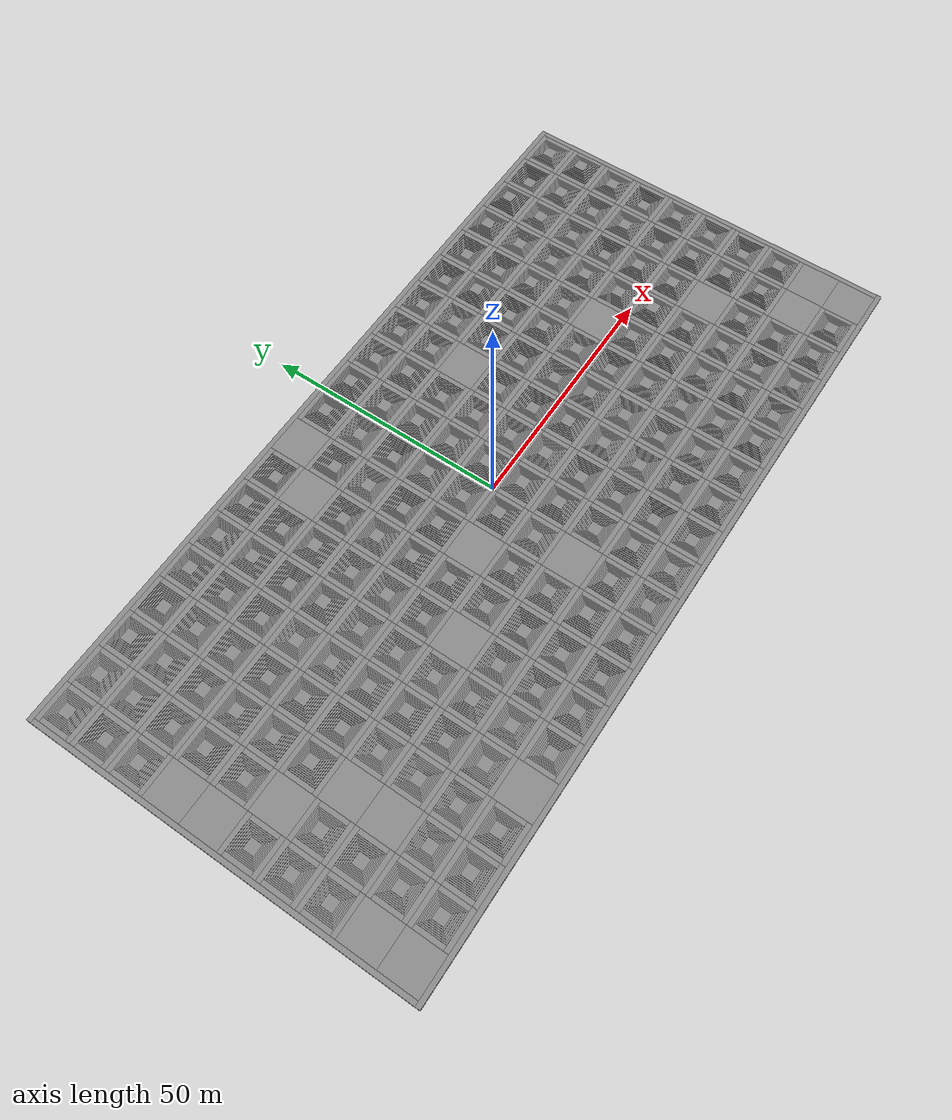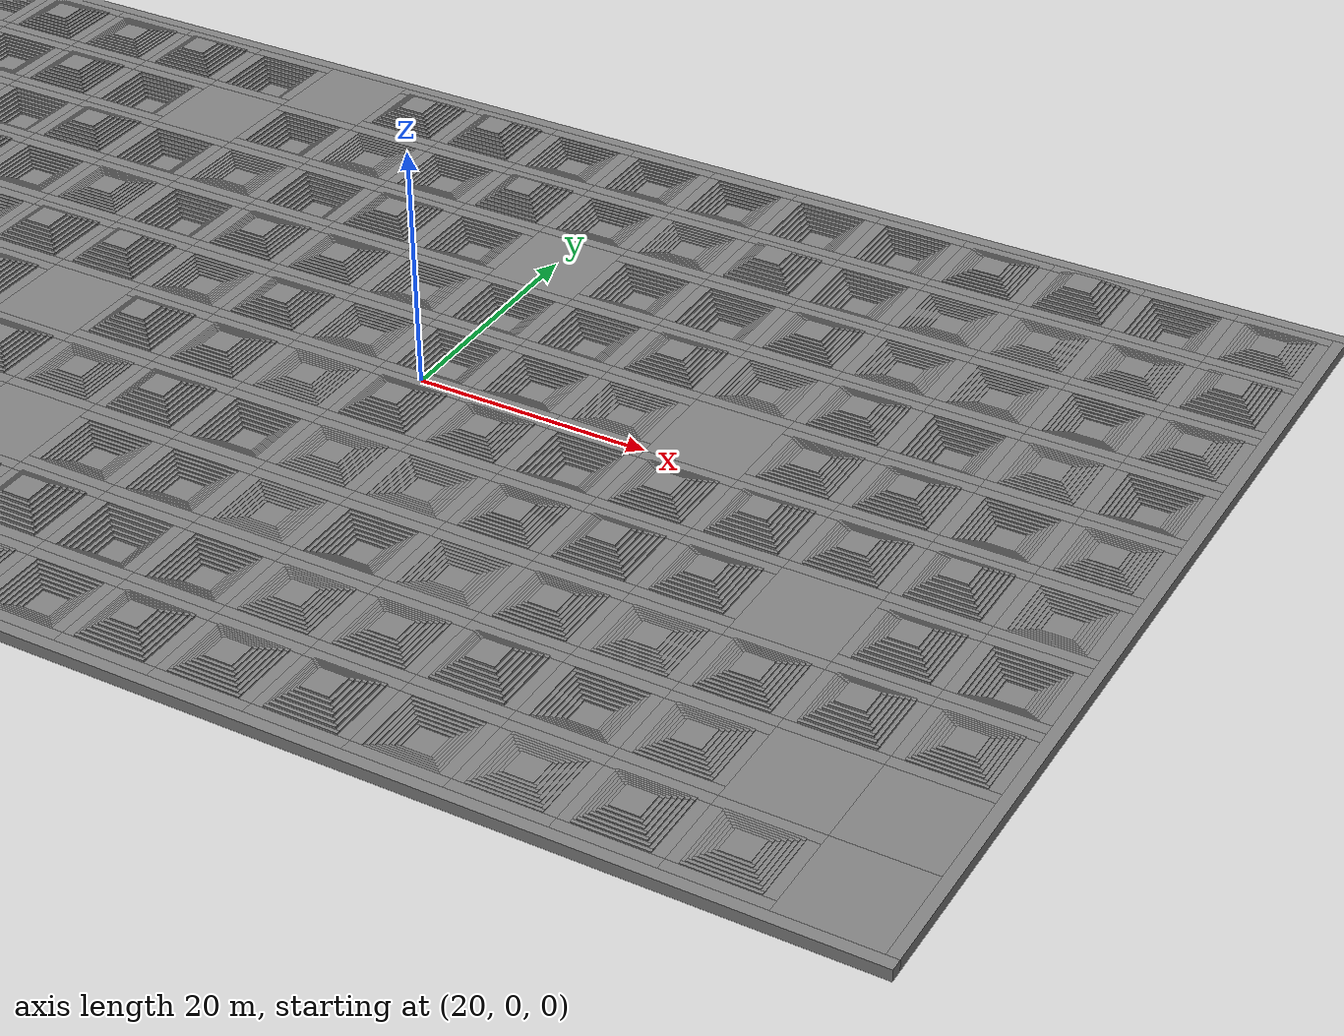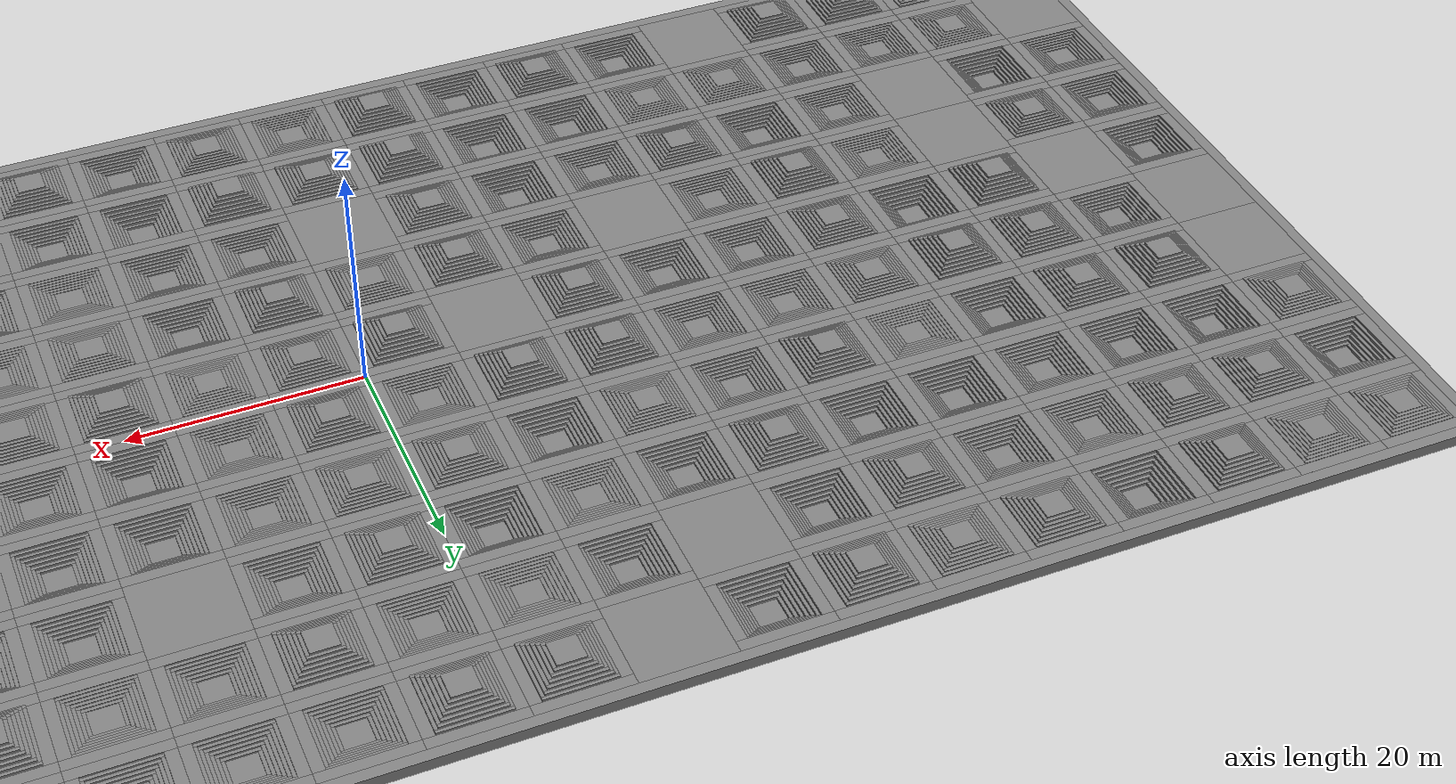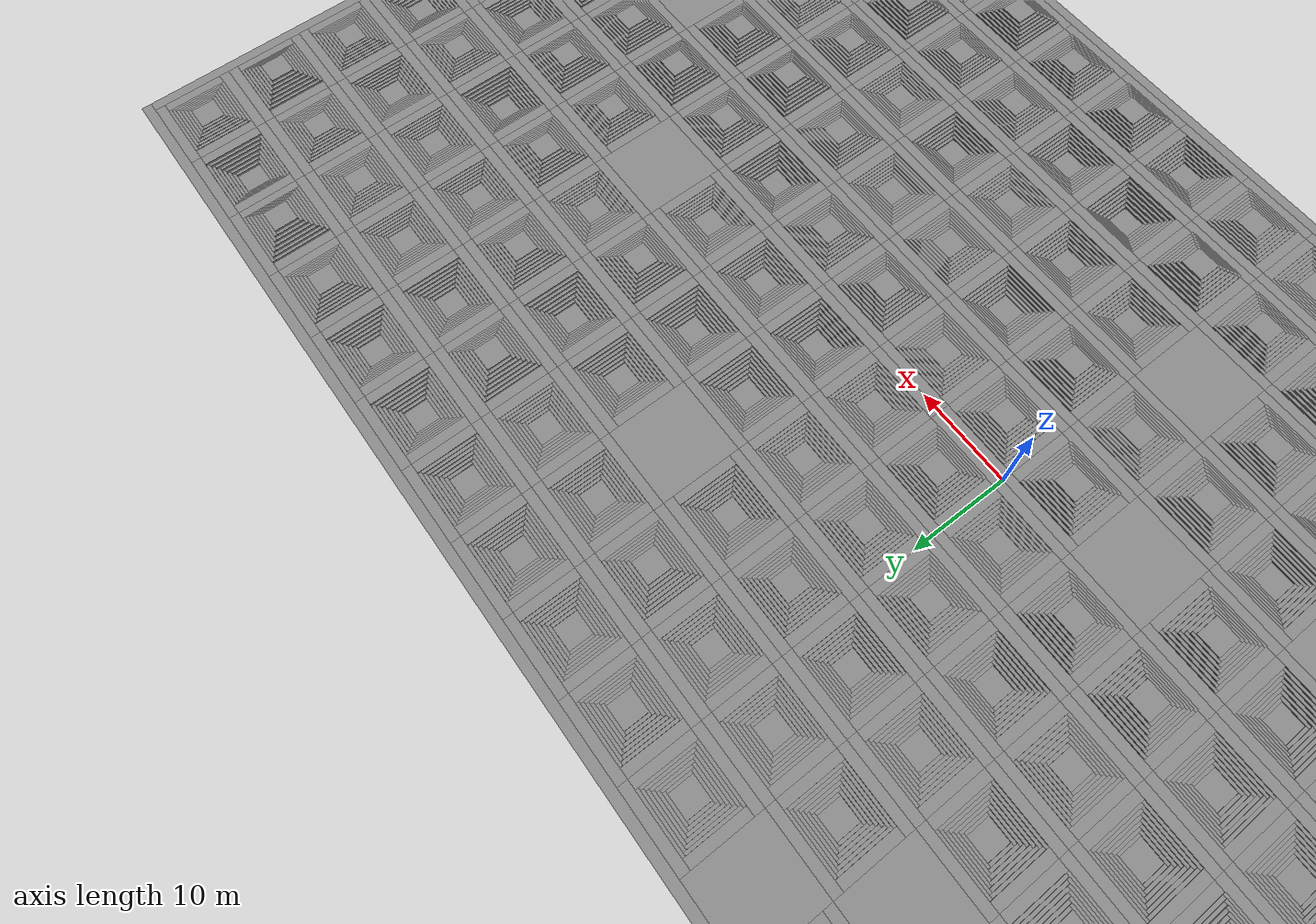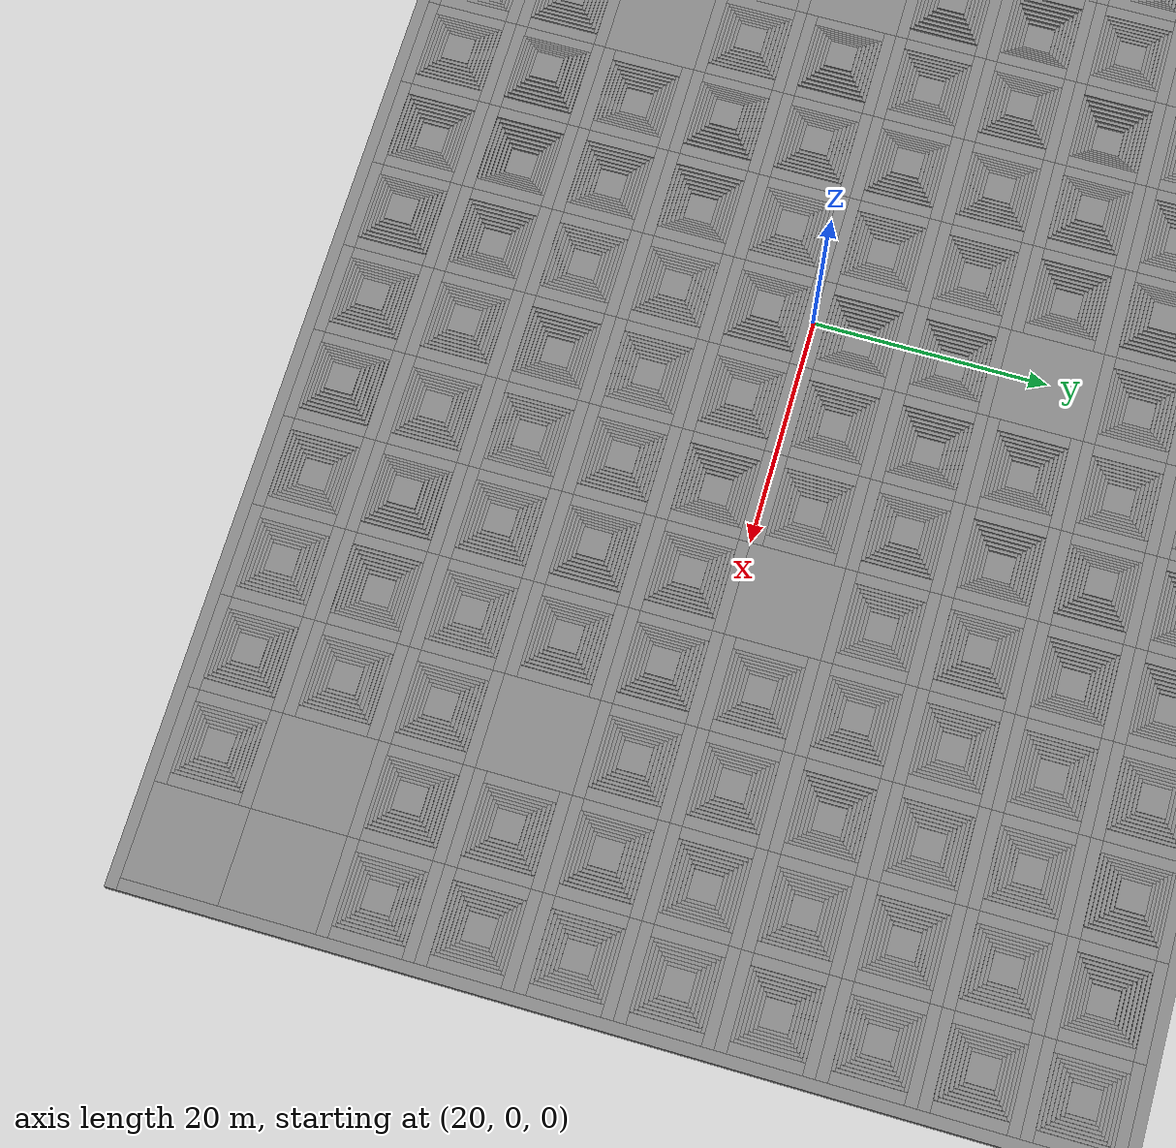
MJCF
<mujoco model="apptronik_apollo scene">
  <include file="apptronik_apollo.xml" />

  <visual>
    <map znear="0.01" zfar="200" />
    <quality shadowsize="8192" />
    <headlight diffuse=".8 .8 .8" ambient=".2 .2 .2" specular="1 1 1" />
    <global azimuth="140" elevation="-20" />
  </visual>

  <asset>
    <texture type="skybox" builtin="gradient" rgb1="1 1 1" rgb2="1 1 1" width="800" height="800" />
  </asset>

  <worldbody>
    <light pos="0 0 3" dir="0 0 -1" directional="true" />
    <geom pos="-76.0 -36.0 -0.5" type="box" size="4.0 4.0 0.5" quat="1.0 0.0 0.0 0.0" contype="1" conaffinity="1" />
    <geom pos="-68.0 -32.5 -0.06285017165887255" type="box" size="4.0 0.5 0.06285017165887255" quat="1.0 0.0 0.0 0.0" contype="1" conaffinity="1" />
    <geom pos="-68.0 -39.5 -0.06285017165887255" type="box" size="4.0 0.5 0.06285017165887255" quat="1.0 0.0 0.0 0.0" contype="1" conaffinity="1" />
    <geom pos="-71.5 -36.0 -0.06285017165887255" type="box" size="0.5 3.0 0.06285017165887255" quat="1.0 0.0 0.0 0.0" contype="1" conaffinity="1" />
    <geom pos="-64.5 -36.0 -0.06285017165887255" type="box" size="0.5 3.0 0.06285017165887255" quat="1.0 0.0 0.0 0.0" contype="1" conaffinity="1" />
    <geom pos="-68.0 -33.15 0.0" type="box" size="3.0 0.15 0.1257003433177451" quat="1.0 0.0 0.0 0.0" contype="1" conaffinity="1" />
    <geom pos="-68.0 -38.85 0.0" type="box" size="3.0 0.15 0.1257003433177451" quat="1.0 0.0 0.0 0.0" contype="1" conaffinity="1" />
    <geom pos="-65.15 -36.0 0.0" type="box" size="0.15 2.7 0.1257003433177451" quat="1.0 0.0 0.0 0.0" contype="1" conaffinity="1" />
    <geom pos="-70.85 -36.0 0.0" type="box" size="0.15 2.7 0.1257003433177451" quat="1.0 0.0 0.0 0.0" contype="1" conaffinity="1" />
    <geom pos="-68.0 -33.45 0.06285017165887255" type="box" size="2.7 0.15 0.18855051497661765" quat="1.0 0.0 0.0 0.0" contype="1" conaffinity="1" />
    <geom pos="-68.0 -38.55 0.06285017165887255" type="box" size="2.7 0.15 0.18855051497661765" quat="1.0 0.0 0.0 0.0" contype="1" conaffinity="1" />
    <geom pos="-65.45 -36.0 0.06285017165887255" type="box" size="0.15 2.4000000000000004 0.18855051497661765" quat="1.0 0.0 0.0 0.0" contype="1" conaffinity="1" />
    <geom pos="-70.55 -36.0 0.06285017165887255" type="box" size="0.15 2.4000000000000004 0.18855051497661765" quat="1.0 0.0 0.0 0.0" contype="1" conaffinity="1" />
    <geom pos="-68.0 -33.75 0.1257003433177451" type="box" size="2.4 0.15 0.2514006866354902" quat="1.0 0.0 0.0 0.0" contype="1" conaffinity="1" />
    <geom pos="-68.0 -38.25 0.1257003433177451" type="box" size="2.4 0.15 0.2514006866354902" quat="1.0 0.0 0.0 0.0" contype="1" conaffinity="1" />
    <geom pos="-65.75 -36.0 0.1257003433177451" type="box" size="0.15 2.1 0.2514006866354902" quat="1.0 0.0 0.0 0.0" contype="1" conaffinity="1" />
    <geom pos="-70.25 -36.0 0.1257003433177451" type="box" size="0.15 2.1 0.2514006866354902" quat="1.0 0.0 0.0 0.0" contype="1" conaffinity="1" />
    <geom pos="-68.0 -34.05 0.18855051497661765" type="box" size="2.1 0.15 0.3142508582943627" quat="1.0 0.0 0.0 0.0" contype="1" conaffinity="1" />
    <geom pos="-68.0 -37.95 0.18855051497661765" type="box" size="2.1 0.15 0.3142508582943627" quat="1.0 0.0 0.0 0.0" contype="1" conaffinity="1" />
    <geom pos="-66.05 -36.0 0.18855051497661765" type="box" size="0.15 1.8 0.3142508582943627" quat="1.0 0.0 0.0 0.0" contype="1" conaffinity="1" />
    <geom pos="-69.95 -36.0 0.18855051497661765" type="box" size="0.15 1.8 0.3142508582943627" quat="1.0 0.0 0.0 0.0" contype="1" conaffinity="1" />
    <geom pos="-68.0 -34.35 0.2514006866354902" type="box" size="1.8 0.15 0.3771010299532353" quat="1.0 0.0 0.0 0.0" contype="1" conaffinity="1" />
    <geom pos="-68.0 -37.65 0.2514006866354902" type="box" size="1.8 0.15 0.3771010299532353" quat="1.0 0.0 0.0 0.0" contype="1" conaffinity="1" />
    <geom pos="-66.35 -36.0 0.2514006866354902" type="box" size="0.15 1.5 0.3771010299532353" quat="1.0 0.0 0.0 0.0" contype="1" conaffinity="1" />
    <geom pos="-69.65 -36.0 0.2514006866354902" type="box" size="0.15 1.5 0.3771010299532353" quat="1.0 0.0 0.0 0.0" contype="1" conaffinity="1" />
    <geom pos="-68.0 -34.65 0.3142508582943627" type="box" size="1.5 0.15 0.4399512016121079" quat="1.0 0.0 0.0 0.0" contype="1" conaffinity="1" />
    <geom pos="-68.0 -37.35 0.3142508582943627" type="box" size="1.5 0.15 0.4399512016121079" quat="1.0 0.0 0.0 0.0" contype="1" conaffinity="1" />
    <geom pos="-66.65 -36.0 0.3142508582943627" type="box" size="0.15 1.2 0.4399512016121079" quat="1.0 0.0 0.0 0.0" contype="1" conaffinity="1" />
    <geom pos="-69.35 -36.0 0.3142508582943627" type="box" size="0.15 1.2 0.4399512016121079" quat="1.0 0.0 0.0 0.0" contype="1" conaffinity="1" />
    <geom pos="-68.0 -36.0 0.3771010299532353" type="box" size="1.2000000000000002 1.2000000000000002 0.5028013732709804" quat="1.0 0.0 0.0 0.0" contype="1" conaffinity="1" />
    <geom pos="-60.0 -32.5 -0.09456334592818169" type="box" size="4.0 0.5 0.09456334592818169" quat="1.0 0.0 0.0 0.0" contype="1" conaffinity="1" />
    <geom pos="-60.0 -39.5 -0.09456334592818169" type="box" size="4.0 0.5 0.09456334592818169" quat="1.0 0.0 0.0 0.0" contype="1" conaffinity="1" />
    <geom pos="-63.5 -36.0 -0.09456334592818169" type="box" size="0.5 3.0 0.09456334592818169" quat="1.0 0.0 0.0 0.0" contype="1" conaffinity="1" />
    <geom pos="-56.5 -36.0 -0.09456334592818169" type="box" size="0.5 3.0 0.09456334592818169" quat="1.0 0.0 0.0 0.0" contype="1" conaffinity="1" />
    <geom pos="-60.0 -33.15 0.0" type="box" size="3.0 0.15 0.18912669185636338" quat="1.0 0.0 0.0 0.0" contype="1" conaffinity="1" />
    <geom pos="-60.0 -38.85 0.0" type="box" size="3.0 0.15 0.18912669185636338" quat="1.0 0.0 0.0 0.0" contype="1" conaffinity="1" />
    <geom pos="-57.15 -36.0 0.0" type="box" size="0.15 2.7 0.18912669185636338" quat="1.0 0.0 0.0 0.0" contype="1" conaffinity="1" />
    <geom pos="-62.85 -36.0 0.0" type="box" size="0.15 2.7 0.18912669185636338" quat="1.0 0.0 0.0 0.0" contype="1" conaffinity="1" />
    <geom pos="-60.0 -33.45 0.09456334592818169" type="box" size="2.7 0.15 0.28369003778454505" quat="1.0 0.0 0.0 0.0" contype="1" conaffinity="1" />
    <geom pos="-60.0 -38.55 0.09456334592818169" type="box" size="2.7 0.15 0.28369003778454505" quat="1.0 0.0 0.0 0.0" contype="1" conaffinity="1" />
    <geom pos="-57.45 -36.0 0.09456334592818169" type="box" size="0.15 2.4000000000000004 0.28369003778454505" quat="1.0 0.0 0.0 0.0" contype="1" conaffinity="1" />
    <geom pos="-62.55 -36.0 0.09456334592818169" type="box" size="0.15 2.4000000000000004 0.28369003778454505" quat="1.0 0.0 0.0 0.0" contype="1" conaffinity="1" />
    <geom pos="-60.0 -33.75 0.18912669185636338" type="box" size="2.4 0.15 0.37825338371272677" quat="1.0 0.0 0.0 0.0" contype="1" conaffinity="1" />
    <geom pos="-60.0 -38.25 0.18912669185636338" type="box" size="2.4 0.15 0.37825338371272677" quat="1.0 0.0 0.0 0.0" contype="1" conaffinity="1" />
    <geom pos="-57.75 -36.0 0.18912669185636338" type="box" size="0.15 2.1 0.37825338371272677" quat="1.0 0.0 0.0 0.0" contype="1" conaffinity="1" />
    <geom pos="-62.25 -36.0 0.18912669185636338" type="box" size="0.15 2.1 0.37825338371272677" quat="1.0 0.0 0.0 0.0" contype="1" conaffinity="1" />
    <geom pos="-60.0 -34.05 0.28369003778454505" type="box" size="2.1 0.15 0.4728167296409085" quat="1.0 0.0 0.0 0.0" contype="1" conaffinity="1" />
    <geom pos="-60.0 -37.95 0.28369003778454505" type="box" size="2.1 0.15 0.4728167296409085" quat="1.0 0.0 0.0 0.0" contype="1" conaffinity="1" />
    <geom pos="-58.05 -36.0 0.28369003778454505" type="box" size="0.15 1.8 0.4728167296409085" quat="1.0 0.0 0.0 0.0" contype="1" conaffinity="1" />
    <geom pos="-61.95 -36.0 0.28369003778454505" type="box" size="0.15 1.8 0.4728167296409085" quat="1.0 0.0 0.0 0.0" contype="1" conaffinity="1" />
    <geom pos="-60.0 -34.35 0.37825338371272677" type="box" size="1.8 0.15 0.5673800755690901" quat="1.0 0.0 0.0 0.0" contype="1" conaffinity="1" />
    <geom pos="-60.0 -37.65 0.37825338371272677" type="box" size="1.8 0.15 0.5673800755690901" quat="1.0 0.0 0.0 0.0" contype="1" conaffinity="1" />
    <geom pos="-58.35 -36.0 0.37825338371272677" type="box" size="0.15 1.5 0.5673800755690901" quat="1.0 0.0 0.0 0.0" contype="1" conaffinity="1" />
    <geom pos="-61.65 -36.0 0.37825338371272677" type="box" size="0.15 1.5 0.5673800755690901" quat="1.0 0.0 0.0 0.0" contype="1" conaffinity="1" />
    <geom pos="-60.0 -34.65 0.4728167296409085" type="box" size="1.5 0.15 0.6619434214972718" quat="1.0 0.0 0.0 0.0" contype="1" conaffinity="1" />
    <geom pos="-60.0 -37.35 0.4728167296409085" type="box" size="1.5 0.15 0.6619434214972718" quat="1.0 0.0 0.0 0.0" contype="1" conaffinity="1" />
    <geom pos="-58.65 -36.0 0.4728167296409085" type="box" size="0.15 1.2 0.6619434214972718" quat="1.0 0.0 0.0 0.0" contype="1" conaffinity="1" />
    <geom pos="-61.35 -36.0 0.4728167296409085" type="box" size="0.15 1.2 0.6619434214972718" quat="1.0 0.0 0.0 0.0" contype="1" conaffinity="1" />
    <geom pos="-60.0 -36.0 0.5673800755690901" type="box" size="1.2000000000000002 1.2000000000000002 0.7565067674254535" quat="1.0 0.0 0.0 0.0" contype="1" conaffinity="1" />
    <geom pos="-52.0 -32.5 -0.08757239631895591" type="box" size="4.0 0.5 0.08757239631895591" quat="1.0 0.0 0.0 0.0" contype="1" conaffinity="1" />
    <geom pos="-52.0 -39.5 -0.08757239631895591" type="box" size="4.0 0.5 0.08757239631895591" quat="1.0 0.0 0.0 0.0" contype="1" conaffinity="1" />
    <geom pos="-55.5 -36.0 -0.08757239631895591" type="box" size="0.5 3.0 0.08757239631895591" quat="1.0 0.0 0.0 0.0" contype="1" conaffinity="1" />
    <geom pos="-48.5 -36.0 -0.08757239631895591" type="box" size="0.5 3.0 0.08757239631895591" quat="1.0 0.0 0.0 0.0" contype="1" conaffinity="1" />
    <geom pos="-52.0 -33.15 0.0" type="box" size="3.0 0.15 0.17514479263791183" quat="1.0 0.0 0.0 0.0" contype="1" conaffinity="1" />
    <geom pos="-52.0 -38.85 0.0" type="box" size="3.0 0.15 0.17514479263791183" quat="1.0 0.0 0.0 0.0" contype="1" conaffinity="1" />
    <geom pos="-49.15 -36.0 0.0" type="box" size="0.15 2.7 0.17514479263791183" quat="1.0 0.0 0.0 0.0" contype="1" conaffinity="1" />
    <geom pos="-54.85 -36.0 0.0" type="box" size="0.15 2.7 0.17514479263791183" quat="1.0 0.0 0.0 0.0" contype="1" conaffinity="1" />
    <geom pos="-52.0 -33.45 0.08757239631895591" type="box" size="2.7 0.15 0.26271718895686774" quat="1.0 0.0 0.0 0.0" contype="1" conaffinity="1" />
    <geom pos="-52.0 -38.55 0.08757239631895591" type="box" size="2.7 0.15 0.26271718895686774" quat="1.0 0.0 0.0 0.0" contype="1" conaffinity="1" />
    <geom pos="-49.45 -36.0 0.08757239631895591" type="box" size="0.15 2.4000000000000004 0.26271718895686774" quat="1.0 0.0 0.0 0.0" contype="1" conaffinity="1" />
    <geom pos="-54.55 -36.0 0.08757239631895591" type="box" size="0.15 2.4000000000000004 0.26271718895686774" quat="1.0 0.0 0.0 0.0" contype="1" conaffinity="1" />
    <geom pos="-52.0 -33.75 0.17514479263791183" type="box" size="2.4 0.15 0.35028958527582366" quat="1.0 0.0 0.0 0.0" contype="1" conaffinity="1" />
    <geom pos="-52.0 -38.25 0.17514479263791183" type="box" size="2.4 0.15 0.35028958527582366" quat="1.0 0.0 0.0 0.0" contype="1" conaffinity="1" />
    <geom pos="-49.75 -36.0 0.17514479263791183" type="box" size="0.15 2.1 0.35028958527582366" quat="1.0 0.0 0.0 0.0" contype="1" conaffinity="1" />
    <geom pos="-54.25 -36.0 0.17514479263791183" type="box" size="0.15 2.1 0.35028958527582366" quat="1.0 0.0 0.0 0.0" contype="1" conaffinity="1" />
    <geom pos="-52.0 -34.05 0.26271718895686774" type="box" size="2.1 0.15 0.43786198159477957" quat="1.0 0.0 0.0 0.0" contype="1" conaffinity="1" />
    <geom pos="-52.0 -37.95 0.26271718895686774" type="box" size="2.1 0.15 0.43786198159477957" quat="1.0 0.0 0.0 0.0" contype="1" conaffinity="1" />
    <geom pos="-50.05 -36.0 0.26271718895686774" type="box" size="0.15 1.8 0.43786198159477957" quat="1.0 0.0 0.0 0.0" contype="1" conaffinity="1" />
    <geom pos="-53.95 -36.0 0.26271718895686774" type="box" size="0.15 1.8 0.43786198159477957" quat="1.0 0.0 0.0 0.0" contype="1" conaffinity="1" />
    <geom pos="-52.0 -34.35 0.35028958527582366" type="box" size="1.8 0.15 0.5254343779137355" quat="1.0 0.0 0.0 0.0" contype="1" conaffinity="1" />
    <geom pos="-52.0 -37.65 0.35028958527582366" type="box" size="1.8 0.15 0.5254343779137355" quat="1.0 0.0 0.0 0.0" contype="1" conaffinity="1" />
    <geom pos="-50.35 -36.0 0.35028958527582366" type="box" size="0.15 1.5 0.5254343779137355" quat="1.0 0.0 0.0 0.0" contype="1" conaffinity="1" />
    <geom pos="-53.65 -36.0 0.35028958527582366" type="box" size="0.15 1.5 0.5254343779137355" quat="1.0 0.0 0.0 0.0" contype="1" conaffinity="1" />
    <geom pos="-52.0 -34.65 0.43786198159477957" type="box" size="1.5 0.15 0.6130067742326915" quat="1.0 0.0 0.0 0.0" contype="1" conaffinity="1" />
    <geom pos="-52.0 -37.35 0.43786198159477957" type="box" size="1.5 0.15 0.6130067742326915" quat="1.0 0.0 0.0 0.0" contype="1" conaffinity="1" />
    <geom pos="-50.65 -36.0 0.43786198159477957" type="box" size="0.15 1.2 0.6130067742326915" quat="1.0 0.0 0.0 0.0" contype="1" conaffinity="1" />
    <geom pos="-53.35 -36.0 0.43786198159477957" type="box" size="0.15 1.2 0.6130067742326915" quat="1.0 0.0 0.0 0.0" contype="1" conaffinity="1" />
    <geom pos="-52.0 -36.0 0.5254343779137355" type="box" size="1.2000000000000002 1.2000000000000002 0.7005791705516473" quat="1.0 0.0 0.0 0.0" contype="1" conaffinity="1" />
    <geom pos="-44.0 -36.0 -0.5" type="box" size="4.0 4.0 0.5" quat="1.0 0.0 0.0 0.0" contype="1" conaffinity="1" />
    <geom pos="-36.0 -32.5 -0.07301961824232539" type="box" size="4.0 0.5 0.07301961824232539" quat="1.0 0.0 0.0 0.0" contype="1" conaffinity="1" />
    <geom pos="-36.0 -39.5 -0.07301961824232539" type="box" size="4.0 0.5 0.07301961824232539" quat="1.0 0.0 0.0 0.0" contype="1" conaffinity="1" />
    <geom pos="-39.5 -36.0 -0.07301961824232539" type="box" size="0.5 3.0 0.07301961824232539" quat="1.0 0.0 0.0 0.0" contype="1" conaffinity="1" />
    <geom pos="-32.5 -36.0 -0.07301961824232539" type="box" size="0.5 3.0 0.07301961824232539" quat="1.0 0.0 0.0 0.0" contype="1" conaffinity="1" />
    <geom pos="-36.0 -33.15 -0.5841569459386031" type="box" size="3.0 0.15 0.43811770945395234" quat="1.0 0.0 0.0 0.0" contype="1" conaffinity="1" />
    <geom pos="-36.0 -38.85 -0.5841569459386031" type="box" size="3.0 0.15 0.43811770945395234" quat="1.0 0.0 0.0 0.0" contype="1" conaffinity="1" />
    <geom pos="-33.15 -36.0 -0.5841569459386031" type="box" size="0.15 2.7 0.43811770945395234" quat="1.0 0.0 0.0 0.0" contype="1" conaffinity="1" />
    <geom pos="-38.85 -36.0 -0.5841569459386031" type="box" size="0.15 2.7 0.43811770945395234" quat="1.0 0.0 0.0 0.0" contype="1" conaffinity="1" />
    <geom pos="-36.0 -33.45 -0.6571765641809285" type="box" size="2.7 0.15 0.36509809121162695" quat="1.0 0.0 0.0 0.0" contype="1" conaffinity="1" />
    <geom pos="-36.0 -38.55 -0.6571765641809285" type="box" size="2.7 0.15 0.36509809121162695" quat="1.0 0.0 0.0 0.0" contype="1" conaffinity="1" />
    <geom pos="-33.45 -36.0 -0.6571765641809285" type="box" size="0.15 2.4000000000000004 0.36509809121162695" quat="1.0 0.0 0.0 0.0" contype="1" conaffinity="1" />
    <geom pos="-38.55 -36.0 -0.6571765641809285" type="box" size="0.15 2.4000000000000004 0.36509809121162695" quat="1.0 0.0 0.0 0.0" contype="1" conaffinity="1" />
    <geom pos="-36.0 -33.75 -0.7301961824232539" type="box" size="2.4 0.15 0.29207847296930156" quat="1.0 0.0 0.0 0.0" contype="1" conaffinity="1" />
    <geom pos="-36.0 -38.25 -0.7301961824232539" type="box" size="2.4 0.15 0.29207847296930156" quat="1.0 0.0 0.0 0.0" contype="1" conaffinity="1" />
    <geom pos="-33.75 -36.0 -0.7301961824232539" type="box" size="0.15 2.1 0.29207847296930156" quat="1.0 0.0 0.0 0.0" contype="1" conaffinity="1" />
    <geom pos="-38.25 -36.0 -0.7301961824232539" type="box" size="0.15 2.1 0.29207847296930156" quat="1.0 0.0 0.0 0.0" contype="1" conaffinity="1" />
    <geom pos="-36.0 -34.05 -0.8032158006655793" type="box" size="2.1 0.15 0.21905885472697617" quat="1.0 0.0 0.0 0.0" contype="1" conaffinity="1" />
    <geom pos="-36.0 -37.95 -0.8032158006655793" type="box" size="2.1 0.15 0.21905885472697617" quat="1.0 0.0 0.0 0.0" contype="1" conaffinity="1" />
    <geom pos="-34.05 -36.0 -0.8032158006655793" type="box" size="0.15 1.8 0.21905885472697617" quat="1.0 0.0 0.0 0.0" contype="1" conaffinity="1" />
    <geom pos="-37.95 -36.0 -0.8032158006655793" type="box" size="0.15 1.8 0.21905885472697617" quat="1.0 0.0 0.0 0.0" contype="1" conaffinity="1" />
    <geom pos="-36.0 -34.35 -0.8762354189079047" type="box" size="1.8 0.15 0.14603923648465078" quat="1.0 0.0 0.0 0.0" contype="1" conaffinity="1" />
    <geom pos="-36.0 -37.65 -0.8762354189079047" type="box" size="1.8 0.15 0.14603923648465078" quat="1.0 0.0 0.0 0.0" contype="1" conaffinity="1" />
    <geom pos="-34.35 -36.0 -0.8762354189079047" type="box" size="0.15 1.5 0.14603923648465078" quat="1.0 0.0 0.0 0.0" contype="1" conaffinity="1" />
    <geom pos="-37.65 -36.0 -0.8762354189079047" type="box" size="0.15 1.5 0.14603923648465078" quat="1.0 0.0 0.0 0.0" contype="1" conaffinity="1" />
    <geom pos="-36.0 -34.65 -0.9492550371502301" type="box" size="1.5 0.15 0.07301961824232539" quat="1.0 0.0 0.0 0.0" contype="1" conaffinity="1" />
    <geom pos="-36.0 -37.35 -0.9492550371502301" type="box" size="1.5 0.15 0.07301961824232539" quat="1.0 0.0 0.0 0.0" contype="1" conaffinity="1" />
    <geom pos="-34.65 -36.0 -0.9492550371502301" type="box" size="0.15 1.2 0.07301961824232539" quat="1.0 0.0 0.0 0.0" contype="1" conaffinity="1" />
    <geom pos="-37.35 -36.0 -0.9492550371502301" type="box" size="0.15 1.2 0.07301961824232539" quat="1.0 0.0 0.0 0.0" contype="1" conaffinity="1" />
    <geom pos="-36.0 -36.0 -1.095294273634881" type="box" size="1.2000000000000002 1.2000000000000002 0.07301961824232539" quat="1.0 0.0 0.0 0.0" contype="1" conaffinity="1" />
    <geom pos="-28.0 -32.5 -0.07394950662146565" type="box" size="4.0 0.5 0.07394950662146565" quat="1.0 0.0 0.0 0.0" contype="1" conaffinity="1" />
    <geom pos="-28.0 -39.5 -0.07394950662146565" type="box" size="4.0 0.5 0.07394950662146565" quat="1.0 0.0 0.0 0.0" contype="1" conaffinity="1" />
    <geom pos="-31.5 -36.0 -0.07394950662146565" type="box" size="0.5 3.0 0.07394950662146565" quat="1.0 0.0 0.0 0.0" contype="1" conaffinity="1" />
    <geom pos="-24.5 -36.0 -0.07394950662146565" type="box" size="0.5 3.0 0.07394950662146565" quat="1.0 0.0 0.0 0.0" contype="1" conaffinity="1" />
    <geom pos="-28.0 -33.15 0.0" type="box" size="3.0 0.15 0.1478990132429313" quat="1.0 0.0 0.0 0.0" contype="1" conaffinity="1" />
    <geom pos="-28.0 -38.85 0.0" type="box" size="3.0 0.15 0.1478990132429313" quat="1.0 0.0 0.0 0.0" contype="1" conaffinity="1" />
    <geom pos="-25.15 -36.0 0.0" type="box" size="0.15 2.7 0.1478990132429313" quat="1.0 0.0 0.0 0.0" contype="1" conaffinity="1" />
    <geom pos="-30.85 -36.0 0.0" type="box" size="0.15 2.7 0.1478990132429313" quat="1.0 0.0 0.0 0.0" contype="1" conaffinity="1" />
    <geom pos="-28.0 -33.45 0.07394950662146565" type="box" size="2.7 0.15 0.22184851986439696" quat="1.0 0.0 0.0 0.0" contype="1" conaffinity="1" />
    <geom pos="-28.0 -38.55 0.07394950662146565" type="box" size="2.7 0.15 0.22184851986439696" quat="1.0 0.0 0.0 0.0" contype="1" conaffinity="1" />
    <geom pos="-25.45 -36.0 0.07394950662146565" type="box" size="0.15 2.4000000000000004 0.22184851986439696" quat="1.0 0.0 0.0 0.0" contype="1" conaffinity="1" />
    <geom pos="-30.55 -36.0 0.07394950662146565" type="box" size="0.15 2.4000000000000004 0.22184851986439696" quat="1.0 0.0 0.0 0.0" contype="1" conaffinity="1" />
    <geom pos="-28.0 -33.75 0.1478990132429313" type="box" size="2.4 0.15 0.2957980264858626" quat="1.0 0.0 0.0 0.0" contype="1" conaffinity="1" />
    <geom pos="-28.0 -38.25 0.1478990132429313" type="box" size="2.4 0.15 0.2957980264858626" quat="1.0 0.0 0.0 0.0" contype="1" conaffinity="1" />
    <geom pos="-25.75 -36.0 0.1478990132429313" type="box" size="0.15 2.1 0.2957980264858626" quat="1.0 0.0 0.0 0.0" contype="1" conaffinity="1" />
    <geom pos="-30.25 -36.0 0.1478990132429313" type="box" size="0.15 2.1 0.2957980264858626" quat="1.0 0.0 0.0 0.0" contype="1" conaffinity="1" />
    <geom pos="-28.0 -34.05 0.22184851986439696" type="box" size="2.1 0.15 0.3697475331073283" quat="1.0 0.0 0.0 0.0" contype="1" conaffinity="1" />
    <geom pos="-28.0 -37.95 0.22184851986439696" type="box" size="2.1 0.15 0.3697475331073283" quat="1.0 0.0 0.0 0.0" contype="1" conaffinity="1" />
    <geom pos="-26.05 -36.0 0.22184851986439696" type="box" size="0.15 1.8 0.3697475331073283" quat="1.0 0.0 0.0 0.0" contype="1" conaffinity="1" />
    <geom pos="-29.95 -36.0 0.22184851986439696" type="box" size="0.15 1.8 0.3697475331073283" quat="1.0 0.0 0.0 0.0" contype="1" conaffinity="1" />
    <geom pos="-28.0 -34.35 0.2957980264858626" type="box" size="1.8 0.15 0.44369703972879393" quat="1.0 0.0 0.0 0.0" contype="1" conaffinity="1" />
    <geom pos="-28.0 -37.65 0.2957980264858626" type="box" size="1.8 0.15 0.44369703972879393" quat="1.0 0.0 0.0 0.0" contype="1" conaffinity="1" />
    <geom pos="-26.35 -36.0 0.2957980264858626" type="box" size="0.15 1.5 0.44369703972879393" quat="1.0 0.0 0.0 0.0" contype="1" conaffinity="1" />
    <geom pos="-29.65 -36.0 0.2957980264858626" type="box" size="0.15 1.5 0.44369703972879393" quat="1.0 0.0 0.0 0.0" contype="1" conaffinity="1" />
    <geom pos="-28.0 -34.65 0.3697475331073283" type="box" size="1.5 0.15 0.5176465463502595" quat="1.0 0.0 0.0 0.0" contype="1" conaffinity="1" />
    <geom pos="-28.0 -37.35 0.3697475331073283" type="box" size="1.5 0.15 0.5176465463502595" quat="1.0 0.0 0.0 0.0" contype="1" conaffinity="1" />
    <geom pos="-26.65 -36.0 0.3697475331073283" type="box" size="0.15 1.2 0.5176465463502595" quat="1.0 0.0 0.0 0.0" contype="1" conaffinity="1" />
    <geom pos="-29.35 -36.0 0.3697475331073283" type="box" size="0.15 1.2 0.5176465463502595" quat="1.0 0.0 0.0 0.0" contype="1" conaffinity="1" />
    <geom pos="-28.0 -36.0 0.44369703972879393" type="box" size="1.2000000000000002 1.2000000000000002 0.5915960529717252" quat="1.0 0.0 0.0 0.0" contype="1" conaffinity="1" />
    <geom pos="-20.0 -32.5 -0.08633380886691314" type="box" size="4.0 0.5 0.08633380886691314" quat="1.0 0.0 0.0 0.0" contype="1" conaffinity="1" />
    <geom pos="-20.0 -39.5 -0.08633380886691314" type="box" size="4.0 0.5 0.08633380886691314" quat="1.0 0.0 0.0 0.0" contype="1" conaffinity="1" />
    <geom pos="-23.5 -36.0 -0.08633380886691314" type="box" size="0.5 3.0 0.08633380886691314" quat="1.0 0.0 0.0 0.0" contype="1" conaffinity="1" />
    <geom pos="-16.5 -36.0 -0.08633380886691314" type="box" size="0.5 3.0 0.08633380886691314" quat="1.0 0.0 0.0 0.0" contype="1" conaffinity="1" />
    <geom pos="-20.0 -33.15 -0.6906704709353051" type="box" size="3.0 0.15 0.5180028532014789" quat="1.0 0.0 0.0 0.0" contype="1" conaffinity="1" />
    <geom pos="-20.0 -38.85 -0.6906704709353051" type="box" size="3.0 0.15 0.5180028532014789" quat="1.0 0.0 0.0 0.0" contype="1" conaffinity="1" />
    <geom pos="-17.15 -36.0 -0.6906704709353051" type="box" size="0.15 2.7 0.5180028532014789" quat="1.0 0.0 0.0 0.0" contype="1" conaffinity="1" />
    <geom pos="-22.85 -36.0 -0.6906704709353051" type="box" size="0.15 2.7 0.5180028532014789" quat="1.0 0.0 0.0 0.0" contype="1" conaffinity="1" />
    <geom pos="-20.0 -33.45 -0.7770042798022183" type="box" size="2.7 0.15 0.4316690443345657" quat="1.0 0.0 0.0 0.0" contype="1" conaffinity="1" />
    <geom pos="-20.0 -38.55 -0.7770042798022183" type="box" size="2.7 0.15 0.4316690443345657" quat="1.0 0.0 0.0 0.0" contype="1" conaffinity="1" />
    <geom pos="-17.45 -36.0 -0.7770042798022183" type="box" size="0.15 2.4000000000000004 0.4316690443345657" quat="1.0 0.0 0.0 0.0" contype="1" conaffinity="1" />
    <geom pos="-22.55 -36.0 -0.7770042798022183" type="box" size="0.15 2.4000000000000004 0.4316690443345657" quat="1.0 0.0 0.0 0.0" contype="1" conaffinity="1" />
    <geom pos="-20.0 -33.75 -0.8633380886691314" type="box" size="2.4 0.15 0.34533523546765255" quat="1.0 0.0 0.0 0.0" contype="1" conaffinity="1" />
    <geom pos="-20.0 -38.25 -0.8633380886691314" type="box" size="2.4 0.15 0.34533523546765255" quat="1.0 0.0 0.0 0.0" contype="1" conaffinity="1" />
    <geom pos="-17.75 -36.0 -0.8633380886691314" type="box" size="0.15 2.1 0.34533523546765255" quat="1.0 0.0 0.0 0.0" contype="1" conaffinity="1" />
    <geom pos="-22.25 -36.0 -0.8633380886691314" type="box" size="0.15 2.1 0.34533523546765255" quat="1.0 0.0 0.0 0.0" contype="1" conaffinity="1" />
    <geom pos="-20.0 -34.05 -0.9496718975360445" type="box" size="2.1 0.15 0.25900142660073944" quat="1.0 0.0 0.0 0.0" contype="1" conaffinity="1" />
    <geom pos="-20.0 -37.95 -0.9496718975360445" type="box" size="2.1 0.15 0.25900142660073944" quat="1.0 0.0 0.0 0.0" contype="1" conaffinity="1" />
    <geom pos="-18.05 -36.0 -0.9496718975360445" type="box" size="0.15 1.8 0.25900142660073944" quat="1.0 0.0 0.0 0.0" contype="1" conaffinity="1" />
    <geom pos="-21.95 -36.0 -0.9496718975360445" type="box" size="0.15 1.8 0.25900142660073944" quat="1.0 0.0 0.0 0.0" contype="1" conaffinity="1" />
    <geom pos="-20.0 -34.35 -1.0360057064029577" type="box" size="1.8 0.15 0.17266761773382633" quat="1.0 0.0 0.0 0.0" contype="1" conaffinity="1" />
    <geom pos="-20.0 -37.65 -1.0360057064029577" type="box" size="1.8 0.15 0.17266761773382633" quat="1.0 0.0 0.0 0.0" contype="1" conaffinity="1" />
    <geom pos="-18.35 -36.0 -1.0360057064029577" type="box" size="0.15 1.5 0.17266761773382633" quat="1.0 0.0 0.0 0.0" contype="1" conaffinity="1" />
    <geom pos="-21.65 -36.0 -1.0360057064029577" type="box" size="0.15 1.5 0.17266761773382633" quat="1.0 0.0 0.0 0.0" contype="1" conaffinity="1" />
    <geom pos="-20.0 -34.65 -1.122339515269871" type="box" size="1.5 0.15 0.08633380886691311" quat="1.0 0.0 0.0 0.0" contype="1" conaffinity="1" />
    <geom pos="-20.0 -37.35 -1.122339515269871" type="box" size="1.5 0.15 0.08633380886691311" quat="1.0 0.0 0.0 0.0" contype="1" conaffinity="1" />
    <geom pos="-18.65 -36.0 -1.122339515269871" type="box" size="0.15 1.2 0.08633380886691311" quat="1.0 0.0 0.0 0.0" contype="1" conaffinity="1" />
    <geom pos="-21.35 -36.0 -1.122339515269871" type="box" size="0.15 1.2 0.08633380886691311" quat="1.0 0.0 0.0 0.0" contype="1" conaffinity="1" />
    <geom pos="-20.0 -36.0 -1.2950071330036972" type="box" size="1.2000000000000002 1.2000000000000002 0.08633380886691314" quat="1.0 0.0 0.0 0.0" contype="1" conaffinity="1" />
    <geom pos="-12.0 -32.5 -0.09133629743452051" type="box" size="4.0 0.5 0.09133629743452051" quat="1.0 0.0 0.0 0.0" contype="1" conaffinity="1" />
    <geom pos="-12.0 -39.5 -0.09133629743452051" type="box" size="4.0 0.5 0.09133629743452051" quat="1.0 0.0 0.0 0.0" contype="1" conaffinity="1" />
    <geom pos="-15.5 -36.0 -0.09133629743452051" type="box" size="0.5 3.0 0.09133629743452051" quat="1.0 0.0 0.0 0.0" contype="1" conaffinity="1" />
    <geom pos="-8.5 -36.0 -0.09133629743452051" type="box" size="0.5 3.0 0.09133629743452051" quat="1.0 0.0 0.0 0.0" contype="1" conaffinity="1" />
    <geom pos="-12.0 -33.15 0.0" type="box" size="3.0 0.15 0.18267259486904103" quat="1.0 0.0 0.0 0.0" contype="1" conaffinity="1" />
    <geom pos="-12.0 -38.85 0.0" type="box" size="3.0 0.15 0.18267259486904103" quat="1.0 0.0 0.0 0.0" contype="1" conaffinity="1" />
    <geom pos="-9.15 -36.0 0.0" type="box" size="0.15 2.7 0.18267259486904103" quat="1.0 0.0 0.0 0.0" contype="1" conaffinity="1" />
    <geom pos="-14.85 -36.0 0.0" type="box" size="0.15 2.7 0.18267259486904103" quat="1.0 0.0 0.0 0.0" contype="1" conaffinity="1" />
    <geom pos="-12.0 -33.45 0.09133629743452051" type="box" size="2.7 0.15 0.2740088923035615" quat="1.0 0.0 0.0 0.0" contype="1" conaffinity="1" />
    <geom pos="-12.0 -38.55 0.09133629743452051" type="box" size="2.7 0.15 0.2740088923035615" quat="1.0 0.0 0.0 0.0" contype="1" conaffinity="1" />
    <geom pos="-9.45 -36.0 0.09133629743452051" type="box" size="0.15 2.4000000000000004 0.2740088923035615" quat="1.0 0.0 0.0 0.0" contype="1" conaffinity="1" />
    <geom pos="-14.55 -36.0 0.09133629743452051" type="box" size="0.15 2.4000000000000004 0.2740088923035615" quat="1.0 0.0 0.0 0.0" contype="1" conaffinity="1" />
    <geom pos="-12.0 -33.75 0.18267259486904103" type="box" size="2.4 0.15 0.36534518973808205" quat="1.0 0.0 0.0 0.0" contype="1" conaffinity="1" />
    <geom pos="-12.0 -38.25 0.18267259486904103" type="box" size="2.4 0.15 0.36534518973808205" quat="1.0 0.0 0.0 0.0" contype="1" conaffinity="1" />
    <geom pos="-9.75 -36.0 0.18267259486904103" type="box" size="0.15 2.1 0.36534518973808205" quat="1.0 0.0 0.0 0.0" contype="1" conaffinity="1" />
    <geom pos="-14.25 -36.0 0.18267259486904103" type="box" size="0.15 2.1 0.36534518973808205" quat="1.0 0.0 0.0 0.0" contype="1" conaffinity="1" />
    <geom pos="-12.0 -34.05 0.2740088923035615" type="box" size="2.1 0.15 0.4566814871726026" quat="1.0 0.0 0.0 0.0" contype="1" conaffinity="1" />
    <geom pos="-12.0 -37.95 0.2740088923035615" type="box" size="2.1 0.15 0.4566814871726026" quat="1.0 0.0 0.0 0.0" contype="1" conaffinity="1" />
    <geom pos="-10.05 -36.0 0.2740088923035615" type="box" size="0.15 1.8 0.4566814871726026" quat="1.0 0.0 0.0 0.0" contype="1" conaffinity="1" />
    <geom pos="-13.95 -36.0 0.2740088923035615" type="box" size="0.15 1.8 0.4566814871726026" quat="1.0 0.0 0.0 0.0" contype="1" conaffinity="1" />
    <geom pos="-12.0 -34.35 0.36534518973808205" type="box" size="1.8 0.15 0.548017784607123" quat="1.0 0.0 0.0 0.0" contype="1" conaffinity="1" />
    <geom pos="-12.0 -37.65 0.36534518973808205" type="box" size="1.8 0.15 0.548017784607123" quat="1.0 0.0 0.0 0.0" contype="1" conaffinity="1" />
    <geom pos="-10.35 -36.0 0.36534518973808205" type="box" size="0.15 1.5 0.548017784607123" quat="1.0 0.0 0.0 0.0" contype="1" conaffinity="1" />
    <geom pos="-13.65 -36.0 0.36534518973808205" type="box" size="0.15 1.5 0.548017784607123" quat="1.0 0.0 0.0 0.0" contype="1" conaffinity="1" />
    <geom pos="-12.0 -34.65 0.4566814871726026" type="box" size="1.5 0.15 0.6393540820416436" quat="1.0 0.0 0.0 0.0" contype="1" conaffinity="1" />
    <geom pos="-12.0 -37.35 0.4566814871726026" type="box" size="1.5 0.15 0.6393540820416436" quat="1.0 0.0 0.0 0.0" contype="1" conaffinity="1" />
    <geom pos="-10.65 -36.0 0.4566814871726026" type="box" size="0.15 1.2 0.6393540820416436" quat="1.0 0.0 0.0 0.0" contype="1" conaffinity="1" />
    <geom pos="-13.35 -36.0 0.4566814871726026" type="box" size="0.15 1.2 0.6393540820416436" quat="1.0 0.0 0.0 0.0" contype="1" conaffinity="1" />
    <geom pos="-12.0 -36.0 0.548017784607123" type="box" size="1.2000000000000002 1.2000000000000002 0.7306903794761641" quat="1.0 0.0 0.0 0.0" contype="1" conaffinity="1" />
    <geom pos="-4.0 -32.5 -0.027497039286900834" type="box" size="4.0 0.5 0.027497039286900834" quat="1.0 0.0 0.0 0.0" contype="1" conaffinity="1" />
    <geom pos="-4.0 -39.5 -0.027497039286900834" type="box" size="4.0 0.5 0.027497039286900834" quat="1.0 0.0 0.0 0.0" contype="1" conaffinity="1" />
    <geom pos="-7.5 -36.0 -0.027497039286900834" type="box" size="0.5 3.0 0.027497039286900834" quat="1.0 0.0 0.0 0.0" contype="1" conaffinity="1" />
    <geom pos="-0.5 -36.0 -0.027497039286900834" type="box" size="0.5 3.0 0.027497039286900834" quat="1.0 0.0 0.0 0.0" contype="1" conaffinity="1" />
    <geom pos="-4.0 -33.15 -0.21997631429520667" type="box" size="3.0 0.15 0.164982235721405" quat="1.0 0.0 0.0 0.0" contype="1" conaffinity="1" />
    <geom pos="-4.0 -38.85 -0.21997631429520667" type="box" size="3.0 0.15 0.164982235721405" quat="1.0 0.0 0.0 0.0" contype="1" conaffinity="1" />
    <geom pos="-1.1500000000000004 -36.0 -0.21997631429520667" type="box" size="0.15 2.7 0.164982235721405" quat="1.0 0.0 0.0 0.0" contype="1" conaffinity="1" />
    <geom pos="-6.85 -36.0 -0.21997631429520667" type="box" size="0.15 2.7 0.164982235721405" quat="1.0 0.0 0.0 0.0" contype="1" conaffinity="1" />
    <geom pos="-4.0 -33.45 -0.2474733535821075" type="box" size="2.7 0.15 0.13748519643450416" quat="1.0 0.0 0.0 0.0" contype="1" conaffinity="1" />
    <geom pos="-4.0 -38.55 -0.2474733535821075" type="box" size="2.7 0.15 0.13748519643450416" quat="1.0 0.0 0.0 0.0" contype="1" conaffinity="1" />
    <geom pos="-1.4500000000000002 -36.0 -0.2474733535821075" type="box" size="0.15 2.4000000000000004 0.13748519643450416" quat="1.0 0.0 0.0 0.0" contype="1" conaffinity="1" />
    <geom pos="-6.55 -36.0 -0.2474733535821075" type="box" size="0.15 2.4000000000000004 0.13748519643450416" quat="1.0 0.0 0.0 0.0" contype="1" conaffinity="1" />
    <geom pos="-4.0 -33.75 -0.2749703928690083" type="box" size="2.4 0.15 0.10998815714760334" quat="1.0 0.0 0.0 0.0" contype="1" conaffinity="1" />
    <geom pos="-4.0 -38.25 -0.2749703928690083" type="box" size="2.4 0.15 0.10998815714760334" quat="1.0 0.0 0.0 0.0" contype="1" conaffinity="1" />
    <geom pos="-1.75 -36.0 -0.2749703928690083" type="box" size="0.15 2.1 0.10998815714760334" quat="1.0 0.0 0.0 0.0" contype="1" conaffinity="1" />
    <geom pos="-6.25 -36.0 -0.2749703928690083" type="box" size="0.15 2.1 0.10998815714760334" quat="1.0 0.0 0.0 0.0" contype="1" conaffinity="1" />
    <geom pos="-4.0 -34.05 -0.30246743215590915" type="box" size="2.1 0.15 0.0824911178607025" quat="1.0 0.0 0.0 0.0" contype="1" conaffinity="1" />
    <geom pos="-4.0 -37.95 -0.30246743215590915" type="box" size="2.1 0.15 0.0824911178607025" quat="1.0 0.0 0.0 0.0" contype="1" conaffinity="1" />
    <geom pos="-2.05 -36.0 -0.30246743215590915" type="box" size="0.15 1.8 0.0824911178607025" quat="1.0 0.0 0.0 0.0" contype="1" conaffinity="1" />
    <geom pos="-5.95 -36.0 -0.30246743215590915" type="box" size="0.15 1.8 0.0824911178607025" quat="1.0 0.0 0.0 0.0" contype="1" conaffinity="1" />
    <geom pos="-4.0 -34.35 -0.32996447144281" type="box" size="1.8 0.15 0.054994078573801675" quat="1.0 0.0 0.0 0.0" contype="1" conaffinity="1" />
    <geom pos="-4.0 -37.65 -0.32996447144281" type="box" size="1.8 0.15 0.054994078573801675" quat="1.0 0.0 0.0 0.0" contype="1" conaffinity="1" />
    <geom pos="-2.3499999999999996 -36.0 -0.32996447144281" type="box" size="0.15 1.5 0.054994078573801675" quat="1.0 0.0 0.0 0.0" contype="1" conaffinity="1" />
    <geom pos="-5.65 -36.0 -0.32996447144281" type="box" size="0.15 1.5 0.054994078573801675" quat="1.0 0.0 0.0 0.0" contype="1" conaffinity="1" />
    <geom pos="-4.0 -34.65 -0.35746151072971083" type="box" size="1.5 0.15 0.027497039286900837" quat="1.0 0.0 0.0 0.0" contype="1" conaffinity="1" />
    <geom pos="-4.0 -37.35 -0.35746151072971083" type="box" size="1.5 0.15 0.027497039286900837" quat="1.0 0.0 0.0 0.0" contype="1" conaffinity="1" />
    <geom pos="-2.6500000000000004 -36.0 -0.35746151072971083" type="box" size="0.15 1.2 0.027497039286900837" quat="1.0 0.0 0.0 0.0" contype="1" conaffinity="1" />
    <geom pos="-5.35 -36.0 -0.35746151072971083" type="box" size="0.15 1.2 0.027497039286900837" quat="1.0 0.0 0.0 0.0" contype="1" conaffinity="1" />
    <geom pos="-4.0 -36.0 -0.4124555893035125" type="box" size="1.2000000000000002 1.2000000000000002 0.027497039286900834" quat="1.0 0.0 0.0 0.0" contype="1" conaffinity="1" />
    <geom pos="4.0 -32.5 -0.048394939620268085" type="box" size="4.0 0.5 0.048394939620268085" quat="1.0 0.0 0.0 0.0" contype="1" conaffinity="1" />
    <geom pos="4.0 -39.5 -0.048394939620268085" type="box" size="4.0 0.5 0.048394939620268085" quat="1.0 0.0 0.0 0.0" contype="1" conaffinity="1" />
    <geom pos="0.5 -36.0 -0.048394939620268085" type="box" size="0.5 3.0 0.048394939620268085" quat="1.0 0.0 0.0 0.0" contype="1" conaffinity="1" />
    <geom pos="7.5 -36.0 -0.048394939620268085" type="box" size="0.5 3.0 0.048394939620268085" quat="1.0 0.0 0.0 0.0" contype="1" conaffinity="1" />
    <geom pos="4.0 -33.15 0.0" type="box" size="3.0 0.15 0.09678987924053617" quat="1.0 0.0 0.0 0.0" contype="1" conaffinity="1" />
    <geom pos="4.0 -38.85 0.0" type="box" size="3.0 0.15 0.09678987924053617" quat="1.0 0.0 0.0 0.0" contype="1" conaffinity="1" />
    <geom pos="6.85 -36.0 0.0" type="box" size="0.15 2.7 0.09678987924053617" quat="1.0 0.0 0.0 0.0" contype="1" conaffinity="1" />
    <geom pos="1.15 -36.0 0.0" type="box" size="0.15 2.7 0.09678987924053617" quat="1.0 0.0 0.0 0.0" contype="1" conaffinity="1" />
    <geom pos="4.0 -33.45 0.048394939620268085" type="box" size="2.7 0.15 0.14518481886080425" quat="1.0 0.0 0.0 0.0" contype="1" conaffinity="1" />
    <geom pos="4.0 -38.55 0.048394939620268085" type="box" size="2.7 0.15 0.14518481886080425" quat="1.0 0.0 0.0 0.0" contype="1" conaffinity="1" />
    <geom pos="6.55 -36.0 0.048394939620268085" type="box" size="0.15 2.4000000000000004 0.14518481886080425" quat="1.0 0.0 0.0 0.0" contype="1" conaffinity="1" />
    <geom pos="1.4500000000000002 -36.0 0.048394939620268085" type="box" size="0.15 2.4000000000000004 0.14518481886080425" quat="1.0 0.0 0.0 0.0" contype="1" conaffinity="1" />
    <geom pos="4.0 -33.75 0.09678987924053617" type="box" size="2.4 0.15 0.19357975848107234" quat="1.0 0.0 0.0 0.0" contype="1" conaffinity="1" />
    <geom pos="4.0 -38.25 0.09678987924053617" type="box" size="2.4 0.15 0.19357975848107234" quat="1.0 0.0 0.0 0.0" contype="1" conaffinity="1" />
    <geom pos="6.25 -36.0 0.09678987924053617" type="box" size="0.15 2.1 0.19357975848107234" quat="1.0 0.0 0.0 0.0" contype="1" conaffinity="1" />
    <geom pos="1.75 -36.0 0.09678987924053617" type="box" size="0.15 2.1 0.19357975848107234" quat="1.0 0.0 0.0 0.0" contype="1" conaffinity="1" />
    <geom pos="4.0 -34.05 0.14518481886080425" type="box" size="2.1 0.15 0.24197469810134042" quat="1.0 0.0 0.0 0.0" contype="1" conaffinity="1" />
    <geom pos="4.0 -37.95 0.14518481886080425" type="box" size="2.1 0.15 0.24197469810134042" quat="1.0 0.0 0.0 0.0" contype="1" conaffinity="1" />
    <geom pos="5.95 -36.0 0.14518481886080425" type="box" size="0.15 1.8 0.24197469810134042" quat="1.0 0.0 0.0 0.0" contype="1" conaffinity="1" />
    <geom pos="2.05 -36.0 0.14518481886080425" type="box" size="0.15 1.8 0.24197469810134042" quat="1.0 0.0 0.0 0.0" contype="1" conaffinity="1" />
    <geom pos="4.0 -34.35 0.19357975848107234" type="box" size="1.8 0.15 0.2903696377216085" quat="1.0 0.0 0.0 0.0" contype="1" conaffinity="1" />
    <geom pos="4.0 -37.65 0.19357975848107234" type="box" size="1.8 0.15 0.2903696377216085" quat="1.0 0.0 0.0 0.0" contype="1" conaffinity="1" />
    <geom pos="5.65 -36.0 0.19357975848107234" type="box" size="0.15 1.5 0.2903696377216085" quat="1.0 0.0 0.0 0.0" contype="1" conaffinity="1" />
    <geom pos="2.3499999999999996 -36.0 0.19357975848107234" type="box" size="0.15 1.5 0.2903696377216085" quat="1.0 0.0 0.0 0.0" contype="1" conaffinity="1" />
    <geom pos="4.0 -34.65 0.24197469810134042" type="box" size="1.5 0.15 0.3387645773418766" quat="1.0 0.0 0.0 0.0" contype="1" conaffinity="1" />
    <geom pos="4.0 -37.35 0.24197469810134042" type="box" size="1.5 0.15 0.3387645773418766" quat="1.0 0.0 0.0 0.0" contype="1" conaffinity="1" />
    <geom pos="5.35 -36.0 0.24197469810134042" type="box" size="0.15 1.2 0.3387645773418766" quat="1.0 0.0 0.0 0.0" contype="1" conaffinity="1" />
    <geom pos="2.65 -36.0 0.24197469810134042" type="box" size="0.15 1.2 0.3387645773418766" quat="1.0 0.0 0.0 0.0" contype="1" conaffinity="1" />
    <geom pos="4.0 -36.0 0.2903696377216085" type="box" size="1.2000000000000002 1.2000000000000002 0.3871595169621447" quat="1.0 0.0 0.0 0.0" contype="1" conaffinity="1" />
    <geom pos="12.0 -32.5 -0.07236811476953896" type="box" size="4.0 0.5 0.07236811476953896" quat="1.0 0.0 0.0 0.0" contype="1" conaffinity="1" />
    <geom pos="12.0 -39.5 -0.07236811476953896" type="box" size="4.0 0.5 0.07236811476953896" quat="1.0 0.0 0.0 0.0" contype="1" conaffinity="1" />
    <geom pos="8.5 -36.0 -0.07236811476953896" type="box" size="0.5 3.0 0.07236811476953896" quat="1.0 0.0 0.0 0.0" contype="1" conaffinity="1" />
    <geom pos="15.5 -36.0 -0.07236811476953896" type="box" size="0.5 3.0 0.07236811476953896" quat="1.0 0.0 0.0 0.0" contype="1" conaffinity="1" />
    <geom pos="12.0 -33.15 -0.5789449181563117" type="box" size="3.0 0.15 0.4342086886172337" quat="1.0 0.0 0.0 0.0" contype="1" conaffinity="1" />
    <geom pos="12.0 -38.85 -0.5789449181563117" type="box" size="3.0 0.15 0.4342086886172337" quat="1.0 0.0 0.0 0.0" contype="1" conaffinity="1" />
    <geom pos="14.85 -36.0 -0.5789449181563117" type="box" size="0.15 2.7 0.4342086886172337" quat="1.0 0.0 0.0 0.0" contype="1" conaffinity="1" />
    <geom pos="9.15 -36.0 -0.5789449181563117" type="box" size="0.15 2.7 0.4342086886172337" quat="1.0 0.0 0.0 0.0" contype="1" conaffinity="1" />
    <geom pos="12.0 -33.45 -0.6513130329258506" type="box" size="2.7 0.15 0.36184057384769475" quat="1.0 0.0 0.0 0.0" contype="1" conaffinity="1" />
    <geom pos="12.0 -38.55 -0.6513130329258506" type="box" size="2.7 0.15 0.36184057384769475" quat="1.0 0.0 0.0 0.0" contype="1" conaffinity="1" />
    <geom pos="14.55 -36.0 -0.6513130329258506" type="box" size="0.15 2.4000000000000004 0.36184057384769475" quat="1.0 0.0 0.0 0.0" contype="1" conaffinity="1" />
    <geom pos="9.45 -36.0 -0.6513130329258506" type="box" size="0.15 2.4000000000000004 0.36184057384769475" quat="1.0 0.0 0.0 0.0" contype="1" conaffinity="1" />
    <geom pos="12.0 -33.75 -0.7236811476953895" type="box" size="2.4 0.15 0.28947245907815583" quat="1.0 0.0 0.0 0.0" contype="1" conaffinity="1" />
    <geom pos="12.0 -38.25 -0.7236811476953895" type="box" size="2.4 0.15 0.28947245907815583" quat="1.0 0.0 0.0 0.0" contype="1" conaffinity="1" />
    <geom pos="14.25 -36.0 -0.7236811476953895" type="box" size="0.15 2.1 0.28947245907815583" quat="1.0 0.0 0.0 0.0" contype="1" conaffinity="1" />
    <geom pos="9.75 -36.0 -0.7236811476953895" type="box" size="0.15 2.1 0.28947245907815583" quat="1.0 0.0 0.0 0.0" contype="1" conaffinity="1" />
    <geom pos="12.0 -34.05 -0.7960492624649285" type="box" size="2.1 0.15 0.21710434430861686" quat="1.0 0.0 0.0 0.0" contype="1" conaffinity="1" />
    <geom pos="12.0 -37.95 -0.7960492624649285" type="box" size="2.1 0.15 0.21710434430861686" quat="1.0 0.0 0.0 0.0" contype="1" conaffinity="1" />
    <geom pos="13.95 -36.0 -0.7960492624649285" type="box" size="0.15 1.8 0.21710434430861686" quat="1.0 0.0 0.0 0.0" contype="1" conaffinity="1" />
    <geom pos="10.05 -36.0 -0.7960492624649285" type="box" size="0.15 1.8 0.21710434430861686" quat="1.0 0.0 0.0 0.0" contype="1" conaffinity="1" />
    <geom pos="12.0 -34.35 -0.8684173772344674" type="box" size="1.8 0.15 0.1447362295390779" quat="1.0 0.0 0.0 0.0" contype="1" conaffinity="1" />
    <geom pos="12.0 -37.65 -0.8684173772344674" type="box" size="1.8 0.15 0.1447362295390779" quat="1.0 0.0 0.0 0.0" contype="1" conaffinity="1" />
    <geom pos="13.65 -36.0 -0.8684173772344674" type="box" size="0.15 1.5 0.1447362295390779" quat="1.0 0.0 0.0 0.0" contype="1" conaffinity="1" />
    <geom pos="10.35 -36.0 -0.8684173772344674" type="box" size="0.15 1.5 0.1447362295390779" quat="1.0 0.0 0.0 0.0" contype="1" conaffinity="1" />
    <geom pos="12.0 -34.65 -0.9407854920040064" type="box" size="1.5 0.15 0.07236811476953897" quat="1.0 0.0 0.0 0.0" contype="1" conaffinity="1" />
    <geom pos="12.0 -37.35 -0.9407854920040064" type="box" size="1.5 0.15 0.07236811476953897" quat="1.0 0.0 0.0 0.0" contype="1" conaffinity="1" />
    <geom pos="13.35 -36.0 -0.9407854920040064" type="box" size="0.15 1.2 0.07236811476953897" quat="1.0 0.0 0.0 0.0" contype="1" conaffinity="1" />
    <geom pos="10.65 -36.0 -0.9407854920040064" type="box" size="0.15 1.2 0.07236811476953897" quat="1.0 0.0 0.0 0.0" contype="1" conaffinity="1" />
    <geom pos="12.0 -36.0 -1.0855217215430844" type="box" size="1.2000000000000002 1.2000000000000002 0.07236811476953896" quat="1.0 0.0 0.0 0.0" contype="1" conaffinity="1" />
    <geom pos="20.0 -32.5 -0.08063250594252802" type="box" size="4.0 0.5 0.08063250594252802" quat="1.0 0.0 0.0 0.0" contype="1" conaffinity="1" />
    <geom pos="20.0 -39.5 -0.08063250594252802" type="box" size="4.0 0.5 0.08063250594252802" quat="1.0 0.0 0.0 0.0" contype="1" conaffinity="1" />
    <geom pos="16.5 -36.0 -0.08063250594252802" type="box" size="0.5 3.0 0.08063250594252802" quat="1.0 0.0 0.0 0.0" contype="1" conaffinity="1" />
    <geom pos="23.5 -36.0 -0.08063250594252802" type="box" size="0.5 3.0 0.08063250594252802" quat="1.0 0.0 0.0 0.0" contype="1" conaffinity="1" />
    <geom pos="20.0 -33.15 0.0" type="box" size="3.0 0.15 0.16126501188505604" quat="1.0 0.0 0.0 0.0" contype="1" conaffinity="1" />
    <geom pos="20.0 -38.85 0.0" type="box" size="3.0 0.15 0.16126501188505604" quat="1.0 0.0 0.0 0.0" contype="1" conaffinity="1" />
    <geom pos="22.85 -36.0 0.0" type="box" size="0.15 2.7 0.16126501188505604" quat="1.0 0.0 0.0 0.0" contype="1" conaffinity="1" />
    <geom pos="17.15 -36.0 0.0" type="box" size="0.15 2.7 0.16126501188505604" quat="1.0 0.0 0.0 0.0" contype="1" conaffinity="1" />
    <geom pos="20.0 -33.45 0.08063250594252802" type="box" size="2.7 0.15 0.24189751782758406" quat="1.0 0.0 0.0 0.0" contype="1" conaffinity="1" />
    <geom pos="20.0 -38.55 0.08063250594252802" type="box" size="2.7 0.15 0.24189751782758406" quat="1.0 0.0 0.0 0.0" contype="1" conaffinity="1" />
    <geom pos="22.55 -36.0 0.08063250594252802" type="box" size="0.15 2.4000000000000004 0.24189751782758406" quat="1.0 0.0 0.0 0.0" contype="1" conaffinity="1" />
    <geom pos="17.45 -36.0 0.08063250594252802" type="box" size="0.15 2.4000000000000004 0.24189751782758406" quat="1.0 0.0 0.0 0.0" contype="1" conaffinity="1" />
    <geom pos="20.0 -33.75 0.16126501188505604" type="box" size="2.4 0.15 0.3225300237701121" quat="1.0 0.0 0.0 0.0" contype="1" conaffinity="1" />
    <geom pos="20.0 -38.25 0.16126501188505604" type="box" size="2.4 0.15 0.3225300237701121" quat="1.0 0.0 0.0 0.0" contype="1" conaffinity="1" />
    <geom pos="22.25 -36.0 0.16126501188505604" type="box" size="0.15 2.1 0.3225300237701121" quat="1.0 0.0 0.0 0.0" contype="1" conaffinity="1" />
    <geom pos="17.75 -36.0 0.16126501188505604" type="box" size="0.15 2.1 0.3225300237701121" quat="1.0 0.0 0.0 0.0" contype="1" conaffinity="1" />
    <geom pos="20.0 -34.05 0.24189751782758406" type="box" size="2.1 0.15 0.4031625297126401" quat="1.0 0.0 0.0 0.0" contype="1" conaffinity="1" />
    <geom pos="20.0 -37.95 0.24189751782758406" type="box" size="2.1 0.15 0.4031625297126401" quat="1.0 0.0 0.0 0.0" contype="1" conaffinity="1" />
    <geom pos="21.95 -36.0 0.24189751782758406" type="box" size="0.15 1.8 0.4031625297126401" quat="1.0 0.0 0.0 0.0" contype="1" conaffinity="1" />
    <geom pos="18.05 -36.0 0.24189751782758406" type="box" size="0.15 1.8 0.4031625297126401" quat="1.0 0.0 0.0 0.0" contype="1" conaffinity="1" />
    <geom pos="20.0 -34.35 0.3225300237701121" type="box" size="1.8 0.15 0.4837950356551681" quat="1.0 0.0 0.0 0.0" contype="1" conaffinity="1" />
    <geom pos="20.0 -37.65 0.3225300237701121" type="box" size="1.8 0.15 0.4837950356551681" quat="1.0 0.0 0.0 0.0" contype="1" conaffinity="1" />
    <geom pos="21.65 -36.0 0.3225300237701121" type="box" size="0.15 1.5 0.4837950356551681" quat="1.0 0.0 0.0 0.0" contype="1" conaffinity="1" />
    <geom pos="18.35 -36.0 0.3225300237701121" type="box" size="0.15 1.5 0.4837950356551681" quat="1.0 0.0 0.0 0.0" contype="1" conaffinity="1" />
    <geom pos="20.0 -34.65 0.4031625297126401" type="box" size="1.5 0.15 0.5644275415976961" quat="1.0 0.0 0.0 0.0" contype="1" conaffinity="1" />
    <geom pos="20.0 -37.35 0.4031625297126401" type="box" size="1.5 0.15 0.5644275415976961" quat="1.0 0.0 0.0 0.0" contype="1" conaffinity="1" />
    <geom pos="21.35 -36.0 0.4031625297126401" type="box" size="0.15 1.2 0.5644275415976961" quat="1.0 0.0 0.0 0.0" contype="1" conaffinity="1" />
    <geom pos="18.65 -36.0 0.4031625297126401" type="box" size="0.15 1.2 0.5644275415976961" quat="1.0 0.0 0.0 0.0" contype="1" conaffinity="1" />
    <geom pos="20.0 -36.0 0.4837950356551681" type="box" size="1.2000000000000002 1.2000000000000002 0.6450600475402242" quat="1.0 0.0 0.0 0.0" contype="1" conaffinity="1" />
    <geom pos="28.0 -32.5 -0.06301595947704532" type="box" size="4.0 0.5 0.06301595947704532" quat="1.0 0.0 0.0 0.0" contype="1" conaffinity="1" />
    <geom pos="28.0 -39.5 -0.06301595947704532" type="box" size="4.0 0.5 0.06301595947704532" quat="1.0 0.0 0.0 0.0" contype="1" conaffinity="1" />
    <geom pos="24.5 -36.0 -0.06301595947704532" type="box" size="0.5 3.0 0.06301595947704532" quat="1.0 0.0 0.0 0.0" contype="1" conaffinity="1" />
    <geom pos="31.5 -36.0 -0.06301595947704532" type="box" size="0.5 3.0 0.06301595947704532" quat="1.0 0.0 0.0 0.0" contype="1" conaffinity="1" />
    <geom pos="28.0 -33.15 0.0" type="box" size="3.0 0.15 0.12603191895409063" quat="1.0 0.0 0.0 0.0" contype="1" conaffinity="1" />
    <geom pos="28.0 -38.85 0.0" type="box" size="3.0 0.15 0.12603191895409063" quat="1.0 0.0 0.0 0.0" contype="1" conaffinity="1" />
    <geom pos="30.85 -36.0 0.0" type="box" size="0.15 2.7 0.12603191895409063" quat="1.0 0.0 0.0 0.0" contype="1" conaffinity="1" />
    <geom pos="25.15 -36.0 0.0" type="box" size="0.15 2.7 0.12603191895409063" quat="1.0 0.0 0.0 0.0" contype="1" conaffinity="1" />
    <geom pos="28.0 -33.45 0.06301595947704532" type="box" size="2.7 0.15 0.18904787843113596" quat="1.0 0.0 0.0 0.0" contype="1" conaffinity="1" />
    <geom pos="28.0 -38.55 0.06301595947704532" type="box" size="2.7 0.15 0.18904787843113596" quat="1.0 0.0 0.0 0.0" contype="1" conaffinity="1" />
    <geom pos="30.55 -36.0 0.06301595947704532" type="box" size="0.15 2.4000000000000004 0.18904787843113596" quat="1.0 0.0 0.0 0.0" contype="1" conaffinity="1" />
    <geom pos="25.45 -36.0 0.06301595947704532" type="box" size="0.15 2.4000000000000004 0.18904787843113596" quat="1.0 0.0 0.0 0.0" contype="1" conaffinity="1" />
    <geom pos="28.0 -33.75 0.12603191895409063" type="box" size="2.4 0.15 0.25206383790818127" quat="1.0 0.0 0.0 0.0" contype="1" conaffinity="1" />
    <geom pos="28.0 -38.25 0.12603191895409063" type="box" size="2.4 0.15 0.25206383790818127" quat="1.0 0.0 0.0 0.0" contype="1" conaffinity="1" />
    <geom pos="30.25 -36.0 0.12603191895409063" type="box" size="0.15 2.1 0.25206383790818127" quat="1.0 0.0 0.0 0.0" contype="1" conaffinity="1" />
    <geom pos="25.75 -36.0 0.12603191895409063" type="box" size="0.15 2.1 0.25206383790818127" quat="1.0 0.0 0.0 0.0" contype="1" conaffinity="1" />
    <geom pos="28.0 -34.05 0.18904787843113596" type="box" size="2.1 0.15 0.31507979738522657" quat="1.0 0.0 0.0 0.0" contype="1" conaffinity="1" />
    <geom pos="28.0 -37.95 0.18904787843113596" type="box" size="2.1 0.15 0.31507979738522657" quat="1.0 0.0 0.0 0.0" contype="1" conaffinity="1" />
    <geom pos="29.95 -36.0 0.18904787843113596" type="box" size="0.15 1.8 0.31507979738522657" quat="1.0 0.0 0.0 0.0" contype="1" conaffinity="1" />
    <geom pos="26.05 -36.0 0.18904787843113596" type="box" size="0.15 1.8 0.31507979738522657" quat="1.0 0.0 0.0 0.0" contype="1" conaffinity="1" />
    <geom pos="28.0 -34.35 0.25206383790818127" type="box" size="1.8 0.15 0.3780957568622719" quat="1.0 0.0 0.0 0.0" contype="1" conaffinity="1" />
    <geom pos="28.0 -37.65 0.25206383790818127" type="box" size="1.8 0.15 0.3780957568622719" quat="1.0 0.0 0.0 0.0" contype="1" conaffinity="1" />
    <geom pos="29.65 -36.0 0.25206383790818127" type="box" size="0.15 1.5 0.3780957568622719" quat="1.0 0.0 0.0 0.0" contype="1" conaffinity="1" />
    <geom pos="26.35 -36.0 0.25206383790818127" type="box" size="0.15 1.5 0.3780957568622719" quat="1.0 0.0 0.0 0.0" contype="1" conaffinity="1" />
    <geom pos="28.0 -34.65 0.31507979738522657" type="box" size="1.5 0.15 0.44111171633931723" quat="1.0 0.0 0.0 0.0" contype="1" conaffinity="1" />
    <geom pos="28.0 -37.35 0.31507979738522657" type="box" size="1.5 0.15 0.44111171633931723" quat="1.0 0.0 0.0 0.0" contype="1" conaffinity="1" />
    <geom pos="29.35 -36.0 0.31507979738522657" type="box" size="0.15 1.2 0.44111171633931723" quat="1.0 0.0 0.0 0.0" contype="1" conaffinity="1" />
    <geom pos="26.65 -36.0 0.31507979738522657" type="box" size="0.15 1.2 0.44111171633931723" quat="1.0 0.0 0.0 0.0" contype="1" conaffinity="1" />
    <geom pos="28.0 -36.0 0.3780957568622719" type="box" size="1.2000000000000002 1.2000000000000002 0.5041276758163625" quat="1.0 0.0 0.0 0.0" contype="1" conaffinity="1" />
    <geom pos="36.0 -32.5 -0.09159745716450707" type="box" size="4.0 0.5 0.09159745716450707" quat="1.0 0.0 0.0 0.0" contype="1" conaffinity="1" />
    <geom pos="36.0 -39.5 -0.09159745716450707" type="box" size="4.0 0.5 0.09159745716450707" quat="1.0 0.0 0.0 0.0" contype="1" conaffinity="1" />
    <geom pos="32.5 -36.0 -0.09159745716450707" type="box" size="0.5 3.0 0.09159745716450707" quat="1.0 0.0 0.0 0.0" contype="1" conaffinity="1" />
    <geom pos="39.5 -36.0 -0.09159745716450707" type="box" size="0.5 3.0 0.09159745716450707" quat="1.0 0.0 0.0 0.0" contype="1" conaffinity="1" />
    <geom pos="36.0 -33.15 0.0" type="box" size="3.0 0.15 0.18319491432901414" quat="1.0 0.0 0.0 0.0" contype="1" conaffinity="1" />
    <geom pos="36.0 -38.85 0.0" type="box" size="3.0 0.15 0.18319491432901414" quat="1.0 0.0 0.0 0.0" contype="1" conaffinity="1" />
    <geom pos="38.85 -36.0 0.0" type="box" size="0.15 2.7 0.18319491432901414" quat="1.0 0.0 0.0 0.0" contype="1" conaffinity="1" />
    <geom pos="33.15 -36.0 0.0" type="box" size="0.15 2.7 0.18319491432901414" quat="1.0 0.0 0.0 0.0" contype="1" conaffinity="1" />
    <geom pos="36.0 -33.45 0.09159745716450707" type="box" size="2.7 0.15 0.2747923714935212" quat="1.0 0.0 0.0 0.0" contype="1" conaffinity="1" />
    <geom pos="36.0 -38.55 0.09159745716450707" type="box" size="2.7 0.15 0.2747923714935212" quat="1.0 0.0 0.0 0.0" contype="1" conaffinity="1" />
    <geom pos="38.55 -36.0 0.09159745716450707" type="box" size="0.15 2.4000000000000004 0.2747923714935212" quat="1.0 0.0 0.0 0.0" contype="1" conaffinity="1" />
    <geom pos="33.45 -36.0 0.09159745716450707" type="box" size="0.15 2.4000000000000004 0.2747923714935212" quat="1.0 0.0 0.0 0.0" contype="1" conaffinity="1" />
    <geom pos="36.0 -33.75 0.18319491432901414" type="box" size="2.4 0.15 0.36638982865802827" quat="1.0 0.0 0.0 0.0" contype="1" conaffinity="1" />
    <geom pos="36.0 -38.25 0.18319491432901414" type="box" size="2.4 0.15 0.36638982865802827" quat="1.0 0.0 0.0 0.0" contype="1" conaffinity="1" />
    <geom pos="38.25 -36.0 0.18319491432901414" type="box" size="0.15 2.1 0.36638982865802827" quat="1.0 0.0 0.0 0.0" contype="1" conaffinity="1" />
    <geom pos="33.75 -36.0 0.18319491432901414" type="box" size="0.15 2.1 0.36638982865802827" quat="1.0 0.0 0.0 0.0" contype="1" conaffinity="1" />
    <geom pos="36.0 -34.05 0.2747923714935212" type="box" size="2.1 0.15 0.45798728582253534" quat="1.0 0.0 0.0 0.0" contype="1" conaffinity="1" />
    <geom pos="36.0 -37.95 0.2747923714935212" type="box" size="2.1 0.15 0.45798728582253534" quat="1.0 0.0 0.0 0.0" contype="1" conaffinity="1" />
    <geom pos="37.95 -36.0 0.2747923714935212" type="box" size="0.15 1.8 0.45798728582253534" quat="1.0 0.0 0.0 0.0" contype="1" conaffinity="1" />
    <geom pos="34.05 -36.0 0.2747923714935212" type="box" size="0.15 1.8 0.45798728582253534" quat="1.0 0.0 0.0 0.0" contype="1" conaffinity="1" />
    <geom pos="36.0 -34.35 0.36638982865802827" type="box" size="1.8 0.15 0.5495847429870424" quat="1.0 0.0 0.0 0.0" contype="1" conaffinity="1" />
    <geom pos="36.0 -37.65 0.36638982865802827" type="box" size="1.8 0.15 0.5495847429870424" quat="1.0 0.0 0.0 0.0" contype="1" conaffinity="1" />
    <geom pos="37.65 -36.0 0.36638982865802827" type="box" size="0.15 1.5 0.5495847429870424" quat="1.0 0.0 0.0 0.0" contype="1" conaffinity="1" />
    <geom pos="34.35 -36.0 0.36638982865802827" type="box" size="0.15 1.5 0.5495847429870424" quat="1.0 0.0 0.0 0.0" contype="1" conaffinity="1" />
    <geom pos="36.0 -34.65 0.45798728582253534" type="box" size="1.5 0.15 0.6411822001515495" quat="1.0 0.0 0.0 0.0" contype="1" conaffinity="1" />
    <geom pos="36.0 -37.35 0.45798728582253534" type="box" size="1.5 0.15 0.6411822001515495" quat="1.0 0.0 0.0 0.0" contype="1" conaffinity="1" />
    <geom pos="37.35 -36.0 0.45798728582253534" type="box" size="0.15 1.2 0.6411822001515495" quat="1.0 0.0 0.0 0.0" contype="1" conaffinity="1" />
    <geom pos="34.65 -36.0 0.45798728582253534" type="box" size="0.15 1.2 0.6411822001515495" quat="1.0 0.0 0.0 0.0" contype="1" conaffinity="1" />
    <geom pos="36.0 -36.0 0.5495847429870424" type="box" size="1.2000000000000002 1.2000000000000002 0.7327796573160565" quat="1.0 0.0 0.0 0.0" contype="1" conaffinity="1" />
    <geom pos="44.0 -32.5 -0.052418841300811564" type="box" size="4.0 0.5 0.052418841300811564" quat="1.0 0.0 0.0 0.0" contype="1" conaffinity="1" />
    <geom pos="44.0 -39.5 -0.052418841300811564" type="box" size="4.0 0.5 0.052418841300811564" quat="1.0 0.0 0.0 0.0" contype="1" conaffinity="1" />
    <geom pos="40.5 -36.0 -0.052418841300811564" type="box" size="0.5 3.0 0.052418841300811564" quat="1.0 0.0 0.0 0.0" contype="1" conaffinity="1" />
    <geom pos="47.5 -36.0 -0.052418841300811564" type="box" size="0.5 3.0 0.052418841300811564" quat="1.0 0.0 0.0 0.0" contype="1" conaffinity="1" />
    <geom pos="44.0 -33.15 -0.4193507304064925" type="box" size="3.0 0.15 0.31451304780486944" quat="1.0 0.0 0.0 0.0" contype="1" conaffinity="1" />
    <geom pos="44.0 -38.85 -0.4193507304064925" type="box" size="3.0 0.15 0.31451304780486944" quat="1.0 0.0 0.0 0.0" contype="1" conaffinity="1" />
    <geom pos="46.85 -36.0 -0.4193507304064925" type="box" size="0.15 2.7 0.31451304780486944" quat="1.0 0.0 0.0 0.0" contype="1" conaffinity="1" />
    <geom pos="41.15 -36.0 -0.4193507304064925" type="box" size="0.15 2.7 0.31451304780486944" quat="1.0 0.0 0.0 0.0" contype="1" conaffinity="1" />
    <geom pos="44.0 -33.45 -0.4717695717073041" type="box" size="2.7 0.15 0.26209420650405785" quat="1.0 0.0 0.0 0.0" contype="1" conaffinity="1" />
    <geom pos="44.0 -38.55 -0.4717695717073041" type="box" size="2.7 0.15 0.26209420650405785" quat="1.0 0.0 0.0 0.0" contype="1" conaffinity="1" />
    <geom pos="46.55 -36.0 -0.4717695717073041" type="box" size="0.15 2.4000000000000004 0.26209420650405785" quat="1.0 0.0 0.0 0.0" contype="1" conaffinity="1" />
    <geom pos="41.45 -36.0 -0.4717695717073041" type="box" size="0.15 2.4000000000000004 0.26209420650405785" quat="1.0 0.0 0.0 0.0" contype="1" conaffinity="1" />
    <geom pos="44.0 -33.75 -0.5241884130081157" type="box" size="2.4 0.15 0.20967536520324628" quat="1.0 0.0 0.0 0.0" contype="1" conaffinity="1" />
    <geom pos="44.0 -38.25 -0.5241884130081157" type="box" size="2.4 0.15 0.20967536520324628" quat="1.0 0.0 0.0 0.0" contype="1" conaffinity="1" />
    <geom pos="46.25 -36.0 -0.5241884130081157" type="box" size="0.15 2.1 0.20967536520324628" quat="1.0 0.0 0.0 0.0" contype="1" conaffinity="1" />
    <geom pos="41.75 -36.0 -0.5241884130081157" type="box" size="0.15 2.1 0.20967536520324628" quat="1.0 0.0 0.0 0.0" contype="1" conaffinity="1" />
    <geom pos="44.0 -34.05 -0.5766072543089272" type="box" size="2.1 0.15 0.15725652390243472" quat="1.0 0.0 0.0 0.0" contype="1" conaffinity="1" />
    <geom pos="44.0 -37.95 -0.5766072543089272" type="box" size="2.1 0.15 0.15725652390243472" quat="1.0 0.0 0.0 0.0" contype="1" conaffinity="1" />
    <geom pos="45.95 -36.0 -0.5766072543089272" type="box" size="0.15 1.8 0.15725652390243472" quat="1.0 0.0 0.0 0.0" contype="1" conaffinity="1" />
    <geom pos="42.05 -36.0 -0.5766072543089272" type="box" size="0.15 1.8 0.15725652390243472" quat="1.0 0.0 0.0 0.0" contype="1" conaffinity="1" />
    <geom pos="44.0 -34.35 -0.6290260956097388" type="box" size="1.8 0.15 0.10483768260162318" quat="1.0 0.0 0.0 0.0" contype="1" conaffinity="1" />
    <geom pos="44.0 -37.65 -0.6290260956097388" type="box" size="1.8 0.15 0.10483768260162318" quat="1.0 0.0 0.0 0.0" contype="1" conaffinity="1" />
    <geom pos="45.65 -36.0 -0.6290260956097388" type="box" size="0.15 1.5 0.10483768260162318" quat="1.0 0.0 0.0 0.0" contype="1" conaffinity="1" />
    <geom pos="42.35 -36.0 -0.6290260956097388" type="box" size="0.15 1.5 0.10483768260162318" quat="1.0 0.0 0.0 0.0" contype="1" conaffinity="1" />
    <geom pos="44.0 -34.65 -0.6814449369105504" type="box" size="1.5 0.15 0.05241884130081159" quat="1.0 0.0 0.0 0.0" contype="1" conaffinity="1" />
    <geom pos="44.0 -37.35 -0.6814449369105504" type="box" size="1.5 0.15 0.05241884130081159" quat="1.0 0.0 0.0 0.0" contype="1" conaffinity="1" />
    <geom pos="45.35 -36.0 -0.6814449369105504" type="box" size="0.15 1.2 0.05241884130081159" quat="1.0 0.0 0.0 0.0" contype="1" conaffinity="1" />
    <geom pos="42.65 -36.0 -0.6814449369105504" type="box" size="0.15 1.2 0.05241884130081159" quat="1.0 0.0 0.0 0.0" contype="1" conaffinity="1" />
    <geom pos="44.0 -36.0 -0.7862826195121735" type="box" size="1.2000000000000002 1.2000000000000002 0.052418841300811564" quat="1.0 0.0 0.0 0.0" contype="1" conaffinity="1" />
    <geom pos="52.0 -32.5 -0.029755500998167202" type="box" size="4.0 0.5 0.029755500998167202" quat="1.0 0.0 0.0 0.0" contype="1" conaffinity="1" />
    <geom pos="52.0 -39.5 -0.029755500998167202" type="box" size="4.0 0.5 0.029755500998167202" quat="1.0 0.0 0.0 0.0" contype="1" conaffinity="1" />
    <geom pos="48.5 -36.0 -0.029755500998167202" type="box" size="0.5 3.0 0.029755500998167202" quat="1.0 0.0 0.0 0.0" contype="1" conaffinity="1" />
    <geom pos="55.5 -36.0 -0.029755500998167202" type="box" size="0.5 3.0 0.029755500998167202" quat="1.0 0.0 0.0 0.0" contype="1" conaffinity="1" />
    <geom pos="52.0 -33.15 0.0" type="box" size="3.0 0.15 0.059511001996334405" quat="1.0 0.0 0.0 0.0" contype="1" conaffinity="1" />
    <geom pos="52.0 -38.85 0.0" type="box" size="3.0 0.15 0.059511001996334405" quat="1.0 0.0 0.0 0.0" contype="1" conaffinity="1" />
    <geom pos="54.85 -36.0 0.0" type="box" size="0.15 2.7 0.059511001996334405" quat="1.0 0.0 0.0 0.0" contype="1" conaffinity="1" />
    <geom pos="49.15 -36.0 0.0" type="box" size="0.15 2.7 0.059511001996334405" quat="1.0 0.0 0.0 0.0" contype="1" conaffinity="1" />
    <geom pos="52.0 -33.45 0.029755500998167202" type="box" size="2.7 0.15 0.0892665029945016" quat="1.0 0.0 0.0 0.0" contype="1" conaffinity="1" />
    <geom pos="52.0 -38.55 0.029755500998167202" type="box" size="2.7 0.15 0.0892665029945016" quat="1.0 0.0 0.0 0.0" contype="1" conaffinity="1" />
    <geom pos="54.55 -36.0 0.029755500998167202" type="box" size="0.15 2.4000000000000004 0.0892665029945016" quat="1.0 0.0 0.0 0.0" contype="1" conaffinity="1" />
    <geom pos="49.45 -36.0 0.029755500998167202" type="box" size="0.15 2.4000000000000004 0.0892665029945016" quat="1.0 0.0 0.0 0.0" contype="1" conaffinity="1" />
    <geom pos="52.0 -33.75 0.059511001996334405" type="box" size="2.4 0.15 0.11902200399266881" quat="1.0 0.0 0.0 0.0" contype="1" conaffinity="1" />
    <geom pos="52.0 -38.25 0.059511001996334405" type="box" size="2.4 0.15 0.11902200399266881" quat="1.0 0.0 0.0 0.0" contype="1" conaffinity="1" />
    <geom pos="54.25 -36.0 0.059511001996334405" type="box" size="0.15 2.1 0.11902200399266881" quat="1.0 0.0 0.0 0.0" contype="1" conaffinity="1" />
    <geom pos="49.75 -36.0 0.059511001996334405" type="box" size="0.15 2.1 0.11902200399266881" quat="1.0 0.0 0.0 0.0" contype="1" conaffinity="1" />
    <geom pos="52.0 -34.05 0.0892665029945016" type="box" size="2.1 0.15 0.148777504990836" quat="1.0 0.0 0.0 0.0" contype="1" conaffinity="1" />
    <geom pos="52.0 -37.95 0.0892665029945016" type="box" size="2.1 0.15 0.148777504990836" quat="1.0 0.0 0.0 0.0" contype="1" conaffinity="1" />
    <geom pos="53.95 -36.0 0.0892665029945016" type="box" size="0.15 1.8 0.148777504990836" quat="1.0 0.0 0.0 0.0" contype="1" conaffinity="1" />
    <geom pos="50.05 -36.0 0.0892665029945016" type="box" size="0.15 1.8 0.148777504990836" quat="1.0 0.0 0.0 0.0" contype="1" conaffinity="1" />
    <geom pos="52.0 -34.35 0.11902200399266881" type="box" size="1.8 0.15 0.1785330059890032" quat="1.0 0.0 0.0 0.0" contype="1" conaffinity="1" />
    <geom pos="52.0 -37.65 0.11902200399266881" type="box" size="1.8 0.15 0.1785330059890032" quat="1.0 0.0 0.0 0.0" contype="1" conaffinity="1" />
    <geom pos="53.65 -36.0 0.11902200399266881" type="box" size="0.15 1.5 0.1785330059890032" quat="1.0 0.0 0.0 0.0" contype="1" conaffinity="1" />
    <geom pos="50.35 -36.0 0.11902200399266881" type="box" size="0.15 1.5 0.1785330059890032" quat="1.0 0.0 0.0 0.0" contype="1" conaffinity="1" />
    <geom pos="52.0 -34.65 0.148777504990836" type="box" size="1.5 0.15 0.2082885069871704" quat="1.0 0.0 0.0 0.0" contype="1" conaffinity="1" />
    <geom pos="52.0 -37.35 0.148777504990836" type="box" size="1.5 0.15 0.2082885069871704" quat="1.0 0.0 0.0 0.0" contype="1" conaffinity="1" />
    <geom pos="53.35 -36.0 0.148777504990836" type="box" size="0.15 1.2 0.2082885069871704" quat="1.0 0.0 0.0 0.0" contype="1" conaffinity="1" />
    <geom pos="50.65 -36.0 0.148777504990836" type="box" size="0.15 1.2 0.2082885069871704" quat="1.0 0.0 0.0 0.0" contype="1" conaffinity="1" />
    <geom pos="52.0 -36.0 0.1785330059890032" type="box" size="1.2000000000000002 1.2000000000000002 0.23804400798533762" quat="1.0 0.0 0.0 0.0" contype="1" conaffinity="1" />
    <geom pos="60.0 -32.5 -0.06553839897056182" type="box" size="4.0 0.5 0.06553839897056182" quat="1.0 0.0 0.0 0.0" contype="1" conaffinity="1" />
    <geom pos="60.0 -39.5 -0.06553839897056182" type="box" size="4.0 0.5 0.06553839897056182" quat="1.0 0.0 0.0 0.0" contype="1" conaffinity="1" />
    <geom pos="56.5 -36.0 -0.06553839897056182" type="box" size="0.5 3.0 0.06553839897056182" quat="1.0 0.0 0.0 0.0" contype="1" conaffinity="1" />
    <geom pos="63.5 -36.0 -0.06553839897056182" type="box" size="0.5 3.0 0.06553839897056182" quat="1.0 0.0 0.0 0.0" contype="1" conaffinity="1" />
    <geom pos="60.0 -33.15 0.0" type="box" size="3.0 0.15 0.13107679794112365" quat="1.0 0.0 0.0 0.0" contype="1" conaffinity="1" />
    <geom pos="60.0 -38.85 0.0" type="box" size="3.0 0.15 0.13107679794112365" quat="1.0 0.0 0.0 0.0" contype="1" conaffinity="1" />
    <geom pos="62.85 -36.0 0.0" type="box" size="0.15 2.7 0.13107679794112365" quat="1.0 0.0 0.0 0.0" contype="1" conaffinity="1" />
    <geom pos="57.15 -36.0 0.0" type="box" size="0.15 2.7 0.13107679794112365" quat="1.0 0.0 0.0 0.0" contype="1" conaffinity="1" />
    <geom pos="60.0 -33.45 0.06553839897056182" type="box" size="2.7 0.15 0.19661519691168547" quat="1.0 0.0 0.0 0.0" contype="1" conaffinity="1" />
    <geom pos="60.0 -38.55 0.06553839897056182" type="box" size="2.7 0.15 0.19661519691168547" quat="1.0 0.0 0.0 0.0" contype="1" conaffinity="1" />
    <geom pos="62.55 -36.0 0.06553839897056182" type="box" size="0.15 2.4000000000000004 0.19661519691168547" quat="1.0 0.0 0.0 0.0" contype="1" conaffinity="1" />
    <geom pos="57.45 -36.0 0.06553839897056182" type="box" size="0.15 2.4000000000000004 0.19661519691168547" quat="1.0 0.0 0.0 0.0" contype="1" conaffinity="1" />
    <geom pos="60.0 -33.75 0.13107679794112365" type="box" size="2.4 0.15 0.2621535958822473" quat="1.0 0.0 0.0 0.0" contype="1" conaffinity="1" />
    <geom pos="60.0 -38.25 0.13107679794112365" type="box" size="2.4 0.15 0.2621535958822473" quat="1.0 0.0 0.0 0.0" contype="1" conaffinity="1" />
    <geom pos="62.25 -36.0 0.13107679794112365" type="box" size="0.15 2.1 0.2621535958822473" quat="1.0 0.0 0.0 0.0" contype="1" conaffinity="1" />
    <geom pos="57.75 -36.0 0.13107679794112365" type="box" size="0.15 2.1 0.2621535958822473" quat="1.0 0.0 0.0 0.0" contype="1" conaffinity="1" />
    <geom pos="60.0 -34.05 0.19661519691168547" type="box" size="2.1 0.15 0.3276919948528091" quat="1.0 0.0 0.0 0.0" contype="1" conaffinity="1" />
    <geom pos="60.0 -37.95 0.19661519691168547" type="box" size="2.1 0.15 0.3276919948528091" quat="1.0 0.0 0.0 0.0" contype="1" conaffinity="1" />
    <geom pos="61.95 -36.0 0.19661519691168547" type="box" size="0.15 1.8 0.3276919948528091" quat="1.0 0.0 0.0 0.0" contype="1" conaffinity="1" />
    <geom pos="58.05 -36.0 0.19661519691168547" type="box" size="0.15 1.8 0.3276919948528091" quat="1.0 0.0 0.0 0.0" contype="1" conaffinity="1" />
    <geom pos="60.0 -34.35 0.2621535958822473" type="box" size="1.8 0.15 0.39323039382337094" quat="1.0 0.0 0.0 0.0" contype="1" conaffinity="1" />
    <geom pos="60.0 -37.65 0.2621535958822473" type="box" size="1.8 0.15 0.39323039382337094" quat="1.0 0.0 0.0 0.0" contype="1" conaffinity="1" />
    <geom pos="61.65 -36.0 0.2621535958822473" type="box" size="0.15 1.5 0.39323039382337094" quat="1.0 0.0 0.0 0.0" contype="1" conaffinity="1" />
    <geom pos="58.35 -36.0 0.2621535958822473" type="box" size="0.15 1.5 0.39323039382337094" quat="1.0 0.0 0.0 0.0" contype="1" conaffinity="1" />
    <geom pos="60.0 -34.65 0.3276919948528091" type="box" size="1.5 0.15 0.4587687927939328" quat="1.0 0.0 0.0 0.0" contype="1" conaffinity="1" />
    <geom pos="60.0 -37.35 0.3276919948528091" type="box" size="1.5 0.15 0.4587687927939328" quat="1.0 0.0 0.0 0.0" contype="1" conaffinity="1" />
    <geom pos="61.35 -36.0 0.3276919948528091" type="box" size="0.15 1.2 0.4587687927939328" quat="1.0 0.0 0.0 0.0" contype="1" conaffinity="1" />
    <geom pos="58.65 -36.0 0.3276919948528091" type="box" size="0.15 1.2 0.4587687927939328" quat="1.0 0.0 0.0 0.0" contype="1" conaffinity="1" />
    <geom pos="60.0 -36.0 0.39323039382337094" type="box" size="1.2000000000000002 1.2000000000000002 0.5243071917644946" quat="1.0 0.0 0.0 0.0" contype="1" conaffinity="1" />
    <geom pos="68.0 -32.5 -0.04069810691956706" type="box" size="4.0 0.5 0.04069810691956706" quat="1.0 0.0 0.0 0.0" contype="1" conaffinity="1" />
    <geom pos="68.0 -39.5 -0.04069810691956706" type="box" size="4.0 0.5 0.04069810691956706" quat="1.0 0.0 0.0 0.0" contype="1" conaffinity="1" />
    <geom pos="64.5 -36.0 -0.04069810691956706" type="box" size="0.5 3.0 0.04069810691956706" quat="1.0 0.0 0.0 0.0" contype="1" conaffinity="1" />
    <geom pos="71.5 -36.0 -0.04069810691956706" type="box" size="0.5 3.0 0.04069810691956706" quat="1.0 0.0 0.0 0.0" contype="1" conaffinity="1" />
    <geom pos="68.0 -33.15 0.0" type="box" size="3.0 0.15 0.08139621383913412" quat="1.0 0.0 0.0 0.0" contype="1" conaffinity="1" />
    <geom pos="68.0 -38.85 0.0" type="box" size="3.0 0.15 0.08139621383913412" quat="1.0 0.0 0.0 0.0" contype="1" conaffinity="1" />
    <geom pos="70.85 -36.0 0.0" type="box" size="0.15 2.7 0.08139621383913412" quat="1.0 0.0 0.0 0.0" contype="1" conaffinity="1" />
    <geom pos="65.15 -36.0 0.0" type="box" size="0.15 2.7 0.08139621383913412" quat="1.0 0.0 0.0 0.0" contype="1" conaffinity="1" />
    <geom pos="68.0 -33.45 0.04069810691956706" type="box" size="2.7 0.15 0.12209432075870118" quat="1.0 0.0 0.0 0.0" contype="1" conaffinity="1" />
    <geom pos="68.0 -38.55 0.04069810691956706" type="box" size="2.7 0.15 0.12209432075870118" quat="1.0 0.0 0.0 0.0" contype="1" conaffinity="1" />
    <geom pos="70.55 -36.0 0.04069810691956706" type="box" size="0.15 2.4000000000000004 0.12209432075870118" quat="1.0 0.0 0.0 0.0" contype="1" conaffinity="1" />
    <geom pos="65.45 -36.0 0.04069810691956706" type="box" size="0.15 2.4000000000000004 0.12209432075870118" quat="1.0 0.0 0.0 0.0" contype="1" conaffinity="1" />
    <geom pos="68.0 -33.75 0.08139621383913412" type="box" size="2.4 0.15 0.16279242767826824" quat="1.0 0.0 0.0 0.0" contype="1" conaffinity="1" />
    <geom pos="68.0 -38.25 0.08139621383913412" type="box" size="2.4 0.15 0.16279242767826824" quat="1.0 0.0 0.0 0.0" contype="1" conaffinity="1" />
    <geom pos="70.25 -36.0 0.08139621383913412" type="box" size="0.15 2.1 0.16279242767826824" quat="1.0 0.0 0.0 0.0" contype="1" conaffinity="1" />
    <geom pos="65.75 -36.0 0.08139621383913412" type="box" size="0.15 2.1 0.16279242767826824" quat="1.0 0.0 0.0 0.0" contype="1" conaffinity="1" />
    <geom pos="68.0 -34.05 0.12209432075870118" type="box" size="2.1 0.15 0.20349053459783528" quat="1.0 0.0 0.0 0.0" contype="1" conaffinity="1" />
    <geom pos="68.0 -37.95 0.12209432075870118" type="box" size="2.1 0.15 0.20349053459783528" quat="1.0 0.0 0.0 0.0" contype="1" conaffinity="1" />
    <geom pos="69.95 -36.0 0.12209432075870118" type="box" size="0.15 1.8 0.20349053459783528" quat="1.0 0.0 0.0 0.0" contype="1" conaffinity="1" />
    <geom pos="66.05 -36.0 0.12209432075870118" type="box" size="0.15 1.8 0.20349053459783528" quat="1.0 0.0 0.0 0.0" contype="1" conaffinity="1" />
    <geom pos="68.0 -34.35 0.16279242767826824" type="box" size="1.8 0.15 0.24418864151740236" quat="1.0 0.0 0.0 0.0" contype="1" conaffinity="1" />
    <geom pos="68.0 -37.65 0.16279242767826824" type="box" size="1.8 0.15 0.24418864151740236" quat="1.0 0.0 0.0 0.0" contype="1" conaffinity="1" />
    <geom pos="69.65 -36.0 0.16279242767826824" type="box" size="0.15 1.5 0.24418864151740236" quat="1.0 0.0 0.0 0.0" contype="1" conaffinity="1" />
    <geom pos="66.35 -36.0 0.16279242767826824" type="box" size="0.15 1.5 0.24418864151740236" quat="1.0 0.0 0.0 0.0" contype="1" conaffinity="1" />
    <geom pos="68.0 -34.65 0.20349053459783528" type="box" size="1.5 0.15 0.28488674843696943" quat="1.0 0.0 0.0 0.0" contype="1" conaffinity="1" />
    <geom pos="68.0 -37.35 0.20349053459783528" type="box" size="1.5 0.15 0.28488674843696943" quat="1.0 0.0 0.0 0.0" contype="1" conaffinity="1" />
    <geom pos="69.35 -36.0 0.20349053459783528" type="box" size="0.15 1.2 0.28488674843696943" quat="1.0 0.0 0.0 0.0" contype="1" conaffinity="1" />
    <geom pos="66.65 -36.0 0.20349053459783528" type="box" size="0.15 1.2 0.28488674843696943" quat="1.0 0.0 0.0 0.0" contype="1" conaffinity="1" />
    <geom pos="68.0 -36.0 0.24418864151740236" type="box" size="1.2000000000000002 1.2000000000000002 0.3255848553565365" quat="1.0 0.0 0.0 0.0" contype="1" conaffinity="1" />
    <geom pos="76.0 -36.0 -0.5" type="box" size="4.0 4.0 0.5" quat="1.0 0.0 0.0 0.0" contype="1" conaffinity="1" />
    <geom pos="-76.0 -28.0 -0.5" type="box" size="4.0 4.0 0.5" quat="1.0 0.0 0.0 0.0" contype="1" conaffinity="1" />
    <geom pos="-68.0 -24.5 -0.027674195828330563" type="box" size="4.0 0.5 0.027674195828330563" quat="1.0 0.0 0.0 0.0" contype="1" conaffinity="1" />
    <geom pos="-68.0 -31.5 -0.027674195828330563" type="box" size="4.0 0.5 0.027674195828330563" quat="1.0 0.0 0.0 0.0" contype="1" conaffinity="1" />
    <geom pos="-71.5 -28.0 -0.027674195828330563" type="box" size="0.5 3.0 0.027674195828330563" quat="1.0 0.0 0.0 0.0" contype="1" conaffinity="1" />
    <geom pos="-64.5 -28.0 -0.027674195828330563" type="box" size="0.5 3.0 0.027674195828330563" quat="1.0 0.0 0.0 0.0" contype="1" conaffinity="1" />
    <geom pos="-68.0 -25.15 0.0" type="box" size="3.0 0.15 0.055348391656661125" quat="1.0 0.0 0.0 0.0" contype="1" conaffinity="1" />
    <geom pos="-68.0 -30.85 0.0" type="box" size="3.0 0.15 0.055348391656661125" quat="1.0 0.0 0.0 0.0" contype="1" conaffinity="1" />
    <geom pos="-65.15 -28.0 0.0" type="box" size="0.15 2.7 0.055348391656661125" quat="1.0 0.0 0.0 0.0" contype="1" conaffinity="1" />
    <geom pos="-70.85 -28.0 0.0" type="box" size="0.15 2.7 0.055348391656661125" quat="1.0 0.0 0.0 0.0" contype="1" conaffinity="1" />
    <geom pos="-68.0 -25.45 0.027674195828330563" type="box" size="2.7 0.15 0.0830225874849917" quat="1.0 0.0 0.0 0.0" contype="1" conaffinity="1" />
    <geom pos="-68.0 -30.55 0.027674195828330563" type="box" size="2.7 0.15 0.0830225874849917" quat="1.0 0.0 0.0 0.0" contype="1" conaffinity="1" />
    <geom pos="-65.45 -28.0 0.027674195828330563" type="box" size="0.15 2.4000000000000004 0.0830225874849917" quat="1.0 0.0 0.0 0.0" contype="1" conaffinity="1" />
    <geom pos="-70.55 -28.0 0.027674195828330563" type="box" size="0.15 2.4000000000000004 0.0830225874849917" quat="1.0 0.0 0.0 0.0" contype="1" conaffinity="1" />
    <geom pos="-68.0 -25.75 0.055348391656661125" type="box" size="2.4 0.15 0.11069678331332225" quat="1.0 0.0 0.0 0.0" contype="1" conaffinity="1" />
    <geom pos="-68.0 -30.25 0.055348391656661125" type="box" size="2.4 0.15 0.11069678331332225" quat="1.0 0.0 0.0 0.0" contype="1" conaffinity="1" />
    <geom pos="-65.75 -28.0 0.055348391656661125" type="box" size="0.15 2.1 0.11069678331332225" quat="1.0 0.0 0.0 0.0" contype="1" conaffinity="1" />
    <geom pos="-70.25 -28.0 0.055348391656661125" type="box" size="0.15 2.1 0.11069678331332225" quat="1.0 0.0 0.0 0.0" contype="1" conaffinity="1" />
    <geom pos="-68.0 -26.05 0.0830225874849917" type="box" size="2.1 0.15 0.1383709791416528" quat="1.0 0.0 0.0 0.0" contype="1" conaffinity="1" />
    <geom pos="-68.0 -29.95 0.0830225874849917" type="box" size="2.1 0.15 0.1383709791416528" quat="1.0 0.0 0.0 0.0" contype="1" conaffinity="1" />
    <geom pos="-66.05 -28.0 0.0830225874849917" type="box" size="0.15 1.8 0.1383709791416528" quat="1.0 0.0 0.0 0.0" contype="1" conaffinity="1" />
    <geom pos="-69.95 -28.0 0.0830225874849917" type="box" size="0.15 1.8 0.1383709791416528" quat="1.0 0.0 0.0 0.0" contype="1" conaffinity="1" />
    <geom pos="-68.0 -26.35 0.11069678331332225" type="box" size="1.8 0.15 0.1660451749699834" quat="1.0 0.0 0.0 0.0" contype="1" conaffinity="1" />
    <geom pos="-68.0 -29.65 0.11069678331332225" type="box" size="1.8 0.15 0.1660451749699834" quat="1.0 0.0 0.0 0.0" contype="1" conaffinity="1" />
    <geom pos="-66.35 -28.0 0.11069678331332225" type="box" size="0.15 1.5 0.1660451749699834" quat="1.0 0.0 0.0 0.0" contype="1" conaffinity="1" />
    <geom pos="-69.65 -28.0 0.11069678331332225" type="box" size="0.15 1.5 0.1660451749699834" quat="1.0 0.0 0.0 0.0" contype="1" conaffinity="1" />
    <geom pos="-68.0 -26.65 0.1383709791416528" type="box" size="1.5 0.15 0.19371937079831394" quat="1.0 0.0 0.0 0.0" contype="1" conaffinity="1" />
    <geom pos="-68.0 -29.35 0.1383709791416528" type="box" size="1.5 0.15 0.19371937079831394" quat="1.0 0.0 0.0 0.0" contype="1" conaffinity="1" />
    <geom pos="-66.65 -28.0 0.1383709791416528" type="box" size="0.15 1.2 0.19371937079831394" quat="1.0 0.0 0.0 0.0" contype="1" conaffinity="1" />
    <geom pos="-69.35 -28.0 0.1383709791416528" type="box" size="0.15 1.2 0.19371937079831394" quat="1.0 0.0 0.0 0.0" contype="1" conaffinity="1" />
    <geom pos="-68.0 -28.0 0.1660451749699834" type="box" size="1.2000000000000002 1.2000000000000002 0.2213935666266445" quat="1.0 0.0 0.0 0.0" contype="1" conaffinity="1" />
    <geom pos="-60.0 -24.5 -0.04307647635009254" type="box" size="4.0 0.5 0.04307647635009254" quat="1.0 0.0 0.0 0.0" contype="1" conaffinity="1" />
    <geom pos="-60.0 -31.5 -0.04307647635009254" type="box" size="4.0 0.5 0.04307647635009254" quat="1.0 0.0 0.0 0.0" contype="1" conaffinity="1" />
    <geom pos="-63.5 -28.0 -0.04307647635009254" type="box" size="0.5 3.0 0.04307647635009254" quat="1.0 0.0 0.0 0.0" contype="1" conaffinity="1" />
    <geom pos="-56.5 -28.0 -0.04307647635009254" type="box" size="0.5 3.0 0.04307647635009254" quat="1.0 0.0 0.0 0.0" contype="1" conaffinity="1" />
    <geom pos="-60.0 -25.15 -0.3446118108007403" type="box" size="3.0 0.15 0.25845885810055524" quat="1.0 0.0 0.0 0.0" contype="1" conaffinity="1" />
    <geom pos="-60.0 -30.85 -0.3446118108007403" type="box" size="3.0 0.15 0.25845885810055524" quat="1.0 0.0 0.0 0.0" contype="1" conaffinity="1" />
    <geom pos="-57.15 -28.0 -0.3446118108007403" type="box" size="0.15 2.7 0.25845885810055524" quat="1.0 0.0 0.0 0.0" contype="1" conaffinity="1" />
    <geom pos="-62.85 -28.0 -0.3446118108007403" type="box" size="0.15 2.7 0.25845885810055524" quat="1.0 0.0 0.0 0.0" contype="1" conaffinity="1" />
    <geom pos="-60.0 -25.45 -0.38768828715083287" type="box" size="2.7 0.15 0.2153823817504627" quat="1.0 0.0 0.0 0.0" contype="1" conaffinity="1" />
    <geom pos="-60.0 -30.55 -0.38768828715083287" type="box" size="2.7 0.15 0.2153823817504627" quat="1.0 0.0 0.0 0.0" contype="1" conaffinity="1" />
    <geom pos="-57.45 -28.0 -0.38768828715083287" type="box" size="0.15 2.4000000000000004 0.2153823817504627" quat="1.0 0.0 0.0 0.0" contype="1" conaffinity="1" />
    <geom pos="-62.55 -28.0 -0.38768828715083287" type="box" size="0.15 2.4000000000000004 0.2153823817504627" quat="1.0 0.0 0.0 0.0" contype="1" conaffinity="1" />
    <geom pos="-60.0 -25.75 -0.4307647635009254" type="box" size="2.4 0.15 0.17230590540037016" quat="1.0 0.0 0.0 0.0" contype="1" conaffinity="1" />
    <geom pos="-60.0 -30.25 -0.4307647635009254" type="box" size="2.4 0.15 0.17230590540037016" quat="1.0 0.0 0.0 0.0" contype="1" conaffinity="1" />
    <geom pos="-57.75 -28.0 -0.4307647635009254" type="box" size="0.15 2.1 0.17230590540037016" quat="1.0 0.0 0.0 0.0" contype="1" conaffinity="1" />
    <geom pos="-62.25 -28.0 -0.4307647635009254" type="box" size="0.15 2.1 0.17230590540037016" quat="1.0 0.0 0.0 0.0" contype="1" conaffinity="1" />
    <geom pos="-60.0 -26.05 -0.47384123985101795" type="box" size="2.1 0.15 0.12922942905027762" quat="1.0 0.0 0.0 0.0" contype="1" conaffinity="1" />
    <geom pos="-60.0 -29.95 -0.47384123985101795" type="box" size="2.1 0.15 0.12922942905027762" quat="1.0 0.0 0.0 0.0" contype="1" conaffinity="1" />
    <geom pos="-58.05 -28.0 -0.47384123985101795" type="box" size="0.15 1.8 0.12922942905027762" quat="1.0 0.0 0.0 0.0" contype="1" conaffinity="1" />
    <geom pos="-61.95 -28.0 -0.47384123985101795" type="box" size="0.15 1.8 0.12922942905027762" quat="1.0 0.0 0.0 0.0" contype="1" conaffinity="1" />
    <geom pos="-60.0 -26.35 -0.5169177162011105" type="box" size="1.8 0.15 0.08615295270018508" quat="1.0 0.0 0.0 0.0" contype="1" conaffinity="1" />
    <geom pos="-60.0 -29.65 -0.5169177162011105" type="box" size="1.8 0.15 0.08615295270018508" quat="1.0 0.0 0.0 0.0" contype="1" conaffinity="1" />
    <geom pos="-58.35 -28.0 -0.5169177162011105" type="box" size="0.15 1.5 0.08615295270018508" quat="1.0 0.0 0.0 0.0" contype="1" conaffinity="1" />
    <geom pos="-61.65 -28.0 -0.5169177162011105" type="box" size="0.15 1.5 0.08615295270018508" quat="1.0 0.0 0.0 0.0" contype="1" conaffinity="1" />
    <geom pos="-60.0 -26.65 -0.5599941925512031" type="box" size="1.5 0.15 0.04307647635009254" quat="1.0 0.0 0.0 0.0" contype="1" conaffinity="1" />
    <geom pos="-60.0 -29.35 -0.5599941925512031" type="box" size="1.5 0.15 0.04307647635009254" quat="1.0 0.0 0.0 0.0" contype="1" conaffinity="1" />
    <geom pos="-58.65 -28.0 -0.5599941925512031" type="box" size="0.15 1.2 0.04307647635009254" quat="1.0 0.0 0.0 0.0" contype="1" conaffinity="1" />
    <geom pos="-61.35 -28.0 -0.5599941925512031" type="box" size="0.15 1.2 0.04307647635009254" quat="1.0 0.0 0.0 0.0" contype="1" conaffinity="1" />
    <geom pos="-60.0 -28.0 -0.646147145251388" type="box" size="1.2000000000000002 1.2000000000000002 0.04307647635009254" quat="1.0 0.0 0.0 0.0" contype="1" conaffinity="1" />
    <geom pos="-52.0 -24.5 -0.05480894408233142" type="box" size="4.0 0.5 0.05480894408233142" quat="1.0 0.0 0.0 0.0" contype="1" conaffinity="1" />
    <geom pos="-52.0 -31.5 -0.05480894408233142" type="box" size="4.0 0.5 0.05480894408233142" quat="1.0 0.0 0.0 0.0" contype="1" conaffinity="1" />
    <geom pos="-55.5 -28.0 -0.05480894408233142" type="box" size="0.5 3.0 0.05480894408233142" quat="1.0 0.0 0.0 0.0" contype="1" conaffinity="1" />
    <geom pos="-48.5 -28.0 -0.05480894408233142" type="box" size="0.5 3.0 0.05480894408233142" quat="1.0 0.0 0.0 0.0" contype="1" conaffinity="1" />
    <geom pos="-52.0 -25.15 -0.43847155265865134" type="box" size="3.0 0.15 0.32885366449398856" quat="1.0 0.0 0.0 0.0" contype="1" conaffinity="1" />
    <geom pos="-52.0 -30.85 -0.43847155265865134" type="box" size="3.0 0.15 0.32885366449398856" quat="1.0 0.0 0.0 0.0" contype="1" conaffinity="1" />
    <geom pos="-49.15 -28.0 -0.43847155265865134" type="box" size="0.15 2.7 0.32885366449398856" quat="1.0 0.0 0.0 0.0" contype="1" conaffinity="1" />
    <geom pos="-54.85 -28.0 -0.43847155265865134" type="box" size="0.15 2.7 0.32885366449398856" quat="1.0 0.0 0.0 0.0" contype="1" conaffinity="1" />
    <geom pos="-52.0 -25.45 -0.4932804967409828" type="box" size="2.7 0.15 0.2740447204116571" quat="1.0 0.0 0.0 0.0" contype="1" conaffinity="1" />
    <geom pos="-52.0 -30.55 -0.4932804967409828" type="box" size="2.7 0.15 0.2740447204116571" quat="1.0 0.0 0.0 0.0" contype="1" conaffinity="1" />
    <geom pos="-49.45 -28.0 -0.4932804967409828" type="box" size="0.15 2.4000000000000004 0.2740447204116571" quat="1.0 0.0 0.0 0.0" contype="1" conaffinity="1" />
    <geom pos="-54.55 -28.0 -0.4932804967409828" type="box" size="0.15 2.4000000000000004 0.2740447204116571" quat="1.0 0.0 0.0 0.0" contype="1" conaffinity="1" />
    <geom pos="-52.0 -25.75 -0.5480894408233142" type="box" size="2.4 0.15 0.2192357763293257" quat="1.0 0.0 0.0 0.0" contype="1" conaffinity="1" />
    <geom pos="-52.0 -30.25 -0.5480894408233142" type="box" size="2.4 0.15 0.2192357763293257" quat="1.0 0.0 0.0 0.0" contype="1" conaffinity="1" />
    <geom pos="-49.75 -28.0 -0.5480894408233142" type="box" size="0.15 2.1 0.2192357763293257" quat="1.0 0.0 0.0 0.0" contype="1" conaffinity="1" />
    <geom pos="-54.25 -28.0 -0.5480894408233142" type="box" size="0.15 2.1 0.2192357763293257" quat="1.0 0.0 0.0 0.0" contype="1" conaffinity="1" />
    <geom pos="-52.0 -26.05 -0.6028983849056456" type="box" size="2.1 0.15 0.16442683224699428" quat="1.0 0.0 0.0 0.0" contype="1" conaffinity="1" />
    <geom pos="-52.0 -29.95 -0.6028983849056456" type="box" size="2.1 0.15 0.16442683224699428" quat="1.0 0.0 0.0 0.0" contype="1" conaffinity="1" />
    <geom pos="-50.05 -28.0 -0.6028983849056456" type="box" size="0.15 1.8 0.16442683224699428" quat="1.0 0.0 0.0 0.0" contype="1" conaffinity="1" />
    <geom pos="-53.95 -28.0 -0.6028983849056456" type="box" size="0.15 1.8 0.16442683224699428" quat="1.0 0.0 0.0 0.0" contype="1" conaffinity="1" />
    <geom pos="-52.0 -26.35 -0.657707328987977" type="box" size="1.8 0.15 0.10961788816466289" quat="1.0 0.0 0.0 0.0" contype="1" conaffinity="1" />
    <geom pos="-52.0 -29.65 -0.657707328987977" type="box" size="1.8 0.15 0.10961788816466289" quat="1.0 0.0 0.0 0.0" contype="1" conaffinity="1" />
    <geom pos="-50.35 -28.0 -0.657707328987977" type="box" size="0.15 1.5 0.10961788816466289" quat="1.0 0.0 0.0 0.0" contype="1" conaffinity="1" />
    <geom pos="-53.65 -28.0 -0.657707328987977" type="box" size="0.15 1.5 0.10961788816466289" quat="1.0 0.0 0.0 0.0" contype="1" conaffinity="1" />
    <geom pos="-52.0 -26.65 -0.7125162730703085" type="box" size="1.5 0.15 0.054808944082331446" quat="1.0 0.0 0.0 0.0" contype="1" conaffinity="1" />
    <geom pos="-52.0 -29.35 -0.7125162730703085" type="box" size="1.5 0.15 0.054808944082331446" quat="1.0 0.0 0.0 0.0" contype="1" conaffinity="1" />
    <geom pos="-50.65 -28.0 -0.7125162730703085" type="box" size="0.15 1.2 0.054808944082331446" quat="1.0 0.0 0.0 0.0" contype="1" conaffinity="1" />
    <geom pos="-53.35 -28.0 -0.7125162730703085" type="box" size="0.15 1.2 0.054808944082331446" quat="1.0 0.0 0.0 0.0" contype="1" conaffinity="1" />
    <geom pos="-52.0 -28.0 -0.8221341612349713" type="box" size="1.2000000000000002 1.2000000000000002 0.05480894408233142" quat="1.0 0.0 0.0 0.0" contype="1" conaffinity="1" />
    <geom pos="-44.0 -24.5 -0.03200327151358551" type="box" size="4.0 0.5 0.03200327151358551" quat="1.0 0.0 0.0 0.0" contype="1" conaffinity="1" />
    <geom pos="-44.0 -31.5 -0.03200327151358551" type="box" size="4.0 0.5 0.03200327151358551" quat="1.0 0.0 0.0 0.0" contype="1" conaffinity="1" />
    <geom pos="-47.5 -28.0 -0.03200327151358551" type="box" size="0.5 3.0 0.03200327151358551" quat="1.0 0.0 0.0 0.0" contype="1" conaffinity="1" />
    <geom pos="-40.5 -28.0 -0.03200327151358551" type="box" size="0.5 3.0 0.03200327151358551" quat="1.0 0.0 0.0 0.0" contype="1" conaffinity="1" />
    <geom pos="-44.0 -25.15 0.0" type="box" size="3.0 0.15 0.06400654302717101" quat="1.0 0.0 0.0 0.0" contype="1" conaffinity="1" />
    <geom pos="-44.0 -30.85 0.0" type="box" size="3.0 0.15 0.06400654302717101" quat="1.0 0.0 0.0 0.0" contype="1" conaffinity="1" />
    <geom pos="-41.15 -28.0 0.0" type="box" size="0.15 2.7 0.06400654302717101" quat="1.0 0.0 0.0 0.0" contype="1" conaffinity="1" />
    <geom pos="-46.85 -28.0 0.0" type="box" size="0.15 2.7 0.06400654302717101" quat="1.0 0.0 0.0 0.0" contype="1" conaffinity="1" />
    <geom pos="-44.0 -25.45 0.03200327151358551" type="box" size="2.7 0.15 0.09600981454075652" quat="1.0 0.0 0.0 0.0" contype="1" conaffinity="1" />
    <geom pos="-44.0 -30.55 0.03200327151358551" type="box" size="2.7 0.15 0.09600981454075652" quat="1.0 0.0 0.0 0.0" contype="1" conaffinity="1" />
    <geom pos="-41.45 -28.0 0.03200327151358551" type="box" size="0.15 2.4000000000000004 0.09600981454075652" quat="1.0 0.0 0.0 0.0" contype="1" conaffinity="1" />
    <geom pos="-46.55 -28.0 0.03200327151358551" type="box" size="0.15 2.4000000000000004 0.09600981454075652" quat="1.0 0.0 0.0 0.0" contype="1" conaffinity="1" />
    <geom pos="-44.0 -25.75 0.06400654302717101" type="box" size="2.4 0.15 0.12801308605434203" quat="1.0 0.0 0.0 0.0" contype="1" conaffinity="1" />
    <geom pos="-44.0 -30.25 0.06400654302717101" type="box" size="2.4 0.15 0.12801308605434203" quat="1.0 0.0 0.0 0.0" contype="1" conaffinity="1" />
    <geom pos="-41.75 -28.0 0.06400654302717101" type="box" size="0.15 2.1 0.12801308605434203" quat="1.0 0.0 0.0 0.0" contype="1" conaffinity="1" />
    <geom pos="-46.25 -28.0 0.06400654302717101" type="box" size="0.15 2.1 0.12801308605434203" quat="1.0 0.0 0.0 0.0" contype="1" conaffinity="1" />
    <geom pos="-44.0 -26.05 0.09600981454075652" type="box" size="2.1 0.15 0.16001635756792754" quat="1.0 0.0 0.0 0.0" contype="1" conaffinity="1" />
    <geom pos="-44.0 -29.95 0.09600981454075652" type="box" size="2.1 0.15 0.16001635756792754" quat="1.0 0.0 0.0 0.0" contype="1" conaffinity="1" />
    <geom pos="-42.05 -28.0 0.09600981454075652" type="box" size="0.15 1.8 0.16001635756792754" quat="1.0 0.0 0.0 0.0" contype="1" conaffinity="1" />
    <geom pos="-45.95 -28.0 0.09600981454075652" type="box" size="0.15 1.8 0.16001635756792754" quat="1.0 0.0 0.0 0.0" contype="1" conaffinity="1" />
    <geom pos="-44.0 -26.35 0.12801308605434203" type="box" size="1.8 0.15 0.19201962908151304" quat="1.0 0.0 0.0 0.0" contype="1" conaffinity="1" />
    <geom pos="-44.0 -29.65 0.12801308605434203" type="box" size="1.8 0.15 0.19201962908151304" quat="1.0 0.0 0.0 0.0" contype="1" conaffinity="1" />
    <geom pos="-42.35 -28.0 0.12801308605434203" type="box" size="0.15 1.5 0.19201962908151304" quat="1.0 0.0 0.0 0.0" contype="1" conaffinity="1" />
    <geom pos="-45.65 -28.0 0.12801308605434203" type="box" size="0.15 1.5 0.19201962908151304" quat="1.0 0.0 0.0 0.0" contype="1" conaffinity="1" />
    <geom pos="-44.0 -26.65 0.16001635756792754" type="box" size="1.5 0.15 0.22402290059509855" quat="1.0 0.0 0.0 0.0" contype="1" conaffinity="1" />
    <geom pos="-44.0 -29.35 0.16001635756792754" type="box" size="1.5 0.15 0.22402290059509855" quat="1.0 0.0 0.0 0.0" contype="1" conaffinity="1" />
    <geom pos="-42.65 -28.0 0.16001635756792754" type="box" size="0.15 1.2 0.22402290059509855" quat="1.0 0.0 0.0 0.0" contype="1" conaffinity="1" />
    <geom pos="-45.35 -28.0 0.16001635756792754" type="box" size="0.15 1.2 0.22402290059509855" quat="1.0 0.0 0.0 0.0" contype="1" conaffinity="1" />
    <geom pos="-44.0 -28.0 0.19201962908151304" type="box" size="1.2000000000000002 1.2000000000000002 0.25602617210868406" quat="1.0 0.0 0.0 0.0" contype="1" conaffinity="1" />
    <geom pos="-36.0 -24.5 -0.02673698451557178" type="box" size="4.0 0.5 0.02673698451557178" quat="1.0 0.0 0.0 0.0" contype="1" conaffinity="1" />
    <geom pos="-36.0 -31.5 -0.02673698451557178" type="box" size="4.0 0.5 0.02673698451557178" quat="1.0 0.0 0.0 0.0" contype="1" conaffinity="1" />
    <geom pos="-39.5 -28.0 -0.02673698451557178" type="box" size="0.5 3.0 0.02673698451557178" quat="1.0 0.0 0.0 0.0" contype="1" conaffinity="1" />
    <geom pos="-32.5 -28.0 -0.02673698451557178" type="box" size="0.5 3.0 0.02673698451557178" quat="1.0 0.0 0.0 0.0" contype="1" conaffinity="1" />
    <geom pos="-36.0 -25.15 0.0" type="box" size="3.0 0.15 0.05347396903114356" quat="1.0 0.0 0.0 0.0" contype="1" conaffinity="1" />
    <geom pos="-36.0 -30.85 0.0" type="box" size="3.0 0.15 0.05347396903114356" quat="1.0 0.0 0.0 0.0" contype="1" conaffinity="1" />
    <geom pos="-33.15 -28.0 0.0" type="box" size="0.15 2.7 0.05347396903114356" quat="1.0 0.0 0.0 0.0" contype="1" conaffinity="1" />
    <geom pos="-38.85 -28.0 0.0" type="box" size="0.15 2.7 0.05347396903114356" quat="1.0 0.0 0.0 0.0" contype="1" conaffinity="1" />
    <geom pos="-36.0 -25.45 0.02673698451557178" type="box" size="2.7 0.15 0.08021095354671534" quat="1.0 0.0 0.0 0.0" contype="1" conaffinity="1" />
    <geom pos="-36.0 -30.55 0.02673698451557178" type="box" size="2.7 0.15 0.08021095354671534" quat="1.0 0.0 0.0 0.0" contype="1" conaffinity="1" />
    <geom pos="-33.45 -28.0 0.02673698451557178" type="box" size="0.15 2.4000000000000004 0.08021095354671534" quat="1.0 0.0 0.0 0.0" contype="1" conaffinity="1" />
    <geom pos="-38.55 -28.0 0.02673698451557178" type="box" size="0.15 2.4000000000000004 0.08021095354671534" quat="1.0 0.0 0.0 0.0" contype="1" conaffinity="1" />
    <geom pos="-36.0 -25.75 0.05347396903114356" type="box" size="2.4 0.15 0.10694793806228713" quat="1.0 0.0 0.0 0.0" contype="1" conaffinity="1" />
    <geom pos="-36.0 -30.25 0.05347396903114356" type="box" size="2.4 0.15 0.10694793806228713" quat="1.0 0.0 0.0 0.0" contype="1" conaffinity="1" />
    <geom pos="-33.75 -28.0 0.05347396903114356" type="box" size="0.15 2.1 0.10694793806228713" quat="1.0 0.0 0.0 0.0" contype="1" conaffinity="1" />
    <geom pos="-38.25 -28.0 0.05347396903114356" type="box" size="0.15 2.1 0.10694793806228713" quat="1.0 0.0 0.0 0.0" contype="1" conaffinity="1" />
    <geom pos="-36.0 -26.05 0.08021095354671534" type="box" size="2.1 0.15 0.1336849225778589" quat="1.0 0.0 0.0 0.0" contype="1" conaffinity="1" />
    <geom pos="-36.0 -29.95 0.08021095354671534" type="box" size="2.1 0.15 0.1336849225778589" quat="1.0 0.0 0.0 0.0" contype="1" conaffinity="1" />
    <geom pos="-34.05 -28.0 0.08021095354671534" type="box" size="0.15 1.8 0.1336849225778589" quat="1.0 0.0 0.0 0.0" contype="1" conaffinity="1" />
    <geom pos="-37.95 -28.0 0.08021095354671534" type="box" size="0.15 1.8 0.1336849225778589" quat="1.0 0.0 0.0 0.0" contype="1" conaffinity="1" />
    <geom pos="-36.0 -26.35 0.10694793806228713" type="box" size="1.8 0.15 0.16042190709343068" quat="1.0 0.0 0.0 0.0" contype="1" conaffinity="1" />
    <geom pos="-36.0 -29.65 0.10694793806228713" type="box" size="1.8 0.15 0.16042190709343068" quat="1.0 0.0 0.0 0.0" contype="1" conaffinity="1" />
    <geom pos="-34.35 -28.0 0.10694793806228713" type="box" size="0.15 1.5 0.16042190709343068" quat="1.0 0.0 0.0 0.0" contype="1" conaffinity="1" />
    <geom pos="-37.65 -28.0 0.10694793806228713" type="box" size="0.15 1.5 0.16042190709343068" quat="1.0 0.0 0.0 0.0" contype="1" conaffinity="1" />
    <geom pos="-36.0 -26.65 0.1336849225778589" type="box" size="1.5 0.15 0.18715889160900248" quat="1.0 0.0 0.0 0.0" contype="1" conaffinity="1" />
    <geom pos="-36.0 -29.35 0.1336849225778589" type="box" size="1.5 0.15 0.18715889160900248" quat="1.0 0.0 0.0 0.0" contype="1" conaffinity="1" />
    <geom pos="-34.65 -28.0 0.1336849225778589" type="box" size="0.15 1.2 0.18715889160900248" quat="1.0 0.0 0.0 0.0" contype="1" conaffinity="1" />
    <geom pos="-37.35 -28.0 0.1336849225778589" type="box" size="0.15 1.2 0.18715889160900248" quat="1.0 0.0 0.0 0.0" contype="1" conaffinity="1" />
    <geom pos="-36.0 -28.0 0.16042190709343068" type="box" size="1.2000000000000002 1.2000000000000002 0.21389587612457425" quat="1.0 0.0 0.0 0.0" contype="1" conaffinity="1" />
    <geom pos="-28.0 -24.5 -0.08769286106201016" type="box" size="4.0 0.5 0.08769286106201016" quat="1.0 0.0 0.0 0.0" contype="1" conaffinity="1" />
    <geom pos="-28.0 -31.5 -0.08769286106201016" type="box" size="4.0 0.5 0.08769286106201016" quat="1.0 0.0 0.0 0.0" contype="1" conaffinity="1" />
    <geom pos="-31.5 -28.0 -0.08769286106201016" type="box" size="0.5 3.0 0.08769286106201016" quat="1.0 0.0 0.0 0.0" contype="1" conaffinity="1" />
    <geom pos="-24.5 -28.0 -0.08769286106201016" type="box" size="0.5 3.0 0.08769286106201016" quat="1.0 0.0 0.0 0.0" contype="1" conaffinity="1" />
    <geom pos="-28.0 -25.15 -0.7015428884960813" type="box" size="3.0 0.15 0.526157166372061" quat="1.0 0.0 0.0 0.0" contype="1" conaffinity="1" />
    <geom pos="-28.0 -30.85 -0.7015428884960813" type="box" size="3.0 0.15 0.526157166372061" quat="1.0 0.0 0.0 0.0" contype="1" conaffinity="1" />
    <geom pos="-25.15 -28.0 -0.7015428884960813" type="box" size="0.15 2.7 0.526157166372061" quat="1.0 0.0 0.0 0.0" contype="1" conaffinity="1" />
    <geom pos="-30.85 -28.0 -0.7015428884960813" type="box" size="0.15 2.7 0.526157166372061" quat="1.0 0.0 0.0 0.0" contype="1" conaffinity="1" />
    <geom pos="-28.0 -25.45 -0.7892357495580915" type="box" size="2.7 0.15 0.4384643053100508" quat="1.0 0.0 0.0 0.0" contype="1" conaffinity="1" />
    <geom pos="-28.0 -30.55 -0.7892357495580915" type="box" size="2.7 0.15 0.4384643053100508" quat="1.0 0.0 0.0 0.0" contype="1" conaffinity="1" />
    <geom pos="-25.45 -28.0 -0.7892357495580915" type="box" size="0.15 2.4000000000000004 0.4384643053100508" quat="1.0 0.0 0.0 0.0" contype="1" conaffinity="1" />
    <geom pos="-30.55 -28.0 -0.7892357495580915" type="box" size="0.15 2.4000000000000004 0.4384643053100508" quat="1.0 0.0 0.0 0.0" contype="1" conaffinity="1" />
    <geom pos="-28.0 -25.75 -0.8769286106201016" type="box" size="2.4 0.15 0.35077144424804063" quat="1.0 0.0 0.0 0.0" contype="1" conaffinity="1" />
    <geom pos="-28.0 -30.25 -0.8769286106201016" type="box" size="2.4 0.15 0.35077144424804063" quat="1.0 0.0 0.0 0.0" contype="1" conaffinity="1" />
    <geom pos="-25.75 -28.0 -0.8769286106201016" type="box" size="0.15 2.1 0.35077144424804063" quat="1.0 0.0 0.0 0.0" contype="1" conaffinity="1" />
    <geom pos="-30.25 -28.0 -0.8769286106201016" type="box" size="0.15 2.1 0.35077144424804063" quat="1.0 0.0 0.0 0.0" contype="1" conaffinity="1" />
    <geom pos="-28.0 -26.05 -0.9646214716821118" type="box" size="2.1 0.15 0.2630785831860305" quat="1.0 0.0 0.0 0.0" contype="1" conaffinity="1" />
    <geom pos="-28.0 -29.95 -0.9646214716821118" type="box" size="2.1 0.15 0.2630785831860305" quat="1.0 0.0 0.0 0.0" contype="1" conaffinity="1" />
    <geom pos="-26.05 -28.0 -0.9646214716821118" type="box" size="0.15 1.8 0.2630785831860305" quat="1.0 0.0 0.0 0.0" contype="1" conaffinity="1" />
    <geom pos="-29.95 -28.0 -0.9646214716821118" type="box" size="0.15 1.8 0.2630785831860305" quat="1.0 0.0 0.0 0.0" contype="1" conaffinity="1" />
    <geom pos="-28.0 -26.35 -1.052314332744122" type="box" size="1.8 0.15 0.17538572212402037" quat="1.0 0.0 0.0 0.0" contype="1" conaffinity="1" />
    <geom pos="-28.0 -29.65 -1.052314332744122" type="box" size="1.8 0.15 0.17538572212402037" quat="1.0 0.0 0.0 0.0" contype="1" conaffinity="1" />
    <geom pos="-26.35 -28.0 -1.052314332744122" type="box" size="0.15 1.5 0.17538572212402037" quat="1.0 0.0 0.0 0.0" contype="1" conaffinity="1" />
    <geom pos="-29.65 -28.0 -1.052314332744122" type="box" size="0.15 1.5 0.17538572212402037" quat="1.0 0.0 0.0 0.0" contype="1" conaffinity="1" />
    <geom pos="-28.0 -26.65 -1.1400071938061322" type="box" size="1.5 0.15 0.08769286106201013" quat="1.0 0.0 0.0 0.0" contype="1" conaffinity="1" />
    <geom pos="-28.0 -29.35 -1.1400071938061322" type="box" size="1.5 0.15 0.08769286106201013" quat="1.0 0.0 0.0 0.0" contype="1" conaffinity="1" />
    <geom pos="-26.65 -28.0 -1.1400071938061322" type="box" size="0.15 1.2 0.08769286106201013" quat="1.0 0.0 0.0 0.0" contype="1" conaffinity="1" />
    <geom pos="-29.35 -28.0 -1.1400071938061322" type="box" size="0.15 1.2 0.08769286106201013" quat="1.0 0.0 0.0 0.0" contype="1" conaffinity="1" />
    <geom pos="-28.0 -28.0 -1.3153929159301525" type="box" size="1.2000000000000002 1.2000000000000002 0.08769286106201016" quat="1.0 0.0 0.0 0.0" contype="1" conaffinity="1" />
    <geom pos="-20.0 -24.5 -0.0968226409292422" type="box" size="4.0 0.5 0.0968226409292422" quat="1.0 0.0 0.0 0.0" contype="1" conaffinity="1" />
    <geom pos="-20.0 -31.5 -0.0968226409292422" type="box" size="4.0 0.5 0.0968226409292422" quat="1.0 0.0 0.0 0.0" contype="1" conaffinity="1" />
    <geom pos="-23.5 -28.0 -0.0968226409292422" type="box" size="0.5 3.0 0.0968226409292422" quat="1.0 0.0 0.0 0.0" contype="1" conaffinity="1" />
    <geom pos="-16.5 -28.0 -0.0968226409292422" type="box" size="0.5 3.0 0.0968226409292422" quat="1.0 0.0 0.0 0.0" contype="1" conaffinity="1" />
    <geom pos="-20.0 -25.15 -0.7745811274339376" type="box" size="3.0 0.15 0.5809358455754532" quat="1.0 0.0 0.0 0.0" contype="1" conaffinity="1" />
    <geom pos="-20.0 -30.85 -0.7745811274339376" type="box" size="3.0 0.15 0.5809358455754532" quat="1.0 0.0 0.0 0.0" contype="1" conaffinity="1" />
    <geom pos="-17.15 -28.0 -0.7745811274339376" type="box" size="0.15 2.7 0.5809358455754532" quat="1.0 0.0 0.0 0.0" contype="1" conaffinity="1" />
    <geom pos="-22.85 -28.0 -0.7745811274339376" type="box" size="0.15 2.7 0.5809358455754532" quat="1.0 0.0 0.0 0.0" contype="1" conaffinity="1" />
    <geom pos="-20.0 -25.45 -0.8714037683631798" type="box" size="2.7 0.15 0.484113204646211" quat="1.0 0.0 0.0 0.0" contype="1" conaffinity="1" />
    <geom pos="-20.0 -30.55 -0.8714037683631798" type="box" size="2.7 0.15 0.484113204646211" quat="1.0 0.0 0.0 0.0" contype="1" conaffinity="1" />
    <geom pos="-17.45 -28.0 -0.8714037683631798" type="box" size="0.15 2.4000000000000004 0.484113204646211" quat="1.0 0.0 0.0 0.0" contype="1" conaffinity="1" />
    <geom pos="-22.55 -28.0 -0.8714037683631798" type="box" size="0.15 2.4000000000000004 0.484113204646211" quat="1.0 0.0 0.0 0.0" contype="1" conaffinity="1" />
    <geom pos="-20.0 -25.75 -0.968226409292422" type="box" size="2.4 0.15 0.3872905637169688" quat="1.0 0.0 0.0 0.0" contype="1" conaffinity="1" />
    <geom pos="-20.0 -30.25 -0.968226409292422" type="box" size="2.4 0.15 0.3872905637169688" quat="1.0 0.0 0.0 0.0" contype="1" conaffinity="1" />
    <geom pos="-17.75 -28.0 -0.968226409292422" type="box" size="0.15 2.1 0.3872905637169688" quat="1.0 0.0 0.0 0.0" contype="1" conaffinity="1" />
    <geom pos="-22.25 -28.0 -0.968226409292422" type="box" size="0.15 2.1 0.3872905637169688" quat="1.0 0.0 0.0 0.0" contype="1" conaffinity="1" />
    <geom pos="-20.0 -26.05 -1.0650490502216643" type="box" size="2.1 0.15 0.2904679227877266" quat="1.0 0.0 0.0 0.0" contype="1" conaffinity="1" />
    <geom pos="-20.0 -29.95 -1.0650490502216643" type="box" size="2.1 0.15 0.2904679227877266" quat="1.0 0.0 0.0 0.0" contype="1" conaffinity="1" />
    <geom pos="-18.05 -28.0 -1.0650490502216643" type="box" size="0.15 1.8 0.2904679227877266" quat="1.0 0.0 0.0 0.0" contype="1" conaffinity="1" />
    <geom pos="-21.95 -28.0 -1.0650490502216643" type="box" size="0.15 1.8 0.2904679227877266" quat="1.0 0.0 0.0 0.0" contype="1" conaffinity="1" />
    <geom pos="-20.0 -26.35 -1.1618716911509064" type="box" size="1.8 0.15 0.1936452818584844" quat="1.0 0.0 0.0 0.0" contype="1" conaffinity="1" />
    <geom pos="-20.0 -29.65 -1.1618716911509064" type="box" size="1.8 0.15 0.1936452818584844" quat="1.0 0.0 0.0 0.0" contype="1" conaffinity="1" />
    <geom pos="-18.35 -28.0 -1.1618716911509064" type="box" size="0.15 1.5 0.1936452818584844" quat="1.0 0.0 0.0 0.0" contype="1" conaffinity="1" />
    <geom pos="-21.65 -28.0 -1.1618716911509064" type="box" size="0.15 1.5 0.1936452818584844" quat="1.0 0.0 0.0 0.0" contype="1" conaffinity="1" />
    <geom pos="-20.0 -26.65 -1.2586943320801485" type="box" size="1.5 0.15 0.0968226409292422" quat="1.0 0.0 0.0 0.0" contype="1" conaffinity="1" />
    <geom pos="-20.0 -29.35 -1.2586943320801485" type="box" size="1.5 0.15 0.0968226409292422" quat="1.0 0.0 0.0 0.0" contype="1" conaffinity="1" />
    <geom pos="-18.65 -28.0 -1.2586943320801485" type="box" size="0.15 1.2 0.0968226409292422" quat="1.0 0.0 0.0 0.0" contype="1" conaffinity="1" />
    <geom pos="-21.35 -28.0 -1.2586943320801485" type="box" size="0.15 1.2 0.0968226409292422" quat="1.0 0.0 0.0 0.0" contype="1" conaffinity="1" />
    <geom pos="-20.0 -28.0 -1.452339613938633" type="box" size="1.2000000000000002 1.2000000000000002 0.0968226409292422" quat="1.0 0.0 0.0 0.0" contype="1" conaffinity="1" />
    <geom pos="-12.0 -24.5 -0.10916915198008478" type="box" size="4.0 0.5 0.10916915198008478" quat="1.0 0.0 0.0 0.0" contype="1" conaffinity="1" />
    <geom pos="-12.0 -31.5 -0.10916915198008478" type="box" size="4.0 0.5 0.10916915198008478" quat="1.0 0.0 0.0 0.0" contype="1" conaffinity="1" />
    <geom pos="-15.5 -28.0 -0.10916915198008478" type="box" size="0.5 3.0 0.10916915198008478" quat="1.0 0.0 0.0 0.0" contype="1" conaffinity="1" />
    <geom pos="-8.5 -28.0 -0.10916915198008478" type="box" size="0.5 3.0 0.10916915198008478" quat="1.0 0.0 0.0 0.0" contype="1" conaffinity="1" />
    <geom pos="-12.0 -25.15 0.0" type="box" size="3.0 0.15 0.21833830396016957" quat="1.0 0.0 0.0 0.0" contype="1" conaffinity="1" />
    <geom pos="-12.0 -30.85 0.0" type="box" size="3.0 0.15 0.21833830396016957" quat="1.0 0.0 0.0 0.0" contype="1" conaffinity="1" />
    <geom pos="-9.15 -28.0 0.0" type="box" size="0.15 2.7 0.21833830396016957" quat="1.0 0.0 0.0 0.0" contype="1" conaffinity="1" />
    <geom pos="-14.85 -28.0 0.0" type="box" size="0.15 2.7 0.21833830396016957" quat="1.0 0.0 0.0 0.0" contype="1" conaffinity="1" />
    <geom pos="-12.0 -25.45 0.10916915198008478" type="box" size="2.7 0.15 0.3275074559402543" quat="1.0 0.0 0.0 0.0" contype="1" conaffinity="1" />
    <geom pos="-12.0 -30.55 0.10916915198008478" type="box" size="2.7 0.15 0.3275074559402543" quat="1.0 0.0 0.0 0.0" contype="1" conaffinity="1" />
    <geom pos="-9.45 -28.0 0.10916915198008478" type="box" size="0.15 2.4000000000000004 0.3275074559402543" quat="1.0 0.0 0.0 0.0" contype="1" conaffinity="1" />
    <geom pos="-14.55 -28.0 0.10916915198008478" type="box" size="0.15 2.4000000000000004 0.3275074559402543" quat="1.0 0.0 0.0 0.0" contype="1" conaffinity="1" />
    <geom pos="-12.0 -25.75 0.21833830396016957" type="box" size="2.4 0.15 0.43667660792033913" quat="1.0 0.0 0.0 0.0" contype="1" conaffinity="1" />
    <geom pos="-12.0 -30.25 0.21833830396016957" type="box" size="2.4 0.15 0.43667660792033913" quat="1.0 0.0 0.0 0.0" contype="1" conaffinity="1" />
    <geom pos="-9.75 -28.0 0.21833830396016957" type="box" size="0.15 2.1 0.43667660792033913" quat="1.0 0.0 0.0 0.0" contype="1" conaffinity="1" />
    <geom pos="-14.25 -28.0 0.21833830396016957" type="box" size="0.15 2.1 0.43667660792033913" quat="1.0 0.0 0.0 0.0" contype="1" conaffinity="1" />
    <geom pos="-12.0 -26.05 0.3275074559402543" type="box" size="2.1 0.15 0.5458457599004239" quat="1.0 0.0 0.0 0.0" contype="1" conaffinity="1" />
    <geom pos="-12.0 -29.95 0.3275074559402543" type="box" size="2.1 0.15 0.5458457599004239" quat="1.0 0.0 0.0 0.0" contype="1" conaffinity="1" />
    <geom pos="-10.05 -28.0 0.3275074559402543" type="box" size="0.15 1.8 0.5458457599004239" quat="1.0 0.0 0.0 0.0" contype="1" conaffinity="1" />
    <geom pos="-13.95 -28.0 0.3275074559402543" type="box" size="0.15 1.8 0.5458457599004239" quat="1.0 0.0 0.0 0.0" contype="1" conaffinity="1" />
    <geom pos="-12.0 -26.35 0.43667660792033913" type="box" size="1.8 0.15 0.6550149118805086" quat="1.0 0.0 0.0 0.0" contype="1" conaffinity="1" />
    <geom pos="-12.0 -29.65 0.43667660792033913" type="box" size="1.8 0.15 0.6550149118805086" quat="1.0 0.0 0.0 0.0" contype="1" conaffinity="1" />
    <geom pos="-10.35 -28.0 0.43667660792033913" type="box" size="0.15 1.5 0.6550149118805086" quat="1.0 0.0 0.0 0.0" contype="1" conaffinity="1" />
    <geom pos="-13.65 -28.0 0.43667660792033913" type="box" size="0.15 1.5 0.6550149118805086" quat="1.0 0.0 0.0 0.0" contype="1" conaffinity="1" />
    <geom pos="-12.0 -26.65 0.5458457599004239" type="box" size="1.5 0.15 0.7641840638605935" quat="1.0 0.0 0.0 0.0" contype="1" conaffinity="1" />
    <geom pos="-12.0 -29.35 0.5458457599004239" type="box" size="1.5 0.15 0.7641840638605935" quat="1.0 0.0 0.0 0.0" contype="1" conaffinity="1" />
    <geom pos="-10.65 -28.0 0.5458457599004239" type="box" size="0.15 1.2 0.7641840638605935" quat="1.0 0.0 0.0 0.0" contype="1" conaffinity="1" />
    <geom pos="-13.35 -28.0 0.5458457599004239" type="box" size="0.15 1.2 0.7641840638605935" quat="1.0 0.0 0.0 0.0" contype="1" conaffinity="1" />
    <geom pos="-12.0 -28.0 0.6550149118805086" type="box" size="1.2000000000000002 1.2000000000000002 0.8733532158406783" quat="1.0 0.0 0.0 0.0" contype="1" conaffinity="1" />
    <geom pos="-4.0 -24.5 -0.07242970286393809" type="box" size="4.0 0.5 0.07242970286393809" quat="1.0 0.0 0.0 0.0" contype="1" conaffinity="1" />
    <geom pos="-4.0 -31.5 -0.07242970286393809" type="box" size="4.0 0.5 0.07242970286393809" quat="1.0 0.0 0.0 0.0" contype="1" conaffinity="1" />
    <geom pos="-7.5 -28.0 -0.07242970286393809" type="box" size="0.5 3.0 0.07242970286393809" quat="1.0 0.0 0.0 0.0" contype="1" conaffinity="1" />
    <geom pos="-0.5 -28.0 -0.07242970286393809" type="box" size="0.5 3.0 0.07242970286393809" quat="1.0 0.0 0.0 0.0" contype="1" conaffinity="1" />
    <geom pos="-4.0 -25.15 0.0" type="box" size="3.0 0.15 0.14485940572787617" quat="1.0 0.0 0.0 0.0" contype="1" conaffinity="1" />
    <geom pos="-4.0 -30.85 0.0" type="box" size="3.0 0.15 0.14485940572787617" quat="1.0 0.0 0.0 0.0" contype="1" conaffinity="1" />
    <geom pos="-1.1500000000000004 -28.0 0.0" type="box" size="0.15 2.7 0.14485940572787617" quat="1.0 0.0 0.0 0.0" contype="1" conaffinity="1" />
    <geom pos="-6.85 -28.0 0.0" type="box" size="0.15 2.7 0.14485940572787617" quat="1.0 0.0 0.0 0.0" contype="1" conaffinity="1" />
    <geom pos="-4.0 -25.45 0.07242970286393809" type="box" size="2.7 0.15 0.21728910859181427" quat="1.0 0.0 0.0 0.0" contype="1" conaffinity="1" />
    <geom pos="-4.0 -30.55 0.07242970286393809" type="box" size="2.7 0.15 0.21728910859181427" quat="1.0 0.0 0.0 0.0" contype="1" conaffinity="1" />
    <geom pos="-1.4500000000000002 -28.0 0.07242970286393809" type="box" size="0.15 2.4000000000000004 0.21728910859181427" quat="1.0 0.0 0.0 0.0" contype="1" conaffinity="1" />
    <geom pos="-6.55 -28.0 0.07242970286393809" type="box" size="0.15 2.4000000000000004 0.21728910859181427" quat="1.0 0.0 0.0 0.0" contype="1" conaffinity="1" />
    <geom pos="-4.0 -25.75 0.14485940572787617" type="box" size="2.4 0.15 0.28971881145575235" quat="1.0 0.0 0.0 0.0" contype="1" conaffinity="1" />
    <geom pos="-4.0 -30.25 0.14485940572787617" type="box" size="2.4 0.15 0.28971881145575235" quat="1.0 0.0 0.0 0.0" contype="1" conaffinity="1" />
    <geom pos="-1.75 -28.0 0.14485940572787617" type="box" size="0.15 2.1 0.28971881145575235" quat="1.0 0.0 0.0 0.0" contype="1" conaffinity="1" />
    <geom pos="-6.25 -28.0 0.14485940572787617" type="box" size="0.15 2.1 0.28971881145575235" quat="1.0 0.0 0.0 0.0" contype="1" conaffinity="1" />
    <geom pos="-4.0 -26.05 0.21728910859181427" type="box" size="2.1 0.15 0.3621485143196904" quat="1.0 0.0 0.0 0.0" contype="1" conaffinity="1" />
    <geom pos="-4.0 -29.95 0.21728910859181427" type="box" size="2.1 0.15 0.3621485143196904" quat="1.0 0.0 0.0 0.0" contype="1" conaffinity="1" />
    <geom pos="-2.05 -28.0 0.21728910859181427" type="box" size="0.15 1.8 0.3621485143196904" quat="1.0 0.0 0.0 0.0" contype="1" conaffinity="1" />
    <geom pos="-5.95 -28.0 0.21728910859181427" type="box" size="0.15 1.8 0.3621485143196904" quat="1.0 0.0 0.0 0.0" contype="1" conaffinity="1" />
    <geom pos="-4.0 -26.35 0.28971881145575235" type="box" size="1.8 0.15 0.43457821718362855" quat="1.0 0.0 0.0 0.0" contype="1" conaffinity="1" />
    <geom pos="-4.0 -29.65 0.28971881145575235" type="box" size="1.8 0.15 0.43457821718362855" quat="1.0 0.0 0.0 0.0" contype="1" conaffinity="1" />
    <geom pos="-2.3499999999999996 -28.0 0.28971881145575235" type="box" size="0.15 1.5 0.43457821718362855" quat="1.0 0.0 0.0 0.0" contype="1" conaffinity="1" />
    <geom pos="-5.65 -28.0 0.28971881145575235" type="box" size="0.15 1.5 0.43457821718362855" quat="1.0 0.0 0.0 0.0" contype="1" conaffinity="1" />
    <geom pos="-4.0 -26.65 0.3621485143196904" type="box" size="1.5 0.15 0.5070079200475666" quat="1.0 0.0 0.0 0.0" contype="1" conaffinity="1" />
    <geom pos="-4.0 -29.35 0.3621485143196904" type="box" size="1.5 0.15 0.5070079200475666" quat="1.0 0.0 0.0 0.0" contype="1" conaffinity="1" />
    <geom pos="-2.6500000000000004 -28.0 0.3621485143196904" type="box" size="0.15 1.2 0.5070079200475666" quat="1.0 0.0 0.0 0.0" contype="1" conaffinity="1" />
    <geom pos="-5.35 -28.0 0.3621485143196904" type="box" size="0.15 1.2 0.5070079200475666" quat="1.0 0.0 0.0 0.0" contype="1" conaffinity="1" />
    <geom pos="-4.0 -28.0 0.43457821718362855" type="box" size="1.2000000000000002 1.2000000000000002 0.5794376229115047" quat="1.0 0.0 0.0 0.0" contype="1" conaffinity="1" />
    <geom pos="4.0 -24.5 -0.10804283069972076" type="box" size="4.0 0.5 0.10804283069972076" quat="1.0 0.0 0.0 0.0" contype="1" conaffinity="1" />
    <geom pos="4.0 -31.5 -0.10804283069972076" type="box" size="4.0 0.5 0.10804283069972076" quat="1.0 0.0 0.0 0.0" contype="1" conaffinity="1" />
    <geom pos="0.5 -28.0 -0.10804283069972076" type="box" size="0.5 3.0 0.10804283069972076" quat="1.0 0.0 0.0 0.0" contype="1" conaffinity="1" />
    <geom pos="7.5 -28.0 -0.10804283069972076" type="box" size="0.5 3.0 0.10804283069972076" quat="1.0 0.0 0.0 0.0" contype="1" conaffinity="1" />
    <geom pos="4.0 -25.15 0.0" type="box" size="3.0 0.15 0.21608566139944152" quat="1.0 0.0 0.0 0.0" contype="1" conaffinity="1" />
    <geom pos="4.0 -30.85 0.0" type="box" size="3.0 0.15 0.21608566139944152" quat="1.0 0.0 0.0 0.0" contype="1" conaffinity="1" />
    <geom pos="6.85 -28.0 0.0" type="box" size="0.15 2.7 0.21608566139944152" quat="1.0 0.0 0.0 0.0" contype="1" conaffinity="1" />
    <geom pos="1.15 -28.0 0.0" type="box" size="0.15 2.7 0.21608566139944152" quat="1.0 0.0 0.0 0.0" contype="1" conaffinity="1" />
    <geom pos="4.0 -25.45 0.10804283069972076" type="box" size="2.7 0.15 0.3241284920991623" quat="1.0 0.0 0.0 0.0" contype="1" conaffinity="1" />
    <geom pos="4.0 -30.55 0.10804283069972076" type="box" size="2.7 0.15 0.3241284920991623" quat="1.0 0.0 0.0 0.0" contype="1" conaffinity="1" />
    <geom pos="6.55 -28.0 0.10804283069972076" type="box" size="0.15 2.4000000000000004 0.3241284920991623" quat="1.0 0.0 0.0 0.0" contype="1" conaffinity="1" />
    <geom pos="1.4500000000000002 -28.0 0.10804283069972076" type="box" size="0.15 2.4000000000000004 0.3241284920991623" quat="1.0 0.0 0.0 0.0" contype="1" conaffinity="1" />
    <geom pos="4.0 -25.75 0.21608566139944152" type="box" size="2.4 0.15 0.43217132279888304" quat="1.0 0.0 0.0 0.0" contype="1" conaffinity="1" />
    <geom pos="4.0 -30.25 0.21608566139944152" type="box" size="2.4 0.15 0.43217132279888304" quat="1.0 0.0 0.0 0.0" contype="1" conaffinity="1" />
    <geom pos="6.25 -28.0 0.21608566139944152" type="box" size="0.15 2.1 0.43217132279888304" quat="1.0 0.0 0.0 0.0" contype="1" conaffinity="1" />
    <geom pos="1.75 -28.0 0.21608566139944152" type="box" size="0.15 2.1 0.43217132279888304" quat="1.0 0.0 0.0 0.0" contype="1" conaffinity="1" />
    <geom pos="4.0 -26.05 0.3241284920991623" type="box" size="2.1 0.15 0.5402141534986038" quat="1.0 0.0 0.0 0.0" contype="1" conaffinity="1" />
    <geom pos="4.0 -29.95 0.3241284920991623" type="box" size="2.1 0.15 0.5402141534986038" quat="1.0 0.0 0.0 0.0" contype="1" conaffinity="1" />
    <geom pos="5.95 -28.0 0.3241284920991623" type="box" size="0.15 1.8 0.5402141534986038" quat="1.0 0.0 0.0 0.0" contype="1" conaffinity="1" />
    <geom pos="2.05 -28.0 0.3241284920991623" type="box" size="0.15 1.8 0.5402141534986038" quat="1.0 0.0 0.0 0.0" contype="1" conaffinity="1" />
    <geom pos="4.0 -26.35 0.43217132279888304" type="box" size="1.8 0.15 0.6482569841983246" quat="1.0 0.0 0.0 0.0" contype="1" conaffinity="1" />
    <geom pos="4.0 -29.65 0.43217132279888304" type="box" size="1.8 0.15 0.6482569841983246" quat="1.0 0.0 0.0 0.0" contype="1" conaffinity="1" />
    <geom pos="5.65 -28.0 0.43217132279888304" type="box" size="0.15 1.5 0.6482569841983246" quat="1.0 0.0 0.0 0.0" contype="1" conaffinity="1" />
    <geom pos="2.3499999999999996 -28.0 0.43217132279888304" type="box" size="0.15 1.5 0.6482569841983246" quat="1.0 0.0 0.0 0.0" contype="1" conaffinity="1" />
    <geom pos="4.0 -26.65 0.5402141534986038" type="box" size="1.5 0.15 0.7562998148980453" quat="1.0 0.0 0.0 0.0" contype="1" conaffinity="1" />
    <geom pos="4.0 -29.35 0.5402141534986038" type="box" size="1.5 0.15 0.7562998148980453" quat="1.0 0.0 0.0 0.0" contype="1" conaffinity="1" />
    <geom pos="5.35 -28.0 0.5402141534986038" type="box" size="0.15 1.2 0.7562998148980453" quat="1.0 0.0 0.0 0.0" contype="1" conaffinity="1" />
    <geom pos="2.65 -28.0 0.5402141534986038" type="box" size="0.15 1.2 0.7562998148980453" quat="1.0 0.0 0.0 0.0" contype="1" conaffinity="1" />
    <geom pos="4.0 -28.0 0.6482569841983246" type="box" size="1.2000000000000002 1.2000000000000002 0.8643426455977661" quat="1.0 0.0 0.0 0.0" contype="1" conaffinity="1" />
    <geom pos="12.0 -24.5 -0.11206445024842057" type="box" size="4.0 0.5 0.11206445024842057" quat="1.0 0.0 0.0 0.0" contype="1" conaffinity="1" />
    <geom pos="12.0 -31.5 -0.11206445024842057" type="box" size="4.0 0.5 0.11206445024842057" quat="1.0 0.0 0.0 0.0" contype="1" conaffinity="1" />
    <geom pos="8.5 -28.0 -0.11206445024842057" type="box" size="0.5 3.0 0.11206445024842057" quat="1.0 0.0 0.0 0.0" contype="1" conaffinity="1" />
    <geom pos="15.5 -28.0 -0.11206445024842057" type="box" size="0.5 3.0 0.11206445024842057" quat="1.0 0.0 0.0 0.0" contype="1" conaffinity="1" />
    <geom pos="12.0 -25.15 -0.8965156019873646" type="box" size="3.0 0.15 0.6723867014905234" quat="1.0 0.0 0.0 0.0" contype="1" conaffinity="1" />
    <geom pos="12.0 -30.85 -0.8965156019873646" type="box" size="3.0 0.15 0.6723867014905234" quat="1.0 0.0 0.0 0.0" contype="1" conaffinity="1" />
    <geom pos="14.85 -28.0 -0.8965156019873646" type="box" size="0.15 2.7 0.6723867014905234" quat="1.0 0.0 0.0 0.0" contype="1" conaffinity="1" />
    <geom pos="9.15 -28.0 -0.8965156019873646" type="box" size="0.15 2.7 0.6723867014905234" quat="1.0 0.0 0.0 0.0" contype="1" conaffinity="1" />
    <geom pos="12.0 -25.45 -1.008580052235785" type="box" size="2.7 0.15 0.5603222512421029" quat="1.0 0.0 0.0 0.0" contype="1" conaffinity="1" />
    <geom pos="12.0 -30.55 -1.008580052235785" type="box" size="2.7 0.15 0.5603222512421029" quat="1.0 0.0 0.0 0.0" contype="1" conaffinity="1" />
    <geom pos="14.55 -28.0 -1.008580052235785" type="box" size="0.15 2.4000000000000004 0.5603222512421029" quat="1.0 0.0 0.0 0.0" contype="1" conaffinity="1" />
    <geom pos="9.45 -28.0 -1.008580052235785" type="box" size="0.15 2.4000000000000004 0.5603222512421029" quat="1.0 0.0 0.0 0.0" contype="1" conaffinity="1" />
    <geom pos="12.0 -25.75 -1.1206445024842058" type="box" size="2.4 0.15 0.4482578009936823" quat="1.0 0.0 0.0 0.0" contype="1" conaffinity="1" />
    <geom pos="12.0 -30.25 -1.1206445024842058" type="box" size="2.4 0.15 0.4482578009936823" quat="1.0 0.0 0.0 0.0" contype="1" conaffinity="1" />
    <geom pos="14.25 -28.0 -1.1206445024842058" type="box" size="0.15 2.1 0.4482578009936823" quat="1.0 0.0 0.0 0.0" contype="1" conaffinity="1" />
    <geom pos="9.75 -28.0 -1.1206445024842058" type="box" size="0.15 2.1 0.4482578009936823" quat="1.0 0.0 0.0 0.0" contype="1" conaffinity="1" />
    <geom pos="12.0 -26.05 -1.2327089527326263" type="box" size="2.1 0.15 0.3361933507452617" quat="1.0 0.0 0.0 0.0" contype="1" conaffinity="1" />
    <geom pos="12.0 -29.95 -1.2327089527326263" type="box" size="2.1 0.15 0.3361933507452617" quat="1.0 0.0 0.0 0.0" contype="1" conaffinity="1" />
    <geom pos="13.95 -28.0 -1.2327089527326263" type="box" size="0.15 1.8 0.3361933507452617" quat="1.0 0.0 0.0 0.0" contype="1" conaffinity="1" />
    <geom pos="10.05 -28.0 -1.2327089527326263" type="box" size="0.15 1.8 0.3361933507452617" quat="1.0 0.0 0.0 0.0" contype="1" conaffinity="1" />
    <geom pos="12.0 -26.35 -1.3447734029810468" type="box" size="1.8 0.15 0.2241289004968411" quat="1.0 0.0 0.0 0.0" contype="1" conaffinity="1" />
    <geom pos="12.0 -29.65 -1.3447734029810468" type="box" size="1.8 0.15 0.2241289004968411" quat="1.0 0.0 0.0 0.0" contype="1" conaffinity="1" />
    <geom pos="13.65 -28.0 -1.3447734029810468" type="box" size="0.15 1.5 0.2241289004968411" quat="1.0 0.0 0.0 0.0" contype="1" conaffinity="1" />
    <geom pos="10.35 -28.0 -1.3447734029810468" type="box" size="0.15 1.5 0.2241289004968411" quat="1.0 0.0 0.0 0.0" contype="1" conaffinity="1" />
    <geom pos="12.0 -26.65 -1.4568378532294672" type="box" size="1.5 0.15 0.1120644502484206" quat="1.0 0.0 0.0 0.0" contype="1" conaffinity="1" />
    <geom pos="12.0 -29.35 -1.4568378532294672" type="box" size="1.5 0.15 0.1120644502484206" quat="1.0 0.0 0.0 0.0" contype="1" conaffinity="1" />
    <geom pos="13.35 -28.0 -1.4568378532294672" type="box" size="0.15 1.2 0.1120644502484206" quat="1.0 0.0 0.0 0.0" contype="1" conaffinity="1" />
    <geom pos="10.65 -28.0 -1.4568378532294672" type="box" size="0.15 1.2 0.1120644502484206" quat="1.0 0.0 0.0 0.0" contype="1" conaffinity="1" />
    <geom pos="12.0 -28.0 -1.6809667537263084" type="box" size="1.2000000000000002 1.2000000000000002 0.11206445024842057" quat="1.0 0.0 0.0 0.0" contype="1" conaffinity="1" />
    <geom pos="20.0 -24.5 -0.07649466079264702" type="box" size="4.0 0.5 0.07649466079264702" quat="1.0 0.0 0.0 0.0" contype="1" conaffinity="1" />
    <geom pos="20.0 -31.5 -0.07649466079264702" type="box" size="4.0 0.5 0.07649466079264702" quat="1.0 0.0 0.0 0.0" contype="1" conaffinity="1" />
    <geom pos="16.5 -28.0 -0.07649466079264702" type="box" size="0.5 3.0 0.07649466079264702" quat="1.0 0.0 0.0 0.0" contype="1" conaffinity="1" />
    <geom pos="23.5 -28.0 -0.07649466079264702" type="box" size="0.5 3.0 0.07649466079264702" quat="1.0 0.0 0.0 0.0" contype="1" conaffinity="1" />
    <geom pos="20.0 -25.15 -0.6119572863411762" type="box" size="3.0 0.15 0.4589679647558822" quat="1.0 0.0 0.0 0.0" contype="1" conaffinity="1" />
    <geom pos="20.0 -30.85 -0.6119572863411762" type="box" size="3.0 0.15 0.4589679647558822" quat="1.0 0.0 0.0 0.0" contype="1" conaffinity="1" />
    <geom pos="22.85 -28.0 -0.6119572863411762" type="box" size="0.15 2.7 0.4589679647558822" quat="1.0 0.0 0.0 0.0" contype="1" conaffinity="1" />
    <geom pos="17.15 -28.0 -0.6119572863411762" type="box" size="0.15 2.7 0.4589679647558822" quat="1.0 0.0 0.0 0.0" contype="1" conaffinity="1" />
    <geom pos="20.0 -25.45 -0.6884519471338233" type="box" size="2.7 0.15 0.38247330396323515" quat="1.0 0.0 0.0 0.0" contype="1" conaffinity="1" />
    <geom pos="20.0 -30.55 -0.6884519471338233" type="box" size="2.7 0.15 0.38247330396323515" quat="1.0 0.0 0.0 0.0" contype="1" conaffinity="1" />
    <geom pos="22.55 -28.0 -0.6884519471338233" type="box" size="0.15 2.4000000000000004 0.38247330396323515" quat="1.0 0.0 0.0 0.0" contype="1" conaffinity="1" />
    <geom pos="17.45 -28.0 -0.6884519471338233" type="box" size="0.15 2.4000000000000004 0.38247330396323515" quat="1.0 0.0 0.0 0.0" contype="1" conaffinity="1" />
    <geom pos="20.0 -25.75 -0.7649466079264703" type="box" size="2.4 0.15 0.3059786431705881" quat="1.0 0.0 0.0 0.0" contype="1" conaffinity="1" />
    <geom pos="20.0 -30.25 -0.7649466079264703" type="box" size="2.4 0.15 0.3059786431705881" quat="1.0 0.0 0.0 0.0" contype="1" conaffinity="1" />
    <geom pos="22.25 -28.0 -0.7649466079264703" type="box" size="0.15 2.1 0.3059786431705881" quat="1.0 0.0 0.0 0.0" contype="1" conaffinity="1" />
    <geom pos="17.75 -28.0 -0.7649466079264703" type="box" size="0.15 2.1 0.3059786431705881" quat="1.0 0.0 0.0 0.0" contype="1" conaffinity="1" />
    <geom pos="20.0 -26.05 -0.8414412687191173" type="box" size="2.1 0.15 0.2294839823779411" quat="1.0 0.0 0.0 0.0" contype="1" conaffinity="1" />
    <geom pos="20.0 -29.95 -0.8414412687191173" type="box" size="2.1 0.15 0.2294839823779411" quat="1.0 0.0 0.0 0.0" contype="1" conaffinity="1" />
    <geom pos="21.95 -28.0 -0.8414412687191173" type="box" size="0.15 1.8 0.2294839823779411" quat="1.0 0.0 0.0 0.0" contype="1" conaffinity="1" />
    <geom pos="18.05 -28.0 -0.8414412687191173" type="box" size="0.15 1.8 0.2294839823779411" quat="1.0 0.0 0.0 0.0" contype="1" conaffinity="1" />
    <geom pos="20.0 -26.35 -0.9179359295117643" type="box" size="1.8 0.15 0.1529893215852941" quat="1.0 0.0 0.0 0.0" contype="1" conaffinity="1" />
    <geom pos="20.0 -29.65 -0.9179359295117643" type="box" size="1.8 0.15 0.1529893215852941" quat="1.0 0.0 0.0 0.0" contype="1" conaffinity="1" />
    <geom pos="21.65 -28.0 -0.9179359295117643" type="box" size="0.15 1.5 0.1529893215852941" quat="1.0 0.0 0.0 0.0" contype="1" conaffinity="1" />
    <geom pos="18.35 -28.0 -0.9179359295117643" type="box" size="0.15 1.5 0.1529893215852941" quat="1.0 0.0 0.0 0.0" contype="1" conaffinity="1" />
    <geom pos="20.0 -26.65 -0.9944305903044113" type="box" size="1.5 0.15 0.07649466079264705" quat="1.0 0.0 0.0 0.0" contype="1" conaffinity="1" />
    <geom pos="20.0 -29.35 -0.9944305903044113" type="box" size="1.5 0.15 0.07649466079264705" quat="1.0 0.0 0.0 0.0" contype="1" conaffinity="1" />
    <geom pos="21.35 -28.0 -0.9944305903044113" type="box" size="0.15 1.2 0.07649466079264705" quat="1.0 0.0 0.0 0.0" contype="1" conaffinity="1" />
    <geom pos="18.65 -28.0 -0.9944305903044113" type="box" size="0.15 1.2 0.07649466079264705" quat="1.0 0.0 0.0 0.0" contype="1" conaffinity="1" />
    <geom pos="20.0 -28.0 -1.1474199118897055" type="box" size="1.2000000000000002 1.2000000000000002 0.07649466079264702" quat="1.0 0.0 0.0 0.0" contype="1" conaffinity="1" />
    <geom pos="28.0 -24.5 -0.04405123720053318" type="box" size="4.0 0.5 0.04405123720053318" quat="1.0 0.0 0.0 0.0" contype="1" conaffinity="1" />
    <geom pos="28.0 -31.5 -0.04405123720053318" type="box" size="4.0 0.5 0.04405123720053318" quat="1.0 0.0 0.0 0.0" contype="1" conaffinity="1" />
    <geom pos="24.5 -28.0 -0.04405123720053318" type="box" size="0.5 3.0 0.04405123720053318" quat="1.0 0.0 0.0 0.0" contype="1" conaffinity="1" />
    <geom pos="31.5 -28.0 -0.04405123720053318" type="box" size="0.5 3.0 0.04405123720053318" quat="1.0 0.0 0.0 0.0" contype="1" conaffinity="1" />
    <geom pos="28.0 -25.15 0.0" type="box" size="3.0 0.15 0.08810247440106636" quat="1.0 0.0 0.0 0.0" contype="1" conaffinity="1" />
    <geom pos="28.0 -30.85 0.0" type="box" size="3.0 0.15 0.08810247440106636" quat="1.0 0.0 0.0 0.0" contype="1" conaffinity="1" />
    <geom pos="30.85 -28.0 0.0" type="box" size="0.15 2.7 0.08810247440106636" quat="1.0 0.0 0.0 0.0" contype="1" conaffinity="1" />
    <geom pos="25.15 -28.0 0.0" type="box" size="0.15 2.7 0.08810247440106636" quat="1.0 0.0 0.0 0.0" contype="1" conaffinity="1" />
    <geom pos="28.0 -25.45 0.04405123720053318" type="box" size="2.7 0.15 0.13215371160159955" quat="1.0 0.0 0.0 0.0" contype="1" conaffinity="1" />
    <geom pos="28.0 -30.55 0.04405123720053318" type="box" size="2.7 0.15 0.13215371160159955" quat="1.0 0.0 0.0 0.0" contype="1" conaffinity="1" />
    <geom pos="30.55 -28.0 0.04405123720053318" type="box" size="0.15 2.4000000000000004 0.13215371160159955" quat="1.0 0.0 0.0 0.0" contype="1" conaffinity="1" />
    <geom pos="25.45 -28.0 0.04405123720053318" type="box" size="0.15 2.4000000000000004 0.13215371160159955" quat="1.0 0.0 0.0 0.0" contype="1" conaffinity="1" />
    <geom pos="28.0 -25.75 0.08810247440106636" type="box" size="2.4 0.15 0.17620494880213272" quat="1.0 0.0 0.0 0.0" contype="1" conaffinity="1" />
    <geom pos="28.0 -30.25 0.08810247440106636" type="box" size="2.4 0.15 0.17620494880213272" quat="1.0 0.0 0.0 0.0" contype="1" conaffinity="1" />
    <geom pos="30.25 -28.0 0.08810247440106636" type="box" size="0.15 2.1 0.17620494880213272" quat="1.0 0.0 0.0 0.0" contype="1" conaffinity="1" />
    <geom pos="25.75 -28.0 0.08810247440106636" type="box" size="0.15 2.1 0.17620494880213272" quat="1.0 0.0 0.0 0.0" contype="1" conaffinity="1" />
    <geom pos="28.0 -26.05 0.13215371160159955" type="box" size="2.1 0.15 0.2202561860026659" quat="1.0 0.0 0.0 0.0" contype="1" conaffinity="1" />
    <geom pos="28.0 -29.95 0.13215371160159955" type="box" size="2.1 0.15 0.2202561860026659" quat="1.0 0.0 0.0 0.0" contype="1" conaffinity="1" />
    <geom pos="29.95 -28.0 0.13215371160159955" type="box" size="0.15 1.8 0.2202561860026659" quat="1.0 0.0 0.0 0.0" contype="1" conaffinity="1" />
    <geom pos="26.05 -28.0 0.13215371160159955" type="box" size="0.15 1.8 0.2202561860026659" quat="1.0 0.0 0.0 0.0" contype="1" conaffinity="1" />
    <geom pos="28.0 -26.35 0.17620494880213272" type="box" size="1.8 0.15 0.2643074232031991" quat="1.0 0.0 0.0 0.0" contype="1" conaffinity="1" />
    <geom pos="28.0 -29.65 0.17620494880213272" type="box" size="1.8 0.15 0.2643074232031991" quat="1.0 0.0 0.0 0.0" contype="1" conaffinity="1" />
    <geom pos="29.65 -28.0 0.17620494880213272" type="box" size="0.15 1.5 0.2643074232031991" quat="1.0 0.0 0.0 0.0" contype="1" conaffinity="1" />
    <geom pos="26.35 -28.0 0.17620494880213272" type="box" size="0.15 1.5 0.2643074232031991" quat="1.0 0.0 0.0 0.0" contype="1" conaffinity="1" />
    <geom pos="28.0 -26.65 0.2202561860026659" type="box" size="1.5 0.15 0.3083586604037323" quat="1.0 0.0 0.0 0.0" contype="1" conaffinity="1" />
    <geom pos="28.0 -29.35 0.2202561860026659" type="box" size="1.5 0.15 0.3083586604037323" quat="1.0 0.0 0.0 0.0" contype="1" conaffinity="1" />
    <geom pos="29.35 -28.0 0.2202561860026659" type="box" size="0.15 1.2 0.3083586604037323" quat="1.0 0.0 0.0 0.0" contype="1" conaffinity="1" />
    <geom pos="26.65 -28.0 0.2202561860026659" type="box" size="0.15 1.2 0.3083586604037323" quat="1.0 0.0 0.0 0.0" contype="1" conaffinity="1" />
    <geom pos="28.0 -28.0 0.2643074232031991" type="box" size="1.2000000000000002 1.2000000000000002 0.35240989760426544" quat="1.0 0.0 0.0 0.0" contype="1" conaffinity="1" />
    <geom pos="36.0 -24.5 -0.051323664380434494" type="box" size="4.0 0.5 0.051323664380434494" quat="1.0 0.0 0.0 0.0" contype="1" conaffinity="1" />
    <geom pos="36.0 -31.5 -0.051323664380434494" type="box" size="4.0 0.5 0.051323664380434494" quat="1.0 0.0 0.0 0.0" contype="1" conaffinity="1" />
    <geom pos="32.5 -28.0 -0.051323664380434494" type="box" size="0.5 3.0 0.051323664380434494" quat="1.0 0.0 0.0 0.0" contype="1" conaffinity="1" />
    <geom pos="39.5 -28.0 -0.051323664380434494" type="box" size="0.5 3.0 0.051323664380434494" quat="1.0 0.0 0.0 0.0" contype="1" conaffinity="1" />
    <geom pos="36.0 -25.15 0.0" type="box" size="3.0 0.15 0.10264732876086899" quat="1.0 0.0 0.0 0.0" contype="1" conaffinity="1" />
    <geom pos="36.0 -30.85 0.0" type="box" size="3.0 0.15 0.10264732876086899" quat="1.0 0.0 0.0 0.0" contype="1" conaffinity="1" />
    <geom pos="38.85 -28.0 0.0" type="box" size="0.15 2.7 0.10264732876086899" quat="1.0 0.0 0.0 0.0" contype="1" conaffinity="1" />
    <geom pos="33.15 -28.0 0.0" type="box" size="0.15 2.7 0.10264732876086899" quat="1.0 0.0 0.0 0.0" contype="1" conaffinity="1" />
    <geom pos="36.0 -25.45 0.051323664380434494" type="box" size="2.7 0.15 0.15397099314130347" quat="1.0 0.0 0.0 0.0" contype="1" conaffinity="1" />
    <geom pos="36.0 -30.55 0.051323664380434494" type="box" size="2.7 0.15 0.15397099314130347" quat="1.0 0.0 0.0 0.0" contype="1" conaffinity="1" />
    <geom pos="38.55 -28.0 0.051323664380434494" type="box" size="0.15 2.4000000000000004 0.15397099314130347" quat="1.0 0.0 0.0 0.0" contype="1" conaffinity="1" />
    <geom pos="33.45 -28.0 0.051323664380434494" type="box" size="0.15 2.4000000000000004 0.15397099314130347" quat="1.0 0.0 0.0 0.0" contype="1" conaffinity="1" />
    <geom pos="36.0 -25.75 0.10264732876086899" type="box" size="2.4 0.15 0.20529465752173798" quat="1.0 0.0 0.0 0.0" contype="1" conaffinity="1" />
    <geom pos="36.0 -30.25 0.10264732876086899" type="box" size="2.4 0.15 0.20529465752173798" quat="1.0 0.0 0.0 0.0" contype="1" conaffinity="1" />
    <geom pos="38.25 -28.0 0.10264732876086899" type="box" size="0.15 2.1 0.20529465752173798" quat="1.0 0.0 0.0 0.0" contype="1" conaffinity="1" />
    <geom pos="33.75 -28.0 0.10264732876086899" type="box" size="0.15 2.1 0.20529465752173798" quat="1.0 0.0 0.0 0.0" contype="1" conaffinity="1" />
    <geom pos="36.0 -26.05 0.15397099314130347" type="box" size="2.1 0.15 0.2566183219021725" quat="1.0 0.0 0.0 0.0" contype="1" conaffinity="1" />
    <geom pos="36.0 -29.95 0.15397099314130347" type="box" size="2.1 0.15 0.2566183219021725" quat="1.0 0.0 0.0 0.0" contype="1" conaffinity="1" />
    <geom pos="37.95 -28.0 0.15397099314130347" type="box" size="0.15 1.8 0.2566183219021725" quat="1.0 0.0 0.0 0.0" contype="1" conaffinity="1" />
    <geom pos="34.05 -28.0 0.15397099314130347" type="box" size="0.15 1.8 0.2566183219021725" quat="1.0 0.0 0.0 0.0" contype="1" conaffinity="1" />
    <geom pos="36.0 -26.35 0.20529465752173798" type="box" size="1.8 0.15 0.30794198628260694" quat="1.0 0.0 0.0 0.0" contype="1" conaffinity="1" />
    <geom pos="36.0 -29.65 0.20529465752173798" type="box" size="1.8 0.15 0.30794198628260694" quat="1.0 0.0 0.0 0.0" contype="1" conaffinity="1" />
    <geom pos="37.65 -28.0 0.20529465752173798" type="box" size="0.15 1.5 0.30794198628260694" quat="1.0 0.0 0.0 0.0" contype="1" conaffinity="1" />
    <geom pos="34.35 -28.0 0.20529465752173798" type="box" size="0.15 1.5 0.30794198628260694" quat="1.0 0.0 0.0 0.0" contype="1" conaffinity="1" />
    <geom pos="36.0 -26.65 0.2566183219021725" type="box" size="1.5 0.15 0.35926565066304145" quat="1.0 0.0 0.0 0.0" contype="1" conaffinity="1" />
    <geom pos="36.0 -29.35 0.2566183219021725" type="box" size="1.5 0.15 0.35926565066304145" quat="1.0 0.0 0.0 0.0" contype="1" conaffinity="1" />
    <geom pos="37.35 -28.0 0.2566183219021725" type="box" size="0.15 1.2 0.35926565066304145" quat="1.0 0.0 0.0 0.0" contype="1" conaffinity="1" />
    <geom pos="34.65 -28.0 0.2566183219021725" type="box" size="0.15 1.2 0.35926565066304145" quat="1.0 0.0 0.0 0.0" contype="1" conaffinity="1" />
    <geom pos="36.0 -28.0 0.30794198628260694" type="box" size="1.2000000000000002 1.2000000000000002 0.41058931504347596" quat="1.0 0.0 0.0 0.0" contype="1" conaffinity="1" />
    <geom pos="44.0 -24.5 -0.10039412978818019" type="box" size="4.0 0.5 0.10039412978818019" quat="1.0 0.0 0.0 0.0" contype="1" conaffinity="1" />
    <geom pos="44.0 -31.5 -0.10039412978818019" type="box" size="4.0 0.5 0.10039412978818019" quat="1.0 0.0 0.0 0.0" contype="1" conaffinity="1" />
    <geom pos="40.5 -28.0 -0.10039412978818019" type="box" size="0.5 3.0 0.10039412978818019" quat="1.0 0.0 0.0 0.0" contype="1" conaffinity="1" />
    <geom pos="47.5 -28.0 -0.10039412978818019" type="box" size="0.5 3.0 0.10039412978818019" quat="1.0 0.0 0.0 0.0" contype="1" conaffinity="1" />
    <geom pos="44.0 -25.15 0.0" type="box" size="3.0 0.15 0.20078825957636037" quat="1.0 0.0 0.0 0.0" contype="1" conaffinity="1" />
    <geom pos="44.0 -30.85 0.0" type="box" size="3.0 0.15 0.20078825957636037" quat="1.0 0.0 0.0 0.0" contype="1" conaffinity="1" />
    <geom pos="46.85 -28.0 0.0" type="box" size="0.15 2.7 0.20078825957636037" quat="1.0 0.0 0.0 0.0" contype="1" conaffinity="1" />
    <geom pos="41.15 -28.0 0.0" type="box" size="0.15 2.7 0.20078825957636037" quat="1.0 0.0 0.0 0.0" contype="1" conaffinity="1" />
    <geom pos="44.0 -25.45 0.10039412978818019" type="box" size="2.7 0.15 0.30118238936454056" quat="1.0 0.0 0.0 0.0" contype="1" conaffinity="1" />
    <geom pos="44.0 -30.55 0.10039412978818019" type="box" size="2.7 0.15 0.30118238936454056" quat="1.0 0.0 0.0 0.0" contype="1" conaffinity="1" />
    <geom pos="46.55 -28.0 0.10039412978818019" type="box" size="0.15 2.4000000000000004 0.30118238936454056" quat="1.0 0.0 0.0 0.0" contype="1" conaffinity="1" />
    <geom pos="41.45 -28.0 0.10039412978818019" type="box" size="0.15 2.4000000000000004 0.30118238936454056" quat="1.0 0.0 0.0 0.0" contype="1" conaffinity="1" />
    <geom pos="44.0 -25.75 0.20078825957636037" type="box" size="2.4 0.15 0.40157651915272075" quat="1.0 0.0 0.0 0.0" contype="1" conaffinity="1" />
    <geom pos="44.0 -30.25 0.20078825957636037" type="box" size="2.4 0.15 0.40157651915272075" quat="1.0 0.0 0.0 0.0" contype="1" conaffinity="1" />
    <geom pos="46.25 -28.0 0.20078825957636037" type="box" size="0.15 2.1 0.40157651915272075" quat="1.0 0.0 0.0 0.0" contype="1" conaffinity="1" />
    <geom pos="41.75 -28.0 0.20078825957636037" type="box" size="0.15 2.1 0.40157651915272075" quat="1.0 0.0 0.0 0.0" contype="1" conaffinity="1" />
    <geom pos="44.0 -26.05 0.30118238936454056" type="box" size="2.1 0.15 0.5019706489409009" quat="1.0 0.0 0.0 0.0" contype="1" conaffinity="1" />
    <geom pos="44.0 -29.95 0.30118238936454056" type="box" size="2.1 0.15 0.5019706489409009" quat="1.0 0.0 0.0 0.0" contype="1" conaffinity="1" />
    <geom pos="45.95 -28.0 0.30118238936454056" type="box" size="0.15 1.8 0.5019706489409009" quat="1.0 0.0 0.0 0.0" contype="1" conaffinity="1" />
    <geom pos="42.05 -28.0 0.30118238936454056" type="box" size="0.15 1.8 0.5019706489409009" quat="1.0 0.0 0.0 0.0" contype="1" conaffinity="1" />
    <geom pos="44.0 -26.35 0.40157651915272075" type="box" size="1.8 0.15 0.6023647787290811" quat="1.0 0.0 0.0 0.0" contype="1" conaffinity="1" />
    <geom pos="44.0 -29.65 0.40157651915272075" type="box" size="1.8 0.15 0.6023647787290811" quat="1.0 0.0 0.0 0.0" contype="1" conaffinity="1" />
    <geom pos="45.65 -28.0 0.40157651915272075" type="box" size="0.15 1.5 0.6023647787290811" quat="1.0 0.0 0.0 0.0" contype="1" conaffinity="1" />
    <geom pos="42.35 -28.0 0.40157651915272075" type="box" size="0.15 1.5 0.6023647787290811" quat="1.0 0.0 0.0 0.0" contype="1" conaffinity="1" />
    <geom pos="44.0 -26.65 0.5019706489409009" type="box" size="1.5 0.15 0.7027589085172613" quat="1.0 0.0 0.0 0.0" contype="1" conaffinity="1" />
    <geom pos="44.0 -29.35 0.5019706489409009" type="box" size="1.5 0.15 0.7027589085172613" quat="1.0 0.0 0.0 0.0" contype="1" conaffinity="1" />
    <geom pos="45.35 -28.0 0.5019706489409009" type="box" size="0.15 1.2 0.7027589085172613" quat="1.0 0.0 0.0 0.0" contype="1" conaffinity="1" />
    <geom pos="42.65 -28.0 0.5019706489409009" type="box" size="0.15 1.2 0.7027589085172613" quat="1.0 0.0 0.0 0.0" contype="1" conaffinity="1" />
    <geom pos="44.0 -28.0 0.6023647787290811" type="box" size="1.2000000000000002 1.2000000000000002 0.8031530383054415" quat="1.0 0.0 0.0 0.0" contype="1" conaffinity="1" />
    <geom pos="52.0 -24.5 -0.07399487362816581" type="box" size="4.0 0.5 0.07399487362816581" quat="1.0 0.0 0.0 0.0" contype="1" conaffinity="1" />
    <geom pos="52.0 -31.5 -0.07399487362816581" type="box" size="4.0 0.5 0.07399487362816581" quat="1.0 0.0 0.0 0.0" contype="1" conaffinity="1" />
    <geom pos="48.5 -28.0 -0.07399487362816581" type="box" size="0.5 3.0 0.07399487362816581" quat="1.0 0.0 0.0 0.0" contype="1" conaffinity="1" />
    <geom pos="55.5 -28.0 -0.07399487362816581" type="box" size="0.5 3.0 0.07399487362816581" quat="1.0 0.0 0.0 0.0" contype="1" conaffinity="1" />
    <geom pos="52.0 -25.15 -0.5919589890253265" type="box" size="3.0 0.15 0.4439692417689949" quat="1.0 0.0 0.0 0.0" contype="1" conaffinity="1" />
    <geom pos="52.0 -30.85 -0.5919589890253265" type="box" size="3.0 0.15 0.4439692417689949" quat="1.0 0.0 0.0 0.0" contype="1" conaffinity="1" />
    <geom pos="54.85 -28.0 -0.5919589890253265" type="box" size="0.15 2.7 0.4439692417689949" quat="1.0 0.0 0.0 0.0" contype="1" conaffinity="1" />
    <geom pos="49.15 -28.0 -0.5919589890253265" type="box" size="0.15 2.7 0.4439692417689949" quat="1.0 0.0 0.0 0.0" contype="1" conaffinity="1" />
    <geom pos="52.0 -25.45 -0.6659538626534923" type="box" size="2.7 0.15 0.36997436814082907" quat="1.0 0.0 0.0 0.0" contype="1" conaffinity="1" />
    <geom pos="52.0 -30.55 -0.6659538626534923" type="box" size="2.7 0.15 0.36997436814082907" quat="1.0 0.0 0.0 0.0" contype="1" conaffinity="1" />
    <geom pos="54.55 -28.0 -0.6659538626534923" type="box" size="0.15 2.4000000000000004 0.36997436814082907" quat="1.0 0.0 0.0 0.0" contype="1" conaffinity="1" />
    <geom pos="49.45 -28.0 -0.6659538626534923" type="box" size="0.15 2.4000000000000004 0.36997436814082907" quat="1.0 0.0 0.0 0.0" contype="1" conaffinity="1" />
    <geom pos="52.0 -25.75 -0.7399487362816581" type="box" size="2.4 0.15 0.29597949451266325" quat="1.0 0.0 0.0 0.0" contype="1" conaffinity="1" />
    <geom pos="52.0 -30.25 -0.7399487362816581" type="box" size="2.4 0.15 0.29597949451266325" quat="1.0 0.0 0.0 0.0" contype="1" conaffinity="1" />
    <geom pos="54.25 -28.0 -0.7399487362816581" type="box" size="0.15 2.1 0.29597949451266325" quat="1.0 0.0 0.0 0.0" contype="1" conaffinity="1" />
    <geom pos="49.75 -28.0 -0.7399487362816581" type="box" size="0.15 2.1 0.29597949451266325" quat="1.0 0.0 0.0 0.0" contype="1" conaffinity="1" />
    <geom pos="52.0 -26.05 -0.813943609909824" type="box" size="2.1 0.15 0.22198462088449744" quat="1.0 0.0 0.0 0.0" contype="1" conaffinity="1" />
    <geom pos="52.0 -29.95 -0.813943609909824" type="box" size="2.1 0.15 0.22198462088449744" quat="1.0 0.0 0.0 0.0" contype="1" conaffinity="1" />
    <geom pos="53.95 -28.0 -0.813943609909824" type="box" size="0.15 1.8 0.22198462088449744" quat="1.0 0.0 0.0 0.0" contype="1" conaffinity="1" />
    <geom pos="50.05 -28.0 -0.813943609909824" type="box" size="0.15 1.8 0.22198462088449744" quat="1.0 0.0 0.0 0.0" contype="1" conaffinity="1" />
    <geom pos="52.0 -26.35 -0.8879384835379898" type="box" size="1.8 0.15 0.14798974725633163" quat="1.0 0.0 0.0 0.0" contype="1" conaffinity="1" />
    <geom pos="52.0 -29.65 -0.8879384835379898" type="box" size="1.8 0.15 0.14798974725633163" quat="1.0 0.0 0.0 0.0" contype="1" conaffinity="1" />
    <geom pos="53.65 -28.0 -0.8879384835379898" type="box" size="0.15 1.5 0.14798974725633163" quat="1.0 0.0 0.0 0.0" contype="1" conaffinity="1" />
    <geom pos="50.35 -28.0 -0.8879384835379898" type="box" size="0.15 1.5 0.14798974725633163" quat="1.0 0.0 0.0 0.0" contype="1" conaffinity="1" />
    <geom pos="52.0 -26.65 -0.9619333571661556" type="box" size="1.5 0.15 0.07399487362816581" quat="1.0 0.0 0.0 0.0" contype="1" conaffinity="1" />
    <geom pos="52.0 -29.35 -0.9619333571661556" type="box" size="1.5 0.15 0.07399487362816581" quat="1.0 0.0 0.0 0.0" contype="1" conaffinity="1" />
    <geom pos="53.35 -28.0 -0.9619333571661556" type="box" size="0.15 1.2 0.07399487362816581" quat="1.0 0.0 0.0 0.0" contype="1" conaffinity="1" />
    <geom pos="50.65 -28.0 -0.9619333571661556" type="box" size="0.15 1.2 0.07399487362816581" quat="1.0 0.0 0.0 0.0" contype="1" conaffinity="1" />
    <geom pos="52.0 -28.0 -1.1099231044224873" type="box" size="1.2000000000000002 1.2000000000000002 0.07399487362816581" quat="1.0 0.0 0.0 0.0" contype="1" conaffinity="1" />
    <geom pos="60.0 -24.5 -0.04700772650735051" type="box" size="4.0 0.5 0.04700772650735051" quat="1.0 0.0 0.0 0.0" contype="1" conaffinity="1" />
    <geom pos="60.0 -31.5 -0.04700772650735051" type="box" size="4.0 0.5 0.04700772650735051" quat="1.0 0.0 0.0 0.0" contype="1" conaffinity="1" />
    <geom pos="56.5 -28.0 -0.04700772650735051" type="box" size="0.5 3.0 0.04700772650735051" quat="1.0 0.0 0.0 0.0" contype="1" conaffinity="1" />
    <geom pos="63.5 -28.0 -0.04700772650735051" type="box" size="0.5 3.0 0.04700772650735051" quat="1.0 0.0 0.0 0.0" contype="1" conaffinity="1" />
    <geom pos="60.0 -25.15 0.0" type="box" size="3.0 0.15 0.09401545301470102" quat="1.0 0.0 0.0 0.0" contype="1" conaffinity="1" />
    <geom pos="60.0 -30.85 0.0" type="box" size="3.0 0.15 0.09401545301470102" quat="1.0 0.0 0.0 0.0" contype="1" conaffinity="1" />
    <geom pos="62.85 -28.0 0.0" type="box" size="0.15 2.7 0.09401545301470102" quat="1.0 0.0 0.0 0.0" contype="1" conaffinity="1" />
    <geom pos="57.15 -28.0 0.0" type="box" size="0.15 2.7 0.09401545301470102" quat="1.0 0.0 0.0 0.0" contype="1" conaffinity="1" />
    <geom pos="60.0 -25.45 0.04700772650735051" type="box" size="2.7 0.15 0.1410231795220515" quat="1.0 0.0 0.0 0.0" contype="1" conaffinity="1" />
    <geom pos="60.0 -30.55 0.04700772650735051" type="box" size="2.7 0.15 0.1410231795220515" quat="1.0 0.0 0.0 0.0" contype="1" conaffinity="1" />
    <geom pos="62.55 -28.0 0.04700772650735051" type="box" size="0.15 2.4000000000000004 0.1410231795220515" quat="1.0 0.0 0.0 0.0" contype="1" conaffinity="1" />
    <geom pos="57.45 -28.0 0.04700772650735051" type="box" size="0.15 2.4000000000000004 0.1410231795220515" quat="1.0 0.0 0.0 0.0" contype="1" conaffinity="1" />
    <geom pos="60.0 -25.75 0.09401545301470102" type="box" size="2.4 0.15 0.18803090602940203" quat="1.0 0.0 0.0 0.0" contype="1" conaffinity="1" />
    <geom pos="60.0 -30.25 0.09401545301470102" type="box" size="2.4 0.15 0.18803090602940203" quat="1.0 0.0 0.0 0.0" contype="1" conaffinity="1" />
    <geom pos="62.25 -28.0 0.09401545301470102" type="box" size="0.15 2.1 0.18803090602940203" quat="1.0 0.0 0.0 0.0" contype="1" conaffinity="1" />
    <geom pos="57.75 -28.0 0.09401545301470102" type="box" size="0.15 2.1 0.18803090602940203" quat="1.0 0.0 0.0 0.0" contype="1" conaffinity="1" />
    <geom pos="60.0 -26.05 0.1410231795220515" type="box" size="2.1 0.15 0.23503863253675256" quat="1.0 0.0 0.0 0.0" contype="1" conaffinity="1" />
    <geom pos="60.0 -29.95 0.1410231795220515" type="box" size="2.1 0.15 0.23503863253675256" quat="1.0 0.0 0.0 0.0" contype="1" conaffinity="1" />
    <geom pos="61.95 -28.0 0.1410231795220515" type="box" size="0.15 1.8 0.23503863253675256" quat="1.0 0.0 0.0 0.0" contype="1" conaffinity="1" />
    <geom pos="58.05 -28.0 0.1410231795220515" type="box" size="0.15 1.8 0.23503863253675256" quat="1.0 0.0 0.0 0.0" contype="1" conaffinity="1" />
    <geom pos="60.0 -26.35 0.18803090602940203" type="box" size="1.8 0.15 0.282046359044103" quat="1.0 0.0 0.0 0.0" contype="1" conaffinity="1" />
    <geom pos="60.0 -29.65 0.18803090602940203" type="box" size="1.8 0.15 0.282046359044103" quat="1.0 0.0 0.0 0.0" contype="1" conaffinity="1" />
    <geom pos="61.65 -28.0 0.18803090602940203" type="box" size="0.15 1.5 0.282046359044103" quat="1.0 0.0 0.0 0.0" contype="1" conaffinity="1" />
    <geom pos="58.35 -28.0 0.18803090602940203" type="box" size="0.15 1.5 0.282046359044103" quat="1.0 0.0 0.0 0.0" contype="1" conaffinity="1" />
    <geom pos="60.0 -26.65 0.23503863253675256" type="box" size="1.5 0.15 0.32905408555145355" quat="1.0 0.0 0.0 0.0" contype="1" conaffinity="1" />
    <geom pos="60.0 -29.35 0.23503863253675256" type="box" size="1.5 0.15 0.32905408555145355" quat="1.0 0.0 0.0 0.0" contype="1" conaffinity="1" />
    <geom pos="61.35 -28.0 0.23503863253675256" type="box" size="0.15 1.2 0.32905408555145355" quat="1.0 0.0 0.0 0.0" contype="1" conaffinity="1" />
    <geom pos="58.65 -28.0 0.23503863253675256" type="box" size="0.15 1.2 0.32905408555145355" quat="1.0 0.0 0.0 0.0" contype="1" conaffinity="1" />
    <geom pos="60.0 -28.0 0.282046359044103" type="box" size="1.2000000000000002 1.2000000000000002 0.37606181205880407" quat="1.0 0.0 0.0 0.0" contype="1" conaffinity="1" />
    <geom pos="68.0 -28.0 -0.5" type="box" size="4.0 4.0 0.5" quat="1.0 0.0 0.0 0.0" contype="1" conaffinity="1" />
    <geom pos="76.0 -28.0 -0.5" type="box" size="4.0 4.0 0.5" quat="1.0 0.0 0.0 0.0" contype="1" conaffinity="1" />
    <geom pos="-76.0 -16.5 -0.047753909766399164" type="box" size="4.0 0.5 0.047753909766399164" quat="1.0 0.0 0.0 0.0" contype="1" conaffinity="1" />
    <geom pos="-76.0 -23.5 -0.047753909766399164" type="box" size="4.0 0.5 0.047753909766399164" quat="1.0 0.0 0.0 0.0" contype="1" conaffinity="1" />
    <geom pos="-79.5 -20.0 -0.047753909766399164" type="box" size="0.5 3.0 0.047753909766399164" quat="1.0 0.0 0.0 0.0" contype="1" conaffinity="1" />
    <geom pos="-72.5 -20.0 -0.047753909766399164" type="box" size="0.5 3.0 0.047753909766399164" quat="1.0 0.0 0.0 0.0" contype="1" conaffinity="1" />
    <geom pos="-76.0 -17.15 -0.3820312781311933" type="box" size="3.0 0.15 0.286523458598395" quat="1.0 0.0 0.0 0.0" contype="1" conaffinity="1" />
    <geom pos="-76.0 -22.85 -0.3820312781311933" type="box" size="3.0 0.15 0.286523458598395" quat="1.0 0.0 0.0 0.0" contype="1" conaffinity="1" />
    <geom pos="-73.15 -20.0 -0.3820312781311933" type="box" size="0.15 2.7 0.286523458598395" quat="1.0 0.0 0.0 0.0" contype="1" conaffinity="1" />
    <geom pos="-78.85 -20.0 -0.3820312781311933" type="box" size="0.15 2.7 0.286523458598395" quat="1.0 0.0 0.0 0.0" contype="1" conaffinity="1" />
    <geom pos="-76.0 -17.45 -0.42978518789759246" type="box" size="2.7 0.15 0.23876954883199583" quat="1.0 0.0 0.0 0.0" contype="1" conaffinity="1" />
    <geom pos="-76.0 -22.55 -0.42978518789759246" type="box" size="2.7 0.15 0.23876954883199583" quat="1.0 0.0 0.0 0.0" contype="1" conaffinity="1" />
    <geom pos="-73.45 -20.0 -0.42978518789759246" type="box" size="0.15 2.4000000000000004 0.23876954883199583" quat="1.0 0.0 0.0 0.0" contype="1" conaffinity="1" />
    <geom pos="-78.55 -20.0 -0.42978518789759246" type="box" size="0.15 2.4000000000000004 0.23876954883199583" quat="1.0 0.0 0.0 0.0" contype="1" conaffinity="1" />
    <geom pos="-76.0 -17.75 -0.47753909766399166" type="box" size="2.4 0.15 0.19101563906559665" quat="1.0 0.0 0.0 0.0" contype="1" conaffinity="1" />
    <geom pos="-76.0 -22.25 -0.47753909766399166" type="box" size="2.4 0.15 0.19101563906559665" quat="1.0 0.0 0.0 0.0" contype="1" conaffinity="1" />
    <geom pos="-73.75 -20.0 -0.47753909766399166" type="box" size="0.15 2.1 0.19101563906559665" quat="1.0 0.0 0.0 0.0" contype="1" conaffinity="1" />
    <geom pos="-78.25 -20.0 -0.47753909766399166" type="box" size="0.15 2.1 0.19101563906559665" quat="1.0 0.0 0.0 0.0" contype="1" conaffinity="1" />
    <geom pos="-76.0 -18.05 -0.5252930074303908" type="box" size="2.1 0.15 0.1432617292991975" quat="1.0 0.0 0.0 0.0" contype="1" conaffinity="1" />
    <geom pos="-76.0 -21.95 -0.5252930074303908" type="box" size="2.1 0.15 0.1432617292991975" quat="1.0 0.0 0.0 0.0" contype="1" conaffinity="1" />
    <geom pos="-74.05 -20.0 -0.5252930074303908" type="box" size="0.15 1.8 0.1432617292991975" quat="1.0 0.0 0.0 0.0" contype="1" conaffinity="1" />
    <geom pos="-77.95 -20.0 -0.5252930074303908" type="box" size="0.15 1.8 0.1432617292991975" quat="1.0 0.0 0.0 0.0" contype="1" conaffinity="1" />
    <geom pos="-76.0 -18.35 -0.57304691719679" type="box" size="1.8 0.15 0.09550781953279835" quat="1.0 0.0 0.0 0.0" contype="1" conaffinity="1" />
    <geom pos="-76.0 -21.65 -0.57304691719679" type="box" size="1.8 0.15 0.09550781953279835" quat="1.0 0.0 0.0 0.0" contype="1" conaffinity="1" />
    <geom pos="-74.35 -20.0 -0.57304691719679" type="box" size="0.15 1.5 0.09550781953279835" quat="1.0 0.0 0.0 0.0" contype="1" conaffinity="1" />
    <geom pos="-77.65 -20.0 -0.57304691719679" type="box" size="0.15 1.5 0.09550781953279835" quat="1.0 0.0 0.0 0.0" contype="1" conaffinity="1" />
    <geom pos="-76.0 -18.65 -0.6208008269631892" type="box" size="1.5 0.15 0.04775390976639915" quat="1.0 0.0 0.0 0.0" contype="1" conaffinity="1" />
    <geom pos="-76.0 -21.35 -0.6208008269631892" type="box" size="1.5 0.15 0.04775390976639915" quat="1.0 0.0 0.0 0.0" contype="1" conaffinity="1" />
    <geom pos="-74.65 -20.0 -0.6208008269631892" type="box" size="0.15 1.2 0.04775390976639915" quat="1.0 0.0 0.0 0.0" contype="1" conaffinity="1" />
    <geom pos="-77.35 -20.0 -0.6208008269631892" type="box" size="0.15 1.2 0.04775390976639915" quat="1.0 0.0 0.0 0.0" contype="1" conaffinity="1" />
    <geom pos="-76.0 -20.0 -0.7163086464959875" type="box" size="1.2000000000000002 1.2000000000000002 0.047753909766399164" quat="1.0 0.0 0.0 0.0" contype="1" conaffinity="1" />
    <geom pos="-68.0 -16.5 -0.10060575364176086" type="box" size="4.0 0.5 0.10060575364176086" quat="1.0 0.0 0.0 0.0" contype="1" conaffinity="1" />
    <geom pos="-68.0 -23.5 -0.10060575364176086" type="box" size="4.0 0.5 0.10060575364176086" quat="1.0 0.0 0.0 0.0" contype="1" conaffinity="1" />
    <geom pos="-71.5 -20.0 -0.10060575364176086" type="box" size="0.5 3.0 0.10060575364176086" quat="1.0 0.0 0.0 0.0" contype="1" conaffinity="1" />
    <geom pos="-64.5 -20.0 -0.10060575364176086" type="box" size="0.5 3.0 0.10060575364176086" quat="1.0 0.0 0.0 0.0" contype="1" conaffinity="1" />
    <geom pos="-68.0 -17.15 -0.8048460291340869" type="box" size="3.0 0.15 0.6036345218505652" quat="1.0 0.0 0.0 0.0" contype="1" conaffinity="1" />
    <geom pos="-68.0 -22.85 -0.8048460291340869" type="box" size="3.0 0.15 0.6036345218505652" quat="1.0 0.0 0.0 0.0" contype="1" conaffinity="1" />
    <geom pos="-65.15 -20.0 -0.8048460291340869" type="box" size="0.15 2.7 0.6036345218505652" quat="1.0 0.0 0.0 0.0" contype="1" conaffinity="1" />
    <geom pos="-70.85 -20.0 -0.8048460291340869" type="box" size="0.15 2.7 0.6036345218505652" quat="1.0 0.0 0.0 0.0" contype="1" conaffinity="1" />
    <geom pos="-68.0 -17.45 -0.9054517827758477" type="box" size="2.7 0.15 0.5030287682088044" quat="1.0 0.0 0.0 0.0" contype="1" conaffinity="1" />
    <geom pos="-68.0 -22.55 -0.9054517827758477" type="box" size="2.7 0.15 0.5030287682088044" quat="1.0 0.0 0.0 0.0" contype="1" conaffinity="1" />
    <geom pos="-65.45 -20.0 -0.9054517827758477" type="box" size="0.15 2.4000000000000004 0.5030287682088044" quat="1.0 0.0 0.0 0.0" contype="1" conaffinity="1" />
    <geom pos="-70.55 -20.0 -0.9054517827758477" type="box" size="0.15 2.4000000000000004 0.5030287682088044" quat="1.0 0.0 0.0 0.0" contype="1" conaffinity="1" />
    <geom pos="-68.0 -17.75 -1.0060575364176088" type="box" size="2.4 0.15 0.40242301456704344" quat="1.0 0.0 0.0 0.0" contype="1" conaffinity="1" />
    <geom pos="-68.0 -22.25 -1.0060575364176088" type="box" size="2.4 0.15 0.40242301456704344" quat="1.0 0.0 0.0 0.0" contype="1" conaffinity="1" />
    <geom pos="-65.75 -20.0 -1.0060575364176088" type="box" size="0.15 2.1 0.40242301456704344" quat="1.0 0.0 0.0 0.0" contype="1" conaffinity="1" />
    <geom pos="-70.25 -20.0 -1.0060575364176088" type="box" size="0.15 2.1 0.40242301456704344" quat="1.0 0.0 0.0 0.0" contype="1" conaffinity="1" />
    <geom pos="-68.0 -18.05 -1.1066632900593696" type="box" size="2.1 0.15 0.3018172609252826" quat="1.0 0.0 0.0 0.0" contype="1" conaffinity="1" />
    <geom pos="-68.0 -21.95 -1.1066632900593696" type="box" size="2.1 0.15 0.3018172609252826" quat="1.0 0.0 0.0 0.0" contype="1" conaffinity="1" />
    <geom pos="-66.05 -20.0 -1.1066632900593696" type="box" size="0.15 1.8 0.3018172609252826" quat="1.0 0.0 0.0 0.0" contype="1" conaffinity="1" />
    <geom pos="-69.95 -20.0 -1.1066632900593696" type="box" size="0.15 1.8 0.3018172609252826" quat="1.0 0.0 0.0 0.0" contype="1" conaffinity="1" />
    <geom pos="-68.0 -18.35 -1.2072690437011304" type="box" size="1.8 0.15 0.20121150728352177" quat="1.0 0.0 0.0 0.0" contype="1" conaffinity="1" />
    <geom pos="-68.0 -21.65 -1.2072690437011304" type="box" size="1.8 0.15 0.20121150728352177" quat="1.0 0.0 0.0 0.0" contype="1" conaffinity="1" />
    <geom pos="-66.35 -20.0 -1.2072690437011304" type="box" size="0.15 1.5 0.20121150728352177" quat="1.0 0.0 0.0 0.0" contype="1" conaffinity="1" />
    <geom pos="-69.65 -20.0 -1.2072690437011304" type="box" size="0.15 1.5 0.20121150728352177" quat="1.0 0.0 0.0 0.0" contype="1" conaffinity="1" />
    <geom pos="-68.0 -18.65 -1.3078747973428912" type="box" size="1.5 0.15 0.10060575364176083" quat="1.0 0.0 0.0 0.0" contype="1" conaffinity="1" />
    <geom pos="-68.0 -21.35 -1.3078747973428912" type="box" size="1.5 0.15 0.10060575364176083" quat="1.0 0.0 0.0 0.0" contype="1" conaffinity="1" />
    <geom pos="-66.65 -20.0 -1.3078747973428912" type="box" size="0.15 1.2 0.10060575364176083" quat="1.0 0.0 0.0 0.0" contype="1" conaffinity="1" />
    <geom pos="-69.35 -20.0 -1.3078747973428912" type="box" size="0.15 1.2 0.10060575364176083" quat="1.0 0.0 0.0 0.0" contype="1" conaffinity="1" />
    <geom pos="-68.0 -20.0 -1.509086304626413" type="box" size="1.2000000000000002 1.2000000000000002 0.10060575364176086" quat="1.0 0.0 0.0 0.0" contype="1" conaffinity="1" />
    <geom pos="-60.0 -20.0 -0.5" type="box" size="4.0 4.0 0.5" quat="1.0 0.0 0.0 0.0" contype="1" conaffinity="1" />
    <geom pos="-52.0 -16.5 -0.04905648228360503" type="box" size="4.0 0.5 0.04905648228360503" quat="1.0 0.0 0.0 0.0" contype="1" conaffinity="1" />
    <geom pos="-52.0 -23.5 -0.04905648228360503" type="box" size="4.0 0.5 0.04905648228360503" quat="1.0 0.0 0.0 0.0" contype="1" conaffinity="1" />
    <geom pos="-55.5 -20.0 -0.04905648228360503" type="box" size="0.5 3.0 0.04905648228360503" quat="1.0 0.0 0.0 0.0" contype="1" conaffinity="1" />
    <geom pos="-48.5 -20.0 -0.04905648228360503" type="box" size="0.5 3.0 0.04905648228360503" quat="1.0 0.0 0.0 0.0" contype="1" conaffinity="1" />
    <geom pos="-52.0 -17.15 -0.3924518582688402" type="box" size="3.0 0.15 0.29433889370163013" quat="1.0 0.0 0.0 0.0" contype="1" conaffinity="1" />
    <geom pos="-52.0 -22.85 -0.3924518582688402" type="box" size="3.0 0.15 0.29433889370163013" quat="1.0 0.0 0.0 0.0" contype="1" conaffinity="1" />
    <geom pos="-49.15 -20.0 -0.3924518582688402" type="box" size="0.15 2.7 0.29433889370163013" quat="1.0 0.0 0.0 0.0" contype="1" conaffinity="1" />
    <geom pos="-54.85 -20.0 -0.3924518582688402" type="box" size="0.15 2.7 0.29433889370163013" quat="1.0 0.0 0.0 0.0" contype="1" conaffinity="1" />
    <geom pos="-52.0 -17.45 -0.44150834055244526" type="box" size="2.7 0.15 0.24528241141802512" quat="1.0 0.0 0.0 0.0" contype="1" conaffinity="1" />
    <geom pos="-52.0 -22.55 -0.44150834055244526" type="box" size="2.7 0.15 0.24528241141802512" quat="1.0 0.0 0.0 0.0" contype="1" conaffinity="1" />
    <geom pos="-49.45 -20.0 -0.44150834055244526" type="box" size="0.15 2.4000000000000004 0.24528241141802512" quat="1.0 0.0 0.0 0.0" contype="1" conaffinity="1" />
    <geom pos="-54.55 -20.0 -0.44150834055244526" type="box" size="0.15 2.4000000000000004 0.24528241141802512" quat="1.0 0.0 0.0 0.0" contype="1" conaffinity="1" />
    <geom pos="-52.0 -17.75 -0.49056482283605024" type="box" size="2.4 0.15 0.1962259291344201" quat="1.0 0.0 0.0 0.0" contype="1" conaffinity="1" />
    <geom pos="-52.0 -22.25 -0.49056482283605024" type="box" size="2.4 0.15 0.1962259291344201" quat="1.0 0.0 0.0 0.0" contype="1" conaffinity="1" />
    <geom pos="-49.75 -20.0 -0.49056482283605024" type="box" size="0.15 2.1 0.1962259291344201" quat="1.0 0.0 0.0 0.0" contype="1" conaffinity="1" />
    <geom pos="-54.25 -20.0 -0.49056482283605024" type="box" size="0.15 2.1 0.1962259291344201" quat="1.0 0.0 0.0 0.0" contype="1" conaffinity="1" />
    <geom pos="-52.0 -18.05 -0.5396213051196552" type="box" size="2.1 0.15 0.14716944685081507" quat="1.0 0.0 0.0 0.0" contype="1" conaffinity="1" />
    <geom pos="-52.0 -21.95 -0.5396213051196552" type="box" size="2.1 0.15 0.14716944685081507" quat="1.0 0.0 0.0 0.0" contype="1" conaffinity="1" />
    <geom pos="-50.05 -20.0 -0.5396213051196552" type="box" size="0.15 1.8 0.14716944685081507" quat="1.0 0.0 0.0 0.0" contype="1" conaffinity="1" />
    <geom pos="-53.95 -20.0 -0.5396213051196552" type="box" size="0.15 1.8 0.14716944685081507" quat="1.0 0.0 0.0 0.0" contype="1" conaffinity="1" />
    <geom pos="-52.0 -18.35 -0.5886777874032603" type="box" size="1.8 0.15 0.09811296456721003" quat="1.0 0.0 0.0 0.0" contype="1" conaffinity="1" />
    <geom pos="-52.0 -21.65 -0.5886777874032603" type="box" size="1.8 0.15 0.09811296456721003" quat="1.0 0.0 0.0 0.0" contype="1" conaffinity="1" />
    <geom pos="-50.35 -20.0 -0.5886777874032603" type="box" size="0.15 1.5 0.09811296456721003" quat="1.0 0.0 0.0 0.0" contype="1" conaffinity="1" />
    <geom pos="-53.65 -20.0 -0.5886777874032603" type="box" size="0.15 1.5 0.09811296456721003" quat="1.0 0.0 0.0 0.0" contype="1" conaffinity="1" />
    <geom pos="-52.0 -18.65 -0.6377342696868653" type="box" size="1.5 0.15 0.04905648228360504" quat="1.0 0.0 0.0 0.0" contype="1" conaffinity="1" />
    <geom pos="-52.0 -21.35 -0.6377342696868653" type="box" size="1.5 0.15 0.04905648228360504" quat="1.0 0.0 0.0 0.0" contype="1" conaffinity="1" />
    <geom pos="-50.65 -20.0 -0.6377342696868653" type="box" size="0.15 1.2 0.04905648228360504" quat="1.0 0.0 0.0 0.0" contype="1" conaffinity="1" />
    <geom pos="-53.35 -20.0 -0.6377342696868653" type="box" size="0.15 1.2 0.04905648228360504" quat="1.0 0.0 0.0 0.0" contype="1" conaffinity="1" />
    <geom pos="-52.0 -20.0 -0.7358472342540754" type="box" size="1.2000000000000002 1.2000000000000002 0.04905648228360503" quat="1.0 0.0 0.0 0.0" contype="1" conaffinity="1" />
    <geom pos="-44.0 -16.5 -0.09012615168045582" type="box" size="4.0 0.5 0.09012615168045582" quat="1.0 0.0 0.0 0.0" contype="1" conaffinity="1" />
    <geom pos="-44.0 -23.5 -0.09012615168045582" type="box" size="4.0 0.5 0.09012615168045582" quat="1.0 0.0 0.0 0.0" contype="1" conaffinity="1" />
    <geom pos="-47.5 -20.0 -0.09012615168045582" type="box" size="0.5 3.0 0.09012615168045582" quat="1.0 0.0 0.0 0.0" contype="1" conaffinity="1" />
    <geom pos="-40.5 -20.0 -0.09012615168045582" type="box" size="0.5 3.0 0.09012615168045582" quat="1.0 0.0 0.0 0.0" contype="1" conaffinity="1" />
    <geom pos="-44.0 -17.15 -0.7210092134436465" type="box" size="3.0 0.15 0.540756910082735" quat="1.0 0.0 0.0 0.0" contype="1" conaffinity="1" />
    <geom pos="-44.0 -22.85 -0.7210092134436465" type="box" size="3.0 0.15 0.540756910082735" quat="1.0 0.0 0.0 0.0" contype="1" conaffinity="1" />
    <geom pos="-41.15 -20.0 -0.7210092134436465" type="box" size="0.15 2.7 0.540756910082735" quat="1.0 0.0 0.0 0.0" contype="1" conaffinity="1" />
    <geom pos="-46.85 -20.0 -0.7210092134436465" type="box" size="0.15 2.7 0.540756910082735" quat="1.0 0.0 0.0 0.0" contype="1" conaffinity="1" />
    <geom pos="-44.0 -17.45 -0.8111353651241024" type="box" size="2.7 0.15 0.4506307584022791" quat="1.0 0.0 0.0 0.0" contype="1" conaffinity="1" />
    <geom pos="-44.0 -22.55 -0.8111353651241024" type="box" size="2.7 0.15 0.4506307584022791" quat="1.0 0.0 0.0 0.0" contype="1" conaffinity="1" />
    <geom pos="-41.45 -20.0 -0.8111353651241024" type="box" size="0.15 2.4000000000000004 0.4506307584022791" quat="1.0 0.0 0.0 0.0" contype="1" conaffinity="1" />
    <geom pos="-46.55 -20.0 -0.8111353651241024" type="box" size="0.15 2.4000000000000004 0.4506307584022791" quat="1.0 0.0 0.0 0.0" contype="1" conaffinity="1" />
    <geom pos="-44.0 -17.75 -0.9012615168045582" type="box" size="2.4 0.15 0.3605046067218233" quat="1.0 0.0 0.0 0.0" contype="1" conaffinity="1" />
    <geom pos="-44.0 -22.25 -0.9012615168045582" type="box" size="2.4 0.15 0.3605046067218233" quat="1.0 0.0 0.0 0.0" contype="1" conaffinity="1" />
    <geom pos="-41.75 -20.0 -0.9012615168045582" type="box" size="0.15 2.1 0.3605046067218233" quat="1.0 0.0 0.0 0.0" contype="1" conaffinity="1" />
    <geom pos="-46.25 -20.0 -0.9012615168045582" type="box" size="0.15 2.1 0.3605046067218233" quat="1.0 0.0 0.0 0.0" contype="1" conaffinity="1" />
    <geom pos="-44.0 -18.05 -0.991387668485014" type="box" size="2.1 0.15 0.2703784550413675" quat="1.0 0.0 0.0 0.0" contype="1" conaffinity="1" />
    <geom pos="-44.0 -21.95 -0.991387668485014" type="box" size="2.1 0.15 0.2703784550413675" quat="1.0 0.0 0.0 0.0" contype="1" conaffinity="1" />
    <geom pos="-42.05 -20.0 -0.991387668485014" type="box" size="0.15 1.8 0.2703784550413675" quat="1.0 0.0 0.0 0.0" contype="1" conaffinity="1" />
    <geom pos="-45.95 -20.0 -0.991387668485014" type="box" size="0.15 1.8 0.2703784550413675" quat="1.0 0.0 0.0 0.0" contype="1" conaffinity="1" />
    <geom pos="-44.0 -18.35 -1.08151382016547" type="box" size="1.8 0.15 0.1802523033609117" quat="1.0 0.0 0.0 0.0" contype="1" conaffinity="1" />
    <geom pos="-44.0 -21.65 -1.08151382016547" type="box" size="1.8 0.15 0.1802523033609117" quat="1.0 0.0 0.0 0.0" contype="1" conaffinity="1" />
    <geom pos="-42.35 -20.0 -1.08151382016547" type="box" size="0.15 1.5 0.1802523033609117" quat="1.0 0.0 0.0 0.0" contype="1" conaffinity="1" />
    <geom pos="-45.65 -20.0 -1.08151382016547" type="box" size="0.15 1.5 0.1802523033609117" quat="1.0 0.0 0.0 0.0" contype="1" conaffinity="1" />
    <geom pos="-44.0 -18.65 -1.1716399718459258" type="box" size="1.5 0.15 0.09012615168045579" quat="1.0 0.0 0.0 0.0" contype="1" conaffinity="1" />
    <geom pos="-44.0 -21.35 -1.1716399718459258" type="box" size="1.5 0.15 0.09012615168045579" quat="1.0 0.0 0.0 0.0" contype="1" conaffinity="1" />
    <geom pos="-42.65 -20.0 -1.1716399718459258" type="box" size="0.15 1.2 0.09012615168045579" quat="1.0 0.0 0.0 0.0" contype="1" conaffinity="1" />
    <geom pos="-45.35 -20.0 -1.1716399718459258" type="box" size="0.15 1.2 0.09012615168045579" quat="1.0 0.0 0.0 0.0" contype="1" conaffinity="1" />
    <geom pos="-44.0 -20.0 -1.3518922752068374" type="box" size="1.2000000000000002 1.2000000000000002 0.09012615168045582" quat="1.0 0.0 0.0 0.0" contype="1" conaffinity="1" />
    <geom pos="-36.0 -16.5 -0.06396266168170628" type="box" size="4.0 0.5 0.06396266168170628" quat="1.0 0.0 0.0 0.0" contype="1" conaffinity="1" />
    <geom pos="-36.0 -23.5 -0.06396266168170628" type="box" size="4.0 0.5 0.06396266168170628" quat="1.0 0.0 0.0 0.0" contype="1" conaffinity="1" />
    <geom pos="-39.5 -20.0 -0.06396266168170628" type="box" size="0.5 3.0 0.06396266168170628" quat="1.0 0.0 0.0 0.0" contype="1" conaffinity="1" />
    <geom pos="-32.5 -20.0 -0.06396266168170628" type="box" size="0.5 3.0 0.06396266168170628" quat="1.0 0.0 0.0 0.0" contype="1" conaffinity="1" />
    <geom pos="-36.0 -17.15 0.0" type="box" size="3.0 0.15 0.12792532336341256" quat="1.0 0.0 0.0 0.0" contype="1" conaffinity="1" />
    <geom pos="-36.0 -22.85 0.0" type="box" size="3.0 0.15 0.12792532336341256" quat="1.0 0.0 0.0 0.0" contype="1" conaffinity="1" />
    <geom pos="-33.15 -20.0 0.0" type="box" size="0.15 2.7 0.12792532336341256" quat="1.0 0.0 0.0 0.0" contype="1" conaffinity="1" />
    <geom pos="-38.85 -20.0 0.0" type="box" size="0.15 2.7 0.12792532336341256" quat="1.0 0.0 0.0 0.0" contype="1" conaffinity="1" />
    <geom pos="-36.0 -17.45 0.06396266168170628" type="box" size="2.7 0.15 0.19188798504511884" quat="1.0 0.0 0.0 0.0" contype="1" conaffinity="1" />
    <geom pos="-36.0 -22.55 0.06396266168170628" type="box" size="2.7 0.15 0.19188798504511884" quat="1.0 0.0 0.0 0.0" contype="1" conaffinity="1" />
    <geom pos="-33.45 -20.0 0.06396266168170628" type="box" size="0.15 2.4000000000000004 0.19188798504511884" quat="1.0 0.0 0.0 0.0" contype="1" conaffinity="1" />
    <geom pos="-38.55 -20.0 0.06396266168170628" type="box" size="0.15 2.4000000000000004 0.19188798504511884" quat="1.0 0.0 0.0 0.0" contype="1" conaffinity="1" />
    <geom pos="-36.0 -17.75 0.12792532336341256" type="box" size="2.4 0.15 0.2558506467268251" quat="1.0 0.0 0.0 0.0" contype="1" conaffinity="1" />
    <geom pos="-36.0 -22.25 0.12792532336341256" type="box" size="2.4 0.15 0.2558506467268251" quat="1.0 0.0 0.0 0.0" contype="1" conaffinity="1" />
    <geom pos="-33.75 -20.0 0.12792532336341256" type="box" size="0.15 2.1 0.2558506467268251" quat="1.0 0.0 0.0 0.0" contype="1" conaffinity="1" />
    <geom pos="-38.25 -20.0 0.12792532336341256" type="box" size="0.15 2.1 0.2558506467268251" quat="1.0 0.0 0.0 0.0" contype="1" conaffinity="1" />
    <geom pos="-36.0 -18.05 0.19188798504511884" type="box" size="2.1 0.15 0.3198133084085314" quat="1.0 0.0 0.0 0.0" contype="1" conaffinity="1" />
    <geom pos="-36.0 -21.95 0.19188798504511884" type="box" size="2.1 0.15 0.3198133084085314" quat="1.0 0.0 0.0 0.0" contype="1" conaffinity="1" />
    <geom pos="-34.05 -20.0 0.19188798504511884" type="box" size="0.15 1.8 0.3198133084085314" quat="1.0 0.0 0.0 0.0" contype="1" conaffinity="1" />
    <geom pos="-37.95 -20.0 0.19188798504511884" type="box" size="0.15 1.8 0.3198133084085314" quat="1.0 0.0 0.0 0.0" contype="1" conaffinity="1" />
    <geom pos="-36.0 -18.35 0.2558506467268251" type="box" size="1.8 0.15 0.3837759700902377" quat="1.0 0.0 0.0 0.0" contype="1" conaffinity="1" />
    <geom pos="-36.0 -21.65 0.2558506467268251" type="box" size="1.8 0.15 0.3837759700902377" quat="1.0 0.0 0.0 0.0" contype="1" conaffinity="1" />
    <geom pos="-34.35 -20.0 0.2558506467268251" type="box" size="0.15 1.5 0.3837759700902377" quat="1.0 0.0 0.0 0.0" contype="1" conaffinity="1" />
    <geom pos="-37.65 -20.0 0.2558506467268251" type="box" size="0.15 1.5 0.3837759700902377" quat="1.0 0.0 0.0 0.0" contype="1" conaffinity="1" />
    <geom pos="-36.0 -18.65 0.3198133084085314" type="box" size="1.5 0.15 0.44773863177194395" quat="1.0 0.0 0.0 0.0" contype="1" conaffinity="1" />
    <geom pos="-36.0 -21.35 0.3198133084085314" type="box" size="1.5 0.15 0.44773863177194395" quat="1.0 0.0 0.0 0.0" contype="1" conaffinity="1" />
    <geom pos="-34.65 -20.0 0.3198133084085314" type="box" size="0.15 1.2 0.44773863177194395" quat="1.0 0.0 0.0 0.0" contype="1" conaffinity="1" />
    <geom pos="-37.35 -20.0 0.3198133084085314" type="box" size="0.15 1.2 0.44773863177194395" quat="1.0 0.0 0.0 0.0" contype="1" conaffinity="1" />
    <geom pos="-36.0 -20.0 0.3837759700902377" type="box" size="1.2000000000000002 1.2000000000000002 0.5117012934536502" quat="1.0 0.0 0.0 0.0" contype="1" conaffinity="1" />
    <geom pos="-28.0 -16.5 -0.05718627655413876" type="box" size="4.0 0.5 0.05718627655413876" quat="1.0 0.0 0.0 0.0" contype="1" conaffinity="1" />
    <geom pos="-28.0 -23.5 -0.05718627655413876" type="box" size="4.0 0.5 0.05718627655413876" quat="1.0 0.0 0.0 0.0" contype="1" conaffinity="1" />
    <geom pos="-31.5 -20.0 -0.05718627655413876" type="box" size="0.5 3.0 0.05718627655413876" quat="1.0 0.0 0.0 0.0" contype="1" conaffinity="1" />
    <geom pos="-24.5 -20.0 -0.05718627655413876" type="box" size="0.5 3.0 0.05718627655413876" quat="1.0 0.0 0.0 0.0" contype="1" conaffinity="1" />
    <geom pos="-28.0 -17.15 -0.45749021243311006" type="box" size="3.0 0.15 0.3431176593248325" quat="1.0 0.0 0.0 0.0" contype="1" conaffinity="1" />
    <geom pos="-28.0 -22.85 -0.45749021243311006" type="box" size="3.0 0.15 0.3431176593248325" quat="1.0 0.0 0.0 0.0" contype="1" conaffinity="1" />
    <geom pos="-25.15 -20.0 -0.45749021243311006" type="box" size="0.15 2.7 0.3431176593248325" quat="1.0 0.0 0.0 0.0" contype="1" conaffinity="1" />
    <geom pos="-30.85 -20.0 -0.45749021243311006" type="box" size="0.15 2.7 0.3431176593248325" quat="1.0 0.0 0.0 0.0" contype="1" conaffinity="1" />
    <geom pos="-28.0 -17.45 -0.5146764889872488" type="box" size="2.7 0.15 0.28593138277069374" quat="1.0 0.0 0.0 0.0" contype="1" conaffinity="1" />
    <geom pos="-28.0 -22.55 -0.5146764889872488" type="box" size="2.7 0.15 0.28593138277069374" quat="1.0 0.0 0.0 0.0" contype="1" conaffinity="1" />
    <geom pos="-25.45 -20.0 -0.5146764889872488" type="box" size="0.15 2.4000000000000004 0.28593138277069374" quat="1.0 0.0 0.0 0.0" contype="1" conaffinity="1" />
    <geom pos="-30.55 -20.0 -0.5146764889872488" type="box" size="0.15 2.4000000000000004 0.28593138277069374" quat="1.0 0.0 0.0 0.0" contype="1" conaffinity="1" />
    <geom pos="-28.0 -17.75 -0.5718627655413875" type="box" size="2.4 0.15 0.22874510621655503" quat="1.0 0.0 0.0 0.0" contype="1" conaffinity="1" />
    <geom pos="-28.0 -22.25 -0.5718627655413875" type="box" size="2.4 0.15 0.22874510621655503" quat="1.0 0.0 0.0 0.0" contype="1" conaffinity="1" />
    <geom pos="-25.75 -20.0 -0.5718627655413875" type="box" size="0.15 2.1 0.22874510621655503" quat="1.0 0.0 0.0 0.0" contype="1" conaffinity="1" />
    <geom pos="-30.25 -20.0 -0.5718627655413875" type="box" size="0.15 2.1 0.22874510621655503" quat="1.0 0.0 0.0 0.0" contype="1" conaffinity="1" />
    <geom pos="-28.0 -18.05 -0.6290490420955264" type="box" size="2.1 0.15 0.17155882966241626" quat="1.0 0.0 0.0 0.0" contype="1" conaffinity="1" />
    <geom pos="-28.0 -21.95 -0.6290490420955264" type="box" size="2.1 0.15 0.17155882966241626" quat="1.0 0.0 0.0 0.0" contype="1" conaffinity="1" />
    <geom pos="-26.05 -20.0 -0.6290490420955264" type="box" size="0.15 1.8 0.17155882966241626" quat="1.0 0.0 0.0 0.0" contype="1" conaffinity="1" />
    <geom pos="-29.95 -20.0 -0.6290490420955264" type="box" size="0.15 1.8 0.17155882966241626" quat="1.0 0.0 0.0 0.0" contype="1" conaffinity="1" />
    <geom pos="-28.0 -18.35 -0.686235318649665" type="box" size="1.8 0.15 0.11437255310827749" quat="1.0 0.0 0.0 0.0" contype="1" conaffinity="1" />
    <geom pos="-28.0 -21.65 -0.686235318649665" type="box" size="1.8 0.15 0.11437255310827749" quat="1.0 0.0 0.0 0.0" contype="1" conaffinity="1" />
    <geom pos="-26.35 -20.0 -0.686235318649665" type="box" size="0.15 1.5 0.11437255310827749" quat="1.0 0.0 0.0 0.0" contype="1" conaffinity="1" />
    <geom pos="-29.65 -20.0 -0.686235318649665" type="box" size="0.15 1.5 0.11437255310827749" quat="1.0 0.0 0.0 0.0" contype="1" conaffinity="1" />
    <geom pos="-28.0 -18.65 -0.7434215952038038" type="box" size="1.5 0.15 0.05718627655413877" quat="1.0 0.0 0.0 0.0" contype="1" conaffinity="1" />
    <geom pos="-28.0 -21.35 -0.7434215952038038" type="box" size="1.5 0.15 0.05718627655413877" quat="1.0 0.0 0.0 0.0" contype="1" conaffinity="1" />
    <geom pos="-26.65 -20.0 -0.7434215952038038" type="box" size="0.15 1.2 0.05718627655413877" quat="1.0 0.0 0.0 0.0" contype="1" conaffinity="1" />
    <geom pos="-29.35 -20.0 -0.7434215952038038" type="box" size="0.15 1.2 0.05718627655413877" quat="1.0 0.0 0.0 0.0" contype="1" conaffinity="1" />
    <geom pos="-28.0 -20.0 -0.8577941483120813" type="box" size="1.2000000000000002 1.2000000000000002 0.05718627655413876" quat="1.0 0.0 0.0 0.0" contype="1" conaffinity="1" />
    <geom pos="-20.0 -16.5 -0.10664720515803425" type="box" size="4.0 0.5 0.10664720515803425" quat="1.0 0.0 0.0 0.0" contype="1" conaffinity="1" />
    <geom pos="-20.0 -23.5 -0.10664720515803425" type="box" size="4.0 0.5 0.10664720515803425" quat="1.0 0.0 0.0 0.0" contype="1" conaffinity="1" />
    <geom pos="-23.5 -20.0 -0.10664720515803425" type="box" size="0.5 3.0 0.10664720515803425" quat="1.0 0.0 0.0 0.0" contype="1" conaffinity="1" />
    <geom pos="-16.5 -20.0 -0.10664720515803425" type="box" size="0.5 3.0 0.10664720515803425" quat="1.0 0.0 0.0 0.0" contype="1" conaffinity="1" />
    <geom pos="-20.0 -17.15 -0.853177641264274" type="box" size="3.0 0.15 0.6398832309482054" quat="1.0 0.0 0.0 0.0" contype="1" conaffinity="1" />
    <geom pos="-20.0 -22.85 -0.853177641264274" type="box" size="3.0 0.15 0.6398832309482054" quat="1.0 0.0 0.0 0.0" contype="1" conaffinity="1" />
    <geom pos="-17.15 -20.0 -0.853177641264274" type="box" size="0.15 2.7 0.6398832309482054" quat="1.0 0.0 0.0 0.0" contype="1" conaffinity="1" />
    <geom pos="-22.85 -20.0 -0.853177641264274" type="box" size="0.15 2.7 0.6398832309482054" quat="1.0 0.0 0.0 0.0" contype="1" conaffinity="1" />
    <geom pos="-20.0 -17.45 -0.9598248464223083" type="box" size="2.7 0.15 0.5332360257901712" quat="1.0 0.0 0.0 0.0" contype="1" conaffinity="1" />
    <geom pos="-20.0 -22.55 -0.9598248464223083" type="box" size="2.7 0.15 0.5332360257901712" quat="1.0 0.0 0.0 0.0" contype="1" conaffinity="1" />
    <geom pos="-17.45 -20.0 -0.9598248464223083" type="box" size="0.15 2.4000000000000004 0.5332360257901712" quat="1.0 0.0 0.0 0.0" contype="1" conaffinity="1" />
    <geom pos="-22.55 -20.0 -0.9598248464223083" type="box" size="0.15 2.4000000000000004 0.5332360257901712" quat="1.0 0.0 0.0 0.0" contype="1" conaffinity="1" />
    <geom pos="-20.0 -17.75 -1.0664720515803423" type="box" size="2.4 0.15 0.426588820632137" quat="1.0 0.0 0.0 0.0" contype="1" conaffinity="1" />
    <geom pos="-20.0 -22.25 -1.0664720515803423" type="box" size="2.4 0.15 0.426588820632137" quat="1.0 0.0 0.0 0.0" contype="1" conaffinity="1" />
    <geom pos="-17.75 -20.0 -1.0664720515803423" type="box" size="0.15 2.1 0.426588820632137" quat="1.0 0.0 0.0 0.0" contype="1" conaffinity="1" />
    <geom pos="-22.25 -20.0 -1.0664720515803423" type="box" size="0.15 2.1 0.426588820632137" quat="1.0 0.0 0.0 0.0" contype="1" conaffinity="1" />
    <geom pos="-20.0 -18.05 -1.1731192567383766" type="box" size="2.1 0.15 0.3199416154741027" quat="1.0 0.0 0.0 0.0" contype="1" conaffinity="1" />
    <geom pos="-20.0 -21.95 -1.1731192567383766" type="box" size="2.1 0.15 0.3199416154741027" quat="1.0 0.0 0.0 0.0" contype="1" conaffinity="1" />
    <geom pos="-18.05 -20.0 -1.1731192567383766" type="box" size="0.15 1.8 0.3199416154741027" quat="1.0 0.0 0.0 0.0" contype="1" conaffinity="1" />
    <geom pos="-21.95 -20.0 -1.1731192567383766" type="box" size="0.15 1.8 0.3199416154741027" quat="1.0 0.0 0.0 0.0" contype="1" conaffinity="1" />
    <geom pos="-20.0 -18.35 -1.2797664618964109" type="box" size="1.8 0.15 0.21329441031606844" quat="1.0 0.0 0.0 0.0" contype="1" conaffinity="1" />
    <geom pos="-20.0 -21.65 -1.2797664618964109" type="box" size="1.8 0.15 0.21329441031606844" quat="1.0 0.0 0.0 0.0" contype="1" conaffinity="1" />
    <geom pos="-18.35 -20.0 -1.2797664618964109" type="box" size="0.15 1.5 0.21329441031606844" quat="1.0 0.0 0.0 0.0" contype="1" conaffinity="1" />
    <geom pos="-21.65 -20.0 -1.2797664618964109" type="box" size="0.15 1.5 0.21329441031606844" quat="1.0 0.0 0.0 0.0" contype="1" conaffinity="1" />
    <geom pos="-20.0 -18.65 -1.3864136670544451" type="box" size="1.5 0.15 0.10664720515803428" quat="1.0 0.0 0.0 0.0" contype="1" conaffinity="1" />
    <geom pos="-20.0 -21.35 -1.3864136670544451" type="box" size="1.5 0.15 0.10664720515803428" quat="1.0 0.0 0.0 0.0" contype="1" conaffinity="1" />
    <geom pos="-18.65 -20.0 -1.3864136670544451" type="box" size="0.15 1.2 0.10664720515803428" quat="1.0 0.0 0.0 0.0" contype="1" conaffinity="1" />
    <geom pos="-21.35 -20.0 -1.3864136670544451" type="box" size="0.15 1.2 0.10664720515803428" quat="1.0 0.0 0.0 0.0" contype="1" conaffinity="1" />
    <geom pos="-20.0 -20.0 -1.5997080773705137" type="box" size="1.2000000000000002 1.2000000000000002 0.10664720515803425" quat="1.0 0.0 0.0 0.0" contype="1" conaffinity="1" />
    <geom pos="-12.0 -16.5 -0.07080643428969971" type="box" size="4.0 0.5 0.07080643428969971" quat="1.0 0.0 0.0 0.0" contype="1" conaffinity="1" />
    <geom pos="-12.0 -23.5 -0.07080643428969971" type="box" size="4.0 0.5 0.07080643428969971" quat="1.0 0.0 0.0 0.0" contype="1" conaffinity="1" />
    <geom pos="-15.5 -20.0 -0.07080643428969971" type="box" size="0.5 3.0 0.07080643428969971" quat="1.0 0.0 0.0 0.0" contype="1" conaffinity="1" />
    <geom pos="-8.5 -20.0 -0.07080643428969971" type="box" size="0.5 3.0 0.07080643428969971" quat="1.0 0.0 0.0 0.0" contype="1" conaffinity="1" />
    <geom pos="-12.0 -17.15 0.0" type="box" size="3.0 0.15 0.14161286857939942" quat="1.0 0.0 0.0 0.0" contype="1" conaffinity="1" />
    <geom pos="-12.0 -22.85 0.0" type="box" size="3.0 0.15 0.14161286857939942" quat="1.0 0.0 0.0 0.0" contype="1" conaffinity="1" />
    <geom pos="-9.15 -20.0 0.0" type="box" size="0.15 2.7 0.14161286857939942" quat="1.0 0.0 0.0 0.0" contype="1" conaffinity="1" />
    <geom pos="-14.85 -20.0 0.0" type="box" size="0.15 2.7 0.14161286857939942" quat="1.0 0.0 0.0 0.0" contype="1" conaffinity="1" />
    <geom pos="-12.0 -17.45 0.07080643428969971" type="box" size="2.7 0.15 0.21241930286909913" quat="1.0 0.0 0.0 0.0" contype="1" conaffinity="1" />
    <geom pos="-12.0 -22.55 0.07080643428969971" type="box" size="2.7 0.15 0.21241930286909913" quat="1.0 0.0 0.0 0.0" contype="1" conaffinity="1" />
    <geom pos="-9.45 -20.0 0.07080643428969971" type="box" size="0.15 2.4000000000000004 0.21241930286909913" quat="1.0 0.0 0.0 0.0" contype="1" conaffinity="1" />
    <geom pos="-14.55 -20.0 0.07080643428969971" type="box" size="0.15 2.4000000000000004 0.21241930286909913" quat="1.0 0.0 0.0 0.0" contype="1" conaffinity="1" />
    <geom pos="-12.0 -17.75 0.14161286857939942" type="box" size="2.4 0.15 0.28322573715879884" quat="1.0 0.0 0.0 0.0" contype="1" conaffinity="1" />
    <geom pos="-12.0 -22.25 0.14161286857939942" type="box" size="2.4 0.15 0.28322573715879884" quat="1.0 0.0 0.0 0.0" contype="1" conaffinity="1" />
    <geom pos="-9.75 -20.0 0.14161286857939942" type="box" size="0.15 2.1 0.28322573715879884" quat="1.0 0.0 0.0 0.0" contype="1" conaffinity="1" />
    <geom pos="-14.25 -20.0 0.14161286857939942" type="box" size="0.15 2.1 0.28322573715879884" quat="1.0 0.0 0.0 0.0" contype="1" conaffinity="1" />
    <geom pos="-12.0 -18.05 0.21241930286909913" type="box" size="2.1 0.15 0.3540321714484985" quat="1.0 0.0 0.0 0.0" contype="1" conaffinity="1" />
    <geom pos="-12.0 -21.95 0.21241930286909913" type="box" size="2.1 0.15 0.3540321714484985" quat="1.0 0.0 0.0 0.0" contype="1" conaffinity="1" />
    <geom pos="-10.05 -20.0 0.21241930286909913" type="box" size="0.15 1.8 0.3540321714484985" quat="1.0 0.0 0.0 0.0" contype="1" conaffinity="1" />
    <geom pos="-13.95 -20.0 0.21241930286909913" type="box" size="0.15 1.8 0.3540321714484985" quat="1.0 0.0 0.0 0.0" contype="1" conaffinity="1" />
    <geom pos="-12.0 -18.35 0.28322573715879884" type="box" size="1.8 0.15 0.42483860573819826" quat="1.0 0.0 0.0 0.0" contype="1" conaffinity="1" />
    <geom pos="-12.0 -21.65 0.28322573715879884" type="box" size="1.8 0.15 0.42483860573819826" quat="1.0 0.0 0.0 0.0" contype="1" conaffinity="1" />
    <geom pos="-10.35 -20.0 0.28322573715879884" type="box" size="0.15 1.5 0.42483860573819826" quat="1.0 0.0 0.0 0.0" contype="1" conaffinity="1" />
    <geom pos="-13.65 -20.0 0.28322573715879884" type="box" size="0.15 1.5 0.42483860573819826" quat="1.0 0.0 0.0 0.0" contype="1" conaffinity="1" />
    <geom pos="-12.0 -18.65 0.3540321714484985" type="box" size="1.5 0.15 0.495645040027898" quat="1.0 0.0 0.0 0.0" contype="1" conaffinity="1" />
    <geom pos="-12.0 -21.35 0.3540321714484985" type="box" size="1.5 0.15 0.495645040027898" quat="1.0 0.0 0.0 0.0" contype="1" conaffinity="1" />
    <geom pos="-10.65 -20.0 0.3540321714484985" type="box" size="0.15 1.2 0.495645040027898" quat="1.0 0.0 0.0 0.0" contype="1" conaffinity="1" />
    <geom pos="-13.35 -20.0 0.3540321714484985" type="box" size="0.15 1.2 0.495645040027898" quat="1.0 0.0 0.0 0.0" contype="1" conaffinity="1" />
    <geom pos="-12.0 -20.0 0.42483860573819826" type="box" size="1.2000000000000002 1.2000000000000002 0.5664514743175977" quat="1.0 0.0 0.0 0.0" contype="1" conaffinity="1" />
    <geom pos="-4.0 -20.0 -0.5" type="box" size="4.0 4.0 0.5" quat="1.0 0.0 0.0 0.0" contype="1" conaffinity="1" />
    <geom pos="4.0 -16.5 -0.0617719248757894" type="box" size="4.0 0.5 0.0617719248757894" quat="1.0 0.0 0.0 0.0" contype="1" conaffinity="1" />
    <geom pos="4.0 -23.5 -0.0617719248757894" type="box" size="4.0 0.5 0.0617719248757894" quat="1.0 0.0 0.0 0.0" contype="1" conaffinity="1" />
    <geom pos="0.5 -20.0 -0.0617719248757894" type="box" size="0.5 3.0 0.0617719248757894" quat="1.0 0.0 0.0 0.0" contype="1" conaffinity="1" />
    <geom pos="7.5 -20.0 -0.0617719248757894" type="box" size="0.5 3.0 0.0617719248757894" quat="1.0 0.0 0.0 0.0" contype="1" conaffinity="1" />
    <geom pos="4.0 -17.15 -0.4941753990063152" type="box" size="3.0 0.15 0.37063154925473635" quat="1.0 0.0 0.0 0.0" contype="1" conaffinity="1" />
    <geom pos="4.0 -22.85 -0.4941753990063152" type="box" size="3.0 0.15 0.37063154925473635" quat="1.0 0.0 0.0 0.0" contype="1" conaffinity="1" />
    <geom pos="6.85 -20.0 -0.4941753990063152" type="box" size="0.15 2.7 0.37063154925473635" quat="1.0 0.0 0.0 0.0" contype="1" conaffinity="1" />
    <geom pos="1.15 -20.0 -0.4941753990063152" type="box" size="0.15 2.7 0.37063154925473635" quat="1.0 0.0 0.0 0.0" contype="1" conaffinity="1" />
    <geom pos="4.0 -17.45 -0.5559473238821045" type="box" size="2.7 0.15 0.308859624378947" quat="1.0 0.0 0.0 0.0" contype="1" conaffinity="1" />
    <geom pos="4.0 -22.55 -0.5559473238821045" type="box" size="2.7 0.15 0.308859624378947" quat="1.0 0.0 0.0 0.0" contype="1" conaffinity="1" />
    <geom pos="6.55 -20.0 -0.5559473238821045" type="box" size="0.15 2.4000000000000004 0.308859624378947" quat="1.0 0.0 0.0 0.0" contype="1" conaffinity="1" />
    <geom pos="1.45 -20.0 -0.5559473238821045" type="box" size="0.15 2.4000000000000004 0.308859624378947" quat="1.0 0.0 0.0 0.0" contype="1" conaffinity="1" />
    <geom pos="4.0 -17.75 -0.617719248757894" type="box" size="2.4 0.15 0.24708769950315757" quat="1.0 0.0 0.0 0.0" contype="1" conaffinity="1" />
    <geom pos="4.0 -22.25 -0.617719248757894" type="box" size="2.4 0.15 0.24708769950315757" quat="1.0 0.0 0.0 0.0" contype="1" conaffinity="1" />
    <geom pos="6.25 -20.0 -0.617719248757894" type="box" size="0.15 2.1 0.24708769950315757" quat="1.0 0.0 0.0 0.0" contype="1" conaffinity="1" />
    <geom pos="1.75 -20.0 -0.617719248757894" type="box" size="0.15 2.1 0.24708769950315757" quat="1.0 0.0 0.0 0.0" contype="1" conaffinity="1" />
    <geom pos="4.0 -18.05 -0.6794911736336834" type="box" size="2.1 0.15 0.18531577462736817" quat="1.0 0.0 0.0 0.0" contype="1" conaffinity="1" />
    <geom pos="4.0 -21.95 -0.6794911736336834" type="box" size="2.1 0.15 0.18531577462736817" quat="1.0 0.0 0.0 0.0" contype="1" conaffinity="1" />
    <geom pos="5.95 -20.0 -0.6794911736336834" type="box" size="0.15 1.8 0.18531577462736817" quat="1.0 0.0 0.0 0.0" contype="1" conaffinity="1" />
    <geom pos="2.05 -20.0 -0.6794911736336834" type="box" size="0.15 1.8 0.18531577462736817" quat="1.0 0.0 0.0 0.0" contype="1" conaffinity="1" />
    <geom pos="4.0 -18.35 -0.7412630985094728" type="box" size="1.8 0.15 0.12354384975157878" quat="1.0 0.0 0.0 0.0" contype="1" conaffinity="1" />
    <geom pos="4.0 -21.65 -0.7412630985094728" type="box" size="1.8 0.15 0.12354384975157878" quat="1.0 0.0 0.0 0.0" contype="1" conaffinity="1" />
    <geom pos="5.65 -20.0 -0.7412630985094728" type="box" size="0.15 1.5 0.12354384975157878" quat="1.0 0.0 0.0 0.0" contype="1" conaffinity="1" />
    <geom pos="2.3499999999999996 -20.0 -0.7412630985094728" type="box" size="0.15 1.5 0.12354384975157878" quat="1.0 0.0 0.0 0.0" contype="1" conaffinity="1" />
    <geom pos="4.0 -18.65 -0.8030350233852621" type="box" size="1.5 0.15 0.061771924875789364" quat="1.0 0.0 0.0 0.0" contype="1" conaffinity="1" />
    <geom pos="4.0 -21.35 -0.8030350233852621" type="box" size="1.5 0.15 0.061771924875789364" quat="1.0 0.0 0.0 0.0" contype="1" conaffinity="1" />
    <geom pos="5.35 -20.0 -0.8030350233852621" type="box" size="0.15 1.2 0.061771924875789364" quat="1.0 0.0 0.0 0.0" contype="1" conaffinity="1" />
    <geom pos="2.65 -20.0 -0.8030350233852621" type="box" size="0.15 1.2 0.061771924875789364" quat="1.0 0.0 0.0 0.0" contype="1" conaffinity="1" />
    <geom pos="4.0 -20.0 -0.926578873136841" type="box" size="1.2000000000000002 1.2000000000000002 0.0617719248757894" quat="1.0 0.0 0.0 0.0" contype="1" conaffinity="1" />
    <geom pos="12.0 -16.5 -0.06895360364476466" type="box" size="4.0 0.5 0.06895360364476466" quat="1.0 0.0 0.0 0.0" contype="1" conaffinity="1" />
    <geom pos="12.0 -23.5 -0.06895360364476466" type="box" size="4.0 0.5 0.06895360364476466" quat="1.0 0.0 0.0 0.0" contype="1" conaffinity="1" />
    <geom pos="8.5 -20.0 -0.06895360364476466" type="box" size="0.5 3.0 0.06895360364476466" quat="1.0 0.0 0.0 0.0" contype="1" conaffinity="1" />
    <geom pos="15.5 -20.0 -0.06895360364476466" type="box" size="0.5 3.0 0.06895360364476466" quat="1.0 0.0 0.0 0.0" contype="1" conaffinity="1" />
    <geom pos="12.0 -17.15 -0.5516288291581173" type="box" size="3.0 0.15 0.41372162186858796" quat="1.0 0.0 0.0 0.0" contype="1" conaffinity="1" />
    <geom pos="12.0 -22.85 -0.5516288291581173" type="box" size="3.0 0.15 0.41372162186858796" quat="1.0 0.0 0.0 0.0" contype="1" conaffinity="1" />
    <geom pos="14.85 -20.0 -0.5516288291581173" type="box" size="0.15 2.7 0.41372162186858796" quat="1.0 0.0 0.0 0.0" contype="1" conaffinity="1" />
    <geom pos="9.15 -20.0 -0.5516288291581173" type="box" size="0.15 2.7 0.41372162186858796" quat="1.0 0.0 0.0 0.0" contype="1" conaffinity="1" />
    <geom pos="12.0 -17.45 -0.620582432802882" type="box" size="2.7 0.15 0.3447680182238233" quat="1.0 0.0 0.0 0.0" contype="1" conaffinity="1" />
    <geom pos="12.0 -22.55 -0.620582432802882" type="box" size="2.7 0.15 0.3447680182238233" quat="1.0 0.0 0.0 0.0" contype="1" conaffinity="1" />
    <geom pos="14.55 -20.0 -0.620582432802882" type="box" size="0.15 2.4000000000000004 0.3447680182238233" quat="1.0 0.0 0.0 0.0" contype="1" conaffinity="1" />
    <geom pos="9.45 -20.0 -0.620582432802882" type="box" size="0.15 2.4000000000000004 0.3447680182238233" quat="1.0 0.0 0.0 0.0" contype="1" conaffinity="1" />
    <geom pos="12.0 -17.75 -0.6895360364476466" type="box" size="2.4 0.15 0.27581441457905864" quat="1.0 0.0 0.0 0.0" contype="1" conaffinity="1" />
    <geom pos="12.0 -22.25 -0.6895360364476466" type="box" size="2.4 0.15 0.27581441457905864" quat="1.0 0.0 0.0 0.0" contype="1" conaffinity="1" />
    <geom pos="14.25 -20.0 -0.6895360364476466" type="box" size="0.15 2.1 0.27581441457905864" quat="1.0 0.0 0.0 0.0" contype="1" conaffinity="1" />
    <geom pos="9.75 -20.0 -0.6895360364476466" type="box" size="0.15 2.1 0.27581441457905864" quat="1.0 0.0 0.0 0.0" contype="1" conaffinity="1" />
    <geom pos="12.0 -18.05 -0.7584896400924113" type="box" size="2.1 0.15 0.20686081093429398" quat="1.0 0.0 0.0 0.0" contype="1" conaffinity="1" />
    <geom pos="12.0 -21.95 -0.7584896400924113" type="box" size="2.1 0.15 0.20686081093429398" quat="1.0 0.0 0.0 0.0" contype="1" conaffinity="1" />
    <geom pos="13.95 -20.0 -0.7584896400924113" type="box" size="0.15 1.8 0.20686081093429398" quat="1.0 0.0 0.0 0.0" contype="1" conaffinity="1" />
    <geom pos="10.05 -20.0 -0.7584896400924113" type="box" size="0.15 1.8 0.20686081093429398" quat="1.0 0.0 0.0 0.0" contype="1" conaffinity="1" />
    <geom pos="12.0 -18.35 -0.8274432437371759" type="box" size="1.8 0.15 0.13790720728952932" quat="1.0 0.0 0.0 0.0" contype="1" conaffinity="1" />
    <geom pos="12.0 -21.65 -0.8274432437371759" type="box" size="1.8 0.15 0.13790720728952932" quat="1.0 0.0 0.0 0.0" contype="1" conaffinity="1" />
    <geom pos="13.65 -20.0 -0.8274432437371759" type="box" size="0.15 1.5 0.13790720728952932" quat="1.0 0.0 0.0 0.0" contype="1" conaffinity="1" />
    <geom pos="10.35 -20.0 -0.8274432437371759" type="box" size="0.15 1.5 0.13790720728952932" quat="1.0 0.0 0.0 0.0" contype="1" conaffinity="1" />
    <geom pos="12.0 -18.65 -0.8963968473819406" type="box" size="1.5 0.15 0.06895360364476466" quat="1.0 0.0 0.0 0.0" contype="1" conaffinity="1" />
    <geom pos="12.0 -21.35 -0.8963968473819406" type="box" size="1.5 0.15 0.06895360364476466" quat="1.0 0.0 0.0 0.0" contype="1" conaffinity="1" />
    <geom pos="13.35 -20.0 -0.8963968473819406" type="box" size="0.15 1.2 0.06895360364476466" quat="1.0 0.0 0.0 0.0" contype="1" conaffinity="1" />
    <geom pos="10.65 -20.0 -0.8963968473819406" type="box" size="0.15 1.2 0.06895360364476466" quat="1.0 0.0 0.0 0.0" contype="1" conaffinity="1" />
    <geom pos="12.0 -20.0 -1.03430405467147" type="box" size="1.2000000000000002 1.2000000000000002 0.06895360364476466" quat="1.0 0.0 0.0 0.0" contype="1" conaffinity="1" />
    <geom pos="20.0 -16.5 -0.02814765773185011" type="box" size="4.0 0.5 0.02814765773185011" quat="1.0 0.0 0.0 0.0" contype="1" conaffinity="1" />
    <geom pos="20.0 -23.5 -0.02814765773185011" type="box" size="4.0 0.5 0.02814765773185011" quat="1.0 0.0 0.0 0.0" contype="1" conaffinity="1" />
    <geom pos="16.5 -20.0 -0.02814765773185011" type="box" size="0.5 3.0 0.02814765773185011" quat="1.0 0.0 0.0 0.0" contype="1" conaffinity="1" />
    <geom pos="23.5 -20.0 -0.02814765773185011" type="box" size="0.5 3.0 0.02814765773185011" quat="1.0 0.0 0.0 0.0" contype="1" conaffinity="1" />
    <geom pos="20.0 -17.15 -0.2251812618548009" type="box" size="3.0 0.15 0.1688859463911007" quat="1.0 0.0 0.0 0.0" contype="1" conaffinity="1" />
    <geom pos="20.0 -22.85 -0.2251812618548009" type="box" size="3.0 0.15 0.1688859463911007" quat="1.0 0.0 0.0 0.0" contype="1" conaffinity="1" />
    <geom pos="22.85 -20.0 -0.2251812618548009" type="box" size="0.15 2.7 0.1688859463911007" quat="1.0 0.0 0.0 0.0" contype="1" conaffinity="1" />
    <geom pos="17.15 -20.0 -0.2251812618548009" type="box" size="0.15 2.7 0.1688859463911007" quat="1.0 0.0 0.0 0.0" contype="1" conaffinity="1" />
    <geom pos="20.0 -17.45 -0.253328919586651" type="box" size="2.7 0.15 0.14073828865925056" quat="1.0 0.0 0.0 0.0" contype="1" conaffinity="1" />
    <geom pos="20.0 -22.55 -0.253328919586651" type="box" size="2.7 0.15 0.14073828865925056" quat="1.0 0.0 0.0 0.0" contype="1" conaffinity="1" />
    <geom pos="22.55 -20.0 -0.253328919586651" type="box" size="0.15 2.4000000000000004 0.14073828865925056" quat="1.0 0.0 0.0 0.0" contype="1" conaffinity="1" />
    <geom pos="17.45 -20.0 -0.253328919586651" type="box" size="0.15 2.4000000000000004 0.14073828865925056" quat="1.0 0.0 0.0 0.0" contype="1" conaffinity="1" />
    <geom pos="20.0 -17.75 -0.2814765773185011" type="box" size="2.4 0.15 0.11259063092740046" quat="1.0 0.0 0.0 0.0" contype="1" conaffinity="1" />
    <geom pos="20.0 -22.25 -0.2814765773185011" type="box" size="2.4 0.15 0.11259063092740046" quat="1.0 0.0 0.0 0.0" contype="1" conaffinity="1" />
    <geom pos="22.25 -20.0 -0.2814765773185011" type="box" size="0.15 2.1 0.11259063092740046" quat="1.0 0.0 0.0 0.0" contype="1" conaffinity="1" />
    <geom pos="17.75 -20.0 -0.2814765773185011" type="box" size="0.15 2.1 0.11259063092740046" quat="1.0 0.0 0.0 0.0" contype="1" conaffinity="1" />
    <geom pos="20.0 -18.05 -0.30962423505035125" type="box" size="2.1 0.15 0.08444297319555034" quat="1.0 0.0 0.0 0.0" contype="1" conaffinity="1" />
    <geom pos="20.0 -21.95 -0.30962423505035125" type="box" size="2.1 0.15 0.08444297319555034" quat="1.0 0.0 0.0 0.0" contype="1" conaffinity="1" />
    <geom pos="21.95 -20.0 -0.30962423505035125" type="box" size="0.15 1.8 0.08444297319555034" quat="1.0 0.0 0.0 0.0" contype="1" conaffinity="1" />
    <geom pos="18.05 -20.0 -0.30962423505035125" type="box" size="0.15 1.8 0.08444297319555034" quat="1.0 0.0 0.0 0.0" contype="1" conaffinity="1" />
    <geom pos="20.0 -18.35 -0.3377718927822013" type="box" size="1.8 0.15 0.05629531546370023" quat="1.0 0.0 0.0 0.0" contype="1" conaffinity="1" />
    <geom pos="20.0 -21.65 -0.3377718927822013" type="box" size="1.8 0.15 0.05629531546370023" quat="1.0 0.0 0.0 0.0" contype="1" conaffinity="1" />
    <geom pos="21.65 -20.0 -0.3377718927822013" type="box" size="0.15 1.5 0.05629531546370023" quat="1.0 0.0 0.0 0.0" contype="1" conaffinity="1" />
    <geom pos="18.35 -20.0 -0.3377718927822013" type="box" size="0.15 1.5 0.05629531546370023" quat="1.0 0.0 0.0 0.0" contype="1" conaffinity="1" />
    <geom pos="20.0 -18.65 -0.36591955051405145" type="box" size="1.5 0.15 0.02814765773185013" quat="1.0 0.0 0.0 0.0" contype="1" conaffinity="1" />
    <geom pos="20.0 -21.35 -0.36591955051405145" type="box" size="1.5 0.15 0.02814765773185013" quat="1.0 0.0 0.0 0.0" contype="1" conaffinity="1" />
    <geom pos="21.35 -20.0 -0.36591955051405145" type="box" size="0.15 1.2 0.02814765773185013" quat="1.0 0.0 0.0 0.0" contype="1" conaffinity="1" />
    <geom pos="18.65 -20.0 -0.36591955051405145" type="box" size="0.15 1.2 0.02814765773185013" quat="1.0 0.0 0.0 0.0" contype="1" conaffinity="1" />
    <geom pos="20.0 -20.0 -0.4222148659777517" type="box" size="1.2000000000000002 1.2000000000000002 0.02814765773185011" quat="1.0 0.0 0.0 0.0" contype="1" conaffinity="1" />
    <geom pos="28.0 -16.5 -0.07777643301390474" type="box" size="4.0 0.5 0.07777643301390474" quat="1.0 0.0 0.0 0.0" contype="1" conaffinity="1" />
    <geom pos="28.0 -23.5 -0.07777643301390474" type="box" size="4.0 0.5 0.07777643301390474" quat="1.0 0.0 0.0 0.0" contype="1" conaffinity="1" />
    <geom pos="24.5 -20.0 -0.07777643301390474" type="box" size="0.5 3.0 0.07777643301390474" quat="1.0 0.0 0.0 0.0" contype="1" conaffinity="1" />
    <geom pos="31.5 -20.0 -0.07777643301390474" type="box" size="0.5 3.0 0.07777643301390474" quat="1.0 0.0 0.0 0.0" contype="1" conaffinity="1" />
    <geom pos="28.0 -17.15 -0.622211464111238" type="box" size="3.0 0.15 0.4666585980834284" quat="1.0 0.0 0.0 0.0" contype="1" conaffinity="1" />
    <geom pos="28.0 -22.85 -0.622211464111238" type="box" size="3.0 0.15 0.4666585980834284" quat="1.0 0.0 0.0 0.0" contype="1" conaffinity="1" />
    <geom pos="30.85 -20.0 -0.622211464111238" type="box" size="0.15 2.7 0.4666585980834284" quat="1.0 0.0 0.0 0.0" contype="1" conaffinity="1" />
    <geom pos="25.15 -20.0 -0.622211464111238" type="box" size="0.15 2.7 0.4666585980834284" quat="1.0 0.0 0.0 0.0" contype="1" conaffinity="1" />
    <geom pos="28.0 -17.45 -0.6999878971251426" type="box" size="2.7 0.15 0.38888216506952367" quat="1.0 0.0 0.0 0.0" contype="1" conaffinity="1" />
    <geom pos="28.0 -22.55 -0.6999878971251426" type="box" size="2.7 0.15 0.38888216506952367" quat="1.0 0.0 0.0 0.0" contype="1" conaffinity="1" />
    <geom pos="30.55 -20.0 -0.6999878971251426" type="box" size="0.15 2.4000000000000004 0.38888216506952367" quat="1.0 0.0 0.0 0.0" contype="1" conaffinity="1" />
    <geom pos="25.45 -20.0 -0.6999878971251426" type="box" size="0.15 2.4000000000000004 0.38888216506952367" quat="1.0 0.0 0.0 0.0" contype="1" conaffinity="1" />
    <geom pos="28.0 -17.75 -0.7777643301390473" type="box" size="2.4 0.15 0.3111057320556189" quat="1.0 0.0 0.0 0.0" contype="1" conaffinity="1" />
    <geom pos="28.0 -22.25 -0.7777643301390473" type="box" size="2.4 0.15 0.3111057320556189" quat="1.0 0.0 0.0 0.0" contype="1" conaffinity="1" />
    <geom pos="30.25 -20.0 -0.7777643301390473" type="box" size="0.15 2.1 0.3111057320556189" quat="1.0 0.0 0.0 0.0" contype="1" conaffinity="1" />
    <geom pos="25.75 -20.0 -0.7777643301390473" type="box" size="0.15 2.1 0.3111057320556189" quat="1.0 0.0 0.0 0.0" contype="1" conaffinity="1" />
    <geom pos="28.0 -18.05 -0.8555407631529521" type="box" size="2.1 0.15 0.23332929904171418" quat="1.0 0.0 0.0 0.0" contype="1" conaffinity="1" />
    <geom pos="28.0 -21.95 -0.8555407631529521" type="box" size="2.1 0.15 0.23332929904171418" quat="1.0 0.0 0.0 0.0" contype="1" conaffinity="1" />
    <geom pos="29.95 -20.0 -0.8555407631529521" type="box" size="0.15 1.8 0.23332929904171418" quat="1.0 0.0 0.0 0.0" contype="1" conaffinity="1" />
    <geom pos="26.05 -20.0 -0.8555407631529521" type="box" size="0.15 1.8 0.23332929904171418" quat="1.0 0.0 0.0 0.0" contype="1" conaffinity="1" />
    <geom pos="28.0 -18.35 -0.9333171961668569" type="box" size="1.8 0.15 0.15555286602780943" quat="1.0 0.0 0.0 0.0" contype="1" conaffinity="1" />
    <geom pos="28.0 -21.65 -0.9333171961668569" type="box" size="1.8 0.15 0.15555286602780943" quat="1.0 0.0 0.0 0.0" contype="1" conaffinity="1" />
    <geom pos="29.65 -20.0 -0.9333171961668569" type="box" size="0.15 1.5 0.15555286602780943" quat="1.0 0.0 0.0 0.0" contype="1" conaffinity="1" />
    <geom pos="26.35 -20.0 -0.9333171961668569" type="box" size="0.15 1.5 0.15555286602780943" quat="1.0 0.0 0.0 0.0" contype="1" conaffinity="1" />
    <geom pos="28.0 -18.65 -1.0110936291807615" type="box" size="1.5 0.15 0.07777643301390469" quat="1.0 0.0 0.0 0.0" contype="1" conaffinity="1" />
    <geom pos="28.0 -21.35 -1.0110936291807615" type="box" size="1.5 0.15 0.07777643301390469" quat="1.0 0.0 0.0 0.0" contype="1" conaffinity="1" />
    <geom pos="29.35 -20.0 -1.0110936291807615" type="box" size="0.15 1.2 0.07777643301390469" quat="1.0 0.0 0.0 0.0" contype="1" conaffinity="1" />
    <geom pos="26.65 -20.0 -1.0110936291807615" type="box" size="0.15 1.2 0.07777643301390469" quat="1.0 0.0 0.0 0.0" contype="1" conaffinity="1" />
    <geom pos="28.0 -20.0 -1.166646495208571" type="box" size="1.2000000000000002 1.2000000000000002 0.07777643301390474" quat="1.0 0.0 0.0 0.0" contype="1" conaffinity="1" />
    <geom pos="36.0 -16.5 -0.0298282867515932" type="box" size="4.0 0.5 0.0298282867515932" quat="1.0 0.0 0.0 0.0" contype="1" conaffinity="1" />
    <geom pos="36.0 -23.5 -0.0298282867515932" type="box" size="4.0 0.5 0.0298282867515932" quat="1.0 0.0 0.0 0.0" contype="1" conaffinity="1" />
    <geom pos="32.5 -20.0 -0.0298282867515932" type="box" size="0.5 3.0 0.0298282867515932" quat="1.0 0.0 0.0 0.0" contype="1" conaffinity="1" />
    <geom pos="39.5 -20.0 -0.0298282867515932" type="box" size="0.5 3.0 0.0298282867515932" quat="1.0 0.0 0.0 0.0" contype="1" conaffinity="1" />
    <geom pos="36.0 -17.15 -0.2386262940127456" type="box" size="3.0 0.15 0.17896972050955917" quat="1.0 0.0 0.0 0.0" contype="1" conaffinity="1" />
    <geom pos="36.0 -22.85 -0.2386262940127456" type="box" size="3.0 0.15 0.17896972050955917" quat="1.0 0.0 0.0 0.0" contype="1" conaffinity="1" />
    <geom pos="38.85 -20.0 -0.2386262940127456" type="box" size="0.15 2.7 0.17896972050955917" quat="1.0 0.0 0.0 0.0" contype="1" conaffinity="1" />
    <geom pos="33.15 -20.0 -0.2386262940127456" type="box" size="0.15 2.7 0.17896972050955917" quat="1.0 0.0 0.0 0.0" contype="1" conaffinity="1" />
    <geom pos="36.0 -17.45 -0.2684545807643388" type="box" size="2.7 0.15 0.14914143375796599" quat="1.0 0.0 0.0 0.0" contype="1" conaffinity="1" />
    <geom pos="36.0 -22.55 -0.2684545807643388" type="box" size="2.7 0.15 0.14914143375796599" quat="1.0 0.0 0.0 0.0" contype="1" conaffinity="1" />
    <geom pos="38.55 -20.0 -0.2684545807643388" type="box" size="0.15 2.4000000000000004 0.14914143375796599" quat="1.0 0.0 0.0 0.0" contype="1" conaffinity="1" />
    <geom pos="33.45 -20.0 -0.2684545807643388" type="box" size="0.15 2.4000000000000004 0.14914143375796599" quat="1.0 0.0 0.0 0.0" contype="1" conaffinity="1" />
    <geom pos="36.0 -17.75 -0.29828286751593197" type="box" size="2.4 0.15 0.11931314700637279" quat="1.0 0.0 0.0 0.0" contype="1" conaffinity="1" />
    <geom pos="36.0 -22.25 -0.29828286751593197" type="box" size="2.4 0.15 0.11931314700637279" quat="1.0 0.0 0.0 0.0" contype="1" conaffinity="1" />
    <geom pos="38.25 -20.0 -0.29828286751593197" type="box" size="0.15 2.1 0.11931314700637279" quat="1.0 0.0 0.0 0.0" contype="1" conaffinity="1" />
    <geom pos="33.75 -20.0 -0.29828286751593197" type="box" size="0.15 2.1 0.11931314700637279" quat="1.0 0.0 0.0 0.0" contype="1" conaffinity="1" />
    <geom pos="36.0 -18.05 -0.3281111542675252" type="box" size="2.1 0.15 0.08948486025477959" quat="1.0 0.0 0.0 0.0" contype="1" conaffinity="1" />
    <geom pos="36.0 -21.95 -0.3281111542675252" type="box" size="2.1 0.15 0.08948486025477959" quat="1.0 0.0 0.0 0.0" contype="1" conaffinity="1" />
    <geom pos="37.95 -20.0 -0.3281111542675252" type="box" size="0.15 1.8 0.08948486025477959" quat="1.0 0.0 0.0 0.0" contype="1" conaffinity="1" />
    <geom pos="34.05 -20.0 -0.3281111542675252" type="box" size="0.15 1.8 0.08948486025477959" quat="1.0 0.0 0.0 0.0" contype="1" conaffinity="1" />
    <geom pos="36.0 -18.35 -0.3579394410191184" type="box" size="1.8 0.15 0.05965657350318637" quat="1.0 0.0 0.0 0.0" contype="1" conaffinity="1" />
    <geom pos="36.0 -21.65 -0.3579394410191184" type="box" size="1.8 0.15 0.05965657350318637" quat="1.0 0.0 0.0 0.0" contype="1" conaffinity="1" />
    <geom pos="37.65 -20.0 -0.3579394410191184" type="box" size="0.15 1.5 0.05965657350318637" quat="1.0 0.0 0.0 0.0" contype="1" conaffinity="1" />
    <geom pos="34.35 -20.0 -0.3579394410191184" type="box" size="0.15 1.5 0.05965657350318637" quat="1.0 0.0 0.0 0.0" contype="1" conaffinity="1" />
    <geom pos="36.0 -18.65 -0.38776772777071156" type="box" size="1.5 0.15 0.029828286751593186" quat="1.0 0.0 0.0 0.0" contype="1" conaffinity="1" />
    <geom pos="36.0 -21.35 -0.38776772777071156" type="box" size="1.5 0.15 0.029828286751593186" quat="1.0 0.0 0.0 0.0" contype="1" conaffinity="1" />
    <geom pos="37.35 -20.0 -0.38776772777071156" type="box" size="0.15 1.2 0.029828286751593186" quat="1.0 0.0 0.0 0.0" contype="1" conaffinity="1" />
    <geom pos="34.65 -20.0 -0.38776772777071156" type="box" size="0.15 1.2 0.029828286751593186" quat="1.0 0.0 0.0 0.0" contype="1" conaffinity="1" />
    <geom pos="36.0 -20.0 -0.447424301273898" type="box" size="1.2000000000000002 1.2000000000000002 0.0298282867515932" quat="1.0 0.0 0.0 0.0" contype="1" conaffinity="1" />
    <geom pos="44.0 -16.5 -0.05649262630740216" type="box" size="4.0 0.5 0.05649262630740216" quat="1.0 0.0 0.0 0.0" contype="1" conaffinity="1" />
    <geom pos="44.0 -23.5 -0.05649262630740216" type="box" size="4.0 0.5 0.05649262630740216" quat="1.0 0.0 0.0 0.0" contype="1" conaffinity="1" />
    <geom pos="40.5 -20.0 -0.05649262630740216" type="box" size="0.5 3.0 0.05649262630740216" quat="1.0 0.0 0.0 0.0" contype="1" conaffinity="1" />
    <geom pos="47.5 -20.0 -0.05649262630740216" type="box" size="0.5 3.0 0.05649262630740216" quat="1.0 0.0 0.0 0.0" contype="1" conaffinity="1" />
    <geom pos="44.0 -17.15 0.0" type="box" size="3.0 0.15 0.11298525261480433" quat="1.0 0.0 0.0 0.0" contype="1" conaffinity="1" />
    <geom pos="44.0 -22.85 0.0" type="box" size="3.0 0.15 0.11298525261480433" quat="1.0 0.0 0.0 0.0" contype="1" conaffinity="1" />
    <geom pos="46.85 -20.0 0.0" type="box" size="0.15 2.7 0.11298525261480433" quat="1.0 0.0 0.0 0.0" contype="1" conaffinity="1" />
    <geom pos="41.15 -20.0 0.0" type="box" size="0.15 2.7 0.11298525261480433" quat="1.0 0.0 0.0 0.0" contype="1" conaffinity="1" />
    <geom pos="44.0 -17.45 0.05649262630740216" type="box" size="2.7 0.15 0.1694778789222065" quat="1.0 0.0 0.0 0.0" contype="1" conaffinity="1" />
    <geom pos="44.0 -22.55 0.05649262630740216" type="box" size="2.7 0.15 0.1694778789222065" quat="1.0 0.0 0.0 0.0" contype="1" conaffinity="1" />
    <geom pos="46.55 -20.0 0.05649262630740216" type="box" size="0.15 2.4000000000000004 0.1694778789222065" quat="1.0 0.0 0.0 0.0" contype="1" conaffinity="1" />
    <geom pos="41.45 -20.0 0.05649262630740216" type="box" size="0.15 2.4000000000000004 0.1694778789222065" quat="1.0 0.0 0.0 0.0" contype="1" conaffinity="1" />
    <geom pos="44.0 -17.75 0.11298525261480433" type="box" size="2.4 0.15 0.22597050522960865" quat="1.0 0.0 0.0 0.0" contype="1" conaffinity="1" />
    <geom pos="44.0 -22.25 0.11298525261480433" type="box" size="2.4 0.15 0.22597050522960865" quat="1.0 0.0 0.0 0.0" contype="1" conaffinity="1" />
    <geom pos="46.25 -20.0 0.11298525261480433" type="box" size="0.15 2.1 0.22597050522960865" quat="1.0 0.0 0.0 0.0" contype="1" conaffinity="1" />
    <geom pos="41.75 -20.0 0.11298525261480433" type="box" size="0.15 2.1 0.22597050522960865" quat="1.0 0.0 0.0 0.0" contype="1" conaffinity="1" />
    <geom pos="44.0 -18.05 0.1694778789222065" type="box" size="2.1 0.15 0.2824631315370108" quat="1.0 0.0 0.0 0.0" contype="1" conaffinity="1" />
    <geom pos="44.0 -21.95 0.1694778789222065" type="box" size="2.1 0.15 0.2824631315370108" quat="1.0 0.0 0.0 0.0" contype="1" conaffinity="1" />
    <geom pos="45.95 -20.0 0.1694778789222065" type="box" size="0.15 1.8 0.2824631315370108" quat="1.0 0.0 0.0 0.0" contype="1" conaffinity="1" />
    <geom pos="42.05 -20.0 0.1694778789222065" type="box" size="0.15 1.8 0.2824631315370108" quat="1.0 0.0 0.0 0.0" contype="1" conaffinity="1" />
    <geom pos="44.0 -18.35 0.22597050522960865" type="box" size="1.8 0.15 0.338955757844413" quat="1.0 0.0 0.0 0.0" contype="1" conaffinity="1" />
    <geom pos="44.0 -21.65 0.22597050522960865" type="box" size="1.8 0.15 0.338955757844413" quat="1.0 0.0 0.0 0.0" contype="1" conaffinity="1" />
    <geom pos="45.65 -20.0 0.22597050522960865" type="box" size="0.15 1.5 0.338955757844413" quat="1.0 0.0 0.0 0.0" contype="1" conaffinity="1" />
    <geom pos="42.35 -20.0 0.22597050522960865" type="box" size="0.15 1.5 0.338955757844413" quat="1.0 0.0 0.0 0.0" contype="1" conaffinity="1" />
    <geom pos="44.0 -18.65 0.2824631315370108" type="box" size="1.5 0.15 0.39544838415181516" quat="1.0 0.0 0.0 0.0" contype="1" conaffinity="1" />
    <geom pos="44.0 -21.35 0.2824631315370108" type="box" size="1.5 0.15 0.39544838415181516" quat="1.0 0.0 0.0 0.0" contype="1" conaffinity="1" />
    <geom pos="45.35 -20.0 0.2824631315370108" type="box" size="0.15 1.2 0.39544838415181516" quat="1.0 0.0 0.0 0.0" contype="1" conaffinity="1" />
    <geom pos="42.65 -20.0 0.2824631315370108" type="box" size="0.15 1.2 0.39544838415181516" quat="1.0 0.0 0.0 0.0" contype="1" conaffinity="1" />
    <geom pos="44.0 -20.0 0.338955757844413" type="box" size="1.2000000000000002 1.2000000000000002 0.4519410104592173" quat="1.0 0.0 0.0 0.0" contype="1" conaffinity="1" />
    <geom pos="52.0 -16.5 -0.03580483373469557" type="box" size="4.0 0.5 0.03580483373469557" quat="1.0 0.0 0.0 0.0" contype="1" conaffinity="1" />
    <geom pos="52.0 -23.5 -0.03580483373469557" type="box" size="4.0 0.5 0.03580483373469557" quat="1.0 0.0 0.0 0.0" contype="1" conaffinity="1" />
    <geom pos="48.5 -20.0 -0.03580483373469557" type="box" size="0.5 3.0 0.03580483373469557" quat="1.0 0.0 0.0 0.0" contype="1" conaffinity="1" />
    <geom pos="55.5 -20.0 -0.03580483373469557" type="box" size="0.5 3.0 0.03580483373469557" quat="1.0 0.0 0.0 0.0" contype="1" conaffinity="1" />
    <geom pos="52.0 -17.15 0.0" type="box" size="3.0 0.15 0.07160966746939114" quat="1.0 0.0 0.0 0.0" contype="1" conaffinity="1" />
    <geom pos="52.0 -22.85 0.0" type="box" size="3.0 0.15 0.07160966746939114" quat="1.0 0.0 0.0 0.0" contype="1" conaffinity="1" />
    <geom pos="54.85 -20.0 0.0" type="box" size="0.15 2.7 0.07160966746939114" quat="1.0 0.0 0.0 0.0" contype="1" conaffinity="1" />
    <geom pos="49.15 -20.0 0.0" type="box" size="0.15 2.7 0.07160966746939114" quat="1.0 0.0 0.0 0.0" contype="1" conaffinity="1" />
    <geom pos="52.0 -17.45 0.03580483373469557" type="box" size="2.7 0.15 0.10741450120408672" quat="1.0 0.0 0.0 0.0" contype="1" conaffinity="1" />
    <geom pos="52.0 -22.55 0.03580483373469557" type="box" size="2.7 0.15 0.10741450120408672" quat="1.0 0.0 0.0 0.0" contype="1" conaffinity="1" />
    <geom pos="54.55 -20.0 0.03580483373469557" type="box" size="0.15 2.4000000000000004 0.10741450120408672" quat="1.0 0.0 0.0 0.0" contype="1" conaffinity="1" />
    <geom pos="49.45 -20.0 0.03580483373469557" type="box" size="0.15 2.4000000000000004 0.10741450120408672" quat="1.0 0.0 0.0 0.0" contype="1" conaffinity="1" />
    <geom pos="52.0 -17.75 0.07160966746939114" type="box" size="2.4 0.15 0.14321933493878228" quat="1.0 0.0 0.0 0.0" contype="1" conaffinity="1" />
    <geom pos="52.0 -22.25 0.07160966746939114" type="box" size="2.4 0.15 0.14321933493878228" quat="1.0 0.0 0.0 0.0" contype="1" conaffinity="1" />
    <geom pos="54.25 -20.0 0.07160966746939114" type="box" size="0.15 2.1 0.14321933493878228" quat="1.0 0.0 0.0 0.0" contype="1" conaffinity="1" />
    <geom pos="49.75 -20.0 0.07160966746939114" type="box" size="0.15 2.1 0.14321933493878228" quat="1.0 0.0 0.0 0.0" contype="1" conaffinity="1" />
    <geom pos="52.0 -18.05 0.10741450120408672" type="box" size="2.1 0.15 0.17902416867347784" quat="1.0 0.0 0.0 0.0" contype="1" conaffinity="1" />
    <geom pos="52.0 -21.95 0.10741450120408672" type="box" size="2.1 0.15 0.17902416867347784" quat="1.0 0.0 0.0 0.0" contype="1" conaffinity="1" />
    <geom pos="53.95 -20.0 0.10741450120408672" type="box" size="0.15 1.8 0.17902416867347784" quat="1.0 0.0 0.0 0.0" contype="1" conaffinity="1" />
    <geom pos="50.05 -20.0 0.10741450120408672" type="box" size="0.15 1.8 0.17902416867347784" quat="1.0 0.0 0.0 0.0" contype="1" conaffinity="1" />
    <geom pos="52.0 -18.35 0.14321933493878228" type="box" size="1.8 0.15 0.21482900240817343" quat="1.0 0.0 0.0 0.0" contype="1" conaffinity="1" />
    <geom pos="52.0 -21.65 0.14321933493878228" type="box" size="1.8 0.15 0.21482900240817343" quat="1.0 0.0 0.0 0.0" contype="1" conaffinity="1" />
    <geom pos="53.65 -20.0 0.14321933493878228" type="box" size="0.15 1.5 0.21482900240817343" quat="1.0 0.0 0.0 0.0" contype="1" conaffinity="1" />
    <geom pos="50.35 -20.0 0.14321933493878228" type="box" size="0.15 1.5 0.21482900240817343" quat="1.0 0.0 0.0 0.0" contype="1" conaffinity="1" />
    <geom pos="52.0 -18.65 0.17902416867347784" type="box" size="1.5 0.15 0.250633836142869" quat="1.0 0.0 0.0 0.0" contype="1" conaffinity="1" />
    <geom pos="52.0 -21.35 0.17902416867347784" type="box" size="1.5 0.15 0.250633836142869" quat="1.0 0.0 0.0 0.0" contype="1" conaffinity="1" />
    <geom pos="53.35 -20.0 0.17902416867347784" type="box" size="0.15 1.2 0.250633836142869" quat="1.0 0.0 0.0 0.0" contype="1" conaffinity="1" />
    <geom pos="50.65 -20.0 0.17902416867347784" type="box" size="0.15 1.2 0.250633836142869" quat="1.0 0.0 0.0 0.0" contype="1" conaffinity="1" />
    <geom pos="52.0 -20.0 0.21482900240817343" type="box" size="1.2000000000000002 1.2000000000000002 0.28643866987756456" quat="1.0 0.0 0.0 0.0" contype="1" conaffinity="1" />
    <geom pos="60.0 -16.5 -0.06158041348250646" type="box" size="4.0 0.5 0.06158041348250646" quat="1.0 0.0 0.0 0.0" contype="1" conaffinity="1" />
    <geom pos="60.0 -23.5 -0.06158041348250646" type="box" size="4.0 0.5 0.06158041348250646" quat="1.0 0.0 0.0 0.0" contype="1" conaffinity="1" />
    <geom pos="56.5 -20.0 -0.06158041348250646" type="box" size="0.5 3.0 0.06158041348250646" quat="1.0 0.0 0.0 0.0" contype="1" conaffinity="1" />
    <geom pos="63.5 -20.0 -0.06158041348250646" type="box" size="0.5 3.0 0.06158041348250646" quat="1.0 0.0 0.0 0.0" contype="1" conaffinity="1" />
    <geom pos="60.0 -17.15 0.0" type="box" size="3.0 0.15 0.12316082696501292" quat="1.0 0.0 0.0 0.0" contype="1" conaffinity="1" />
    <geom pos="60.0 -22.85 0.0" type="box" size="3.0 0.15 0.12316082696501292" quat="1.0 0.0 0.0 0.0" contype="1" conaffinity="1" />
    <geom pos="62.85 -20.0 0.0" type="box" size="0.15 2.7 0.12316082696501292" quat="1.0 0.0 0.0 0.0" contype="1" conaffinity="1" />
    <geom pos="57.15 -20.0 0.0" type="box" size="0.15 2.7 0.12316082696501292" quat="1.0 0.0 0.0 0.0" contype="1" conaffinity="1" />
    <geom pos="60.0 -17.45 0.06158041348250646" type="box" size="2.7 0.15 0.18474124044751938" quat="1.0 0.0 0.0 0.0" contype="1" conaffinity="1" />
    <geom pos="60.0 -22.55 0.06158041348250646" type="box" size="2.7 0.15 0.18474124044751938" quat="1.0 0.0 0.0 0.0" contype="1" conaffinity="1" />
    <geom pos="62.55 -20.0 0.06158041348250646" type="box" size="0.15 2.4000000000000004 0.18474124044751938" quat="1.0 0.0 0.0 0.0" contype="1" conaffinity="1" />
    <geom pos="57.45 -20.0 0.06158041348250646" type="box" size="0.15 2.4000000000000004 0.18474124044751938" quat="1.0 0.0 0.0 0.0" contype="1" conaffinity="1" />
    <geom pos="60.0 -17.75 0.12316082696501292" type="box" size="2.4 0.15 0.24632165393002584" quat="1.0 0.0 0.0 0.0" contype="1" conaffinity="1" />
    <geom pos="60.0 -22.25 0.12316082696501292" type="box" size="2.4 0.15 0.24632165393002584" quat="1.0 0.0 0.0 0.0" contype="1" conaffinity="1" />
    <geom pos="62.25 -20.0 0.12316082696501292" type="box" size="0.15 2.1 0.24632165393002584" quat="1.0 0.0 0.0 0.0" contype="1" conaffinity="1" />
    <geom pos="57.75 -20.0 0.12316082696501292" type="box" size="0.15 2.1 0.24632165393002584" quat="1.0 0.0 0.0 0.0" contype="1" conaffinity="1" />
    <geom pos="60.0 -18.05 0.18474124044751938" type="box" size="2.1 0.15 0.3079020674125323" quat="1.0 0.0 0.0 0.0" contype="1" conaffinity="1" />
    <geom pos="60.0 -21.95 0.18474124044751938" type="box" size="2.1 0.15 0.3079020674125323" quat="1.0 0.0 0.0 0.0" contype="1" conaffinity="1" />
    <geom pos="61.95 -20.0 0.18474124044751938" type="box" size="0.15 1.8 0.3079020674125323" quat="1.0 0.0 0.0 0.0" contype="1" conaffinity="1" />
    <geom pos="58.05 -20.0 0.18474124044751938" type="box" size="0.15 1.8 0.3079020674125323" quat="1.0 0.0 0.0 0.0" contype="1" conaffinity="1" />
    <geom pos="60.0 -18.35 0.24632165393002584" type="box" size="1.8 0.15 0.36948248089503877" quat="1.0 0.0 0.0 0.0" contype="1" conaffinity="1" />
    <geom pos="60.0 -21.65 0.24632165393002584" type="box" size="1.8 0.15 0.36948248089503877" quat="1.0 0.0 0.0 0.0" contype="1" conaffinity="1" />
    <geom pos="61.65 -20.0 0.24632165393002584" type="box" size="0.15 1.5 0.36948248089503877" quat="1.0 0.0 0.0 0.0" contype="1" conaffinity="1" />
    <geom pos="58.35 -20.0 0.24632165393002584" type="box" size="0.15 1.5 0.36948248089503877" quat="1.0 0.0 0.0 0.0" contype="1" conaffinity="1" />
    <geom pos="60.0 -18.65 0.3079020674125323" type="box" size="1.5 0.15 0.4310628943775452" quat="1.0 0.0 0.0 0.0" contype="1" conaffinity="1" />
    <geom pos="60.0 -21.35 0.3079020674125323" type="box" size="1.5 0.15 0.4310628943775452" quat="1.0 0.0 0.0 0.0" contype="1" conaffinity="1" />
    <geom pos="61.35 -20.0 0.3079020674125323" type="box" size="0.15 1.2 0.4310628943775452" quat="1.0 0.0 0.0 0.0" contype="1" conaffinity="1" />
    <geom pos="58.65 -20.0 0.3079020674125323" type="box" size="0.15 1.2 0.4310628943775452" quat="1.0 0.0 0.0 0.0" contype="1" conaffinity="1" />
    <geom pos="60.0 -20.0 0.36948248089503877" type="box" size="1.2000000000000002 1.2000000000000002 0.49264330786005167" quat="1.0 0.0 0.0 0.0" contype="1" conaffinity="1" />
    <geom pos="68.0 -16.5 -0.09487195621608865" type="box" size="4.0 0.5 0.09487195621608865" quat="1.0 0.0 0.0 0.0" contype="1" conaffinity="1" />
    <geom pos="68.0 -23.5 -0.09487195621608865" type="box" size="4.0 0.5 0.09487195621608865" quat="1.0 0.0 0.0 0.0" contype="1" conaffinity="1" />
    <geom pos="64.5 -20.0 -0.09487195621608865" type="box" size="0.5 3.0 0.09487195621608865" quat="1.0 0.0 0.0 0.0" contype="1" conaffinity="1" />
    <geom pos="71.5 -20.0 -0.09487195621608865" type="box" size="0.5 3.0 0.09487195621608865" quat="1.0 0.0 0.0 0.0" contype="1" conaffinity="1" />
    <geom pos="68.0 -17.15 0.0" type="box" size="3.0 0.15 0.1897439124321773" quat="1.0 0.0 0.0 0.0" contype="1" conaffinity="1" />
    <geom pos="68.0 -22.85 0.0" type="box" size="3.0 0.15 0.1897439124321773" quat="1.0 0.0 0.0 0.0" contype="1" conaffinity="1" />
    <geom pos="70.85 -20.0 0.0" type="box" size="0.15 2.7 0.1897439124321773" quat="1.0 0.0 0.0 0.0" contype="1" conaffinity="1" />
    <geom pos="65.15 -20.0 0.0" type="box" size="0.15 2.7 0.1897439124321773" quat="1.0 0.0 0.0 0.0" contype="1" conaffinity="1" />
    <geom pos="68.0 -17.45 0.09487195621608865" type="box" size="2.7 0.15 0.28461586864826594" quat="1.0 0.0 0.0 0.0" contype="1" conaffinity="1" />
    <geom pos="68.0 -22.55 0.09487195621608865" type="box" size="2.7 0.15 0.28461586864826594" quat="1.0 0.0 0.0 0.0" contype="1" conaffinity="1" />
    <geom pos="70.55 -20.0 0.09487195621608865" type="box" size="0.15 2.4000000000000004 0.28461586864826594" quat="1.0 0.0 0.0 0.0" contype="1" conaffinity="1" />
    <geom pos="65.45 -20.0 0.09487195621608865" type="box" size="0.15 2.4000000000000004 0.28461586864826594" quat="1.0 0.0 0.0 0.0" contype="1" conaffinity="1" />
    <geom pos="68.0 -17.75 0.1897439124321773" type="box" size="2.4 0.15 0.3794878248643546" quat="1.0 0.0 0.0 0.0" contype="1" conaffinity="1" />
    <geom pos="68.0 -22.25 0.1897439124321773" type="box" size="2.4 0.15 0.3794878248643546" quat="1.0 0.0 0.0 0.0" contype="1" conaffinity="1" />
    <geom pos="70.25 -20.0 0.1897439124321773" type="box" size="0.15 2.1 0.3794878248643546" quat="1.0 0.0 0.0 0.0" contype="1" conaffinity="1" />
    <geom pos="65.75 -20.0 0.1897439124321773" type="box" size="0.15 2.1 0.3794878248643546" quat="1.0 0.0 0.0 0.0" contype="1" conaffinity="1" />
    <geom pos="68.0 -18.05 0.28461586864826594" type="box" size="2.1 0.15 0.4743597810804433" quat="1.0 0.0 0.0 0.0" contype="1" conaffinity="1" />
    <geom pos="68.0 -21.95 0.28461586864826594" type="box" size="2.1 0.15 0.4743597810804433" quat="1.0 0.0 0.0 0.0" contype="1" conaffinity="1" />
    <geom pos="69.95 -20.0 0.28461586864826594" type="box" size="0.15 1.8 0.4743597810804433" quat="1.0 0.0 0.0 0.0" contype="1" conaffinity="1" />
    <geom pos="66.05 -20.0 0.28461586864826594" type="box" size="0.15 1.8 0.4743597810804433" quat="1.0 0.0 0.0 0.0" contype="1" conaffinity="1" />
    <geom pos="68.0 -18.35 0.3794878248643546" type="box" size="1.8 0.15 0.5692317372965319" quat="1.0 0.0 0.0 0.0" contype="1" conaffinity="1" />
    <geom pos="68.0 -21.65 0.3794878248643546" type="box" size="1.8 0.15 0.5692317372965319" quat="1.0 0.0 0.0 0.0" contype="1" conaffinity="1" />
    <geom pos="69.65 -20.0 0.3794878248643546" type="box" size="0.15 1.5 0.5692317372965319" quat="1.0 0.0 0.0 0.0" contype="1" conaffinity="1" />
    <geom pos="66.35 -20.0 0.3794878248643546" type="box" size="0.15 1.5 0.5692317372965319" quat="1.0 0.0 0.0 0.0" contype="1" conaffinity="1" />
    <geom pos="68.0 -18.65 0.4743597810804433" type="box" size="1.5 0.15 0.6641036935126206" quat="1.0 0.0 0.0 0.0" contype="1" conaffinity="1" />
    <geom pos="68.0 -21.35 0.4743597810804433" type="box" size="1.5 0.15 0.6641036935126206" quat="1.0 0.0 0.0 0.0" contype="1" conaffinity="1" />
    <geom pos="69.35 -20.0 0.4743597810804433" type="box" size="0.15 1.2 0.6641036935126206" quat="1.0 0.0 0.0 0.0" contype="1" conaffinity="1" />
    <geom pos="66.65 -20.0 0.4743597810804433" type="box" size="0.15 1.2 0.6641036935126206" quat="1.0 0.0 0.0 0.0" contype="1" conaffinity="1" />
    <geom pos="68.0 -20.0 0.5692317372965319" type="box" size="1.2000000000000002 1.2000000000000002 0.7589756497287092" quat="1.0 0.0 0.0 0.0" contype="1" conaffinity="1" />
    <geom pos="76.0 -16.5 -0.05029137997368173" type="box" size="4.0 0.5 0.05029137997368173" quat="1.0 0.0 0.0 0.0" contype="1" conaffinity="1" />
    <geom pos="76.0 -23.5 -0.05029137997368173" type="box" size="4.0 0.5 0.05029137997368173" quat="1.0 0.0 0.0 0.0" contype="1" conaffinity="1" />
    <geom pos="72.5 -20.0 -0.05029137997368173" type="box" size="0.5 3.0 0.05029137997368173" quat="1.0 0.0 0.0 0.0" contype="1" conaffinity="1" />
    <geom pos="79.5 -20.0 -0.05029137997368173" type="box" size="0.5 3.0 0.05029137997368173" quat="1.0 0.0 0.0 0.0" contype="1" conaffinity="1" />
    <geom pos="76.0 -17.15 0.0" type="box" size="3.0 0.15 0.10058275994736346" quat="1.0 0.0 0.0 0.0" contype="1" conaffinity="1" />
    <geom pos="76.0 -22.85 0.0" type="box" size="3.0 0.15 0.10058275994736346" quat="1.0 0.0 0.0 0.0" contype="1" conaffinity="1" />
    <geom pos="78.85 -20.0 0.0" type="box" size="0.15 2.7 0.10058275994736346" quat="1.0 0.0 0.0 0.0" contype="1" conaffinity="1" />
    <geom pos="73.15 -20.0 0.0" type="box" size="0.15 2.7 0.10058275994736346" quat="1.0 0.0 0.0 0.0" contype="1" conaffinity="1" />
    <geom pos="76.0 -17.45 0.05029137997368173" type="box" size="2.7 0.15 0.1508741399210452" quat="1.0 0.0 0.0 0.0" contype="1" conaffinity="1" />
    <geom pos="76.0 -22.55 0.05029137997368173" type="box" size="2.7 0.15 0.1508741399210452" quat="1.0 0.0 0.0 0.0" contype="1" conaffinity="1" />
    <geom pos="78.55 -20.0 0.05029137997368173" type="box" size="0.15 2.4000000000000004 0.1508741399210452" quat="1.0 0.0 0.0 0.0" contype="1" conaffinity="1" />
    <geom pos="73.45 -20.0 0.05029137997368173" type="box" size="0.15 2.4000000000000004 0.1508741399210452" quat="1.0 0.0 0.0 0.0" contype="1" conaffinity="1" />
    <geom pos="76.0 -17.75 0.10058275994736346" type="box" size="2.4 0.15 0.20116551989472692" quat="1.0 0.0 0.0 0.0" contype="1" conaffinity="1" />
    <geom pos="76.0 -22.25 0.10058275994736346" type="box" size="2.4 0.15 0.20116551989472692" quat="1.0 0.0 0.0 0.0" contype="1" conaffinity="1" />
    <geom pos="78.25 -20.0 0.10058275994736346" type="box" size="0.15 2.1 0.20116551989472692" quat="1.0 0.0 0.0 0.0" contype="1" conaffinity="1" />
    <geom pos="73.75 -20.0 0.10058275994736346" type="box" size="0.15 2.1 0.20116551989472692" quat="1.0 0.0 0.0 0.0" contype="1" conaffinity="1" />
    <geom pos="76.0 -18.05 0.1508741399210452" type="box" size="2.1 0.15 0.25145689986840863" quat="1.0 0.0 0.0 0.0" contype="1" conaffinity="1" />
    <geom pos="76.0 -21.95 0.1508741399210452" type="box" size="2.1 0.15 0.25145689986840863" quat="1.0 0.0 0.0 0.0" contype="1" conaffinity="1" />
    <geom pos="77.95 -20.0 0.1508741399210452" type="box" size="0.15 1.8 0.25145689986840863" quat="1.0 0.0 0.0 0.0" contype="1" conaffinity="1" />
    <geom pos="74.05 -20.0 0.1508741399210452" type="box" size="0.15 1.8 0.25145689986840863" quat="1.0 0.0 0.0 0.0" contype="1" conaffinity="1" />
    <geom pos="76.0 -18.35 0.20116551989472692" type="box" size="1.8 0.15 0.3017482798420904" quat="1.0 0.0 0.0 0.0" contype="1" conaffinity="1" />
    <geom pos="76.0 -21.65 0.20116551989472692" type="box" size="1.8 0.15 0.3017482798420904" quat="1.0 0.0 0.0 0.0" contype="1" conaffinity="1" />
    <geom pos="77.65 -20.0 0.20116551989472692" type="box" size="0.15 1.5 0.3017482798420904" quat="1.0 0.0 0.0 0.0" contype="1" conaffinity="1" />
    <geom pos="74.35 -20.0 0.20116551989472692" type="box" size="0.15 1.5 0.3017482798420904" quat="1.0 0.0 0.0 0.0" contype="1" conaffinity="1" />
    <geom pos="76.0 -18.65 0.25145689986840863" type="box" size="1.5 0.15 0.3520396598157721" quat="1.0 0.0 0.0 0.0" contype="1" conaffinity="1" />
    <geom pos="76.0 -21.35 0.25145689986840863" type="box" size="1.5 0.15 0.3520396598157721" quat="1.0 0.0 0.0 0.0" contype="1" conaffinity="1" />
    <geom pos="77.35 -20.0 0.25145689986840863" type="box" size="0.15 1.2 0.3520396598157721" quat="1.0 0.0 0.0 0.0" contype="1" conaffinity="1" />
    <geom pos="74.65 -20.0 0.25145689986840863" type="box" size="0.15 1.2 0.3520396598157721" quat="1.0 0.0 0.0 0.0" contype="1" conaffinity="1" />
    <geom pos="76.0 -20.0 0.3017482798420904" type="box" size="1.2000000000000002 1.2000000000000002 0.40233103978945384" quat="1.0 0.0 0.0 0.0" contype="1" conaffinity="1" />
    <geom pos="-76.0 -8.5 -0.06656110403563745" type="box" size="4.0 0.5 0.06656110403563745" quat="1.0 0.0 0.0 0.0" contype="1" conaffinity="1" />
    <geom pos="-76.0 -15.5 -0.06656110403563745" type="box" size="4.0 0.5 0.06656110403563745" quat="1.0 0.0 0.0 0.0" contype="1" conaffinity="1" />
    <geom pos="-79.5 -12.0 -0.06656110403563745" type="box" size="0.5 3.0 0.06656110403563745" quat="1.0 0.0 0.0 0.0" contype="1" conaffinity="1" />
    <geom pos="-72.5 -12.0 -0.06656110403563745" type="box" size="0.5 3.0 0.06656110403563745" quat="1.0 0.0 0.0 0.0" contype="1" conaffinity="1" />
    <geom pos="-76.0 -9.15 -0.5324888322850996" type="box" size="3.0 0.15 0.39936662421382474" quat="1.0 0.0 0.0 0.0" contype="1" conaffinity="1" />
    <geom pos="-76.0 -14.85 -0.5324888322850996" type="box" size="3.0 0.15 0.39936662421382474" quat="1.0 0.0 0.0 0.0" contype="1" conaffinity="1" />
    <geom pos="-73.15 -12.0 -0.5324888322850996" type="box" size="0.15 2.7 0.39936662421382474" quat="1.0 0.0 0.0 0.0" contype="1" conaffinity="1" />
    <geom pos="-78.85 -12.0 -0.5324888322850996" type="box" size="0.15 2.7 0.39936662421382474" quat="1.0 0.0 0.0 0.0" contype="1" conaffinity="1" />
    <geom pos="-76.0 -9.45 -0.5990499363207371" type="box" size="2.7 0.15 0.33280552017818726" quat="1.0 0.0 0.0 0.0" contype="1" conaffinity="1" />
    <geom pos="-76.0 -14.55 -0.5990499363207371" type="box" size="2.7 0.15 0.33280552017818726" quat="1.0 0.0 0.0 0.0" contype="1" conaffinity="1" />
    <geom pos="-73.45 -12.0 -0.5990499363207371" type="box" size="0.15 2.4000000000000004 0.33280552017818726" quat="1.0 0.0 0.0 0.0" contype="1" conaffinity="1" />
    <geom pos="-78.55 -12.0 -0.5990499363207371" type="box" size="0.15 2.4000000000000004 0.33280552017818726" quat="1.0 0.0 0.0 0.0" contype="1" conaffinity="1" />
    <geom pos="-76.0 -9.75 -0.6656110403563745" type="box" size="2.4 0.15 0.2662444161425498" quat="1.0 0.0 0.0 0.0" contype="1" conaffinity="1" />
    <geom pos="-76.0 -14.25 -0.6656110403563745" type="box" size="2.4 0.15 0.2662444161425498" quat="1.0 0.0 0.0 0.0" contype="1" conaffinity="1" />
    <geom pos="-73.75 -12.0 -0.6656110403563745" type="box" size="0.15 2.1 0.2662444161425498" quat="1.0 0.0 0.0 0.0" contype="1" conaffinity="1" />
    <geom pos="-78.25 -12.0 -0.6656110403563745" type="box" size="0.15 2.1 0.2662444161425498" quat="1.0 0.0 0.0 0.0" contype="1" conaffinity="1" />
    <geom pos="-76.0 -10.05 -0.732172144392012" type="box" size="2.1 0.15 0.19968331210691237" quat="1.0 0.0 0.0 0.0" contype="1" conaffinity="1" />
    <geom pos="-76.0 -13.95 -0.732172144392012" type="box" size="2.1 0.15 0.19968331210691237" quat="1.0 0.0 0.0 0.0" contype="1" conaffinity="1" />
    <geom pos="-74.05 -12.0 -0.732172144392012" type="box" size="0.15 1.8 0.19968331210691237" quat="1.0 0.0 0.0 0.0" contype="1" conaffinity="1" />
    <geom pos="-77.95 -12.0 -0.732172144392012" type="box" size="0.15 1.8 0.19968331210691237" quat="1.0 0.0 0.0 0.0" contype="1" conaffinity="1" />
    <geom pos="-76.0 -10.35 -0.7987332484276494" type="box" size="1.8 0.15 0.13312220807127495" quat="1.0 0.0 0.0 0.0" contype="1" conaffinity="1" />
    <geom pos="-76.0 -13.65 -0.7987332484276494" type="box" size="1.8 0.15 0.13312220807127495" quat="1.0 0.0 0.0 0.0" contype="1" conaffinity="1" />
    <geom pos="-74.35 -12.0 -0.7987332484276494" type="box" size="0.15 1.5 0.13312220807127495" quat="1.0 0.0 0.0 0.0" contype="1" conaffinity="1" />
    <geom pos="-77.65 -12.0 -0.7987332484276494" type="box" size="0.15 1.5 0.13312220807127495" quat="1.0 0.0 0.0 0.0" contype="1" conaffinity="1" />
    <geom pos="-76.0 -10.65 -0.8652943524632868" type="box" size="1.5 0.15 0.06656110403563748" quat="1.0 0.0 0.0 0.0" contype="1" conaffinity="1" />
    <geom pos="-76.0 -13.35 -0.8652943524632868" type="box" size="1.5 0.15 0.06656110403563748" quat="1.0 0.0 0.0 0.0" contype="1" conaffinity="1" />
    <geom pos="-74.65 -12.0 -0.8652943524632868" type="box" size="0.15 1.2 0.06656110403563748" quat="1.0 0.0 0.0 0.0" contype="1" conaffinity="1" />
    <geom pos="-77.35 -12.0 -0.8652943524632868" type="box" size="0.15 1.2 0.06656110403563748" quat="1.0 0.0 0.0 0.0" contype="1" conaffinity="1" />
    <geom pos="-76.0 -12.0 -0.9984165605345617" type="box" size="1.2000000000000002 1.2000000000000002 0.06656110403563745" quat="1.0 0.0 0.0 0.0" contype="1" conaffinity="1" />
    <geom pos="-68.0 -8.5 -0.058538246399614226" type="box" size="4.0 0.5 0.058538246399614226" quat="1.0 0.0 0.0 0.0" contype="1" conaffinity="1" />
    <geom pos="-68.0 -15.5 -0.058538246399614226" type="box" size="4.0 0.5 0.058538246399614226" quat="1.0 0.0 0.0 0.0" contype="1" conaffinity="1" />
    <geom pos="-71.5 -12.0 -0.058538246399614226" type="box" size="0.5 3.0 0.058538246399614226" quat="1.0 0.0 0.0 0.0" contype="1" conaffinity="1" />
    <geom pos="-64.5 -12.0 -0.058538246399614226" type="box" size="0.5 3.0 0.058538246399614226" quat="1.0 0.0 0.0 0.0" contype="1" conaffinity="1" />
    <geom pos="-68.0 -9.15 0.0" type="box" size="3.0 0.15 0.11707649279922845" quat="1.0 0.0 0.0 0.0" contype="1" conaffinity="1" />
    <geom pos="-68.0 -14.85 0.0" type="box" size="3.0 0.15 0.11707649279922845" quat="1.0 0.0 0.0 0.0" contype="1" conaffinity="1" />
    <geom pos="-65.15 -12.0 0.0" type="box" size="0.15 2.7 0.11707649279922845" quat="1.0 0.0 0.0 0.0" contype="1" conaffinity="1" />
    <geom pos="-70.85 -12.0 0.0" type="box" size="0.15 2.7 0.11707649279922845" quat="1.0 0.0 0.0 0.0" contype="1" conaffinity="1" />
    <geom pos="-68.0 -9.45 0.058538246399614226" type="box" size="2.7 0.15 0.17561473919884268" quat="1.0 0.0 0.0 0.0" contype="1" conaffinity="1" />
    <geom pos="-68.0 -14.55 0.058538246399614226" type="box" size="2.7 0.15 0.17561473919884268" quat="1.0 0.0 0.0 0.0" contype="1" conaffinity="1" />
    <geom pos="-65.45 -12.0 0.058538246399614226" type="box" size="0.15 2.4000000000000004 0.17561473919884268" quat="1.0 0.0 0.0 0.0" contype="1" conaffinity="1" />
    <geom pos="-70.55 -12.0 0.058538246399614226" type="box" size="0.15 2.4000000000000004 0.17561473919884268" quat="1.0 0.0 0.0 0.0" contype="1" conaffinity="1" />
    <geom pos="-68.0 -9.75 0.11707649279922845" type="box" size="2.4 0.15 0.2341529855984569" quat="1.0 0.0 0.0 0.0" contype="1" conaffinity="1" />
    <geom pos="-68.0 -14.25 0.11707649279922845" type="box" size="2.4 0.15 0.2341529855984569" quat="1.0 0.0 0.0 0.0" contype="1" conaffinity="1" />
    <geom pos="-65.75 -12.0 0.11707649279922845" type="box" size="0.15 2.1 0.2341529855984569" quat="1.0 0.0 0.0 0.0" contype="1" conaffinity="1" />
    <geom pos="-70.25 -12.0 0.11707649279922845" type="box" size="0.15 2.1 0.2341529855984569" quat="1.0 0.0 0.0 0.0" contype="1" conaffinity="1" />
    <geom pos="-68.0 -10.05 0.17561473919884268" type="box" size="2.1 0.15 0.2926912319980711" quat="1.0 0.0 0.0 0.0" contype="1" conaffinity="1" />
    <geom pos="-68.0 -13.95 0.17561473919884268" type="box" size="2.1 0.15 0.2926912319980711" quat="1.0 0.0 0.0 0.0" contype="1" conaffinity="1" />
    <geom pos="-66.05 -12.0 0.17561473919884268" type="box" size="0.15 1.8 0.2926912319980711" quat="1.0 0.0 0.0 0.0" contype="1" conaffinity="1" />
    <geom pos="-69.95 -12.0 0.17561473919884268" type="box" size="0.15 1.8 0.2926912319980711" quat="1.0 0.0 0.0 0.0" contype="1" conaffinity="1" />
    <geom pos="-68.0 -10.35 0.2341529855984569" type="box" size="1.8 0.15 0.35122947839768537" quat="1.0 0.0 0.0 0.0" contype="1" conaffinity="1" />
    <geom pos="-68.0 -13.65 0.2341529855984569" type="box" size="1.8 0.15 0.35122947839768537" quat="1.0 0.0 0.0 0.0" contype="1" conaffinity="1" />
    <geom pos="-66.35 -12.0 0.2341529855984569" type="box" size="0.15 1.5 0.35122947839768537" quat="1.0 0.0 0.0 0.0" contype="1" conaffinity="1" />
    <geom pos="-69.65 -12.0 0.2341529855984569" type="box" size="0.15 1.5 0.35122947839768537" quat="1.0 0.0 0.0 0.0" contype="1" conaffinity="1" />
    <geom pos="-68.0 -10.65 0.2926912319980711" type="box" size="1.5 0.15 0.40976772479729956" quat="1.0 0.0 0.0 0.0" contype="1" conaffinity="1" />
    <geom pos="-68.0 -13.35 0.2926912319980711" type="box" size="1.5 0.15 0.40976772479729956" quat="1.0 0.0 0.0 0.0" contype="1" conaffinity="1" />
    <geom pos="-66.65 -12.0 0.2926912319980711" type="box" size="0.15 1.2 0.40976772479729956" quat="1.0 0.0 0.0 0.0" contype="1" conaffinity="1" />
    <geom pos="-69.35 -12.0 0.2926912319980711" type="box" size="0.15 1.2 0.40976772479729956" quat="1.0 0.0 0.0 0.0" contype="1" conaffinity="1" />
    <geom pos="-68.0 -12.0 0.35122947839768537" type="box" size="1.2000000000000002 1.2000000000000002 0.4683059711969138" quat="1.0 0.0 0.0 0.0" contype="1" conaffinity="1" />
    <geom pos="-60.0 -12.0 -0.5" type="box" size="4.0 4.0 0.5" quat="1.0 0.0 0.0 0.0" contype="1" conaffinity="1" />
    <geom pos="-52.0 -8.5 -0.03812448944020762" type="box" size="4.0 0.5 0.03812448944020762" quat="1.0 0.0 0.0 0.0" contype="1" conaffinity="1" />
    <geom pos="-52.0 -15.5 -0.03812448944020762" type="box" size="4.0 0.5 0.03812448944020762" quat="1.0 0.0 0.0 0.0" contype="1" conaffinity="1" />
    <geom pos="-55.5 -12.0 -0.03812448944020762" type="box" size="0.5 3.0 0.03812448944020762" quat="1.0 0.0 0.0 0.0" contype="1" conaffinity="1" />
    <geom pos="-48.5 -12.0 -0.03812448944020762" type="box" size="0.5 3.0 0.03812448944020762" quat="1.0 0.0 0.0 0.0" contype="1" conaffinity="1" />
    <geom pos="-52.0 -9.15 -0.30499591552166094" type="box" size="3.0 0.15 0.22874693664124568" quat="1.0 0.0 0.0 0.0" contype="1" conaffinity="1" />
    <geom pos="-52.0 -14.85 -0.30499591552166094" type="box" size="3.0 0.15 0.22874693664124568" quat="1.0 0.0 0.0 0.0" contype="1" conaffinity="1" />
    <geom pos="-49.15 -12.0 -0.30499591552166094" type="box" size="0.15 2.7 0.22874693664124568" quat="1.0 0.0 0.0 0.0" contype="1" conaffinity="1" />
    <geom pos="-54.85 -12.0 -0.30499591552166094" type="box" size="0.15 2.7 0.22874693664124568" quat="1.0 0.0 0.0 0.0" contype="1" conaffinity="1" />
    <geom pos="-52.0 -9.45 -0.3431204049618686" type="box" size="2.7 0.15 0.19062244720103808" quat="1.0 0.0 0.0 0.0" contype="1" conaffinity="1" />
    <geom pos="-52.0 -14.55 -0.3431204049618686" type="box" size="2.7 0.15 0.19062244720103808" quat="1.0 0.0 0.0 0.0" contype="1" conaffinity="1" />
    <geom pos="-49.45 -12.0 -0.3431204049618686" type="box" size="0.15 2.4000000000000004 0.19062244720103808" quat="1.0 0.0 0.0 0.0" contype="1" conaffinity="1" />
    <geom pos="-54.55 -12.0 -0.3431204049618686" type="box" size="0.15 2.4000000000000004 0.19062244720103808" quat="1.0 0.0 0.0 0.0" contype="1" conaffinity="1" />
    <geom pos="-52.0 -9.75 -0.38124489440207615" type="box" size="2.4 0.15 0.15249795776083047" quat="1.0 0.0 0.0 0.0" contype="1" conaffinity="1" />
    <geom pos="-52.0 -14.25 -0.38124489440207615" type="box" size="2.4 0.15 0.15249795776083047" quat="1.0 0.0 0.0 0.0" contype="1" conaffinity="1" />
    <geom pos="-49.75 -12.0 -0.38124489440207615" type="box" size="0.15 2.1 0.15249795776083047" quat="1.0 0.0 0.0 0.0" contype="1" conaffinity="1" />
    <geom pos="-54.25 -12.0 -0.38124489440207615" type="box" size="0.15 2.1 0.15249795776083047" quat="1.0 0.0 0.0 0.0" contype="1" conaffinity="1" />
    <geom pos="-52.0 -10.05 -0.4193693838422838" type="box" size="2.1 0.15 0.11437346832062284" quat="1.0 0.0 0.0 0.0" contype="1" conaffinity="1" />
    <geom pos="-52.0 -13.95 -0.4193693838422838" type="box" size="2.1 0.15 0.11437346832062284" quat="1.0 0.0 0.0 0.0" contype="1" conaffinity="1" />
    <geom pos="-50.05 -12.0 -0.4193693838422838" type="box" size="0.15 1.8 0.11437346832062284" quat="1.0 0.0 0.0 0.0" contype="1" conaffinity="1" />
    <geom pos="-53.95 -12.0 -0.4193693838422838" type="box" size="0.15 1.8 0.11437346832062284" quat="1.0 0.0 0.0 0.0" contype="1" conaffinity="1" />
    <geom pos="-52.0 -10.35 -0.4574938732824914" type="box" size="1.8 0.15 0.07624897888041521" quat="1.0 0.0 0.0 0.0" contype="1" conaffinity="1" />
    <geom pos="-52.0 -13.65 -0.4574938732824914" type="box" size="1.8 0.15 0.07624897888041521" quat="1.0 0.0 0.0 0.0" contype="1" conaffinity="1" />
    <geom pos="-50.35 -12.0 -0.4574938732824914" type="box" size="0.15 1.5 0.07624897888041521" quat="1.0 0.0 0.0 0.0" contype="1" conaffinity="1" />
    <geom pos="-53.65 -12.0 -0.4574938732824914" type="box" size="0.15 1.5 0.07624897888041521" quat="1.0 0.0 0.0 0.0" contype="1" conaffinity="1" />
    <geom pos="-52.0 -10.65 -0.495618362722699" type="box" size="1.5 0.15 0.038124489440207604" quat="1.0 0.0 0.0 0.0" contype="1" conaffinity="1" />
    <geom pos="-52.0 -13.35 -0.495618362722699" type="box" size="1.5 0.15 0.038124489440207604" quat="1.0 0.0 0.0 0.0" contype="1" conaffinity="1" />
    <geom pos="-50.65 -12.0 -0.495618362722699" type="box" size="0.15 1.2 0.038124489440207604" quat="1.0 0.0 0.0 0.0" contype="1" conaffinity="1" />
    <geom pos="-53.35 -12.0 -0.495618362722699" type="box" size="0.15 1.2 0.038124489440207604" quat="1.0 0.0 0.0 0.0" contype="1" conaffinity="1" />
    <geom pos="-52.0 -12.0 -0.5718673416031143" type="box" size="1.2000000000000002 1.2000000000000002 0.03812448944020762" quat="1.0 0.0 0.0 0.0" contype="1" conaffinity="1" />
    <geom pos="-44.0 -8.5 -0.09120783088277704" type="box" size="4.0 0.5 0.09120783088277704" quat="1.0 0.0 0.0 0.0" contype="1" conaffinity="1" />
    <geom pos="-44.0 -15.5 -0.09120783088277704" type="box" size="4.0 0.5 0.09120783088277704" quat="1.0 0.0 0.0 0.0" contype="1" conaffinity="1" />
    <geom pos="-47.5 -12.0 -0.09120783088277704" type="box" size="0.5 3.0 0.09120783088277704" quat="1.0 0.0 0.0 0.0" contype="1" conaffinity="1" />
    <geom pos="-40.5 -12.0 -0.09120783088277704" type="box" size="0.5 3.0 0.09120783088277704" quat="1.0 0.0 0.0 0.0" contype="1" conaffinity="1" />
    <geom pos="-44.0 -9.15 0.0" type="box" size="3.0 0.15 0.18241566176555407" quat="1.0 0.0 0.0 0.0" contype="1" conaffinity="1" />
    <geom pos="-44.0 -14.85 0.0" type="box" size="3.0 0.15 0.18241566176555407" quat="1.0 0.0 0.0 0.0" contype="1" conaffinity="1" />
    <geom pos="-41.15 -12.0 0.0" type="box" size="0.15 2.7 0.18241566176555407" quat="1.0 0.0 0.0 0.0" contype="1" conaffinity="1" />
    <geom pos="-46.85 -12.0 0.0" type="box" size="0.15 2.7 0.18241566176555407" quat="1.0 0.0 0.0 0.0" contype="1" conaffinity="1" />
    <geom pos="-44.0 -9.45 0.09120783088277704" type="box" size="2.7 0.15 0.2736234926483311" quat="1.0 0.0 0.0 0.0" contype="1" conaffinity="1" />
    <geom pos="-44.0 -14.55 0.09120783088277704" type="box" size="2.7 0.15 0.2736234926483311" quat="1.0 0.0 0.0 0.0" contype="1" conaffinity="1" />
    <geom pos="-41.45 -12.0 0.09120783088277704" type="box" size="0.15 2.4000000000000004 0.2736234926483311" quat="1.0 0.0 0.0 0.0" contype="1" conaffinity="1" />
    <geom pos="-46.55 -12.0 0.09120783088277704" type="box" size="0.15 2.4000000000000004 0.2736234926483311" quat="1.0 0.0 0.0 0.0" contype="1" conaffinity="1" />
    <geom pos="-44.0 -9.75 0.18241566176555407" type="box" size="2.4 0.15 0.36483132353110814" quat="1.0 0.0 0.0 0.0" contype="1" conaffinity="1" />
    <geom pos="-44.0 -14.25 0.18241566176555407" type="box" size="2.4 0.15 0.36483132353110814" quat="1.0 0.0 0.0 0.0" contype="1" conaffinity="1" />
    <geom pos="-41.75 -12.0 0.18241566176555407" type="box" size="0.15 2.1 0.36483132353110814" quat="1.0 0.0 0.0 0.0" contype="1" conaffinity="1" />
    <geom pos="-46.25 -12.0 0.18241566176555407" type="box" size="0.15 2.1 0.36483132353110814" quat="1.0 0.0 0.0 0.0" contype="1" conaffinity="1" />
    <geom pos="-44.0 -10.05 0.2736234926483311" type="box" size="2.1 0.15 0.4560391544138852" quat="1.0 0.0 0.0 0.0" contype="1" conaffinity="1" />
    <geom pos="-44.0 -13.95 0.2736234926483311" type="box" size="2.1 0.15 0.4560391544138852" quat="1.0 0.0 0.0 0.0" contype="1" conaffinity="1" />
    <geom pos="-42.05 -12.0 0.2736234926483311" type="box" size="0.15 1.8 0.4560391544138852" quat="1.0 0.0 0.0 0.0" contype="1" conaffinity="1" />
    <geom pos="-45.95 -12.0 0.2736234926483311" type="box" size="0.15 1.8 0.4560391544138852" quat="1.0 0.0 0.0 0.0" contype="1" conaffinity="1" />
    <geom pos="-44.0 -10.35 0.36483132353110814" type="box" size="1.8 0.15 0.5472469852966622" quat="1.0 0.0 0.0 0.0" contype="1" conaffinity="1" />
    <geom pos="-44.0 -13.65 0.36483132353110814" type="box" size="1.8 0.15 0.5472469852966622" quat="1.0 0.0 0.0 0.0" contype="1" conaffinity="1" />
    <geom pos="-42.35 -12.0 0.36483132353110814" type="box" size="0.15 1.5 0.5472469852966622" quat="1.0 0.0 0.0 0.0" contype="1" conaffinity="1" />
    <geom pos="-45.65 -12.0 0.36483132353110814" type="box" size="0.15 1.5 0.5472469852966622" quat="1.0 0.0 0.0 0.0" contype="1" conaffinity="1" />
    <geom pos="-44.0 -10.65 0.4560391544138852" type="box" size="1.5 0.15 0.6384548161794392" quat="1.0 0.0 0.0 0.0" contype="1" conaffinity="1" />
    <geom pos="-44.0 -13.35 0.4560391544138852" type="box" size="1.5 0.15 0.6384548161794392" quat="1.0 0.0 0.0 0.0" contype="1" conaffinity="1" />
    <geom pos="-42.65 -12.0 0.4560391544138852" type="box" size="0.15 1.2 0.6384548161794392" quat="1.0 0.0 0.0 0.0" contype="1" conaffinity="1" />
    <geom pos="-45.35 -12.0 0.4560391544138852" type="box" size="0.15 1.2 0.6384548161794392" quat="1.0 0.0 0.0 0.0" contype="1" conaffinity="1" />
    <geom pos="-44.0 -12.0 0.5472469852966622" type="box" size="1.2000000000000002 1.2000000000000002 0.7296626470622163" quat="1.0 0.0 0.0 0.0" contype="1" conaffinity="1" />
    <geom pos="-36.0 -8.5 -0.0506232302756178" type="box" size="4.0 0.5 0.0506232302756178" quat="1.0 0.0 0.0 0.0" contype="1" conaffinity="1" />
    <geom pos="-36.0 -15.5 -0.0506232302756178" type="box" size="4.0 0.5 0.0506232302756178" quat="1.0 0.0 0.0 0.0" contype="1" conaffinity="1" />
    <geom pos="-39.5 -12.0 -0.0506232302756178" type="box" size="0.5 3.0 0.0506232302756178" quat="1.0 0.0 0.0 0.0" contype="1" conaffinity="1" />
    <geom pos="-32.5 -12.0 -0.0506232302756178" type="box" size="0.5 3.0 0.0506232302756178" quat="1.0 0.0 0.0 0.0" contype="1" conaffinity="1" />
    <geom pos="-36.0 -9.15 -0.4049858422049424" type="box" size="3.0 0.15 0.30373938165370684" quat="1.0 0.0 0.0 0.0" contype="1" conaffinity="1" />
    <geom pos="-36.0 -14.85 -0.4049858422049424" type="box" size="3.0 0.15 0.30373938165370684" quat="1.0 0.0 0.0 0.0" contype="1" conaffinity="1" />
    <geom pos="-33.15 -12.0 -0.4049858422049424" type="box" size="0.15 2.7 0.30373938165370684" quat="1.0 0.0 0.0 0.0" contype="1" conaffinity="1" />
    <geom pos="-38.85 -12.0 -0.4049858422049424" type="box" size="0.15 2.7 0.30373938165370684" quat="1.0 0.0 0.0 0.0" contype="1" conaffinity="1" />
    <geom pos="-36.0 -9.45 -0.4556090724805602" type="box" size="2.7 0.15 0.253116151378089" quat="1.0 0.0 0.0 0.0" contype="1" conaffinity="1" />
    <geom pos="-36.0 -14.55 -0.4556090724805602" type="box" size="2.7 0.15 0.253116151378089" quat="1.0 0.0 0.0 0.0" contype="1" conaffinity="1" />
    <geom pos="-33.45 -12.0 -0.4556090724805602" type="box" size="0.15 2.4000000000000004 0.253116151378089" quat="1.0 0.0 0.0 0.0" contype="1" conaffinity="1" />
    <geom pos="-38.55 -12.0 -0.4556090724805602" type="box" size="0.15 2.4000000000000004 0.253116151378089" quat="1.0 0.0 0.0 0.0" contype="1" conaffinity="1" />
    <geom pos="-36.0 -9.75 -0.506232302756178" type="box" size="2.4 0.15 0.20249292110247122" quat="1.0 0.0 0.0 0.0" contype="1" conaffinity="1" />
    <geom pos="-36.0 -14.25 -0.506232302756178" type="box" size="2.4 0.15 0.20249292110247122" quat="1.0 0.0 0.0 0.0" contype="1" conaffinity="1" />
    <geom pos="-33.75 -12.0 -0.506232302756178" type="box" size="0.15 2.1 0.20249292110247122" quat="1.0 0.0 0.0 0.0" contype="1" conaffinity="1" />
    <geom pos="-38.25 -12.0 -0.506232302756178" type="box" size="0.15 2.1 0.20249292110247122" quat="1.0 0.0 0.0 0.0" contype="1" conaffinity="1" />
    <geom pos="-36.0 -10.05 -0.5568555330317958" type="box" size="2.1 0.15 0.15186969082685342" quat="1.0 0.0 0.0 0.0" contype="1" conaffinity="1" />
    <geom pos="-36.0 -13.95 -0.5568555330317958" type="box" size="2.1 0.15 0.15186969082685342" quat="1.0 0.0 0.0 0.0" contype="1" conaffinity="1" />
    <geom pos="-34.05 -12.0 -0.5568555330317958" type="box" size="0.15 1.8 0.15186969082685342" quat="1.0 0.0 0.0 0.0" contype="1" conaffinity="1" />
    <geom pos="-37.95 -12.0 -0.5568555330317958" type="box" size="0.15 1.8 0.15186969082685342" quat="1.0 0.0 0.0 0.0" contype="1" conaffinity="1" />
    <geom pos="-36.0 -10.35 -0.6074787633074136" type="box" size="1.8 0.15 0.10124646055123565" quat="1.0 0.0 0.0 0.0" contype="1" conaffinity="1" />
    <geom pos="-36.0 -13.65 -0.6074787633074136" type="box" size="1.8 0.15 0.10124646055123565" quat="1.0 0.0 0.0 0.0" contype="1" conaffinity="1" />
    <geom pos="-34.35 -12.0 -0.6074787633074136" type="box" size="0.15 1.5 0.10124646055123565" quat="1.0 0.0 0.0 0.0" contype="1" conaffinity="1" />
    <geom pos="-37.65 -12.0 -0.6074787633074136" type="box" size="0.15 1.5 0.10124646055123565" quat="1.0 0.0 0.0 0.0" contype="1" conaffinity="1" />
    <geom pos="-36.0 -10.65 -0.6581019935830315" type="box" size="1.5 0.15 0.050623230275617825" quat="1.0 0.0 0.0 0.0" contype="1" conaffinity="1" />
    <geom pos="-36.0 -13.35 -0.6581019935830315" type="box" size="1.5 0.15 0.050623230275617825" quat="1.0 0.0 0.0 0.0" contype="1" conaffinity="1" />
    <geom pos="-34.65 -12.0 -0.6581019935830315" type="box" size="0.15 1.2 0.050623230275617825" quat="1.0 0.0 0.0 0.0" contype="1" conaffinity="1" />
    <geom pos="-37.35 -12.0 -0.6581019935830315" type="box" size="0.15 1.2 0.050623230275617825" quat="1.0 0.0 0.0 0.0" contype="1" conaffinity="1" />
    <geom pos="-36.0 -12.0 -0.759348454134267" type="box" size="1.2000000000000002 1.2000000000000002 0.0506232302756178" quat="1.0 0.0 0.0 0.0" contype="1" conaffinity="1" />
    <geom pos="-28.0 -12.0 -0.5" type="box" size="4.0 4.0 0.5" quat="1.0 0.0 0.0 0.0" contype="1" conaffinity="1" />
    <geom pos="-20.0 -8.5 -0.07177542190556928" type="box" size="4.0 0.5 0.07177542190556928" quat="1.0 0.0 0.0 0.0" contype="1" conaffinity="1" />
    <geom pos="-20.0 -15.5 -0.07177542190556928" type="box" size="4.0 0.5 0.07177542190556928" quat="1.0 0.0 0.0 0.0" contype="1" conaffinity="1" />
    <geom pos="-23.5 -12.0 -0.07177542190556928" type="box" size="0.5 3.0 0.07177542190556928" quat="1.0 0.0 0.0 0.0" contype="1" conaffinity="1" />
    <geom pos="-16.5 -12.0 -0.07177542190556928" type="box" size="0.5 3.0 0.07177542190556928" quat="1.0 0.0 0.0 0.0" contype="1" conaffinity="1" />
    <geom pos="-20.0 -9.15 -0.5742033752445542" type="box" size="3.0 0.15 0.43065253143341564" quat="1.0 0.0 0.0 0.0" contype="1" conaffinity="1" />
    <geom pos="-20.0 -14.85 -0.5742033752445542" type="box" size="3.0 0.15 0.43065253143341564" quat="1.0 0.0 0.0 0.0" contype="1" conaffinity="1" />
    <geom pos="-17.15 -12.0 -0.5742033752445542" type="box" size="0.15 2.7 0.43065253143341564" quat="1.0 0.0 0.0 0.0" contype="1" conaffinity="1" />
    <geom pos="-22.85 -12.0 -0.5742033752445542" type="box" size="0.15 2.7 0.43065253143341564" quat="1.0 0.0 0.0 0.0" contype="1" conaffinity="1" />
    <geom pos="-20.0 -9.45 -0.6459787971501235" type="box" size="2.7 0.15 0.35887710952784635" quat="1.0 0.0 0.0 0.0" contype="1" conaffinity="1" />
    <geom pos="-20.0 -14.55 -0.6459787971501235" type="box" size="2.7 0.15 0.35887710952784635" quat="1.0 0.0 0.0 0.0" contype="1" conaffinity="1" />
    <geom pos="-17.45 -12.0 -0.6459787971501235" type="box" size="0.15 2.4000000000000004 0.35887710952784635" quat="1.0 0.0 0.0 0.0" contype="1" conaffinity="1" />
    <geom pos="-22.55 -12.0 -0.6459787971501235" type="box" size="0.15 2.4000000000000004 0.35887710952784635" quat="1.0 0.0 0.0 0.0" contype="1" conaffinity="1" />
    <geom pos="-20.0 -9.75 -0.7177542190556927" type="box" size="2.4 0.15 0.2871016876222771" quat="1.0 0.0 0.0 0.0" contype="1" conaffinity="1" />
    <geom pos="-20.0 -14.25 -0.7177542190556927" type="box" size="2.4 0.15 0.2871016876222771" quat="1.0 0.0 0.0 0.0" contype="1" conaffinity="1" />
    <geom pos="-17.75 -12.0 -0.7177542190556927" type="box" size="0.15 2.1 0.2871016876222771" quat="1.0 0.0 0.0 0.0" contype="1" conaffinity="1" />
    <geom pos="-22.25 -12.0 -0.7177542190556927" type="box" size="0.15 2.1 0.2871016876222771" quat="1.0 0.0 0.0 0.0" contype="1" conaffinity="1" />
    <geom pos="-20.0 -10.05 -0.789529640961262" type="box" size="2.1 0.15 0.21532626571670782" quat="1.0 0.0 0.0 0.0" contype="1" conaffinity="1" />
    <geom pos="-20.0 -13.95 -0.789529640961262" type="box" size="2.1 0.15 0.21532626571670782" quat="1.0 0.0 0.0 0.0" contype="1" conaffinity="1" />
    <geom pos="-18.05 -12.0 -0.789529640961262" type="box" size="0.15 1.8 0.21532626571670782" quat="1.0 0.0 0.0 0.0" contype="1" conaffinity="1" />
    <geom pos="-21.95 -12.0 -0.789529640961262" type="box" size="0.15 1.8 0.21532626571670782" quat="1.0 0.0 0.0 0.0" contype="1" conaffinity="1" />
    <geom pos="-20.0 -10.35 -0.8613050628668313" type="box" size="1.8 0.15 0.14355084381113853" quat="1.0 0.0 0.0 0.0" contype="1" conaffinity="1" />
    <geom pos="-20.0 -13.65 -0.8613050628668313" type="box" size="1.8 0.15 0.14355084381113853" quat="1.0 0.0 0.0 0.0" contype="1" conaffinity="1" />
    <geom pos="-18.35 -12.0 -0.8613050628668313" type="box" size="0.15 1.5 0.14355084381113853" quat="1.0 0.0 0.0 0.0" contype="1" conaffinity="1" />
    <geom pos="-21.65 -12.0 -0.8613050628668313" type="box" size="0.15 1.5 0.14355084381113853" quat="1.0 0.0 0.0 0.0" contype="1" conaffinity="1" />
    <geom pos="-20.0 -10.65 -0.9330804847724006" type="box" size="1.5 0.15 0.07177542190556929" quat="1.0 0.0 0.0 0.0" contype="1" conaffinity="1" />
    <geom pos="-20.0 -13.35 -0.9330804847724006" type="box" size="1.5 0.15 0.07177542190556929" quat="1.0 0.0 0.0 0.0" contype="1" conaffinity="1" />
    <geom pos="-18.65 -12.0 -0.9330804847724006" type="box" size="0.15 1.2 0.07177542190556929" quat="1.0 0.0 0.0 0.0" contype="1" conaffinity="1" />
    <geom pos="-21.35 -12.0 -0.9330804847724006" type="box" size="0.15 1.2 0.07177542190556929" quat="1.0 0.0 0.0 0.0" contype="1" conaffinity="1" />
    <geom pos="-20.0 -12.0 -1.0766313285835392" type="box" size="1.2000000000000002 1.2000000000000002 0.07177542190556928" quat="1.0 0.0 0.0 0.0" contype="1" conaffinity="1" />
    <geom pos="-12.0 -8.5 -0.08388156643768344" type="box" size="4.0 0.5 0.08388156643768344" quat="1.0 0.0 0.0 0.0" contype="1" conaffinity="1" />
    <geom pos="-12.0 -15.5 -0.08388156643768344" type="box" size="4.0 0.5 0.08388156643768344" quat="1.0 0.0 0.0 0.0" contype="1" conaffinity="1" />
    <geom pos="-15.5 -12.0 -0.08388156643768344" type="box" size="0.5 3.0 0.08388156643768344" quat="1.0 0.0 0.0 0.0" contype="1" conaffinity="1" />
    <geom pos="-8.5 -12.0 -0.08388156643768344" type="box" size="0.5 3.0 0.08388156643768344" quat="1.0 0.0 0.0 0.0" contype="1" conaffinity="1" />
    <geom pos="-12.0 -9.15 0.0" type="box" size="3.0 0.15 0.16776313287536687" quat="1.0 0.0 0.0 0.0" contype="1" conaffinity="1" />
    <geom pos="-12.0 -14.85 0.0" type="box" size="3.0 0.15 0.16776313287536687" quat="1.0 0.0 0.0 0.0" contype="1" conaffinity="1" />
    <geom pos="-9.15 -12.0 0.0" type="box" size="0.15 2.7 0.16776313287536687" quat="1.0 0.0 0.0 0.0" contype="1" conaffinity="1" />
    <geom pos="-14.85 -12.0 0.0" type="box" size="0.15 2.7 0.16776313287536687" quat="1.0 0.0 0.0 0.0" contype="1" conaffinity="1" />
    <geom pos="-12.0 -9.45 0.08388156643768344" type="box" size="2.7 0.15 0.25164469931305034" quat="1.0 0.0 0.0 0.0" contype="1" conaffinity="1" />
    <geom pos="-12.0 -14.55 0.08388156643768344" type="box" size="2.7 0.15 0.25164469931305034" quat="1.0 0.0 0.0 0.0" contype="1" conaffinity="1" />
    <geom pos="-9.45 -12.0 0.08388156643768344" type="box" size="0.15 2.4000000000000004 0.25164469931305034" quat="1.0 0.0 0.0 0.0" contype="1" conaffinity="1" />
    <geom pos="-14.55 -12.0 0.08388156643768344" type="box" size="0.15 2.4000000000000004 0.25164469931305034" quat="1.0 0.0 0.0 0.0" contype="1" conaffinity="1" />
    <geom pos="-12.0 -9.75 0.16776313287536687" type="box" size="2.4 0.15 0.33552626575073374" quat="1.0 0.0 0.0 0.0" contype="1" conaffinity="1" />
    <geom pos="-12.0 -14.25 0.16776313287536687" type="box" size="2.4 0.15 0.33552626575073374" quat="1.0 0.0 0.0 0.0" contype="1" conaffinity="1" />
    <geom pos="-9.75 -12.0 0.16776313287536687" type="box" size="0.15 2.1 0.33552626575073374" quat="1.0 0.0 0.0 0.0" contype="1" conaffinity="1" />
    <geom pos="-14.25 -12.0 0.16776313287536687" type="box" size="0.15 2.1 0.33552626575073374" quat="1.0 0.0 0.0 0.0" contype="1" conaffinity="1" />
    <geom pos="-12.0 -10.05 0.25164469931305034" type="box" size="2.1 0.15 0.41940783218841715" quat="1.0 0.0 0.0 0.0" contype="1" conaffinity="1" />
    <geom pos="-12.0 -13.95 0.25164469931305034" type="box" size="2.1 0.15 0.41940783218841715" quat="1.0 0.0 0.0 0.0" contype="1" conaffinity="1" />
    <geom pos="-10.05 -12.0 0.25164469931305034" type="box" size="0.15 1.8 0.41940783218841715" quat="1.0 0.0 0.0 0.0" contype="1" conaffinity="1" />
    <geom pos="-13.95 -12.0 0.25164469931305034" type="box" size="0.15 1.8 0.41940783218841715" quat="1.0 0.0 0.0 0.0" contype="1" conaffinity="1" />
    <geom pos="-12.0 -10.35 0.33552626575073374" type="box" size="1.8 0.15 0.5032893986261007" quat="1.0 0.0 0.0 0.0" contype="1" conaffinity="1" />
    <geom pos="-12.0 -13.65 0.33552626575073374" type="box" size="1.8 0.15 0.5032893986261007" quat="1.0 0.0 0.0 0.0" contype="1" conaffinity="1" />
    <geom pos="-10.35 -12.0 0.33552626575073374" type="box" size="0.15 1.5 0.5032893986261007" quat="1.0 0.0 0.0 0.0" contype="1" conaffinity="1" />
    <geom pos="-13.65 -12.0 0.33552626575073374" type="box" size="0.15 1.5 0.5032893986261007" quat="1.0 0.0 0.0 0.0" contype="1" conaffinity="1" />
    <geom pos="-12.0 -10.65 0.41940783218841715" type="box" size="1.5 0.15 0.5871709650637841" quat="1.0 0.0 0.0 0.0" contype="1" conaffinity="1" />
    <geom pos="-12.0 -13.35 0.41940783218841715" type="box" size="1.5 0.15 0.5871709650637841" quat="1.0 0.0 0.0 0.0" contype="1" conaffinity="1" />
    <geom pos="-10.65 -12.0 0.41940783218841715" type="box" size="0.15 1.2 0.5871709650637841" quat="1.0 0.0 0.0 0.0" contype="1" conaffinity="1" />
    <geom pos="-13.35 -12.0 0.41940783218841715" type="box" size="0.15 1.2 0.5871709650637841" quat="1.0 0.0 0.0 0.0" contype="1" conaffinity="1" />
    <geom pos="-12.0 -12.0 0.5032893986261007" type="box" size="1.2000000000000002 1.2000000000000002 0.6710525315014675" quat="1.0 0.0 0.0 0.0" contype="1" conaffinity="1" />
    <geom pos="-4.0 -8.5 -0.03867650535675287" type="box" size="4.0 0.5 0.03867650535675287" quat="1.0 0.0 0.0 0.0" contype="1" conaffinity="1" />
    <geom pos="-4.0 -15.5 -0.03867650535675287" type="box" size="4.0 0.5 0.03867650535675287" quat="1.0 0.0 0.0 0.0" contype="1" conaffinity="1" />
    <geom pos="-7.5 -12.0 -0.03867650535675287" type="box" size="0.5 3.0 0.03867650535675287" quat="1.0 0.0 0.0 0.0" contype="1" conaffinity="1" />
    <geom pos="-0.5 -12.0 -0.03867650535675287" type="box" size="0.5 3.0 0.03867650535675287" quat="1.0 0.0 0.0 0.0" contype="1" conaffinity="1" />
    <geom pos="-4.0 -9.15 0.0" type="box" size="3.0 0.15 0.07735301071350574" quat="1.0 0.0 0.0 0.0" contype="1" conaffinity="1" />
    <geom pos="-4.0 -14.85 0.0" type="box" size="3.0 0.15 0.07735301071350574" quat="1.0 0.0 0.0 0.0" contype="1" conaffinity="1" />
    <geom pos="-1.1500000000000004 -12.0 0.0" type="box" size="0.15 2.7 0.07735301071350574" quat="1.0 0.0 0.0 0.0" contype="1" conaffinity="1" />
    <geom pos="-6.85 -12.0 0.0" type="box" size="0.15 2.7 0.07735301071350574" quat="1.0 0.0 0.0 0.0" contype="1" conaffinity="1" />
    <geom pos="-4.0 -9.45 0.03867650535675287" type="box" size="2.7 0.15 0.1160295160702586" quat="1.0 0.0 0.0 0.0" contype="1" conaffinity="1" />
    <geom pos="-4.0 -14.55 0.03867650535675287" type="box" size="2.7 0.15 0.1160295160702586" quat="1.0 0.0 0.0 0.0" contype="1" conaffinity="1" />
    <geom pos="-1.4500000000000002 -12.0 0.03867650535675287" type="box" size="0.15 2.4000000000000004 0.1160295160702586" quat="1.0 0.0 0.0 0.0" contype="1" conaffinity="1" />
    <geom pos="-6.55 -12.0 0.03867650535675287" type="box" size="0.15 2.4000000000000004 0.1160295160702586" quat="1.0 0.0 0.0 0.0" contype="1" conaffinity="1" />
    <geom pos="-4.0 -9.75 0.07735301071350574" type="box" size="2.4 0.15 0.15470602142701148" quat="1.0 0.0 0.0 0.0" contype="1" conaffinity="1" />
    <geom pos="-4.0 -14.25 0.07735301071350574" type="box" size="2.4 0.15 0.15470602142701148" quat="1.0 0.0 0.0 0.0" contype="1" conaffinity="1" />
    <geom pos="-1.75 -12.0 0.07735301071350574" type="box" size="0.15 2.1 0.15470602142701148" quat="1.0 0.0 0.0 0.0" contype="1" conaffinity="1" />
    <geom pos="-6.25 -12.0 0.07735301071350574" type="box" size="0.15 2.1 0.15470602142701148" quat="1.0 0.0 0.0 0.0" contype="1" conaffinity="1" />
    <geom pos="-4.0 -10.05 0.1160295160702586" type="box" size="2.1 0.15 0.19338252678376436" quat="1.0 0.0 0.0 0.0" contype="1" conaffinity="1" />
    <geom pos="-4.0 -13.95 0.1160295160702586" type="box" size="2.1 0.15 0.19338252678376436" quat="1.0 0.0 0.0 0.0" contype="1" conaffinity="1" />
    <geom pos="-2.05 -12.0 0.1160295160702586" type="box" size="0.15 1.8 0.19338252678376436" quat="1.0 0.0 0.0 0.0" contype="1" conaffinity="1" />
    <geom pos="-5.95 -12.0 0.1160295160702586" type="box" size="0.15 1.8 0.19338252678376436" quat="1.0 0.0 0.0 0.0" contype="1" conaffinity="1" />
    <geom pos="-4.0 -10.35 0.15470602142701148" type="box" size="1.8 0.15 0.2320590321405172" quat="1.0 0.0 0.0 0.0" contype="1" conaffinity="1" />
    <geom pos="-4.0 -13.65 0.15470602142701148" type="box" size="1.8 0.15 0.2320590321405172" quat="1.0 0.0 0.0 0.0" contype="1" conaffinity="1" />
    <geom pos="-2.3499999999999996 -12.0 0.15470602142701148" type="box" size="0.15 1.5 0.2320590321405172" quat="1.0 0.0 0.0 0.0" contype="1" conaffinity="1" />
    <geom pos="-5.65 -12.0 0.15470602142701148" type="box" size="0.15 1.5 0.2320590321405172" quat="1.0 0.0 0.0 0.0" contype="1" conaffinity="1" />
    <geom pos="-4.0 -10.65 0.19338252678376436" type="box" size="1.5 0.15 0.2707355374972701" quat="1.0 0.0 0.0 0.0" contype="1" conaffinity="1" />
    <geom pos="-4.0 -13.35 0.19338252678376436" type="box" size="1.5 0.15 0.2707355374972701" quat="1.0 0.0 0.0 0.0" contype="1" conaffinity="1" />
    <geom pos="-2.6500000000000004 -12.0 0.19338252678376436" type="box" size="0.15 1.2 0.2707355374972701" quat="1.0 0.0 0.0 0.0" contype="1" conaffinity="1" />
    <geom pos="-5.35 -12.0 0.19338252678376436" type="box" size="0.15 1.2 0.2707355374972701" quat="1.0 0.0 0.0 0.0" contype="1" conaffinity="1" />
    <geom pos="-4.0 -12.0 0.2320590321405172" type="box" size="1.2000000000000002 1.2000000000000002 0.30941204285402296" quat="1.0 0.0 0.0 0.0" contype="1" conaffinity="1" />
    <geom pos="4.0 -8.5 -0.09597946980142177" type="box" size="4.0 0.5 0.09597946980142177" quat="1.0 0.0 0.0 0.0" contype="1" conaffinity="1" />
    <geom pos="4.0 -15.5 -0.09597946980142177" type="box" size="4.0 0.5 0.09597946980142177" quat="1.0 0.0 0.0 0.0" contype="1" conaffinity="1" />
    <geom pos="0.5 -12.0 -0.09597946980142177" type="box" size="0.5 3.0 0.09597946980142177" quat="1.0 0.0 0.0 0.0" contype="1" conaffinity="1" />
    <geom pos="7.5 -12.0 -0.09597946980142177" type="box" size="0.5 3.0 0.09597946980142177" quat="1.0 0.0 0.0 0.0" contype="1" conaffinity="1" />
    <geom pos="4.0 -9.15 0.0" type="box" size="3.0 0.15 0.19195893960284355" quat="1.0 0.0 0.0 0.0" contype="1" conaffinity="1" />
    <geom pos="4.0 -14.85 0.0" type="box" size="3.0 0.15 0.19195893960284355" quat="1.0 0.0 0.0 0.0" contype="1" conaffinity="1" />
    <geom pos="6.85 -12.0 0.0" type="box" size="0.15 2.7 0.19195893960284355" quat="1.0 0.0 0.0 0.0" contype="1" conaffinity="1" />
    <geom pos="1.15 -12.0 0.0" type="box" size="0.15 2.7 0.19195893960284355" quat="1.0 0.0 0.0 0.0" contype="1" conaffinity="1" />
    <geom pos="4.0 -9.45 0.09597946980142177" type="box" size="2.7 0.15 0.2879384094042653" quat="1.0 0.0 0.0 0.0" contype="1" conaffinity="1" />
    <geom pos="4.0 -14.55 0.09597946980142177" type="box" size="2.7 0.15 0.2879384094042653" quat="1.0 0.0 0.0 0.0" contype="1" conaffinity="1" />
    <geom pos="6.55 -12.0 0.09597946980142177" type="box" size="0.15 2.4000000000000004 0.2879384094042653" quat="1.0 0.0 0.0 0.0" contype="1" conaffinity="1" />
    <geom pos="1.4500000000000002 -12.0 0.09597946980142177" type="box" size="0.15 2.4000000000000004 0.2879384094042653" quat="1.0 0.0 0.0 0.0" contype="1" conaffinity="1" />
    <geom pos="4.0 -9.75 0.19195893960284355" type="box" size="2.4 0.15 0.3839178792056871" quat="1.0 0.0 0.0 0.0" contype="1" conaffinity="1" />
    <geom pos="4.0 -14.25 0.19195893960284355" type="box" size="2.4 0.15 0.3839178792056871" quat="1.0 0.0 0.0 0.0" contype="1" conaffinity="1" />
    <geom pos="6.25 -12.0 0.19195893960284355" type="box" size="0.15 2.1 0.3839178792056871" quat="1.0 0.0 0.0 0.0" contype="1" conaffinity="1" />
    <geom pos="1.75 -12.0 0.19195893960284355" type="box" size="0.15 2.1 0.3839178792056871" quat="1.0 0.0 0.0 0.0" contype="1" conaffinity="1" />
    <geom pos="4.0 -10.05 0.2879384094042653" type="box" size="2.1 0.15 0.4798973490071089" quat="1.0 0.0 0.0 0.0" contype="1" conaffinity="1" />
    <geom pos="4.0 -13.95 0.2879384094042653" type="box" size="2.1 0.15 0.4798973490071089" quat="1.0 0.0 0.0 0.0" contype="1" conaffinity="1" />
    <geom pos="5.95 -12.0 0.2879384094042653" type="box" size="0.15 1.8 0.4798973490071089" quat="1.0 0.0 0.0 0.0" contype="1" conaffinity="1" />
    <geom pos="2.05 -12.0 0.2879384094042653" type="box" size="0.15 1.8 0.4798973490071089" quat="1.0 0.0 0.0 0.0" contype="1" conaffinity="1" />
    <geom pos="4.0 -10.35 0.3839178792056871" type="box" size="1.8 0.15 0.5758768188085306" quat="1.0 0.0 0.0 0.0" contype="1" conaffinity="1" />
    <geom pos="4.0 -13.65 0.3839178792056871" type="box" size="1.8 0.15 0.5758768188085306" quat="1.0 0.0 0.0 0.0" contype="1" conaffinity="1" />
    <geom pos="5.65 -12.0 0.3839178792056871" type="box" size="0.15 1.5 0.5758768188085306" quat="1.0 0.0 0.0 0.0" contype="1" conaffinity="1" />
    <geom pos="2.3499999999999996 -12.0 0.3839178792056871" type="box" size="0.15 1.5 0.5758768188085306" quat="1.0 0.0 0.0 0.0" contype="1" conaffinity="1" />
    <geom pos="4.0 -10.65 0.4798973490071089" type="box" size="1.5 0.15 0.6718562886099524" quat="1.0 0.0 0.0 0.0" contype="1" conaffinity="1" />
    <geom pos="4.0 -13.35 0.4798973490071089" type="box" size="1.5 0.15 0.6718562886099524" quat="1.0 0.0 0.0 0.0" contype="1" conaffinity="1" />
    <geom pos="5.35 -12.0 0.4798973490071089" type="box" size="0.15 1.2 0.6718562886099524" quat="1.0 0.0 0.0 0.0" contype="1" conaffinity="1" />
    <geom pos="2.65 -12.0 0.4798973490071089" type="box" size="0.15 1.2 0.6718562886099524" quat="1.0 0.0 0.0 0.0" contype="1" conaffinity="1" />
    <geom pos="4.0 -12.0 0.5758768188085306" type="box" size="1.2000000000000002 1.2000000000000002 0.7678357584113742" quat="1.0 0.0 0.0 0.0" contype="1" conaffinity="1" />
    <geom pos="12.0 -8.5 -0.08513369348625902" type="box" size="4.0 0.5 0.08513369348625902" quat="1.0 0.0 0.0 0.0" contype="1" conaffinity="1" />
    <geom pos="12.0 -15.5 -0.08513369348625902" type="box" size="4.0 0.5 0.08513369348625902" quat="1.0 0.0 0.0 0.0" contype="1" conaffinity="1" />
    <geom pos="8.5 -12.0 -0.08513369348625902" type="box" size="0.5 3.0 0.08513369348625902" quat="1.0 0.0 0.0 0.0" contype="1" conaffinity="1" />
    <geom pos="15.5 -12.0 -0.08513369348625902" type="box" size="0.5 3.0 0.08513369348625902" quat="1.0 0.0 0.0 0.0" contype="1" conaffinity="1" />
    <geom pos="12.0 -9.15 -0.6810695478900721" type="box" size="3.0 0.15 0.5108021609175541" quat="1.0 0.0 0.0 0.0" contype="1" conaffinity="1" />
    <geom pos="12.0 -14.85 -0.6810695478900721" type="box" size="3.0 0.15 0.5108021609175541" quat="1.0 0.0 0.0 0.0" contype="1" conaffinity="1" />
    <geom pos="14.85 -12.0 -0.6810695478900721" type="box" size="0.15 2.7 0.5108021609175541" quat="1.0 0.0 0.0 0.0" contype="1" conaffinity="1" />
    <geom pos="9.15 -12.0 -0.6810695478900721" type="box" size="0.15 2.7 0.5108021609175541" quat="1.0 0.0 0.0 0.0" contype="1" conaffinity="1" />
    <geom pos="12.0 -9.45 -0.7662032413763311" type="box" size="2.7 0.15 0.4256684674312951" quat="1.0 0.0 0.0 0.0" contype="1" conaffinity="1" />
    <geom pos="12.0 -14.55 -0.7662032413763311" type="box" size="2.7 0.15 0.4256684674312951" quat="1.0 0.0 0.0 0.0" contype="1" conaffinity="1" />
    <geom pos="14.55 -12.0 -0.7662032413763311" type="box" size="0.15 2.4000000000000004 0.4256684674312951" quat="1.0 0.0 0.0 0.0" contype="1" conaffinity="1" />
    <geom pos="9.45 -12.0 -0.7662032413763311" type="box" size="0.15 2.4000000000000004 0.4256684674312951" quat="1.0 0.0 0.0 0.0" contype="1" conaffinity="1" />
    <geom pos="12.0 -9.75 -0.8513369348625902" type="box" size="2.4 0.15 0.34053477394503606" quat="1.0 0.0 0.0 0.0" contype="1" conaffinity="1" />
    <geom pos="12.0 -14.25 -0.8513369348625902" type="box" size="2.4 0.15 0.34053477394503606" quat="1.0 0.0 0.0 0.0" contype="1" conaffinity="1" />
    <geom pos="14.25 -12.0 -0.8513369348625902" type="box" size="0.15 2.1 0.34053477394503606" quat="1.0 0.0 0.0 0.0" contype="1" conaffinity="1" />
    <geom pos="9.75 -12.0 -0.8513369348625902" type="box" size="0.15 2.1 0.34053477394503606" quat="1.0 0.0 0.0 0.0" contype="1" conaffinity="1" />
    <geom pos="12.0 -10.05 -0.9364706283488492" type="box" size="2.1 0.15 0.2554010804587771" quat="1.0 0.0 0.0 0.0" contype="1" conaffinity="1" />
    <geom pos="12.0 -13.95 -0.9364706283488492" type="box" size="2.1 0.15 0.2554010804587771" quat="1.0 0.0 0.0 0.0" contype="1" conaffinity="1" />
    <geom pos="13.95 -12.0 -0.9364706283488492" type="box" size="0.15 1.8 0.2554010804587771" quat="1.0 0.0 0.0 0.0" contype="1" conaffinity="1" />
    <geom pos="10.05 -12.0 -0.9364706283488492" type="box" size="0.15 1.8 0.2554010804587771" quat="1.0 0.0 0.0 0.0" contype="1" conaffinity="1" />
    <geom pos="12.0 -10.35 -1.0216043218351083" type="box" size="1.8 0.15 0.1702673869725181" quat="1.0 0.0 0.0 0.0" contype="1" conaffinity="1" />
    <geom pos="12.0 -13.65 -1.0216043218351083" type="box" size="1.8 0.15 0.1702673869725181" quat="1.0 0.0 0.0 0.0" contype="1" conaffinity="1" />
    <geom pos="13.65 -12.0 -1.0216043218351083" type="box" size="0.15 1.5 0.1702673869725181" quat="1.0 0.0 0.0 0.0" contype="1" conaffinity="1" />
    <geom pos="10.35 -12.0 -1.0216043218351083" type="box" size="0.15 1.5 0.1702673869725181" quat="1.0 0.0 0.0 0.0" contype="1" conaffinity="1" />
    <geom pos="12.0 -10.65 -1.1067380153213673" type="box" size="1.5 0.15 0.08513369348625899" quat="1.0 0.0 0.0 0.0" contype="1" conaffinity="1" />
    <geom pos="12.0 -13.35 -1.1067380153213673" type="box" size="1.5 0.15 0.08513369348625899" quat="1.0 0.0 0.0 0.0" contype="1" conaffinity="1" />
    <geom pos="13.35 -12.0 -1.1067380153213673" type="box" size="0.15 1.2 0.08513369348625899" quat="1.0 0.0 0.0 0.0" contype="1" conaffinity="1" />
    <geom pos="10.65 -12.0 -1.1067380153213673" type="box" size="0.15 1.2 0.08513369348625899" quat="1.0 0.0 0.0 0.0" contype="1" conaffinity="1" />
    <geom pos="12.0 -12.0 -1.2770054022938853" type="box" size="1.2000000000000002 1.2000000000000002 0.08513369348625902" quat="1.0 0.0 0.0 0.0" contype="1" conaffinity="1" />
    <geom pos="20.0 -8.5 -0.030825990054868878" type="box" size="4.0 0.5 0.030825990054868878" quat="1.0 0.0 0.0 0.0" contype="1" conaffinity="1" />
    <geom pos="20.0 -15.5 -0.030825990054868878" type="box" size="4.0 0.5 0.030825990054868878" quat="1.0 0.0 0.0 0.0" contype="1" conaffinity="1" />
    <geom pos="16.5 -12.0 -0.030825990054868878" type="box" size="0.5 3.0 0.030825990054868878" quat="1.0 0.0 0.0 0.0" contype="1" conaffinity="1" />
    <geom pos="23.5 -12.0 -0.030825990054868878" type="box" size="0.5 3.0 0.030825990054868878" quat="1.0 0.0 0.0 0.0" contype="1" conaffinity="1" />
    <geom pos="20.0 -9.15 0.0" type="box" size="3.0 0.15 0.061651980109737756" quat="1.0 0.0 0.0 0.0" contype="1" conaffinity="1" />
    <geom pos="20.0 -14.85 0.0" type="box" size="3.0 0.15 0.061651980109737756" quat="1.0 0.0 0.0 0.0" contype="1" conaffinity="1" />
    <geom pos="22.85 -12.0 0.0" type="box" size="0.15 2.7 0.061651980109737756" quat="1.0 0.0 0.0 0.0" contype="1" conaffinity="1" />
    <geom pos="17.15 -12.0 0.0" type="box" size="0.15 2.7 0.061651980109737756" quat="1.0 0.0 0.0 0.0" contype="1" conaffinity="1" />
    <geom pos="20.0 -9.45 0.030825990054868878" type="box" size="2.7 0.15 0.09247797016460663" quat="1.0 0.0 0.0 0.0" contype="1" conaffinity="1" />
    <geom pos="20.0 -14.55 0.030825990054868878" type="box" size="2.7 0.15 0.09247797016460663" quat="1.0 0.0 0.0 0.0" contype="1" conaffinity="1" />
    <geom pos="22.55 -12.0 0.030825990054868878" type="box" size="0.15 2.4000000000000004 0.09247797016460663" quat="1.0 0.0 0.0 0.0" contype="1" conaffinity="1" />
    <geom pos="17.45 -12.0 0.030825990054868878" type="box" size="0.15 2.4000000000000004 0.09247797016460663" quat="1.0 0.0 0.0 0.0" contype="1" conaffinity="1" />
    <geom pos="20.0 -9.75 0.061651980109737756" type="box" size="2.4 0.15 0.12330396021947551" quat="1.0 0.0 0.0 0.0" contype="1" conaffinity="1" />
    <geom pos="20.0 -14.25 0.061651980109737756" type="box" size="2.4 0.15 0.12330396021947551" quat="1.0 0.0 0.0 0.0" contype="1" conaffinity="1" />
    <geom pos="22.25 -12.0 0.061651980109737756" type="box" size="0.15 2.1 0.12330396021947551" quat="1.0 0.0 0.0 0.0" contype="1" conaffinity="1" />
    <geom pos="17.75 -12.0 0.061651980109737756" type="box" size="0.15 2.1 0.12330396021947551" quat="1.0 0.0 0.0 0.0" contype="1" conaffinity="1" />
    <geom pos="20.0 -10.05 0.09247797016460663" type="box" size="2.1 0.15 0.1541299502743444" quat="1.0 0.0 0.0 0.0" contype="1" conaffinity="1" />
    <geom pos="20.0 -13.95 0.09247797016460663" type="box" size="2.1 0.15 0.1541299502743444" quat="1.0 0.0 0.0 0.0" contype="1" conaffinity="1" />
    <geom pos="21.95 -12.0 0.09247797016460663" type="box" size="0.15 1.8 0.1541299502743444" quat="1.0 0.0 0.0 0.0" contype="1" conaffinity="1" />
    <geom pos="18.05 -12.0 0.09247797016460663" type="box" size="0.15 1.8 0.1541299502743444" quat="1.0 0.0 0.0 0.0" contype="1" conaffinity="1" />
    <geom pos="20.0 -10.35 0.12330396021947551" type="box" size="1.8 0.15 0.18495594032921325" quat="1.0 0.0 0.0 0.0" contype="1" conaffinity="1" />
    <geom pos="20.0 -13.65 0.12330396021947551" type="box" size="1.8 0.15 0.18495594032921325" quat="1.0 0.0 0.0 0.0" contype="1" conaffinity="1" />
    <geom pos="21.65 -12.0 0.12330396021947551" type="box" size="0.15 1.5 0.18495594032921325" quat="1.0 0.0 0.0 0.0" contype="1" conaffinity="1" />
    <geom pos="18.35 -12.0 0.12330396021947551" type="box" size="0.15 1.5 0.18495594032921325" quat="1.0 0.0 0.0 0.0" contype="1" conaffinity="1" />
    <geom pos="20.0 -10.65 0.1541299502743444" type="box" size="1.5 0.15 0.21578193038408214" quat="1.0 0.0 0.0 0.0" contype="1" conaffinity="1" />
    <geom pos="20.0 -13.35 0.1541299502743444" type="box" size="1.5 0.15 0.21578193038408214" quat="1.0 0.0 0.0 0.0" contype="1" conaffinity="1" />
    <geom pos="21.35 -12.0 0.1541299502743444" type="box" size="0.15 1.2 0.21578193038408214" quat="1.0 0.0 0.0 0.0" contype="1" conaffinity="1" />
    <geom pos="18.65 -12.0 0.1541299502743444" type="box" size="0.15 1.2 0.21578193038408214" quat="1.0 0.0 0.0 0.0" contype="1" conaffinity="1" />
    <geom pos="20.0 -12.0 0.18495594032921325" type="box" size="1.2000000000000002 1.2000000000000002 0.24660792043895102" quat="1.0 0.0 0.0 0.0" contype="1" conaffinity="1" />
    <geom pos="28.0 -8.5 -0.029336625793299258" type="box" size="4.0 0.5 0.029336625793299258" quat="1.0 0.0 0.0 0.0" contype="1" conaffinity="1" />
    <geom pos="28.0 -15.5 -0.029336625793299258" type="box" size="4.0 0.5 0.029336625793299258" quat="1.0 0.0 0.0 0.0" contype="1" conaffinity="1" />
    <geom pos="24.5 -12.0 -0.029336625793299258" type="box" size="0.5 3.0 0.029336625793299258" quat="1.0 0.0 0.0 0.0" contype="1" conaffinity="1" />
    <geom pos="31.5 -12.0 -0.029336625793299258" type="box" size="0.5 3.0 0.029336625793299258" quat="1.0 0.0 0.0 0.0" contype="1" conaffinity="1" />
    <geom pos="28.0 -9.15 -0.23469300634639406" type="box" size="3.0 0.15 0.17601975475979553" quat="1.0 0.0 0.0 0.0" contype="1" conaffinity="1" />
    <geom pos="28.0 -14.85 -0.23469300634639406" type="box" size="3.0 0.15 0.17601975475979553" quat="1.0 0.0 0.0 0.0" contype="1" conaffinity="1" />
    <geom pos="30.85 -12.0 -0.23469300634639406" type="box" size="0.15 2.7 0.17601975475979553" quat="1.0 0.0 0.0 0.0" contype="1" conaffinity="1" />
    <geom pos="25.15 -12.0 -0.23469300634639406" type="box" size="0.15 2.7 0.17601975475979553" quat="1.0 0.0 0.0 0.0" contype="1" conaffinity="1" />
    <geom pos="28.0 -9.45 -0.2640296321396933" type="box" size="2.7 0.15 0.14668312896649627" quat="1.0 0.0 0.0 0.0" contype="1" conaffinity="1" />
    <geom pos="28.0 -14.55 -0.2640296321396933" type="box" size="2.7 0.15 0.14668312896649627" quat="1.0 0.0 0.0 0.0" contype="1" conaffinity="1" />
    <geom pos="30.55 -12.0 -0.2640296321396933" type="box" size="0.15 2.4000000000000004 0.14668312896649627" quat="1.0 0.0 0.0 0.0" contype="1" conaffinity="1" />
    <geom pos="25.45 -12.0 -0.2640296321396933" type="box" size="0.15 2.4000000000000004 0.14668312896649627" quat="1.0 0.0 0.0 0.0" contype="1" conaffinity="1" />
    <geom pos="28.0 -9.75 -0.29336625793299254" type="box" size="2.4 0.15 0.11734650317319703" quat="1.0 0.0 0.0 0.0" contype="1" conaffinity="1" />
    <geom pos="28.0 -14.25 -0.29336625793299254" type="box" size="2.4 0.15 0.11734650317319703" quat="1.0 0.0 0.0 0.0" contype="1" conaffinity="1" />
    <geom pos="30.25 -12.0 -0.29336625793299254" type="box" size="0.15 2.1 0.11734650317319703" quat="1.0 0.0 0.0 0.0" contype="1" conaffinity="1" />
    <geom pos="25.75 -12.0 -0.29336625793299254" type="box" size="0.15 2.1 0.11734650317319703" quat="1.0 0.0 0.0 0.0" contype="1" conaffinity="1" />
    <geom pos="28.0 -10.05 -0.32270288372629186" type="box" size="2.1 0.15 0.08800987737989777" quat="1.0 0.0 0.0 0.0" contype="1" conaffinity="1" />
    <geom pos="28.0 -13.95 -0.32270288372629186" type="box" size="2.1 0.15 0.08800987737989777" quat="1.0 0.0 0.0 0.0" contype="1" conaffinity="1" />
    <geom pos="29.95 -12.0 -0.32270288372629186" type="box" size="0.15 1.8 0.08800987737989777" quat="1.0 0.0 0.0 0.0" contype="1" conaffinity="1" />
    <geom pos="26.05 -12.0 -0.32270288372629186" type="box" size="0.15 1.8 0.08800987737989777" quat="1.0 0.0 0.0 0.0" contype="1" conaffinity="1" />
    <geom pos="28.0 -10.35 -0.35203950951959107" type="box" size="1.8 0.15 0.0586732515865985" quat="1.0 0.0 0.0 0.0" contype="1" conaffinity="1" />
    <geom pos="28.0 -13.65 -0.35203950951959107" type="box" size="1.8 0.15 0.0586732515865985" quat="1.0 0.0 0.0 0.0" contype="1" conaffinity="1" />
    <geom pos="29.65 -12.0 -0.35203950951959107" type="box" size="0.15 1.5 0.0586732515865985" quat="1.0 0.0 0.0 0.0" contype="1" conaffinity="1" />
    <geom pos="26.35 -12.0 -0.35203950951959107" type="box" size="0.15 1.5 0.0586732515865985" quat="1.0 0.0 0.0 0.0" contype="1" conaffinity="1" />
    <geom pos="28.0 -10.65 -0.38137613531289033" type="box" size="1.5 0.15 0.029336625793299265" quat="1.0 0.0 0.0 0.0" contype="1" conaffinity="1" />
    <geom pos="28.0 -13.35 -0.38137613531289033" type="box" size="1.5 0.15 0.029336625793299265" quat="1.0 0.0 0.0 0.0" contype="1" conaffinity="1" />
    <geom pos="29.35 -12.0 -0.38137613531289033" type="box" size="0.15 1.2 0.029336625793299265" quat="1.0 0.0 0.0 0.0" contype="1" conaffinity="1" />
    <geom pos="26.65 -12.0 -0.38137613531289033" type="box" size="0.15 1.2 0.029336625793299265" quat="1.0 0.0 0.0 0.0" contype="1" conaffinity="1" />
    <geom pos="28.0 -12.0 -0.44004938689948886" type="box" size="1.2000000000000002 1.2000000000000002 0.029336625793299258" quat="1.0 0.0 0.0 0.0" contype="1" conaffinity="1" />
    <geom pos="36.0 -8.5 -0.05220804321305031" type="box" size="4.0 0.5 0.05220804321305031" quat="1.0 0.0 0.0 0.0" contype="1" conaffinity="1" />
    <geom pos="36.0 -15.5 -0.05220804321305031" type="box" size="4.0 0.5 0.05220804321305031" quat="1.0 0.0 0.0 0.0" contype="1" conaffinity="1" />
    <geom pos="32.5 -12.0 -0.05220804321305031" type="box" size="0.5 3.0 0.05220804321305031" quat="1.0 0.0 0.0 0.0" contype="1" conaffinity="1" />
    <geom pos="39.5 -12.0 -0.05220804321305031" type="box" size="0.5 3.0 0.05220804321305031" quat="1.0 0.0 0.0 0.0" contype="1" conaffinity="1" />
    <geom pos="36.0 -9.15 0.0" type="box" size="3.0 0.15 0.10441608642610062" quat="1.0 0.0 0.0 0.0" contype="1" conaffinity="1" />
    <geom pos="36.0 -14.85 0.0" type="box" size="3.0 0.15 0.10441608642610062" quat="1.0 0.0 0.0 0.0" contype="1" conaffinity="1" />
    <geom pos="38.85 -12.0 0.0" type="box" size="0.15 2.7 0.10441608642610062" quat="1.0 0.0 0.0 0.0" contype="1" conaffinity="1" />
    <geom pos="33.15 -12.0 0.0" type="box" size="0.15 2.7 0.10441608642610062" quat="1.0 0.0 0.0 0.0" contype="1" conaffinity="1" />
    <geom pos="36.0 -9.45 0.05220804321305031" type="box" size="2.7 0.15 0.15662412963915093" quat="1.0 0.0 0.0 0.0" contype="1" conaffinity="1" />
    <geom pos="36.0 -14.55 0.05220804321305031" type="box" size="2.7 0.15 0.15662412963915093" quat="1.0 0.0 0.0 0.0" contype="1" conaffinity="1" />
    <geom pos="38.55 -12.0 0.05220804321305031" type="box" size="0.15 2.4000000000000004 0.15662412963915093" quat="1.0 0.0 0.0 0.0" contype="1" conaffinity="1" />
    <geom pos="33.45 -12.0 0.05220804321305031" type="box" size="0.15 2.4000000000000004 0.15662412963915093" quat="1.0 0.0 0.0 0.0" contype="1" conaffinity="1" />
    <geom pos="36.0 -9.75 0.10441608642610062" type="box" size="2.4 0.15 0.20883217285220124" quat="1.0 0.0 0.0 0.0" contype="1" conaffinity="1" />
    <geom pos="36.0 -14.25 0.10441608642610062" type="box" size="2.4 0.15 0.20883217285220124" quat="1.0 0.0 0.0 0.0" contype="1" conaffinity="1" />
    <geom pos="38.25 -12.0 0.10441608642610062" type="box" size="0.15 2.1 0.20883217285220124" quat="1.0 0.0 0.0 0.0" contype="1" conaffinity="1" />
    <geom pos="33.75 -12.0 0.10441608642610062" type="box" size="0.15 2.1 0.20883217285220124" quat="1.0 0.0 0.0 0.0" contype="1" conaffinity="1" />
    <geom pos="36.0 -10.05 0.15662412963915093" type="box" size="2.1 0.15 0.2610402160652515" quat="1.0 0.0 0.0 0.0" contype="1" conaffinity="1" />
    <geom pos="36.0 -13.95 0.15662412963915093" type="box" size="2.1 0.15 0.2610402160652515" quat="1.0 0.0 0.0 0.0" contype="1" conaffinity="1" />
    <geom pos="37.95 -12.0 0.15662412963915093" type="box" size="0.15 1.8 0.2610402160652515" quat="1.0 0.0 0.0 0.0" contype="1" conaffinity="1" />
    <geom pos="34.05 -12.0 0.15662412963915093" type="box" size="0.15 1.8 0.2610402160652515" quat="1.0 0.0 0.0 0.0" contype="1" conaffinity="1" />
    <geom pos="36.0 -10.35 0.20883217285220124" type="box" size="1.8 0.15 0.31324825927830185" quat="1.0 0.0 0.0 0.0" contype="1" conaffinity="1" />
    <geom pos="36.0 -13.65 0.20883217285220124" type="box" size="1.8 0.15 0.31324825927830185" quat="1.0 0.0 0.0 0.0" contype="1" conaffinity="1" />
    <geom pos="37.65 -12.0 0.20883217285220124" type="box" size="0.15 1.5 0.31324825927830185" quat="1.0 0.0 0.0 0.0" contype="1" conaffinity="1" />
    <geom pos="34.35 -12.0 0.20883217285220124" type="box" size="0.15 1.5 0.31324825927830185" quat="1.0 0.0 0.0 0.0" contype="1" conaffinity="1" />
    <geom pos="36.0 -10.65 0.2610402160652515" type="box" size="1.5 0.15 0.3654563024913522" quat="1.0 0.0 0.0 0.0" contype="1" conaffinity="1" />
    <geom pos="36.0 -13.35 0.2610402160652515" type="box" size="1.5 0.15 0.3654563024913522" quat="1.0 0.0 0.0 0.0" contype="1" conaffinity="1" />
    <geom pos="37.35 -12.0 0.2610402160652515" type="box" size="0.15 1.2 0.3654563024913522" quat="1.0 0.0 0.0 0.0" contype="1" conaffinity="1" />
    <geom pos="34.65 -12.0 0.2610402160652515" type="box" size="0.15 1.2 0.3654563024913522" quat="1.0 0.0 0.0 0.0" contype="1" conaffinity="1" />
    <geom pos="36.0 -12.0 0.31324825927830185" type="box" size="1.2000000000000002 1.2000000000000002 0.4176643457044025" quat="1.0 0.0 0.0 0.0" contype="1" conaffinity="1" />
    <geom pos="44.0 -8.5 -0.09946983350173724" type="box" size="4.0 0.5 0.09946983350173724" quat="1.0 0.0 0.0 0.0" contype="1" conaffinity="1" />
    <geom pos="44.0 -15.5 -0.09946983350173724" type="box" size="4.0 0.5 0.09946983350173724" quat="1.0 0.0 0.0 0.0" contype="1" conaffinity="1" />
    <geom pos="40.5 -12.0 -0.09946983350173724" type="box" size="0.5 3.0 0.09946983350173724" quat="1.0 0.0 0.0 0.0" contype="1" conaffinity="1" />
    <geom pos="47.5 -12.0 -0.09946983350173724" type="box" size="0.5 3.0 0.09946983350173724" quat="1.0 0.0 0.0 0.0" contype="1" conaffinity="1" />
    <geom pos="44.0 -9.15 0.0" type="box" size="3.0 0.15 0.19893966700347449" quat="1.0 0.0 0.0 0.0" contype="1" conaffinity="1" />
    <geom pos="44.0 -14.85 0.0" type="box" size="3.0 0.15 0.19893966700347449" quat="1.0 0.0 0.0 0.0" contype="1" conaffinity="1" />
    <geom pos="46.85 -12.0 0.0" type="box" size="0.15 2.7 0.19893966700347449" quat="1.0 0.0 0.0 0.0" contype="1" conaffinity="1" />
    <geom pos="41.15 -12.0 0.0" type="box" size="0.15 2.7 0.19893966700347449" quat="1.0 0.0 0.0 0.0" contype="1" conaffinity="1" />
    <geom pos="44.0 -9.45 0.09946983350173724" type="box" size="2.7 0.15 0.29840950050521176" quat="1.0 0.0 0.0 0.0" contype="1" conaffinity="1" />
    <geom pos="44.0 -14.55 0.09946983350173724" type="box" size="2.7 0.15 0.29840950050521176" quat="1.0 0.0 0.0 0.0" contype="1" conaffinity="1" />
    <geom pos="46.55 -12.0 0.09946983350173724" type="box" size="0.15 2.4000000000000004 0.29840950050521176" quat="1.0 0.0 0.0 0.0" contype="1" conaffinity="1" />
    <geom pos="41.45 -12.0 0.09946983350173724" type="box" size="0.15 2.4000000000000004 0.29840950050521176" quat="1.0 0.0 0.0 0.0" contype="1" conaffinity="1" />
    <geom pos="44.0 -9.75 0.19893966700347449" type="box" size="2.4 0.15 0.39787933400694897" quat="1.0 0.0 0.0 0.0" contype="1" conaffinity="1" />
    <geom pos="44.0 -14.25 0.19893966700347449" type="box" size="2.4 0.15 0.39787933400694897" quat="1.0 0.0 0.0 0.0" contype="1" conaffinity="1" />
    <geom pos="46.25 -12.0 0.19893966700347449" type="box" size="0.15 2.1 0.39787933400694897" quat="1.0 0.0 0.0 0.0" contype="1" conaffinity="1" />
    <geom pos="41.75 -12.0 0.19893966700347449" type="box" size="0.15 2.1 0.39787933400694897" quat="1.0 0.0 0.0 0.0" contype="1" conaffinity="1" />
    <geom pos="44.0 -10.05 0.29840950050521176" type="box" size="2.1 0.15 0.4973491675086862" quat="1.0 0.0 0.0 0.0" contype="1" conaffinity="1" />
    <geom pos="44.0 -13.95 0.29840950050521176" type="box" size="2.1 0.15 0.4973491675086862" quat="1.0 0.0 0.0 0.0" contype="1" conaffinity="1" />
    <geom pos="45.95 -12.0 0.29840950050521176" type="box" size="0.15 1.8 0.4973491675086862" quat="1.0 0.0 0.0 0.0" contype="1" conaffinity="1" />
    <geom pos="42.05 -12.0 0.29840950050521176" type="box" size="0.15 1.8 0.4973491675086862" quat="1.0 0.0 0.0 0.0" contype="1" conaffinity="1" />
    <geom pos="44.0 -10.35 0.39787933400694897" type="box" size="1.8 0.15 0.5968190010104235" quat="1.0 0.0 0.0 0.0" contype="1" conaffinity="1" />
    <geom pos="44.0 -13.65 0.39787933400694897" type="box" size="1.8 0.15 0.5968190010104235" quat="1.0 0.0 0.0 0.0" contype="1" conaffinity="1" />
    <geom pos="45.65 -12.0 0.39787933400694897" type="box" size="0.15 1.5 0.5968190010104235" quat="1.0 0.0 0.0 0.0" contype="1" conaffinity="1" />
    <geom pos="42.35 -12.0 0.39787933400694897" type="box" size="0.15 1.5 0.5968190010104235" quat="1.0 0.0 0.0 0.0" contype="1" conaffinity="1" />
    <geom pos="44.0 -10.65 0.4973491675086862" type="box" size="1.5 0.15 0.6962888345121607" quat="1.0 0.0 0.0 0.0" contype="1" conaffinity="1" />
    <geom pos="44.0 -13.35 0.4973491675086862" type="box" size="1.5 0.15 0.6962888345121607" quat="1.0 0.0 0.0 0.0" contype="1" conaffinity="1" />
    <geom pos="45.35 -12.0 0.4973491675086862" type="box" size="0.15 1.2 0.6962888345121607" quat="1.0 0.0 0.0 0.0" contype="1" conaffinity="1" />
    <geom pos="42.65 -12.0 0.4973491675086862" type="box" size="0.15 1.2 0.6962888345121607" quat="1.0 0.0 0.0 0.0" contype="1" conaffinity="1" />
    <geom pos="44.0 -12.0 0.5968190010104235" type="box" size="1.2000000000000002 1.2000000000000002 0.7957586680138979" quat="1.0 0.0 0.0 0.0" contype="1" conaffinity="1" />
    <geom pos="52.0 -8.5 -0.0808399193865385" type="box" size="4.0 0.5 0.0808399193865385" quat="1.0 0.0 0.0 0.0" contype="1" conaffinity="1" />
    <geom pos="52.0 -15.5 -0.0808399193865385" type="box" size="4.0 0.5 0.0808399193865385" quat="1.0 0.0 0.0 0.0" contype="1" conaffinity="1" />
    <geom pos="48.5 -12.0 -0.0808399193865385" type="box" size="0.5 3.0 0.0808399193865385" quat="1.0 0.0 0.0 0.0" contype="1" conaffinity="1" />
    <geom pos="55.5 -12.0 -0.0808399193865385" type="box" size="0.5 3.0 0.0808399193865385" quat="1.0 0.0 0.0 0.0" contype="1" conaffinity="1" />
    <geom pos="52.0 -9.15 0.0" type="box" size="3.0 0.15 0.161679838773077" quat="1.0 0.0 0.0 0.0" contype="1" conaffinity="1" />
    <geom pos="52.0 -14.85 0.0" type="box" size="3.0 0.15 0.161679838773077" quat="1.0 0.0 0.0 0.0" contype="1" conaffinity="1" />
    <geom pos="54.85 -12.0 0.0" type="box" size="0.15 2.7 0.161679838773077" quat="1.0 0.0 0.0 0.0" contype="1" conaffinity="1" />
    <geom pos="49.15 -12.0 0.0" type="box" size="0.15 2.7 0.161679838773077" quat="1.0 0.0 0.0 0.0" contype="1" conaffinity="1" />
    <geom pos="52.0 -9.45 0.0808399193865385" type="box" size="2.7 0.15 0.24251975815961552" quat="1.0 0.0 0.0 0.0" contype="1" conaffinity="1" />
    <geom pos="52.0 -14.55 0.0808399193865385" type="box" size="2.7 0.15 0.24251975815961552" quat="1.0 0.0 0.0 0.0" contype="1" conaffinity="1" />
    <geom pos="54.55 -12.0 0.0808399193865385" type="box" size="0.15 2.4000000000000004 0.24251975815961552" quat="1.0 0.0 0.0 0.0" contype="1" conaffinity="1" />
    <geom pos="49.45 -12.0 0.0808399193865385" type="box" size="0.15 2.4000000000000004 0.24251975815961552" quat="1.0 0.0 0.0 0.0" contype="1" conaffinity="1" />
    <geom pos="52.0 -9.75 0.161679838773077" type="box" size="2.4 0.15 0.323359677546154" quat="1.0 0.0 0.0 0.0" contype="1" conaffinity="1" />
    <geom pos="52.0 -14.25 0.161679838773077" type="box" size="2.4 0.15 0.323359677546154" quat="1.0 0.0 0.0 0.0" contype="1" conaffinity="1" />
    <geom pos="54.25 -12.0 0.161679838773077" type="box" size="0.15 2.1 0.323359677546154" quat="1.0 0.0 0.0 0.0" contype="1" conaffinity="1" />
    <geom pos="49.75 -12.0 0.161679838773077" type="box" size="0.15 2.1 0.323359677546154" quat="1.0 0.0 0.0 0.0" contype="1" conaffinity="1" />
    <geom pos="52.0 -10.05 0.24251975815961552" type="box" size="2.1 0.15 0.40419959693269253" quat="1.0 0.0 0.0 0.0" contype="1" conaffinity="1" />
    <geom pos="52.0 -13.95 0.24251975815961552" type="box" size="2.1 0.15 0.40419959693269253" quat="1.0 0.0 0.0 0.0" contype="1" conaffinity="1" />
    <geom pos="53.95 -12.0 0.24251975815961552" type="box" size="0.15 1.8 0.40419959693269253" quat="1.0 0.0 0.0 0.0" contype="1" conaffinity="1" />
    <geom pos="50.05 -12.0 0.24251975815961552" type="box" size="0.15 1.8 0.40419959693269253" quat="1.0 0.0 0.0 0.0" contype="1" conaffinity="1" />
    <geom pos="52.0 -10.35 0.323359677546154" type="box" size="1.8 0.15 0.48503951631923103" quat="1.0 0.0 0.0 0.0" contype="1" conaffinity="1" />
    <geom pos="52.0 -13.65 0.323359677546154" type="box" size="1.8 0.15 0.48503951631923103" quat="1.0 0.0 0.0 0.0" contype="1" conaffinity="1" />
    <geom pos="53.65 -12.0 0.323359677546154" type="box" size="0.15 1.5 0.48503951631923103" quat="1.0 0.0 0.0 0.0" contype="1" conaffinity="1" />
    <geom pos="50.35 -12.0 0.323359677546154" type="box" size="0.15 1.5 0.48503951631923103" quat="1.0 0.0 0.0 0.0" contype="1" conaffinity="1" />
    <geom pos="52.0 -10.65 0.40419959693269253" type="box" size="1.5 0.15 0.5658794357057695" quat="1.0 0.0 0.0 0.0" contype="1" conaffinity="1" />
    <geom pos="52.0 -13.35 0.40419959693269253" type="box" size="1.5 0.15 0.5658794357057695" quat="1.0 0.0 0.0 0.0" contype="1" conaffinity="1" />
    <geom pos="53.35 -12.0 0.40419959693269253" type="box" size="0.15 1.2 0.5658794357057695" quat="1.0 0.0 0.0 0.0" contype="1" conaffinity="1" />
    <geom pos="50.65 -12.0 0.40419959693269253" type="box" size="0.15 1.2 0.5658794357057695" quat="1.0 0.0 0.0 0.0" contype="1" conaffinity="1" />
    <geom pos="52.0 -12.0 0.48503951631923103" type="box" size="1.2000000000000002 1.2000000000000002 0.646719355092308" quat="1.0 0.0 0.0 0.0" contype="1" conaffinity="1" />
    <geom pos="60.0 -12.0 -0.5" type="box" size="4.0 4.0 0.5" quat="1.0 0.0 0.0 0.0" contype="1" conaffinity="1" />
    <geom pos="68.0 -8.5 -0.0937418942429987" type="box" size="4.0 0.5 0.0937418942429987" quat="1.0 0.0 0.0 0.0" contype="1" conaffinity="1" />
    <geom pos="68.0 -15.5 -0.0937418942429987" type="box" size="4.0 0.5 0.0937418942429987" quat="1.0 0.0 0.0 0.0" contype="1" conaffinity="1" />
    <geom pos="64.5 -12.0 -0.0937418942429987" type="box" size="0.5 3.0 0.0937418942429987" quat="1.0 0.0 0.0 0.0" contype="1" conaffinity="1" />
    <geom pos="71.5 -12.0 -0.0937418942429987" type="box" size="0.5 3.0 0.0937418942429987" quat="1.0 0.0 0.0 0.0" contype="1" conaffinity="1" />
    <geom pos="68.0 -9.15 0.0" type="box" size="3.0 0.15 0.1874837884859974" quat="1.0 0.0 0.0 0.0" contype="1" conaffinity="1" />
    <geom pos="68.0 -14.85 0.0" type="box" size="3.0 0.15 0.1874837884859974" quat="1.0 0.0 0.0 0.0" contype="1" conaffinity="1" />
    <geom pos="70.85 -12.0 0.0" type="box" size="0.15 2.7 0.1874837884859974" quat="1.0 0.0 0.0 0.0" contype="1" conaffinity="1" />
    <geom pos="65.15 -12.0 0.0" type="box" size="0.15 2.7 0.1874837884859974" quat="1.0 0.0 0.0 0.0" contype="1" conaffinity="1" />
    <geom pos="68.0 -9.45 0.0937418942429987" type="box" size="2.7 0.15 0.28122568272899606" quat="1.0 0.0 0.0 0.0" contype="1" conaffinity="1" />
    <geom pos="68.0 -14.55 0.0937418942429987" type="box" size="2.7 0.15 0.28122568272899606" quat="1.0 0.0 0.0 0.0" contype="1" conaffinity="1" />
    <geom pos="70.55 -12.0 0.0937418942429987" type="box" size="0.15 2.4000000000000004 0.28122568272899606" quat="1.0 0.0 0.0 0.0" contype="1" conaffinity="1" />
    <geom pos="65.45 -12.0 0.0937418942429987" type="box" size="0.15 2.4000000000000004 0.28122568272899606" quat="1.0 0.0 0.0 0.0" contype="1" conaffinity="1" />
    <geom pos="68.0 -9.75 0.1874837884859974" type="box" size="2.4 0.15 0.3749675769719948" quat="1.0 0.0 0.0 0.0" contype="1" conaffinity="1" />
    <geom pos="68.0 -14.25 0.1874837884859974" type="box" size="2.4 0.15 0.3749675769719948" quat="1.0 0.0 0.0 0.0" contype="1" conaffinity="1" />
    <geom pos="70.25 -12.0 0.1874837884859974" type="box" size="0.15 2.1 0.3749675769719948" quat="1.0 0.0 0.0 0.0" contype="1" conaffinity="1" />
    <geom pos="65.75 -12.0 0.1874837884859974" type="box" size="0.15 2.1 0.3749675769719948" quat="1.0 0.0 0.0 0.0" contype="1" conaffinity="1" />
    <geom pos="68.0 -10.05 0.28122568272899606" type="box" size="2.1 0.15 0.4687094712149935" quat="1.0 0.0 0.0 0.0" contype="1" conaffinity="1" />
    <geom pos="68.0 -13.95 0.28122568272899606" type="box" size="2.1 0.15 0.4687094712149935" quat="1.0 0.0 0.0 0.0" contype="1" conaffinity="1" />
    <geom pos="69.95 -12.0 0.28122568272899606" type="box" size="0.15 1.8 0.4687094712149935" quat="1.0 0.0 0.0 0.0" contype="1" conaffinity="1" />
    <geom pos="66.05 -12.0 0.28122568272899606" type="box" size="0.15 1.8 0.4687094712149935" quat="1.0 0.0 0.0 0.0" contype="1" conaffinity="1" />
    <geom pos="68.0 -10.35 0.3749675769719948" type="box" size="1.8 0.15 0.5624513654579921" quat="1.0 0.0 0.0 0.0" contype="1" conaffinity="1" />
    <geom pos="68.0 -13.65 0.3749675769719948" type="box" size="1.8 0.15 0.5624513654579921" quat="1.0 0.0 0.0 0.0" contype="1" conaffinity="1" />
    <geom pos="69.65 -12.0 0.3749675769719948" type="box" size="0.15 1.5 0.5624513654579921" quat="1.0 0.0 0.0 0.0" contype="1" conaffinity="1" />
    <geom pos="66.35 -12.0 0.3749675769719948" type="box" size="0.15 1.5 0.5624513654579921" quat="1.0 0.0 0.0 0.0" contype="1" conaffinity="1" />
    <geom pos="68.0 -10.65 0.4687094712149935" type="box" size="1.5 0.15 0.6561932597009908" quat="1.0 0.0 0.0 0.0" contype="1" conaffinity="1" />
    <geom pos="68.0 -13.35 0.4687094712149935" type="box" size="1.5 0.15 0.6561932597009908" quat="1.0 0.0 0.0 0.0" contype="1" conaffinity="1" />
    <geom pos="69.35 -12.0 0.4687094712149935" type="box" size="0.15 1.2 0.6561932597009908" quat="1.0 0.0 0.0 0.0" contype="1" conaffinity="1" />
    <geom pos="66.65 -12.0 0.4687094712149935" type="box" size="0.15 1.2 0.6561932597009908" quat="1.0 0.0 0.0 0.0" contype="1" conaffinity="1" />
    <geom pos="68.0 -12.0 0.5624513654579921" type="box" size="1.2000000000000002 1.2000000000000002 0.7499351539439896" quat="1.0 0.0 0.0 0.0" contype="1" conaffinity="1" />
    <geom pos="76.0 -8.5 -0.080939590132472" type="box" size="4.0 0.5 0.080939590132472" quat="1.0 0.0 0.0 0.0" contype="1" conaffinity="1" />
    <geom pos="76.0 -15.5 -0.080939590132472" type="box" size="4.0 0.5 0.080939590132472" quat="1.0 0.0 0.0 0.0" contype="1" conaffinity="1" />
    <geom pos="72.5 -12.0 -0.080939590132472" type="box" size="0.5 3.0 0.080939590132472" quat="1.0 0.0 0.0 0.0" contype="1" conaffinity="1" />
    <geom pos="79.5 -12.0 -0.080939590132472" type="box" size="0.5 3.0 0.080939590132472" quat="1.0 0.0 0.0 0.0" contype="1" conaffinity="1" />
    <geom pos="76.0 -9.15 -0.647516721059776" type="box" size="3.0 0.15 0.485637540794832" quat="1.0 0.0 0.0 0.0" contype="1" conaffinity="1" />
    <geom pos="76.0 -14.85 -0.647516721059776" type="box" size="3.0 0.15 0.485637540794832" quat="1.0 0.0 0.0 0.0" contype="1" conaffinity="1" />
    <geom pos="78.85 -12.0 -0.647516721059776" type="box" size="0.15 2.7 0.485637540794832" quat="1.0 0.0 0.0 0.0" contype="1" conaffinity="1" />
    <geom pos="73.15 -12.0 -0.647516721059776" type="box" size="0.15 2.7 0.485637540794832" quat="1.0 0.0 0.0 0.0" contype="1" conaffinity="1" />
    <geom pos="76.0 -9.45 -0.728456311192248" type="box" size="2.7 0.15 0.40469795066236003" quat="1.0 0.0 0.0 0.0" contype="1" conaffinity="1" />
    <geom pos="76.0 -14.55 -0.728456311192248" type="box" size="2.7 0.15 0.40469795066236003" quat="1.0 0.0 0.0 0.0" contype="1" conaffinity="1" />
    <geom pos="78.55 -12.0 -0.728456311192248" type="box" size="0.15 2.4000000000000004 0.40469795066236003" quat="1.0 0.0 0.0 0.0" contype="1" conaffinity="1" />
    <geom pos="73.45 -12.0 -0.728456311192248" type="box" size="0.15 2.4000000000000004 0.40469795066236003" quat="1.0 0.0 0.0 0.0" contype="1" conaffinity="1" />
    <geom pos="76.0 -9.75 -0.8093959013247201" type="box" size="2.4 0.15 0.323758360529888" quat="1.0 0.0 0.0 0.0" contype="1" conaffinity="1" />
    <geom pos="76.0 -14.25 -0.8093959013247201" type="box" size="2.4 0.15 0.323758360529888" quat="1.0 0.0 0.0 0.0" contype="1" conaffinity="1" />
    <geom pos="78.25 -12.0 -0.8093959013247201" type="box" size="0.15 2.1 0.323758360529888" quat="1.0 0.0 0.0 0.0" contype="1" conaffinity="1" />
    <geom pos="73.75 -12.0 -0.8093959013247201" type="box" size="0.15 2.1 0.323758360529888" quat="1.0 0.0 0.0 0.0" contype="1" conaffinity="1" />
    <geom pos="76.0 -10.05 -0.8903354914571919" type="box" size="2.1 0.15 0.242818770397416" quat="1.0 0.0 0.0 0.0" contype="1" conaffinity="1" />
    <geom pos="76.0 -13.95 -0.8903354914571919" type="box" size="2.1 0.15 0.242818770397416" quat="1.0 0.0 0.0 0.0" contype="1" conaffinity="1" />
    <geom pos="77.95 -12.0 -0.8903354914571919" type="box" size="0.15 1.8 0.242818770397416" quat="1.0 0.0 0.0 0.0" contype="1" conaffinity="1" />
    <geom pos="74.05 -12.0 -0.8903354914571919" type="box" size="0.15 1.8 0.242818770397416" quat="1.0 0.0 0.0 0.0" contype="1" conaffinity="1" />
    <geom pos="76.0 -10.35 -0.971275081589664" type="box" size="1.8 0.15 0.16187918026494402" quat="1.0 0.0 0.0 0.0" contype="1" conaffinity="1" />
    <geom pos="76.0 -13.65 -0.971275081589664" type="box" size="1.8 0.15 0.16187918026494402" quat="1.0 0.0 0.0 0.0" contype="1" conaffinity="1" />
    <geom pos="77.65 -12.0 -0.971275081589664" type="box" size="0.15 1.5 0.16187918026494402" quat="1.0 0.0 0.0 0.0" contype="1" conaffinity="1" />
    <geom pos="74.35 -12.0 -0.971275081589664" type="box" size="0.15 1.5 0.16187918026494402" quat="1.0 0.0 0.0 0.0" contype="1" conaffinity="1" />
    <geom pos="76.0 -10.65 -1.052214671722136" type="box" size="1.5 0.15 0.08093959013247198" quat="1.0 0.0 0.0 0.0" contype="1" conaffinity="1" />
    <geom pos="76.0 -13.35 -1.052214671722136" type="box" size="1.5 0.15 0.08093959013247198" quat="1.0 0.0 0.0 0.0" contype="1" conaffinity="1" />
    <geom pos="77.35 -12.0 -1.052214671722136" type="box" size="0.15 1.2 0.08093959013247198" quat="1.0 0.0 0.0 0.0" contype="1" conaffinity="1" />
    <geom pos="74.65 -12.0 -1.052214671722136" type="box" size="0.15 1.2 0.08093959013247198" quat="1.0 0.0 0.0 0.0" contype="1" conaffinity="1" />
    <geom pos="76.0 -12.0 -1.21409385198708" type="box" size="1.2000000000000002 1.2000000000000002 0.080939590132472" quat="1.0 0.0 0.0 0.0" contype="1" conaffinity="1" />
    <geom pos="-76.0 -0.5 -0.08754601448949859" type="box" size="4.0 0.5 0.08754601448949859" quat="1.0 0.0 0.0 0.0" contype="1" conaffinity="1" />
    <geom pos="-76.0 -7.5 -0.08754601448949859" type="box" size="4.0 0.5 0.08754601448949859" quat="1.0 0.0 0.0 0.0" contype="1" conaffinity="1" />
    <geom pos="-79.5 -4.0 -0.08754601448949859" type="box" size="0.5 3.0 0.08754601448949859" quat="1.0 0.0 0.0 0.0" contype="1" conaffinity="1" />
    <geom pos="-72.5 -4.0 -0.08754601448949859" type="box" size="0.5 3.0 0.08754601448949859" quat="1.0 0.0 0.0 0.0" contype="1" conaffinity="1" />
    <geom pos="-76.0 -1.1500000000000004 -0.7003681159159887" type="box" size="3.0 0.15 0.5252760869369915" quat="1.0 0.0 0.0 0.0" contype="1" conaffinity="1" />
    <geom pos="-76.0 -6.85 -0.7003681159159887" type="box" size="3.0 0.15 0.5252760869369915" quat="1.0 0.0 0.0 0.0" contype="1" conaffinity="1" />
    <geom pos="-73.15 -4.0 -0.7003681159159887" type="box" size="0.15 2.7 0.5252760869369915" quat="1.0 0.0 0.0 0.0" contype="1" conaffinity="1" />
    <geom pos="-78.85 -4.0 -0.7003681159159887" type="box" size="0.15 2.7 0.5252760869369915" quat="1.0 0.0 0.0 0.0" contype="1" conaffinity="1" />
    <geom pos="-76.0 -1.4500000000000002 -0.7879141304054873" type="box" size="2.7 0.15 0.4377300724474929" quat="1.0 0.0 0.0 0.0" contype="1" conaffinity="1" />
    <geom pos="-76.0 -6.55 -0.7879141304054873" type="box" size="2.7 0.15 0.4377300724474929" quat="1.0 0.0 0.0 0.0" contype="1" conaffinity="1" />
    <geom pos="-73.45 -4.0 -0.7879141304054873" type="box" size="0.15 2.4000000000000004 0.4377300724474929" quat="1.0 0.0 0.0 0.0" contype="1" conaffinity="1" />
    <geom pos="-78.55 -4.0 -0.7879141304054873" type="box" size="0.15 2.4000000000000004 0.4377300724474929" quat="1.0 0.0 0.0 0.0" contype="1" conaffinity="1" />
    <geom pos="-76.0 -1.75 -0.8754601448949858" type="box" size="2.4 0.15 0.35018405795799434" quat="1.0 0.0 0.0 0.0" contype="1" conaffinity="1" />
    <geom pos="-76.0 -6.25 -0.8754601448949858" type="box" size="2.4 0.15 0.35018405795799434" quat="1.0 0.0 0.0 0.0" contype="1" conaffinity="1" />
    <geom pos="-73.75 -4.0 -0.8754601448949858" type="box" size="0.15 2.1 0.35018405795799434" quat="1.0 0.0 0.0 0.0" contype="1" conaffinity="1" />
    <geom pos="-78.25 -4.0 -0.8754601448949858" type="box" size="0.15 2.1 0.35018405795799434" quat="1.0 0.0 0.0 0.0" contype="1" conaffinity="1" />
    <geom pos="-76.0 -2.05 -0.9630061593844844" type="box" size="2.1 0.15 0.26263804346849573" quat="1.0 0.0 0.0 0.0" contype="1" conaffinity="1" />
    <geom pos="-76.0 -5.95 -0.9630061593844844" type="box" size="2.1 0.15 0.26263804346849573" quat="1.0 0.0 0.0 0.0" contype="1" conaffinity="1" />
    <geom pos="-74.05 -4.0 -0.9630061593844844" type="box" size="0.15 1.8 0.26263804346849573" quat="1.0 0.0 0.0 0.0" contype="1" conaffinity="1" />
    <geom pos="-77.95 -4.0 -0.9630061593844844" type="box" size="0.15 1.8 0.26263804346849573" quat="1.0 0.0 0.0 0.0" contype="1" conaffinity="1" />
    <geom pos="-76.0 -2.3499999999999996 -1.050552173873983" type="box" size="1.8 0.15 0.17509202897899712" quat="1.0 0.0 0.0 0.0" contype="1" conaffinity="1" />
    <geom pos="-76.0 -5.65 -1.050552173873983" type="box" size="1.8 0.15 0.17509202897899712" quat="1.0 0.0 0.0 0.0" contype="1" conaffinity="1" />
    <geom pos="-74.35 -4.0 -1.050552173873983" type="box" size="0.15 1.5 0.17509202897899712" quat="1.0 0.0 0.0 0.0" contype="1" conaffinity="1" />
    <geom pos="-77.65 -4.0 -1.050552173873983" type="box" size="0.15 1.5 0.17509202897899712" quat="1.0 0.0 0.0 0.0" contype="1" conaffinity="1" />
    <geom pos="-76.0 -2.6500000000000004 -1.1380981883634815" type="box" size="1.5 0.15 0.08754601448949861" quat="1.0 0.0 0.0 0.0" contype="1" conaffinity="1" />
    <geom pos="-76.0 -5.35 -1.1380981883634815" type="box" size="1.5 0.15 0.08754601448949861" quat="1.0 0.0 0.0 0.0" contype="1" conaffinity="1" />
    <geom pos="-74.65 -4.0 -1.1380981883634815" type="box" size="0.15 1.2 0.08754601448949861" quat="1.0 0.0 0.0 0.0" contype="1" conaffinity="1" />
    <geom pos="-77.35 -4.0 -1.1380981883634815" type="box" size="0.15 1.2 0.08754601448949861" quat="1.0 0.0 0.0 0.0" contype="1" conaffinity="1" />
    <geom pos="-76.0 -4.0 -1.3131902173424788" type="box" size="1.2000000000000002 1.2000000000000002 0.08754601448949859" quat="1.0 0.0 0.0 0.0" contype="1" conaffinity="1" />
    <geom pos="-68.0 -4.0 -0.5" type="box" size="4.0 4.0 0.5" quat="1.0 0.0 0.0 0.0" contype="1" conaffinity="1" />
    <geom pos="-60.0 -0.5 -0.10869530401916216" type="box" size="4.0 0.5 0.10869530401916216" quat="1.0 0.0 0.0 0.0" contype="1" conaffinity="1" />
    <geom pos="-60.0 -7.5 -0.10869530401916216" type="box" size="4.0 0.5 0.10869530401916216" quat="1.0 0.0 0.0 0.0" contype="1" conaffinity="1" />
    <geom pos="-63.5 -4.0 -0.10869530401916216" type="box" size="0.5 3.0 0.10869530401916216" quat="1.0 0.0 0.0 0.0" contype="1" conaffinity="1" />
    <geom pos="-56.5 -4.0 -0.10869530401916216" type="box" size="0.5 3.0 0.10869530401916216" quat="1.0 0.0 0.0 0.0" contype="1" conaffinity="1" />
    <geom pos="-60.0 -1.1500000000000004 0.0" type="box" size="3.0 0.15 0.21739060803832433" quat="1.0 0.0 0.0 0.0" contype="1" conaffinity="1" />
    <geom pos="-60.0 -6.85 0.0" type="box" size="3.0 0.15 0.21739060803832433" quat="1.0 0.0 0.0 0.0" contype="1" conaffinity="1" />
    <geom pos="-57.15 -4.0 0.0" type="box" size="0.15 2.7 0.21739060803832433" quat="1.0 0.0 0.0 0.0" contype="1" conaffinity="1" />
    <geom pos="-62.85 -4.0 0.0" type="box" size="0.15 2.7 0.21739060803832433" quat="1.0 0.0 0.0 0.0" contype="1" conaffinity="1" />
    <geom pos="-60.0 -1.4500000000000002 0.10869530401916216" type="box" size="2.7 0.15 0.3260859120574865" quat="1.0 0.0 0.0 0.0" contype="1" conaffinity="1" />
    <geom pos="-60.0 -6.55 0.10869530401916216" type="box" size="2.7 0.15 0.3260859120574865" quat="1.0 0.0 0.0 0.0" contype="1" conaffinity="1" />
    <geom pos="-57.45 -4.0 0.10869530401916216" type="box" size="0.15 2.4000000000000004 0.3260859120574865" quat="1.0 0.0 0.0 0.0" contype="1" conaffinity="1" />
    <geom pos="-62.55 -4.0 0.10869530401916216" type="box" size="0.15 2.4000000000000004 0.3260859120574865" quat="1.0 0.0 0.0 0.0" contype="1" conaffinity="1" />
    <geom pos="-60.0 -1.75 0.21739060803832433" type="box" size="2.4 0.15 0.43478121607664866" quat="1.0 0.0 0.0 0.0" contype="1" conaffinity="1" />
    <geom pos="-60.0 -6.25 0.21739060803832433" type="box" size="2.4 0.15 0.43478121607664866" quat="1.0 0.0 0.0 0.0" contype="1" conaffinity="1" />
    <geom pos="-57.75 -4.0 0.21739060803832433" type="box" size="0.15 2.1 0.43478121607664866" quat="1.0 0.0 0.0 0.0" contype="1" conaffinity="1" />
    <geom pos="-62.25 -4.0 0.21739060803832433" type="box" size="0.15 2.1 0.43478121607664866" quat="1.0 0.0 0.0 0.0" contype="1" conaffinity="1" />
    <geom pos="-60.0 -2.05 0.3260859120574865" type="box" size="2.1 0.15 0.5434765200958108" quat="1.0 0.0 0.0 0.0" contype="1" conaffinity="1" />
    <geom pos="-60.0 -5.95 0.3260859120574865" type="box" size="2.1 0.15 0.5434765200958108" quat="1.0 0.0 0.0 0.0" contype="1" conaffinity="1" />
    <geom pos="-58.05 -4.0 0.3260859120574865" type="box" size="0.15 1.8 0.5434765200958108" quat="1.0 0.0 0.0 0.0" contype="1" conaffinity="1" />
    <geom pos="-61.95 -4.0 0.3260859120574865" type="box" size="0.15 1.8 0.5434765200958108" quat="1.0 0.0 0.0 0.0" contype="1" conaffinity="1" />
    <geom pos="-60.0 -2.3499999999999996 0.43478121607664866" type="box" size="1.8 0.15 0.652171824114973" quat="1.0 0.0 0.0 0.0" contype="1" conaffinity="1" />
    <geom pos="-60.0 -5.65 0.43478121607664866" type="box" size="1.8 0.15 0.652171824114973" quat="1.0 0.0 0.0 0.0" contype="1" conaffinity="1" />
    <geom pos="-58.35 -4.0 0.43478121607664866" type="box" size="0.15 1.5 0.652171824114973" quat="1.0 0.0 0.0 0.0" contype="1" conaffinity="1" />
    <geom pos="-61.65 -4.0 0.43478121607664866" type="box" size="0.15 1.5 0.652171824114973" quat="1.0 0.0 0.0 0.0" contype="1" conaffinity="1" />
    <geom pos="-60.0 -2.6500000000000004 0.5434765200958108" type="box" size="1.5 0.15 0.7608671281341352" quat="1.0 0.0 0.0 0.0" contype="1" conaffinity="1" />
    <geom pos="-60.0 -5.35 0.5434765200958108" type="box" size="1.5 0.15 0.7608671281341352" quat="1.0 0.0 0.0 0.0" contype="1" conaffinity="1" />
    <geom pos="-58.65 -4.0 0.5434765200958108" type="box" size="0.15 1.2 0.7608671281341352" quat="1.0 0.0 0.0 0.0" contype="1" conaffinity="1" />
    <geom pos="-61.35 -4.0 0.5434765200958108" type="box" size="0.15 1.2 0.7608671281341352" quat="1.0 0.0 0.0 0.0" contype="1" conaffinity="1" />
    <geom pos="-60.0 -4.0 0.652171824114973" type="box" size="1.2000000000000002 1.2000000000000002 0.8695624321532973" quat="1.0 0.0 0.0 0.0" contype="1" conaffinity="1" />
    <geom pos="-52.0 -0.5 -0.11311634582774227" type="box" size="4.0 0.5 0.11311634582774227" quat="1.0 0.0 0.0 0.0" contype="1" conaffinity="1" />
    <geom pos="-52.0 -7.5 -0.11311634582774227" type="box" size="4.0 0.5 0.11311634582774227" quat="1.0 0.0 0.0 0.0" contype="1" conaffinity="1" />
    <geom pos="-55.5 -4.0 -0.11311634582774227" type="box" size="0.5 3.0 0.11311634582774227" quat="1.0 0.0 0.0 0.0" contype="1" conaffinity="1" />
    <geom pos="-48.5 -4.0 -0.11311634582774227" type="box" size="0.5 3.0 0.11311634582774227" quat="1.0 0.0 0.0 0.0" contype="1" conaffinity="1" />
    <geom pos="-52.0 -1.1500000000000004 -0.9049307666219382" type="box" size="3.0 0.15 0.6786980749664537" quat="1.0 0.0 0.0 0.0" contype="1" conaffinity="1" />
    <geom pos="-52.0 -6.85 -0.9049307666219382" type="box" size="3.0 0.15 0.6786980749664537" quat="1.0 0.0 0.0 0.0" contype="1" conaffinity="1" />
    <geom pos="-49.15 -4.0 -0.9049307666219382" type="box" size="0.15 2.7 0.6786980749664537" quat="1.0 0.0 0.0 0.0" contype="1" conaffinity="1" />
    <geom pos="-54.85 -4.0 -0.9049307666219382" type="box" size="0.15 2.7 0.6786980749664537" quat="1.0 0.0 0.0 0.0" contype="1" conaffinity="1" />
    <geom pos="-52.0 -1.4500000000000002 -1.0180471124496804" type="box" size="2.7 0.15 0.5655817291387114" quat="1.0 0.0 0.0 0.0" contype="1" conaffinity="1" />
    <geom pos="-52.0 -6.55 -1.0180471124496804" type="box" size="2.7 0.15 0.5655817291387114" quat="1.0 0.0 0.0 0.0" contype="1" conaffinity="1" />
    <geom pos="-49.45 -4.0 -1.0180471124496804" type="box" size="0.15 2.4000000000000004 0.5655817291387114" quat="1.0 0.0 0.0 0.0" contype="1" conaffinity="1" />
    <geom pos="-54.55 -4.0 -1.0180471124496804" type="box" size="0.15 2.4000000000000004 0.5655817291387114" quat="1.0 0.0 0.0 0.0" contype="1" conaffinity="1" />
    <geom pos="-52.0 -1.75 -1.1311634582774228" type="box" size="2.4 0.15 0.45246538331096914" quat="1.0 0.0 0.0 0.0" contype="1" conaffinity="1" />
    <geom pos="-52.0 -6.25 -1.1311634582774228" type="box" size="2.4 0.15 0.45246538331096914" quat="1.0 0.0 0.0 0.0" contype="1" conaffinity="1" />
    <geom pos="-49.75 -4.0 -1.1311634582774228" type="box" size="0.15 2.1 0.45246538331096914" quat="1.0 0.0 0.0 0.0" contype="1" conaffinity="1" />
    <geom pos="-54.25 -4.0 -1.1311634582774228" type="box" size="0.15 2.1 0.45246538331096914" quat="1.0 0.0 0.0 0.0" contype="1" conaffinity="1" />
    <geom pos="-52.0 -2.05 -1.244279804105165" type="box" size="2.1 0.15 0.33934903748322687" quat="1.0 0.0 0.0 0.0" contype="1" conaffinity="1" />
    <geom pos="-52.0 -5.95 -1.244279804105165" type="box" size="2.1 0.15 0.33934903748322687" quat="1.0 0.0 0.0 0.0" contype="1" conaffinity="1" />
    <geom pos="-50.05 -4.0 -1.244279804105165" type="box" size="0.15 1.8 0.33934903748322687" quat="1.0 0.0 0.0 0.0" contype="1" conaffinity="1" />
    <geom pos="-53.95 -4.0 -1.244279804105165" type="box" size="0.15 1.8 0.33934903748322687" quat="1.0 0.0 0.0 0.0" contype="1" conaffinity="1" />
    <geom pos="-52.0 -2.3499999999999996 -1.3573961499329072" type="box" size="1.8 0.15 0.22623269165548465" quat="1.0 0.0 0.0 0.0" contype="1" conaffinity="1" />
    <geom pos="-52.0 -5.65 -1.3573961499329072" type="box" size="1.8 0.15 0.22623269165548465" quat="1.0 0.0 0.0 0.0" contype="1" conaffinity="1" />
    <geom pos="-50.35 -4.0 -1.3573961499329072" type="box" size="0.15 1.5 0.22623269165548465" quat="1.0 0.0 0.0 0.0" contype="1" conaffinity="1" />
    <geom pos="-53.65 -4.0 -1.3573961499329072" type="box" size="0.15 1.5 0.22623269165548465" quat="1.0 0.0 0.0 0.0" contype="1" conaffinity="1" />
    <geom pos="-52.0 -2.6500000000000004 -1.4705124957606497" type="box" size="1.5 0.15 0.11311634582774233" quat="1.0 0.0 0.0 0.0" contype="1" conaffinity="1" />
    <geom pos="-52.0 -5.35 -1.4705124957606497" type="box" size="1.5 0.15 0.11311634582774233" quat="1.0 0.0 0.0 0.0" contype="1" conaffinity="1" />
    <geom pos="-50.65 -4.0 -1.4705124957606497" type="box" size="0.15 1.2 0.11311634582774233" quat="1.0 0.0 0.0 0.0" contype="1" conaffinity="1" />
    <geom pos="-53.35 -4.0 -1.4705124957606497" type="box" size="0.15 1.2 0.11311634582774233" quat="1.0 0.0 0.0 0.0" contype="1" conaffinity="1" />
    <geom pos="-52.0 -4.0 -1.6967451874161341" type="box" size="1.2000000000000002 1.2000000000000002 0.11311634582774227" quat="1.0 0.0 0.0 0.0" contype="1" conaffinity="1" />
    <geom pos="-44.0 -0.5 -0.0651331706366853" type="box" size="4.0 0.5 0.0651331706366853" quat="1.0 0.0 0.0 0.0" contype="1" conaffinity="1" />
    <geom pos="-44.0 -7.5 -0.0651331706366853" type="box" size="4.0 0.5 0.0651331706366853" quat="1.0 0.0 0.0 0.0" contype="1" conaffinity="1" />
    <geom pos="-47.5 -4.0 -0.0651331706366853" type="box" size="0.5 3.0 0.0651331706366853" quat="1.0 0.0 0.0 0.0" contype="1" conaffinity="1" />
    <geom pos="-40.5 -4.0 -0.0651331706366853" type="box" size="0.5 3.0 0.0651331706366853" quat="1.0 0.0 0.0 0.0" contype="1" conaffinity="1" />
    <geom pos="-44.0 -1.1500000000000004 0.0" type="box" size="3.0 0.15 0.1302663412733706" quat="1.0 0.0 0.0 0.0" contype="1" conaffinity="1" />
    <geom pos="-44.0 -6.85 0.0" type="box" size="3.0 0.15 0.1302663412733706" quat="1.0 0.0 0.0 0.0" contype="1" conaffinity="1" />
    <geom pos="-41.15 -4.0 0.0" type="box" size="0.15 2.7 0.1302663412733706" quat="1.0 0.0 0.0 0.0" contype="1" conaffinity="1" />
    <geom pos="-46.85 -4.0 0.0" type="box" size="0.15 2.7 0.1302663412733706" quat="1.0 0.0 0.0 0.0" contype="1" conaffinity="1" />
    <geom pos="-44.0 -1.4500000000000002 0.0651331706366853" type="box" size="2.7 0.15 0.19539951191005592" quat="1.0 0.0 0.0 0.0" contype="1" conaffinity="1" />
    <geom pos="-44.0 -6.55 0.0651331706366853" type="box" size="2.7 0.15 0.19539951191005592" quat="1.0 0.0 0.0 0.0" contype="1" conaffinity="1" />
    <geom pos="-41.45 -4.0 0.0651331706366853" type="box" size="0.15 2.4000000000000004 0.19539951191005592" quat="1.0 0.0 0.0 0.0" contype="1" conaffinity="1" />
    <geom pos="-46.55 -4.0 0.0651331706366853" type="box" size="0.15 2.4000000000000004 0.19539951191005592" quat="1.0 0.0 0.0 0.0" contype="1" conaffinity="1" />
    <geom pos="-44.0 -1.75 0.1302663412733706" type="box" size="2.4 0.15 0.2605326825467412" quat="1.0 0.0 0.0 0.0" contype="1" conaffinity="1" />
    <geom pos="-44.0 -6.25 0.1302663412733706" type="box" size="2.4 0.15 0.2605326825467412" quat="1.0 0.0 0.0 0.0" contype="1" conaffinity="1" />
    <geom pos="-41.75 -4.0 0.1302663412733706" type="box" size="0.15 2.1 0.2605326825467412" quat="1.0 0.0 0.0 0.0" contype="1" conaffinity="1" />
    <geom pos="-46.25 -4.0 0.1302663412733706" type="box" size="0.15 2.1 0.2605326825467412" quat="1.0 0.0 0.0 0.0" contype="1" conaffinity="1" />
    <geom pos="-44.0 -2.05 0.19539951191005592" type="box" size="2.1 0.15 0.32566585318342656" quat="1.0 0.0 0.0 0.0" contype="1" conaffinity="1" />
    <geom pos="-44.0 -5.95 0.19539951191005592" type="box" size="2.1 0.15 0.32566585318342656" quat="1.0 0.0 0.0 0.0" contype="1" conaffinity="1" />
    <geom pos="-42.05 -4.0 0.19539951191005592" type="box" size="0.15 1.8 0.32566585318342656" quat="1.0 0.0 0.0 0.0" contype="1" conaffinity="1" />
    <geom pos="-45.95 -4.0 0.19539951191005592" type="box" size="0.15 1.8 0.32566585318342656" quat="1.0 0.0 0.0 0.0" contype="1" conaffinity="1" />
    <geom pos="-44.0 -2.3499999999999996 0.2605326825467412" type="box" size="1.8 0.15 0.39079902382011183" quat="1.0 0.0 0.0 0.0" contype="1" conaffinity="1" />
    <geom pos="-44.0 -5.65 0.2605326825467412" type="box" size="1.8 0.15 0.39079902382011183" quat="1.0 0.0 0.0 0.0" contype="1" conaffinity="1" />
    <geom pos="-42.35 -4.0 0.2605326825467412" type="box" size="0.15 1.5 0.39079902382011183" quat="1.0 0.0 0.0 0.0" contype="1" conaffinity="1" />
    <geom pos="-45.65 -4.0 0.2605326825467412" type="box" size="0.15 1.5 0.39079902382011183" quat="1.0 0.0 0.0 0.0" contype="1" conaffinity="1" />
    <geom pos="-44.0 -2.6500000000000004 0.32566585318342656" type="box" size="1.5 0.15 0.4559321944567971" quat="1.0 0.0 0.0 0.0" contype="1" conaffinity="1" />
    <geom pos="-44.0 -5.35 0.32566585318342656" type="box" size="1.5 0.15 0.4559321944567971" quat="1.0 0.0 0.0 0.0" contype="1" conaffinity="1" />
    <geom pos="-42.65 -4.0 0.32566585318342656" type="box" size="0.15 1.2 0.4559321944567971" quat="1.0 0.0 0.0 0.0" contype="1" conaffinity="1" />
    <geom pos="-45.35 -4.0 0.32566585318342656" type="box" size="0.15 1.2 0.4559321944567971" quat="1.0 0.0 0.0 0.0" contype="1" conaffinity="1" />
    <geom pos="-44.0 -4.0 0.39079902382011183" type="box" size="1.2000000000000002 1.2000000000000002 0.5210653650934824" quat="1.0 0.0 0.0 0.0" contype="1" conaffinity="1" />
    <geom pos="-36.0 -0.5 -0.06506409225353509" type="box" size="4.0 0.5 0.06506409225353509" quat="1.0 0.0 0.0 0.0" contype="1" conaffinity="1" />
    <geom pos="-36.0 -7.5 -0.06506409225353509" type="box" size="4.0 0.5 0.06506409225353509" quat="1.0 0.0 0.0 0.0" contype="1" conaffinity="1" />
    <geom pos="-39.5 -4.0 -0.06506409225353509" type="box" size="0.5 3.0 0.06506409225353509" quat="1.0 0.0 0.0 0.0" contype="1" conaffinity="1" />
    <geom pos="-32.5 -4.0 -0.06506409225353509" type="box" size="0.5 3.0 0.06506409225353509" quat="1.0 0.0 0.0 0.0" contype="1" conaffinity="1" />
    <geom pos="-36.0 -1.1500000000000004 -0.5205127380282807" type="box" size="3.0 0.15 0.3903845535212105" quat="1.0 0.0 0.0 0.0" contype="1" conaffinity="1" />
    <geom pos="-36.0 -6.85 -0.5205127380282807" type="box" size="3.0 0.15 0.3903845535212105" quat="1.0 0.0 0.0 0.0" contype="1" conaffinity="1" />
    <geom pos="-33.15 -4.0 -0.5205127380282807" type="box" size="0.15 2.7 0.3903845535212105" quat="1.0 0.0 0.0 0.0" contype="1" conaffinity="1" />
    <geom pos="-38.85 -4.0 -0.5205127380282807" type="box" size="0.15 2.7 0.3903845535212105" quat="1.0 0.0 0.0 0.0" contype="1" conaffinity="1" />
    <geom pos="-36.0 -1.4500000000000002 -0.5855768302818157" type="box" size="2.7 0.15 0.32532046126767544" quat="1.0 0.0 0.0 0.0" contype="1" conaffinity="1" />
    <geom pos="-36.0 -6.55 -0.5855768302818157" type="box" size="2.7 0.15 0.32532046126767544" quat="1.0 0.0 0.0 0.0" contype="1" conaffinity="1" />
    <geom pos="-33.45 -4.0 -0.5855768302818157" type="box" size="0.15 2.4000000000000004 0.32532046126767544" quat="1.0 0.0 0.0 0.0" contype="1" conaffinity="1" />
    <geom pos="-38.55 -4.0 -0.5855768302818157" type="box" size="0.15 2.4000000000000004 0.32532046126767544" quat="1.0 0.0 0.0 0.0" contype="1" conaffinity="1" />
    <geom pos="-36.0 -1.75 -0.6506409225353509" type="box" size="2.4 0.15 0.26025636901414034" quat="1.0 0.0 0.0 0.0" contype="1" conaffinity="1" />
    <geom pos="-36.0 -6.25 -0.6506409225353509" type="box" size="2.4 0.15 0.26025636901414034" quat="1.0 0.0 0.0 0.0" contype="1" conaffinity="1" />
    <geom pos="-33.75 -4.0 -0.6506409225353509" type="box" size="0.15 2.1 0.26025636901414034" quat="1.0 0.0 0.0 0.0" contype="1" conaffinity="1" />
    <geom pos="-38.25 -4.0 -0.6506409225353509" type="box" size="0.15 2.1 0.26025636901414034" quat="1.0 0.0 0.0 0.0" contype="1" conaffinity="1" />
    <geom pos="-36.0 -2.05 -0.7157050147888859" type="box" size="2.1 0.15 0.19519227676060524" quat="1.0 0.0 0.0 0.0" contype="1" conaffinity="1" />
    <geom pos="-36.0 -5.95 -0.7157050147888859" type="box" size="2.1 0.15 0.19519227676060524" quat="1.0 0.0 0.0 0.0" contype="1" conaffinity="1" />
    <geom pos="-34.05 -4.0 -0.7157050147888859" type="box" size="0.15 1.8 0.19519227676060524" quat="1.0 0.0 0.0 0.0" contype="1" conaffinity="1" />
    <geom pos="-37.95 -4.0 -0.7157050147888859" type="box" size="0.15 1.8 0.19519227676060524" quat="1.0 0.0 0.0 0.0" contype="1" conaffinity="1" />
    <geom pos="-36.0 -2.3499999999999996 -0.780769107042421" type="box" size="1.8 0.15 0.13012818450707014" quat="1.0 0.0 0.0 0.0" contype="1" conaffinity="1" />
    <geom pos="-36.0 -5.65 -0.780769107042421" type="box" size="1.8 0.15 0.13012818450707014" quat="1.0 0.0 0.0 0.0" contype="1" conaffinity="1" />
    <geom pos="-34.35 -4.0 -0.780769107042421" type="box" size="0.15 1.5 0.13012818450707014" quat="1.0 0.0 0.0 0.0" contype="1" conaffinity="1" />
    <geom pos="-37.65 -4.0 -0.780769107042421" type="box" size="0.15 1.5 0.13012818450707014" quat="1.0 0.0 0.0 0.0" contype="1" conaffinity="1" />
    <geom pos="-36.0 -2.6500000000000004 -0.845833199295956" type="box" size="1.5 0.15 0.0650640922535351" quat="1.0 0.0 0.0 0.0" contype="1" conaffinity="1" />
    <geom pos="-36.0 -5.35 -0.845833199295956" type="box" size="1.5 0.15 0.0650640922535351" quat="1.0 0.0 0.0 0.0" contype="1" conaffinity="1" />
    <geom pos="-34.65 -4.0 -0.845833199295956" type="box" size="0.15 1.2 0.0650640922535351" quat="1.0 0.0 0.0 0.0" contype="1" conaffinity="1" />
    <geom pos="-37.35 -4.0 -0.845833199295956" type="box" size="0.15 1.2 0.0650640922535351" quat="1.0 0.0 0.0 0.0" contype="1" conaffinity="1" />
    <geom pos="-36.0 -4.0 -0.9759613838030262" type="box" size="1.2000000000000002 1.2000000000000002 0.06506409225353509" quat="1.0 0.0 0.0 0.0" contype="1" conaffinity="1" />
    <geom pos="-28.0 -0.5 -0.08002923079855251" type="box" size="4.0 0.5 0.08002923079855251" quat="1.0 0.0 0.0 0.0" contype="1" conaffinity="1" />
    <geom pos="-28.0 -7.5 -0.08002923079855251" type="box" size="4.0 0.5 0.08002923079855251" quat="1.0 0.0 0.0 0.0" contype="1" conaffinity="1" />
    <geom pos="-31.5 -4.0 -0.08002923079855251" type="box" size="0.5 3.0 0.08002923079855251" quat="1.0 0.0 0.0 0.0" contype="1" conaffinity="1" />
    <geom pos="-24.5 -4.0 -0.08002923079855251" type="box" size="0.5 3.0 0.08002923079855251" quat="1.0 0.0 0.0 0.0" contype="1" conaffinity="1" />
    <geom pos="-28.0 -1.1500000000000004 -0.6402338463884201" type="box" size="3.0 0.15 0.48017538479131505" quat="1.0 0.0 0.0 0.0" contype="1" conaffinity="1" />
    <geom pos="-28.0 -6.85 -0.6402338463884201" type="box" size="3.0 0.15 0.48017538479131505" quat="1.0 0.0 0.0 0.0" contype="1" conaffinity="1" />
    <geom pos="-25.15 -4.0 -0.6402338463884201" type="box" size="0.15 2.7 0.48017538479131505" quat="1.0 0.0 0.0 0.0" contype="1" conaffinity="1" />
    <geom pos="-30.85 -4.0 -0.6402338463884201" type="box" size="0.15 2.7 0.48017538479131505" quat="1.0 0.0 0.0 0.0" contype="1" conaffinity="1" />
    <geom pos="-28.0 -1.4500000000000002 -0.7202630771869726" type="box" size="2.7 0.15 0.40014615399276254" quat="1.0 0.0 0.0 0.0" contype="1" conaffinity="1" />
    <geom pos="-28.0 -6.55 -0.7202630771869726" type="box" size="2.7 0.15 0.40014615399276254" quat="1.0 0.0 0.0 0.0" contype="1" conaffinity="1" />
    <geom pos="-25.45 -4.0 -0.7202630771869726" type="box" size="0.15 2.4000000000000004 0.40014615399276254" quat="1.0 0.0 0.0 0.0" contype="1" conaffinity="1" />
    <geom pos="-30.55 -4.0 -0.7202630771869726" type="box" size="0.15 2.4000000000000004 0.40014615399276254" quat="1.0 0.0 0.0 0.0" contype="1" conaffinity="1" />
    <geom pos="-28.0 -1.75 -0.8002923079855251" type="box" size="2.4 0.15 0.32011692319421003" quat="1.0 0.0 0.0 0.0" contype="1" conaffinity="1" />
    <geom pos="-28.0 -6.25 -0.8002923079855251" type="box" size="2.4 0.15 0.32011692319421003" quat="1.0 0.0 0.0 0.0" contype="1" conaffinity="1" />
    <geom pos="-25.75 -4.0 -0.8002923079855251" type="box" size="0.15 2.1 0.32011692319421003" quat="1.0 0.0 0.0 0.0" contype="1" conaffinity="1" />
    <geom pos="-30.25 -4.0 -0.8002923079855251" type="box" size="0.15 2.1 0.32011692319421003" quat="1.0 0.0 0.0 0.0" contype="1" conaffinity="1" />
    <geom pos="-28.0 -2.05 -0.8803215387840776" type="box" size="2.1 0.15 0.24008769239565753" quat="1.0 0.0 0.0 0.0" contype="1" conaffinity="1" />
    <geom pos="-28.0 -5.95 -0.8803215387840776" type="box" size="2.1 0.15 0.24008769239565753" quat="1.0 0.0 0.0 0.0" contype="1" conaffinity="1" />
    <geom pos="-26.05 -4.0 -0.8803215387840776" type="box" size="0.15 1.8 0.24008769239565753" quat="1.0 0.0 0.0 0.0" contype="1" conaffinity="1" />
    <geom pos="-29.95 -4.0 -0.8803215387840776" type="box" size="0.15 1.8 0.24008769239565753" quat="1.0 0.0 0.0 0.0" contype="1" conaffinity="1" />
    <geom pos="-28.0 -2.3499999999999996 -0.9603507695826301" type="box" size="1.8 0.15 0.16005846159710502" quat="1.0 0.0 0.0 0.0" contype="1" conaffinity="1" />
    <geom pos="-28.0 -5.65 -0.9603507695826301" type="box" size="1.8 0.15 0.16005846159710502" quat="1.0 0.0 0.0 0.0" contype="1" conaffinity="1" />
    <geom pos="-26.35 -4.0 -0.9603507695826301" type="box" size="0.15 1.5 0.16005846159710502" quat="1.0 0.0 0.0 0.0" contype="1" conaffinity="1" />
    <geom pos="-29.65 -4.0 -0.9603507695826301" type="box" size="0.15 1.5 0.16005846159710502" quat="1.0 0.0 0.0 0.0" contype="1" conaffinity="1" />
    <geom pos="-28.0 -2.6500000000000004 -1.0403800003811825" type="box" size="1.5 0.15 0.08002923079855251" quat="1.0 0.0 0.0 0.0" contype="1" conaffinity="1" />
    <geom pos="-28.0 -5.35 -1.0403800003811825" type="box" size="1.5 0.15 0.08002923079855251" quat="1.0 0.0 0.0 0.0" contype="1" conaffinity="1" />
    <geom pos="-26.65 -4.0 -1.0403800003811825" type="box" size="0.15 1.2 0.08002923079855251" quat="1.0 0.0 0.0 0.0" contype="1" conaffinity="1" />
    <geom pos="-29.35 -4.0 -1.0403800003811825" type="box" size="0.15 1.2 0.08002923079855251" quat="1.0 0.0 0.0 0.0" contype="1" conaffinity="1" />
    <geom pos="-28.0 -4.0 -1.2004384619782877" type="box" size="1.2000000000000002 1.2000000000000002 0.08002923079855251" quat="1.0 0.0 0.0 0.0" contype="1" conaffinity="1" />
    <geom pos="-20.0 -0.5 -0.08797904694295153" type="box" size="4.0 0.5 0.08797904694295153" quat="1.0 0.0 0.0 0.0" contype="1" conaffinity="1" />
    <geom pos="-20.0 -7.5 -0.08797904694295153" type="box" size="4.0 0.5 0.08797904694295153" quat="1.0 0.0 0.0 0.0" contype="1" conaffinity="1" />
    <geom pos="-23.5 -4.0 -0.08797904694295153" type="box" size="0.5 3.0 0.08797904694295153" quat="1.0 0.0 0.0 0.0" contype="1" conaffinity="1" />
    <geom pos="-16.5 -4.0 -0.08797904694295153" type="box" size="0.5 3.0 0.08797904694295153" quat="1.0 0.0 0.0 0.0" contype="1" conaffinity="1" />
    <geom pos="-20.0 -1.1500000000000004 0.0" type="box" size="3.0 0.15 0.17595809388590306" quat="1.0 0.0 0.0 0.0" contype="1" conaffinity="1" />
    <geom pos="-20.0 -6.85 0.0" type="box" size="3.0 0.15 0.17595809388590306" quat="1.0 0.0 0.0 0.0" contype="1" conaffinity="1" />
    <geom pos="-17.15 -4.0 0.0" type="box" size="0.15 2.7 0.17595809388590306" quat="1.0 0.0 0.0 0.0" contype="1" conaffinity="1" />
    <geom pos="-22.85 -4.0 0.0" type="box" size="0.15 2.7 0.17595809388590306" quat="1.0 0.0 0.0 0.0" contype="1" conaffinity="1" />
    <geom pos="-20.0 -1.4500000000000002 0.08797904694295153" type="box" size="2.7 0.15 0.26393714082885456" quat="1.0 0.0 0.0 0.0" contype="1" conaffinity="1" />
    <geom pos="-20.0 -6.55 0.08797904694295153" type="box" size="2.7 0.15 0.26393714082885456" quat="1.0 0.0 0.0 0.0" contype="1" conaffinity="1" />
    <geom pos="-17.45 -4.0 0.08797904694295153" type="box" size="0.15 2.4000000000000004 0.26393714082885456" quat="1.0 0.0 0.0 0.0" contype="1" conaffinity="1" />
    <geom pos="-22.55 -4.0 0.08797904694295153" type="box" size="0.15 2.4000000000000004 0.26393714082885456" quat="1.0 0.0 0.0 0.0" contype="1" conaffinity="1" />
    <geom pos="-20.0 -1.75 0.17595809388590306" type="box" size="2.4 0.15 0.3519161877718061" quat="1.0 0.0 0.0 0.0" contype="1" conaffinity="1" />
    <geom pos="-20.0 -6.25 0.17595809388590306" type="box" size="2.4 0.15 0.3519161877718061" quat="1.0 0.0 0.0 0.0" contype="1" conaffinity="1" />
    <geom pos="-17.75 -4.0 0.17595809388590306" type="box" size="0.15 2.1 0.3519161877718061" quat="1.0 0.0 0.0 0.0" contype="1" conaffinity="1" />
    <geom pos="-22.25 -4.0 0.17595809388590306" type="box" size="0.15 2.1 0.3519161877718061" quat="1.0 0.0 0.0 0.0" contype="1" conaffinity="1" />
    <geom pos="-20.0 -2.05 0.26393714082885456" type="box" size="2.1 0.15 0.43989523471475767" quat="1.0 0.0 0.0 0.0" contype="1" conaffinity="1" />
    <geom pos="-20.0 -5.95 0.26393714082885456" type="box" size="2.1 0.15 0.43989523471475767" quat="1.0 0.0 0.0 0.0" contype="1" conaffinity="1" />
    <geom pos="-18.05 -4.0 0.26393714082885456" type="box" size="0.15 1.8 0.43989523471475767" quat="1.0 0.0 0.0 0.0" contype="1" conaffinity="1" />
    <geom pos="-21.95 -4.0 0.26393714082885456" type="box" size="0.15 1.8 0.43989523471475767" quat="1.0 0.0 0.0 0.0" contype="1" conaffinity="1" />
    <geom pos="-20.0 -2.3499999999999996 0.3519161877718061" type="box" size="1.8 0.15 0.5278742816577091" quat="1.0 0.0 0.0 0.0" contype="1" conaffinity="1" />
    <geom pos="-20.0 -5.65 0.3519161877718061" type="box" size="1.8 0.15 0.5278742816577091" quat="1.0 0.0 0.0 0.0" contype="1" conaffinity="1" />
    <geom pos="-18.35 -4.0 0.3519161877718061" type="box" size="0.15 1.5 0.5278742816577091" quat="1.0 0.0 0.0 0.0" contype="1" conaffinity="1" />
    <geom pos="-21.65 -4.0 0.3519161877718061" type="box" size="0.15 1.5 0.5278742816577091" quat="1.0 0.0 0.0 0.0" contype="1" conaffinity="1" />
    <geom pos="-20.0 -2.6500000000000004 0.43989523471475767" type="box" size="1.5 0.15 0.6158533286006607" quat="1.0 0.0 0.0 0.0" contype="1" conaffinity="1" />
    <geom pos="-20.0 -5.35 0.43989523471475767" type="box" size="1.5 0.15 0.6158533286006607" quat="1.0 0.0 0.0 0.0" contype="1" conaffinity="1" />
    <geom pos="-18.65 -4.0 0.43989523471475767" type="box" size="0.15 1.2 0.6158533286006607" quat="1.0 0.0 0.0 0.0" contype="1" conaffinity="1" />
    <geom pos="-21.35 -4.0 0.43989523471475767" type="box" size="0.15 1.2 0.6158533286006607" quat="1.0 0.0 0.0 0.0" contype="1" conaffinity="1" />
    <geom pos="-20.0 -4.0 0.5278742816577091" type="box" size="1.2000000000000002 1.2000000000000002 0.7038323755436122" quat="1.0 0.0 0.0 0.0" contype="1" conaffinity="1" />
    <geom pos="-12.0 -4.0 -0.5" type="box" size="4.0 4.0 0.5" quat="1.0 0.0 0.0 0.0" contype="1" conaffinity="1" />
    <geom pos="-4.0 -0.5 -0.10229880063766483" type="box" size="4.0 0.5 0.10229880063766483" quat="1.0 0.0 0.0 0.0" contype="1" conaffinity="1" />
    <geom pos="-4.0 -7.5 -0.10229880063766483" type="box" size="4.0 0.5 0.10229880063766483" quat="1.0 0.0 0.0 0.0" contype="1" conaffinity="1" />
    <geom pos="-7.5 -4.0 -0.10229880063766483" type="box" size="0.5 3.0 0.10229880063766483" quat="1.0 0.0 0.0 0.0" contype="1" conaffinity="1" />
    <geom pos="-0.5 -4.0 -0.10229880063766483" type="box" size="0.5 3.0 0.10229880063766483" quat="1.0 0.0 0.0 0.0" contype="1" conaffinity="1" />
    <geom pos="-4.0 -1.1500000000000004 0.0" type="box" size="3.0 0.15 0.20459760127532967" quat="1.0 0.0 0.0 0.0" contype="1" conaffinity="1" />
    <geom pos="-4.0 -6.85 0.0" type="box" size="3.0 0.15 0.20459760127532967" quat="1.0 0.0 0.0 0.0" contype="1" conaffinity="1" />
    <geom pos="-1.1500000000000004 -4.0 0.0" type="box" size="0.15 2.7 0.20459760127532967" quat="1.0 0.0 0.0 0.0" contype="1" conaffinity="1" />
    <geom pos="-6.85 -4.0 0.0" type="box" size="0.15 2.7 0.20459760127532967" quat="1.0 0.0 0.0 0.0" contype="1" conaffinity="1" />
    <geom pos="-4.0 -1.4500000000000002 0.10229880063766483" type="box" size="2.7 0.15 0.3068964019129945" quat="1.0 0.0 0.0 0.0" contype="1" conaffinity="1" />
    <geom pos="-4.0 -6.55 0.10229880063766483" type="box" size="2.7 0.15 0.3068964019129945" quat="1.0 0.0 0.0 0.0" contype="1" conaffinity="1" />
    <geom pos="-1.4500000000000002 -4.0 0.10229880063766483" type="box" size="0.15 2.4000000000000004 0.3068964019129945" quat="1.0 0.0 0.0 0.0" contype="1" conaffinity="1" />
    <geom pos="-6.55 -4.0 0.10229880063766483" type="box" size="0.15 2.4000000000000004 0.3068964019129945" quat="1.0 0.0 0.0 0.0" contype="1" conaffinity="1" />
    <geom pos="-4.0 -1.75 0.20459760127532967" type="box" size="2.4 0.15 0.40919520255065933" quat="1.0 0.0 0.0 0.0" contype="1" conaffinity="1" />
    <geom pos="-4.0 -6.25 0.20459760127532967" type="box" size="2.4 0.15 0.40919520255065933" quat="1.0 0.0 0.0 0.0" contype="1" conaffinity="1" />
    <geom pos="-1.75 -4.0 0.20459760127532967" type="box" size="0.15 2.1 0.40919520255065933" quat="1.0 0.0 0.0 0.0" contype="1" conaffinity="1" />
    <geom pos="-6.25 -4.0 0.20459760127532967" type="box" size="0.15 2.1 0.40919520255065933" quat="1.0 0.0 0.0 0.0" contype="1" conaffinity="1" />
    <geom pos="-4.0 -2.05 0.3068964019129945" type="box" size="2.1 0.15 0.5114940031883242" quat="1.0 0.0 0.0 0.0" contype="1" conaffinity="1" />
    <geom pos="-4.0 -5.95 0.3068964019129945" type="box" size="2.1 0.15 0.5114940031883242" quat="1.0 0.0 0.0 0.0" contype="1" conaffinity="1" />
    <geom pos="-2.05 -4.0 0.3068964019129945" type="box" size="0.15 1.8 0.5114940031883242" quat="1.0 0.0 0.0 0.0" contype="1" conaffinity="1" />
    <geom pos="-5.95 -4.0 0.3068964019129945" type="box" size="0.15 1.8 0.5114940031883242" quat="1.0 0.0 0.0 0.0" contype="1" conaffinity="1" />
    <geom pos="-4.0 -2.3499999999999996 0.40919520255065933" type="box" size="1.8 0.15 0.613792803825989" quat="1.0 0.0 0.0 0.0" contype="1" conaffinity="1" />
    <geom pos="-4.0 -5.65 0.40919520255065933" type="box" size="1.8 0.15 0.613792803825989" quat="1.0 0.0 0.0 0.0" contype="1" conaffinity="1" />
    <geom pos="-2.3499999999999996 -4.0 0.40919520255065933" type="box" size="0.15 1.5 0.613792803825989" quat="1.0 0.0 0.0 0.0" contype="1" conaffinity="1" />
    <geom pos="-5.65 -4.0 0.40919520255065933" type="box" size="0.15 1.5 0.613792803825989" quat="1.0 0.0 0.0 0.0" contype="1" conaffinity="1" />
    <geom pos="-4.0 -2.6500000000000004 0.5114940031883242" type="box" size="1.5 0.15 0.7160916044636538" quat="1.0 0.0 0.0 0.0" contype="1" conaffinity="1" />
    <geom pos="-4.0 -5.35 0.5114940031883242" type="box" size="1.5 0.15 0.7160916044636538" quat="1.0 0.0 0.0 0.0" contype="1" conaffinity="1" />
    <geom pos="-2.6500000000000004 -4.0 0.5114940031883242" type="box" size="0.15 1.2 0.7160916044636538" quat="1.0 0.0 0.0 0.0" contype="1" conaffinity="1" />
    <geom pos="-5.35 -4.0 0.5114940031883242" type="box" size="0.15 1.2 0.7160916044636538" quat="1.0 0.0 0.0 0.0" contype="1" conaffinity="1" />
    <geom pos="-4.0 -4.0 0.613792803825989" type="box" size="1.2000000000000002 1.2000000000000002 0.8183904051013187" quat="1.0 0.0 0.0 0.0" contype="1" conaffinity="1" />
    <geom pos="4.0 -0.5 -0.06152731994706002" type="box" size="4.0 0.5 0.06152731994706002" quat="1.0 0.0 0.0 0.0" contype="1" conaffinity="1" />
    <geom pos="4.0 -7.5 -0.06152731994706002" type="box" size="4.0 0.5 0.06152731994706002" quat="1.0 0.0 0.0 0.0" contype="1" conaffinity="1" />
    <geom pos="0.5 -4.0 -0.06152731994706002" type="box" size="0.5 3.0 0.06152731994706002" quat="1.0 0.0 0.0 0.0" contype="1" conaffinity="1" />
    <geom pos="7.5 -4.0 -0.06152731994706002" type="box" size="0.5 3.0 0.06152731994706002" quat="1.0 0.0 0.0 0.0" contype="1" conaffinity="1" />
    <geom pos="4.0 -1.1500000000000004 0.0" type="box" size="3.0 0.15 0.12305463989412004" quat="1.0 0.0 0.0 0.0" contype="1" conaffinity="1" />
    <geom pos="4.0 -6.85 0.0" type="box" size="3.0 0.15 0.12305463989412004" quat="1.0 0.0 0.0 0.0" contype="1" conaffinity="1" />
    <geom pos="6.85 -4.0 0.0" type="box" size="0.15 2.7 0.12305463989412004" quat="1.0 0.0 0.0 0.0" contype="1" conaffinity="1" />
    <geom pos="1.15 -4.0 0.0" type="box" size="0.15 2.7 0.12305463989412004" quat="1.0 0.0 0.0 0.0" contype="1" conaffinity="1" />
    <geom pos="4.0 -1.4500000000000002 0.06152731994706002" type="box" size="2.7 0.15 0.18458195984118006" quat="1.0 0.0 0.0 0.0" contype="1" conaffinity="1" />
    <geom pos="4.0 -6.55 0.06152731994706002" type="box" size="2.7 0.15 0.18458195984118006" quat="1.0 0.0 0.0 0.0" contype="1" conaffinity="1" />
    <geom pos="6.55 -4.0 0.06152731994706002" type="box" size="0.15 2.4000000000000004 0.18458195984118006" quat="1.0 0.0 0.0 0.0" contype="1" conaffinity="1" />
    <geom pos="1.4500000000000002 -4.0 0.06152731994706002" type="box" size="0.15 2.4000000000000004 0.18458195984118006" quat="1.0 0.0 0.0 0.0" contype="1" conaffinity="1" />
    <geom pos="4.0 -1.75 0.12305463989412004" type="box" size="2.4 0.15 0.24610927978824007" quat="1.0 0.0 0.0 0.0" contype="1" conaffinity="1" />
    <geom pos="4.0 -6.25 0.12305463989412004" type="box" size="2.4 0.15 0.24610927978824007" quat="1.0 0.0 0.0 0.0" contype="1" conaffinity="1" />
    <geom pos="6.25 -4.0 0.12305463989412004" type="box" size="0.15 2.1 0.24610927978824007" quat="1.0 0.0 0.0 0.0" contype="1" conaffinity="1" />
    <geom pos="1.75 -4.0 0.12305463989412004" type="box" size="0.15 2.1 0.24610927978824007" quat="1.0 0.0 0.0 0.0" contype="1" conaffinity="1" />
    <geom pos="4.0 -2.05 0.18458195984118006" type="box" size="2.1 0.15 0.3076365997353001" quat="1.0 0.0 0.0 0.0" contype="1" conaffinity="1" />
    <geom pos="4.0 -5.95 0.18458195984118006" type="box" size="2.1 0.15 0.3076365997353001" quat="1.0 0.0 0.0 0.0" contype="1" conaffinity="1" />
    <geom pos="5.95 -4.0 0.18458195984118006" type="box" size="0.15 1.8 0.3076365997353001" quat="1.0 0.0 0.0 0.0" contype="1" conaffinity="1" />
    <geom pos="2.05 -4.0 0.18458195984118006" type="box" size="0.15 1.8 0.3076365997353001" quat="1.0 0.0 0.0 0.0" contype="1" conaffinity="1" />
    <geom pos="4.0 -2.3499999999999996 0.24610927978824007" type="box" size="1.8 0.15 0.3691639196823601" quat="1.0 0.0 0.0 0.0" contype="1" conaffinity="1" />
    <geom pos="4.0 -5.65 0.24610927978824007" type="box" size="1.8 0.15 0.3691639196823601" quat="1.0 0.0 0.0 0.0" contype="1" conaffinity="1" />
    <geom pos="5.65 -4.0 0.24610927978824007" type="box" size="0.15 1.5 0.3691639196823601" quat="1.0 0.0 0.0 0.0" contype="1" conaffinity="1" />
    <geom pos="2.3499999999999996 -4.0 0.24610927978824007" type="box" size="0.15 1.5 0.3691639196823601" quat="1.0 0.0 0.0 0.0" contype="1" conaffinity="1" />
    <geom pos="4.0 -2.6500000000000004 0.3076365997353001" type="box" size="1.5 0.15 0.43069123962942013" quat="1.0 0.0 0.0 0.0" contype="1" conaffinity="1" />
    <geom pos="4.0 -5.35 0.3076365997353001" type="box" size="1.5 0.15 0.43069123962942013" quat="1.0 0.0 0.0 0.0" contype="1" conaffinity="1" />
    <geom pos="5.35 -4.0 0.3076365997353001" type="box" size="0.15 1.2 0.43069123962942013" quat="1.0 0.0 0.0 0.0" contype="1" conaffinity="1" />
    <geom pos="2.65 -4.0 0.3076365997353001" type="box" size="0.15 1.2 0.43069123962942013" quat="1.0 0.0 0.0 0.0" contype="1" conaffinity="1" />
    <geom pos="4.0 -4.0 0.3691639196823601" type="box" size="1.2000000000000002 1.2000000000000002 0.49221855957648014" quat="1.0 0.0 0.0 0.0" contype="1" conaffinity="1" />
    <geom pos="12.0 -0.5 -0.027213577266401636" type="box" size="4.0 0.5 0.027213577266401636" quat="1.0 0.0 0.0 0.0" contype="1" conaffinity="1" />
    <geom pos="12.0 -7.5 -0.027213577266401636" type="box" size="4.0 0.5 0.027213577266401636" quat="1.0 0.0 0.0 0.0" contype="1" conaffinity="1" />
    <geom pos="8.5 -4.0 -0.027213577266401636" type="box" size="0.5 3.0 0.027213577266401636" quat="1.0 0.0 0.0 0.0" contype="1" conaffinity="1" />
    <geom pos="15.5 -4.0 -0.027213577266401636" type="box" size="0.5 3.0 0.027213577266401636" quat="1.0 0.0 0.0 0.0" contype="1" conaffinity="1" />
    <geom pos="12.0 -1.1500000000000004 0.0" type="box" size="3.0 0.15 0.05442715453280327" quat="1.0 0.0 0.0 0.0" contype="1" conaffinity="1" />
    <geom pos="12.0 -6.85 0.0" type="box" size="3.0 0.15 0.05442715453280327" quat="1.0 0.0 0.0 0.0" contype="1" conaffinity="1" />
    <geom pos="14.85 -4.0 0.0" type="box" size="0.15 2.7 0.05442715453280327" quat="1.0 0.0 0.0 0.0" contype="1" conaffinity="1" />
    <geom pos="9.15 -4.0 0.0" type="box" size="0.15 2.7 0.05442715453280327" quat="1.0 0.0 0.0 0.0" contype="1" conaffinity="1" />
    <geom pos="12.0 -1.4500000000000002 0.027213577266401636" type="box" size="2.7 0.15 0.0816407317992049" quat="1.0 0.0 0.0 0.0" contype="1" conaffinity="1" />
    <geom pos="12.0 -6.55 0.027213577266401636" type="box" size="2.7 0.15 0.0816407317992049" quat="1.0 0.0 0.0 0.0" contype="1" conaffinity="1" />
    <geom pos="14.55 -4.0 0.027213577266401636" type="box" size="0.15 2.4000000000000004 0.0816407317992049" quat="1.0 0.0 0.0 0.0" contype="1" conaffinity="1" />
    <geom pos="9.45 -4.0 0.027213577266401636" type="box" size="0.15 2.4000000000000004 0.0816407317992049" quat="1.0 0.0 0.0 0.0" contype="1" conaffinity="1" />
    <geom pos="12.0 -1.75 0.05442715453280327" type="box" size="2.4 0.15 0.10885430906560654" quat="1.0 0.0 0.0 0.0" contype="1" conaffinity="1" />
    <geom pos="12.0 -6.25 0.05442715453280327" type="box" size="2.4 0.15 0.10885430906560654" quat="1.0 0.0 0.0 0.0" contype="1" conaffinity="1" />
    <geom pos="14.25 -4.0 0.05442715453280327" type="box" size="0.15 2.1 0.10885430906560654" quat="1.0 0.0 0.0 0.0" contype="1" conaffinity="1" />
    <geom pos="9.75 -4.0 0.05442715453280327" type="box" size="0.15 2.1 0.10885430906560654" quat="1.0 0.0 0.0 0.0" contype="1" conaffinity="1" />
    <geom pos="12.0 -2.05 0.0816407317992049" type="box" size="2.1 0.15 0.13606788633200817" quat="1.0 0.0 0.0 0.0" contype="1" conaffinity="1" />
    <geom pos="12.0 -5.95 0.0816407317992049" type="box" size="2.1 0.15 0.13606788633200817" quat="1.0 0.0 0.0 0.0" contype="1" conaffinity="1" />
    <geom pos="13.95 -4.0 0.0816407317992049" type="box" size="0.15 1.8 0.13606788633200817" quat="1.0 0.0 0.0 0.0" contype="1" conaffinity="1" />
    <geom pos="10.05 -4.0 0.0816407317992049" type="box" size="0.15 1.8 0.13606788633200817" quat="1.0 0.0 0.0 0.0" contype="1" conaffinity="1" />
    <geom pos="12.0 -2.3499999999999996 0.10885430906560654" type="box" size="1.8 0.15 0.1632814635984098" quat="1.0 0.0 0.0 0.0" contype="1" conaffinity="1" />
    <geom pos="12.0 -5.65 0.10885430906560654" type="box" size="1.8 0.15 0.1632814635984098" quat="1.0 0.0 0.0 0.0" contype="1" conaffinity="1" />
    <geom pos="13.65 -4.0 0.10885430906560654" type="box" size="0.15 1.5 0.1632814635984098" quat="1.0 0.0 0.0 0.0" contype="1" conaffinity="1" />
    <geom pos="10.35 -4.0 0.10885430906560654" type="box" size="0.15 1.5 0.1632814635984098" quat="1.0 0.0 0.0 0.0" contype="1" conaffinity="1" />
    <geom pos="12.0 -2.6500000000000004 0.13606788633200817" type="box" size="1.5 0.15 0.19049504086481145" quat="1.0 0.0 0.0 0.0" contype="1" conaffinity="1" />
    <geom pos="12.0 -5.35 0.13606788633200817" type="box" size="1.5 0.15 0.19049504086481145" quat="1.0 0.0 0.0 0.0" contype="1" conaffinity="1" />
    <geom pos="13.35 -4.0 0.13606788633200817" type="box" size="0.15 1.2 0.19049504086481145" quat="1.0 0.0 0.0 0.0" contype="1" conaffinity="1" />
    <geom pos="10.65 -4.0 0.13606788633200817" type="box" size="0.15 1.2 0.19049504086481145" quat="1.0 0.0 0.0 0.0" contype="1" conaffinity="1" />
    <geom pos="12.0 -4.0 0.1632814635984098" type="box" size="1.2000000000000002 1.2000000000000002 0.2177086181312131" quat="1.0 0.0 0.0 0.0" contype="1" conaffinity="1" />
    <geom pos="20.0 -0.5 -0.07912794487357816" type="box" size="4.0 0.5 0.07912794487357816" quat="1.0 0.0 0.0 0.0" contype="1" conaffinity="1" />
    <geom pos="20.0 -7.5 -0.07912794487357816" type="box" size="4.0 0.5 0.07912794487357816" quat="1.0 0.0 0.0 0.0" contype="1" conaffinity="1" />
    <geom pos="16.5 -4.0 -0.07912794487357816" type="box" size="0.5 3.0 0.07912794487357816" quat="1.0 0.0 0.0 0.0" contype="1" conaffinity="1" />
    <geom pos="23.5 -4.0 -0.07912794487357816" type="box" size="0.5 3.0 0.07912794487357816" quat="1.0 0.0 0.0 0.0" contype="1" conaffinity="1" />
    <geom pos="20.0 -1.1500000000000004 0.0" type="box" size="3.0 0.15 0.15825588974715632" quat="1.0 0.0 0.0 0.0" contype="1" conaffinity="1" />
    <geom pos="20.0 -6.85 0.0" type="box" size="3.0 0.15 0.15825588974715632" quat="1.0 0.0 0.0 0.0" contype="1" conaffinity="1" />
    <geom pos="22.85 -4.0 0.0" type="box" size="0.15 2.7 0.15825588974715632" quat="1.0 0.0 0.0 0.0" contype="1" conaffinity="1" />
    <geom pos="17.15 -4.0 0.0" type="box" size="0.15 2.7 0.15825588974715632" quat="1.0 0.0 0.0 0.0" contype="1" conaffinity="1" />
    <geom pos="20.0 -1.4500000000000002 0.07912794487357816" type="box" size="2.7 0.15 0.23738383462073448" quat="1.0 0.0 0.0 0.0" contype="1" conaffinity="1" />
    <geom pos="20.0 -6.55 0.07912794487357816" type="box" size="2.7 0.15 0.23738383462073448" quat="1.0 0.0 0.0 0.0" contype="1" conaffinity="1" />
    <geom pos="22.55 -4.0 0.07912794487357816" type="box" size="0.15 2.4000000000000004 0.23738383462073448" quat="1.0 0.0 0.0 0.0" contype="1" conaffinity="1" />
    <geom pos="17.45 -4.0 0.07912794487357816" type="box" size="0.15 2.4000000000000004 0.23738383462073448" quat="1.0 0.0 0.0 0.0" contype="1" conaffinity="1" />
    <geom pos="20.0 -1.75 0.15825588974715632" type="box" size="2.4 0.15 0.31651177949431264" quat="1.0 0.0 0.0 0.0" contype="1" conaffinity="1" />
    <geom pos="20.0 -6.25 0.15825588974715632" type="box" size="2.4 0.15 0.31651177949431264" quat="1.0 0.0 0.0 0.0" contype="1" conaffinity="1" />
    <geom pos="22.25 -4.0 0.15825588974715632" type="box" size="0.15 2.1 0.31651177949431264" quat="1.0 0.0 0.0 0.0" contype="1" conaffinity="1" />
    <geom pos="17.75 -4.0 0.15825588974715632" type="box" size="0.15 2.1 0.31651177949431264" quat="1.0 0.0 0.0 0.0" contype="1" conaffinity="1" />
    <geom pos="20.0 -2.05 0.23738383462073448" type="box" size="2.1 0.15 0.3956397243678908" quat="1.0 0.0 0.0 0.0" contype="1" conaffinity="1" />
    <geom pos="20.0 -5.95 0.23738383462073448" type="box" size="2.1 0.15 0.3956397243678908" quat="1.0 0.0 0.0 0.0" contype="1" conaffinity="1" />
    <geom pos="21.95 -4.0 0.23738383462073448" type="box" size="0.15 1.8 0.3956397243678908" quat="1.0 0.0 0.0 0.0" contype="1" conaffinity="1" />
    <geom pos="18.05 -4.0 0.23738383462073448" type="box" size="0.15 1.8 0.3956397243678908" quat="1.0 0.0 0.0 0.0" contype="1" conaffinity="1" />
    <geom pos="20.0 -2.3499999999999996 0.31651177949431264" type="box" size="1.8 0.15 0.47476766924146896" quat="1.0 0.0 0.0 0.0" contype="1" conaffinity="1" />
    <geom pos="20.0 -5.65 0.31651177949431264" type="box" size="1.8 0.15 0.47476766924146896" quat="1.0 0.0 0.0 0.0" contype="1" conaffinity="1" />
    <geom pos="21.65 -4.0 0.31651177949431264" type="box" size="0.15 1.5 0.47476766924146896" quat="1.0 0.0 0.0 0.0" contype="1" conaffinity="1" />
    <geom pos="18.35 -4.0 0.31651177949431264" type="box" size="0.15 1.5 0.47476766924146896" quat="1.0 0.0 0.0 0.0" contype="1" conaffinity="1" />
    <geom pos="20.0 -2.6500000000000004 0.3956397243678908" type="box" size="1.5 0.15 0.5538956141150471" quat="1.0 0.0 0.0 0.0" contype="1" conaffinity="1" />
    <geom pos="20.0 -5.35 0.3956397243678908" type="box" size="1.5 0.15 0.5538956141150471" quat="1.0 0.0 0.0 0.0" contype="1" conaffinity="1" />
    <geom pos="21.35 -4.0 0.3956397243678908" type="box" size="0.15 1.2 0.5538956141150471" quat="1.0 0.0 0.0 0.0" contype="1" conaffinity="1" />
    <geom pos="18.65 -4.0 0.3956397243678908" type="box" size="0.15 1.2 0.5538956141150471" quat="1.0 0.0 0.0 0.0" contype="1" conaffinity="1" />
    <geom pos="20.0 -4.0 0.47476766924146896" type="box" size="1.2000000000000002 1.2000000000000002 0.6330235589886253" quat="1.0 0.0 0.0 0.0" contype="1" conaffinity="1" />
    <geom pos="28.0 -0.5 -0.05011188991918139" type="box" size="4.0 0.5 0.05011188991918139" quat="1.0 0.0 0.0 0.0" contype="1" conaffinity="1" />
    <geom pos="28.0 -7.5 -0.05011188991918139" type="box" size="4.0 0.5 0.05011188991918139" quat="1.0 0.0 0.0 0.0" contype="1" conaffinity="1" />
    <geom pos="24.5 -4.0 -0.05011188991918139" type="box" size="0.5 3.0 0.05011188991918139" quat="1.0 0.0 0.0 0.0" contype="1" conaffinity="1" />
    <geom pos="31.5 -4.0 -0.05011188991918139" type="box" size="0.5 3.0 0.05011188991918139" quat="1.0 0.0 0.0 0.0" contype="1" conaffinity="1" />
    <geom pos="28.0 -1.1500000000000004 0.0" type="box" size="3.0 0.15 0.10022377983836278" quat="1.0 0.0 0.0 0.0" contype="1" conaffinity="1" />
    <geom pos="28.0 -6.85 0.0" type="box" size="3.0 0.15 0.10022377983836278" quat="1.0 0.0 0.0 0.0" contype="1" conaffinity="1" />
    <geom pos="30.85 -4.0 0.0" type="box" size="0.15 2.7 0.10022377983836278" quat="1.0 0.0 0.0 0.0" contype="1" conaffinity="1" />
    <geom pos="25.15 -4.0 0.0" type="box" size="0.15 2.7 0.10022377983836278" quat="1.0 0.0 0.0 0.0" contype="1" conaffinity="1" />
    <geom pos="28.0 -1.4500000000000002 0.05011188991918139" type="box" size="2.7 0.15 0.15033566975754417" quat="1.0 0.0 0.0 0.0" contype="1" conaffinity="1" />
    <geom pos="28.0 -6.55 0.05011188991918139" type="box" size="2.7 0.15 0.15033566975754417" quat="1.0 0.0 0.0 0.0" contype="1" conaffinity="1" />
    <geom pos="30.55 -4.0 0.05011188991918139" type="box" size="0.15 2.4000000000000004 0.15033566975754417" quat="1.0 0.0 0.0 0.0" contype="1" conaffinity="1" />
    <geom pos="25.45 -4.0 0.05011188991918139" type="box" size="0.15 2.4000000000000004 0.15033566975754417" quat="1.0 0.0 0.0 0.0" contype="1" conaffinity="1" />
    <geom pos="28.0 -1.75 0.10022377983836278" type="box" size="2.4 0.15 0.20044755967672556" quat="1.0 0.0 0.0 0.0" contype="1" conaffinity="1" />
    <geom pos="28.0 -6.25 0.10022377983836278" type="box" size="2.4 0.15 0.20044755967672556" quat="1.0 0.0 0.0 0.0" contype="1" conaffinity="1" />
    <geom pos="30.25 -4.0 0.10022377983836278" type="box" size="0.15 2.1 0.20044755967672556" quat="1.0 0.0 0.0 0.0" contype="1" conaffinity="1" />
    <geom pos="25.75 -4.0 0.10022377983836278" type="box" size="0.15 2.1 0.20044755967672556" quat="1.0 0.0 0.0 0.0" contype="1" conaffinity="1" />
    <geom pos="28.0 -2.05 0.15033566975754417" type="box" size="2.1 0.15 0.2505594495959069" quat="1.0 0.0 0.0 0.0" contype="1" conaffinity="1" />
    <geom pos="28.0 -5.95 0.15033566975754417" type="box" size="2.1 0.15 0.2505594495959069" quat="1.0 0.0 0.0 0.0" contype="1" conaffinity="1" />
    <geom pos="29.95 -4.0 0.15033566975754417" type="box" size="0.15 1.8 0.2505594495959069" quat="1.0 0.0 0.0 0.0" contype="1" conaffinity="1" />
    <geom pos="26.05 -4.0 0.15033566975754417" type="box" size="0.15 1.8 0.2505594495959069" quat="1.0 0.0 0.0 0.0" contype="1" conaffinity="1" />
    <geom pos="28.0 -2.3499999999999996 0.20044755967672556" type="box" size="1.8 0.15 0.30067133951508834" quat="1.0 0.0 0.0 0.0" contype="1" conaffinity="1" />
    <geom pos="28.0 -5.65 0.20044755967672556" type="box" size="1.8 0.15 0.30067133951508834" quat="1.0 0.0 0.0 0.0" contype="1" conaffinity="1" />
    <geom pos="29.65 -4.0 0.20044755967672556" type="box" size="0.15 1.5 0.30067133951508834" quat="1.0 0.0 0.0 0.0" contype="1" conaffinity="1" />
    <geom pos="26.35 -4.0 0.20044755967672556" type="box" size="0.15 1.5 0.30067133951508834" quat="1.0 0.0 0.0 0.0" contype="1" conaffinity="1" />
    <geom pos="28.0 -2.6500000000000004 0.2505594495959069" type="box" size="1.5 0.15 0.35078322943426976" quat="1.0 0.0 0.0 0.0" contype="1" conaffinity="1" />
    <geom pos="28.0 -5.35 0.2505594495959069" type="box" size="1.5 0.15 0.35078322943426976" quat="1.0 0.0 0.0 0.0" contype="1" conaffinity="1" />
    <geom pos="29.35 -4.0 0.2505594495959069" type="box" size="0.15 1.2 0.35078322943426976" quat="1.0 0.0 0.0 0.0" contype="1" conaffinity="1" />
    <geom pos="26.65 -4.0 0.2505594495959069" type="box" size="0.15 1.2 0.35078322943426976" quat="1.0 0.0 0.0 0.0" contype="1" conaffinity="1" />
    <geom pos="28.0 -4.0 0.30067133951508834" type="box" size="1.2000000000000002 1.2000000000000002 0.4008951193534511" quat="1.0 0.0 0.0 0.0" contype="1" conaffinity="1" />
    <geom pos="36.0 -0.5 -0.09361611184595503" type="box" size="4.0 0.5 0.09361611184595503" quat="1.0 0.0 0.0 0.0" contype="1" conaffinity="1" />
    <geom pos="36.0 -7.5 -0.09361611184595503" type="box" size="4.0 0.5 0.09361611184595503" quat="1.0 0.0 0.0 0.0" contype="1" conaffinity="1" />
    <geom pos="32.5 -4.0 -0.09361611184595503" type="box" size="0.5 3.0 0.09361611184595503" quat="1.0 0.0 0.0 0.0" contype="1" conaffinity="1" />
    <geom pos="39.5 -4.0 -0.09361611184595503" type="box" size="0.5 3.0 0.09361611184595503" quat="1.0 0.0 0.0 0.0" contype="1" conaffinity="1" />
    <geom pos="36.0 -1.1500000000000004 -0.7489288947676402" type="box" size="3.0 0.15 0.5616966710757301" quat="1.0 0.0 0.0 0.0" contype="1" conaffinity="1" />
    <geom pos="36.0 -6.85 -0.7489288947676402" type="box" size="3.0 0.15 0.5616966710757301" quat="1.0 0.0 0.0 0.0" contype="1" conaffinity="1" />
    <geom pos="38.85 -4.0 -0.7489288947676402" type="box" size="0.15 2.7 0.5616966710757301" quat="1.0 0.0 0.0 0.0" contype="1" conaffinity="1" />
    <geom pos="33.15 -4.0 -0.7489288947676402" type="box" size="0.15 2.7 0.5616966710757301" quat="1.0 0.0 0.0 0.0" contype="1" conaffinity="1" />
    <geom pos="36.0 -1.4500000000000002 -0.8425450066135952" type="box" size="2.7 0.15 0.4680805592297751" quat="1.0 0.0 0.0 0.0" contype="1" conaffinity="1" />
    <geom pos="36.0 -6.55 -0.8425450066135952" type="box" size="2.7 0.15 0.4680805592297751" quat="1.0 0.0 0.0 0.0" contype="1" conaffinity="1" />
    <geom pos="38.55 -4.0 -0.8425450066135952" type="box" size="0.15 2.4000000000000004 0.4680805592297751" quat="1.0 0.0 0.0 0.0" contype="1" conaffinity="1" />
    <geom pos="33.45 -4.0 -0.8425450066135952" type="box" size="0.15 2.4000000000000004 0.4680805592297751" quat="1.0 0.0 0.0 0.0" contype="1" conaffinity="1" />
    <geom pos="36.0 -1.75 -0.9361611184595502" type="box" size="2.4 0.15 0.37446444738382006" quat="1.0 0.0 0.0 0.0" contype="1" conaffinity="1" />
    <geom pos="36.0 -6.25 -0.9361611184595502" type="box" size="2.4 0.15 0.37446444738382006" quat="1.0 0.0 0.0 0.0" contype="1" conaffinity="1" />
    <geom pos="38.25 -4.0 -0.9361611184595502" type="box" size="0.15 2.1 0.37446444738382006" quat="1.0 0.0 0.0 0.0" contype="1" conaffinity="1" />
    <geom pos="33.75 -4.0 -0.9361611184595502" type="box" size="0.15 2.1 0.37446444738382006" quat="1.0 0.0 0.0 0.0" contype="1" conaffinity="1" />
    <geom pos="36.0 -2.05 -1.0297772303055053" type="box" size="2.1 0.15 0.28084833553786503" quat="1.0 0.0 0.0 0.0" contype="1" conaffinity="1" />
    <geom pos="36.0 -5.95 -1.0297772303055053" type="box" size="2.1 0.15 0.28084833553786503" quat="1.0 0.0 0.0 0.0" contype="1" conaffinity="1" />
    <geom pos="37.95 -4.0 -1.0297772303055053" type="box" size="0.15 1.8 0.28084833553786503" quat="1.0 0.0 0.0 0.0" contype="1" conaffinity="1" />
    <geom pos="34.05 -4.0 -1.0297772303055053" type="box" size="0.15 1.8 0.28084833553786503" quat="1.0 0.0 0.0 0.0" contype="1" conaffinity="1" />
    <geom pos="36.0 -2.3499999999999996 -1.1233933421514604" type="box" size="1.8 0.15 0.18723222369191" quat="1.0 0.0 0.0 0.0" contype="1" conaffinity="1" />
    <geom pos="36.0 -5.65 -1.1233933421514604" type="box" size="1.8 0.15 0.18723222369191" quat="1.0 0.0 0.0 0.0" contype="1" conaffinity="1" />
    <geom pos="37.65 -4.0 -1.1233933421514604" type="box" size="0.15 1.5 0.18723222369191" quat="1.0 0.0 0.0 0.0" contype="1" conaffinity="1" />
    <geom pos="34.35 -4.0 -1.1233933421514604" type="box" size="0.15 1.5 0.18723222369191" quat="1.0 0.0 0.0 0.0" contype="1" conaffinity="1" />
    <geom pos="36.0 -2.6500000000000004 -1.2170094539974152" type="box" size="1.5 0.15 0.09361611184595497" quat="1.0 0.0 0.0 0.0" contype="1" conaffinity="1" />
    <geom pos="36.0 -5.35 -1.2170094539974152" type="box" size="1.5 0.15 0.09361611184595497" quat="1.0 0.0 0.0 0.0" contype="1" conaffinity="1" />
    <geom pos="37.35 -4.0 -1.2170094539974152" type="box" size="0.15 1.2 0.09361611184595497" quat="1.0 0.0 0.0 0.0" contype="1" conaffinity="1" />
    <geom pos="34.65 -4.0 -1.2170094539974152" type="box" size="0.15 1.2 0.09361611184595497" quat="1.0 0.0 0.0 0.0" contype="1" conaffinity="1" />
    <geom pos="36.0 -4.0 -1.4042416776893254" type="box" size="1.2000000000000002 1.2000000000000002 0.09361611184595503" quat="1.0 0.0 0.0 0.0" contype="1" conaffinity="1" />
    <geom pos="44.0 -0.5 -0.06543741885600426" type="box" size="4.0 0.5 0.06543741885600426" quat="1.0 0.0 0.0 0.0" contype="1" conaffinity="1" />
    <geom pos="44.0 -7.5 -0.06543741885600426" type="box" size="4.0 0.5 0.06543741885600426" quat="1.0 0.0 0.0 0.0" contype="1" conaffinity="1" />
    <geom pos="40.5 -4.0 -0.06543741885600426" type="box" size="0.5 3.0 0.06543741885600426" quat="1.0 0.0 0.0 0.0" contype="1" conaffinity="1" />
    <geom pos="47.5 -4.0 -0.06543741885600426" type="box" size="0.5 3.0 0.06543741885600426" quat="1.0 0.0 0.0 0.0" contype="1" conaffinity="1" />
    <geom pos="44.0 -1.1500000000000004 0.0" type="box" size="3.0 0.15 0.13087483771200853" quat="1.0 0.0 0.0 0.0" contype="1" conaffinity="1" />
    <geom pos="44.0 -6.85 0.0" type="box" size="3.0 0.15 0.13087483771200853" quat="1.0 0.0 0.0 0.0" contype="1" conaffinity="1" />
    <geom pos="46.85 -4.0 0.0" type="box" size="0.15 2.7 0.13087483771200853" quat="1.0 0.0 0.0 0.0" contype="1" conaffinity="1" />
    <geom pos="41.15 -4.0 0.0" type="box" size="0.15 2.7 0.13087483771200853" quat="1.0 0.0 0.0 0.0" contype="1" conaffinity="1" />
    <geom pos="44.0 -1.4500000000000002 0.06543741885600426" type="box" size="2.7 0.15 0.1963122565680128" quat="1.0 0.0 0.0 0.0" contype="1" conaffinity="1" />
    <geom pos="44.0 -6.55 0.06543741885600426" type="box" size="2.7 0.15 0.1963122565680128" quat="1.0 0.0 0.0 0.0" contype="1" conaffinity="1" />
    <geom pos="46.55 -4.0 0.06543741885600426" type="box" size="0.15 2.4000000000000004 0.1963122565680128" quat="1.0 0.0 0.0 0.0" contype="1" conaffinity="1" />
    <geom pos="41.45 -4.0 0.06543741885600426" type="box" size="0.15 2.4000000000000004 0.1963122565680128" quat="1.0 0.0 0.0 0.0" contype="1" conaffinity="1" />
    <geom pos="44.0 -1.75 0.13087483771200853" type="box" size="2.4 0.15 0.26174967542401706" quat="1.0 0.0 0.0 0.0" contype="1" conaffinity="1" />
    <geom pos="44.0 -6.25 0.13087483771200853" type="box" size="2.4 0.15 0.26174967542401706" quat="1.0 0.0 0.0 0.0" contype="1" conaffinity="1" />
    <geom pos="46.25 -4.0 0.13087483771200853" type="box" size="0.15 2.1 0.26174967542401706" quat="1.0 0.0 0.0 0.0" contype="1" conaffinity="1" />
    <geom pos="41.75 -4.0 0.13087483771200853" type="box" size="0.15 2.1 0.26174967542401706" quat="1.0 0.0 0.0 0.0" contype="1" conaffinity="1" />
    <geom pos="44.0 -2.05 0.1963122565680128" type="box" size="2.1 0.15 0.32718709428002135" quat="1.0 0.0 0.0 0.0" contype="1" conaffinity="1" />
    <geom pos="44.0 -5.95 0.1963122565680128" type="box" size="2.1 0.15 0.32718709428002135" quat="1.0 0.0 0.0 0.0" contype="1" conaffinity="1" />
    <geom pos="45.95 -4.0 0.1963122565680128" type="box" size="0.15 1.8 0.32718709428002135" quat="1.0 0.0 0.0 0.0" contype="1" conaffinity="1" />
    <geom pos="42.05 -4.0 0.1963122565680128" type="box" size="0.15 1.8 0.32718709428002135" quat="1.0 0.0 0.0 0.0" contype="1" conaffinity="1" />
    <geom pos="44.0 -2.3499999999999996 0.26174967542401706" type="box" size="1.8 0.15 0.3926245131360256" quat="1.0 0.0 0.0 0.0" contype="1" conaffinity="1" />
    <geom pos="44.0 -5.65 0.26174967542401706" type="box" size="1.8 0.15 0.3926245131360256" quat="1.0 0.0 0.0 0.0" contype="1" conaffinity="1" />
    <geom pos="45.65 -4.0 0.26174967542401706" type="box" size="0.15 1.5 0.3926245131360256" quat="1.0 0.0 0.0 0.0" contype="1" conaffinity="1" />
    <geom pos="42.35 -4.0 0.26174967542401706" type="box" size="0.15 1.5 0.3926245131360256" quat="1.0 0.0 0.0 0.0" contype="1" conaffinity="1" />
    <geom pos="44.0 -2.6500000000000004 0.32718709428002135" type="box" size="1.5 0.15 0.4580619319920298" quat="1.0 0.0 0.0 0.0" contype="1" conaffinity="1" />
    <geom pos="44.0 -5.35 0.32718709428002135" type="box" size="1.5 0.15 0.4580619319920298" quat="1.0 0.0 0.0 0.0" contype="1" conaffinity="1" />
    <geom pos="45.35 -4.0 0.32718709428002135" type="box" size="0.15 1.2 0.4580619319920298" quat="1.0 0.0 0.0 0.0" contype="1" conaffinity="1" />
    <geom pos="42.65 -4.0 0.32718709428002135" type="box" size="0.15 1.2 0.4580619319920298" quat="1.0 0.0 0.0 0.0" contype="1" conaffinity="1" />
    <geom pos="44.0 -4.0 0.3926245131360256" type="box" size="1.2000000000000002 1.2000000000000002 0.5234993508480341" quat="1.0 0.0 0.0 0.0" contype="1" conaffinity="1" />
    <geom pos="52.0 -0.5 -0.09824031015282028" type="box" size="4.0 0.5 0.09824031015282028" quat="1.0 0.0 0.0 0.0" contype="1" conaffinity="1" />
    <geom pos="52.0 -7.5 -0.09824031015282028" type="box" size="4.0 0.5 0.09824031015282028" quat="1.0 0.0 0.0 0.0" contype="1" conaffinity="1" />
    <geom pos="48.5 -4.0 -0.09824031015282028" type="box" size="0.5 3.0 0.09824031015282028" quat="1.0 0.0 0.0 0.0" contype="1" conaffinity="1" />
    <geom pos="55.5 -4.0 -0.09824031015282028" type="box" size="0.5 3.0 0.09824031015282028" quat="1.0 0.0 0.0 0.0" contype="1" conaffinity="1" />
    <geom pos="52.0 -1.1500000000000004 0.0" type="box" size="3.0 0.15 0.19648062030564056" quat="1.0 0.0 0.0 0.0" contype="1" conaffinity="1" />
    <geom pos="52.0 -6.85 0.0" type="box" size="3.0 0.15 0.19648062030564056" quat="1.0 0.0 0.0 0.0" contype="1" conaffinity="1" />
    <geom pos="54.85 -4.0 0.0" type="box" size="0.15 2.7 0.19648062030564056" quat="1.0 0.0 0.0 0.0" contype="1" conaffinity="1" />
    <geom pos="49.15 -4.0 0.0" type="box" size="0.15 2.7 0.19648062030564056" quat="1.0 0.0 0.0 0.0" contype="1" conaffinity="1" />
    <geom pos="52.0 -1.4500000000000002 0.09824031015282028" type="box" size="2.7 0.15 0.2947209304584608" quat="1.0 0.0 0.0 0.0" contype="1" conaffinity="1" />
    <geom pos="52.0 -6.55 0.09824031015282028" type="box" size="2.7 0.15 0.2947209304584608" quat="1.0 0.0 0.0 0.0" contype="1" conaffinity="1" />
    <geom pos="54.55 -4.0 0.09824031015282028" type="box" size="0.15 2.4000000000000004 0.2947209304584608" quat="1.0 0.0 0.0 0.0" contype="1" conaffinity="1" />
    <geom pos="49.45 -4.0 0.09824031015282028" type="box" size="0.15 2.4000000000000004 0.2947209304584608" quat="1.0 0.0 0.0 0.0" contype="1" conaffinity="1" />
    <geom pos="52.0 -1.75 0.19648062030564056" type="box" size="2.4 0.15 0.3929612406112811" quat="1.0 0.0 0.0 0.0" contype="1" conaffinity="1" />
    <geom pos="52.0 -6.25 0.19648062030564056" type="box" size="2.4 0.15 0.3929612406112811" quat="1.0 0.0 0.0 0.0" contype="1" conaffinity="1" />
    <geom pos="54.25 -4.0 0.19648062030564056" type="box" size="0.15 2.1 0.3929612406112811" quat="1.0 0.0 0.0 0.0" contype="1" conaffinity="1" />
    <geom pos="49.75 -4.0 0.19648062030564056" type="box" size="0.15 2.1 0.3929612406112811" quat="1.0 0.0 0.0 0.0" contype="1" conaffinity="1" />
    <geom pos="52.0 -2.05 0.2947209304584608" type="box" size="2.1 0.15 0.49120155076410144" quat="1.0 0.0 0.0 0.0" contype="1" conaffinity="1" />
    <geom pos="52.0 -5.95 0.2947209304584608" type="box" size="2.1 0.15 0.49120155076410144" quat="1.0 0.0 0.0 0.0" contype="1" conaffinity="1" />
    <geom pos="53.95 -4.0 0.2947209304584608" type="box" size="0.15 1.8 0.49120155076410144" quat="1.0 0.0 0.0 0.0" contype="1" conaffinity="1" />
    <geom pos="50.05 -4.0 0.2947209304584608" type="box" size="0.15 1.8 0.49120155076410144" quat="1.0 0.0 0.0 0.0" contype="1" conaffinity="1" />
    <geom pos="52.0 -2.3499999999999996 0.3929612406112811" type="box" size="1.8 0.15 0.5894418609169216" quat="1.0 0.0 0.0 0.0" contype="1" conaffinity="1" />
    <geom pos="52.0 -5.65 0.3929612406112811" type="box" size="1.8 0.15 0.5894418609169216" quat="1.0 0.0 0.0 0.0" contype="1" conaffinity="1" />
    <geom pos="53.65 -4.0 0.3929612406112811" type="box" size="0.15 1.5 0.5894418609169216" quat="1.0 0.0 0.0 0.0" contype="1" conaffinity="1" />
    <geom pos="50.35 -4.0 0.3929612406112811" type="box" size="0.15 1.5 0.5894418609169216" quat="1.0 0.0 0.0 0.0" contype="1" conaffinity="1" />
    <geom pos="52.0 -2.6500000000000004 0.49120155076410144" type="box" size="1.5 0.15 0.6876821710697419" quat="1.0 0.0 0.0 0.0" contype="1" conaffinity="1" />
    <geom pos="52.0 -5.35 0.49120155076410144" type="box" size="1.5 0.15 0.6876821710697419" quat="1.0 0.0 0.0 0.0" contype="1" conaffinity="1" />
    <geom pos="53.35 -4.0 0.49120155076410144" type="box" size="0.15 1.2 0.6876821710697419" quat="1.0 0.0 0.0 0.0" contype="1" conaffinity="1" />
    <geom pos="50.65 -4.0 0.49120155076410144" type="box" size="0.15 1.2 0.6876821710697419" quat="1.0 0.0 0.0 0.0" contype="1" conaffinity="1" />
    <geom pos="52.0 -4.0 0.5894418609169216" type="box" size="1.2000000000000002 1.2000000000000002 0.7859224812225623" quat="1.0 0.0 0.0 0.0" contype="1" conaffinity="1" />
    <geom pos="60.0 -0.5 -0.07248544399771344" type="box" size="4.0 0.5 0.07248544399771344" quat="1.0 0.0 0.0 0.0" contype="1" conaffinity="1" />
    <geom pos="60.0 -7.5 -0.07248544399771344" type="box" size="4.0 0.5 0.07248544399771344" quat="1.0 0.0 0.0 0.0" contype="1" conaffinity="1" />
    <geom pos="56.5 -4.0 -0.07248544399771344" type="box" size="0.5 3.0 0.07248544399771344" quat="1.0 0.0 0.0 0.0" contype="1" conaffinity="1" />
    <geom pos="63.5 -4.0 -0.07248544399771344" type="box" size="0.5 3.0 0.07248544399771344" quat="1.0 0.0 0.0 0.0" contype="1" conaffinity="1" />
    <geom pos="60.0 -1.1500000000000004 0.0" type="box" size="3.0 0.15 0.14497088799542687" quat="1.0 0.0 0.0 0.0" contype="1" conaffinity="1" />
    <geom pos="60.0 -6.85 0.0" type="box" size="3.0 0.15 0.14497088799542687" quat="1.0 0.0 0.0 0.0" contype="1" conaffinity="1" />
    <geom pos="62.85 -4.0 0.0" type="box" size="0.15 2.7 0.14497088799542687" quat="1.0 0.0 0.0 0.0" contype="1" conaffinity="1" />
    <geom pos="57.15 -4.0 0.0" type="box" size="0.15 2.7 0.14497088799542687" quat="1.0 0.0 0.0 0.0" contype="1" conaffinity="1" />
    <geom pos="60.0 -1.4500000000000002 0.07248544399771344" type="box" size="2.7 0.15 0.2174563319931403" quat="1.0 0.0 0.0 0.0" contype="1" conaffinity="1" />
    <geom pos="60.0 -6.55 0.07248544399771344" type="box" size="2.7 0.15 0.2174563319931403" quat="1.0 0.0 0.0 0.0" contype="1" conaffinity="1" />
    <geom pos="62.55 -4.0 0.07248544399771344" type="box" size="0.15 2.4000000000000004 0.2174563319931403" quat="1.0 0.0 0.0 0.0" contype="1" conaffinity="1" />
    <geom pos="57.45 -4.0 0.07248544399771344" type="box" size="0.15 2.4000000000000004 0.2174563319931403" quat="1.0 0.0 0.0 0.0" contype="1" conaffinity="1" />
    <geom pos="60.0 -1.75 0.14497088799542687" type="box" size="2.4 0.15 0.28994177599085375" quat="1.0 0.0 0.0 0.0" contype="1" conaffinity="1" />
    <geom pos="60.0 -6.25 0.14497088799542687" type="box" size="2.4 0.15 0.28994177599085375" quat="1.0 0.0 0.0 0.0" contype="1" conaffinity="1" />
    <geom pos="62.25 -4.0 0.14497088799542687" type="box" size="0.15 2.1 0.28994177599085375" quat="1.0 0.0 0.0 0.0" contype="1" conaffinity="1" />
    <geom pos="57.75 -4.0 0.14497088799542687" type="box" size="0.15 2.1 0.28994177599085375" quat="1.0 0.0 0.0 0.0" contype="1" conaffinity="1" />
    <geom pos="60.0 -2.05 0.2174563319931403" type="box" size="2.1 0.15 0.3624272199885672" quat="1.0 0.0 0.0 0.0" contype="1" conaffinity="1" />
    <geom pos="60.0 -5.95 0.2174563319931403" type="box" size="2.1 0.15 0.3624272199885672" quat="1.0 0.0 0.0 0.0" contype="1" conaffinity="1" />
    <geom pos="61.95 -4.0 0.2174563319931403" type="box" size="0.15 1.8 0.3624272199885672" quat="1.0 0.0 0.0 0.0" contype="1" conaffinity="1" />
    <geom pos="58.05 -4.0 0.2174563319931403" type="box" size="0.15 1.8 0.3624272199885672" quat="1.0 0.0 0.0 0.0" contype="1" conaffinity="1" />
    <geom pos="60.0 -2.3499999999999996 0.28994177599085375" type="box" size="1.8 0.15 0.4349126639862806" quat="1.0 0.0 0.0 0.0" contype="1" conaffinity="1" />
    <geom pos="60.0 -5.65 0.28994177599085375" type="box" size="1.8 0.15 0.4349126639862806" quat="1.0 0.0 0.0 0.0" contype="1" conaffinity="1" />
    <geom pos="61.65 -4.0 0.28994177599085375" type="box" size="0.15 1.5 0.4349126639862806" quat="1.0 0.0 0.0 0.0" contype="1" conaffinity="1" />
    <geom pos="58.35 -4.0 0.28994177599085375" type="box" size="0.15 1.5 0.4349126639862806" quat="1.0 0.0 0.0 0.0" contype="1" conaffinity="1" />
    <geom pos="60.0 -2.6500000000000004 0.3624272199885672" type="box" size="1.5 0.15 0.5073981079839941" quat="1.0 0.0 0.0 0.0" contype="1" conaffinity="1" />
    <geom pos="60.0 -5.35 0.3624272199885672" type="box" size="1.5 0.15 0.5073981079839941" quat="1.0 0.0 0.0 0.0" contype="1" conaffinity="1" />
    <geom pos="61.35 -4.0 0.3624272199885672" type="box" size="0.15 1.2 0.5073981079839941" quat="1.0 0.0 0.0 0.0" contype="1" conaffinity="1" />
    <geom pos="58.65 -4.0 0.3624272199885672" type="box" size="0.15 1.2 0.5073981079839941" quat="1.0 0.0 0.0 0.0" contype="1" conaffinity="1" />
    <geom pos="60.0 -4.0 0.4349126639862806" type="box" size="1.2000000000000002 1.2000000000000002 0.5798835519817075" quat="1.0 0.0 0.0 0.0" contype="1" conaffinity="1" />
    <geom pos="68.0 -0.5 -0.10204678542580226" type="box" size="4.0 0.5 0.10204678542580226" quat="1.0 0.0 0.0 0.0" contype="1" conaffinity="1" />
    <geom pos="68.0 -7.5 -0.10204678542580226" type="box" size="4.0 0.5 0.10204678542580226" quat="1.0 0.0 0.0 0.0" contype="1" conaffinity="1" />
    <geom pos="64.5 -4.0 -0.10204678542580226" type="box" size="0.5 3.0 0.10204678542580226" quat="1.0 0.0 0.0 0.0" contype="1" conaffinity="1" />
    <geom pos="71.5 -4.0 -0.10204678542580226" type="box" size="0.5 3.0 0.10204678542580226" quat="1.0 0.0 0.0 0.0" contype="1" conaffinity="1" />
    <geom pos="68.0 -1.1500000000000004 0.0" type="box" size="3.0 0.15 0.2040935708516045" quat="1.0 0.0 0.0 0.0" contype="1" conaffinity="1" />
    <geom pos="68.0 -6.85 0.0" type="box" size="3.0 0.15 0.2040935708516045" quat="1.0 0.0 0.0 0.0" contype="1" conaffinity="1" />
    <geom pos="70.85 -4.0 0.0" type="box" size="0.15 2.7 0.2040935708516045" quat="1.0 0.0 0.0 0.0" contype="1" conaffinity="1" />
    <geom pos="65.15 -4.0 0.0" type="box" size="0.15 2.7 0.2040935708516045" quat="1.0 0.0 0.0 0.0" contype="1" conaffinity="1" />
    <geom pos="68.0 -1.4500000000000002 0.10204678542580226" type="box" size="2.7 0.15 0.30614035627740677" quat="1.0 0.0 0.0 0.0" contype="1" conaffinity="1" />
    <geom pos="68.0 -6.55 0.10204678542580226" type="box" size="2.7 0.15 0.30614035627740677" quat="1.0 0.0 0.0 0.0" contype="1" conaffinity="1" />
    <geom pos="70.55 -4.0 0.10204678542580226" type="box" size="0.15 2.4000000000000004 0.30614035627740677" quat="1.0 0.0 0.0 0.0" contype="1" conaffinity="1" />
    <geom pos="65.45 -4.0 0.10204678542580226" type="box" size="0.15 2.4000000000000004 0.30614035627740677" quat="1.0 0.0 0.0 0.0" contype="1" conaffinity="1" />
    <geom pos="68.0 -1.75 0.2040935708516045" type="box" size="2.4 0.15 0.408187141703209" quat="1.0 0.0 0.0 0.0" contype="1" conaffinity="1" />
    <geom pos="68.0 -6.25 0.2040935708516045" type="box" size="2.4 0.15 0.408187141703209" quat="1.0 0.0 0.0 0.0" contype="1" conaffinity="1" />
    <geom pos="70.25 -4.0 0.2040935708516045" type="box" size="0.15 2.1 0.408187141703209" quat="1.0 0.0 0.0 0.0" contype="1" conaffinity="1" />
    <geom pos="65.75 -4.0 0.2040935708516045" type="box" size="0.15 2.1 0.408187141703209" quat="1.0 0.0 0.0 0.0" contype="1" conaffinity="1" />
    <geom pos="68.0 -2.05 0.30614035627740677" type="box" size="2.1 0.15 0.5102339271290113" quat="1.0 0.0 0.0 0.0" contype="1" conaffinity="1" />
    <geom pos="68.0 -5.95 0.30614035627740677" type="box" size="2.1 0.15 0.5102339271290113" quat="1.0 0.0 0.0 0.0" contype="1" conaffinity="1" />
    <geom pos="69.95 -4.0 0.30614035627740677" type="box" size="0.15 1.8 0.5102339271290113" quat="1.0 0.0 0.0 0.0" contype="1" conaffinity="1" />
    <geom pos="66.05 -4.0 0.30614035627740677" type="box" size="0.15 1.8 0.5102339271290113" quat="1.0 0.0 0.0 0.0" contype="1" conaffinity="1" />
    <geom pos="68.0 -2.3499999999999996 0.408187141703209" type="box" size="1.8 0.15 0.6122807125548135" quat="1.0 0.0 0.0 0.0" contype="1" conaffinity="1" />
    <geom pos="68.0 -5.65 0.408187141703209" type="box" size="1.8 0.15 0.6122807125548135" quat="1.0 0.0 0.0 0.0" contype="1" conaffinity="1" />
    <geom pos="69.65 -4.0 0.408187141703209" type="box" size="0.15 1.5 0.6122807125548135" quat="1.0 0.0 0.0 0.0" contype="1" conaffinity="1" />
    <geom pos="66.35 -4.0 0.408187141703209" type="box" size="0.15 1.5 0.6122807125548135" quat="1.0 0.0 0.0 0.0" contype="1" conaffinity="1" />
    <geom pos="68.0 -2.6500000000000004 0.5102339271290113" type="box" size="1.5 0.15 0.7143274979806158" quat="1.0 0.0 0.0 0.0" contype="1" conaffinity="1" />
    <geom pos="68.0 -5.35 0.5102339271290113" type="box" size="1.5 0.15 0.7143274979806158" quat="1.0 0.0 0.0 0.0" contype="1" conaffinity="1" />
    <geom pos="69.35 -4.0 0.5102339271290113" type="box" size="0.15 1.2 0.7143274979806158" quat="1.0 0.0 0.0 0.0" contype="1" conaffinity="1" />
    <geom pos="66.65 -4.0 0.5102339271290113" type="box" size="0.15 1.2 0.7143274979806158" quat="1.0 0.0 0.0 0.0" contype="1" conaffinity="1" />
    <geom pos="68.0 -4.0 0.6122807125548135" type="box" size="1.2000000000000002 1.2000000000000002 0.816374283406418" quat="1.0 0.0 0.0 0.0" contype="1" conaffinity="1" />
    <geom pos="76.0 -0.5 -0.03908848215237372" type="box" size="4.0 0.5 0.03908848215237372" quat="1.0 0.0 0.0 0.0" contype="1" conaffinity="1" />
    <geom pos="76.0 -7.5 -0.03908848215237372" type="box" size="4.0 0.5 0.03908848215237372" quat="1.0 0.0 0.0 0.0" contype="1" conaffinity="1" />
    <geom pos="72.5 -4.0 -0.03908848215237372" type="box" size="0.5 3.0 0.03908848215237372" quat="1.0 0.0 0.0 0.0" contype="1" conaffinity="1" />
    <geom pos="79.5 -4.0 -0.03908848215237372" type="box" size="0.5 3.0 0.03908848215237372" quat="1.0 0.0 0.0 0.0" contype="1" conaffinity="1" />
    <geom pos="76.0 -1.1500000000000004 -0.31270785721898975" type="box" size="3.0 0.15 0.23453089291424234" quat="1.0 0.0 0.0 0.0" contype="1" conaffinity="1" />
    <geom pos="76.0 -6.85 -0.31270785721898975" type="box" size="3.0 0.15 0.23453089291424234" quat="1.0 0.0 0.0 0.0" contype="1" conaffinity="1" />
    <geom pos="78.85 -4.0 -0.31270785721898975" type="box" size="0.15 2.7 0.23453089291424234" quat="1.0 0.0 0.0 0.0" contype="1" conaffinity="1" />
    <geom pos="73.15 -4.0 -0.31270785721898975" type="box" size="0.15 2.7 0.23453089291424234" quat="1.0 0.0 0.0 0.0" contype="1" conaffinity="1" />
    <geom pos="76.0 -1.4500000000000002 -0.35179633937136345" type="box" size="2.7 0.15 0.1954424107618686" quat="1.0 0.0 0.0 0.0" contype="1" conaffinity="1" />
    <geom pos="76.0 -6.55 -0.35179633937136345" type="box" size="2.7 0.15 0.1954424107618686" quat="1.0 0.0 0.0 0.0" contype="1" conaffinity="1" />
    <geom pos="78.55 -4.0 -0.35179633937136345" type="box" size="0.15 2.4000000000000004 0.1954424107618686" quat="1.0 0.0 0.0 0.0" contype="1" conaffinity="1" />
    <geom pos="73.45 -4.0 -0.35179633937136345" type="box" size="0.15 2.4000000000000004 0.1954424107618686" quat="1.0 0.0 0.0 0.0" contype="1" conaffinity="1" />
    <geom pos="76.0 -1.75 -0.3908848215237372" type="box" size="2.4 0.15 0.15635392860949487" quat="1.0 0.0 0.0 0.0" contype="1" conaffinity="1" />
    <geom pos="76.0 -6.25 -0.3908848215237372" type="box" size="2.4 0.15 0.15635392860949487" quat="1.0 0.0 0.0 0.0" contype="1" conaffinity="1" />
    <geom pos="78.25 -4.0 -0.3908848215237372" type="box" size="0.15 2.1 0.15635392860949487" quat="1.0 0.0 0.0 0.0" contype="1" conaffinity="1" />
    <geom pos="73.75 -4.0 -0.3908848215237372" type="box" size="0.15 2.1 0.15635392860949487" quat="1.0 0.0 0.0 0.0" contype="1" conaffinity="1" />
    <geom pos="76.0 -2.05 -0.4299733036761109" type="box" size="2.1 0.15 0.11726544645712117" quat="1.0 0.0 0.0 0.0" contype="1" conaffinity="1" />
    <geom pos="76.0 -5.95 -0.4299733036761109" type="box" size="2.1 0.15 0.11726544645712117" quat="1.0 0.0 0.0 0.0" contype="1" conaffinity="1" />
    <geom pos="77.95 -4.0 -0.4299733036761109" type="box" size="0.15 1.8 0.11726544645712117" quat="1.0 0.0 0.0 0.0" contype="1" conaffinity="1" />
    <geom pos="74.05 -4.0 -0.4299733036761109" type="box" size="0.15 1.8 0.11726544645712117" quat="1.0 0.0 0.0 0.0" contype="1" conaffinity="1" />
    <geom pos="76.0 -2.3499999999999996 -0.4690617858284846" type="box" size="1.8 0.15 0.07817696430474746" quat="1.0 0.0 0.0 0.0" contype="1" conaffinity="1" />
    <geom pos="76.0 -5.65 -0.4690617858284846" type="box" size="1.8 0.15 0.07817696430474746" quat="1.0 0.0 0.0 0.0" contype="1" conaffinity="1" />
    <geom pos="77.65 -4.0 -0.4690617858284846" type="box" size="0.15 1.5 0.07817696430474746" quat="1.0 0.0 0.0 0.0" contype="1" conaffinity="1" />
    <geom pos="74.35 -4.0 -0.4690617858284846" type="box" size="0.15 1.5 0.07817696430474746" quat="1.0 0.0 0.0 0.0" contype="1" conaffinity="1" />
    <geom pos="76.0 -2.6500000000000004 -0.5081502679808584" type="box" size="1.5 0.15 0.03908848215237373" quat="1.0 0.0 0.0 0.0" contype="1" conaffinity="1" />
    <geom pos="76.0 -5.35 -0.5081502679808584" type="box" size="1.5 0.15 0.03908848215237373" quat="1.0 0.0 0.0 0.0" contype="1" conaffinity="1" />
    <geom pos="77.35 -4.0 -0.5081502679808584" type="box" size="0.15 1.2 0.03908848215237373" quat="1.0 0.0 0.0 0.0" contype="1" conaffinity="1" />
    <geom pos="74.65 -4.0 -0.5081502679808584" type="box" size="0.15 1.2 0.03908848215237373" quat="1.0 0.0 0.0 0.0" contype="1" conaffinity="1" />
    <geom pos="76.0 -4.0 -0.5863272322856058" type="box" size="1.2000000000000002 1.2000000000000002 0.03908848215237372" quat="1.0 0.0 0.0 0.0" contype="1" conaffinity="1" />
    <geom pos="-76.0 4.0 -0.5" type="box" size="4.0 4.0 0.5" quat="1.0 0.0 0.0 0.0" contype="1" conaffinity="1" />
    <geom pos="-68.0 7.5 -0.0741663847660205" type="box" size="4.0 0.5 0.0741663847660205" quat="1.0 0.0 0.0 0.0" contype="1" conaffinity="1" />
    <geom pos="-68.0 0.5 -0.0741663847660205" type="box" size="4.0 0.5 0.0741663847660205" quat="1.0 0.0 0.0 0.0" contype="1" conaffinity="1" />
    <geom pos="-71.5 4.0 -0.0741663847660205" type="box" size="0.5 3.0 0.0741663847660205" quat="1.0 0.0 0.0 0.0" contype="1" conaffinity="1" />
    <geom pos="-64.5 4.0 -0.0741663847660205" type="box" size="0.5 3.0 0.0741663847660205" quat="1.0 0.0 0.0 0.0" contype="1" conaffinity="1" />
    <geom pos="-68.0 6.85 -0.593331078128164" type="box" size="3.0 0.15 0.44499830859612294" quat="1.0 0.0 0.0 0.0" contype="1" conaffinity="1" />
    <geom pos="-68.0 1.15 -0.593331078128164" type="box" size="3.0 0.15 0.44499830859612294" quat="1.0 0.0 0.0 0.0" contype="1" conaffinity="1" />
    <geom pos="-65.15 4.0 -0.593331078128164" type="box" size="0.15 2.7 0.44499830859612294" quat="1.0 0.0 0.0 0.0" contype="1" conaffinity="1" />
    <geom pos="-70.85 4.0 -0.593331078128164" type="box" size="0.15 2.7 0.44499830859612294" quat="1.0 0.0 0.0 0.0" contype="1" conaffinity="1" />
    <geom pos="-68.0 6.55 -0.6674974628941844" type="box" size="2.7 0.15 0.37083192383010244" quat="1.0 0.0 0.0 0.0" contype="1" conaffinity="1" />
    <geom pos="-68.0 1.45 -0.6674974628941844" type="box" size="2.7 0.15 0.37083192383010244" quat="1.0 0.0 0.0 0.0" contype="1" conaffinity="1" />
    <geom pos="-65.45 4.0 -0.6674974628941844" type="box" size="0.15 2.4000000000000004 0.37083192383010244" quat="1.0 0.0 0.0 0.0" contype="1" conaffinity="1" />
    <geom pos="-70.55 4.0 -0.6674974628941844" type="box" size="0.15 2.4000000000000004 0.37083192383010244" quat="1.0 0.0 0.0 0.0" contype="1" conaffinity="1" />
    <geom pos="-68.0 6.25 -0.7416638476602049" type="box" size="2.4 0.15 0.29666553906408194" quat="1.0 0.0 0.0 0.0" contype="1" conaffinity="1" />
    <geom pos="-68.0 1.75 -0.7416638476602049" type="box" size="2.4 0.15 0.29666553906408194" quat="1.0 0.0 0.0 0.0" contype="1" conaffinity="1" />
    <geom pos="-65.75 4.0 -0.7416638476602049" type="box" size="0.15 2.1 0.29666553906408194" quat="1.0 0.0 0.0 0.0" contype="1" conaffinity="1" />
    <geom pos="-70.25 4.0 -0.7416638476602049" type="box" size="0.15 2.1 0.29666553906408194" quat="1.0 0.0 0.0 0.0" contype="1" conaffinity="1" />
    <geom pos="-68.0 5.95 -0.8158302324262254" type="box" size="2.1 0.15 0.22249915429806144" quat="1.0 0.0 0.0 0.0" contype="1" conaffinity="1" />
    <geom pos="-68.0 2.05 -0.8158302324262254" type="box" size="2.1 0.15 0.22249915429806144" quat="1.0 0.0 0.0 0.0" contype="1" conaffinity="1" />
    <geom pos="-66.05 4.0 -0.8158302324262254" type="box" size="0.15 1.8 0.22249915429806144" quat="1.0 0.0 0.0 0.0" contype="1" conaffinity="1" />
    <geom pos="-69.95 4.0 -0.8158302324262254" type="box" size="0.15 1.8 0.22249915429806144" quat="1.0 0.0 0.0 0.0" contype="1" conaffinity="1" />
    <geom pos="-68.0 5.65 -0.889996617192246" type="box" size="1.8 0.15 0.14833276953204094" quat="1.0 0.0 0.0 0.0" contype="1" conaffinity="1" />
    <geom pos="-68.0 2.3499999999999996 -0.889996617192246" type="box" size="1.8 0.15 0.14833276953204094" quat="1.0 0.0 0.0 0.0" contype="1" conaffinity="1" />
    <geom pos="-66.35 4.0 -0.889996617192246" type="box" size="0.15 1.5 0.14833276953204094" quat="1.0 0.0 0.0 0.0" contype="1" conaffinity="1" />
    <geom pos="-69.65 4.0 -0.889996617192246" type="box" size="0.15 1.5 0.14833276953204094" quat="1.0 0.0 0.0 0.0" contype="1" conaffinity="1" />
    <geom pos="-68.0 5.35 -0.9641630019582664" type="box" size="1.5 0.15 0.07416638476602044" quat="1.0 0.0 0.0 0.0" contype="1" conaffinity="1" />
    <geom pos="-68.0 2.65 -0.9641630019582664" type="box" size="1.5 0.15 0.07416638476602044" quat="1.0 0.0 0.0 0.0" contype="1" conaffinity="1" />
    <geom pos="-66.65 4.0 -0.9641630019582664" type="box" size="0.15 1.2 0.07416638476602044" quat="1.0 0.0 0.0 0.0" contype="1" conaffinity="1" />
    <geom pos="-69.35 4.0 -0.9641630019582664" type="box" size="0.15 1.2 0.07416638476602044" quat="1.0 0.0 0.0 0.0" contype="1" conaffinity="1" />
    <geom pos="-68.0 4.0 -1.1124957714903074" type="box" size="1.2000000000000002 1.2000000000000002 0.0741663847660205" quat="1.0 0.0 0.0 0.0" contype="1" conaffinity="1" />
    <geom pos="-60.0 7.5 -0.07301511694694798" type="box" size="4.0 0.5 0.07301511694694798" quat="1.0 0.0 0.0 0.0" contype="1" conaffinity="1" />
    <geom pos="-60.0 0.5 -0.07301511694694798" type="box" size="4.0 0.5 0.07301511694694798" quat="1.0 0.0 0.0 0.0" contype="1" conaffinity="1" />
    <geom pos="-63.5 4.0 -0.07301511694694798" type="box" size="0.5 3.0 0.07301511694694798" quat="1.0 0.0 0.0 0.0" contype="1" conaffinity="1" />
    <geom pos="-56.5 4.0 -0.07301511694694798" type="box" size="0.5 3.0 0.07301511694694798" quat="1.0 0.0 0.0 0.0" contype="1" conaffinity="1" />
    <geom pos="-60.0 6.85 0.0" type="box" size="3.0 0.15 0.14603023389389597" quat="1.0 0.0 0.0 0.0" contype="1" conaffinity="1" />
    <geom pos="-60.0 1.15 0.0" type="box" size="3.0 0.15 0.14603023389389597" quat="1.0 0.0 0.0 0.0" contype="1" conaffinity="1" />
    <geom pos="-57.15 4.0 0.0" type="box" size="0.15 2.7 0.14603023389389597" quat="1.0 0.0 0.0 0.0" contype="1" conaffinity="1" />
    <geom pos="-62.85 4.0 0.0" type="box" size="0.15 2.7 0.14603023389389597" quat="1.0 0.0 0.0 0.0" contype="1" conaffinity="1" />
    <geom pos="-60.0 6.55 0.07301511694694798" type="box" size="2.7 0.15 0.21904535084084395" quat="1.0 0.0 0.0 0.0" contype="1" conaffinity="1" />
    <geom pos="-60.0 1.4500000000000002 0.07301511694694798" type="box" size="2.7 0.15 0.21904535084084395" quat="1.0 0.0 0.0 0.0" contype="1" conaffinity="1" />
    <geom pos="-57.45 4.0 0.07301511694694798" type="box" size="0.15 2.4000000000000004 0.21904535084084395" quat="1.0 0.0 0.0 0.0" contype="1" conaffinity="1" />
    <geom pos="-62.55 4.0 0.07301511694694798" type="box" size="0.15 2.4000000000000004 0.21904535084084395" quat="1.0 0.0 0.0 0.0" contype="1" conaffinity="1" />
    <geom pos="-60.0 6.25 0.14603023389389597" type="box" size="2.4 0.15 0.29206046778779193" quat="1.0 0.0 0.0 0.0" contype="1" conaffinity="1" />
    <geom pos="-60.0 1.75 0.14603023389389597" type="box" size="2.4 0.15 0.29206046778779193" quat="1.0 0.0 0.0 0.0" contype="1" conaffinity="1" />
    <geom pos="-57.75 4.0 0.14603023389389597" type="box" size="0.15 2.1 0.29206046778779193" quat="1.0 0.0 0.0 0.0" contype="1" conaffinity="1" />
    <geom pos="-62.25 4.0 0.14603023389389597" type="box" size="0.15 2.1 0.29206046778779193" quat="1.0 0.0 0.0 0.0" contype="1" conaffinity="1" />
    <geom pos="-60.0 5.95 0.21904535084084395" type="box" size="2.1 0.15 0.3650755847347399" quat="1.0 0.0 0.0 0.0" contype="1" conaffinity="1" />
    <geom pos="-60.0 2.05 0.21904535084084395" type="box" size="2.1 0.15 0.3650755847347399" quat="1.0 0.0 0.0 0.0" contype="1" conaffinity="1" />
    <geom pos="-58.05 4.0 0.21904535084084395" type="box" size="0.15 1.8 0.3650755847347399" quat="1.0 0.0 0.0 0.0" contype="1" conaffinity="1" />
    <geom pos="-61.95 4.0 0.21904535084084395" type="box" size="0.15 1.8 0.3650755847347399" quat="1.0 0.0 0.0 0.0" contype="1" conaffinity="1" />
    <geom pos="-60.0 5.65 0.29206046778779193" type="box" size="1.8 0.15 0.4380907016816879" quat="1.0 0.0 0.0 0.0" contype="1" conaffinity="1" />
    <geom pos="-60.0 2.3499999999999996 0.29206046778779193" type="box" size="1.8 0.15 0.4380907016816879" quat="1.0 0.0 0.0 0.0" contype="1" conaffinity="1" />
    <geom pos="-58.35 4.0 0.29206046778779193" type="box" size="0.15 1.5 0.4380907016816879" quat="1.0 0.0 0.0 0.0" contype="1" conaffinity="1" />
    <geom pos="-61.65 4.0 0.29206046778779193" type="box" size="0.15 1.5 0.4380907016816879" quat="1.0 0.0 0.0 0.0" contype="1" conaffinity="1" />
    <geom pos="-60.0 5.35 0.3650755847347399" type="box" size="1.5 0.15 0.5111058186286359" quat="1.0 0.0 0.0 0.0" contype="1" conaffinity="1" />
    <geom pos="-60.0 2.65 0.3650755847347399" type="box" size="1.5 0.15 0.5111058186286359" quat="1.0 0.0 0.0 0.0" contype="1" conaffinity="1" />
    <geom pos="-58.65 4.0 0.3650755847347399" type="box" size="0.15 1.2 0.5111058186286359" quat="1.0 0.0 0.0 0.0" contype="1" conaffinity="1" />
    <geom pos="-61.35 4.0 0.3650755847347399" type="box" size="0.15 1.2 0.5111058186286359" quat="1.0 0.0 0.0 0.0" contype="1" conaffinity="1" />
    <geom pos="-60.0 4.0 0.4380907016816879" type="box" size="1.2000000000000002 1.2000000000000002 0.5841209355755839" quat="1.0 0.0 0.0 0.0" contype="1" conaffinity="1" />
    <geom pos="-52.0 7.5 -0.09818404325413774" type="box" size="4.0 0.5 0.09818404325413774" quat="1.0 0.0 0.0 0.0" contype="1" conaffinity="1" />
    <geom pos="-52.0 0.5 -0.09818404325413774" type="box" size="4.0 0.5 0.09818404325413774" quat="1.0 0.0 0.0 0.0" contype="1" conaffinity="1" />
    <geom pos="-55.5 4.0 -0.09818404325413774" type="box" size="0.5 3.0 0.09818404325413774" quat="1.0 0.0 0.0 0.0" contype="1" conaffinity="1" />
    <geom pos="-48.5 4.0 -0.09818404325413774" type="box" size="0.5 3.0 0.09818404325413774" quat="1.0 0.0 0.0 0.0" contype="1" conaffinity="1" />
    <geom pos="-52.0 6.85 0.0" type="box" size="3.0 0.15 0.19636808650827547" quat="1.0 0.0 0.0 0.0" contype="1" conaffinity="1" />
    <geom pos="-52.0 1.15 0.0" type="box" size="3.0 0.15 0.19636808650827547" quat="1.0 0.0 0.0 0.0" contype="1" conaffinity="1" />
    <geom pos="-49.15 4.0 0.0" type="box" size="0.15 2.7 0.19636808650827547" quat="1.0 0.0 0.0 0.0" contype="1" conaffinity="1" />
    <geom pos="-54.85 4.0 0.0" type="box" size="0.15 2.7 0.19636808650827547" quat="1.0 0.0 0.0 0.0" contype="1" conaffinity="1" />
    <geom pos="-52.0 6.55 0.09818404325413774" type="box" size="2.7 0.15 0.2945521297624132" quat="1.0 0.0 0.0 0.0" contype="1" conaffinity="1" />
    <geom pos="-52.0 1.4500000000000002 0.09818404325413774" type="box" size="2.7 0.15 0.2945521297624132" quat="1.0 0.0 0.0 0.0" contype="1" conaffinity="1" />
    <geom pos="-49.45 4.0 0.09818404325413774" type="box" size="0.15 2.4000000000000004 0.2945521297624132" quat="1.0 0.0 0.0 0.0" contype="1" conaffinity="1" />
    <geom pos="-54.55 4.0 0.09818404325413774" type="box" size="0.15 2.4000000000000004 0.2945521297624132" quat="1.0 0.0 0.0 0.0" contype="1" conaffinity="1" />
    <geom pos="-52.0 6.25 0.19636808650827547" type="box" size="2.4 0.15 0.39273617301655095" quat="1.0 0.0 0.0 0.0" contype="1" conaffinity="1" />
    <geom pos="-52.0 1.75 0.19636808650827547" type="box" size="2.4 0.15 0.39273617301655095" quat="1.0 0.0 0.0 0.0" contype="1" conaffinity="1" />
    <geom pos="-49.75 4.0 0.19636808650827547" type="box" size="0.15 2.1 0.39273617301655095" quat="1.0 0.0 0.0 0.0" contype="1" conaffinity="1" />
    <geom pos="-54.25 4.0 0.19636808650827547" type="box" size="0.15 2.1 0.39273617301655095" quat="1.0 0.0 0.0 0.0" contype="1" conaffinity="1" />
    <geom pos="-52.0 5.95 0.2945521297624132" type="box" size="2.1 0.15 0.4909202162706887" quat="1.0 0.0 0.0 0.0" contype="1" conaffinity="1" />
    <geom pos="-52.0 2.05 0.2945521297624132" type="box" size="2.1 0.15 0.4909202162706887" quat="1.0 0.0 0.0 0.0" contype="1" conaffinity="1" />
    <geom pos="-50.05 4.0 0.2945521297624132" type="box" size="0.15 1.8 0.4909202162706887" quat="1.0 0.0 0.0 0.0" contype="1" conaffinity="1" />
    <geom pos="-53.95 4.0 0.2945521297624132" type="box" size="0.15 1.8 0.4909202162706887" quat="1.0 0.0 0.0 0.0" contype="1" conaffinity="1" />
    <geom pos="-52.0 5.65 0.39273617301655095" type="box" size="1.8 0.15 0.5891042595248264" quat="1.0 0.0 0.0 0.0" contype="1" conaffinity="1" />
    <geom pos="-52.0 2.3499999999999996 0.39273617301655095" type="box" size="1.8 0.15 0.5891042595248264" quat="1.0 0.0 0.0 0.0" contype="1" conaffinity="1" />
    <geom pos="-50.35 4.0 0.39273617301655095" type="box" size="0.15 1.5 0.5891042595248264" quat="1.0 0.0 0.0 0.0" contype="1" conaffinity="1" />
    <geom pos="-53.65 4.0 0.39273617301655095" type="box" size="0.15 1.5 0.5891042595248264" quat="1.0 0.0 0.0 0.0" contype="1" conaffinity="1" />
    <geom pos="-52.0 5.35 0.4909202162706887" type="box" size="1.5 0.15 0.6872883027789641" quat="1.0 0.0 0.0 0.0" contype="1" conaffinity="1" />
    <geom pos="-52.0 2.65 0.4909202162706887" type="box" size="1.5 0.15 0.6872883027789641" quat="1.0 0.0 0.0 0.0" contype="1" conaffinity="1" />
    <geom pos="-50.65 4.0 0.4909202162706887" type="box" size="0.15 1.2 0.6872883027789641" quat="1.0 0.0 0.0 0.0" contype="1" conaffinity="1" />
    <geom pos="-53.35 4.0 0.4909202162706887" type="box" size="0.15 1.2 0.6872883027789641" quat="1.0 0.0 0.0 0.0" contype="1" conaffinity="1" />
    <geom pos="-52.0 4.0 0.5891042595248264" type="box" size="1.2000000000000002 1.2000000000000002 0.7854723460331019" quat="1.0 0.0 0.0 0.0" contype="1" conaffinity="1" />
    <geom pos="-44.0 7.5 -0.04864208305381673" type="box" size="4.0 0.5 0.04864208305381673" quat="1.0 0.0 0.0 0.0" contype="1" conaffinity="1" />
    <geom pos="-44.0 0.5 -0.04864208305381673" type="box" size="4.0 0.5 0.04864208305381673" quat="1.0 0.0 0.0 0.0" contype="1" conaffinity="1" />
    <geom pos="-47.5 4.0 -0.04864208305381673" type="box" size="0.5 3.0 0.04864208305381673" quat="1.0 0.0 0.0 0.0" contype="1" conaffinity="1" />
    <geom pos="-40.5 4.0 -0.04864208305381673" type="box" size="0.5 3.0 0.04864208305381673" quat="1.0 0.0 0.0 0.0" contype="1" conaffinity="1" />
    <geom pos="-44.0 6.85 0.0" type="box" size="3.0 0.15 0.09728416610763346" quat="1.0 0.0 0.0 0.0" contype="1" conaffinity="1" />
    <geom pos="-44.0 1.15 0.0" type="box" size="3.0 0.15 0.09728416610763346" quat="1.0 0.0 0.0 0.0" contype="1" conaffinity="1" />
    <geom pos="-41.15 4.0 0.0" type="box" size="0.15 2.7 0.09728416610763346" quat="1.0 0.0 0.0 0.0" contype="1" conaffinity="1" />
    <geom pos="-46.85 4.0 0.0" type="box" size="0.15 2.7 0.09728416610763346" quat="1.0 0.0 0.0 0.0" contype="1" conaffinity="1" />
    <geom pos="-44.0 6.55 0.04864208305381673" type="box" size="2.7 0.15 0.1459262491614502" quat="1.0 0.0 0.0 0.0" contype="1" conaffinity="1" />
    <geom pos="-44.0 1.4500000000000002 0.04864208305381673" type="box" size="2.7 0.15 0.1459262491614502" quat="1.0 0.0 0.0 0.0" contype="1" conaffinity="1" />
    <geom pos="-41.45 4.0 0.04864208305381673" type="box" size="0.15 2.4000000000000004 0.1459262491614502" quat="1.0 0.0 0.0 0.0" contype="1" conaffinity="1" />
    <geom pos="-46.55 4.0 0.04864208305381673" type="box" size="0.15 2.4000000000000004 0.1459262491614502" quat="1.0 0.0 0.0 0.0" contype="1" conaffinity="1" />
    <geom pos="-44.0 6.25 0.09728416610763346" type="box" size="2.4 0.15 0.19456833221526693" quat="1.0 0.0 0.0 0.0" contype="1" conaffinity="1" />
    <geom pos="-44.0 1.75 0.09728416610763346" type="box" size="2.4 0.15 0.19456833221526693" quat="1.0 0.0 0.0 0.0" contype="1" conaffinity="1" />
    <geom pos="-41.75 4.0 0.09728416610763346" type="box" size="0.15 2.1 0.19456833221526693" quat="1.0 0.0 0.0 0.0" contype="1" conaffinity="1" />
    <geom pos="-46.25 4.0 0.09728416610763346" type="box" size="0.15 2.1 0.19456833221526693" quat="1.0 0.0 0.0 0.0" contype="1" conaffinity="1" />
    <geom pos="-44.0 5.95 0.1459262491614502" type="box" size="2.1 0.15 0.24321041526908366" quat="1.0 0.0 0.0 0.0" contype="1" conaffinity="1" />
    <geom pos="-44.0 2.05 0.1459262491614502" type="box" size="2.1 0.15 0.24321041526908366" quat="1.0 0.0 0.0 0.0" contype="1" conaffinity="1" />
    <geom pos="-42.05 4.0 0.1459262491614502" type="box" size="0.15 1.8 0.24321041526908366" quat="1.0 0.0 0.0 0.0" contype="1" conaffinity="1" />
    <geom pos="-45.95 4.0 0.1459262491614502" type="box" size="0.15 1.8 0.24321041526908366" quat="1.0 0.0 0.0 0.0" contype="1" conaffinity="1" />
    <geom pos="-44.0 5.65 0.19456833221526693" type="box" size="1.8 0.15 0.2918524983229004" quat="1.0 0.0 0.0 0.0" contype="1" conaffinity="1" />
    <geom pos="-44.0 2.3499999999999996 0.19456833221526693" type="box" size="1.8 0.15 0.2918524983229004" quat="1.0 0.0 0.0 0.0" contype="1" conaffinity="1" />
    <geom pos="-42.35 4.0 0.19456833221526693" type="box" size="0.15 1.5 0.2918524983229004" quat="1.0 0.0 0.0 0.0" contype="1" conaffinity="1" />
    <geom pos="-45.65 4.0 0.19456833221526693" type="box" size="0.15 1.5 0.2918524983229004" quat="1.0 0.0 0.0 0.0" contype="1" conaffinity="1" />
    <geom pos="-44.0 5.35 0.24321041526908366" type="box" size="1.5 0.15 0.3404945813767171" quat="1.0 0.0 0.0 0.0" contype="1" conaffinity="1" />
    <geom pos="-44.0 2.65 0.24321041526908366" type="box" size="1.5 0.15 0.3404945813767171" quat="1.0 0.0 0.0 0.0" contype="1" conaffinity="1" />
    <geom pos="-42.65 4.0 0.24321041526908366" type="box" size="0.15 1.2 0.3404945813767171" quat="1.0 0.0 0.0 0.0" contype="1" conaffinity="1" />
    <geom pos="-45.35 4.0 0.24321041526908366" type="box" size="0.15 1.2 0.3404945813767171" quat="1.0 0.0 0.0 0.0" contype="1" conaffinity="1" />
    <geom pos="-44.0 4.0 0.2918524983229004" type="box" size="1.2000000000000002 1.2000000000000002 0.38913666443053385" quat="1.0 0.0 0.0 0.0" contype="1" conaffinity="1" />
    <geom pos="-36.0 7.5 -0.04612261854232708" type="box" size="4.0 0.5 0.04612261854232708" quat="1.0 0.0 0.0 0.0" contype="1" conaffinity="1" />
    <geom pos="-36.0 0.5 -0.04612261854232708" type="box" size="4.0 0.5 0.04612261854232708" quat="1.0 0.0 0.0 0.0" contype="1" conaffinity="1" />
    <geom pos="-39.5 4.0 -0.04612261854232708" type="box" size="0.5 3.0 0.04612261854232708" quat="1.0 0.0 0.0 0.0" contype="1" conaffinity="1" />
    <geom pos="-32.5 4.0 -0.04612261854232708" type="box" size="0.5 3.0 0.04612261854232708" quat="1.0 0.0 0.0 0.0" contype="1" conaffinity="1" />
    <geom pos="-36.0 6.85 -0.36898094833861667" type="box" size="3.0 0.15 0.2767357112539625" quat="1.0 0.0 0.0 0.0" contype="1" conaffinity="1" />
    <geom pos="-36.0 1.15 -0.36898094833861667" type="box" size="3.0 0.15 0.2767357112539625" quat="1.0 0.0 0.0 0.0" contype="1" conaffinity="1" />
    <geom pos="-33.15 4.0 -0.36898094833861667" type="box" size="0.15 2.7 0.2767357112539625" quat="1.0 0.0 0.0 0.0" contype="1" conaffinity="1" />
    <geom pos="-38.85 4.0 -0.36898094833861667" type="box" size="0.15 2.7 0.2767357112539625" quat="1.0 0.0 0.0 0.0" contype="1" conaffinity="1" />
    <geom pos="-36.0 6.55 -0.41510356688094374" type="box" size="2.7 0.15 0.23061309271163544" quat="1.0 0.0 0.0 0.0" contype="1" conaffinity="1" />
    <geom pos="-36.0 1.45 -0.41510356688094374" type="box" size="2.7 0.15 0.23061309271163544" quat="1.0 0.0 0.0 0.0" contype="1" conaffinity="1" />
    <geom pos="-33.45 4.0 -0.41510356688094374" type="box" size="0.15 2.4000000000000004 0.23061309271163544" quat="1.0 0.0 0.0 0.0" contype="1" conaffinity="1" />
    <geom pos="-38.55 4.0 -0.41510356688094374" type="box" size="0.15 2.4000000000000004 0.23061309271163544" quat="1.0 0.0 0.0 0.0" contype="1" conaffinity="1" />
    <geom pos="-36.0 6.25 -0.4612261854232709" type="box" size="2.4 0.15 0.18449047416930833" quat="1.0 0.0 0.0 0.0" contype="1" conaffinity="1" />
    <geom pos="-36.0 1.75 -0.4612261854232709" type="box" size="2.4 0.15 0.18449047416930833" quat="1.0 0.0 0.0 0.0" contype="1" conaffinity="1" />
    <geom pos="-33.75 4.0 -0.4612261854232709" type="box" size="0.15 2.1 0.18449047416930833" quat="1.0 0.0 0.0 0.0" contype="1" conaffinity="1" />
    <geom pos="-38.25 4.0 -0.4612261854232709" type="box" size="0.15 2.1 0.18449047416930833" quat="1.0 0.0 0.0 0.0" contype="1" conaffinity="1" />
    <geom pos="-36.0 5.95 -0.5073488039655979" type="box" size="2.1 0.15 0.13836785562698126" quat="1.0 0.0 0.0 0.0" contype="1" conaffinity="1" />
    <geom pos="-36.0 2.05 -0.5073488039655979" type="box" size="2.1 0.15 0.13836785562698126" quat="1.0 0.0 0.0 0.0" contype="1" conaffinity="1" />
    <geom pos="-34.05 4.0 -0.5073488039655979" type="box" size="0.15 1.8 0.13836785562698126" quat="1.0 0.0 0.0 0.0" contype="1" conaffinity="1" />
    <geom pos="-37.95 4.0 -0.5073488039655979" type="box" size="0.15 1.8 0.13836785562698126" quat="1.0 0.0 0.0 0.0" contype="1" conaffinity="1" />
    <geom pos="-36.0 5.65 -0.553471422507925" type="box" size="1.8 0.15 0.09224523708465418" quat="1.0 0.0 0.0 0.0" contype="1" conaffinity="1" />
    <geom pos="-36.0 2.3499999999999996 -0.553471422507925" type="box" size="1.8 0.15 0.09224523708465418" quat="1.0 0.0 0.0 0.0" contype="1" conaffinity="1" />
    <geom pos="-34.35 4.0 -0.553471422507925" type="box" size="0.15 1.5 0.09224523708465418" quat="1.0 0.0 0.0 0.0" contype="1" conaffinity="1" />
    <geom pos="-37.65 4.0 -0.553471422507925" type="box" size="0.15 1.5 0.09224523708465418" quat="1.0 0.0 0.0 0.0" contype="1" conaffinity="1" />
    <geom pos="-36.0 5.35 -0.599594041050252" type="box" size="1.5 0.15 0.046122618542327076" quat="1.0 0.0 0.0 0.0" contype="1" conaffinity="1" />
    <geom pos="-36.0 2.65 -0.599594041050252" type="box" size="1.5 0.15 0.046122618542327076" quat="1.0 0.0 0.0 0.0" contype="1" conaffinity="1" />
    <geom pos="-34.65 4.0 -0.599594041050252" type="box" size="0.15 1.2 0.046122618542327076" quat="1.0 0.0 0.0 0.0" contype="1" conaffinity="1" />
    <geom pos="-37.35 4.0 -0.599594041050252" type="box" size="0.15 1.2 0.046122618542327076" quat="1.0 0.0 0.0 0.0" contype="1" conaffinity="1" />
    <geom pos="-36.0 4.0 -0.6918392781349063" type="box" size="1.2000000000000002 1.2000000000000002 0.04612261854232708" quat="1.0 0.0 0.0 0.0" contype="1" conaffinity="1" />
    <geom pos="-28.0 7.5 -0.05296078307851154" type="box" size="4.0 0.5 0.05296078307851154" quat="1.0 0.0 0.0 0.0" contype="1" conaffinity="1" />
    <geom pos="-28.0 0.5 -0.05296078307851154" type="box" size="4.0 0.5 0.05296078307851154" quat="1.0 0.0 0.0 0.0" contype="1" conaffinity="1" />
    <geom pos="-31.5 4.0 -0.05296078307851154" type="box" size="0.5 3.0 0.05296078307851154" quat="1.0 0.0 0.0 0.0" contype="1" conaffinity="1" />
    <geom pos="-24.5 4.0 -0.05296078307851154" type="box" size="0.5 3.0 0.05296078307851154" quat="1.0 0.0 0.0 0.0" contype="1" conaffinity="1" />
    <geom pos="-28.0 6.85 -0.42368626462809234" type="box" size="3.0 0.15 0.31776469847106925" quat="1.0 0.0 0.0 0.0" contype="1" conaffinity="1" />
    <geom pos="-28.0 1.15 -0.42368626462809234" type="box" size="3.0 0.15 0.31776469847106925" quat="1.0 0.0 0.0 0.0" contype="1" conaffinity="1" />
    <geom pos="-25.15 4.0 -0.42368626462809234" type="box" size="0.15 2.7 0.31776469847106925" quat="1.0 0.0 0.0 0.0" contype="1" conaffinity="1" />
    <geom pos="-30.85 4.0 -0.42368626462809234" type="box" size="0.15 2.7 0.31776469847106925" quat="1.0 0.0 0.0 0.0" contype="1" conaffinity="1" />
    <geom pos="-28.0 6.55 -0.4766470477066039" type="box" size="2.7 0.15 0.2648039153925577" quat="1.0 0.0 0.0 0.0" contype="1" conaffinity="1" />
    <geom pos="-28.0 1.45 -0.4766470477066039" type="box" size="2.7 0.15 0.2648039153925577" quat="1.0 0.0 0.0 0.0" contype="1" conaffinity="1" />
    <geom pos="-25.45 4.0 -0.4766470477066039" type="box" size="0.15 2.4000000000000004 0.2648039153925577" quat="1.0 0.0 0.0 0.0" contype="1" conaffinity="1" />
    <geom pos="-30.55 4.0 -0.4766470477066039" type="box" size="0.15 2.4000000000000004 0.2648039153925577" quat="1.0 0.0 0.0 0.0" contype="1" conaffinity="1" />
    <geom pos="-28.0 6.25 -0.5296078307851154" type="box" size="2.4 0.15 0.21184313231404617" quat="1.0 0.0 0.0 0.0" contype="1" conaffinity="1" />
    <geom pos="-28.0 1.75 -0.5296078307851154" type="box" size="2.4 0.15 0.21184313231404617" quat="1.0 0.0 0.0 0.0" contype="1" conaffinity="1" />
    <geom pos="-25.75 4.0 -0.5296078307851154" type="box" size="0.15 2.1 0.21184313231404617" quat="1.0 0.0 0.0 0.0" contype="1" conaffinity="1" />
    <geom pos="-30.25 4.0 -0.5296078307851154" type="box" size="0.15 2.1 0.21184313231404617" quat="1.0 0.0 0.0 0.0" contype="1" conaffinity="1" />
    <geom pos="-28.0 5.95 -0.582568613863627" type="box" size="2.1 0.15 0.15888234923553463" quat="1.0 0.0 0.0 0.0" contype="1" conaffinity="1" />
    <geom pos="-28.0 2.05 -0.582568613863627" type="box" size="2.1 0.15 0.15888234923553463" quat="1.0 0.0 0.0 0.0" contype="1" conaffinity="1" />
    <geom pos="-26.05 4.0 -0.582568613863627" type="box" size="0.15 1.8 0.15888234923553463" quat="1.0 0.0 0.0 0.0" contype="1" conaffinity="1" />
    <geom pos="-29.95 4.0 -0.582568613863627" type="box" size="0.15 1.8 0.15888234923553463" quat="1.0 0.0 0.0 0.0" contype="1" conaffinity="1" />
    <geom pos="-28.0 5.65 -0.6355293969421385" type="box" size="1.8 0.15 0.10592156615702308" quat="1.0 0.0 0.0 0.0" contype="1" conaffinity="1" />
    <geom pos="-28.0 2.3499999999999996 -0.6355293969421385" type="box" size="1.8 0.15 0.10592156615702308" quat="1.0 0.0 0.0 0.0" contype="1" conaffinity="1" />
    <geom pos="-26.35 4.0 -0.6355293969421385" type="box" size="0.15 1.5 0.10592156615702308" quat="1.0 0.0 0.0 0.0" contype="1" conaffinity="1" />
    <geom pos="-29.65 4.0 -0.6355293969421385" type="box" size="0.15 1.5 0.10592156615702308" quat="1.0 0.0 0.0 0.0" contype="1" conaffinity="1" />
    <geom pos="-28.0 5.35 -0.68849018002065" type="box" size="1.5 0.15 0.05296078307851154" quat="1.0 0.0 0.0 0.0" contype="1" conaffinity="1" />
    <geom pos="-28.0 2.65 -0.68849018002065" type="box" size="1.5 0.15 0.05296078307851154" quat="1.0 0.0 0.0 0.0" contype="1" conaffinity="1" />
    <geom pos="-26.65 4.0 -0.68849018002065" type="box" size="0.15 1.2 0.05296078307851154" quat="1.0 0.0 0.0 0.0" contype="1" conaffinity="1" />
    <geom pos="-29.35 4.0 -0.68849018002065" type="box" size="0.15 1.2 0.05296078307851154" quat="1.0 0.0 0.0 0.0" contype="1" conaffinity="1" />
    <geom pos="-28.0 4.0 -0.7944117461776732" type="box" size="1.2000000000000002 1.2000000000000002 0.05296078307851154" quat="1.0 0.0 0.0 0.0" contype="1" conaffinity="1" />
    <geom pos="-20.0 7.5 -0.10040605984203996" type="box" size="4.0 0.5 0.10040605984203996" quat="1.0 0.0 0.0 0.0" contype="1" conaffinity="1" />
    <geom pos="-20.0 0.5 -0.10040605984203996" type="box" size="4.0 0.5 0.10040605984203996" quat="1.0 0.0 0.0 0.0" contype="1" conaffinity="1" />
    <geom pos="-23.5 4.0 -0.10040605984203996" type="box" size="0.5 3.0 0.10040605984203996" quat="1.0 0.0 0.0 0.0" contype="1" conaffinity="1" />
    <geom pos="-16.5 4.0 -0.10040605984203996" type="box" size="0.5 3.0 0.10040605984203996" quat="1.0 0.0 0.0 0.0" contype="1" conaffinity="1" />
    <geom pos="-20.0 6.85 0.0" type="box" size="3.0 0.15 0.20081211968407991" quat="1.0 0.0 0.0 0.0" contype="1" conaffinity="1" />
    <geom pos="-20.0 1.15 0.0" type="box" size="3.0 0.15 0.20081211968407991" quat="1.0 0.0 0.0 0.0" contype="1" conaffinity="1" />
    <geom pos="-17.15 4.0 0.0" type="box" size="0.15 2.7 0.20081211968407991" quat="1.0 0.0 0.0 0.0" contype="1" conaffinity="1" />
    <geom pos="-22.85 4.0 0.0" type="box" size="0.15 2.7 0.20081211968407991" quat="1.0 0.0 0.0 0.0" contype="1" conaffinity="1" />
    <geom pos="-20.0 6.55 0.10040605984203996" type="box" size="2.7 0.15 0.30121817952611984" quat="1.0 0.0 0.0 0.0" contype="1" conaffinity="1" />
    <geom pos="-20.0 1.4500000000000002 0.10040605984203996" type="box" size="2.7 0.15 0.30121817952611984" quat="1.0 0.0 0.0 0.0" contype="1" conaffinity="1" />
    <geom pos="-17.45 4.0 0.10040605984203996" type="box" size="0.15 2.4000000000000004 0.30121817952611984" quat="1.0 0.0 0.0 0.0" contype="1" conaffinity="1" />
    <geom pos="-22.55 4.0 0.10040605984203996" type="box" size="0.15 2.4000000000000004 0.30121817952611984" quat="1.0 0.0 0.0 0.0" contype="1" conaffinity="1" />
    <geom pos="-20.0 6.25 0.20081211968407991" type="box" size="2.4 0.15 0.40162423936815983" quat="1.0 0.0 0.0 0.0" contype="1" conaffinity="1" />
    <geom pos="-20.0 1.75 0.20081211968407991" type="box" size="2.4 0.15 0.40162423936815983" quat="1.0 0.0 0.0 0.0" contype="1" conaffinity="1" />
    <geom pos="-17.75 4.0 0.20081211968407991" type="box" size="0.15 2.1 0.40162423936815983" quat="1.0 0.0 0.0 0.0" contype="1" conaffinity="1" />
    <geom pos="-22.25 4.0 0.20081211968407991" type="box" size="0.15 2.1 0.40162423936815983" quat="1.0 0.0 0.0 0.0" contype="1" conaffinity="1" />
    <geom pos="-20.0 5.95 0.30121817952611984" type="box" size="2.1 0.15 0.5020302992101998" quat="1.0 0.0 0.0 0.0" contype="1" conaffinity="1" />
    <geom pos="-20.0 2.05 0.30121817952611984" type="box" size="2.1 0.15 0.5020302992101998" quat="1.0 0.0 0.0 0.0" contype="1" conaffinity="1" />
    <geom pos="-18.05 4.0 0.30121817952611984" type="box" size="0.15 1.8 0.5020302992101998" quat="1.0 0.0 0.0 0.0" contype="1" conaffinity="1" />
    <geom pos="-21.95 4.0 0.30121817952611984" type="box" size="0.15 1.8 0.5020302992101998" quat="1.0 0.0 0.0 0.0" contype="1" conaffinity="1" />
    <geom pos="-20.0 5.65 0.40162423936815983" type="box" size="1.8 0.15 0.6024363590522397" quat="1.0 0.0 0.0 0.0" contype="1" conaffinity="1" />
    <geom pos="-20.0 2.3499999999999996 0.40162423936815983" type="box" size="1.8 0.15 0.6024363590522397" quat="1.0 0.0 0.0 0.0" contype="1" conaffinity="1" />
    <geom pos="-18.35 4.0 0.40162423936815983" type="box" size="0.15 1.5 0.6024363590522397" quat="1.0 0.0 0.0 0.0" contype="1" conaffinity="1" />
    <geom pos="-21.65 4.0 0.40162423936815983" type="box" size="0.15 1.5 0.6024363590522397" quat="1.0 0.0 0.0 0.0" contype="1" conaffinity="1" />
    <geom pos="-20.0 5.35 0.5020302992101998" type="box" size="1.5 0.15 0.7028424188942797" quat="1.0 0.0 0.0 0.0" contype="1" conaffinity="1" />
    <geom pos="-20.0 2.65 0.5020302992101998" type="box" size="1.5 0.15 0.7028424188942797" quat="1.0 0.0 0.0 0.0" contype="1" conaffinity="1" />
    <geom pos="-18.65 4.0 0.5020302992101998" type="box" size="0.15 1.2 0.7028424188942797" quat="1.0 0.0 0.0 0.0" contype="1" conaffinity="1" />
    <geom pos="-21.35 4.0 0.5020302992101998" type="box" size="0.15 1.2 0.7028424188942797" quat="1.0 0.0 0.0 0.0" contype="1" conaffinity="1" />
    <geom pos="-20.0 4.0 0.6024363590522397" type="box" size="1.2000000000000002 1.2000000000000002 0.8032484787363197" quat="1.0 0.0 0.0 0.0" contype="1" conaffinity="1" />
    <geom pos="-12.0 7.5 -0.10818904485600153" type="box" size="4.0 0.5 0.10818904485600153" quat="1.0 0.0 0.0 0.0" contype="1" conaffinity="1" />
    <geom pos="-12.0 0.5 -0.10818904485600153" type="box" size="4.0 0.5 0.10818904485600153" quat="1.0 0.0 0.0 0.0" contype="1" conaffinity="1" />
    <geom pos="-15.5 4.0 -0.10818904485600153" type="box" size="0.5 3.0 0.10818904485600153" quat="1.0 0.0 0.0 0.0" contype="1" conaffinity="1" />
    <geom pos="-8.5 4.0 -0.10818904485600153" type="box" size="0.5 3.0 0.10818904485600153" quat="1.0 0.0 0.0 0.0" contype="1" conaffinity="1" />
    <geom pos="-12.0 6.85 0.0" type="box" size="3.0 0.15 0.21637808971200306" quat="1.0 0.0 0.0 0.0" contype="1" conaffinity="1" />
    <geom pos="-12.0 1.15 0.0" type="box" size="3.0 0.15 0.21637808971200306" quat="1.0 0.0 0.0 0.0" contype="1" conaffinity="1" />
    <geom pos="-9.15 4.0 0.0" type="box" size="0.15 2.7 0.21637808971200306" quat="1.0 0.0 0.0 0.0" contype="1" conaffinity="1" />
    <geom pos="-14.85 4.0 0.0" type="box" size="0.15 2.7 0.21637808971200306" quat="1.0 0.0 0.0 0.0" contype="1" conaffinity="1" />
    <geom pos="-12.0 6.55 0.10818904485600153" type="box" size="2.7 0.15 0.32456713456800457" quat="1.0 0.0 0.0 0.0" contype="1" conaffinity="1" />
    <geom pos="-12.0 1.4500000000000002 0.10818904485600153" type="box" size="2.7 0.15 0.32456713456800457" quat="1.0 0.0 0.0 0.0" contype="1" conaffinity="1" />
    <geom pos="-9.45 4.0 0.10818904485600153" type="box" size="0.15 2.4000000000000004 0.32456713456800457" quat="1.0 0.0 0.0 0.0" contype="1" conaffinity="1" />
    <geom pos="-14.55 4.0 0.10818904485600153" type="box" size="0.15 2.4000000000000004 0.32456713456800457" quat="1.0 0.0 0.0 0.0" contype="1" conaffinity="1" />
    <geom pos="-12.0 6.25 0.21637808971200306" type="box" size="2.4 0.15 0.4327561794240061" quat="1.0 0.0 0.0 0.0" contype="1" conaffinity="1" />
    <geom pos="-12.0 1.75 0.21637808971200306" type="box" size="2.4 0.15 0.4327561794240061" quat="1.0 0.0 0.0 0.0" contype="1" conaffinity="1" />
    <geom pos="-9.75 4.0 0.21637808971200306" type="box" size="0.15 2.1 0.4327561794240061" quat="1.0 0.0 0.0 0.0" contype="1" conaffinity="1" />
    <geom pos="-14.25 4.0 0.21637808971200306" type="box" size="0.15 2.1 0.4327561794240061" quat="1.0 0.0 0.0 0.0" contype="1" conaffinity="1" />
    <geom pos="-12.0 5.95 0.32456713456800457" type="box" size="2.1 0.15 0.5409452242800077" quat="1.0 0.0 0.0 0.0" contype="1" conaffinity="1" />
    <geom pos="-12.0 2.05 0.32456713456800457" type="box" size="2.1 0.15 0.5409452242800077" quat="1.0 0.0 0.0 0.0" contype="1" conaffinity="1" />
    <geom pos="-10.05 4.0 0.32456713456800457" type="box" size="0.15 1.8 0.5409452242800077" quat="1.0 0.0 0.0 0.0" contype="1" conaffinity="1" />
    <geom pos="-13.95 4.0 0.32456713456800457" type="box" size="0.15 1.8 0.5409452242800077" quat="1.0 0.0 0.0 0.0" contype="1" conaffinity="1" />
    <geom pos="-12.0 5.65 0.4327561794240061" type="box" size="1.8 0.15 0.6491342691360091" quat="1.0 0.0 0.0 0.0" contype="1" conaffinity="1" />
    <geom pos="-12.0 2.3499999999999996 0.4327561794240061" type="box" size="1.8 0.15 0.6491342691360091" quat="1.0 0.0 0.0 0.0" contype="1" conaffinity="1" />
    <geom pos="-10.35 4.0 0.4327561794240061" type="box" size="0.15 1.5 0.6491342691360091" quat="1.0 0.0 0.0 0.0" contype="1" conaffinity="1" />
    <geom pos="-13.65 4.0 0.4327561794240061" type="box" size="0.15 1.5 0.6491342691360091" quat="1.0 0.0 0.0 0.0" contype="1" conaffinity="1" />
    <geom pos="-12.0 5.35 0.5409452242800077" type="box" size="1.5 0.15 0.7573233139920107" quat="1.0 0.0 0.0 0.0" contype="1" conaffinity="1" />
    <geom pos="-12.0 2.65 0.5409452242800077" type="box" size="1.5 0.15 0.7573233139920107" quat="1.0 0.0 0.0 0.0" contype="1" conaffinity="1" />
    <geom pos="-10.65 4.0 0.5409452242800077" type="box" size="0.15 1.2 0.7573233139920107" quat="1.0 0.0 0.0 0.0" contype="1" conaffinity="1" />
    <geom pos="-13.35 4.0 0.5409452242800077" type="box" size="0.15 1.2 0.7573233139920107" quat="1.0 0.0 0.0 0.0" contype="1" conaffinity="1" />
    <geom pos="-12.0 4.0 0.6491342691360091" type="box" size="1.2000000000000002 1.2000000000000002 0.8655123588480123" quat="1.0 0.0 0.0 0.0" contype="1" conaffinity="1" />
    <geom pos="-4.0 7.5 -0.04367362645769568" type="box" size="4.0 0.5 0.04367362645769568" quat="1.0 0.0 0.0 0.0" contype="1" conaffinity="1" />
    <geom pos="-4.0 0.5 -0.04367362645769568" type="box" size="4.0 0.5 0.04367362645769568" quat="1.0 0.0 0.0 0.0" contype="1" conaffinity="1" />
    <geom pos="-7.5 4.0 -0.04367362645769568" type="box" size="0.5 3.0 0.04367362645769568" quat="1.0 0.0 0.0 0.0" contype="1" conaffinity="1" />
    <geom pos="-0.5 4.0 -0.04367362645769568" type="box" size="0.5 3.0 0.04367362645769568" quat="1.0 0.0 0.0 0.0" contype="1" conaffinity="1" />
    <geom pos="-4.0 6.85 -0.34938901166156544" type="box" size="3.0 0.15 0.2620417587461741" quat="1.0 0.0 0.0 0.0" contype="1" conaffinity="1" />
    <geom pos="-4.0 1.15 -0.34938901166156544" type="box" size="3.0 0.15 0.2620417587461741" quat="1.0 0.0 0.0 0.0" contype="1" conaffinity="1" />
    <geom pos="-1.1500000000000004 4.0 -0.34938901166156544" type="box" size="0.15 2.7 0.2620417587461741" quat="1.0 0.0 0.0 0.0" contype="1" conaffinity="1" />
    <geom pos="-6.85 4.0 -0.34938901166156544" type="box" size="0.15 2.7 0.2620417587461741" quat="1.0 0.0 0.0 0.0" contype="1" conaffinity="1" />
    <geom pos="-4.0 6.55 -0.3930626381192611" type="box" size="2.7 0.15 0.2183681322884784" quat="1.0 0.0 0.0 0.0" contype="1" conaffinity="1" />
    <geom pos="-4.0 1.45 -0.3930626381192611" type="box" size="2.7 0.15 0.2183681322884784" quat="1.0 0.0 0.0 0.0" contype="1" conaffinity="1" />
    <geom pos="-1.4500000000000002 4.0 -0.3930626381192611" type="box" size="0.15 2.4000000000000004 0.2183681322884784" quat="1.0 0.0 0.0 0.0" contype="1" conaffinity="1" />
    <geom pos="-6.55 4.0 -0.3930626381192611" type="box" size="0.15 2.4000000000000004 0.2183681322884784" quat="1.0 0.0 0.0 0.0" contype="1" conaffinity="1" />
    <geom pos="-4.0 6.25 -0.4367362645769568" type="box" size="2.4 0.15 0.17469450583078272" quat="1.0 0.0 0.0 0.0" contype="1" conaffinity="1" />
    <geom pos="-4.0 1.75 -0.4367362645769568" type="box" size="2.4 0.15 0.17469450583078272" quat="1.0 0.0 0.0 0.0" contype="1" conaffinity="1" />
    <geom pos="-1.75 4.0 -0.4367362645769568" type="box" size="0.15 2.1 0.17469450583078272" quat="1.0 0.0 0.0 0.0" contype="1" conaffinity="1" />
    <geom pos="-6.25 4.0 -0.4367362645769568" type="box" size="0.15 2.1 0.17469450583078272" quat="1.0 0.0 0.0 0.0" contype="1" conaffinity="1" />
    <geom pos="-4.0 5.95 -0.4804098910346525" type="box" size="2.1 0.15 0.13102087937308704" quat="1.0 0.0 0.0 0.0" contype="1" conaffinity="1" />
    <geom pos="-4.0 2.05 -0.4804098910346525" type="box" size="2.1 0.15 0.13102087937308704" quat="1.0 0.0 0.0 0.0" contype="1" conaffinity="1" />
    <geom pos="-2.05 4.0 -0.4804098910346525" type="box" size="0.15 1.8 0.13102087937308704" quat="1.0 0.0 0.0 0.0" contype="1" conaffinity="1" />
    <geom pos="-5.95 4.0 -0.4804098910346525" type="box" size="0.15 1.8 0.13102087937308704" quat="1.0 0.0 0.0 0.0" contype="1" conaffinity="1" />
    <geom pos="-4.0 5.65 -0.5240835174923482" type="box" size="1.8 0.15 0.08734725291539136" quat="1.0 0.0 0.0 0.0" contype="1" conaffinity="1" />
    <geom pos="-4.0 2.3499999999999996 -0.5240835174923482" type="box" size="1.8 0.15 0.08734725291539136" quat="1.0 0.0 0.0 0.0" contype="1" conaffinity="1" />
    <geom pos="-2.3499999999999996 4.0 -0.5240835174923482" type="box" size="0.15 1.5 0.08734725291539136" quat="1.0 0.0 0.0 0.0" contype="1" conaffinity="1" />
    <geom pos="-5.65 4.0 -0.5240835174923482" type="box" size="0.15 1.5 0.08734725291539136" quat="1.0 0.0 0.0 0.0" contype="1" conaffinity="1" />
    <geom pos="-4.0 5.35 -0.5677571439500438" type="box" size="1.5 0.15 0.04367362645769568" quat="1.0 0.0 0.0 0.0" contype="1" conaffinity="1" />
    <geom pos="-4.0 2.65 -0.5677571439500438" type="box" size="1.5 0.15 0.04367362645769568" quat="1.0 0.0 0.0 0.0" contype="1" conaffinity="1" />
    <geom pos="-2.6500000000000004 4.0 -0.5677571439500438" type="box" size="0.15 1.2 0.04367362645769568" quat="1.0 0.0 0.0 0.0" contype="1" conaffinity="1" />
    <geom pos="-5.35 4.0 -0.5677571439500438" type="box" size="0.15 1.2 0.04367362645769568" quat="1.0 0.0 0.0 0.0" contype="1" conaffinity="1" />
    <geom pos="-4.0 4.0 -0.6551043968654352" type="box" size="1.2000000000000002 1.2000000000000002 0.04367362645769568" quat="1.0 0.0 0.0 0.0" contype="1" conaffinity="1" />
    <geom pos="4.0 7.5 -0.07464779617471076" type="box" size="4.0 0.5 0.07464779617471076" quat="1.0 0.0 0.0 0.0" contype="1" conaffinity="1" />
    <geom pos="4.0 0.5 -0.07464779617471076" type="box" size="4.0 0.5 0.07464779617471076" quat="1.0 0.0 0.0 0.0" contype="1" conaffinity="1" />
    <geom pos="0.5 4.0 -0.07464779617471076" type="box" size="0.5 3.0 0.07464779617471076" quat="1.0 0.0 0.0 0.0" contype="1" conaffinity="1" />
    <geom pos="7.5 4.0 -0.07464779617471076" type="box" size="0.5 3.0 0.07464779617471076" quat="1.0 0.0 0.0 0.0" contype="1" conaffinity="1" />
    <geom pos="4.0 6.85 0.0" type="box" size="3.0 0.15 0.14929559234942152" quat="1.0 0.0 0.0 0.0" contype="1" conaffinity="1" />
    <geom pos="4.0 1.15 0.0" type="box" size="3.0 0.15 0.14929559234942152" quat="1.0 0.0 0.0 0.0" contype="1" conaffinity="1" />
    <geom pos="6.85 4.0 0.0" type="box" size="0.15 2.7 0.14929559234942152" quat="1.0 0.0 0.0 0.0" contype="1" conaffinity="1" />
    <geom pos="1.15 4.0 0.0" type="box" size="0.15 2.7 0.14929559234942152" quat="1.0 0.0 0.0 0.0" contype="1" conaffinity="1" />
    <geom pos="4.0 6.55 0.07464779617471076" type="box" size="2.7 0.15 0.2239433885241323" quat="1.0 0.0 0.0 0.0" contype="1" conaffinity="1" />
    <geom pos="4.0 1.4500000000000002 0.07464779617471076" type="box" size="2.7 0.15 0.2239433885241323" quat="1.0 0.0 0.0 0.0" contype="1" conaffinity="1" />
    <geom pos="6.55 4.0 0.07464779617471076" type="box" size="0.15 2.4000000000000004 0.2239433885241323" quat="1.0 0.0 0.0 0.0" contype="1" conaffinity="1" />
    <geom pos="1.4500000000000002 4.0 0.07464779617471076" type="box" size="0.15 2.4000000000000004 0.2239433885241323" quat="1.0 0.0 0.0 0.0" contype="1" conaffinity="1" />
    <geom pos="4.0 6.25 0.14929559234942152" type="box" size="2.4 0.15 0.29859118469884305" quat="1.0 0.0 0.0 0.0" contype="1" conaffinity="1" />
    <geom pos="4.0 1.75 0.14929559234942152" type="box" size="2.4 0.15 0.29859118469884305" quat="1.0 0.0 0.0 0.0" contype="1" conaffinity="1" />
    <geom pos="6.25 4.0 0.14929559234942152" type="box" size="0.15 2.1 0.29859118469884305" quat="1.0 0.0 0.0 0.0" contype="1" conaffinity="1" />
    <geom pos="1.75 4.0 0.14929559234942152" type="box" size="0.15 2.1 0.29859118469884305" quat="1.0 0.0 0.0 0.0" contype="1" conaffinity="1" />
    <geom pos="4.0 5.95 0.2239433885241323" type="box" size="2.1 0.15 0.3732389808735538" quat="1.0 0.0 0.0 0.0" contype="1" conaffinity="1" />
    <geom pos="4.0 2.05 0.2239433885241323" type="box" size="2.1 0.15 0.3732389808735538" quat="1.0 0.0 0.0 0.0" contype="1" conaffinity="1" />
    <geom pos="5.95 4.0 0.2239433885241323" type="box" size="0.15 1.8 0.3732389808735538" quat="1.0 0.0 0.0 0.0" contype="1" conaffinity="1" />
    <geom pos="2.05 4.0 0.2239433885241323" type="box" size="0.15 1.8 0.3732389808735538" quat="1.0 0.0 0.0 0.0" contype="1" conaffinity="1" />
    <geom pos="4.0 5.65 0.29859118469884305" type="box" size="1.8 0.15 0.4478867770482646" quat="1.0 0.0 0.0 0.0" contype="1" conaffinity="1" />
    <geom pos="4.0 2.3499999999999996 0.29859118469884305" type="box" size="1.8 0.15 0.4478867770482646" quat="1.0 0.0 0.0 0.0" contype="1" conaffinity="1" />
    <geom pos="5.65 4.0 0.29859118469884305" type="box" size="0.15 1.5 0.4478867770482646" quat="1.0 0.0 0.0 0.0" contype="1" conaffinity="1" />
    <geom pos="2.3499999999999996 4.0 0.29859118469884305" type="box" size="0.15 1.5 0.4478867770482646" quat="1.0 0.0 0.0 0.0" contype="1" conaffinity="1" />
    <geom pos="4.0 5.35 0.3732389808735538" type="box" size="1.5 0.15 0.5225345732229754" quat="1.0 0.0 0.0 0.0" contype="1" conaffinity="1" />
    <geom pos="4.0 2.65 0.3732389808735538" type="box" size="1.5 0.15 0.5225345732229754" quat="1.0 0.0 0.0 0.0" contype="1" conaffinity="1" />
    <geom pos="5.35 4.0 0.3732389808735538" type="box" size="0.15 1.2 0.5225345732229754" quat="1.0 0.0 0.0 0.0" contype="1" conaffinity="1" />
    <geom pos="2.65 4.0 0.3732389808735538" type="box" size="0.15 1.2 0.5225345732229754" quat="1.0 0.0 0.0 0.0" contype="1" conaffinity="1" />
    <geom pos="4.0 4.0 0.4478867770482646" type="box" size="1.2000000000000002 1.2000000000000002 0.5971823693976861" quat="1.0 0.0 0.0 0.0" contype="1" conaffinity="1" />
    <geom pos="12.0 7.5 -0.039867981817091294" type="box" size="4.0 0.5 0.039867981817091294" quat="1.0 0.0 0.0 0.0" contype="1" conaffinity="1" />
    <geom pos="12.0 0.5 -0.039867981817091294" type="box" size="4.0 0.5 0.039867981817091294" quat="1.0 0.0 0.0 0.0" contype="1" conaffinity="1" />
    <geom pos="8.5 4.0 -0.039867981817091294" type="box" size="0.5 3.0 0.039867981817091294" quat="1.0 0.0 0.0 0.0" contype="1" conaffinity="1" />
    <geom pos="15.5 4.0 -0.039867981817091294" type="box" size="0.5 3.0 0.039867981817091294" quat="1.0 0.0 0.0 0.0" contype="1" conaffinity="1" />
    <geom pos="12.0 6.85 -0.31894385453673035" type="box" size="3.0 0.15 0.2392078909025478" quat="1.0 0.0 0.0 0.0" contype="1" conaffinity="1" />
    <geom pos="12.0 1.15 -0.31894385453673035" type="box" size="3.0 0.15 0.2392078909025478" quat="1.0 0.0 0.0 0.0" contype="1" conaffinity="1" />
    <geom pos="14.85 4.0 -0.31894385453673035" type="box" size="0.15 2.7 0.2392078909025478" quat="1.0 0.0 0.0 0.0" contype="1" conaffinity="1" />
    <geom pos="9.15 4.0 -0.31894385453673035" type="box" size="0.15 2.7 0.2392078909025478" quat="1.0 0.0 0.0 0.0" contype="1" conaffinity="1" />
    <geom pos="12.0 6.55 -0.35881183635382163" type="box" size="2.7 0.15 0.19933990908545648" quat="1.0 0.0 0.0 0.0" contype="1" conaffinity="1" />
    <geom pos="12.0 1.45 -0.35881183635382163" type="box" size="2.7 0.15 0.19933990908545648" quat="1.0 0.0 0.0 0.0" contype="1" conaffinity="1" />
    <geom pos="14.55 4.0 -0.35881183635382163" type="box" size="0.15 2.4000000000000004 0.19933990908545648" quat="1.0 0.0 0.0 0.0" contype="1" conaffinity="1" />
    <geom pos="9.45 4.0 -0.35881183635382163" type="box" size="0.15 2.4000000000000004 0.19933990908545648" quat="1.0 0.0 0.0 0.0" contype="1" conaffinity="1" />
    <geom pos="12.0 6.25 -0.39867981817091297" type="box" size="2.4 0.15 0.15947192726836518" quat="1.0 0.0 0.0 0.0" contype="1" conaffinity="1" />
    <geom pos="12.0 1.75 -0.39867981817091297" type="box" size="2.4 0.15 0.15947192726836518" quat="1.0 0.0 0.0 0.0" contype="1" conaffinity="1" />
    <geom pos="14.25 4.0 -0.39867981817091297" type="box" size="0.15 2.1 0.15947192726836518" quat="1.0 0.0 0.0 0.0" contype="1" conaffinity="1" />
    <geom pos="9.75 4.0 -0.39867981817091297" type="box" size="0.15 2.1 0.15947192726836518" quat="1.0 0.0 0.0 0.0" contype="1" conaffinity="1" />
    <geom pos="12.0 5.95 -0.43854779998800425" type="box" size="2.1 0.15 0.1196039454512739" quat="1.0 0.0 0.0 0.0" contype="1" conaffinity="1" />
    <geom pos="12.0 2.05 -0.43854779998800425" type="box" size="2.1 0.15 0.1196039454512739" quat="1.0 0.0 0.0 0.0" contype="1" conaffinity="1" />
    <geom pos="13.95 4.0 -0.43854779998800425" type="box" size="0.15 1.8 0.1196039454512739" quat="1.0 0.0 0.0 0.0" contype="1" conaffinity="1" />
    <geom pos="10.05 4.0 -0.43854779998800425" type="box" size="0.15 1.8 0.1196039454512739" quat="1.0 0.0 0.0 0.0" contype="1" conaffinity="1" />
    <geom pos="12.0 5.65 -0.47841578180509553" type="box" size="1.8 0.15 0.07973596363418262" quat="1.0 0.0 0.0 0.0" contype="1" conaffinity="1" />
    <geom pos="12.0 2.3499999999999996 -0.47841578180509553" type="box" size="1.8 0.15 0.07973596363418262" quat="1.0 0.0 0.0 0.0" contype="1" conaffinity="1" />
    <geom pos="13.65 4.0 -0.47841578180509553" type="box" size="0.15 1.5 0.07973596363418262" quat="1.0 0.0 0.0 0.0" contype="1" conaffinity="1" />
    <geom pos="10.35 4.0 -0.47841578180509553" type="box" size="0.15 1.5 0.07973596363418262" quat="1.0 0.0 0.0 0.0" contype="1" conaffinity="1" />
    <geom pos="12.0 5.35 -0.5182837636221869" type="box" size="1.5 0.15 0.03986798181709131" quat="1.0 0.0 0.0 0.0" contype="1" conaffinity="1" />
    <geom pos="12.0 2.65 -0.5182837636221869" type="box" size="1.5 0.15 0.03986798181709131" quat="1.0 0.0 0.0 0.0" contype="1" conaffinity="1" />
    <geom pos="13.35 4.0 -0.5182837636221869" type="box" size="0.15 1.2 0.03986798181709131" quat="1.0 0.0 0.0 0.0" contype="1" conaffinity="1" />
    <geom pos="10.65 4.0 -0.5182837636221869" type="box" size="0.15 1.2 0.03986798181709131" quat="1.0 0.0 0.0 0.0" contype="1" conaffinity="1" />
    <geom pos="12.0 4.0 -0.5980197272563694" type="box" size="1.2000000000000002 1.2000000000000002 0.039867981817091294" quat="1.0 0.0 0.0 0.0" contype="1" conaffinity="1" />
    <geom pos="20.0 7.5 -0.10435783784947752" type="box" size="4.0 0.5 0.10435783784947752" quat="1.0 0.0 0.0 0.0" contype="1" conaffinity="1" />
    <geom pos="20.0 0.5 -0.10435783784947752" type="box" size="4.0 0.5 0.10435783784947752" quat="1.0 0.0 0.0 0.0" contype="1" conaffinity="1" />
    <geom pos="16.5 4.0 -0.10435783784947752" type="box" size="0.5 3.0 0.10435783784947752" quat="1.0 0.0 0.0 0.0" contype="1" conaffinity="1" />
    <geom pos="23.5 4.0 -0.10435783784947752" type="box" size="0.5 3.0 0.10435783784947752" quat="1.0 0.0 0.0 0.0" contype="1" conaffinity="1" />
    <geom pos="20.0 6.85 -0.8348627027958202" type="box" size="3.0 0.15 0.6261470270968652" quat="1.0 0.0 0.0 0.0" contype="1" conaffinity="1" />
    <geom pos="20.0 1.15 -0.8348627027958202" type="box" size="3.0 0.15 0.6261470270968652" quat="1.0 0.0 0.0 0.0" contype="1" conaffinity="1" />
    <geom pos="22.85 4.0 -0.8348627027958202" type="box" size="0.15 2.7 0.6261470270968652" quat="1.0 0.0 0.0 0.0" contype="1" conaffinity="1" />
    <geom pos="17.15 4.0 -0.8348627027958202" type="box" size="0.15 2.7 0.6261470270968652" quat="1.0 0.0 0.0 0.0" contype="1" conaffinity="1" />
    <geom pos="20.0 6.55 -0.9392205406452978" type="box" size="2.7 0.15 0.5217891892473876" quat="1.0 0.0 0.0 0.0" contype="1" conaffinity="1" />
    <geom pos="20.0 1.45 -0.9392205406452978" type="box" size="2.7 0.15 0.5217891892473876" quat="1.0 0.0 0.0 0.0" contype="1" conaffinity="1" />
    <geom pos="22.55 4.0 -0.9392205406452978" type="box" size="0.15 2.4000000000000004 0.5217891892473876" quat="1.0 0.0 0.0 0.0" contype="1" conaffinity="1" />
    <geom pos="17.45 4.0 -0.9392205406452978" type="box" size="0.15 2.4000000000000004 0.5217891892473876" quat="1.0 0.0 0.0 0.0" contype="1" conaffinity="1" />
    <geom pos="20.0 6.25 -1.0435783784947752" type="box" size="2.4 0.15 0.4174313513979101" quat="1.0 0.0 0.0 0.0" contype="1" conaffinity="1" />
    <geom pos="20.0 1.75 -1.0435783784947752" type="box" size="2.4 0.15 0.4174313513979101" quat="1.0 0.0 0.0 0.0" contype="1" conaffinity="1" />
    <geom pos="22.25 4.0 -1.0435783784947752" type="box" size="0.15 2.1 0.4174313513979101" quat="1.0 0.0 0.0 0.0" contype="1" conaffinity="1" />
    <geom pos="17.75 4.0 -1.0435783784947752" type="box" size="0.15 2.1 0.4174313513979101" quat="1.0 0.0 0.0 0.0" contype="1" conaffinity="1" />
    <geom pos="20.0 5.95 -1.1479362163442528" type="box" size="2.1 0.15 0.3130735135484326" quat="1.0 0.0 0.0 0.0" contype="1" conaffinity="1" />
    <geom pos="20.0 2.05 -1.1479362163442528" type="box" size="2.1 0.15 0.3130735135484326" quat="1.0 0.0 0.0 0.0" contype="1" conaffinity="1" />
    <geom pos="21.95 4.0 -1.1479362163442528" type="box" size="0.15 1.8 0.3130735135484326" quat="1.0 0.0 0.0 0.0" contype="1" conaffinity="1" />
    <geom pos="18.05 4.0 -1.1479362163442528" type="box" size="0.15 1.8 0.3130735135484326" quat="1.0 0.0 0.0 0.0" contype="1" conaffinity="1" />
    <geom pos="20.0 5.65 -1.2522940541937304" type="box" size="1.8 0.15 0.2087156756989551" quat="1.0 0.0 0.0 0.0" contype="1" conaffinity="1" />
    <geom pos="20.0 2.3499999999999996 -1.2522940541937304" type="box" size="1.8 0.15 0.2087156756989551" quat="1.0 0.0 0.0 0.0" contype="1" conaffinity="1" />
    <geom pos="21.65 4.0 -1.2522940541937304" type="box" size="0.15 1.5 0.2087156756989551" quat="1.0 0.0 0.0 0.0" contype="1" conaffinity="1" />
    <geom pos="18.35 4.0 -1.2522940541937304" type="box" size="0.15 1.5 0.2087156756989551" quat="1.0 0.0 0.0 0.0" contype="1" conaffinity="1" />
    <geom pos="20.0 5.35 -1.356651892043208" type="box" size="1.5 0.15 0.1043578378494775" quat="1.0 0.0 0.0 0.0" contype="1" conaffinity="1" />
    <geom pos="20.0 2.65 -1.356651892043208" type="box" size="1.5 0.15 0.1043578378494775" quat="1.0 0.0 0.0 0.0" contype="1" conaffinity="1" />
    <geom pos="21.35 4.0 -1.356651892043208" type="box" size="0.15 1.2 0.1043578378494775" quat="1.0 0.0 0.0 0.0" contype="1" conaffinity="1" />
    <geom pos="18.65 4.0 -1.356651892043208" type="box" size="0.15 1.2 0.1043578378494775" quat="1.0 0.0 0.0 0.0" contype="1" conaffinity="1" />
    <geom pos="20.0 4.0 -1.565367567742163" type="box" size="1.2000000000000002 1.2000000000000002 0.10435783784947752" quat="1.0 0.0 0.0 0.0" contype="1" conaffinity="1" />
    <geom pos="28.0 7.5 -0.06555714571864699" type="box" size="4.0 0.5 0.06555714571864699" quat="1.0 0.0 0.0 0.0" contype="1" conaffinity="1" />
    <geom pos="28.0 0.5 -0.06555714571864699" type="box" size="4.0 0.5 0.06555714571864699" quat="1.0 0.0 0.0 0.0" contype="1" conaffinity="1" />
    <geom pos="24.5 4.0 -0.06555714571864699" type="box" size="0.5 3.0 0.06555714571864699" quat="1.0 0.0 0.0 0.0" contype="1" conaffinity="1" />
    <geom pos="31.5 4.0 -0.06555714571864699" type="box" size="0.5 3.0 0.06555714571864699" quat="1.0 0.0 0.0 0.0" contype="1" conaffinity="1" />
    <geom pos="28.0 6.85 -0.5244571657491759" type="box" size="3.0 0.15 0.39334287431188186" quat="1.0 0.0 0.0 0.0" contype="1" conaffinity="1" />
    <geom pos="28.0 1.15 -0.5244571657491759" type="box" size="3.0 0.15 0.39334287431188186" quat="1.0 0.0 0.0 0.0" contype="1" conaffinity="1" />
    <geom pos="30.85 4.0 -0.5244571657491759" type="box" size="0.15 2.7 0.39334287431188186" quat="1.0 0.0 0.0 0.0" contype="1" conaffinity="1" />
    <geom pos="25.15 4.0 -0.5244571657491759" type="box" size="0.15 2.7 0.39334287431188186" quat="1.0 0.0 0.0 0.0" contype="1" conaffinity="1" />
    <geom pos="28.0 6.55 -0.5900143114678229" type="box" size="2.7 0.15 0.3277857285932349" quat="1.0 0.0 0.0 0.0" contype="1" conaffinity="1" />
    <geom pos="28.0 1.45 -0.5900143114678229" type="box" size="2.7 0.15 0.3277857285932349" quat="1.0 0.0 0.0 0.0" contype="1" conaffinity="1" />
    <geom pos="30.55 4.0 -0.5900143114678229" type="box" size="0.15 2.4000000000000004 0.3277857285932349" quat="1.0 0.0 0.0 0.0" contype="1" conaffinity="1" />
    <geom pos="25.45 4.0 -0.5900143114678229" type="box" size="0.15 2.4000000000000004 0.3277857285932349" quat="1.0 0.0 0.0 0.0" contype="1" conaffinity="1" />
    <geom pos="28.0 6.25 -0.6555714571864698" type="box" size="2.4 0.15 0.26222858287458795" quat="1.0 0.0 0.0 0.0" contype="1" conaffinity="1" />
    <geom pos="28.0 1.75 -0.6555714571864698" type="box" size="2.4 0.15 0.26222858287458795" quat="1.0 0.0 0.0 0.0" contype="1" conaffinity="1" />
    <geom pos="30.25 4.0 -0.6555714571864698" type="box" size="0.15 2.1 0.26222858287458795" quat="1.0 0.0 0.0 0.0" contype="1" conaffinity="1" />
    <geom pos="25.75 4.0 -0.6555714571864698" type="box" size="0.15 2.1 0.26222858287458795" quat="1.0 0.0 0.0 0.0" contype="1" conaffinity="1" />
    <geom pos="28.0 5.95 -0.7211286029051168" type="box" size="2.1 0.15 0.19667143715594093" quat="1.0 0.0 0.0 0.0" contype="1" conaffinity="1" />
    <geom pos="28.0 2.05 -0.7211286029051168" type="box" size="2.1 0.15 0.19667143715594093" quat="1.0 0.0 0.0 0.0" contype="1" conaffinity="1" />
    <geom pos="29.95 4.0 -0.7211286029051168" type="box" size="0.15 1.8 0.19667143715594093" quat="1.0 0.0 0.0 0.0" contype="1" conaffinity="1" />
    <geom pos="26.05 4.0 -0.7211286029051168" type="box" size="0.15 1.8 0.19667143715594093" quat="1.0 0.0 0.0 0.0" contype="1" conaffinity="1" />
    <geom pos="28.0 5.65 -0.7866857486237638" type="box" size="1.8 0.15 0.13111429143729392" quat="1.0 0.0 0.0 0.0" contype="1" conaffinity="1" />
    <geom pos="28.0 2.3499999999999996 -0.7866857486237638" type="box" size="1.8 0.15 0.13111429143729392" quat="1.0 0.0 0.0 0.0" contype="1" conaffinity="1" />
    <geom pos="29.65 4.0 -0.7866857486237638" type="box" size="0.15 1.5 0.13111429143729392" quat="1.0 0.0 0.0 0.0" contype="1" conaffinity="1" />
    <geom pos="26.35 4.0 -0.7866857486237638" type="box" size="0.15 1.5 0.13111429143729392" quat="1.0 0.0 0.0 0.0" contype="1" conaffinity="1" />
    <geom pos="28.0 5.35 -0.8522428943424107" type="box" size="1.5 0.15 0.06555714571864696" quat="1.0 0.0 0.0 0.0" contype="1" conaffinity="1" />
    <geom pos="28.0 2.65 -0.8522428943424107" type="box" size="1.5 0.15 0.06555714571864696" quat="1.0 0.0 0.0 0.0" contype="1" conaffinity="1" />
    <geom pos="29.35 4.0 -0.8522428943424107" type="box" size="0.15 1.2 0.06555714571864696" quat="1.0 0.0 0.0 0.0" contype="1" conaffinity="1" />
    <geom pos="26.65 4.0 -0.8522428943424107" type="box" size="0.15 1.2 0.06555714571864696" quat="1.0 0.0 0.0 0.0" contype="1" conaffinity="1" />
    <geom pos="28.0 4.0 -0.9833571857797048" type="box" size="1.2000000000000002 1.2000000000000002 0.06555714571864699" quat="1.0 0.0 0.0 0.0" contype="1" conaffinity="1" />
    <geom pos="36.0 7.5 -0.03504345119789691" type="box" size="4.0 0.5 0.03504345119789691" quat="1.0 0.0 0.0 0.0" contype="1" conaffinity="1" />
    <geom pos="36.0 0.5 -0.03504345119789691" type="box" size="4.0 0.5 0.03504345119789691" quat="1.0 0.0 0.0 0.0" contype="1" conaffinity="1" />
    <geom pos="32.5 4.0 -0.03504345119789691" type="box" size="0.5 3.0 0.03504345119789691" quat="1.0 0.0 0.0 0.0" contype="1" conaffinity="1" />
    <geom pos="39.5 4.0 -0.03504345119789691" type="box" size="0.5 3.0 0.03504345119789691" quat="1.0 0.0 0.0 0.0" contype="1" conaffinity="1" />
    <geom pos="36.0 6.85 -0.2803476095831753" type="box" size="3.0 0.15 0.21026070718738143" quat="1.0 0.0 0.0 0.0" contype="1" conaffinity="1" />
    <geom pos="36.0 1.15 -0.2803476095831753" type="box" size="3.0 0.15 0.21026070718738143" quat="1.0 0.0 0.0 0.0" contype="1" conaffinity="1" />
    <geom pos="38.85 4.0 -0.2803476095831753" type="box" size="0.15 2.7 0.21026070718738143" quat="1.0 0.0 0.0 0.0" contype="1" conaffinity="1" />
    <geom pos="33.15 4.0 -0.2803476095831753" type="box" size="0.15 2.7 0.21026070718738143" quat="1.0 0.0 0.0 0.0" contype="1" conaffinity="1" />
    <geom pos="36.0 6.55 -0.31539106078107215" type="box" size="2.7 0.15 0.17521725598948454" quat="1.0 0.0 0.0 0.0" contype="1" conaffinity="1" />
    <geom pos="36.0 1.45 -0.31539106078107215" type="box" size="2.7 0.15 0.17521725598948454" quat="1.0 0.0 0.0 0.0" contype="1" conaffinity="1" />
    <geom pos="38.55 4.0 -0.31539106078107215" type="box" size="0.15 2.4000000000000004 0.17521725598948454" quat="1.0 0.0 0.0 0.0" contype="1" conaffinity="1" />
    <geom pos="33.45 4.0 -0.31539106078107215" type="box" size="0.15 2.4000000000000004 0.17521725598948454" quat="1.0 0.0 0.0 0.0" contype="1" conaffinity="1" />
    <geom pos="36.0 6.25 -0.3504345119789691" type="box" size="2.4 0.15 0.14017380479158764" quat="1.0 0.0 0.0 0.0" contype="1" conaffinity="1" />
    <geom pos="36.0 1.75 -0.3504345119789691" type="box" size="2.4 0.15 0.14017380479158764" quat="1.0 0.0 0.0 0.0" contype="1" conaffinity="1" />
    <geom pos="38.25 4.0 -0.3504345119789691" type="box" size="0.15 2.1 0.14017380479158764" quat="1.0 0.0 0.0 0.0" contype="1" conaffinity="1" />
    <geom pos="33.75 4.0 -0.3504345119789691" type="box" size="0.15 2.1 0.14017380479158764" quat="1.0 0.0 0.0 0.0" contype="1" conaffinity="1" />
    <geom pos="36.0 5.95 -0.385477963176866" type="box" size="2.1 0.15 0.10513035359369072" quat="1.0 0.0 0.0 0.0" contype="1" conaffinity="1" />
    <geom pos="36.0 2.05 -0.385477963176866" type="box" size="2.1 0.15 0.10513035359369072" quat="1.0 0.0 0.0 0.0" contype="1" conaffinity="1" />
    <geom pos="37.95 4.0 -0.385477963176866" type="box" size="0.15 1.8 0.10513035359369072" quat="1.0 0.0 0.0 0.0" contype="1" conaffinity="1" />
    <geom pos="34.05 4.0 -0.385477963176866" type="box" size="0.15 1.8 0.10513035359369072" quat="1.0 0.0 0.0 0.0" contype="1" conaffinity="1" />
    <geom pos="36.0 5.65 -0.4205214143747629" type="box" size="1.8 0.15 0.0700869023957938" quat="1.0 0.0 0.0 0.0" contype="1" conaffinity="1" />
    <geom pos="36.0 2.3499999999999996 -0.4205214143747629" type="box" size="1.8 0.15 0.0700869023957938" quat="1.0 0.0 0.0 0.0" contype="1" conaffinity="1" />
    <geom pos="37.65 4.0 -0.4205214143747629" type="box" size="0.15 1.5 0.0700869023957938" quat="1.0 0.0 0.0 0.0" contype="1" conaffinity="1" />
    <geom pos="34.35 4.0 -0.4205214143747629" type="box" size="0.15 1.5 0.0700869023957938" quat="1.0 0.0 0.0 0.0" contype="1" conaffinity="1" />
    <geom pos="36.0 5.35 -0.45556486557265985" type="box" size="1.5 0.15 0.0350434511978969" quat="1.0 0.0 0.0 0.0" contype="1" conaffinity="1" />
    <geom pos="36.0 2.65 -0.45556486557265985" type="box" size="1.5 0.15 0.0350434511978969" quat="1.0 0.0 0.0 0.0" contype="1" conaffinity="1" />
    <geom pos="37.35 4.0 -0.45556486557265985" type="box" size="0.15 1.2 0.0350434511978969" quat="1.0 0.0 0.0 0.0" contype="1" conaffinity="1" />
    <geom pos="34.65 4.0 -0.45556486557265985" type="box" size="0.15 1.2 0.0350434511978969" quat="1.0 0.0 0.0 0.0" contype="1" conaffinity="1" />
    <geom pos="36.0 4.0 -0.5256517679684536" type="box" size="1.2000000000000002 1.2000000000000002 0.03504345119789691" quat="1.0 0.0 0.0 0.0" contype="1" conaffinity="1" />
    <geom pos="44.0 4.0 -0.5" type="box" size="4.0 4.0 0.5" quat="1.0 0.0 0.0 0.0" contype="1" conaffinity="1" />
    <geom pos="52.0 7.5 -0.05220621401616266" type="box" size="4.0 0.5 0.05220621401616266" quat="1.0 0.0 0.0 0.0" contype="1" conaffinity="1" />
    <geom pos="52.0 0.5 -0.05220621401616266" type="box" size="4.0 0.5 0.05220621401616266" quat="1.0 0.0 0.0 0.0" contype="1" conaffinity="1" />
    <geom pos="48.5 4.0 -0.05220621401616266" type="box" size="0.5 3.0 0.05220621401616266" quat="1.0 0.0 0.0 0.0" contype="1" conaffinity="1" />
    <geom pos="55.5 4.0 -0.05220621401616266" type="box" size="0.5 3.0 0.05220621401616266" quat="1.0 0.0 0.0 0.0" contype="1" conaffinity="1" />
    <geom pos="52.0 6.85 0.0" type="box" size="3.0 0.15 0.10441242803232532" quat="1.0 0.0 0.0 0.0" contype="1" conaffinity="1" />
    <geom pos="52.0 1.15 0.0" type="box" size="3.0 0.15 0.10441242803232532" quat="1.0 0.0 0.0 0.0" contype="1" conaffinity="1" />
    <geom pos="54.85 4.0 0.0" type="box" size="0.15 2.7 0.10441242803232532" quat="1.0 0.0 0.0 0.0" contype="1" conaffinity="1" />
    <geom pos="49.15 4.0 0.0" type="box" size="0.15 2.7 0.10441242803232532" quat="1.0 0.0 0.0 0.0" contype="1" conaffinity="1" />
    <geom pos="52.0 6.55 0.05220621401616266" type="box" size="2.7 0.15 0.156618642048488" quat="1.0 0.0 0.0 0.0" contype="1" conaffinity="1" />
    <geom pos="52.0 1.4500000000000002 0.05220621401616266" type="box" size="2.7 0.15 0.156618642048488" quat="1.0 0.0 0.0 0.0" contype="1" conaffinity="1" />
    <geom pos="54.55 4.0 0.05220621401616266" type="box" size="0.15 2.4000000000000004 0.156618642048488" quat="1.0 0.0 0.0 0.0" contype="1" conaffinity="1" />
    <geom pos="49.45 4.0 0.05220621401616266" type="box" size="0.15 2.4000000000000004 0.156618642048488" quat="1.0 0.0 0.0 0.0" contype="1" conaffinity="1" />
    <geom pos="52.0 6.25 0.10441242803232532" type="box" size="2.4 0.15 0.20882485606465065" quat="1.0 0.0 0.0 0.0" contype="1" conaffinity="1" />
    <geom pos="52.0 1.75 0.10441242803232532" type="box" size="2.4 0.15 0.20882485606465065" quat="1.0 0.0 0.0 0.0" contype="1" conaffinity="1" />
    <geom pos="54.25 4.0 0.10441242803232532" type="box" size="0.15 2.1 0.20882485606465065" quat="1.0 0.0 0.0 0.0" contype="1" conaffinity="1" />
    <geom pos="49.75 4.0 0.10441242803232532" type="box" size="0.15 2.1 0.20882485606465065" quat="1.0 0.0 0.0 0.0" contype="1" conaffinity="1" />
    <geom pos="52.0 5.95 0.156618642048488" type="box" size="2.1 0.15 0.26103107008081333" quat="1.0 0.0 0.0 0.0" contype="1" conaffinity="1" />
    <geom pos="52.0 2.05 0.156618642048488" type="box" size="2.1 0.15 0.26103107008081333" quat="1.0 0.0 0.0 0.0" contype="1" conaffinity="1" />
    <geom pos="53.95 4.0 0.156618642048488" type="box" size="0.15 1.8 0.26103107008081333" quat="1.0 0.0 0.0 0.0" contype="1" conaffinity="1" />
    <geom pos="50.05 4.0 0.156618642048488" type="box" size="0.15 1.8 0.26103107008081333" quat="1.0 0.0 0.0 0.0" contype="1" conaffinity="1" />
    <geom pos="52.0 5.65 0.20882485606465065" type="box" size="1.8 0.15 0.313237284096976" quat="1.0 0.0 0.0 0.0" contype="1" conaffinity="1" />
    <geom pos="52.0 2.3499999999999996 0.20882485606465065" type="box" size="1.8 0.15 0.313237284096976" quat="1.0 0.0 0.0 0.0" contype="1" conaffinity="1" />
    <geom pos="53.65 4.0 0.20882485606465065" type="box" size="0.15 1.5 0.313237284096976" quat="1.0 0.0 0.0 0.0" contype="1" conaffinity="1" />
    <geom pos="50.35 4.0 0.20882485606465065" type="box" size="0.15 1.5 0.313237284096976" quat="1.0 0.0 0.0 0.0" contype="1" conaffinity="1" />
    <geom pos="52.0 5.35 0.26103107008081333" type="box" size="1.5 0.15 0.36544349811313864" quat="1.0 0.0 0.0 0.0" contype="1" conaffinity="1" />
    <geom pos="52.0 2.65 0.26103107008081333" type="box" size="1.5 0.15 0.36544349811313864" quat="1.0 0.0 0.0 0.0" contype="1" conaffinity="1" />
    <geom pos="53.35 4.0 0.26103107008081333" type="box" size="0.15 1.2 0.36544349811313864" quat="1.0 0.0 0.0 0.0" contype="1" conaffinity="1" />
    <geom pos="50.65 4.0 0.26103107008081333" type="box" size="0.15 1.2 0.36544349811313864" quat="1.0 0.0 0.0 0.0" contype="1" conaffinity="1" />
    <geom pos="52.0 4.0 0.313237284096976" type="box" size="1.2000000000000002 1.2000000000000002 0.4176497121293013" quat="1.0 0.0 0.0 0.0" contype="1" conaffinity="1" />
    <geom pos="60.0 7.5 -0.0751339846575069" type="box" size="4.0 0.5 0.0751339846575069" quat="1.0 0.0 0.0 0.0" contype="1" conaffinity="1" />
    <geom pos="60.0 0.5 -0.0751339846575069" type="box" size="4.0 0.5 0.0751339846575069" quat="1.0 0.0 0.0 0.0" contype="1" conaffinity="1" />
    <geom pos="56.5 4.0 -0.0751339846575069" type="box" size="0.5 3.0 0.0751339846575069" quat="1.0 0.0 0.0 0.0" contype="1" conaffinity="1" />
    <geom pos="63.5 4.0 -0.0751339846575069" type="box" size="0.5 3.0 0.0751339846575069" quat="1.0 0.0 0.0 0.0" contype="1" conaffinity="1" />
    <geom pos="60.0 6.85 0.0" type="box" size="3.0 0.15 0.1502679693150138" quat="1.0 0.0 0.0 0.0" contype="1" conaffinity="1" />
    <geom pos="60.0 1.15 0.0" type="box" size="3.0 0.15 0.1502679693150138" quat="1.0 0.0 0.0 0.0" contype="1" conaffinity="1" />
    <geom pos="62.85 4.0 0.0" type="box" size="0.15 2.7 0.1502679693150138" quat="1.0 0.0 0.0 0.0" contype="1" conaffinity="1" />
    <geom pos="57.15 4.0 0.0" type="box" size="0.15 2.7 0.1502679693150138" quat="1.0 0.0 0.0 0.0" contype="1" conaffinity="1" />
    <geom pos="60.0 6.55 0.0751339846575069" type="box" size="2.7 0.15 0.2254019539725207" quat="1.0 0.0 0.0 0.0" contype="1" conaffinity="1" />
    <geom pos="60.0 1.4500000000000002 0.0751339846575069" type="box" size="2.7 0.15 0.2254019539725207" quat="1.0 0.0 0.0 0.0" contype="1" conaffinity="1" />
    <geom pos="62.55 4.0 0.0751339846575069" type="box" size="0.15 2.4000000000000004 0.2254019539725207" quat="1.0 0.0 0.0 0.0" contype="1" conaffinity="1" />
    <geom pos="57.45 4.0 0.0751339846575069" type="box" size="0.15 2.4000000000000004 0.2254019539725207" quat="1.0 0.0 0.0 0.0" contype="1" conaffinity="1" />
    <geom pos="60.0 6.25 0.1502679693150138" type="box" size="2.4 0.15 0.3005359386300276" quat="1.0 0.0 0.0 0.0" contype="1" conaffinity="1" />
    <geom pos="60.0 1.75 0.1502679693150138" type="box" size="2.4 0.15 0.3005359386300276" quat="1.0 0.0 0.0 0.0" contype="1" conaffinity="1" />
    <geom pos="62.25 4.0 0.1502679693150138" type="box" size="0.15 2.1 0.3005359386300276" quat="1.0 0.0 0.0 0.0" contype="1" conaffinity="1" />
    <geom pos="57.75 4.0 0.1502679693150138" type="box" size="0.15 2.1 0.3005359386300276" quat="1.0 0.0 0.0 0.0" contype="1" conaffinity="1" />
    <geom pos="60.0 5.95 0.2254019539725207" type="box" size="2.1 0.15 0.37566992328753446" quat="1.0 0.0 0.0 0.0" contype="1" conaffinity="1" />
    <geom pos="60.0 2.05 0.2254019539725207" type="box" size="2.1 0.15 0.37566992328753446" quat="1.0 0.0 0.0 0.0" contype="1" conaffinity="1" />
    <geom pos="61.95 4.0 0.2254019539725207" type="box" size="0.15 1.8 0.37566992328753446" quat="1.0 0.0 0.0 0.0" contype="1" conaffinity="1" />
    <geom pos="58.05 4.0 0.2254019539725207" type="box" size="0.15 1.8 0.37566992328753446" quat="1.0 0.0 0.0 0.0" contype="1" conaffinity="1" />
    <geom pos="60.0 5.65 0.3005359386300276" type="box" size="1.8 0.15 0.4508039079450414" quat="1.0 0.0 0.0 0.0" contype="1" conaffinity="1" />
    <geom pos="60.0 2.3499999999999996 0.3005359386300276" type="box" size="1.8 0.15 0.4508039079450414" quat="1.0 0.0 0.0 0.0" contype="1" conaffinity="1" />
    <geom pos="61.65 4.0 0.3005359386300276" type="box" size="0.15 1.5 0.4508039079450414" quat="1.0 0.0 0.0 0.0" contype="1" conaffinity="1" />
    <geom pos="58.35 4.0 0.3005359386300276" type="box" size="0.15 1.5 0.4508039079450414" quat="1.0 0.0 0.0 0.0" contype="1" conaffinity="1" />
    <geom pos="60.0 5.35 0.37566992328753446" type="box" size="1.5 0.15 0.5259378926025483" quat="1.0 0.0 0.0 0.0" contype="1" conaffinity="1" />
    <geom pos="60.0 2.65 0.37566992328753446" type="box" size="1.5 0.15 0.5259378926025483" quat="1.0 0.0 0.0 0.0" contype="1" conaffinity="1" />
    <geom pos="61.35 4.0 0.37566992328753446" type="box" size="0.15 1.2 0.5259378926025483" quat="1.0 0.0 0.0 0.0" contype="1" conaffinity="1" />
    <geom pos="58.65 4.0 0.37566992328753446" type="box" size="0.15 1.2 0.5259378926025483" quat="1.0 0.0 0.0 0.0" contype="1" conaffinity="1" />
    <geom pos="60.0 4.0 0.4508039079450414" type="box" size="1.2000000000000002 1.2000000000000002 0.6010718772600552" quat="1.0 0.0 0.0 0.0" contype="1" conaffinity="1" />
    <geom pos="68.0 7.5 -0.06616698562467943" type="box" size="4.0 0.5 0.06616698562467943" quat="1.0 0.0 0.0 0.0" contype="1" conaffinity="1" />
    <geom pos="68.0 0.5 -0.06616698562467943" type="box" size="4.0 0.5 0.06616698562467943" quat="1.0 0.0 0.0 0.0" contype="1" conaffinity="1" />
    <geom pos="64.5 4.0 -0.06616698562467943" type="box" size="0.5 3.0 0.06616698562467943" quat="1.0 0.0 0.0 0.0" contype="1" conaffinity="1" />
    <geom pos="71.5 4.0 -0.06616698562467943" type="box" size="0.5 3.0 0.06616698562467943" quat="1.0 0.0 0.0 0.0" contype="1" conaffinity="1" />
    <geom pos="68.0 6.85 -0.5293358849974354" type="box" size="3.0 0.15 0.3970019137480766" quat="1.0 0.0 0.0 0.0" contype="1" conaffinity="1" />
    <geom pos="68.0 1.15 -0.5293358849974354" type="box" size="3.0 0.15 0.3970019137480766" quat="1.0 0.0 0.0 0.0" contype="1" conaffinity="1" />
    <geom pos="70.85 4.0 -0.5293358849974354" type="box" size="0.15 2.7 0.3970019137480766" quat="1.0 0.0 0.0 0.0" contype="1" conaffinity="1" />
    <geom pos="65.15 4.0 -0.5293358849974354" type="box" size="0.15 2.7 0.3970019137480766" quat="1.0 0.0 0.0 0.0" contype="1" conaffinity="1" />
    <geom pos="68.0 6.55 -0.5955028706221148" type="box" size="2.7 0.15 0.33083492812339715" quat="1.0 0.0 0.0 0.0" contype="1" conaffinity="1" />
    <geom pos="68.0 1.45 -0.5955028706221148" type="box" size="2.7 0.15 0.33083492812339715" quat="1.0 0.0 0.0 0.0" contype="1" conaffinity="1" />
    <geom pos="70.55 4.0 -0.5955028706221148" type="box" size="0.15 2.4000000000000004 0.33083492812339715" quat="1.0 0.0 0.0 0.0" contype="1" conaffinity="1" />
    <geom pos="65.45 4.0 -0.5955028706221148" type="box" size="0.15 2.4000000000000004 0.33083492812339715" quat="1.0 0.0 0.0 0.0" contype="1" conaffinity="1" />
    <geom pos="68.0 6.25 -0.6616698562467943" type="box" size="2.4 0.15 0.2646679424987177" quat="1.0 0.0 0.0 0.0" contype="1" conaffinity="1" />
    <geom pos="68.0 1.75 -0.6616698562467943" type="box" size="2.4 0.15 0.2646679424987177" quat="1.0 0.0 0.0 0.0" contype="1" conaffinity="1" />
    <geom pos="70.25 4.0 -0.6616698562467943" type="box" size="0.15 2.1 0.2646679424987177" quat="1.0 0.0 0.0 0.0" contype="1" conaffinity="1" />
    <geom pos="65.75 4.0 -0.6616698562467943" type="box" size="0.15 2.1 0.2646679424987177" quat="1.0 0.0 0.0 0.0" contype="1" conaffinity="1" />
    <geom pos="68.0 5.95 -0.7278368418714738" type="box" size="2.1 0.15 0.1985009568740383" quat="1.0 0.0 0.0 0.0" contype="1" conaffinity="1" />
    <geom pos="68.0 2.05 -0.7278368418714738" type="box" size="2.1 0.15 0.1985009568740383" quat="1.0 0.0 0.0 0.0" contype="1" conaffinity="1" />
    <geom pos="69.95 4.0 -0.7278368418714738" type="box" size="0.15 1.8 0.1985009568740383" quat="1.0 0.0 0.0 0.0" contype="1" conaffinity="1" />
    <geom pos="66.05 4.0 -0.7278368418714738" type="box" size="0.15 1.8 0.1985009568740383" quat="1.0 0.0 0.0 0.0" contype="1" conaffinity="1" />
    <geom pos="68.0 5.65 -0.7940038274961532" type="box" size="1.8 0.15 0.13233397124935886" quat="1.0 0.0 0.0 0.0" contype="1" conaffinity="1" />
    <geom pos="68.0 2.3499999999999996 -0.7940038274961532" type="box" size="1.8 0.15 0.13233397124935886" quat="1.0 0.0 0.0 0.0" contype="1" conaffinity="1" />
    <geom pos="69.65 4.0 -0.7940038274961532" type="box" size="0.15 1.5 0.13233397124935886" quat="1.0 0.0 0.0 0.0" contype="1" conaffinity="1" />
    <geom pos="66.35 4.0 -0.7940038274961532" type="box" size="0.15 1.5 0.13233397124935886" quat="1.0 0.0 0.0 0.0" contype="1" conaffinity="1" />
    <geom pos="68.0 5.35 -0.8601708131208325" type="box" size="1.5 0.15 0.06616698562467943" quat="1.0 0.0 0.0 0.0" contype="1" conaffinity="1" />
    <geom pos="68.0 2.65 -0.8601708131208325" type="box" size="1.5 0.15 0.06616698562467943" quat="1.0 0.0 0.0 0.0" contype="1" conaffinity="1" />
    <geom pos="69.35 4.0 -0.8601708131208325" type="box" size="0.15 1.2 0.06616698562467943" quat="1.0 0.0 0.0 0.0" contype="1" conaffinity="1" />
    <geom pos="66.65 4.0 -0.8601708131208325" type="box" size="0.15 1.2 0.06616698562467943" quat="1.0 0.0 0.0 0.0" contype="1" conaffinity="1" />
    <geom pos="68.0 4.0 -0.9925047843701915" type="box" size="1.2000000000000002 1.2000000000000002 0.06616698562467943" quat="1.0 0.0 0.0 0.0" contype="1" conaffinity="1" />
    <geom pos="76.0 7.5 -0.03749593919126719" type="box" size="4.0 0.5 0.03749593919126719" quat="1.0 0.0 0.0 0.0" contype="1" conaffinity="1" />
    <geom pos="76.0 0.5 -0.03749593919126719" type="box" size="4.0 0.5 0.03749593919126719" quat="1.0 0.0 0.0 0.0" contype="1" conaffinity="1" />
    <geom pos="72.5 4.0 -0.03749593919126719" type="box" size="0.5 3.0 0.03749593919126719" quat="1.0 0.0 0.0 0.0" contype="1" conaffinity="1" />
    <geom pos="79.5 4.0 -0.03749593919126719" type="box" size="0.5 3.0 0.03749593919126719" quat="1.0 0.0 0.0 0.0" contype="1" conaffinity="1" />
    <geom pos="76.0 6.85 0.0" type="box" size="3.0 0.15 0.07499187838253438" quat="1.0 0.0 0.0 0.0" contype="1" conaffinity="1" />
    <geom pos="76.0 1.15 0.0" type="box" size="3.0 0.15 0.07499187838253438" quat="1.0 0.0 0.0 0.0" contype="1" conaffinity="1" />
    <geom pos="78.85 4.0 0.0" type="box" size="0.15 2.7 0.07499187838253438" quat="1.0 0.0 0.0 0.0" contype="1" conaffinity="1" />
    <geom pos="73.15 4.0 0.0" type="box" size="0.15 2.7 0.07499187838253438" quat="1.0 0.0 0.0 0.0" contype="1" conaffinity="1" />
    <geom pos="76.0 6.55 0.03749593919126719" type="box" size="2.7 0.15 0.11248781757380157" quat="1.0 0.0 0.0 0.0" contype="1" conaffinity="1" />
    <geom pos="76.0 1.4500000000000002 0.03749593919126719" type="box" size="2.7 0.15 0.11248781757380157" quat="1.0 0.0 0.0 0.0" contype="1" conaffinity="1" />
    <geom pos="78.55 4.0 0.03749593919126719" type="box" size="0.15 2.4000000000000004 0.11248781757380157" quat="1.0 0.0 0.0 0.0" contype="1" conaffinity="1" />
    <geom pos="73.45 4.0 0.03749593919126719" type="box" size="0.15 2.4000000000000004 0.11248781757380157" quat="1.0 0.0 0.0 0.0" contype="1" conaffinity="1" />
    <geom pos="76.0 6.25 0.07499187838253438" type="box" size="2.4 0.15 0.14998375676506875" quat="1.0 0.0 0.0 0.0" contype="1" conaffinity="1" />
    <geom pos="76.0 1.75 0.07499187838253438" type="box" size="2.4 0.15 0.14998375676506875" quat="1.0 0.0 0.0 0.0" contype="1" conaffinity="1" />
    <geom pos="78.25 4.0 0.07499187838253438" type="box" size="0.15 2.1 0.14998375676506875" quat="1.0 0.0 0.0 0.0" contype="1" conaffinity="1" />
    <geom pos="73.75 4.0 0.07499187838253438" type="box" size="0.15 2.1 0.14998375676506875" quat="1.0 0.0 0.0 0.0" contype="1" conaffinity="1" />
    <geom pos="76.0 5.95 0.11248781757380157" type="box" size="2.1 0.15 0.18747969595633596" quat="1.0 0.0 0.0 0.0" contype="1" conaffinity="1" />
    <geom pos="76.0 2.05 0.11248781757380157" type="box" size="2.1 0.15 0.18747969595633596" quat="1.0 0.0 0.0 0.0" contype="1" conaffinity="1" />
    <geom pos="77.95 4.0 0.11248781757380157" type="box" size="0.15 1.8 0.18747969595633596" quat="1.0 0.0 0.0 0.0" contype="1" conaffinity="1" />
    <geom pos="74.05 4.0 0.11248781757380157" type="box" size="0.15 1.8 0.18747969595633596" quat="1.0 0.0 0.0 0.0" contype="1" conaffinity="1" />
    <geom pos="76.0 5.65 0.14998375676506875" type="box" size="1.8 0.15 0.22497563514760313" quat="1.0 0.0 0.0 0.0" contype="1" conaffinity="1" />
    <geom pos="76.0 2.3499999999999996 0.14998375676506875" type="box" size="1.8 0.15 0.22497563514760313" quat="1.0 0.0 0.0 0.0" contype="1" conaffinity="1" />
    <geom pos="77.65 4.0 0.14998375676506875" type="box" size="0.15 1.5 0.22497563514760313" quat="1.0 0.0 0.0 0.0" contype="1" conaffinity="1" />
    <geom pos="74.35 4.0 0.14998375676506875" type="box" size="0.15 1.5 0.22497563514760313" quat="1.0 0.0 0.0 0.0" contype="1" conaffinity="1" />
    <geom pos="76.0 5.35 0.18747969595633596" type="box" size="1.5 0.15 0.2624715743388703" quat="1.0 0.0 0.0 0.0" contype="1" conaffinity="1" />
    <geom pos="76.0 2.65 0.18747969595633596" type="box" size="1.5 0.15 0.2624715743388703" quat="1.0 0.0 0.0 0.0" contype="1" conaffinity="1" />
    <geom pos="77.35 4.0 0.18747969595633596" type="box" size="0.15 1.2 0.2624715743388703" quat="1.0 0.0 0.0 0.0" contype="1" conaffinity="1" />
    <geom pos="74.65 4.0 0.18747969595633596" type="box" size="0.15 1.2 0.2624715743388703" quat="1.0 0.0 0.0 0.0" contype="1" conaffinity="1" />
    <geom pos="76.0 4.0 0.22497563514760313" type="box" size="1.2000000000000002 1.2000000000000002 0.2999675135301375" quat="1.0 0.0 0.0 0.0" contype="1" conaffinity="1" />
    <geom pos="-76.0 12.0 -0.5" type="box" size="4.0 4.0 0.5" quat="1.0 0.0 0.0 0.0" contype="1" conaffinity="1" />
    <geom pos="-68.0 15.5 -0.10092350836731198" type="box" size="4.0 0.5 0.10092350836731198" quat="1.0 0.0 0.0 0.0" contype="1" conaffinity="1" />
    <geom pos="-68.0 8.5 -0.10092350836731198" type="box" size="4.0 0.5 0.10092350836731198" quat="1.0 0.0 0.0 0.0" contype="1" conaffinity="1" />
    <geom pos="-71.5 12.0 -0.10092350836731198" type="box" size="0.5 3.0 0.10092350836731198" quat="1.0 0.0 0.0 0.0" contype="1" conaffinity="1" />
    <geom pos="-64.5 12.0 -0.10092350836731198" type="box" size="0.5 3.0 0.10092350836731198" quat="1.0 0.0 0.0 0.0" contype="1" conaffinity="1" />
    <geom pos="-68.0 14.85 0.0" type="box" size="3.0 0.15 0.20184701673462396" quat="1.0 0.0 0.0 0.0" contype="1" conaffinity="1" />
    <geom pos="-68.0 9.15 0.0" type="box" size="3.0 0.15 0.20184701673462396" quat="1.0 0.0 0.0 0.0" contype="1" conaffinity="1" />
    <geom pos="-65.15 12.0 0.0" type="box" size="0.15 2.7 0.20184701673462396" quat="1.0 0.0 0.0 0.0" contype="1" conaffinity="1" />
    <geom pos="-70.85 12.0 0.0" type="box" size="0.15 2.7 0.20184701673462396" quat="1.0 0.0 0.0 0.0" contype="1" conaffinity="1" />
    <geom pos="-68.0 14.55 0.10092350836731198" type="box" size="2.7 0.15 0.3027705251019359" quat="1.0 0.0 0.0 0.0" contype="1" conaffinity="1" />
    <geom pos="-68.0 9.45 0.10092350836731198" type="box" size="2.7 0.15 0.3027705251019359" quat="1.0 0.0 0.0 0.0" contype="1" conaffinity="1" />
    <geom pos="-65.45 12.0 0.10092350836731198" type="box" size="0.15 2.4000000000000004 0.3027705251019359" quat="1.0 0.0 0.0 0.0" contype="1" conaffinity="1" />
    <geom pos="-70.55 12.0 0.10092350836731198" type="box" size="0.15 2.4000000000000004 0.3027705251019359" quat="1.0 0.0 0.0 0.0" contype="1" conaffinity="1" />
    <geom pos="-68.0 14.25 0.20184701673462396" type="box" size="2.4 0.15 0.4036940334692479" quat="1.0 0.0 0.0 0.0" contype="1" conaffinity="1" />
    <geom pos="-68.0 9.75 0.20184701673462396" type="box" size="2.4 0.15 0.4036940334692479" quat="1.0 0.0 0.0 0.0" contype="1" conaffinity="1" />
    <geom pos="-65.75 12.0 0.20184701673462396" type="box" size="0.15 2.1 0.4036940334692479" quat="1.0 0.0 0.0 0.0" contype="1" conaffinity="1" />
    <geom pos="-70.25 12.0 0.20184701673462396" type="box" size="0.15 2.1 0.4036940334692479" quat="1.0 0.0 0.0 0.0" contype="1" conaffinity="1" />
    <geom pos="-68.0 13.95 0.3027705251019359" type="box" size="2.1 0.15 0.5046175418365599" quat="1.0 0.0 0.0 0.0" contype="1" conaffinity="1" />
    <geom pos="-68.0 10.05 0.3027705251019359" type="box" size="2.1 0.15 0.5046175418365599" quat="1.0 0.0 0.0 0.0" contype="1" conaffinity="1" />
    <geom pos="-66.05 12.0 0.3027705251019359" type="box" size="0.15 1.8 0.5046175418365599" quat="1.0 0.0 0.0 0.0" contype="1" conaffinity="1" />
    <geom pos="-69.95 12.0 0.3027705251019359" type="box" size="0.15 1.8 0.5046175418365599" quat="1.0 0.0 0.0 0.0" contype="1" conaffinity="1" />
    <geom pos="-68.0 13.65 0.4036940334692479" type="box" size="1.8 0.15 0.6055410502038718" quat="1.0 0.0 0.0 0.0" contype="1" conaffinity="1" />
    <geom pos="-68.0 10.35 0.4036940334692479" type="box" size="1.8 0.15 0.6055410502038718" quat="1.0 0.0 0.0 0.0" contype="1" conaffinity="1" />
    <geom pos="-66.35 12.0 0.4036940334692479" type="box" size="0.15 1.5 0.6055410502038718" quat="1.0 0.0 0.0 0.0" contype="1" conaffinity="1" />
    <geom pos="-69.65 12.0 0.4036940334692479" type="box" size="0.15 1.5 0.6055410502038718" quat="1.0 0.0 0.0 0.0" contype="1" conaffinity="1" />
    <geom pos="-68.0 13.35 0.5046175418365599" type="box" size="1.5 0.15 0.7064645585711838" quat="1.0 0.0 0.0 0.0" contype="1" conaffinity="1" />
    <geom pos="-68.0 10.65 0.5046175418365599" type="box" size="1.5 0.15 0.7064645585711838" quat="1.0 0.0 0.0 0.0" contype="1" conaffinity="1" />
    <geom pos="-66.65 12.0 0.5046175418365599" type="box" size="0.15 1.2 0.7064645585711838" quat="1.0 0.0 0.0 0.0" contype="1" conaffinity="1" />
    <geom pos="-69.35 12.0 0.5046175418365599" type="box" size="0.15 1.2 0.7064645585711838" quat="1.0 0.0 0.0 0.0" contype="1" conaffinity="1" />
    <geom pos="-68.0 12.0 0.6055410502038718" type="box" size="1.2000000000000002 1.2000000000000002 0.8073880669384959" quat="1.0 0.0 0.0 0.0" contype="1" conaffinity="1" />
    <geom pos="-60.0 15.5 -0.07426558624559929" type="box" size="4.0 0.5 0.07426558624559929" quat="1.0 0.0 0.0 0.0" contype="1" conaffinity="1" />
    <geom pos="-60.0 8.5 -0.07426558624559929" type="box" size="4.0 0.5 0.07426558624559929" quat="1.0 0.0 0.0 0.0" contype="1" conaffinity="1" />
    <geom pos="-63.5 12.0 -0.07426558624559929" type="box" size="0.5 3.0 0.07426558624559929" quat="1.0 0.0 0.0 0.0" contype="1" conaffinity="1" />
    <geom pos="-56.5 12.0 -0.07426558624559929" type="box" size="0.5 3.0 0.07426558624559929" quat="1.0 0.0 0.0 0.0" contype="1" conaffinity="1" />
    <geom pos="-60.0 14.85 0.0" type="box" size="3.0 0.15 0.14853117249119857" quat="1.0 0.0 0.0 0.0" contype="1" conaffinity="1" />
    <geom pos="-60.0 9.15 0.0" type="box" size="3.0 0.15 0.14853117249119857" quat="1.0 0.0 0.0 0.0" contype="1" conaffinity="1" />
    <geom pos="-57.15 12.0 0.0" type="box" size="0.15 2.7 0.14853117249119857" quat="1.0 0.0 0.0 0.0" contype="1" conaffinity="1" />
    <geom pos="-62.85 12.0 0.0" type="box" size="0.15 2.7 0.14853117249119857" quat="1.0 0.0 0.0 0.0" contype="1" conaffinity="1" />
    <geom pos="-60.0 14.55 0.07426558624559929" type="box" size="2.7 0.15 0.22279675873679786" quat="1.0 0.0 0.0 0.0" contype="1" conaffinity="1" />
    <geom pos="-60.0 9.45 0.07426558624559929" type="box" size="2.7 0.15 0.22279675873679786" quat="1.0 0.0 0.0 0.0" contype="1" conaffinity="1" />
    <geom pos="-57.45 12.0 0.07426558624559929" type="box" size="0.15 2.4000000000000004 0.22279675873679786" quat="1.0 0.0 0.0 0.0" contype="1" conaffinity="1" />
    <geom pos="-62.55 12.0 0.07426558624559929" type="box" size="0.15 2.4000000000000004 0.22279675873679786" quat="1.0 0.0 0.0 0.0" contype="1" conaffinity="1" />
    <geom pos="-60.0 14.25 0.14853117249119857" type="box" size="2.4 0.15 0.29706234498239714" quat="1.0 0.0 0.0 0.0" contype="1" conaffinity="1" />
    <geom pos="-60.0 9.75 0.14853117249119857" type="box" size="2.4 0.15 0.29706234498239714" quat="1.0 0.0 0.0 0.0" contype="1" conaffinity="1" />
    <geom pos="-57.75 12.0 0.14853117249119857" type="box" size="0.15 2.1 0.29706234498239714" quat="1.0 0.0 0.0 0.0" contype="1" conaffinity="1" />
    <geom pos="-62.25 12.0 0.14853117249119857" type="box" size="0.15 2.1 0.29706234498239714" quat="1.0 0.0 0.0 0.0" contype="1" conaffinity="1" />
    <geom pos="-60.0 13.95 0.22279675873679786" type="box" size="2.1 0.15 0.37132793122799646" quat="1.0 0.0 0.0 0.0" contype="1" conaffinity="1" />
    <geom pos="-60.0 10.05 0.22279675873679786" type="box" size="2.1 0.15 0.37132793122799646" quat="1.0 0.0 0.0 0.0" contype="1" conaffinity="1" />
    <geom pos="-58.05 12.0 0.22279675873679786" type="box" size="0.15 1.8 0.37132793122799646" quat="1.0 0.0 0.0 0.0" contype="1" conaffinity="1" />
    <geom pos="-61.95 12.0 0.22279675873679786" type="box" size="0.15 1.8 0.37132793122799646" quat="1.0 0.0 0.0 0.0" contype="1" conaffinity="1" />
    <geom pos="-60.0 13.65 0.29706234498239714" type="box" size="1.8 0.15 0.4455935174735957" quat="1.0 0.0 0.0 0.0" contype="1" conaffinity="1" />
    <geom pos="-60.0 10.35 0.29706234498239714" type="box" size="1.8 0.15 0.4455935174735957" quat="1.0 0.0 0.0 0.0" contype="1" conaffinity="1" />
    <geom pos="-58.35 12.0 0.29706234498239714" type="box" size="0.15 1.5 0.4455935174735957" quat="1.0 0.0 0.0 0.0" contype="1" conaffinity="1" />
    <geom pos="-61.65 12.0 0.29706234498239714" type="box" size="0.15 1.5 0.4455935174735957" quat="1.0 0.0 0.0 0.0" contype="1" conaffinity="1" />
    <geom pos="-60.0 13.35 0.37132793122799646" type="box" size="1.5 0.15 0.519859103719195" quat="1.0 0.0 0.0 0.0" contype="1" conaffinity="1" />
    <geom pos="-60.0 10.65 0.37132793122799646" type="box" size="1.5 0.15 0.519859103719195" quat="1.0 0.0 0.0 0.0" contype="1" conaffinity="1" />
    <geom pos="-58.65 12.0 0.37132793122799646" type="box" size="0.15 1.2 0.519859103719195" quat="1.0 0.0 0.0 0.0" contype="1" conaffinity="1" />
    <geom pos="-61.35 12.0 0.37132793122799646" type="box" size="0.15 1.2 0.519859103719195" quat="1.0 0.0 0.0 0.0" contype="1" conaffinity="1" />
    <geom pos="-60.0 12.0 0.4455935174735957" type="box" size="1.2000000000000002 1.2000000000000002 0.5941246899647943" quat="1.0 0.0 0.0 0.0" contype="1" conaffinity="1" />
    <geom pos="-52.0 15.5 -0.09472555738772451" type="box" size="4.0 0.5 0.09472555738772451" quat="1.0 0.0 0.0 0.0" contype="1" conaffinity="1" />
    <geom pos="-52.0 8.5 -0.09472555738772451" type="box" size="4.0 0.5 0.09472555738772451" quat="1.0 0.0 0.0 0.0" contype="1" conaffinity="1" />
    <geom pos="-55.5 12.0 -0.09472555738772451" type="box" size="0.5 3.0 0.09472555738772451" quat="1.0 0.0 0.0 0.0" contype="1" conaffinity="1" />
    <geom pos="-48.5 12.0 -0.09472555738772451" type="box" size="0.5 3.0 0.09472555738772451" quat="1.0 0.0 0.0 0.0" contype="1" conaffinity="1" />
    <geom pos="-52.0 14.85 -0.7578044591017961" type="box" size="3.0 0.15 0.5683533443263471" quat="1.0 0.0 0.0 0.0" contype="1" conaffinity="1" />
    <geom pos="-52.0 9.15 -0.7578044591017961" type="box" size="3.0 0.15 0.5683533443263471" quat="1.0 0.0 0.0 0.0" contype="1" conaffinity="1" />
    <geom pos="-49.15 12.0 -0.7578044591017961" type="box" size="0.15 2.7 0.5683533443263471" quat="1.0 0.0 0.0 0.0" contype="1" conaffinity="1" />
    <geom pos="-54.85 12.0 -0.7578044591017961" type="box" size="0.15 2.7 0.5683533443263471" quat="1.0 0.0 0.0 0.0" contype="1" conaffinity="1" />
    <geom pos="-52.0 14.55 -0.8525300164895206" type="box" size="2.7 0.15 0.47362778693862256" quat="1.0 0.0 0.0 0.0" contype="1" conaffinity="1" />
    <geom pos="-52.0 9.45 -0.8525300164895206" type="box" size="2.7 0.15 0.47362778693862256" quat="1.0 0.0 0.0 0.0" contype="1" conaffinity="1" />
    <geom pos="-49.45 12.0 -0.8525300164895206" type="box" size="0.15 2.4000000000000004 0.47362778693862256" quat="1.0 0.0 0.0 0.0" contype="1" conaffinity="1" />
    <geom pos="-54.55 12.0 -0.8525300164895206" type="box" size="0.15 2.4000000000000004 0.47362778693862256" quat="1.0 0.0 0.0 0.0" contype="1" conaffinity="1" />
    <geom pos="-52.0 14.25 -0.9472555738772451" type="box" size="2.4 0.15 0.37890222955089803" quat="1.0 0.0 0.0 0.0" contype="1" conaffinity="1" />
    <geom pos="-52.0 9.75 -0.9472555738772451" type="box" size="2.4 0.15 0.37890222955089803" quat="1.0 0.0 0.0 0.0" contype="1" conaffinity="1" />
    <geom pos="-49.75 12.0 -0.9472555738772451" type="box" size="0.15 2.1 0.37890222955089803" quat="1.0 0.0 0.0 0.0" contype="1" conaffinity="1" />
    <geom pos="-54.25 12.0 -0.9472555738772451" type="box" size="0.15 2.1 0.37890222955089803" quat="1.0 0.0 0.0 0.0" contype="1" conaffinity="1" />
    <geom pos="-52.0 13.95 -1.0419811312649696" type="box" size="2.1 0.15 0.28417667216317355" quat="1.0 0.0 0.0 0.0" contype="1" conaffinity="1" />
    <geom pos="-52.0 10.05 -1.0419811312649696" type="box" size="2.1 0.15 0.28417667216317355" quat="1.0 0.0 0.0 0.0" contype="1" conaffinity="1" />
    <geom pos="-50.05 12.0 -1.0419811312649696" type="box" size="0.15 1.8 0.28417667216317355" quat="1.0 0.0 0.0 0.0" contype="1" conaffinity="1" />
    <geom pos="-53.95 12.0 -1.0419811312649696" type="box" size="0.15 1.8 0.28417667216317355" quat="1.0 0.0 0.0 0.0" contype="1" conaffinity="1" />
    <geom pos="-52.0 13.65 -1.1367066886526942" type="box" size="1.8 0.15 0.18945111477544907" quat="1.0 0.0 0.0 0.0" contype="1" conaffinity="1" />
    <geom pos="-52.0 10.35 -1.1367066886526942" type="box" size="1.8 0.15 0.18945111477544907" quat="1.0 0.0 0.0 0.0" contype="1" conaffinity="1" />
    <geom pos="-50.35 12.0 -1.1367066886526942" type="box" size="0.15 1.5 0.18945111477544907" quat="1.0 0.0 0.0 0.0" contype="1" conaffinity="1" />
    <geom pos="-53.65 12.0 -1.1367066886526942" type="box" size="0.15 1.5 0.18945111477544907" quat="1.0 0.0 0.0 0.0" contype="1" conaffinity="1" />
    <geom pos="-52.0 13.35 -1.2314322460404186" type="box" size="1.5 0.15 0.09472555738772448" quat="1.0 0.0 0.0 0.0" contype="1" conaffinity="1" />
    <geom pos="-52.0 10.65 -1.2314322460404186" type="box" size="1.5 0.15 0.09472555738772448" quat="1.0 0.0 0.0 0.0" contype="1" conaffinity="1" />
    <geom pos="-50.65 12.0 -1.2314322460404186" type="box" size="0.15 1.2 0.09472555738772448" quat="1.0 0.0 0.0 0.0" contype="1" conaffinity="1" />
    <geom pos="-53.35 12.0 -1.2314322460404186" type="box" size="0.15 1.2 0.09472555738772448" quat="1.0 0.0 0.0 0.0" contype="1" conaffinity="1" />
    <geom pos="-52.0 12.0 -1.4208833608158677" type="box" size="1.2000000000000002 1.2000000000000002 0.09472555738772451" quat="1.0 0.0 0.0 0.0" contype="1" conaffinity="1" />
    <geom pos="-44.0 15.5 -0.026199781628552597" type="box" size="4.0 0.5 0.026199781628552597" quat="1.0 0.0 0.0 0.0" contype="1" conaffinity="1" />
    <geom pos="-44.0 8.5 -0.026199781628552597" type="box" size="4.0 0.5 0.026199781628552597" quat="1.0 0.0 0.0 0.0" contype="1" conaffinity="1" />
    <geom pos="-47.5 12.0 -0.026199781628552597" type="box" size="0.5 3.0 0.026199781628552597" quat="1.0 0.0 0.0 0.0" contype="1" conaffinity="1" />
    <geom pos="-40.5 12.0 -0.026199781628552597" type="box" size="0.5 3.0 0.026199781628552597" quat="1.0 0.0 0.0 0.0" contype="1" conaffinity="1" />
    <geom pos="-44.0 14.85 -0.20959825302842078" type="box" size="3.0 0.15 0.15719868977131557" quat="1.0 0.0 0.0 0.0" contype="1" conaffinity="1" />
    <geom pos="-44.0 9.15 -0.20959825302842078" type="box" size="3.0 0.15 0.15719868977131557" quat="1.0 0.0 0.0 0.0" contype="1" conaffinity="1" />
    <geom pos="-41.15 12.0 -0.20959825302842078" type="box" size="0.15 2.7 0.15719868977131557" quat="1.0 0.0 0.0 0.0" contype="1" conaffinity="1" />
    <geom pos="-46.85 12.0 -0.20959825302842078" type="box" size="0.15 2.7 0.15719868977131557" quat="1.0 0.0 0.0 0.0" contype="1" conaffinity="1" />
    <geom pos="-44.0 14.55 -0.23579803465697335" type="box" size="2.7 0.15 0.130998908142763" quat="1.0 0.0 0.0 0.0" contype="1" conaffinity="1" />
    <geom pos="-44.0 9.45 -0.23579803465697335" type="box" size="2.7 0.15 0.130998908142763" quat="1.0 0.0 0.0 0.0" contype="1" conaffinity="1" />
    <geom pos="-41.45 12.0 -0.23579803465697335" type="box" size="0.15 2.4000000000000004 0.130998908142763" quat="1.0 0.0 0.0 0.0" contype="1" conaffinity="1" />
    <geom pos="-46.55 12.0 -0.23579803465697335" type="box" size="0.15 2.4000000000000004 0.130998908142763" quat="1.0 0.0 0.0 0.0" contype="1" conaffinity="1" />
    <geom pos="-44.0 14.25 -0.261997816285526" type="box" size="2.4 0.15 0.10479912651421039" quat="1.0 0.0 0.0 0.0" contype="1" conaffinity="1" />
    <geom pos="-44.0 9.75 -0.261997816285526" type="box" size="2.4 0.15 0.10479912651421039" quat="1.0 0.0 0.0 0.0" contype="1" conaffinity="1" />
    <geom pos="-41.75 12.0 -0.261997816285526" type="box" size="0.15 2.1 0.10479912651421039" quat="1.0 0.0 0.0 0.0" contype="1" conaffinity="1" />
    <geom pos="-46.25 12.0 -0.261997816285526" type="box" size="0.15 2.1 0.10479912651421039" quat="1.0 0.0 0.0 0.0" contype="1" conaffinity="1" />
    <geom pos="-44.0 13.95 -0.28819759791407856" type="box" size="2.1 0.15 0.07859934488565778" quat="1.0 0.0 0.0 0.0" contype="1" conaffinity="1" />
    <geom pos="-44.0 10.05 -0.28819759791407856" type="box" size="2.1 0.15 0.07859934488565778" quat="1.0 0.0 0.0 0.0" contype="1" conaffinity="1" />
    <geom pos="-42.05 12.0 -0.28819759791407856" type="box" size="0.15 1.8 0.07859934488565778" quat="1.0 0.0 0.0 0.0" contype="1" conaffinity="1" />
    <geom pos="-45.95 12.0 -0.28819759791407856" type="box" size="0.15 1.8 0.07859934488565778" quat="1.0 0.0 0.0 0.0" contype="1" conaffinity="1" />
    <geom pos="-44.0 13.65 -0.31439737954263114" type="box" size="1.8 0.15 0.05239956325710518" quat="1.0 0.0 0.0 0.0" contype="1" conaffinity="1" />
    <geom pos="-44.0 10.35 -0.31439737954263114" type="box" size="1.8 0.15 0.05239956325710518" quat="1.0 0.0 0.0 0.0" contype="1" conaffinity="1" />
    <geom pos="-42.35 12.0 -0.31439737954263114" type="box" size="0.15 1.5 0.05239956325710518" quat="1.0 0.0 0.0 0.0" contype="1" conaffinity="1" />
    <geom pos="-45.65 12.0 -0.31439737954263114" type="box" size="0.15 1.5 0.05239956325710518" quat="1.0 0.0 0.0 0.0" contype="1" conaffinity="1" />
    <geom pos="-44.0 13.35 -0.34059716117118377" type="box" size="1.5 0.15 0.026199781628552604" quat="1.0 0.0 0.0 0.0" contype="1" conaffinity="1" />
    <geom pos="-44.0 10.65 -0.34059716117118377" type="box" size="1.5 0.15 0.026199781628552604" quat="1.0 0.0 0.0 0.0" contype="1" conaffinity="1" />
    <geom pos="-42.65 12.0 -0.34059716117118377" type="box" size="0.15 1.2 0.026199781628552604" quat="1.0 0.0 0.0 0.0" contype="1" conaffinity="1" />
    <geom pos="-45.35 12.0 -0.34059716117118377" type="box" size="0.15 1.2 0.026199781628552604" quat="1.0 0.0 0.0 0.0" contype="1" conaffinity="1" />
    <geom pos="-44.0 12.0 -0.3929967244282889" type="box" size="1.2000000000000002 1.2000000000000002 0.026199781628552597" quat="1.0 0.0 0.0 0.0" contype="1" conaffinity="1" />
    <geom pos="-36.0 15.5 -0.09250746006067956" type="box" size="4.0 0.5 0.09250746006067956" quat="1.0 0.0 0.0 0.0" contype="1" conaffinity="1" />
    <geom pos="-36.0 8.5 -0.09250746006067956" type="box" size="4.0 0.5 0.09250746006067956" quat="1.0 0.0 0.0 0.0" contype="1" conaffinity="1" />
    <geom pos="-39.5 12.0 -0.09250746006067956" type="box" size="0.5 3.0 0.09250746006067956" quat="1.0 0.0 0.0 0.0" contype="1" conaffinity="1" />
    <geom pos="-32.5 12.0 -0.09250746006067956" type="box" size="0.5 3.0 0.09250746006067956" quat="1.0 0.0 0.0 0.0" contype="1" conaffinity="1" />
    <geom pos="-36.0 14.85 0.0" type="box" size="3.0 0.15 0.18501492012135912" quat="1.0 0.0 0.0 0.0" contype="1" conaffinity="1" />
    <geom pos="-36.0 9.15 0.0" type="box" size="3.0 0.15 0.18501492012135912" quat="1.0 0.0 0.0 0.0" contype="1" conaffinity="1" />
    <geom pos="-33.15 12.0 0.0" type="box" size="0.15 2.7 0.18501492012135912" quat="1.0 0.0 0.0 0.0" contype="1" conaffinity="1" />
    <geom pos="-38.85 12.0 0.0" type="box" size="0.15 2.7 0.18501492012135912" quat="1.0 0.0 0.0 0.0" contype="1" conaffinity="1" />
    <geom pos="-36.0 14.55 0.09250746006067956" type="box" size="2.7 0.15 0.2775223801820387" quat="1.0 0.0 0.0 0.0" contype="1" conaffinity="1" />
    <geom pos="-36.0 9.45 0.09250746006067956" type="box" size="2.7 0.15 0.2775223801820387" quat="1.0 0.0 0.0 0.0" contype="1" conaffinity="1" />
    <geom pos="-33.45 12.0 0.09250746006067956" type="box" size="0.15 2.4000000000000004 0.2775223801820387" quat="1.0 0.0 0.0 0.0" contype="1" conaffinity="1" />
    <geom pos="-38.55 12.0 0.09250746006067956" type="box" size="0.15 2.4000000000000004 0.2775223801820387" quat="1.0 0.0 0.0 0.0" contype="1" conaffinity="1" />
    <geom pos="-36.0 14.25 0.18501492012135912" type="box" size="2.4 0.15 0.37002984024271823" quat="1.0 0.0 0.0 0.0" contype="1" conaffinity="1" />
    <geom pos="-36.0 9.75 0.18501492012135912" type="box" size="2.4 0.15 0.37002984024271823" quat="1.0 0.0 0.0 0.0" contype="1" conaffinity="1" />
    <geom pos="-33.75 12.0 0.18501492012135912" type="box" size="0.15 2.1 0.37002984024271823" quat="1.0 0.0 0.0 0.0" contype="1" conaffinity="1" />
    <geom pos="-38.25 12.0 0.18501492012135912" type="box" size="0.15 2.1 0.37002984024271823" quat="1.0 0.0 0.0 0.0" contype="1" conaffinity="1" />
    <geom pos="-36.0 13.95 0.2775223801820387" type="box" size="2.1 0.15 0.4625373003033978" quat="1.0 0.0 0.0 0.0" contype="1" conaffinity="1" />
    <geom pos="-36.0 10.05 0.2775223801820387" type="box" size="2.1 0.15 0.4625373003033978" quat="1.0 0.0 0.0 0.0" contype="1" conaffinity="1" />
    <geom pos="-34.05 12.0 0.2775223801820387" type="box" size="0.15 1.8 0.4625373003033978" quat="1.0 0.0 0.0 0.0" contype="1" conaffinity="1" />
    <geom pos="-37.95 12.0 0.2775223801820387" type="box" size="0.15 1.8 0.4625373003033978" quat="1.0 0.0 0.0 0.0" contype="1" conaffinity="1" />
    <geom pos="-36.0 13.65 0.37002984024271823" type="box" size="1.8 0.15 0.5550447603640773" quat="1.0 0.0 0.0 0.0" contype="1" conaffinity="1" />
    <geom pos="-36.0 10.35 0.37002984024271823" type="box" size="1.8 0.15 0.5550447603640773" quat="1.0 0.0 0.0 0.0" contype="1" conaffinity="1" />
    <geom pos="-34.35 12.0 0.37002984024271823" type="box" size="0.15 1.5 0.5550447603640773" quat="1.0 0.0 0.0 0.0" contype="1" conaffinity="1" />
    <geom pos="-37.65 12.0 0.37002984024271823" type="box" size="0.15 1.5 0.5550447603640773" quat="1.0 0.0 0.0 0.0" contype="1" conaffinity="1" />
    <geom pos="-36.0 13.35 0.4625373003033978" type="box" size="1.5 0.15 0.6475522204247569" quat="1.0 0.0 0.0 0.0" contype="1" conaffinity="1" />
    <geom pos="-36.0 10.65 0.4625373003033978" type="box" size="1.5 0.15 0.6475522204247569" quat="1.0 0.0 0.0 0.0" contype="1" conaffinity="1" />
    <geom pos="-34.65 12.0 0.4625373003033978" type="box" size="0.15 1.2 0.6475522204247569" quat="1.0 0.0 0.0 0.0" contype="1" conaffinity="1" />
    <geom pos="-37.35 12.0 0.4625373003033978" type="box" size="0.15 1.2 0.6475522204247569" quat="1.0 0.0 0.0 0.0" contype="1" conaffinity="1" />
    <geom pos="-36.0 12.0 0.5550447603640773" type="box" size="1.2000000000000002 1.2000000000000002 0.7400596804854365" quat="1.0 0.0 0.0 0.0" contype="1" conaffinity="1" />
    <geom pos="-28.0 15.5 -0.06891541051389116" type="box" size="4.0 0.5 0.06891541051389116" quat="1.0 0.0 0.0 0.0" contype="1" conaffinity="1" />
    <geom pos="-28.0 8.5 -0.06891541051389116" type="box" size="4.0 0.5 0.06891541051389116" quat="1.0 0.0 0.0 0.0" contype="1" conaffinity="1" />
    <geom pos="-31.5 12.0 -0.06891541051389116" type="box" size="0.5 3.0 0.06891541051389116" quat="1.0 0.0 0.0 0.0" contype="1" conaffinity="1" />
    <geom pos="-24.5 12.0 -0.06891541051389116" type="box" size="0.5 3.0 0.06891541051389116" quat="1.0 0.0 0.0 0.0" contype="1" conaffinity="1" />
    <geom pos="-28.0 14.85 -0.5513232841111293" type="box" size="3.0 0.15 0.413492463083347" quat="1.0 0.0 0.0 0.0" contype="1" conaffinity="1" />
    <geom pos="-28.0 9.15 -0.5513232841111293" type="box" size="3.0 0.15 0.413492463083347" quat="1.0 0.0 0.0 0.0" contype="1" conaffinity="1" />
    <geom pos="-25.15 12.0 -0.5513232841111293" type="box" size="0.15 2.7 0.413492463083347" quat="1.0 0.0 0.0 0.0" contype="1" conaffinity="1" />
    <geom pos="-30.85 12.0 -0.5513232841111293" type="box" size="0.15 2.7 0.413492463083347" quat="1.0 0.0 0.0 0.0" contype="1" conaffinity="1" />
    <geom pos="-28.0 14.55 -0.6202386946250205" type="box" size="2.7 0.15 0.3445770525694558" quat="1.0 0.0 0.0 0.0" contype="1" conaffinity="1" />
    <geom pos="-28.0 9.45 -0.6202386946250205" type="box" size="2.7 0.15 0.3445770525694558" quat="1.0 0.0 0.0 0.0" contype="1" conaffinity="1" />
    <geom pos="-25.45 12.0 -0.6202386946250205" type="box" size="0.15 2.4000000000000004 0.3445770525694558" quat="1.0 0.0 0.0 0.0" contype="1" conaffinity="1" />
    <geom pos="-30.55 12.0 -0.6202386946250205" type="box" size="0.15 2.4000000000000004 0.3445770525694558" quat="1.0 0.0 0.0 0.0" contype="1" conaffinity="1" />
    <geom pos="-28.0 14.25 -0.6891541051389116" type="box" size="2.4 0.15 0.27566164205556465" quat="1.0 0.0 0.0 0.0" contype="1" conaffinity="1" />
    <geom pos="-28.0 9.75 -0.6891541051389116" type="box" size="2.4 0.15 0.27566164205556465" quat="1.0 0.0 0.0 0.0" contype="1" conaffinity="1" />
    <geom pos="-25.75 12.0 -0.6891541051389116" type="box" size="0.15 2.1 0.27566164205556465" quat="1.0 0.0 0.0 0.0" contype="1" conaffinity="1" />
    <geom pos="-30.25 12.0 -0.6891541051389116" type="box" size="0.15 2.1 0.27566164205556465" quat="1.0 0.0 0.0 0.0" contype="1" conaffinity="1" />
    <geom pos="-28.0 13.95 -0.7580695156528028" type="box" size="2.1 0.15 0.2067462315416735" quat="1.0 0.0 0.0 0.0" contype="1" conaffinity="1" />
    <geom pos="-28.0 10.05 -0.7580695156528028" type="box" size="2.1 0.15 0.2067462315416735" quat="1.0 0.0 0.0 0.0" contype="1" conaffinity="1" />
    <geom pos="-26.05 12.0 -0.7580695156528028" type="box" size="0.15 1.8 0.2067462315416735" quat="1.0 0.0 0.0 0.0" contype="1" conaffinity="1" />
    <geom pos="-29.95 12.0 -0.7580695156528028" type="box" size="0.15 1.8 0.2067462315416735" quat="1.0 0.0 0.0 0.0" contype="1" conaffinity="1" />
    <geom pos="-28.0 13.65 -0.826984926166694" type="box" size="1.8 0.15 0.13783082102778232" quat="1.0 0.0 0.0 0.0" contype="1" conaffinity="1" />
    <geom pos="-28.0 10.35 -0.826984926166694" type="box" size="1.8 0.15 0.13783082102778232" quat="1.0 0.0 0.0 0.0" contype="1" conaffinity="1" />
    <geom pos="-26.35 12.0 -0.826984926166694" type="box" size="0.15 1.5 0.13783082102778232" quat="1.0 0.0 0.0 0.0" contype="1" conaffinity="1" />
    <geom pos="-29.65 12.0 -0.826984926166694" type="box" size="0.15 1.5 0.13783082102778232" quat="1.0 0.0 0.0 0.0" contype="1" conaffinity="1" />
    <geom pos="-28.0 13.35 -0.8959003366805851" type="box" size="1.5 0.15 0.06891541051389116" quat="1.0 0.0 0.0 0.0" contype="1" conaffinity="1" />
    <geom pos="-28.0 10.65 -0.8959003366805851" type="box" size="1.5 0.15 0.06891541051389116" quat="1.0 0.0 0.0 0.0" contype="1" conaffinity="1" />
    <geom pos="-26.65 12.0 -0.8959003366805851" type="box" size="0.15 1.2 0.06891541051389116" quat="1.0 0.0 0.0 0.0" contype="1" conaffinity="1" />
    <geom pos="-29.35 12.0 -0.8959003366805851" type="box" size="0.15 1.2 0.06891541051389116" quat="1.0 0.0 0.0 0.0" contype="1" conaffinity="1" />
    <geom pos="-28.0 12.0 -1.0337311577083674" type="box" size="1.2000000000000002 1.2000000000000002 0.06891541051389116" quat="1.0 0.0 0.0 0.0" contype="1" conaffinity="1" />
    <geom pos="-20.0 15.5 -0.04134474292431521" type="box" size="4.0 0.5 0.04134474292431521" quat="1.0 0.0 0.0 0.0" contype="1" conaffinity="1" />
    <geom pos="-20.0 8.5 -0.04134474292431521" type="box" size="4.0 0.5 0.04134474292431521" quat="1.0 0.0 0.0 0.0" contype="1" conaffinity="1" />
    <geom pos="-23.5 12.0 -0.04134474292431521" type="box" size="0.5 3.0 0.04134474292431521" quat="1.0 0.0 0.0 0.0" contype="1" conaffinity="1" />
    <geom pos="-16.5 12.0 -0.04134474292431521" type="box" size="0.5 3.0 0.04134474292431521" quat="1.0 0.0 0.0 0.0" contype="1" conaffinity="1" />
    <geom pos="-20.0 14.85 0.0" type="box" size="3.0 0.15 0.08268948584863042" quat="1.0 0.0 0.0 0.0" contype="1" conaffinity="1" />
    <geom pos="-20.0 9.15 0.0" type="box" size="3.0 0.15 0.08268948584863042" quat="1.0 0.0 0.0 0.0" contype="1" conaffinity="1" />
    <geom pos="-17.15 12.0 0.0" type="box" size="0.15 2.7 0.08268948584863042" quat="1.0 0.0 0.0 0.0" contype="1" conaffinity="1" />
    <geom pos="-22.85 12.0 0.0" type="box" size="0.15 2.7 0.08268948584863042" quat="1.0 0.0 0.0 0.0" contype="1" conaffinity="1" />
    <geom pos="-20.0 14.55 0.04134474292431521" type="box" size="2.7 0.15 0.12403422877294563" quat="1.0 0.0 0.0 0.0" contype="1" conaffinity="1" />
    <geom pos="-20.0 9.45 0.04134474292431521" type="box" size="2.7 0.15 0.12403422877294563" quat="1.0 0.0 0.0 0.0" contype="1" conaffinity="1" />
    <geom pos="-17.45 12.0 0.04134474292431521" type="box" size="0.15 2.4000000000000004 0.12403422877294563" quat="1.0 0.0 0.0 0.0" contype="1" conaffinity="1" />
    <geom pos="-22.55 12.0 0.04134474292431521" type="box" size="0.15 2.4000000000000004 0.12403422877294563" quat="1.0 0.0 0.0 0.0" contype="1" conaffinity="1" />
    <geom pos="-20.0 14.25 0.08268948584863042" type="box" size="2.4 0.15 0.16537897169726085" quat="1.0 0.0 0.0 0.0" contype="1" conaffinity="1" />
    <geom pos="-20.0 9.75 0.08268948584863042" type="box" size="2.4 0.15 0.16537897169726085" quat="1.0 0.0 0.0 0.0" contype="1" conaffinity="1" />
    <geom pos="-17.75 12.0 0.08268948584863042" type="box" size="0.15 2.1 0.16537897169726085" quat="1.0 0.0 0.0 0.0" contype="1" conaffinity="1" />
    <geom pos="-22.25 12.0 0.08268948584863042" type="box" size="0.15 2.1 0.16537897169726085" quat="1.0 0.0 0.0 0.0" contype="1" conaffinity="1" />
    <geom pos="-20.0 13.95 0.12403422877294563" type="box" size="2.1 0.15 0.20672371462157607" quat="1.0 0.0 0.0 0.0" contype="1" conaffinity="1" />
    <geom pos="-20.0 10.05 0.12403422877294563" type="box" size="2.1 0.15 0.20672371462157607" quat="1.0 0.0 0.0 0.0" contype="1" conaffinity="1" />
    <geom pos="-18.05 12.0 0.12403422877294563" type="box" size="0.15 1.8 0.20672371462157607" quat="1.0 0.0 0.0 0.0" contype="1" conaffinity="1" />
    <geom pos="-21.95 12.0 0.12403422877294563" type="box" size="0.15 1.8 0.20672371462157607" quat="1.0 0.0 0.0 0.0" contype="1" conaffinity="1" />
    <geom pos="-20.0 13.65 0.16537897169726085" type="box" size="1.8 0.15 0.24806845754589127" quat="1.0 0.0 0.0 0.0" contype="1" conaffinity="1" />
    <geom pos="-20.0 10.35 0.16537897169726085" type="box" size="1.8 0.15 0.24806845754589127" quat="1.0 0.0 0.0 0.0" contype="1" conaffinity="1" />
    <geom pos="-18.35 12.0 0.16537897169726085" type="box" size="0.15 1.5 0.24806845754589127" quat="1.0 0.0 0.0 0.0" contype="1" conaffinity="1" />
    <geom pos="-21.65 12.0 0.16537897169726085" type="box" size="0.15 1.5 0.24806845754589127" quat="1.0 0.0 0.0 0.0" contype="1" conaffinity="1" />
    <geom pos="-20.0 13.35 0.20672371462157607" type="box" size="1.5 0.15 0.28941320047020647" quat="1.0 0.0 0.0 0.0" contype="1" conaffinity="1" />
    <geom pos="-20.0 10.65 0.20672371462157607" type="box" size="1.5 0.15 0.28941320047020647" quat="1.0 0.0 0.0 0.0" contype="1" conaffinity="1" />
    <geom pos="-18.65 12.0 0.20672371462157607" type="box" size="0.15 1.2 0.28941320047020647" quat="1.0 0.0 0.0 0.0" contype="1" conaffinity="1" />
    <geom pos="-21.35 12.0 0.20672371462157607" type="box" size="0.15 1.2 0.28941320047020647" quat="1.0 0.0 0.0 0.0" contype="1" conaffinity="1" />
    <geom pos="-20.0 12.0 0.24806845754589127" type="box" size="1.2000000000000002 1.2000000000000002 0.3307579433945217" quat="1.0 0.0 0.0 0.0" contype="1" conaffinity="1" />
    <geom pos="-12.0 15.5 -0.1077533765510606" type="box" size="4.0 0.5 0.1077533765510606" quat="1.0 0.0 0.0 0.0" contype="1" conaffinity="1" />
    <geom pos="-12.0 8.5 -0.1077533765510606" type="box" size="4.0 0.5 0.1077533765510606" quat="1.0 0.0 0.0 0.0" contype="1" conaffinity="1" />
    <geom pos="-15.5 12.0 -0.1077533765510606" type="box" size="0.5 3.0 0.1077533765510606" quat="1.0 0.0 0.0 0.0" contype="1" conaffinity="1" />
    <geom pos="-8.5 12.0 -0.1077533765510606" type="box" size="0.5 3.0 0.1077533765510606" quat="1.0 0.0 0.0 0.0" contype="1" conaffinity="1" />
    <geom pos="-12.0 14.85 -0.8620270124084848" type="box" size="3.0 0.15 0.6465202593063637" quat="1.0 0.0 0.0 0.0" contype="1" conaffinity="1" />
    <geom pos="-12.0 9.15 -0.8620270124084848" type="box" size="3.0 0.15 0.6465202593063637" quat="1.0 0.0 0.0 0.0" contype="1" conaffinity="1" />
    <geom pos="-9.15 12.0 -0.8620270124084848" type="box" size="0.15 2.7 0.6465202593063637" quat="1.0 0.0 0.0 0.0" contype="1" conaffinity="1" />
    <geom pos="-14.85 12.0 -0.8620270124084848" type="box" size="0.15 2.7 0.6465202593063637" quat="1.0 0.0 0.0 0.0" contype="1" conaffinity="1" />
    <geom pos="-12.0 14.55 -0.9697803889595454" type="box" size="2.7 0.15 0.538766882755303" quat="1.0 0.0 0.0 0.0" contype="1" conaffinity="1" />
    <geom pos="-12.0 9.45 -0.9697803889595454" type="box" size="2.7 0.15 0.538766882755303" quat="1.0 0.0 0.0 0.0" contype="1" conaffinity="1" />
    <geom pos="-9.45 12.0 -0.9697803889595454" type="box" size="0.15 2.4000000000000004 0.538766882755303" quat="1.0 0.0 0.0 0.0" contype="1" conaffinity="1" />
    <geom pos="-14.55 12.0 -0.9697803889595454" type="box" size="0.15 2.4000000000000004 0.538766882755303" quat="1.0 0.0 0.0 0.0" contype="1" conaffinity="1" />
    <geom pos="-12.0 14.25 -1.077533765510606" type="box" size="2.4 0.15 0.43101350620424245" quat="1.0 0.0 0.0 0.0" contype="1" conaffinity="1" />
    <geom pos="-12.0 9.75 -1.077533765510606" type="box" size="2.4 0.15 0.43101350620424245" quat="1.0 0.0 0.0 0.0" contype="1" conaffinity="1" />
    <geom pos="-9.75 12.0 -1.077533765510606" type="box" size="0.15 2.1 0.43101350620424245" quat="1.0 0.0 0.0 0.0" contype="1" conaffinity="1" />
    <geom pos="-14.25 12.0 -1.077533765510606" type="box" size="0.15 2.1 0.43101350620424245" quat="1.0 0.0 0.0 0.0" contype="1" conaffinity="1" />
    <geom pos="-12.0 13.95 -1.1852871420616666" type="box" size="2.1 0.15 0.32326012965318185" quat="1.0 0.0 0.0 0.0" contype="1" conaffinity="1" />
    <geom pos="-12.0 10.05 -1.1852871420616666" type="box" size="2.1 0.15 0.32326012965318185" quat="1.0 0.0 0.0 0.0" contype="1" conaffinity="1" />
    <geom pos="-10.05 12.0 -1.1852871420616666" type="box" size="0.15 1.8 0.32326012965318185" quat="1.0 0.0 0.0 0.0" contype="1" conaffinity="1" />
    <geom pos="-13.95 12.0 -1.1852871420616666" type="box" size="0.15 1.8 0.32326012965318185" quat="1.0 0.0 0.0 0.0" contype="1" conaffinity="1" />
    <geom pos="-12.0 13.65 -1.2930405186127272" type="box" size="1.8 0.15 0.2155067531021213" quat="1.0 0.0 0.0 0.0" contype="1" conaffinity="1" />
    <geom pos="-12.0 10.35 -1.2930405186127272" type="box" size="1.8 0.15 0.2155067531021213" quat="1.0 0.0 0.0 0.0" contype="1" conaffinity="1" />
    <geom pos="-10.35 12.0 -1.2930405186127272" type="box" size="0.15 1.5 0.2155067531021213" quat="1.0 0.0 0.0 0.0" contype="1" conaffinity="1" />
    <geom pos="-13.65 12.0 -1.2930405186127272" type="box" size="0.15 1.5 0.2155067531021213" quat="1.0 0.0 0.0 0.0" contype="1" conaffinity="1" />
    <geom pos="-12.0 13.35 -1.4007938951637877" type="box" size="1.5 0.15 0.10775337655106065" quat="1.0 0.0 0.0 0.0" contype="1" conaffinity="1" />
    <geom pos="-12.0 10.65 -1.4007938951637877" type="box" size="1.5 0.15 0.10775337655106065" quat="1.0 0.0 0.0 0.0" contype="1" conaffinity="1" />
    <geom pos="-10.65 12.0 -1.4007938951637877" type="box" size="0.15 1.2 0.10775337655106065" quat="1.0 0.0 0.0 0.0" contype="1" conaffinity="1" />
    <geom pos="-13.35 12.0 -1.4007938951637877" type="box" size="0.15 1.2 0.10775337655106065" quat="1.0 0.0 0.0 0.0" contype="1" conaffinity="1" />
    <geom pos="-12.0 12.0 -1.616300648265909" type="box" size="1.2000000000000002 1.2000000000000002 0.1077533765510606" quat="1.0 0.0 0.0 0.0" contype="1" conaffinity="1" />
    <geom pos="-4.0 15.5 -0.06320762089300234" type="box" size="4.0 0.5 0.06320762089300234" quat="1.0 0.0 0.0 0.0" contype="1" conaffinity="1" />
    <geom pos="-4.0 8.5 -0.06320762089300234" type="box" size="4.0 0.5 0.06320762089300234" quat="1.0 0.0 0.0 0.0" contype="1" conaffinity="1" />
    <geom pos="-7.5 12.0 -0.06320762089300234" type="box" size="0.5 3.0 0.06320762089300234" quat="1.0 0.0 0.0 0.0" contype="1" conaffinity="1" />
    <geom pos="-0.5 12.0 -0.06320762089300234" type="box" size="0.5 3.0 0.06320762089300234" quat="1.0 0.0 0.0 0.0" contype="1" conaffinity="1" />
    <geom pos="-4.0 14.85 0.0" type="box" size="3.0 0.15 0.1264152417860047" quat="1.0 0.0 0.0 0.0" contype="1" conaffinity="1" />
    <geom pos="-4.0 9.15 0.0" type="box" size="3.0 0.15 0.1264152417860047" quat="1.0 0.0 0.0 0.0" contype="1" conaffinity="1" />
    <geom pos="-1.1500000000000004 12.0 0.0" type="box" size="0.15 2.7 0.1264152417860047" quat="1.0 0.0 0.0 0.0" contype="1" conaffinity="1" />
    <geom pos="-6.85 12.0 0.0" type="box" size="0.15 2.7 0.1264152417860047" quat="1.0 0.0 0.0 0.0" contype="1" conaffinity="1" />
    <geom pos="-4.0 14.55 0.06320762089300234" type="box" size="2.7 0.15 0.18962286267900702" quat="1.0 0.0 0.0 0.0" contype="1" conaffinity="1" />
    <geom pos="-4.0 9.45 0.06320762089300234" type="box" size="2.7 0.15 0.18962286267900702" quat="1.0 0.0 0.0 0.0" contype="1" conaffinity="1" />
    <geom pos="-1.4500000000000002 12.0 0.06320762089300234" type="box" size="0.15 2.4000000000000004 0.18962286267900702" quat="1.0 0.0 0.0 0.0" contype="1" conaffinity="1" />
    <geom pos="-6.55 12.0 0.06320762089300234" type="box" size="0.15 2.4000000000000004 0.18962286267900702" quat="1.0 0.0 0.0 0.0" contype="1" conaffinity="1" />
    <geom pos="-4.0 14.25 0.1264152417860047" type="box" size="2.4 0.15 0.2528304835720094" quat="1.0 0.0 0.0 0.0" contype="1" conaffinity="1" />
    <geom pos="-4.0 9.75 0.1264152417860047" type="box" size="2.4 0.15 0.2528304835720094" quat="1.0 0.0 0.0 0.0" contype="1" conaffinity="1" />
    <geom pos="-1.75 12.0 0.1264152417860047" type="box" size="0.15 2.1 0.2528304835720094" quat="1.0 0.0 0.0 0.0" contype="1" conaffinity="1" />
    <geom pos="-6.25 12.0 0.1264152417860047" type="box" size="0.15 2.1 0.2528304835720094" quat="1.0 0.0 0.0 0.0" contype="1" conaffinity="1" />
    <geom pos="-4.0 13.95 0.18962286267900702" type="box" size="2.1 0.15 0.31603810446501174" quat="1.0 0.0 0.0 0.0" contype="1" conaffinity="1" />
    <geom pos="-4.0 10.05 0.18962286267900702" type="box" size="2.1 0.15 0.31603810446501174" quat="1.0 0.0 0.0 0.0" contype="1" conaffinity="1" />
    <geom pos="-2.05 12.0 0.18962286267900702" type="box" size="0.15 1.8 0.31603810446501174" quat="1.0 0.0 0.0 0.0" contype="1" conaffinity="1" />
    <geom pos="-5.95 12.0 0.18962286267900702" type="box" size="0.15 1.8 0.31603810446501174" quat="1.0 0.0 0.0 0.0" contype="1" conaffinity="1" />
    <geom pos="-4.0 13.65 0.2528304835720094" type="box" size="1.8 0.15 0.37924572535801404" quat="1.0 0.0 0.0 0.0" contype="1" conaffinity="1" />
    <geom pos="-4.0 10.35 0.2528304835720094" type="box" size="1.8 0.15 0.37924572535801404" quat="1.0 0.0 0.0 0.0" contype="1" conaffinity="1" />
    <geom pos="-2.3499999999999996 12.0 0.2528304835720094" type="box" size="0.15 1.5 0.37924572535801404" quat="1.0 0.0 0.0 0.0" contype="1" conaffinity="1" />
    <geom pos="-5.65 12.0 0.2528304835720094" type="box" size="0.15 1.5 0.37924572535801404" quat="1.0 0.0 0.0 0.0" contype="1" conaffinity="1" />
    <geom pos="-4.0 13.35 0.31603810446501174" type="box" size="1.5 0.15 0.4424533462510164" quat="1.0 0.0 0.0 0.0" contype="1" conaffinity="1" />
    <geom pos="-4.0 10.65 0.31603810446501174" type="box" size="1.5 0.15 0.4424533462510164" quat="1.0 0.0 0.0 0.0" contype="1" conaffinity="1" />
    <geom pos="-2.6500000000000004 12.0 0.31603810446501174" type="box" size="0.15 1.2 0.4424533462510164" quat="1.0 0.0 0.0 0.0" contype="1" conaffinity="1" />
    <geom pos="-5.35 12.0 0.31603810446501174" type="box" size="0.15 1.2 0.4424533462510164" quat="1.0 0.0 0.0 0.0" contype="1" conaffinity="1" />
    <geom pos="-4.0 12.0 0.37924572535801404" type="box" size="1.2000000000000002 1.2000000000000002 0.5056609671440188" quat="1.0 0.0 0.0 0.0" contype="1" conaffinity="1" />
    <geom pos="4.0 15.5 -0.05213770781176716" type="box" size="4.0 0.5 0.05213770781176716" quat="1.0 0.0 0.0 0.0" contype="1" conaffinity="1" />
    <geom pos="4.0 8.5 -0.05213770781176716" type="box" size="4.0 0.5 0.05213770781176716" quat="1.0 0.0 0.0 0.0" contype="1" conaffinity="1" />
    <geom pos="0.5 12.0 -0.05213770781176716" type="box" size="0.5 3.0 0.05213770781176716" quat="1.0 0.0 0.0 0.0" contype="1" conaffinity="1" />
    <geom pos="7.5 12.0 -0.05213770781176716" type="box" size="0.5 3.0 0.05213770781176716" quat="1.0 0.0 0.0 0.0" contype="1" conaffinity="1" />
    <geom pos="4.0 14.85 0.0" type="box" size="3.0 0.15 0.10427541562353432" quat="1.0 0.0 0.0 0.0" contype="1" conaffinity="1" />
    <geom pos="4.0 9.15 0.0" type="box" size="3.0 0.15 0.10427541562353432" quat="1.0 0.0 0.0 0.0" contype="1" conaffinity="1" />
    <geom pos="6.85 12.0 0.0" type="box" size="0.15 2.7 0.10427541562353432" quat="1.0 0.0 0.0 0.0" contype="1" conaffinity="1" />
    <geom pos="1.15 12.0 0.0" type="box" size="0.15 2.7 0.10427541562353432" quat="1.0 0.0 0.0 0.0" contype="1" conaffinity="1" />
    <geom pos="4.0 14.55 0.05213770781176716" type="box" size="2.7 0.15 0.15641312343530148" quat="1.0 0.0 0.0 0.0" contype="1" conaffinity="1" />
    <geom pos="4.0 9.45 0.05213770781176716" type="box" size="2.7 0.15 0.15641312343530148" quat="1.0 0.0 0.0 0.0" contype="1" conaffinity="1" />
    <geom pos="6.55 12.0 0.05213770781176716" type="box" size="0.15 2.4000000000000004 0.15641312343530148" quat="1.0 0.0 0.0 0.0" contype="1" conaffinity="1" />
    <geom pos="1.4500000000000002 12.0 0.05213770781176716" type="box" size="0.15 2.4000000000000004 0.15641312343530148" quat="1.0 0.0 0.0 0.0" contype="1" conaffinity="1" />
    <geom pos="4.0 14.25 0.10427541562353432" type="box" size="2.4 0.15 0.20855083124706864" quat="1.0 0.0 0.0 0.0" contype="1" conaffinity="1" />
    <geom pos="4.0 9.75 0.10427541562353432" type="box" size="2.4 0.15 0.20855083124706864" quat="1.0 0.0 0.0 0.0" contype="1" conaffinity="1" />
    <geom pos="6.25 12.0 0.10427541562353432" type="box" size="0.15 2.1 0.20855083124706864" quat="1.0 0.0 0.0 0.0" contype="1" conaffinity="1" />
    <geom pos="1.75 12.0 0.10427541562353432" type="box" size="0.15 2.1 0.20855083124706864" quat="1.0 0.0 0.0 0.0" contype="1" conaffinity="1" />
    <geom pos="4.0 13.95 0.15641312343530148" type="box" size="2.1 0.15 0.2606885390588358" quat="1.0 0.0 0.0 0.0" contype="1" conaffinity="1" />
    <geom pos="4.0 10.05 0.15641312343530148" type="box" size="2.1 0.15 0.2606885390588358" quat="1.0 0.0 0.0 0.0" contype="1" conaffinity="1" />
    <geom pos="5.95 12.0 0.15641312343530148" type="box" size="0.15 1.8 0.2606885390588358" quat="1.0 0.0 0.0 0.0" contype="1" conaffinity="1" />
    <geom pos="2.05 12.0 0.15641312343530148" type="box" size="0.15 1.8 0.2606885390588358" quat="1.0 0.0 0.0 0.0" contype="1" conaffinity="1" />
    <geom pos="4.0 13.65 0.20855083124706864" type="box" size="1.8 0.15 0.31282624687060295" quat="1.0 0.0 0.0 0.0" contype="1" conaffinity="1" />
    <geom pos="4.0 10.35 0.20855083124706864" type="box" size="1.8 0.15 0.31282624687060295" quat="1.0 0.0 0.0 0.0" contype="1" conaffinity="1" />
    <geom pos="5.65 12.0 0.20855083124706864" type="box" size="0.15 1.5 0.31282624687060295" quat="1.0 0.0 0.0 0.0" contype="1" conaffinity="1" />
    <geom pos="2.3499999999999996 12.0 0.20855083124706864" type="box" size="0.15 1.5 0.31282624687060295" quat="1.0 0.0 0.0 0.0" contype="1" conaffinity="1" />
    <geom pos="4.0 13.35 0.2606885390588358" type="box" size="1.5 0.15 0.3649639546823701" quat="1.0 0.0 0.0 0.0" contype="1" conaffinity="1" />
    <geom pos="4.0 10.65 0.2606885390588358" type="box" size="1.5 0.15 0.3649639546823701" quat="1.0 0.0 0.0 0.0" contype="1" conaffinity="1" />
    <geom pos="5.35 12.0 0.2606885390588358" type="box" size="0.15 1.2 0.3649639546823701" quat="1.0 0.0 0.0 0.0" contype="1" conaffinity="1" />
    <geom pos="2.65 12.0 0.2606885390588358" type="box" size="0.15 1.2 0.3649639546823701" quat="1.0 0.0 0.0 0.0" contype="1" conaffinity="1" />
    <geom pos="4.0 12.0 0.31282624687060295" type="box" size="1.2000000000000002 1.2000000000000002 0.41710166249413727" quat="1.0 0.0 0.0 0.0" contype="1" conaffinity="1" />
    <geom pos="12.0 15.5 -0.04439757672144999" type="box" size="4.0 0.5 0.04439757672144999" quat="1.0 0.0 0.0 0.0" contype="1" conaffinity="1" />
    <geom pos="12.0 8.5 -0.04439757672144999" type="box" size="4.0 0.5 0.04439757672144999" quat="1.0 0.0 0.0 0.0" contype="1" conaffinity="1" />
    <geom pos="8.5 12.0 -0.04439757672144999" type="box" size="0.5 3.0 0.04439757672144999" quat="1.0 0.0 0.0 0.0" contype="1" conaffinity="1" />
    <geom pos="15.5 12.0 -0.04439757672144999" type="box" size="0.5 3.0 0.04439757672144999" quat="1.0 0.0 0.0 0.0" contype="1" conaffinity="1" />
    <geom pos="12.0 14.85 -0.35518061377159993" type="box" size="3.0 0.15 0.2663854603286999" quat="1.0 0.0 0.0 0.0" contype="1" conaffinity="1" />
    <geom pos="12.0 9.15 -0.35518061377159993" type="box" size="3.0 0.15 0.2663854603286999" quat="1.0 0.0 0.0 0.0" contype="1" conaffinity="1" />
    <geom pos="14.85 12.0 -0.35518061377159993" type="box" size="0.15 2.7 0.2663854603286999" quat="1.0 0.0 0.0 0.0" contype="1" conaffinity="1" />
    <geom pos="9.15 12.0 -0.35518061377159993" type="box" size="0.15 2.7 0.2663854603286999" quat="1.0 0.0 0.0 0.0" contype="1" conaffinity="1" />
    <geom pos="12.0 14.55 -0.3995781904930499" type="box" size="2.7 0.15 0.22198788360724994" quat="1.0 0.0 0.0 0.0" contype="1" conaffinity="1" />
    <geom pos="12.0 9.45 -0.3995781904930499" type="box" size="2.7 0.15 0.22198788360724994" quat="1.0 0.0 0.0 0.0" contype="1" conaffinity="1" />
    <geom pos="14.55 12.0 -0.3995781904930499" type="box" size="0.15 2.4000000000000004 0.22198788360724994" quat="1.0 0.0 0.0 0.0" contype="1" conaffinity="1" />
    <geom pos="9.45 12.0 -0.3995781904930499" type="box" size="0.15 2.4000000000000004 0.22198788360724994" quat="1.0 0.0 0.0 0.0" contype="1" conaffinity="1" />
    <geom pos="12.0 14.25 -0.4439757672144999" type="box" size="2.4 0.15 0.17759030688579996" quat="1.0 0.0 0.0 0.0" contype="1" conaffinity="1" />
    <geom pos="12.0 9.75 -0.4439757672144999" type="box" size="2.4 0.15 0.17759030688579996" quat="1.0 0.0 0.0 0.0" contype="1" conaffinity="1" />
    <geom pos="14.25 12.0 -0.4439757672144999" type="box" size="0.15 2.1 0.17759030688579996" quat="1.0 0.0 0.0 0.0" contype="1" conaffinity="1" />
    <geom pos="9.75 12.0 -0.4439757672144999" type="box" size="0.15 2.1 0.17759030688579996" quat="1.0 0.0 0.0 0.0" contype="1" conaffinity="1" />
    <geom pos="12.0 13.95 -0.4883733439359499" type="box" size="2.1 0.15 0.13319273016434996" quat="1.0 0.0 0.0 0.0" contype="1" conaffinity="1" />
    <geom pos="12.0 10.05 -0.4883733439359499" type="box" size="2.1 0.15 0.13319273016434996" quat="1.0 0.0 0.0 0.0" contype="1" conaffinity="1" />
    <geom pos="13.95 12.0 -0.4883733439359499" type="box" size="0.15 1.8 0.13319273016434996" quat="1.0 0.0 0.0 0.0" contype="1" conaffinity="1" />
    <geom pos="10.05 12.0 -0.4883733439359499" type="box" size="0.15 1.8 0.13319273016434996" quat="1.0 0.0 0.0 0.0" contype="1" conaffinity="1" />
    <geom pos="12.0 13.65 -0.5327709206573998" type="box" size="1.8 0.15 0.08879515344289995" quat="1.0 0.0 0.0 0.0" contype="1" conaffinity="1" />
    <geom pos="12.0 10.35 -0.5327709206573998" type="box" size="1.8 0.15 0.08879515344289995" quat="1.0 0.0 0.0 0.0" contype="1" conaffinity="1" />
    <geom pos="13.65 12.0 -0.5327709206573998" type="box" size="0.15 1.5 0.08879515344289995" quat="1.0 0.0 0.0 0.0" contype="1" conaffinity="1" />
    <geom pos="10.35 12.0 -0.5327709206573998" type="box" size="0.15 1.5 0.08879515344289995" quat="1.0 0.0 0.0 0.0" contype="1" conaffinity="1" />
    <geom pos="12.0 13.35 -0.5771684973788498" type="box" size="1.5 0.15 0.044397576721450005" quat="1.0 0.0 0.0 0.0" contype="1" conaffinity="1" />
    <geom pos="12.0 10.65 -0.5771684973788498" type="box" size="1.5 0.15 0.044397576721450005" quat="1.0 0.0 0.0 0.0" contype="1" conaffinity="1" />
    <geom pos="13.35 12.0 -0.5771684973788498" type="box" size="0.15 1.2 0.044397576721450005" quat="1.0 0.0 0.0 0.0" contype="1" conaffinity="1" />
    <geom pos="10.65 12.0 -0.5771684973788498" type="box" size="0.15 1.2 0.044397576721450005" quat="1.0 0.0 0.0 0.0" contype="1" conaffinity="1" />
    <geom pos="12.0 12.0 -0.6659636508217498" type="box" size="1.2000000000000002 1.2000000000000002 0.04439757672144999" quat="1.0 0.0 0.0 0.0" contype="1" conaffinity="1" />
    <geom pos="20.0 15.5 -0.09530780278182033" type="box" size="4.0 0.5 0.09530780278182033" quat="1.0 0.0 0.0 0.0" contype="1" conaffinity="1" />
    <geom pos="20.0 8.5 -0.09530780278182033" type="box" size="4.0 0.5 0.09530780278182033" quat="1.0 0.0 0.0 0.0" contype="1" conaffinity="1" />
    <geom pos="16.5 12.0 -0.09530780278182033" type="box" size="0.5 3.0 0.09530780278182033" quat="1.0 0.0 0.0 0.0" contype="1" conaffinity="1" />
    <geom pos="23.5 12.0 -0.09530780278182033" type="box" size="0.5 3.0 0.09530780278182033" quat="1.0 0.0 0.0 0.0" contype="1" conaffinity="1" />
    <geom pos="20.0 14.85 -0.7624624222545626" type="box" size="3.0 0.15 0.5718468166909219" quat="1.0 0.0 0.0 0.0" contype="1" conaffinity="1" />
    <geom pos="20.0 9.15 -0.7624624222545626" type="box" size="3.0 0.15 0.5718468166909219" quat="1.0 0.0 0.0 0.0" contype="1" conaffinity="1" />
    <geom pos="22.85 12.0 -0.7624624222545626" type="box" size="0.15 2.7 0.5718468166909219" quat="1.0 0.0 0.0 0.0" contype="1" conaffinity="1" />
    <geom pos="17.15 12.0 -0.7624624222545626" type="box" size="0.15 2.7 0.5718468166909219" quat="1.0 0.0 0.0 0.0" contype="1" conaffinity="1" />
    <geom pos="20.0 14.55 -0.8577702250363829" type="box" size="2.7 0.15 0.4765390139091016" quat="1.0 0.0 0.0 0.0" contype="1" conaffinity="1" />
    <geom pos="20.0 9.45 -0.8577702250363829" type="box" size="2.7 0.15 0.4765390139091016" quat="1.0 0.0 0.0 0.0" contype="1" conaffinity="1" />
    <geom pos="22.55 12.0 -0.8577702250363829" type="box" size="0.15 2.4000000000000004 0.4765390139091016" quat="1.0 0.0 0.0 0.0" contype="1" conaffinity="1" />
    <geom pos="17.45 12.0 -0.8577702250363829" type="box" size="0.15 2.4000000000000004 0.4765390139091016" quat="1.0 0.0 0.0 0.0" contype="1" conaffinity="1" />
    <geom pos="20.0 14.25 -0.9530780278182032" type="box" size="2.4 0.15 0.38123121112728126" quat="1.0 0.0 0.0 0.0" contype="1" conaffinity="1" />
    <geom pos="20.0 9.75 -0.9530780278182032" type="box" size="2.4 0.15 0.38123121112728126" quat="1.0 0.0 0.0 0.0" contype="1" conaffinity="1" />
    <geom pos="22.25 12.0 -0.9530780278182032" type="box" size="0.15 2.1 0.38123121112728126" quat="1.0 0.0 0.0 0.0" contype="1" conaffinity="1" />
    <geom pos="17.75 12.0 -0.9530780278182032" type="box" size="0.15 2.1 0.38123121112728126" quat="1.0 0.0 0.0 0.0" contype="1" conaffinity="1" />
    <geom pos="20.0 13.95 -1.0483858306000235" type="box" size="2.1 0.15 0.2859234083454609" quat="1.0 0.0 0.0 0.0" contype="1" conaffinity="1" />
    <geom pos="20.0 10.05 -1.0483858306000235" type="box" size="2.1 0.15 0.2859234083454609" quat="1.0 0.0 0.0 0.0" contype="1" conaffinity="1" />
    <geom pos="21.95 12.0 -1.0483858306000235" type="box" size="0.15 1.8 0.2859234083454609" quat="1.0 0.0 0.0 0.0" contype="1" conaffinity="1" />
    <geom pos="18.05 12.0 -1.0483858306000235" type="box" size="0.15 1.8 0.2859234083454609" quat="1.0 0.0 0.0 0.0" contype="1" conaffinity="1" />
    <geom pos="20.0 13.65 -1.143693633381844" type="box" size="1.8 0.15 0.1906156055636406" quat="1.0 0.0 0.0 0.0" contype="1" conaffinity="1" />
    <geom pos="20.0 10.35 -1.143693633381844" type="box" size="1.8 0.15 0.1906156055636406" quat="1.0 0.0 0.0 0.0" contype="1" conaffinity="1" />
    <geom pos="21.65 12.0 -1.143693633381844" type="box" size="0.15 1.5 0.1906156055636406" quat="1.0 0.0 0.0 0.0" contype="1" conaffinity="1" />
    <geom pos="18.35 12.0 -1.143693633381844" type="box" size="0.15 1.5 0.1906156055636406" quat="1.0 0.0 0.0 0.0" contype="1" conaffinity="1" />
    <geom pos="20.0 13.35 -1.2390014361636643" type="box" size="1.5 0.15 0.09530780278182027" quat="1.0 0.0 0.0 0.0" contype="1" conaffinity="1" />
    <geom pos="20.0 10.65 -1.2390014361636643" type="box" size="1.5 0.15 0.09530780278182027" quat="1.0 0.0 0.0 0.0" contype="1" conaffinity="1" />
    <geom pos="21.35 12.0 -1.2390014361636643" type="box" size="0.15 1.2 0.09530780278182027" quat="1.0 0.0 0.0 0.0" contype="1" conaffinity="1" />
    <geom pos="18.65 12.0 -1.2390014361636643" type="box" size="0.15 1.2 0.09530780278182027" quat="1.0 0.0 0.0 0.0" contype="1" conaffinity="1" />
    <geom pos="20.0 12.0 -1.4296170417273049" type="box" size="1.2000000000000002 1.2000000000000002 0.09530780278182033" quat="1.0 0.0 0.0 0.0" contype="1" conaffinity="1" />
    <geom pos="28.0 15.5 -0.0977766953683781" type="box" size="4.0 0.5 0.0977766953683781" quat="1.0 0.0 0.0 0.0" contype="1" conaffinity="1" />
    <geom pos="28.0 8.5 -0.0977766953683781" type="box" size="4.0 0.5 0.0977766953683781" quat="1.0 0.0 0.0 0.0" contype="1" conaffinity="1" />
    <geom pos="24.5 12.0 -0.0977766953683781" type="box" size="0.5 3.0 0.0977766953683781" quat="1.0 0.0 0.0 0.0" contype="1" conaffinity="1" />
    <geom pos="31.5 12.0 -0.0977766953683781" type="box" size="0.5 3.0 0.0977766953683781" quat="1.0 0.0 0.0 0.0" contype="1" conaffinity="1" />
    <geom pos="28.0 14.85 -0.7822135629470248" type="box" size="3.0 0.15 0.5866601722102687" quat="1.0 0.0 0.0 0.0" contype="1" conaffinity="1" />
    <geom pos="28.0 9.15 -0.7822135629470248" type="box" size="3.0 0.15 0.5866601722102687" quat="1.0 0.0 0.0 0.0" contype="1" conaffinity="1" />
    <geom pos="30.85 12.0 -0.7822135629470248" type="box" size="0.15 2.7 0.5866601722102687" quat="1.0 0.0 0.0 0.0" contype="1" conaffinity="1" />
    <geom pos="25.15 12.0 -0.7822135629470248" type="box" size="0.15 2.7 0.5866601722102687" quat="1.0 0.0 0.0 0.0" contype="1" conaffinity="1" />
    <geom pos="28.0 14.55 -0.8799902583154029" type="box" size="2.7 0.15 0.48888347684189054" quat="1.0 0.0 0.0 0.0" contype="1" conaffinity="1" />
    <geom pos="28.0 9.45 -0.8799902583154029" type="box" size="2.7 0.15 0.48888347684189054" quat="1.0 0.0 0.0 0.0" contype="1" conaffinity="1" />
    <geom pos="30.55 12.0 -0.8799902583154029" type="box" size="0.15 2.4000000000000004 0.48888347684189054" quat="1.0 0.0 0.0 0.0" contype="1" conaffinity="1" />
    <geom pos="25.45 12.0 -0.8799902583154029" type="box" size="0.15 2.4000000000000004 0.48888347684189054" quat="1.0 0.0 0.0 0.0" contype="1" conaffinity="1" />
    <geom pos="28.0 14.25 -0.9777669536837811" type="box" size="2.4 0.15 0.3911067814735124" quat="1.0 0.0 0.0 0.0" contype="1" conaffinity="1" />
    <geom pos="28.0 9.75 -0.9777669536837811" type="box" size="2.4 0.15 0.3911067814735124" quat="1.0 0.0 0.0 0.0" contype="1" conaffinity="1" />
    <geom pos="30.25 12.0 -0.9777669536837811" type="box" size="0.15 2.1 0.3911067814735124" quat="1.0 0.0 0.0 0.0" contype="1" conaffinity="1" />
    <geom pos="25.75 12.0 -0.9777669536837811" type="box" size="0.15 2.1 0.3911067814735124" quat="1.0 0.0 0.0 0.0" contype="1" conaffinity="1" />
    <geom pos="28.0 13.95 -1.0755436490521593" type="box" size="2.1 0.15 0.29333008610513434" quat="1.0 0.0 0.0 0.0" contype="1" conaffinity="1" />
    <geom pos="28.0 10.05 -1.0755436490521593" type="box" size="2.1 0.15 0.29333008610513434" quat="1.0 0.0 0.0 0.0" contype="1" conaffinity="1" />
    <geom pos="29.95 12.0 -1.0755436490521593" type="box" size="0.15 1.8 0.29333008610513434" quat="1.0 0.0 0.0 0.0" contype="1" conaffinity="1" />
    <geom pos="26.05 12.0 -1.0755436490521593" type="box" size="0.15 1.8 0.29333008610513434" quat="1.0 0.0 0.0 0.0" contype="1" conaffinity="1" />
    <geom pos="28.0 13.65 -1.1733203444205373" type="box" size="1.8 0.15 0.19555339073675626" quat="1.0 0.0 0.0 0.0" contype="1" conaffinity="1" />
    <geom pos="28.0 10.35 -1.1733203444205373" type="box" size="1.8 0.15 0.19555339073675626" quat="1.0 0.0 0.0 0.0" contype="1" conaffinity="1" />
    <geom pos="29.65 12.0 -1.1733203444205373" type="box" size="0.15 1.5 0.19555339073675626" quat="1.0 0.0 0.0 0.0" contype="1" conaffinity="1" />
    <geom pos="26.35 12.0 -1.1733203444205373" type="box" size="0.15 1.5 0.19555339073675626" quat="1.0 0.0 0.0 0.0" contype="1" conaffinity="1" />
    <geom pos="28.0 13.35 -1.2710970397889154" type="box" size="1.5 0.15 0.09777669536837807" quat="1.0 0.0 0.0 0.0" contype="1" conaffinity="1" />
    <geom pos="28.0 10.65 -1.2710970397889154" type="box" size="1.5 0.15 0.09777669536837807" quat="1.0 0.0 0.0 0.0" contype="1" conaffinity="1" />
    <geom pos="29.35 12.0 -1.2710970397889154" type="box" size="0.15 1.2 0.09777669536837807" quat="1.0 0.0 0.0 0.0" contype="1" conaffinity="1" />
    <geom pos="26.65 12.0 -1.2710970397889154" type="box" size="0.15 1.2 0.09777669536837807" quat="1.0 0.0 0.0 0.0" contype="1" conaffinity="1" />
    <geom pos="28.0 12.0 -1.4666504305256716" type="box" size="1.2000000000000002 1.2000000000000002 0.0977766953683781" quat="1.0 0.0 0.0 0.0" contype="1" conaffinity="1" />
    <geom pos="36.0 15.5 -0.0789264235677318" type="box" size="4.0 0.5 0.0789264235677318" quat="1.0 0.0 0.0 0.0" contype="1" conaffinity="1" />
    <geom pos="36.0 8.5 -0.0789264235677318" type="box" size="4.0 0.5 0.0789264235677318" quat="1.0 0.0 0.0 0.0" contype="1" conaffinity="1" />
    <geom pos="32.5 12.0 -0.0789264235677318" type="box" size="0.5 3.0 0.0789264235677318" quat="1.0 0.0 0.0 0.0" contype="1" conaffinity="1" />
    <geom pos="39.5 12.0 -0.0789264235677318" type="box" size="0.5 3.0 0.0789264235677318" quat="1.0 0.0 0.0 0.0" contype="1" conaffinity="1" />
    <geom pos="36.0 14.85 0.0" type="box" size="3.0 0.15 0.1578528471354636" quat="1.0 0.0 0.0 0.0" contype="1" conaffinity="1" />
    <geom pos="36.0 9.15 0.0" type="box" size="3.0 0.15 0.1578528471354636" quat="1.0 0.0 0.0 0.0" contype="1" conaffinity="1" />
    <geom pos="38.85 12.0 0.0" type="box" size="0.15 2.7 0.1578528471354636" quat="1.0 0.0 0.0 0.0" contype="1" conaffinity="1" />
    <geom pos="33.15 12.0 0.0" type="box" size="0.15 2.7 0.1578528471354636" quat="1.0 0.0 0.0 0.0" contype="1" conaffinity="1" />
    <geom pos="36.0 14.55 0.0789264235677318" type="box" size="2.7 0.15 0.2367792707031954" quat="1.0 0.0 0.0 0.0" contype="1" conaffinity="1" />
    <geom pos="36.0 9.45 0.0789264235677318" type="box" size="2.7 0.15 0.2367792707031954" quat="1.0 0.0 0.0 0.0" contype="1" conaffinity="1" />
    <geom pos="38.55 12.0 0.0789264235677318" type="box" size="0.15 2.4000000000000004 0.2367792707031954" quat="1.0 0.0 0.0 0.0" contype="1" conaffinity="1" />
    <geom pos="33.45 12.0 0.0789264235677318" type="box" size="0.15 2.4000000000000004 0.2367792707031954" quat="1.0 0.0 0.0 0.0" contype="1" conaffinity="1" />
    <geom pos="36.0 14.25 0.1578528471354636" type="box" size="2.4 0.15 0.3157056942709272" quat="1.0 0.0 0.0 0.0" contype="1" conaffinity="1" />
    <geom pos="36.0 9.75 0.1578528471354636" type="box" size="2.4 0.15 0.3157056942709272" quat="1.0 0.0 0.0 0.0" contype="1" conaffinity="1" />
    <geom pos="38.25 12.0 0.1578528471354636" type="box" size="0.15 2.1 0.3157056942709272" quat="1.0 0.0 0.0 0.0" contype="1" conaffinity="1" />
    <geom pos="33.75 12.0 0.1578528471354636" type="box" size="0.15 2.1 0.3157056942709272" quat="1.0 0.0 0.0 0.0" contype="1" conaffinity="1" />
    <geom pos="36.0 13.95 0.2367792707031954" type="box" size="2.1 0.15 0.39463211783865904" quat="1.0 0.0 0.0 0.0" contype="1" conaffinity="1" />
    <geom pos="36.0 10.05 0.2367792707031954" type="box" size="2.1 0.15 0.39463211783865904" quat="1.0 0.0 0.0 0.0" contype="1" conaffinity="1" />
    <geom pos="37.95 12.0 0.2367792707031954" type="box" size="0.15 1.8 0.39463211783865904" quat="1.0 0.0 0.0 0.0" contype="1" conaffinity="1" />
    <geom pos="34.05 12.0 0.2367792707031954" type="box" size="0.15 1.8 0.39463211783865904" quat="1.0 0.0 0.0 0.0" contype="1" conaffinity="1" />
    <geom pos="36.0 13.65 0.3157056942709272" type="box" size="1.8 0.15 0.4735585414063908" quat="1.0 0.0 0.0 0.0" contype="1" conaffinity="1" />
    <geom pos="36.0 10.35 0.3157056942709272" type="box" size="1.8 0.15 0.4735585414063908" quat="1.0 0.0 0.0 0.0" contype="1" conaffinity="1" />
    <geom pos="37.65 12.0 0.3157056942709272" type="box" size="0.15 1.5 0.4735585414063908" quat="1.0 0.0 0.0 0.0" contype="1" conaffinity="1" />
    <geom pos="34.35 12.0 0.3157056942709272" type="box" size="0.15 1.5 0.4735585414063908" quat="1.0 0.0 0.0 0.0" contype="1" conaffinity="1" />
    <geom pos="36.0 13.35 0.39463211783865904" type="box" size="1.5 0.15 0.5524849649741226" quat="1.0 0.0 0.0 0.0" contype="1" conaffinity="1" />
    <geom pos="36.0 10.65 0.39463211783865904" type="box" size="1.5 0.15 0.5524849649741226" quat="1.0 0.0 0.0 0.0" contype="1" conaffinity="1" />
    <geom pos="37.35 12.0 0.39463211783865904" type="box" size="0.15 1.2 0.5524849649741226" quat="1.0 0.0 0.0 0.0" contype="1" conaffinity="1" />
    <geom pos="34.65 12.0 0.39463211783865904" type="box" size="0.15 1.2 0.5524849649741226" quat="1.0 0.0 0.0 0.0" contype="1" conaffinity="1" />
    <geom pos="36.0 12.0 0.4735585414063908" type="box" size="1.2000000000000002 1.2000000000000002 0.6314113885418544" quat="1.0 0.0 0.0 0.0" contype="1" conaffinity="1" />
    <geom pos="44.0 15.5 -0.03145173605042704" type="box" size="4.0 0.5 0.03145173605042704" quat="1.0 0.0 0.0 0.0" contype="1" conaffinity="1" />
    <geom pos="44.0 8.5 -0.03145173605042704" type="box" size="4.0 0.5 0.03145173605042704" quat="1.0 0.0 0.0 0.0" contype="1" conaffinity="1" />
    <geom pos="40.5 12.0 -0.03145173605042704" type="box" size="0.5 3.0 0.03145173605042704" quat="1.0 0.0 0.0 0.0" contype="1" conaffinity="1" />
    <geom pos="47.5 12.0 -0.03145173605042704" type="box" size="0.5 3.0 0.03145173605042704" quat="1.0 0.0 0.0 0.0" contype="1" conaffinity="1" />
    <geom pos="44.0 14.85 -0.2516138884034163" type="box" size="3.0 0.15 0.18871041630256224" quat="1.0 0.0 0.0 0.0" contype="1" conaffinity="1" />
    <geom pos="44.0 9.15 -0.2516138884034163" type="box" size="3.0 0.15 0.18871041630256224" quat="1.0 0.0 0.0 0.0" contype="1" conaffinity="1" />
    <geom pos="46.85 12.0 -0.2516138884034163" type="box" size="0.15 2.7 0.18871041630256224" quat="1.0 0.0 0.0 0.0" contype="1" conaffinity="1" />
    <geom pos="41.15 12.0 -0.2516138884034163" type="box" size="0.15 2.7 0.18871041630256224" quat="1.0 0.0 0.0 0.0" contype="1" conaffinity="1" />
    <geom pos="44.0 14.55 -0.28306562445384337" type="box" size="2.7 0.15 0.15725868025213519" quat="1.0 0.0 0.0 0.0" contype="1" conaffinity="1" />
    <geom pos="44.0 9.45 -0.28306562445384337" type="box" size="2.7 0.15 0.15725868025213519" quat="1.0 0.0 0.0 0.0" contype="1" conaffinity="1" />
    <geom pos="46.55 12.0 -0.28306562445384337" type="box" size="0.15 2.4000000000000004 0.15725868025213519" quat="1.0 0.0 0.0 0.0" contype="1" conaffinity="1" />
    <geom pos="41.45 12.0 -0.28306562445384337" type="box" size="0.15 2.4000000000000004 0.15725868025213519" quat="1.0 0.0 0.0 0.0" contype="1" conaffinity="1" />
    <geom pos="44.0 14.25 -0.31451736050427037" type="box" size="2.4 0.15 0.12580694420170815" quat="1.0 0.0 0.0 0.0" contype="1" conaffinity="1" />
    <geom pos="44.0 9.75 -0.31451736050427037" type="box" size="2.4 0.15 0.12580694420170815" quat="1.0 0.0 0.0 0.0" contype="1" conaffinity="1" />
    <geom pos="46.25 12.0 -0.31451736050427037" type="box" size="0.15 2.1 0.12580694420170815" quat="1.0 0.0 0.0 0.0" contype="1" conaffinity="1" />
    <geom pos="41.75 12.0 -0.31451736050427037" type="box" size="0.15 2.1 0.12580694420170815" quat="1.0 0.0 0.0 0.0" contype="1" conaffinity="1" />
    <geom pos="44.0 13.95 -0.34596909655469743" type="box" size="2.1 0.15 0.09435520815128112" quat="1.0 0.0 0.0 0.0" contype="1" conaffinity="1" />
    <geom pos="44.0 10.05 -0.34596909655469743" type="box" size="2.1 0.15 0.09435520815128112" quat="1.0 0.0 0.0 0.0" contype="1" conaffinity="1" />
    <geom pos="45.95 12.0 -0.34596909655469743" type="box" size="0.15 1.8 0.09435520815128112" quat="1.0 0.0 0.0 0.0" contype="1" conaffinity="1" />
    <geom pos="42.05 12.0 -0.34596909655469743" type="box" size="0.15 1.8 0.09435520815128112" quat="1.0 0.0 0.0 0.0" contype="1" conaffinity="1" />
    <geom pos="44.0 13.65 -0.3774208326051245" type="box" size="1.8 0.15 0.06290347210085409" quat="1.0 0.0 0.0 0.0" contype="1" conaffinity="1" />
    <geom pos="44.0 10.35 -0.3774208326051245" type="box" size="1.8 0.15 0.06290347210085409" quat="1.0 0.0 0.0 0.0" contype="1" conaffinity="1" />
    <geom pos="45.65 12.0 -0.3774208326051245" type="box" size="0.15 1.5 0.06290347210085409" quat="1.0 0.0 0.0 0.0" contype="1" conaffinity="1" />
    <geom pos="42.35 12.0 -0.3774208326051245" type="box" size="0.15 1.5 0.06290347210085409" quat="1.0 0.0 0.0 0.0" contype="1" conaffinity="1" />
    <geom pos="44.0 13.35 -0.40887256865555155" type="box" size="1.5 0.15 0.03145173605042703" quat="1.0 0.0 0.0 0.0" contype="1" conaffinity="1" />
    <geom pos="44.0 10.65 -0.40887256865555155" type="box" size="1.5 0.15 0.03145173605042703" quat="1.0 0.0 0.0 0.0" contype="1" conaffinity="1" />
    <geom pos="45.35 12.0 -0.40887256865555155" type="box" size="0.15 1.2 0.03145173605042703" quat="1.0 0.0 0.0 0.0" contype="1" conaffinity="1" />
    <geom pos="42.65 12.0 -0.40887256865555155" type="box" size="0.15 1.2 0.03145173605042703" quat="1.0 0.0 0.0 0.0" contype="1" conaffinity="1" />
    <geom pos="44.0 12.0 -0.4717760407564056" type="box" size="1.2000000000000002 1.2000000000000002 0.03145173605042704" quat="1.0 0.0 0.0 0.0" contype="1" conaffinity="1" />
    <geom pos="52.0 15.5 -0.06429318762441258" type="box" size="4.0 0.5 0.06429318762441258" quat="1.0 0.0 0.0 0.0" contype="1" conaffinity="1" />
    <geom pos="52.0 8.5 -0.06429318762441258" type="box" size="4.0 0.5 0.06429318762441258" quat="1.0 0.0 0.0 0.0" contype="1" conaffinity="1" />
    <geom pos="48.5 12.0 -0.06429318762441258" type="box" size="0.5 3.0 0.06429318762441258" quat="1.0 0.0 0.0 0.0" contype="1" conaffinity="1" />
    <geom pos="55.5 12.0 -0.06429318762441258" type="box" size="0.5 3.0 0.06429318762441258" quat="1.0 0.0 0.0 0.0" contype="1" conaffinity="1" />
    <geom pos="52.0 14.85 0.0" type="box" size="3.0 0.15 0.12858637524882516" quat="1.0 0.0 0.0 0.0" contype="1" conaffinity="1" />
    <geom pos="52.0 9.15 0.0" type="box" size="3.0 0.15 0.12858637524882516" quat="1.0 0.0 0.0 0.0" contype="1" conaffinity="1" />
    <geom pos="54.85 12.0 0.0" type="box" size="0.15 2.7 0.12858637524882516" quat="1.0 0.0 0.0 0.0" contype="1" conaffinity="1" />
    <geom pos="49.15 12.0 0.0" type="box" size="0.15 2.7 0.12858637524882516" quat="1.0 0.0 0.0 0.0" contype="1" conaffinity="1" />
    <geom pos="52.0 14.55 0.06429318762441258" type="box" size="2.7 0.15 0.19287956287323774" quat="1.0 0.0 0.0 0.0" contype="1" conaffinity="1" />
    <geom pos="52.0 9.45 0.06429318762441258" type="box" size="2.7 0.15 0.19287956287323774" quat="1.0 0.0 0.0 0.0" contype="1" conaffinity="1" />
    <geom pos="54.55 12.0 0.06429318762441258" type="box" size="0.15 2.4000000000000004 0.19287956287323774" quat="1.0 0.0 0.0 0.0" contype="1" conaffinity="1" />
    <geom pos="49.45 12.0 0.06429318762441258" type="box" size="0.15 2.4000000000000004 0.19287956287323774" quat="1.0 0.0 0.0 0.0" contype="1" conaffinity="1" />
    <geom pos="52.0 14.25 0.12858637524882516" type="box" size="2.4 0.15 0.2571727504976503" quat="1.0 0.0 0.0 0.0" contype="1" conaffinity="1" />
    <geom pos="52.0 9.75 0.12858637524882516" type="box" size="2.4 0.15 0.2571727504976503" quat="1.0 0.0 0.0 0.0" contype="1" conaffinity="1" />
    <geom pos="54.25 12.0 0.12858637524882516" type="box" size="0.15 2.1 0.2571727504976503" quat="1.0 0.0 0.0 0.0" contype="1" conaffinity="1" />
    <geom pos="49.75 12.0 0.12858637524882516" type="box" size="0.15 2.1 0.2571727504976503" quat="1.0 0.0 0.0 0.0" contype="1" conaffinity="1" />
    <geom pos="52.0 13.95 0.19287956287323774" type="box" size="2.1 0.15 0.3214659381220629" quat="1.0 0.0 0.0 0.0" contype="1" conaffinity="1" />
    <geom pos="52.0 10.05 0.19287956287323774" type="box" size="2.1 0.15 0.3214659381220629" quat="1.0 0.0 0.0 0.0" contype="1" conaffinity="1" />
    <geom pos="53.95 12.0 0.19287956287323774" type="box" size="0.15 1.8 0.3214659381220629" quat="1.0 0.0 0.0 0.0" contype="1" conaffinity="1" />
    <geom pos="50.05 12.0 0.19287956287323774" type="box" size="0.15 1.8 0.3214659381220629" quat="1.0 0.0 0.0 0.0" contype="1" conaffinity="1" />
    <geom pos="52.0 13.65 0.2571727504976503" type="box" size="1.8 0.15 0.3857591257464755" quat="1.0 0.0 0.0 0.0" contype="1" conaffinity="1" />
    <geom pos="52.0 10.35 0.2571727504976503" type="box" size="1.8 0.15 0.3857591257464755" quat="1.0 0.0 0.0 0.0" contype="1" conaffinity="1" />
    <geom pos="53.65 12.0 0.2571727504976503" type="box" size="0.15 1.5 0.3857591257464755" quat="1.0 0.0 0.0 0.0" contype="1" conaffinity="1" />
    <geom pos="50.35 12.0 0.2571727504976503" type="box" size="0.15 1.5 0.3857591257464755" quat="1.0 0.0 0.0 0.0" contype="1" conaffinity="1" />
    <geom pos="52.0 13.35 0.3214659381220629" type="box" size="1.5 0.15 0.450052313370888" quat="1.0 0.0 0.0 0.0" contype="1" conaffinity="1" />
    <geom pos="52.0 10.65 0.3214659381220629" type="box" size="1.5 0.15 0.450052313370888" quat="1.0 0.0 0.0 0.0" contype="1" conaffinity="1" />
    <geom pos="53.35 12.0 0.3214659381220629" type="box" size="0.15 1.2 0.450052313370888" quat="1.0 0.0 0.0 0.0" contype="1" conaffinity="1" />
    <geom pos="50.65 12.0 0.3214659381220629" type="box" size="0.15 1.2 0.450052313370888" quat="1.0 0.0 0.0 0.0" contype="1" conaffinity="1" />
    <geom pos="52.0 12.0 0.3857591257464755" type="box" size="1.2000000000000002 1.2000000000000002 0.5143455009953006" quat="1.0 0.0 0.0 0.0" contype="1" conaffinity="1" />
    <geom pos="60.0 15.5 -0.1027702043999848" type="box" size="4.0 0.5 0.1027702043999848" quat="1.0 0.0 0.0 0.0" contype="1" conaffinity="1" />
    <geom pos="60.0 8.5 -0.1027702043999848" type="box" size="4.0 0.5 0.1027702043999848" quat="1.0 0.0 0.0 0.0" contype="1" conaffinity="1" />
    <geom pos="56.5 12.0 -0.1027702043999848" type="box" size="0.5 3.0 0.1027702043999848" quat="1.0 0.0 0.0 0.0" contype="1" conaffinity="1" />
    <geom pos="63.5 12.0 -0.1027702043999848" type="box" size="0.5 3.0 0.1027702043999848" quat="1.0 0.0 0.0 0.0" contype="1" conaffinity="1" />
    <geom pos="60.0 14.85 -0.8221616351998784" type="box" size="3.0 0.15 0.6166212263999089" quat="1.0 0.0 0.0 0.0" contype="1" conaffinity="1" />
    <geom pos="60.0 9.15 -0.8221616351998784" type="box" size="3.0 0.15 0.6166212263999089" quat="1.0 0.0 0.0 0.0" contype="1" conaffinity="1" />
    <geom pos="62.85 12.0 -0.8221616351998784" type="box" size="0.15 2.7 0.6166212263999089" quat="1.0 0.0 0.0 0.0" contype="1" conaffinity="1" />
    <geom pos="57.15 12.0 -0.8221616351998784" type="box" size="0.15 2.7 0.6166212263999089" quat="1.0 0.0 0.0 0.0" contype="1" conaffinity="1" />
    <geom pos="60.0 14.55 -0.9249318395998632" type="box" size="2.7 0.15 0.513851021999924" quat="1.0 0.0 0.0 0.0" contype="1" conaffinity="1" />
    <geom pos="60.0 9.45 -0.9249318395998632" type="box" size="2.7 0.15 0.513851021999924" quat="1.0 0.0 0.0 0.0" contype="1" conaffinity="1" />
    <geom pos="62.55 12.0 -0.9249318395998632" type="box" size="0.15 2.4000000000000004 0.513851021999924" quat="1.0 0.0 0.0 0.0" contype="1" conaffinity="1" />
    <geom pos="57.45 12.0 -0.9249318395998632" type="box" size="0.15 2.4000000000000004 0.513851021999924" quat="1.0 0.0 0.0 0.0" contype="1" conaffinity="1" />
    <geom pos="60.0 14.25 -1.027702043999848" type="box" size="2.4 0.15 0.41108081759993925" quat="1.0 0.0 0.0 0.0" contype="1" conaffinity="1" />
    <geom pos="60.0 9.75 -1.027702043999848" type="box" size="2.4 0.15 0.41108081759993925" quat="1.0 0.0 0.0 0.0" contype="1" conaffinity="1" />
    <geom pos="62.25 12.0 -1.027702043999848" type="box" size="0.15 2.1 0.41108081759993925" quat="1.0 0.0 0.0 0.0" contype="1" conaffinity="1" />
    <geom pos="57.75 12.0 -1.027702043999848" type="box" size="0.15 2.1 0.41108081759993925" quat="1.0 0.0 0.0 0.0" contype="1" conaffinity="1" />
    <geom pos="60.0 13.95 -1.1304722483998328" type="box" size="2.1 0.15 0.30831061319995445" quat="1.0 0.0 0.0 0.0" contype="1" conaffinity="1" />
    <geom pos="60.0 10.05 -1.1304722483998328" type="box" size="2.1 0.15 0.30831061319995445" quat="1.0 0.0 0.0 0.0" contype="1" conaffinity="1" />
    <geom pos="61.95 12.0 -1.1304722483998328" type="box" size="0.15 1.8 0.30831061319995445" quat="1.0 0.0 0.0 0.0" contype="1" conaffinity="1" />
    <geom pos="58.05 12.0 -1.1304722483998328" type="box" size="0.15 1.8 0.30831061319995445" quat="1.0 0.0 0.0 0.0" contype="1" conaffinity="1" />
    <geom pos="60.0 13.65 -1.2332424527998176" type="box" size="1.8 0.15 0.2055404087999697" quat="1.0 0.0 0.0 0.0" contype="1" conaffinity="1" />
    <geom pos="60.0 10.35 -1.2332424527998176" type="box" size="1.8 0.15 0.2055404087999697" quat="1.0 0.0 0.0 0.0" contype="1" conaffinity="1" />
    <geom pos="61.65 12.0 -1.2332424527998176" type="box" size="0.15 1.5 0.2055404087999697" quat="1.0 0.0 0.0 0.0" contype="1" conaffinity="1" />
    <geom pos="58.35 12.0 -1.2332424527998176" type="box" size="0.15 1.5 0.2055404087999697" quat="1.0 0.0 0.0 0.0" contype="1" conaffinity="1" />
    <geom pos="60.0 13.35 -1.3360126571998023" type="box" size="1.5 0.15 0.10277020439998485" quat="1.0 0.0 0.0 0.0" contype="1" conaffinity="1" />
    <geom pos="60.0 10.65 -1.3360126571998023" type="box" size="1.5 0.15 0.10277020439998485" quat="1.0 0.0 0.0 0.0" contype="1" conaffinity="1" />
    <geom pos="61.35 12.0 -1.3360126571998023" type="box" size="0.15 1.2 0.10277020439998485" quat="1.0 0.0 0.0 0.0" contype="1" conaffinity="1" />
    <geom pos="58.65 12.0 -1.3360126571998023" type="box" size="0.15 1.2 0.10277020439998485" quat="1.0 0.0 0.0 0.0" contype="1" conaffinity="1" />
    <geom pos="60.0 12.0 -1.541553065999772" type="box" size="1.2000000000000002 1.2000000000000002 0.1027702043999848" quat="1.0 0.0 0.0 0.0" contype="1" conaffinity="1" />
    <geom pos="68.0 15.5 -0.03412994593563156" type="box" size="4.0 0.5 0.03412994593563156" quat="1.0 0.0 0.0 0.0" contype="1" conaffinity="1" />
    <geom pos="68.0 8.5 -0.03412994593563156" type="box" size="4.0 0.5 0.03412994593563156" quat="1.0 0.0 0.0 0.0" contype="1" conaffinity="1" />
    <geom pos="64.5 12.0 -0.03412994593563156" type="box" size="0.5 3.0 0.03412994593563156" quat="1.0 0.0 0.0 0.0" contype="1" conaffinity="1" />
    <geom pos="71.5 12.0 -0.03412994593563156" type="box" size="0.5 3.0 0.03412994593563156" quat="1.0 0.0 0.0 0.0" contype="1" conaffinity="1" />
    <geom pos="68.0 14.85 0.0" type="box" size="3.0 0.15 0.06825989187126312" quat="1.0 0.0 0.0 0.0" contype="1" conaffinity="1" />
    <geom pos="68.0 9.15 0.0" type="box" size="3.0 0.15 0.06825989187126312" quat="1.0 0.0 0.0 0.0" contype="1" conaffinity="1" />
    <geom pos="70.85 12.0 0.0" type="box" size="0.15 2.7 0.06825989187126312" quat="1.0 0.0 0.0 0.0" contype="1" conaffinity="1" />
    <geom pos="65.15 12.0 0.0" type="box" size="0.15 2.7 0.06825989187126312" quat="1.0 0.0 0.0 0.0" contype="1" conaffinity="1" />
    <geom pos="68.0 14.55 0.03412994593563156" type="box" size="2.7 0.15 0.10238983780689467" quat="1.0 0.0 0.0 0.0" contype="1" conaffinity="1" />
    <geom pos="68.0 9.45 0.03412994593563156" type="box" size="2.7 0.15 0.10238983780689467" quat="1.0 0.0 0.0 0.0" contype="1" conaffinity="1" />
    <geom pos="70.55 12.0 0.03412994593563156" type="box" size="0.15 2.4000000000000004 0.10238983780689467" quat="1.0 0.0 0.0 0.0" contype="1" conaffinity="1" />
    <geom pos="65.45 12.0 0.03412994593563156" type="box" size="0.15 2.4000000000000004 0.10238983780689467" quat="1.0 0.0 0.0 0.0" contype="1" conaffinity="1" />
    <geom pos="68.0 14.25 0.06825989187126312" type="box" size="2.4 0.15 0.13651978374252624" quat="1.0 0.0 0.0 0.0" contype="1" conaffinity="1" />
    <geom pos="68.0 9.75 0.06825989187126312" type="box" size="2.4 0.15 0.13651978374252624" quat="1.0 0.0 0.0 0.0" contype="1" conaffinity="1" />
    <geom pos="70.25 12.0 0.06825989187126312" type="box" size="0.15 2.1 0.13651978374252624" quat="1.0 0.0 0.0 0.0" contype="1" conaffinity="1" />
    <geom pos="65.75 12.0 0.06825989187126312" type="box" size="0.15 2.1 0.13651978374252624" quat="1.0 0.0 0.0 0.0" contype="1" conaffinity="1" />
    <geom pos="68.0 13.95 0.10238983780689467" type="box" size="2.1 0.15 0.1706497296781578" quat="1.0 0.0 0.0 0.0" contype="1" conaffinity="1" />
    <geom pos="68.0 10.05 0.10238983780689467" type="box" size="2.1 0.15 0.1706497296781578" quat="1.0 0.0 0.0 0.0" contype="1" conaffinity="1" />
    <geom pos="69.95 12.0 0.10238983780689467" type="box" size="0.15 1.8 0.1706497296781578" quat="1.0 0.0 0.0 0.0" contype="1" conaffinity="1" />
    <geom pos="66.05 12.0 0.10238983780689467" type="box" size="0.15 1.8 0.1706497296781578" quat="1.0 0.0 0.0 0.0" contype="1" conaffinity="1" />
    <geom pos="68.0 13.65 0.13651978374252624" type="box" size="1.8 0.15 0.20477967561378935" quat="1.0 0.0 0.0 0.0" contype="1" conaffinity="1" />
    <geom pos="68.0 10.35 0.13651978374252624" type="box" size="1.8 0.15 0.20477967561378935" quat="1.0 0.0 0.0 0.0" contype="1" conaffinity="1" />
    <geom pos="69.65 12.0 0.13651978374252624" type="box" size="0.15 1.5 0.20477967561378935" quat="1.0 0.0 0.0 0.0" contype="1" conaffinity="1" />
    <geom pos="66.35 12.0 0.13651978374252624" type="box" size="0.15 1.5 0.20477967561378935" quat="1.0 0.0 0.0 0.0" contype="1" conaffinity="1" />
    <geom pos="68.0 13.35 0.1706497296781578" type="box" size="1.5 0.15 0.23890962154942091" quat="1.0 0.0 0.0 0.0" contype="1" conaffinity="1" />
    <geom pos="68.0 10.65 0.1706497296781578" type="box" size="1.5 0.15 0.23890962154942091" quat="1.0 0.0 0.0 0.0" contype="1" conaffinity="1" />
    <geom pos="69.35 12.0 0.1706497296781578" type="box" size="0.15 1.2 0.23890962154942091" quat="1.0 0.0 0.0 0.0" contype="1" conaffinity="1" />
    <geom pos="66.65 12.0 0.1706497296781578" type="box" size="0.15 1.2 0.23890962154942091" quat="1.0 0.0 0.0 0.0" contype="1" conaffinity="1" />
    <geom pos="68.0 12.0 0.20477967561378935" type="box" size="1.2000000000000002 1.2000000000000002 0.2730395674850525" quat="1.0 0.0 0.0 0.0" contype="1" conaffinity="1" />
    <geom pos="76.0 15.5 -0.0817924085916516" type="box" size="4.0 0.5 0.0817924085916516" quat="1.0 0.0 0.0 0.0" contype="1" conaffinity="1" />
    <geom pos="76.0 8.5 -0.0817924085916516" type="box" size="4.0 0.5 0.0817924085916516" quat="1.0 0.0 0.0 0.0" contype="1" conaffinity="1" />
    <geom pos="72.5 12.0 -0.0817924085916516" type="box" size="0.5 3.0 0.0817924085916516" quat="1.0 0.0 0.0 0.0" contype="1" conaffinity="1" />
    <geom pos="79.5 12.0 -0.0817924085916516" type="box" size="0.5 3.0 0.0817924085916516" quat="1.0 0.0 0.0 0.0" contype="1" conaffinity="1" />
    <geom pos="76.0 14.85 -0.6543392687332128" type="box" size="3.0 0.15 0.4907544515499096" quat="1.0 0.0 0.0 0.0" contype="1" conaffinity="1" />
    <geom pos="76.0 9.15 -0.6543392687332128" type="box" size="3.0 0.15 0.4907544515499096" quat="1.0 0.0 0.0 0.0" contype="1" conaffinity="1" />
    <geom pos="78.85 12.0 -0.6543392687332128" type="box" size="0.15 2.7 0.4907544515499096" quat="1.0 0.0 0.0 0.0" contype="1" conaffinity="1" />
    <geom pos="73.15 12.0 -0.6543392687332128" type="box" size="0.15 2.7 0.4907544515499096" quat="1.0 0.0 0.0 0.0" contype="1" conaffinity="1" />
    <geom pos="76.0 14.55 -0.7361316773248644" type="box" size="2.7 0.15 0.408962042958258" quat="1.0 0.0 0.0 0.0" contype="1" conaffinity="1" />
    <geom pos="76.0 9.45 -0.7361316773248644" type="box" size="2.7 0.15 0.408962042958258" quat="1.0 0.0 0.0 0.0" contype="1" conaffinity="1" />
    <geom pos="78.55 12.0 -0.7361316773248644" type="box" size="0.15 2.4000000000000004 0.408962042958258" quat="1.0 0.0 0.0 0.0" contype="1" conaffinity="1" />
    <geom pos="73.45 12.0 -0.7361316773248644" type="box" size="0.15 2.4000000000000004 0.408962042958258" quat="1.0 0.0 0.0 0.0" contype="1" conaffinity="1" />
    <geom pos="76.0 14.25 -0.817924085916516" type="box" size="2.4 0.15 0.3271696343666064" quat="1.0 0.0 0.0 0.0" contype="1" conaffinity="1" />
    <geom pos="76.0 9.75 -0.817924085916516" type="box" size="2.4 0.15 0.3271696343666064" quat="1.0 0.0 0.0 0.0" contype="1" conaffinity="1" />
    <geom pos="78.25 12.0 -0.817924085916516" type="box" size="0.15 2.1 0.3271696343666064" quat="1.0 0.0 0.0 0.0" contype="1" conaffinity="1" />
    <geom pos="73.75 12.0 -0.817924085916516" type="box" size="0.15 2.1 0.3271696343666064" quat="1.0 0.0 0.0 0.0" contype="1" conaffinity="1" />
    <geom pos="76.0 13.95 -0.8997164945081676" type="box" size="2.1 0.15 0.2453772257749548" quat="1.0 0.0 0.0 0.0" contype="1" conaffinity="1" />
    <geom pos="76.0 10.05 -0.8997164945081676" type="box" size="2.1 0.15 0.2453772257749548" quat="1.0 0.0 0.0 0.0" contype="1" conaffinity="1" />
    <geom pos="77.95 12.0 -0.8997164945081676" type="box" size="0.15 1.8 0.2453772257749548" quat="1.0 0.0 0.0 0.0" contype="1" conaffinity="1" />
    <geom pos="74.05 12.0 -0.8997164945081676" type="box" size="0.15 1.8 0.2453772257749548" quat="1.0 0.0 0.0 0.0" contype="1" conaffinity="1" />
    <geom pos="76.0 13.65 -0.9815089030998192" type="box" size="1.8 0.15 0.1635848171833032" quat="1.0 0.0 0.0 0.0" contype="1" conaffinity="1" />
    <geom pos="76.0 10.35 -0.9815089030998192" type="box" size="1.8 0.15 0.1635848171833032" quat="1.0 0.0 0.0 0.0" contype="1" conaffinity="1" />
    <geom pos="77.65 12.0 -0.9815089030998192" type="box" size="0.15 1.5 0.1635848171833032" quat="1.0 0.0 0.0 0.0" contype="1" conaffinity="1" />
    <geom pos="74.35 12.0 -0.9815089030998192" type="box" size="0.15 1.5 0.1635848171833032" quat="1.0 0.0 0.0 0.0" contype="1" conaffinity="1" />
    <geom pos="76.0 13.35 -1.063301311691471" type="box" size="1.5 0.15 0.0817924085916516" quat="1.0 0.0 0.0 0.0" contype="1" conaffinity="1" />
    <geom pos="76.0 10.65 -1.063301311691471" type="box" size="1.5 0.15 0.0817924085916516" quat="1.0 0.0 0.0 0.0" contype="1" conaffinity="1" />
    <geom pos="77.35 12.0 -1.063301311691471" type="box" size="0.15 1.2 0.0817924085916516" quat="1.0 0.0 0.0 0.0" contype="1" conaffinity="1" />
    <geom pos="74.65 12.0 -1.063301311691471" type="box" size="0.15 1.2 0.0817924085916516" quat="1.0 0.0 0.0 0.0" contype="1" conaffinity="1" />
    <geom pos="76.0 12.0 -1.2268861288747739" type="box" size="1.2000000000000002 1.2000000000000002 0.0817924085916516" quat="1.0 0.0 0.0 0.0" contype="1" conaffinity="1" />
    <geom pos="-76.0 23.5 -0.04211388335618291" type="box" size="4.0 0.5 0.04211388335618291" quat="1.0 0.0 0.0 0.0" contype="1" conaffinity="1" />
    <geom pos="-76.0 16.5 -0.04211388335618291" type="box" size="4.0 0.5 0.04211388335618291" quat="1.0 0.0 0.0 0.0" contype="1" conaffinity="1" />
    <geom pos="-79.5 20.0 -0.04211388335618291" type="box" size="0.5 3.0 0.04211388335618291" quat="1.0 0.0 0.0 0.0" contype="1" conaffinity="1" />
    <geom pos="-72.5 20.0 -0.04211388335618291" type="box" size="0.5 3.0 0.04211388335618291" quat="1.0 0.0 0.0 0.0" contype="1" conaffinity="1" />
    <geom pos="-76.0 22.85 0.0" type="box" size="3.0 0.15 0.08422776671236581" quat="1.0 0.0 0.0 0.0" contype="1" conaffinity="1" />
    <geom pos="-76.0 17.15 0.0" type="box" size="3.0 0.15 0.08422776671236581" quat="1.0 0.0 0.0 0.0" contype="1" conaffinity="1" />
    <geom pos="-73.15 20.0 0.0" type="box" size="0.15 2.7 0.08422776671236581" quat="1.0 0.0 0.0 0.0" contype="1" conaffinity="1" />
    <geom pos="-78.85 20.0 0.0" type="box" size="0.15 2.7 0.08422776671236581" quat="1.0 0.0 0.0 0.0" contype="1" conaffinity="1" />
    <geom pos="-76.0 22.55 0.04211388335618291" type="box" size="2.7 0.15 0.12634165006854872" quat="1.0 0.0 0.0 0.0" contype="1" conaffinity="1" />
    <geom pos="-76.0 17.45 0.04211388335618291" type="box" size="2.7 0.15 0.12634165006854872" quat="1.0 0.0 0.0 0.0" contype="1" conaffinity="1" />
    <geom pos="-73.45 20.0 0.04211388335618291" type="box" size="0.15 2.4000000000000004 0.12634165006854872" quat="1.0 0.0 0.0 0.0" contype="1" conaffinity="1" />
    <geom pos="-78.55 20.0 0.04211388335618291" type="box" size="0.15 2.4000000000000004 0.12634165006854872" quat="1.0 0.0 0.0 0.0" contype="1" conaffinity="1" />
    <geom pos="-76.0 22.25 0.08422776671236581" type="box" size="2.4 0.15 0.16845553342473163" quat="1.0 0.0 0.0 0.0" contype="1" conaffinity="1" />
    <geom pos="-76.0 17.75 0.08422776671236581" type="box" size="2.4 0.15 0.16845553342473163" quat="1.0 0.0 0.0 0.0" contype="1" conaffinity="1" />
    <geom pos="-73.75 20.0 0.08422776671236581" type="box" size="0.15 2.1 0.16845553342473163" quat="1.0 0.0 0.0 0.0" contype="1" conaffinity="1" />
    <geom pos="-78.25 20.0 0.08422776671236581" type="box" size="0.15 2.1 0.16845553342473163" quat="1.0 0.0 0.0 0.0" contype="1" conaffinity="1" />
    <geom pos="-76.0 21.95 0.12634165006854872" type="box" size="2.1 0.15 0.21056941678091454" quat="1.0 0.0 0.0 0.0" contype="1" conaffinity="1" />
    <geom pos="-76.0 18.05 0.12634165006854872" type="box" size="2.1 0.15 0.21056941678091454" quat="1.0 0.0 0.0 0.0" contype="1" conaffinity="1" />
    <geom pos="-74.05 20.0 0.12634165006854872" type="box" size="0.15 1.8 0.21056941678091454" quat="1.0 0.0 0.0 0.0" contype="1" conaffinity="1" />
    <geom pos="-77.95 20.0 0.12634165006854872" type="box" size="0.15 1.8 0.21056941678091454" quat="1.0 0.0 0.0 0.0" contype="1" conaffinity="1" />
    <geom pos="-76.0 21.65 0.16845553342473163" type="box" size="1.8 0.15 0.25268330013709744" quat="1.0 0.0 0.0 0.0" contype="1" conaffinity="1" />
    <geom pos="-76.0 18.35 0.16845553342473163" type="box" size="1.8 0.15 0.25268330013709744" quat="1.0 0.0 0.0 0.0" contype="1" conaffinity="1" />
    <geom pos="-74.35 20.0 0.16845553342473163" type="box" size="0.15 1.5 0.25268330013709744" quat="1.0 0.0 0.0 0.0" contype="1" conaffinity="1" />
    <geom pos="-77.65 20.0 0.16845553342473163" type="box" size="0.15 1.5 0.25268330013709744" quat="1.0 0.0 0.0 0.0" contype="1" conaffinity="1" />
    <geom pos="-76.0 21.35 0.21056941678091454" type="box" size="1.5 0.15 0.2947971834932803" quat="1.0 0.0 0.0 0.0" contype="1" conaffinity="1" />
    <geom pos="-76.0 18.65 0.21056941678091454" type="box" size="1.5 0.15 0.2947971834932803" quat="1.0 0.0 0.0 0.0" contype="1" conaffinity="1" />
    <geom pos="-74.65 20.0 0.21056941678091454" type="box" size="0.15 1.2 0.2947971834932803" quat="1.0 0.0 0.0 0.0" contype="1" conaffinity="1" />
    <geom pos="-77.35 20.0 0.21056941678091454" type="box" size="0.15 1.2 0.2947971834932803" quat="1.0 0.0 0.0 0.0" contype="1" conaffinity="1" />
    <geom pos="-76.0 20.0 0.25268330013709744" type="box" size="1.2000000000000002 1.2000000000000002 0.33691106684946326" quat="1.0 0.0 0.0 0.0" contype="1" conaffinity="1" />
    <geom pos="-68.0 23.5 -0.09546278837843933" type="box" size="4.0 0.5 0.09546278837843933" quat="1.0 0.0 0.0 0.0" contype="1" conaffinity="1" />
    <geom pos="-68.0 16.5 -0.09546278837843933" type="box" size="4.0 0.5 0.09546278837843933" quat="1.0 0.0 0.0 0.0" contype="1" conaffinity="1" />
    <geom pos="-71.5 20.0 -0.09546278837843933" type="box" size="0.5 3.0 0.09546278837843933" quat="1.0 0.0 0.0 0.0" contype="1" conaffinity="1" />
    <geom pos="-64.5 20.0 -0.09546278837843933" type="box" size="0.5 3.0 0.09546278837843933" quat="1.0 0.0 0.0 0.0" contype="1" conaffinity="1" />
    <geom pos="-68.0 22.85 -0.7637023070275146" type="box" size="3.0 0.15 0.5727767302706359" quat="1.0 0.0 0.0 0.0" contype="1" conaffinity="1" />
    <geom pos="-68.0 17.15 -0.7637023070275146" type="box" size="3.0 0.15 0.5727767302706359" quat="1.0 0.0 0.0 0.0" contype="1" conaffinity="1" />
    <geom pos="-65.15 20.0 -0.7637023070275146" type="box" size="0.15 2.7 0.5727767302706359" quat="1.0 0.0 0.0 0.0" contype="1" conaffinity="1" />
    <geom pos="-70.85 20.0 -0.7637023070275146" type="box" size="0.15 2.7 0.5727767302706359" quat="1.0 0.0 0.0 0.0" contype="1" conaffinity="1" />
    <geom pos="-68.0 22.55 -0.859165095405954" type="box" size="2.7 0.15 0.4773139418921966" quat="1.0 0.0 0.0 0.0" contype="1" conaffinity="1" />
    <geom pos="-68.0 17.45 -0.859165095405954" type="box" size="2.7 0.15 0.4773139418921966" quat="1.0 0.0 0.0 0.0" contype="1" conaffinity="1" />
    <geom pos="-65.45 20.0 -0.859165095405954" type="box" size="0.15 2.4000000000000004 0.4773139418921966" quat="1.0 0.0 0.0 0.0" contype="1" conaffinity="1" />
    <geom pos="-70.55 20.0 -0.859165095405954" type="box" size="0.15 2.4000000000000004 0.4773139418921966" quat="1.0 0.0 0.0 0.0" contype="1" conaffinity="1" />
    <geom pos="-68.0 22.25 -0.9546278837843932" type="box" size="2.4 0.15 0.3818511535137573" quat="1.0 0.0 0.0 0.0" contype="1" conaffinity="1" />
    <geom pos="-68.0 17.75 -0.9546278837843932" type="box" size="2.4 0.15 0.3818511535137573" quat="1.0 0.0 0.0 0.0" contype="1" conaffinity="1" />
    <geom pos="-65.75 20.0 -0.9546278837843932" type="box" size="0.15 2.1 0.3818511535137573" quat="1.0 0.0 0.0 0.0" contype="1" conaffinity="1" />
    <geom pos="-70.25 20.0 -0.9546278837843932" type="box" size="0.15 2.1 0.3818511535137573" quat="1.0 0.0 0.0 0.0" contype="1" conaffinity="1" />
    <geom pos="-68.0 21.95 -1.0500906721628325" type="box" size="2.1 0.15 0.28638836513531796" quat="1.0 0.0 0.0 0.0" contype="1" conaffinity="1" />
    <geom pos="-68.0 18.05 -1.0500906721628325" type="box" size="2.1 0.15 0.28638836513531796" quat="1.0 0.0 0.0 0.0" contype="1" conaffinity="1" />
    <geom pos="-66.05 20.0 -1.0500906721628325" type="box" size="0.15 1.8 0.28638836513531796" quat="1.0 0.0 0.0 0.0" contype="1" conaffinity="1" />
    <geom pos="-69.95 20.0 -1.0500906721628325" type="box" size="0.15 1.8 0.28638836513531796" quat="1.0 0.0 0.0 0.0" contype="1" conaffinity="1" />
    <geom pos="-68.0 21.65 -1.1455534605412718" type="box" size="1.8 0.15 0.1909255767568786" quat="1.0 0.0 0.0 0.0" contype="1" conaffinity="1" />
    <geom pos="-68.0 18.35 -1.1455534605412718" type="box" size="1.8 0.15 0.1909255767568786" quat="1.0 0.0 0.0 0.0" contype="1" conaffinity="1" />
    <geom pos="-66.35 20.0 -1.1455534605412718" type="box" size="0.15 1.5 0.1909255767568786" quat="1.0 0.0 0.0 0.0" contype="1" conaffinity="1" />
    <geom pos="-69.65 20.0 -1.1455534605412718" type="box" size="0.15 1.5 0.1909255767568786" quat="1.0 0.0 0.0 0.0" contype="1" conaffinity="1" />
    <geom pos="-68.0 21.35 -1.2410162489197112" type="box" size="1.5 0.15 0.09546278837843936" quat="1.0 0.0 0.0 0.0" contype="1" conaffinity="1" />
    <geom pos="-68.0 18.65 -1.2410162489197112" type="box" size="1.5 0.15 0.09546278837843936" quat="1.0 0.0 0.0 0.0" contype="1" conaffinity="1" />
    <geom pos="-66.65 20.0 -1.2410162489197112" type="box" size="0.15 1.2 0.09546278837843936" quat="1.0 0.0 0.0 0.0" contype="1" conaffinity="1" />
    <geom pos="-69.35 20.0 -1.2410162489197112" type="box" size="0.15 1.2 0.09546278837843936" quat="1.0 0.0 0.0 0.0" contype="1" conaffinity="1" />
    <geom pos="-68.0 20.0 -1.43194182567659" type="box" size="1.2000000000000002 1.2000000000000002 0.09546278837843933" quat="1.0 0.0 0.0 0.0" contype="1" conaffinity="1" />
    <geom pos="-60.0 23.5 -0.08438324853411683" type="box" size="4.0 0.5 0.08438324853411683" quat="1.0 0.0 0.0 0.0" contype="1" conaffinity="1" />
    <geom pos="-60.0 16.5 -0.08438324853411683" type="box" size="4.0 0.5 0.08438324853411683" quat="1.0 0.0 0.0 0.0" contype="1" conaffinity="1" />
    <geom pos="-63.5 20.0 -0.08438324853411683" type="box" size="0.5 3.0 0.08438324853411683" quat="1.0 0.0 0.0 0.0" contype="1" conaffinity="1" />
    <geom pos="-56.5 20.0 -0.08438324853411683" type="box" size="0.5 3.0 0.08438324853411683" quat="1.0 0.0 0.0 0.0" contype="1" conaffinity="1" />
    <geom pos="-60.0 22.85 -0.6750659882729346" type="box" size="3.0 0.15 0.506299491204701" quat="1.0 0.0 0.0 0.0" contype="1" conaffinity="1" />
    <geom pos="-60.0 17.15 -0.6750659882729346" type="box" size="3.0 0.15 0.506299491204701" quat="1.0 0.0 0.0 0.0" contype="1" conaffinity="1" />
    <geom pos="-57.15 20.0 -0.6750659882729346" type="box" size="0.15 2.7 0.506299491204701" quat="1.0 0.0 0.0 0.0" contype="1" conaffinity="1" />
    <geom pos="-62.85 20.0 -0.6750659882729346" type="box" size="0.15 2.7 0.506299491204701" quat="1.0 0.0 0.0 0.0" contype="1" conaffinity="1" />
    <geom pos="-60.0 22.55 -0.7594492368070515" type="box" size="2.7 0.15 0.42191624267058414" quat="1.0 0.0 0.0 0.0" contype="1" conaffinity="1" />
    <geom pos="-60.0 17.45 -0.7594492368070515" type="box" size="2.7 0.15 0.42191624267058414" quat="1.0 0.0 0.0 0.0" contype="1" conaffinity="1" />
    <geom pos="-57.45 20.0 -0.7594492368070515" type="box" size="0.15 2.4000000000000004 0.42191624267058414" quat="1.0 0.0 0.0 0.0" contype="1" conaffinity="1" />
    <geom pos="-62.55 20.0 -0.7594492368070515" type="box" size="0.15 2.4000000000000004 0.42191624267058414" quat="1.0 0.0 0.0 0.0" contype="1" conaffinity="1" />
    <geom pos="-60.0 22.25 -0.8438324853411683" type="box" size="2.4 0.15 0.3375329941364673" quat="1.0 0.0 0.0 0.0" contype="1" conaffinity="1" />
    <geom pos="-60.0 17.75 -0.8438324853411683" type="box" size="2.4 0.15 0.3375329941364673" quat="1.0 0.0 0.0 0.0" contype="1" conaffinity="1" />
    <geom pos="-57.75 20.0 -0.8438324853411683" type="box" size="0.15 2.1 0.3375329941364673" quat="1.0 0.0 0.0 0.0" contype="1" conaffinity="1" />
    <geom pos="-62.25 20.0 -0.8438324853411683" type="box" size="0.15 2.1 0.3375329941364673" quat="1.0 0.0 0.0 0.0" contype="1" conaffinity="1" />
    <geom pos="-60.0 21.95 -0.9282157338752851" type="box" size="2.1 0.15 0.2531497456023505" quat="1.0 0.0 0.0 0.0" contype="1" conaffinity="1" />
    <geom pos="-60.0 18.05 -0.9282157338752851" type="box" size="2.1 0.15 0.2531497456023505" quat="1.0 0.0 0.0 0.0" contype="1" conaffinity="1" />
    <geom pos="-58.05 20.0 -0.9282157338752851" type="box" size="0.15 1.8 0.2531497456023505" quat="1.0 0.0 0.0 0.0" contype="1" conaffinity="1" />
    <geom pos="-61.95 20.0 -0.9282157338752851" type="box" size="0.15 1.8 0.2531497456023505" quat="1.0 0.0 0.0 0.0" contype="1" conaffinity="1" />
    <geom pos="-60.0 21.65 -1.012598982409402" type="box" size="1.8 0.15 0.16876649706823366" quat="1.0 0.0 0.0 0.0" contype="1" conaffinity="1" />
    <geom pos="-60.0 18.35 -1.012598982409402" type="box" size="1.8 0.15 0.16876649706823366" quat="1.0 0.0 0.0 0.0" contype="1" conaffinity="1" />
    <geom pos="-58.35 20.0 -1.012598982409402" type="box" size="0.15 1.5 0.16876649706823366" quat="1.0 0.0 0.0 0.0" contype="1" conaffinity="1" />
    <geom pos="-61.65 20.0 -1.012598982409402" type="box" size="0.15 1.5 0.16876649706823366" quat="1.0 0.0 0.0 0.0" contype="1" conaffinity="1" />
    <geom pos="-60.0 21.35 -1.0969822309435187" type="box" size="1.5 0.15 0.08438324853411683" quat="1.0 0.0 0.0 0.0" contype="1" conaffinity="1" />
    <geom pos="-60.0 18.65 -1.0969822309435187" type="box" size="1.5 0.15 0.08438324853411683" quat="1.0 0.0 0.0 0.0" contype="1" conaffinity="1" />
    <geom pos="-58.65 20.0 -1.0969822309435187" type="box" size="0.15 1.2 0.08438324853411683" quat="1.0 0.0 0.0 0.0" contype="1" conaffinity="1" />
    <geom pos="-61.35 20.0 -1.0969822309435187" type="box" size="0.15 1.2 0.08438324853411683" quat="1.0 0.0 0.0 0.0" contype="1" conaffinity="1" />
    <geom pos="-60.0 20.0 -1.2657487280117525" type="box" size="1.2000000000000002 1.2000000000000002 0.08438324853411683" quat="1.0 0.0 0.0 0.0" contype="1" conaffinity="1" />
    <geom pos="-52.0 23.5 -0.07317441014783634" type="box" size="4.0 0.5 0.07317441014783634" quat="1.0 0.0 0.0 0.0" contype="1" conaffinity="1" />
    <geom pos="-52.0 16.5 -0.07317441014783634" type="box" size="4.0 0.5 0.07317441014783634" quat="1.0 0.0 0.0 0.0" contype="1" conaffinity="1" />
    <geom pos="-55.5 20.0 -0.07317441014783634" type="box" size="0.5 3.0 0.07317441014783634" quat="1.0 0.0 0.0 0.0" contype="1" conaffinity="1" />
    <geom pos="-48.5 20.0 -0.07317441014783634" type="box" size="0.5 3.0 0.07317441014783634" quat="1.0 0.0 0.0 0.0" contype="1" conaffinity="1" />
    <geom pos="-52.0 22.85 -0.5853952811826907" type="box" size="3.0 0.15 0.43904646088701804" quat="1.0 0.0 0.0 0.0" contype="1" conaffinity="1" />
    <geom pos="-52.0 17.15 -0.5853952811826907" type="box" size="3.0 0.15 0.43904646088701804" quat="1.0 0.0 0.0 0.0" contype="1" conaffinity="1" />
    <geom pos="-49.15 20.0 -0.5853952811826907" type="box" size="0.15 2.7 0.43904646088701804" quat="1.0 0.0 0.0 0.0" contype="1" conaffinity="1" />
    <geom pos="-54.85 20.0 -0.5853952811826907" type="box" size="0.15 2.7 0.43904646088701804" quat="1.0 0.0 0.0 0.0" contype="1" conaffinity="1" />
    <geom pos="-52.0 22.55 -0.658569691330527" type="box" size="2.7 0.15 0.3658720507391817" quat="1.0 0.0 0.0 0.0" contype="1" conaffinity="1" />
    <geom pos="-52.0 17.45 -0.658569691330527" type="box" size="2.7 0.15 0.3658720507391817" quat="1.0 0.0 0.0 0.0" contype="1" conaffinity="1" />
    <geom pos="-49.45 20.0 -0.658569691330527" type="box" size="0.15 2.4000000000000004 0.3658720507391817" quat="1.0 0.0 0.0 0.0" contype="1" conaffinity="1" />
    <geom pos="-54.55 20.0 -0.658569691330527" type="box" size="0.15 2.4000000000000004 0.3658720507391817" quat="1.0 0.0 0.0 0.0" contype="1" conaffinity="1" />
    <geom pos="-52.0 22.25 -0.7317441014783634" type="box" size="2.4 0.15 0.29269764059134534" quat="1.0 0.0 0.0 0.0" contype="1" conaffinity="1" />
    <geom pos="-52.0 17.75 -0.7317441014783634" type="box" size="2.4 0.15 0.29269764059134534" quat="1.0 0.0 0.0 0.0" contype="1" conaffinity="1" />
    <geom pos="-49.75 20.0 -0.7317441014783634" type="box" size="0.15 2.1 0.29269764059134534" quat="1.0 0.0 0.0 0.0" contype="1" conaffinity="1" />
    <geom pos="-54.25 20.0 -0.7317441014783634" type="box" size="0.15 2.1 0.29269764059134534" quat="1.0 0.0 0.0 0.0" contype="1" conaffinity="1" />
    <geom pos="-52.0 21.95 -0.8049185116261997" type="box" size="2.1 0.15 0.21952323044350902" quat="1.0 0.0 0.0 0.0" contype="1" conaffinity="1" />
    <geom pos="-52.0 18.05 -0.8049185116261997" type="box" size="2.1 0.15 0.21952323044350902" quat="1.0 0.0 0.0 0.0" contype="1" conaffinity="1" />
    <geom pos="-50.05 20.0 -0.8049185116261997" type="box" size="0.15 1.8 0.21952323044350902" quat="1.0 0.0 0.0 0.0" contype="1" conaffinity="1" />
    <geom pos="-53.95 20.0 -0.8049185116261997" type="box" size="0.15 1.8 0.21952323044350902" quat="1.0 0.0 0.0 0.0" contype="1" conaffinity="1" />
    <geom pos="-52.0 21.65 -0.8780929217740361" type="box" size="1.8 0.15 0.1463488202956727" quat="1.0 0.0 0.0 0.0" contype="1" conaffinity="1" />
    <geom pos="-52.0 18.35 -0.8780929217740361" type="box" size="1.8 0.15 0.1463488202956727" quat="1.0 0.0 0.0 0.0" contype="1" conaffinity="1" />
    <geom pos="-50.35 20.0 -0.8780929217740361" type="box" size="0.15 1.5 0.1463488202956727" quat="1.0 0.0 0.0 0.0" contype="1" conaffinity="1" />
    <geom pos="-53.65 20.0 -0.8780929217740361" type="box" size="0.15 1.5 0.1463488202956727" quat="1.0 0.0 0.0 0.0" contype="1" conaffinity="1" />
    <geom pos="-52.0 21.35 -0.9512673319218724" type="box" size="1.5 0.15 0.07317441014783632" quat="1.0 0.0 0.0 0.0" contype="1" conaffinity="1" />
    <geom pos="-52.0 18.65 -0.9512673319218724" type="box" size="1.5 0.15 0.07317441014783632" quat="1.0 0.0 0.0 0.0" contype="1" conaffinity="1" />
    <geom pos="-50.65 20.0 -0.9512673319218724" type="box" size="0.15 1.2 0.07317441014783632" quat="1.0 0.0 0.0 0.0" contype="1" conaffinity="1" />
    <geom pos="-53.35 20.0 -0.9512673319218724" type="box" size="0.15 1.2 0.07317441014783632" quat="1.0 0.0 0.0 0.0" contype="1" conaffinity="1" />
    <geom pos="-52.0 20.0 -1.0976161522175452" type="box" size="1.2000000000000002 1.2000000000000002 0.07317441014783634" quat="1.0 0.0 0.0 0.0" contype="1" conaffinity="1" />
    <geom pos="-44.0 23.5 -0.10194428518975324" type="box" size="4.0 0.5 0.10194428518975324" quat="1.0 0.0 0.0 0.0" contype="1" conaffinity="1" />
    <geom pos="-44.0 16.5 -0.10194428518975324" type="box" size="4.0 0.5 0.10194428518975324" quat="1.0 0.0 0.0 0.0" contype="1" conaffinity="1" />
    <geom pos="-47.5 20.0 -0.10194428518975324" type="box" size="0.5 3.0 0.10194428518975324" quat="1.0 0.0 0.0 0.0" contype="1" conaffinity="1" />
    <geom pos="-40.5 20.0 -0.10194428518975324" type="box" size="0.5 3.0 0.10194428518975324" quat="1.0 0.0 0.0 0.0" contype="1" conaffinity="1" />
    <geom pos="-44.0 22.85 -0.8155542815180259" type="box" size="3.0 0.15 0.6116657111385195" quat="1.0 0.0 0.0 0.0" contype="1" conaffinity="1" />
    <geom pos="-44.0 17.15 -0.8155542815180259" type="box" size="3.0 0.15 0.6116657111385195" quat="1.0 0.0 0.0 0.0" contype="1" conaffinity="1" />
    <geom pos="-41.15 20.0 -0.8155542815180259" type="box" size="0.15 2.7 0.6116657111385195" quat="1.0 0.0 0.0 0.0" contype="1" conaffinity="1" />
    <geom pos="-46.85 20.0 -0.8155542815180259" type="box" size="0.15 2.7 0.6116657111385195" quat="1.0 0.0 0.0 0.0" contype="1" conaffinity="1" />
    <geom pos="-44.0 22.55 -0.9174985667077792" type="box" size="2.7 0.15 0.5097214259487662" quat="1.0 0.0 0.0 0.0" contype="1" conaffinity="1" />
    <geom pos="-44.0 17.45 -0.9174985667077792" type="box" size="2.7 0.15 0.5097214259487662" quat="1.0 0.0 0.0 0.0" contype="1" conaffinity="1" />
    <geom pos="-41.45 20.0 -0.9174985667077792" type="box" size="0.15 2.4000000000000004 0.5097214259487662" quat="1.0 0.0 0.0 0.0" contype="1" conaffinity="1" />
    <geom pos="-46.55 20.0 -0.9174985667077792" type="box" size="0.15 2.4000000000000004 0.5097214259487662" quat="1.0 0.0 0.0 0.0" contype="1" conaffinity="1" />
    <geom pos="-44.0 22.25 -1.0194428518975325" type="box" size="2.4 0.15 0.407777140759013" quat="1.0 0.0 0.0 0.0" contype="1" conaffinity="1" />
    <geom pos="-44.0 17.75 -1.0194428518975325" type="box" size="2.4 0.15 0.407777140759013" quat="1.0 0.0 0.0 0.0" contype="1" conaffinity="1" />
    <geom pos="-41.75 20.0 -1.0194428518975325" type="box" size="0.15 2.1 0.407777140759013" quat="1.0 0.0 0.0 0.0" contype="1" conaffinity="1" />
    <geom pos="-46.25 20.0 -1.0194428518975325" type="box" size="0.15 2.1 0.407777140759013" quat="1.0 0.0 0.0 0.0" contype="1" conaffinity="1" />
    <geom pos="-44.0 21.95 -1.1213871370872857" type="box" size="2.1 0.15 0.30583285556925977" quat="1.0 0.0 0.0 0.0" contype="1" conaffinity="1" />
    <geom pos="-44.0 18.05 -1.1213871370872857" type="box" size="2.1 0.15 0.30583285556925977" quat="1.0 0.0 0.0 0.0" contype="1" conaffinity="1" />
    <geom pos="-42.05 20.0 -1.1213871370872857" type="box" size="0.15 1.8 0.30583285556925977" quat="1.0 0.0 0.0 0.0" contype="1" conaffinity="1" />
    <geom pos="-45.95 20.0 -1.1213871370872857" type="box" size="0.15 1.8 0.30583285556925977" quat="1.0 0.0 0.0 0.0" contype="1" conaffinity="1" />
    <geom pos="-44.0 21.65 -1.2233314222770388" type="box" size="1.8 0.15 0.20388857037950658" quat="1.0 0.0 0.0 0.0" contype="1" conaffinity="1" />
    <geom pos="-44.0 18.35 -1.2233314222770388" type="box" size="1.8 0.15 0.20388857037950658" quat="1.0 0.0 0.0 0.0" contype="1" conaffinity="1" />
    <geom pos="-42.35 20.0 -1.2233314222770388" type="box" size="0.15 1.5 0.20388857037950658" quat="1.0 0.0 0.0 0.0" contype="1" conaffinity="1" />
    <geom pos="-45.65 20.0 -1.2233314222770388" type="box" size="0.15 1.5 0.20388857037950658" quat="1.0 0.0 0.0 0.0" contype="1" conaffinity="1" />
    <geom pos="-44.0 21.35 -1.3252757074667922" type="box" size="1.5 0.15 0.10194428518975329" quat="1.0 0.0 0.0 0.0" contype="1" conaffinity="1" />
    <geom pos="-44.0 18.65 -1.3252757074667922" type="box" size="1.5 0.15 0.10194428518975329" quat="1.0 0.0 0.0 0.0" contype="1" conaffinity="1" />
    <geom pos="-42.65 20.0 -1.3252757074667922" type="box" size="0.15 1.2 0.10194428518975329" quat="1.0 0.0 0.0 0.0" contype="1" conaffinity="1" />
    <geom pos="-45.35 20.0 -1.3252757074667922" type="box" size="0.15 1.2 0.10194428518975329" quat="1.0 0.0 0.0 0.0" contype="1" conaffinity="1" />
    <geom pos="-44.0 20.0 -1.5291642778462986" type="box" size="1.2000000000000002 1.2000000000000002 0.10194428518975324" quat="1.0 0.0 0.0 0.0" contype="1" conaffinity="1" />
    <geom pos="-36.0 23.5 -0.09896427396686194" type="box" size="4.0 0.5 0.09896427396686194" quat="1.0 0.0 0.0 0.0" contype="1" conaffinity="1" />
    <geom pos="-36.0 16.5 -0.09896427396686194" type="box" size="4.0 0.5 0.09896427396686194" quat="1.0 0.0 0.0 0.0" contype="1" conaffinity="1" />
    <geom pos="-39.5 20.0 -0.09896427396686194" type="box" size="0.5 3.0 0.09896427396686194" quat="1.0 0.0 0.0 0.0" contype="1" conaffinity="1" />
    <geom pos="-32.5 20.0 -0.09896427396686194" type="box" size="0.5 3.0 0.09896427396686194" quat="1.0 0.0 0.0 0.0" contype="1" conaffinity="1" />
    <geom pos="-36.0 22.85 -0.7917141917348955" type="box" size="3.0 0.15 0.5937856438011717" quat="1.0 0.0 0.0 0.0" contype="1" conaffinity="1" />
    <geom pos="-36.0 17.15 -0.7917141917348955" type="box" size="3.0 0.15 0.5937856438011717" quat="1.0 0.0 0.0 0.0" contype="1" conaffinity="1" />
    <geom pos="-33.15 20.0 -0.7917141917348955" type="box" size="0.15 2.7 0.5937856438011717" quat="1.0 0.0 0.0 0.0" contype="1" conaffinity="1" />
    <geom pos="-38.85 20.0 -0.7917141917348955" type="box" size="0.15 2.7 0.5937856438011717" quat="1.0 0.0 0.0 0.0" contype="1" conaffinity="1" />
    <geom pos="-36.0 22.55 -0.8906784657017575" type="box" size="2.7 0.15 0.49482136983430974" quat="1.0 0.0 0.0 0.0" contype="1" conaffinity="1" />
    <geom pos="-36.0 17.45 -0.8906784657017575" type="box" size="2.7 0.15 0.49482136983430974" quat="1.0 0.0 0.0 0.0" contype="1" conaffinity="1" />
    <geom pos="-33.45 20.0 -0.8906784657017575" type="box" size="0.15 2.4000000000000004 0.49482136983430974" quat="1.0 0.0 0.0 0.0" contype="1" conaffinity="1" />
    <geom pos="-38.55 20.0 -0.8906784657017575" type="box" size="0.15 2.4000000000000004 0.49482136983430974" quat="1.0 0.0 0.0 0.0" contype="1" conaffinity="1" />
    <geom pos="-36.0 22.25 -0.9896427396686195" type="box" size="2.4 0.15 0.3958570958674478" quat="1.0 0.0 0.0 0.0" contype="1" conaffinity="1" />
    <geom pos="-36.0 17.75 -0.9896427396686195" type="box" size="2.4 0.15 0.3958570958674478" quat="1.0 0.0 0.0 0.0" contype="1" conaffinity="1" />
    <geom pos="-33.75 20.0 -0.9896427396686195" type="box" size="0.15 2.1 0.3958570958674478" quat="1.0 0.0 0.0 0.0" contype="1" conaffinity="1" />
    <geom pos="-38.25 20.0 -0.9896427396686195" type="box" size="0.15 2.1 0.3958570958674478" quat="1.0 0.0 0.0 0.0" contype="1" conaffinity="1" />
    <geom pos="-36.0 21.95 -1.0886070136354813" type="box" size="2.1 0.15 0.29689282190058586" quat="1.0 0.0 0.0 0.0" contype="1" conaffinity="1" />
    <geom pos="-36.0 18.05 -1.0886070136354813" type="box" size="2.1 0.15 0.29689282190058586" quat="1.0 0.0 0.0 0.0" contype="1" conaffinity="1" />
    <geom pos="-34.05 20.0 -1.0886070136354813" type="box" size="0.15 1.8 0.29689282190058586" quat="1.0 0.0 0.0 0.0" contype="1" conaffinity="1" />
    <geom pos="-37.95 20.0 -1.0886070136354813" type="box" size="0.15 1.8 0.29689282190058586" quat="1.0 0.0 0.0 0.0" contype="1" conaffinity="1" />
    <geom pos="-36.0 21.65 -1.1875712876023434" type="box" size="1.8 0.15 0.19792854793372394" quat="1.0 0.0 0.0 0.0" contype="1" conaffinity="1" />
    <geom pos="-36.0 18.35 -1.1875712876023434" type="box" size="1.8 0.15 0.19792854793372394" quat="1.0 0.0 0.0 0.0" contype="1" conaffinity="1" />
    <geom pos="-34.35 20.0 -1.1875712876023434" type="box" size="0.15 1.5 0.19792854793372394" quat="1.0 0.0 0.0 0.0" contype="1" conaffinity="1" />
    <geom pos="-37.65 20.0 -1.1875712876023434" type="box" size="0.15 1.5 0.19792854793372394" quat="1.0 0.0 0.0 0.0" contype="1" conaffinity="1" />
    <geom pos="-36.0 21.35 -1.2865355615692053" type="box" size="1.5 0.15 0.09896427396686192" quat="1.0 0.0 0.0 0.0" contype="1" conaffinity="1" />
    <geom pos="-36.0 18.65 -1.2865355615692053" type="box" size="1.5 0.15 0.09896427396686192" quat="1.0 0.0 0.0 0.0" contype="1" conaffinity="1" />
    <geom pos="-34.65 20.0 -1.2865355615692053" type="box" size="0.15 1.2 0.09896427396686192" quat="1.0 0.0 0.0 0.0" contype="1" conaffinity="1" />
    <geom pos="-37.35 20.0 -1.2865355615692053" type="box" size="0.15 1.2 0.09896427396686192" quat="1.0 0.0 0.0 0.0" contype="1" conaffinity="1" />
    <geom pos="-36.0 20.0 -1.4844641095029292" type="box" size="1.2000000000000002 1.2000000000000002 0.09896427396686194" quat="1.0 0.0 0.0 0.0" contype="1" conaffinity="1" />
    <geom pos="-28.0 23.5 -0.08487984713695382" type="box" size="4.0 0.5 0.08487984713695382" quat="1.0 0.0 0.0 0.0" contype="1" conaffinity="1" />
    <geom pos="-28.0 16.5 -0.08487984713695382" type="box" size="4.0 0.5 0.08487984713695382" quat="1.0 0.0 0.0 0.0" contype="1" conaffinity="1" />
    <geom pos="-31.5 20.0 -0.08487984713695382" type="box" size="0.5 3.0 0.08487984713695382" quat="1.0 0.0 0.0 0.0" contype="1" conaffinity="1" />
    <geom pos="-24.5 20.0 -0.08487984713695382" type="box" size="0.5 3.0 0.08487984713695382" quat="1.0 0.0 0.0 0.0" contype="1" conaffinity="1" />
    <geom pos="-28.0 22.85 0.0" type="box" size="3.0 0.15 0.16975969427390764" quat="1.0 0.0 0.0 0.0" contype="1" conaffinity="1" />
    <geom pos="-28.0 17.15 0.0" type="box" size="3.0 0.15 0.16975969427390764" quat="1.0 0.0 0.0 0.0" contype="1" conaffinity="1" />
    <geom pos="-25.15 20.0 0.0" type="box" size="0.15 2.7 0.16975969427390764" quat="1.0 0.0 0.0 0.0" contype="1" conaffinity="1" />
    <geom pos="-30.85 20.0 0.0" type="box" size="0.15 2.7 0.16975969427390764" quat="1.0 0.0 0.0 0.0" contype="1" conaffinity="1" />
    <geom pos="-28.0 22.55 0.08487984713695382" type="box" size="2.7 0.15 0.2546395414108614" quat="1.0 0.0 0.0 0.0" contype="1" conaffinity="1" />
    <geom pos="-28.0 17.45 0.08487984713695382" type="box" size="2.7 0.15 0.2546395414108614" quat="1.0 0.0 0.0 0.0" contype="1" conaffinity="1" />
    <geom pos="-25.45 20.0 0.08487984713695382" type="box" size="0.15 2.4000000000000004 0.2546395414108614" quat="1.0 0.0 0.0 0.0" contype="1" conaffinity="1" />
    <geom pos="-30.55 20.0 0.08487984713695382" type="box" size="0.15 2.4000000000000004 0.2546395414108614" quat="1.0 0.0 0.0 0.0" contype="1" conaffinity="1" />
    <geom pos="-28.0 22.25 0.16975969427390764" type="box" size="2.4 0.15 0.33951938854781527" quat="1.0 0.0 0.0 0.0" contype="1" conaffinity="1" />
    <geom pos="-28.0 17.75 0.16975969427390764" type="box" size="2.4 0.15 0.33951938854781527" quat="1.0 0.0 0.0 0.0" contype="1" conaffinity="1" />
    <geom pos="-25.75 20.0 0.16975969427390764" type="box" size="0.15 2.1 0.33951938854781527" quat="1.0 0.0 0.0 0.0" contype="1" conaffinity="1" />
    <geom pos="-30.25 20.0 0.16975969427390764" type="box" size="0.15 2.1 0.33951938854781527" quat="1.0 0.0 0.0 0.0" contype="1" conaffinity="1" />
    <geom pos="-28.0 21.95 0.2546395414108614" type="box" size="2.1 0.15 0.4243992356847691" quat="1.0 0.0 0.0 0.0" contype="1" conaffinity="1" />
    <geom pos="-28.0 18.05 0.2546395414108614" type="box" size="2.1 0.15 0.4243992356847691" quat="1.0 0.0 0.0 0.0" contype="1" conaffinity="1" />
    <geom pos="-26.05 20.0 0.2546395414108614" type="box" size="0.15 1.8 0.4243992356847691" quat="1.0 0.0 0.0 0.0" contype="1" conaffinity="1" />
    <geom pos="-29.95 20.0 0.2546395414108614" type="box" size="0.15 1.8 0.4243992356847691" quat="1.0 0.0 0.0 0.0" contype="1" conaffinity="1" />
    <geom pos="-28.0 21.65 0.33951938854781527" type="box" size="1.8 0.15 0.5092790828217229" quat="1.0 0.0 0.0 0.0" contype="1" conaffinity="1" />
    <geom pos="-28.0 18.35 0.33951938854781527" type="box" size="1.8 0.15 0.5092790828217229" quat="1.0 0.0 0.0 0.0" contype="1" conaffinity="1" />
    <geom pos="-26.35 20.0 0.33951938854781527" type="box" size="0.15 1.5 0.5092790828217229" quat="1.0 0.0 0.0 0.0" contype="1" conaffinity="1" />
    <geom pos="-29.65 20.0 0.33951938854781527" type="box" size="0.15 1.5 0.5092790828217229" quat="1.0 0.0 0.0 0.0" contype="1" conaffinity="1" />
    <geom pos="-28.0 21.35 0.4243992356847691" type="box" size="1.5 0.15 0.5941589299586767" quat="1.0 0.0 0.0 0.0" contype="1" conaffinity="1" />
    <geom pos="-28.0 18.65 0.4243992356847691" type="box" size="1.5 0.15 0.5941589299586767" quat="1.0 0.0 0.0 0.0" contype="1" conaffinity="1" />
    <geom pos="-26.65 20.0 0.4243992356847691" type="box" size="0.15 1.2 0.5941589299586767" quat="1.0 0.0 0.0 0.0" contype="1" conaffinity="1" />
    <geom pos="-29.35 20.0 0.4243992356847691" type="box" size="0.15 1.2 0.5941589299586767" quat="1.0 0.0 0.0 0.0" contype="1" conaffinity="1" />
    <geom pos="-28.0 20.0 0.5092790828217229" type="box" size="1.2000000000000002 1.2000000000000002 0.6790387770956305" quat="1.0 0.0 0.0 0.0" contype="1" conaffinity="1" />
    <geom pos="-20.0 23.5 -0.09356269360364128" type="box" size="4.0 0.5 0.09356269360364128" quat="1.0 0.0 0.0 0.0" contype="1" conaffinity="1" />
    <geom pos="-20.0 16.5 -0.09356269360364128" type="box" size="4.0 0.5 0.09356269360364128" quat="1.0 0.0 0.0 0.0" contype="1" conaffinity="1" />
    <geom pos="-23.5 20.0 -0.09356269360364128" type="box" size="0.5 3.0 0.09356269360364128" quat="1.0 0.0 0.0 0.0" contype="1" conaffinity="1" />
    <geom pos="-16.5 20.0 -0.09356269360364128" type="box" size="0.5 3.0 0.09356269360364128" quat="1.0 0.0 0.0 0.0" contype="1" conaffinity="1" />
    <geom pos="-20.0 22.85 -0.7485015488291302" type="box" size="3.0 0.15 0.5613761616218476" quat="1.0 0.0 0.0 0.0" contype="1" conaffinity="1" />
    <geom pos="-20.0 17.15 -0.7485015488291302" type="box" size="3.0 0.15 0.5613761616218476" quat="1.0 0.0 0.0 0.0" contype="1" conaffinity="1" />
    <geom pos="-17.15 20.0 -0.7485015488291302" type="box" size="0.15 2.7 0.5613761616218476" quat="1.0 0.0 0.0 0.0" contype="1" conaffinity="1" />
    <geom pos="-22.85 20.0 -0.7485015488291302" type="box" size="0.15 2.7 0.5613761616218476" quat="1.0 0.0 0.0 0.0" contype="1" conaffinity="1" />
    <geom pos="-20.0 22.55 -0.8420642424327714" type="box" size="2.7 0.15 0.46781346801820634" quat="1.0 0.0 0.0 0.0" contype="1" conaffinity="1" />
    <geom pos="-20.0 17.45 -0.8420642424327714" type="box" size="2.7 0.15 0.46781346801820634" quat="1.0 0.0 0.0 0.0" contype="1" conaffinity="1" />
    <geom pos="-17.45 20.0 -0.8420642424327714" type="box" size="0.15 2.4000000000000004 0.46781346801820634" quat="1.0 0.0 0.0 0.0" contype="1" conaffinity="1" />
    <geom pos="-22.55 20.0 -0.8420642424327714" type="box" size="0.15 2.4000000000000004 0.46781346801820634" quat="1.0 0.0 0.0 0.0" contype="1" conaffinity="1" />
    <geom pos="-20.0 22.25 -0.9356269360364127" type="box" size="2.4 0.15 0.37425077441456506" quat="1.0 0.0 0.0 0.0" contype="1" conaffinity="1" />
    <geom pos="-20.0 17.75 -0.9356269360364127" type="box" size="2.4 0.15 0.37425077441456506" quat="1.0 0.0 0.0 0.0" contype="1" conaffinity="1" />
    <geom pos="-17.75 20.0 -0.9356269360364127" type="box" size="0.15 2.1 0.37425077441456506" quat="1.0 0.0 0.0 0.0" contype="1" conaffinity="1" />
    <geom pos="-22.25 20.0 -0.9356269360364127" type="box" size="0.15 2.1 0.37425077441456506" quat="1.0 0.0 0.0 0.0" contype="1" conaffinity="1" />
    <geom pos="-20.0 21.95 -1.029189629640054" type="box" size="2.1 0.15 0.2806880808109238" quat="1.0 0.0 0.0 0.0" contype="1" conaffinity="1" />
    <geom pos="-20.0 18.05 -1.029189629640054" type="box" size="2.1 0.15 0.2806880808109238" quat="1.0 0.0 0.0 0.0" contype="1" conaffinity="1" />
    <geom pos="-18.05 20.0 -1.029189629640054" type="box" size="0.15 1.8 0.2806880808109238" quat="1.0 0.0 0.0 0.0" contype="1" conaffinity="1" />
    <geom pos="-21.95 20.0 -1.029189629640054" type="box" size="0.15 1.8 0.2806880808109238" quat="1.0 0.0 0.0 0.0" contype="1" conaffinity="1" />
    <geom pos="-20.0 21.65 -1.1227523232436953" type="box" size="1.8 0.15 0.1871253872072825" quat="1.0 0.0 0.0 0.0" contype="1" conaffinity="1" />
    <geom pos="-20.0 18.35 -1.1227523232436953" type="box" size="1.8 0.15 0.1871253872072825" quat="1.0 0.0 0.0 0.0" contype="1" conaffinity="1" />
    <geom pos="-18.35 20.0 -1.1227523232436953" type="box" size="0.15 1.5 0.1871253872072825" quat="1.0 0.0 0.0 0.0" contype="1" conaffinity="1" />
    <geom pos="-21.65 20.0 -1.1227523232436953" type="box" size="0.15 1.5 0.1871253872072825" quat="1.0 0.0 0.0 0.0" contype="1" conaffinity="1" />
    <geom pos="-20.0 21.35 -1.2163150168473367" type="box" size="1.5 0.15 0.09356269360364122" quat="1.0 0.0 0.0 0.0" contype="1" conaffinity="1" />
    <geom pos="-20.0 18.65 -1.2163150168473367" type="box" size="1.5 0.15 0.09356269360364122" quat="1.0 0.0 0.0 0.0" contype="1" conaffinity="1" />
    <geom pos="-18.65 20.0 -1.2163150168473367" type="box" size="0.15 1.2 0.09356269360364122" quat="1.0 0.0 0.0 0.0" contype="1" conaffinity="1" />
    <geom pos="-21.35 20.0 -1.2163150168473367" type="box" size="0.15 1.2 0.09356269360364122" quat="1.0 0.0 0.0 0.0" contype="1" conaffinity="1" />
    <geom pos="-20.0 20.0 -1.4034404040546191" type="box" size="1.2000000000000002 1.2000000000000002 0.09356269360364128" quat="1.0 0.0 0.0 0.0" contype="1" conaffinity="1" />
    <geom pos="-12.0 23.5 -0.03503708502337661" type="box" size="4.0 0.5 0.03503708502337661" quat="1.0 0.0 0.0 0.0" contype="1" conaffinity="1" />
    <geom pos="-12.0 16.5 -0.03503708502337661" type="box" size="4.0 0.5 0.03503708502337661" quat="1.0 0.0 0.0 0.0" contype="1" conaffinity="1" />
    <geom pos="-15.5 20.0 -0.03503708502337661" type="box" size="0.5 3.0 0.03503708502337661" quat="1.0 0.0 0.0 0.0" contype="1" conaffinity="1" />
    <geom pos="-8.5 20.0 -0.03503708502337661" type="box" size="0.5 3.0 0.03503708502337661" quat="1.0 0.0 0.0 0.0" contype="1" conaffinity="1" />
    <geom pos="-12.0 22.85 -0.28029668018701287" type="box" size="3.0 0.15 0.21022251014025967" quat="1.0 0.0 0.0 0.0" contype="1" conaffinity="1" />
    <geom pos="-12.0 17.15 -0.28029668018701287" type="box" size="3.0 0.15 0.21022251014025967" quat="1.0 0.0 0.0 0.0" contype="1" conaffinity="1" />
    <geom pos="-9.15 20.0 -0.28029668018701287" type="box" size="0.15 2.7 0.21022251014025967" quat="1.0 0.0 0.0 0.0" contype="1" conaffinity="1" />
    <geom pos="-14.85 20.0 -0.28029668018701287" type="box" size="0.15 2.7 0.21022251014025967" quat="1.0 0.0 0.0 0.0" contype="1" conaffinity="1" />
    <geom pos="-12.0 22.55 -0.31533376521038947" type="box" size="2.7 0.15 0.17518542511688306" quat="1.0 0.0 0.0 0.0" contype="1" conaffinity="1" />
    <geom pos="-12.0 17.45 -0.31533376521038947" type="box" size="2.7 0.15 0.17518542511688306" quat="1.0 0.0 0.0 0.0" contype="1" conaffinity="1" />
    <geom pos="-9.45 20.0 -0.31533376521038947" type="box" size="0.15 2.4000000000000004 0.17518542511688306" quat="1.0 0.0 0.0 0.0" contype="1" conaffinity="1" />
    <geom pos="-14.55 20.0 -0.31533376521038947" type="box" size="0.15 2.4000000000000004 0.17518542511688306" quat="1.0 0.0 0.0 0.0" contype="1" conaffinity="1" />
    <geom pos="-12.0 22.25 -0.35037085023376613" type="box" size="2.4 0.15 0.14014834009350643" quat="1.0 0.0 0.0 0.0" contype="1" conaffinity="1" />
    <geom pos="-12.0 17.75 -0.35037085023376613" type="box" size="2.4 0.15 0.14014834009350643" quat="1.0 0.0 0.0 0.0" contype="1" conaffinity="1" />
    <geom pos="-9.75 20.0 -0.35037085023376613" type="box" size="0.15 2.1 0.14014834009350643" quat="1.0 0.0 0.0 0.0" contype="1" conaffinity="1" />
    <geom pos="-14.25 20.0 -0.35037085023376613" type="box" size="0.15 2.1 0.14014834009350643" quat="1.0 0.0 0.0 0.0" contype="1" conaffinity="1" />
    <geom pos="-12.0 21.95 -0.3854079352571427" type="box" size="2.1 0.15 0.10511125507012983" quat="1.0 0.0 0.0 0.0" contype="1" conaffinity="1" />
    <geom pos="-12.0 18.05 -0.3854079352571427" type="box" size="2.1 0.15 0.10511125507012983" quat="1.0 0.0 0.0 0.0" contype="1" conaffinity="1" />
    <geom pos="-10.05 20.0 -0.3854079352571427" type="box" size="0.15 1.8 0.10511125507012983" quat="1.0 0.0 0.0 0.0" contype="1" conaffinity="1" />
    <geom pos="-13.95 20.0 -0.3854079352571427" type="box" size="0.15 1.8 0.10511125507012983" quat="1.0 0.0 0.0 0.0" contype="1" conaffinity="1" />
    <geom pos="-12.0 21.65 -0.42044502028051933" type="box" size="1.8 0.15 0.07007417004675323" quat="1.0 0.0 0.0 0.0" contype="1" conaffinity="1" />
    <geom pos="-12.0 18.35 -0.42044502028051933" type="box" size="1.8 0.15 0.07007417004675323" quat="1.0 0.0 0.0 0.0" contype="1" conaffinity="1" />
    <geom pos="-10.35 20.0 -0.42044502028051933" type="box" size="0.15 1.5 0.07007417004675323" quat="1.0 0.0 0.0 0.0" contype="1" conaffinity="1" />
    <geom pos="-13.65 20.0 -0.42044502028051933" type="box" size="0.15 1.5 0.07007417004675323" quat="1.0 0.0 0.0 0.0" contype="1" conaffinity="1" />
    <geom pos="-12.0 21.35 -0.45548210530389593" type="box" size="1.5 0.15 0.0350370850233766" quat="1.0 0.0 0.0 0.0" contype="1" conaffinity="1" />
    <geom pos="-12.0 18.65 -0.45548210530389593" type="box" size="1.5 0.15 0.0350370850233766" quat="1.0 0.0 0.0 0.0" contype="1" conaffinity="1" />
    <geom pos="-10.65 20.0 -0.45548210530389593" type="box" size="0.15 1.2 0.0350370850233766" quat="1.0 0.0 0.0 0.0" contype="1" conaffinity="1" />
    <geom pos="-13.35 20.0 -0.45548210530389593" type="box" size="0.15 1.2 0.0350370850233766" quat="1.0 0.0 0.0 0.0" contype="1" conaffinity="1" />
    <geom pos="-12.0 20.0 -0.5255562753506492" type="box" size="1.2000000000000002 1.2000000000000002 0.03503708502337661" quat="1.0 0.0 0.0 0.0" contype="1" conaffinity="1" />
    <geom pos="-4.0 23.5 -0.11418593233255359" type="box" size="4.0 0.5 0.11418593233255359" quat="1.0 0.0 0.0 0.0" contype="1" conaffinity="1" />
    <geom pos="-4.0 16.5 -0.11418593233255359" type="box" size="4.0 0.5 0.11418593233255359" quat="1.0 0.0 0.0 0.0" contype="1" conaffinity="1" />
    <geom pos="-7.5 20.0 -0.11418593233255359" type="box" size="0.5 3.0 0.11418593233255359" quat="1.0 0.0 0.0 0.0" contype="1" conaffinity="1" />
    <geom pos="-0.5 20.0 -0.11418593233255359" type="box" size="0.5 3.0 0.11418593233255359" quat="1.0 0.0 0.0 0.0" contype="1" conaffinity="1" />
    <geom pos="-4.0 22.85 -0.9134874586604287" type="box" size="3.0 0.15 0.6851155939953215" quat="1.0 0.0 0.0 0.0" contype="1" conaffinity="1" />
    <geom pos="-4.0 17.15 -0.9134874586604287" type="box" size="3.0 0.15 0.6851155939953215" quat="1.0 0.0 0.0 0.0" contype="1" conaffinity="1" />
    <geom pos="-1.1500000000000004 20.0 -0.9134874586604287" type="box" size="0.15 2.7 0.6851155939953215" quat="1.0 0.0 0.0 0.0" contype="1" conaffinity="1" />
    <geom pos="-6.85 20.0 -0.9134874586604287" type="box" size="0.15 2.7 0.6851155939953215" quat="1.0 0.0 0.0 0.0" contype="1" conaffinity="1" />
    <geom pos="-4.0 22.55 -1.0276733909929823" type="box" size="2.7 0.15 0.5709296616627679" quat="1.0 0.0 0.0 0.0" contype="1" conaffinity="1" />
    <geom pos="-4.0 17.45 -1.0276733909929823" type="box" size="2.7 0.15 0.5709296616627679" quat="1.0 0.0 0.0 0.0" contype="1" conaffinity="1" />
    <geom pos="-1.4500000000000002 20.0 -1.0276733909929823" type="box" size="0.15 2.4000000000000004 0.5709296616627679" quat="1.0 0.0 0.0 0.0" contype="1" conaffinity="1" />
    <geom pos="-6.55 20.0 -1.0276733909929823" type="box" size="0.15 2.4000000000000004 0.5709296616627679" quat="1.0 0.0 0.0 0.0" contype="1" conaffinity="1" />
    <geom pos="-4.0 22.25 -1.1418593233255359" type="box" size="2.4 0.15 0.45674372933021434" quat="1.0 0.0 0.0 0.0" contype="1" conaffinity="1" />
    <geom pos="-4.0 17.75 -1.1418593233255359" type="box" size="2.4 0.15 0.45674372933021434" quat="1.0 0.0 0.0 0.0" contype="1" conaffinity="1" />
    <geom pos="-1.75 20.0 -1.1418593233255359" type="box" size="0.15 2.1 0.45674372933021434" quat="1.0 0.0 0.0 0.0" contype="1" conaffinity="1" />
    <geom pos="-6.25 20.0 -1.1418593233255359" type="box" size="0.15 2.1 0.45674372933021434" quat="1.0 0.0 0.0 0.0" contype="1" conaffinity="1" />
    <geom pos="-4.0 21.95 -1.2560452556580894" type="box" size="2.1 0.15 0.34255779699766076" quat="1.0 0.0 0.0 0.0" contype="1" conaffinity="1" />
    <geom pos="-4.0 18.05 -1.2560452556580894" type="box" size="2.1 0.15 0.34255779699766076" quat="1.0 0.0 0.0 0.0" contype="1" conaffinity="1" />
    <geom pos="-2.05 20.0 -1.2560452556580894" type="box" size="0.15 1.8 0.34255779699766076" quat="1.0 0.0 0.0 0.0" contype="1" conaffinity="1" />
    <geom pos="-5.95 20.0 -1.2560452556580894" type="box" size="0.15 1.8 0.34255779699766076" quat="1.0 0.0 0.0 0.0" contype="1" conaffinity="1" />
    <geom pos="-4.0 21.65 -1.370231187990643" type="box" size="1.8 0.15 0.22837186466510717" quat="1.0 0.0 0.0 0.0" contype="1" conaffinity="1" />
    <geom pos="-4.0 18.35 -1.370231187990643" type="box" size="1.8 0.15 0.22837186466510717" quat="1.0 0.0 0.0 0.0" contype="1" conaffinity="1" />
    <geom pos="-2.3499999999999996 20.0 -1.370231187990643" type="box" size="0.15 1.5 0.22837186466510717" quat="1.0 0.0 0.0 0.0" contype="1" conaffinity="1" />
    <geom pos="-5.65 20.0 -1.370231187990643" type="box" size="0.15 1.5 0.22837186466510717" quat="1.0 0.0 0.0 0.0" contype="1" conaffinity="1" />
    <geom pos="-4.0 21.35 -1.4844171203231966" type="box" size="1.5 0.15 0.11418593233255359" quat="1.0 0.0 0.0 0.0" contype="1" conaffinity="1" />
    <geom pos="-4.0 18.65 -1.4844171203231966" type="box" size="1.5 0.15 0.11418593233255359" quat="1.0 0.0 0.0 0.0" contype="1" conaffinity="1" />
    <geom pos="-2.6500000000000004 20.0 -1.4844171203231966" type="box" size="0.15 1.2 0.11418593233255359" quat="1.0 0.0 0.0 0.0" contype="1" conaffinity="1" />
    <geom pos="-5.35 20.0 -1.4844171203231966" type="box" size="0.15 1.2 0.11418593233255359" quat="1.0 0.0 0.0 0.0" contype="1" conaffinity="1" />
    <geom pos="-4.0 20.0 -1.7127889849883038" type="box" size="1.2000000000000002 1.2000000000000002 0.11418593233255359" quat="1.0 0.0 0.0 0.0" contype="1" conaffinity="1" />
    <geom pos="4.0 23.5 -0.07452260530663585" type="box" size="4.0 0.5 0.07452260530663585" quat="1.0 0.0 0.0 0.0" contype="1" conaffinity="1" />
    <geom pos="4.0 16.5 -0.07452260530663585" type="box" size="4.0 0.5 0.07452260530663585" quat="1.0 0.0 0.0 0.0" contype="1" conaffinity="1" />
    <geom pos="0.5 20.0 -0.07452260530663585" type="box" size="0.5 3.0 0.07452260530663585" quat="1.0 0.0 0.0 0.0" contype="1" conaffinity="1" />
    <geom pos="7.5 20.0 -0.07452260530663585" type="box" size="0.5 3.0 0.07452260530663585" quat="1.0 0.0 0.0 0.0" contype="1" conaffinity="1" />
    <geom pos="4.0 22.85 0.0" type="box" size="3.0 0.15 0.1490452106132717" quat="1.0 0.0 0.0 0.0" contype="1" conaffinity="1" />
    <geom pos="4.0 17.15 0.0" type="box" size="3.0 0.15 0.1490452106132717" quat="1.0 0.0 0.0 0.0" contype="1" conaffinity="1" />
    <geom pos="6.85 20.0 0.0" type="box" size="0.15 2.7 0.1490452106132717" quat="1.0 0.0 0.0 0.0" contype="1" conaffinity="1" />
    <geom pos="1.15 20.0 0.0" type="box" size="0.15 2.7 0.1490452106132717" quat="1.0 0.0 0.0 0.0" contype="1" conaffinity="1" />
    <geom pos="4.0 22.55 0.07452260530663585" type="box" size="2.7 0.15 0.22356781591990754" quat="1.0 0.0 0.0 0.0" contype="1" conaffinity="1" />
    <geom pos="4.0 17.45 0.07452260530663585" type="box" size="2.7 0.15 0.22356781591990754" quat="1.0 0.0 0.0 0.0" contype="1" conaffinity="1" />
    <geom pos="6.55 20.0 0.07452260530663585" type="box" size="0.15 2.4000000000000004 0.22356781591990754" quat="1.0 0.0 0.0 0.0" contype="1" conaffinity="1" />
    <geom pos="1.4500000000000002 20.0 0.07452260530663585" type="box" size="0.15 2.4000000000000004 0.22356781591990754" quat="1.0 0.0 0.0 0.0" contype="1" conaffinity="1" />
    <geom pos="4.0 22.25 0.1490452106132717" type="box" size="2.4 0.15 0.2980904212265434" quat="1.0 0.0 0.0 0.0" contype="1" conaffinity="1" />
    <geom pos="4.0 17.75 0.1490452106132717" type="box" size="2.4 0.15 0.2980904212265434" quat="1.0 0.0 0.0 0.0" contype="1" conaffinity="1" />
    <geom pos="6.25 20.0 0.1490452106132717" type="box" size="0.15 2.1 0.2980904212265434" quat="1.0 0.0 0.0 0.0" contype="1" conaffinity="1" />
    <geom pos="1.75 20.0 0.1490452106132717" type="box" size="0.15 2.1 0.2980904212265434" quat="1.0 0.0 0.0 0.0" contype="1" conaffinity="1" />
    <geom pos="4.0 21.95 0.22356781591990754" type="box" size="2.1 0.15 0.37261302653317924" quat="1.0 0.0 0.0 0.0" contype="1" conaffinity="1" />
    <geom pos="4.0 18.05 0.22356781591990754" type="box" size="2.1 0.15 0.37261302653317924" quat="1.0 0.0 0.0 0.0" contype="1" conaffinity="1" />
    <geom pos="5.95 20.0 0.22356781591990754" type="box" size="0.15 1.8 0.37261302653317924" quat="1.0 0.0 0.0 0.0" contype="1" conaffinity="1" />
    <geom pos="2.05 20.0 0.22356781591990754" type="box" size="0.15 1.8 0.37261302653317924" quat="1.0 0.0 0.0 0.0" contype="1" conaffinity="1" />
    <geom pos="4.0 21.65 0.2980904212265434" type="box" size="1.8 0.15 0.4471356318398151" quat="1.0 0.0 0.0 0.0" contype="1" conaffinity="1" />
    <geom pos="4.0 18.35 0.2980904212265434" type="box" size="1.8 0.15 0.4471356318398151" quat="1.0 0.0 0.0 0.0" contype="1" conaffinity="1" />
    <geom pos="5.65 20.0 0.2980904212265434" type="box" size="0.15 1.5 0.4471356318398151" quat="1.0 0.0 0.0 0.0" contype="1" conaffinity="1" />
    <geom pos="2.3499999999999996 20.0 0.2980904212265434" type="box" size="0.15 1.5 0.4471356318398151" quat="1.0 0.0 0.0 0.0" contype="1" conaffinity="1" />
    <geom pos="4.0 21.35 0.37261302653317924" type="box" size="1.5 0.15 0.5216582371464509" quat="1.0 0.0 0.0 0.0" contype="1" conaffinity="1" />
    <geom pos="4.0 18.65 0.37261302653317924" type="box" size="1.5 0.15 0.5216582371464509" quat="1.0 0.0 0.0 0.0" contype="1" conaffinity="1" />
    <geom pos="5.35 20.0 0.37261302653317924" type="box" size="0.15 1.2 0.5216582371464509" quat="1.0 0.0 0.0 0.0" contype="1" conaffinity="1" />
    <geom pos="2.65 20.0 0.37261302653317924" type="box" size="0.15 1.2 0.5216582371464509" quat="1.0 0.0 0.0 0.0" contype="1" conaffinity="1" />
    <geom pos="4.0 20.0 0.4471356318398151" type="box" size="1.2000000000000002 1.2000000000000002 0.5961808424530868" quat="1.0 0.0 0.0 0.0" contype="1" conaffinity="1" />
    <geom pos="12.0 23.5 -0.07985643766778748" type="box" size="4.0 0.5 0.07985643766778748" quat="1.0 0.0 0.0 0.0" contype="1" conaffinity="1" />
    <geom pos="12.0 16.5 -0.07985643766778748" type="box" size="4.0 0.5 0.07985643766778748" quat="1.0 0.0 0.0 0.0" contype="1" conaffinity="1" />
    <geom pos="8.5 20.0 -0.07985643766778748" type="box" size="0.5 3.0 0.07985643766778748" quat="1.0 0.0 0.0 0.0" contype="1" conaffinity="1" />
    <geom pos="15.5 20.0 -0.07985643766778748" type="box" size="0.5 3.0 0.07985643766778748" quat="1.0 0.0 0.0 0.0" contype="1" conaffinity="1" />
    <geom pos="12.0 22.85 -0.6388515013422998" type="box" size="3.0 0.15 0.47913862600672485" quat="1.0 0.0 0.0 0.0" contype="1" conaffinity="1" />
    <geom pos="12.0 17.15 -0.6388515013422998" type="box" size="3.0 0.15 0.47913862600672485" quat="1.0 0.0 0.0 0.0" contype="1" conaffinity="1" />
    <geom pos="14.85 20.0 -0.6388515013422998" type="box" size="0.15 2.7 0.47913862600672485" quat="1.0 0.0 0.0 0.0" contype="1" conaffinity="1" />
    <geom pos="9.15 20.0 -0.6388515013422998" type="box" size="0.15 2.7 0.47913862600672485" quat="1.0 0.0 0.0 0.0" contype="1" conaffinity="1" />
    <geom pos="12.0 22.55 -0.7187079390100873" type="box" size="2.7 0.15 0.39928218833893736" quat="1.0 0.0 0.0 0.0" contype="1" conaffinity="1" />
    <geom pos="12.0 17.45 -0.7187079390100873" type="box" size="2.7 0.15 0.39928218833893736" quat="1.0 0.0 0.0 0.0" contype="1" conaffinity="1" />
    <geom pos="14.55 20.0 -0.7187079390100873" type="box" size="0.15 2.4000000000000004 0.39928218833893736" quat="1.0 0.0 0.0 0.0" contype="1" conaffinity="1" />
    <geom pos="9.45 20.0 -0.7187079390100873" type="box" size="0.15 2.4000000000000004 0.39928218833893736" quat="1.0 0.0 0.0 0.0" contype="1" conaffinity="1" />
    <geom pos="12.0 22.25 -0.7985643766778747" type="box" size="2.4 0.15 0.3194257506711499" quat="1.0 0.0 0.0 0.0" contype="1" conaffinity="1" />
    <geom pos="12.0 17.75 -0.7985643766778747" type="box" size="2.4 0.15 0.3194257506711499" quat="1.0 0.0 0.0 0.0" contype="1" conaffinity="1" />
    <geom pos="14.25 20.0 -0.7985643766778747" type="box" size="0.15 2.1 0.3194257506711499" quat="1.0 0.0 0.0 0.0" contype="1" conaffinity="1" />
    <geom pos="9.75 20.0 -0.7985643766778747" type="box" size="0.15 2.1 0.3194257506711499" quat="1.0 0.0 0.0 0.0" contype="1" conaffinity="1" />
    <geom pos="12.0 21.95 -0.8784208143456622" type="box" size="2.1 0.15 0.23956931300336243" quat="1.0 0.0 0.0 0.0" contype="1" conaffinity="1" />
    <geom pos="12.0 18.05 -0.8784208143456622" type="box" size="2.1 0.15 0.23956931300336243" quat="1.0 0.0 0.0 0.0" contype="1" conaffinity="1" />
    <geom pos="13.95 20.0 -0.8784208143456622" type="box" size="0.15 1.8 0.23956931300336243" quat="1.0 0.0 0.0 0.0" contype="1" conaffinity="1" />
    <geom pos="10.05 20.0 -0.8784208143456622" type="box" size="0.15 1.8 0.23956931300336243" quat="1.0 0.0 0.0 0.0" contype="1" conaffinity="1" />
    <geom pos="12.0 21.65 -0.9582772520134497" type="box" size="1.8 0.15 0.15971287533557493" quat="1.0 0.0 0.0 0.0" contype="1" conaffinity="1" />
    <geom pos="12.0 18.35 -0.9582772520134497" type="box" size="1.8 0.15 0.15971287533557493" quat="1.0 0.0 0.0 0.0" contype="1" conaffinity="1" />
    <geom pos="13.65 20.0 -0.9582772520134497" type="box" size="0.15 1.5 0.15971287533557493" quat="1.0 0.0 0.0 0.0" contype="1" conaffinity="1" />
    <geom pos="10.35 20.0 -0.9582772520134497" type="box" size="0.15 1.5 0.15971287533557493" quat="1.0 0.0 0.0 0.0" contype="1" conaffinity="1" />
    <geom pos="12.0 21.35 -1.0381336896812372" type="box" size="1.5 0.15 0.0798564376677875" quat="1.0 0.0 0.0 0.0" contype="1" conaffinity="1" />
    <geom pos="12.0 18.65 -1.0381336896812372" type="box" size="1.5 0.15 0.0798564376677875" quat="1.0 0.0 0.0 0.0" contype="1" conaffinity="1" />
    <geom pos="13.35 20.0 -1.0381336896812372" type="box" size="0.15 1.2 0.0798564376677875" quat="1.0 0.0 0.0 0.0" contype="1" conaffinity="1" />
    <geom pos="10.65 20.0 -1.0381336896812372" type="box" size="0.15 1.2 0.0798564376677875" quat="1.0 0.0 0.0 0.0" contype="1" conaffinity="1" />
    <geom pos="12.0 20.0 -1.1978465650168122" type="box" size="1.2000000000000002 1.2000000000000002 0.07985643766778748" quat="1.0 0.0 0.0 0.0" contype="1" conaffinity="1" />
    <geom pos="20.0 20.0 -0.5" type="box" size="4.0 4.0 0.5" quat="1.0 0.0 0.0 0.0" contype="1" conaffinity="1" />
    <geom pos="28.0 23.5 -0.08622137050665514" type="box" size="4.0 0.5 0.08622137050665514" quat="1.0 0.0 0.0 0.0" contype="1" conaffinity="1" />
    <geom pos="28.0 16.5 -0.08622137050665514" type="box" size="4.0 0.5 0.08622137050665514" quat="1.0 0.0 0.0 0.0" contype="1" conaffinity="1" />
    <geom pos="24.5 20.0 -0.08622137050665514" type="box" size="0.5 3.0 0.08622137050665514" quat="1.0 0.0 0.0 0.0" contype="1" conaffinity="1" />
    <geom pos="31.5 20.0 -0.08622137050665514" type="box" size="0.5 3.0 0.08622137050665514" quat="1.0 0.0 0.0 0.0" contype="1" conaffinity="1" />
    <geom pos="28.0 22.85 -0.6897709640532411" type="box" size="3.0 0.15 0.5173282230399309" quat="1.0 0.0 0.0 0.0" contype="1" conaffinity="1" />
    <geom pos="28.0 17.15 -0.6897709640532411" type="box" size="3.0 0.15 0.5173282230399309" quat="1.0 0.0 0.0 0.0" contype="1" conaffinity="1" />
    <geom pos="30.85 20.0 -0.6897709640532411" type="box" size="0.15 2.7 0.5173282230399309" quat="1.0 0.0 0.0 0.0" contype="1" conaffinity="1" />
    <geom pos="25.15 20.0 -0.6897709640532411" type="box" size="0.15 2.7 0.5173282230399309" quat="1.0 0.0 0.0 0.0" contype="1" conaffinity="1" />
    <geom pos="28.0 22.55 -0.7759923345598962" type="box" size="2.7 0.15 0.43110685253327574" quat="1.0 0.0 0.0 0.0" contype="1" conaffinity="1" />
    <geom pos="28.0 17.45 -0.7759923345598962" type="box" size="2.7 0.15 0.43110685253327574" quat="1.0 0.0 0.0 0.0" contype="1" conaffinity="1" />
    <geom pos="30.55 20.0 -0.7759923345598962" type="box" size="0.15 2.4000000000000004 0.43110685253327574" quat="1.0 0.0 0.0 0.0" contype="1" conaffinity="1" />
    <geom pos="25.45 20.0 -0.7759923345598962" type="box" size="0.15 2.4000000000000004 0.43110685253327574" quat="1.0 0.0 0.0 0.0" contype="1" conaffinity="1" />
    <geom pos="28.0 22.25 -0.8622137050665515" type="box" size="2.4 0.15 0.34488548202662056" quat="1.0 0.0 0.0 0.0" contype="1" conaffinity="1" />
    <geom pos="28.0 17.75 -0.8622137050665515" type="box" size="2.4 0.15 0.34488548202662056" quat="1.0 0.0 0.0 0.0" contype="1" conaffinity="1" />
    <geom pos="30.25 20.0 -0.8622137050665515" type="box" size="0.15 2.1 0.34488548202662056" quat="1.0 0.0 0.0 0.0" contype="1" conaffinity="1" />
    <geom pos="25.75 20.0 -0.8622137050665515" type="box" size="0.15 2.1 0.34488548202662056" quat="1.0 0.0 0.0 0.0" contype="1" conaffinity="1" />
    <geom pos="28.0 21.95 -0.9484350755732065" type="box" size="2.1 0.15 0.25866411151996543" quat="1.0 0.0 0.0 0.0" contype="1" conaffinity="1" />
    <geom pos="28.0 18.05 -0.9484350755732065" type="box" size="2.1 0.15 0.25866411151996543" quat="1.0 0.0 0.0 0.0" contype="1" conaffinity="1" />
    <geom pos="29.95 20.0 -0.9484350755732065" type="box" size="0.15 1.8 0.25866411151996543" quat="1.0 0.0 0.0 0.0" contype="1" conaffinity="1" />
    <geom pos="26.05 20.0 -0.9484350755732065" type="box" size="0.15 1.8 0.25866411151996543" quat="1.0 0.0 0.0 0.0" contype="1" conaffinity="1" />
    <geom pos="28.0 21.65 -1.0346564460798617" type="box" size="1.8 0.15 0.1724427410133103" quat="1.0 0.0 0.0 0.0" contype="1" conaffinity="1" />
    <geom pos="28.0 18.35 -1.0346564460798617" type="box" size="1.8 0.15 0.1724427410133103" quat="1.0 0.0 0.0 0.0" contype="1" conaffinity="1" />
    <geom pos="29.65 20.0 -1.0346564460798617" type="box" size="0.15 1.5 0.1724427410133103" quat="1.0 0.0 0.0 0.0" contype="1" conaffinity="1" />
    <geom pos="26.35 20.0 -1.0346564460798617" type="box" size="0.15 1.5 0.1724427410133103" quat="1.0 0.0 0.0 0.0" contype="1" conaffinity="1" />
    <geom pos="28.0 21.35 -1.1208778165865168" type="box" size="1.5 0.15 0.08622137050665513" quat="1.0 0.0 0.0 0.0" contype="1" conaffinity="1" />
    <geom pos="28.0 18.65 -1.1208778165865168" type="box" size="1.5 0.15 0.08622137050665513" quat="1.0 0.0 0.0 0.0" contype="1" conaffinity="1" />
    <geom pos="29.35 20.0 -1.1208778165865168" type="box" size="0.15 1.2 0.08622137050665513" quat="1.0 0.0 0.0 0.0" contype="1" conaffinity="1" />
    <geom pos="26.65 20.0 -1.1208778165865168" type="box" size="0.15 1.2 0.08622137050665513" quat="1.0 0.0 0.0 0.0" contype="1" conaffinity="1" />
    <geom pos="28.0 20.0 -1.2933205575998272" type="box" size="1.2000000000000002 1.2000000000000002 0.08622137050665514" quat="1.0 0.0 0.0 0.0" contype="1" conaffinity="1" />
    <geom pos="36.0 23.5 -0.11115306436528105" type="box" size="4.0 0.5 0.11115306436528105" quat="1.0 0.0 0.0 0.0" contype="1" conaffinity="1" />
    <geom pos="36.0 16.5 -0.11115306436528105" type="box" size="4.0 0.5 0.11115306436528105" quat="1.0 0.0 0.0 0.0" contype="1" conaffinity="1" />
    <geom pos="32.5 20.0 -0.11115306436528105" type="box" size="0.5 3.0 0.11115306436528105" quat="1.0 0.0 0.0 0.0" contype="1" conaffinity="1" />
    <geom pos="39.5 20.0 -0.11115306436528105" type="box" size="0.5 3.0 0.11115306436528105" quat="1.0 0.0 0.0 0.0" contype="1" conaffinity="1" />
    <geom pos="36.0 22.85 -0.8892245149222484" type="box" size="3.0 0.15 0.6669183861916863" quat="1.0 0.0 0.0 0.0" contype="1" conaffinity="1" />
    <geom pos="36.0 17.15 -0.8892245149222484" type="box" size="3.0 0.15 0.6669183861916863" quat="1.0 0.0 0.0 0.0" contype="1" conaffinity="1" />
    <geom pos="38.85 20.0 -0.8892245149222484" type="box" size="0.15 2.7 0.6669183861916863" quat="1.0 0.0 0.0 0.0" contype="1" conaffinity="1" />
    <geom pos="33.15 20.0 -0.8892245149222484" type="box" size="0.15 2.7 0.6669183861916863" quat="1.0 0.0 0.0 0.0" contype="1" conaffinity="1" />
    <geom pos="36.0 22.55 -1.0003775792875294" type="box" size="2.7 0.15 0.5557653218264053" quat="1.0 0.0 0.0 0.0" contype="1" conaffinity="1" />
    <geom pos="36.0 17.45 -1.0003775792875294" type="box" size="2.7 0.15 0.5557653218264053" quat="1.0 0.0 0.0 0.0" contype="1" conaffinity="1" />
    <geom pos="38.55 20.0 -1.0003775792875294" type="box" size="0.15 2.4000000000000004 0.5557653218264053" quat="1.0 0.0 0.0 0.0" contype="1" conaffinity="1" />
    <geom pos="33.45 20.0 -1.0003775792875294" type="box" size="0.15 2.4000000000000004 0.5557653218264053" quat="1.0 0.0 0.0 0.0" contype="1" conaffinity="1" />
    <geom pos="36.0 22.25 -1.1115306436528105" type="box" size="2.4 0.15 0.4446122574611242" quat="1.0 0.0 0.0 0.0" contype="1" conaffinity="1" />
    <geom pos="36.0 17.75 -1.1115306436528105" type="box" size="2.4 0.15 0.4446122574611242" quat="1.0 0.0 0.0 0.0" contype="1" conaffinity="1" />
    <geom pos="38.25 20.0 -1.1115306436528105" type="box" size="0.15 2.1 0.4446122574611242" quat="1.0 0.0 0.0 0.0" contype="1" conaffinity="1" />
    <geom pos="33.75 20.0 -1.1115306436528105" type="box" size="0.15 2.1 0.4446122574611242" quat="1.0 0.0 0.0 0.0" contype="1" conaffinity="1" />
    <geom pos="36.0 21.95 -1.2226837080180917" type="box" size="2.1 0.15 0.33345919309584315" quat="1.0 0.0 0.0 0.0" contype="1" conaffinity="1" />
    <geom pos="36.0 18.05 -1.2226837080180917" type="box" size="2.1 0.15 0.33345919309584315" quat="1.0 0.0 0.0 0.0" contype="1" conaffinity="1" />
    <geom pos="37.95 20.0 -1.2226837080180917" type="box" size="0.15 1.8 0.33345919309584315" quat="1.0 0.0 0.0 0.0" contype="1" conaffinity="1" />
    <geom pos="34.05 20.0 -1.2226837080180917" type="box" size="0.15 1.8 0.33345919309584315" quat="1.0 0.0 0.0 0.0" contype="1" conaffinity="1" />
    <geom pos="36.0 21.65 -1.3338367723833726" type="box" size="1.8 0.15 0.2223061287305621" quat="1.0 0.0 0.0 0.0" contype="1" conaffinity="1" />
    <geom pos="36.0 18.35 -1.3338367723833726" type="box" size="1.8 0.15 0.2223061287305621" quat="1.0 0.0 0.0 0.0" contype="1" conaffinity="1" />
    <geom pos="37.65 20.0 -1.3338367723833726" type="box" size="0.15 1.5 0.2223061287305621" quat="1.0 0.0 0.0 0.0" contype="1" conaffinity="1" />
    <geom pos="34.35 20.0 -1.3338367723833726" type="box" size="0.15 1.5 0.2223061287305621" quat="1.0 0.0 0.0 0.0" contype="1" conaffinity="1" />
    <geom pos="36.0 21.35 -1.4449898367486536" type="box" size="1.5 0.15 0.11115306436528105" quat="1.0 0.0 0.0 0.0" contype="1" conaffinity="1" />
    <geom pos="36.0 18.65 -1.4449898367486536" type="box" size="1.5 0.15 0.11115306436528105" quat="1.0 0.0 0.0 0.0" contype="1" conaffinity="1" />
    <geom pos="37.35 20.0 -1.4449898367486536" type="box" size="0.15 1.2 0.11115306436528105" quat="1.0 0.0 0.0 0.0" contype="1" conaffinity="1" />
    <geom pos="34.65 20.0 -1.4449898367486536" type="box" size="0.15 1.2 0.11115306436528105" quat="1.0 0.0 0.0 0.0" contype="1" conaffinity="1" />
    <geom pos="36.0 20.0 -1.6672959654792159" type="box" size="1.2000000000000002 1.2000000000000002 0.11115306436528105" quat="1.0 0.0 0.0 0.0" contype="1" conaffinity="1" />
    <geom pos="44.0 23.5 -0.06681944292228159" type="box" size="4.0 0.5 0.06681944292228159" quat="1.0 0.0 0.0 0.0" contype="1" conaffinity="1" />
    <geom pos="44.0 16.5 -0.06681944292228159" type="box" size="4.0 0.5 0.06681944292228159" quat="1.0 0.0 0.0 0.0" contype="1" conaffinity="1" />
    <geom pos="40.5 20.0 -0.06681944292228159" type="box" size="0.5 3.0 0.06681944292228159" quat="1.0 0.0 0.0 0.0" contype="1" conaffinity="1" />
    <geom pos="47.5 20.0 -0.06681944292228159" type="box" size="0.5 3.0 0.06681944292228159" quat="1.0 0.0 0.0 0.0" contype="1" conaffinity="1" />
    <geom pos="44.0 22.85 0.0" type="box" size="3.0 0.15 0.13363888584456318" quat="1.0 0.0 0.0 0.0" contype="1" conaffinity="1" />
    <geom pos="44.0 17.15 0.0" type="box" size="3.0 0.15 0.13363888584456318" quat="1.0 0.0 0.0 0.0" contype="1" conaffinity="1" />
    <geom pos="46.85 20.0 0.0" type="box" size="0.15 2.7 0.13363888584456318" quat="1.0 0.0 0.0 0.0" contype="1" conaffinity="1" />
    <geom pos="41.15 20.0 0.0" type="box" size="0.15 2.7 0.13363888584456318" quat="1.0 0.0 0.0 0.0" contype="1" conaffinity="1" />
    <geom pos="44.0 22.55 0.06681944292228159" type="box" size="2.7 0.15 0.20045832876684477" quat="1.0 0.0 0.0 0.0" contype="1" conaffinity="1" />
    <geom pos="44.0 17.45 0.06681944292228159" type="box" size="2.7 0.15 0.20045832876684477" quat="1.0 0.0 0.0 0.0" contype="1" conaffinity="1" />
    <geom pos="46.55 20.0 0.06681944292228159" type="box" size="0.15 2.4000000000000004 0.20045832876684477" quat="1.0 0.0 0.0 0.0" contype="1" conaffinity="1" />
    <geom pos="41.45 20.0 0.06681944292228159" type="box" size="0.15 2.4000000000000004 0.20045832876684477" quat="1.0 0.0 0.0 0.0" contype="1" conaffinity="1" />
    <geom pos="44.0 22.25 0.13363888584456318" type="box" size="2.4 0.15 0.26727777168912636" quat="1.0 0.0 0.0 0.0" contype="1" conaffinity="1" />
    <geom pos="44.0 17.75 0.13363888584456318" type="box" size="2.4 0.15 0.26727777168912636" quat="1.0 0.0 0.0 0.0" contype="1" conaffinity="1" />
    <geom pos="46.25 20.0 0.13363888584456318" type="box" size="0.15 2.1 0.26727777168912636" quat="1.0 0.0 0.0 0.0" contype="1" conaffinity="1" />
    <geom pos="41.75 20.0 0.13363888584456318" type="box" size="0.15 2.1 0.26727777168912636" quat="1.0 0.0 0.0 0.0" contype="1" conaffinity="1" />
    <geom pos="44.0 21.95 0.20045832876684477" type="box" size="2.1 0.15 0.33409721461140796" quat="1.0 0.0 0.0 0.0" contype="1" conaffinity="1" />
    <geom pos="44.0 18.05 0.20045832876684477" type="box" size="2.1 0.15 0.33409721461140796" quat="1.0 0.0 0.0 0.0" contype="1" conaffinity="1" />
    <geom pos="45.95 20.0 0.20045832876684477" type="box" size="0.15 1.8 0.33409721461140796" quat="1.0 0.0 0.0 0.0" contype="1" conaffinity="1" />
    <geom pos="42.05 20.0 0.20045832876684477" type="box" size="0.15 1.8 0.33409721461140796" quat="1.0 0.0 0.0 0.0" contype="1" conaffinity="1" />
    <geom pos="44.0 21.65 0.26727777168912636" type="box" size="1.8 0.15 0.40091665753368955" quat="1.0 0.0 0.0 0.0" contype="1" conaffinity="1" />
    <geom pos="44.0 18.35 0.26727777168912636" type="box" size="1.8 0.15 0.40091665753368955" quat="1.0 0.0 0.0 0.0" contype="1" conaffinity="1" />
    <geom pos="45.65 20.0 0.26727777168912636" type="box" size="0.15 1.5 0.40091665753368955" quat="1.0 0.0 0.0 0.0" contype="1" conaffinity="1" />
    <geom pos="42.35 20.0 0.26727777168912636" type="box" size="0.15 1.5 0.40091665753368955" quat="1.0 0.0 0.0 0.0" contype="1" conaffinity="1" />
    <geom pos="44.0 21.35 0.33409721461140796" type="box" size="1.5 0.15 0.46773610045597114" quat="1.0 0.0 0.0 0.0" contype="1" conaffinity="1" />
    <geom pos="44.0 18.65 0.33409721461140796" type="box" size="1.5 0.15 0.46773610045597114" quat="1.0 0.0 0.0 0.0" contype="1" conaffinity="1" />
    <geom pos="45.35 20.0 0.33409721461140796" type="box" size="0.15 1.2 0.46773610045597114" quat="1.0 0.0 0.0 0.0" contype="1" conaffinity="1" />
    <geom pos="42.65 20.0 0.33409721461140796" type="box" size="0.15 1.2 0.46773610045597114" quat="1.0 0.0 0.0 0.0" contype="1" conaffinity="1" />
    <geom pos="44.0 20.0 0.40091665753368955" type="box" size="1.2000000000000002 1.2000000000000002 0.5345555433782527" quat="1.0 0.0 0.0 0.0" contype="1" conaffinity="1" />
    <geom pos="52.0 23.5 -0.03884600946940641" type="box" size="4.0 0.5 0.03884600946940641" quat="1.0 0.0 0.0 0.0" contype="1" conaffinity="1" />
    <geom pos="52.0 16.5 -0.03884600946940641" type="box" size="4.0 0.5 0.03884600946940641" quat="1.0 0.0 0.0 0.0" contype="1" conaffinity="1" />
    <geom pos="48.5 20.0 -0.03884600946940641" type="box" size="0.5 3.0 0.03884600946940641" quat="1.0 0.0 0.0 0.0" contype="1" conaffinity="1" />
    <geom pos="55.5 20.0 -0.03884600946940641" type="box" size="0.5 3.0 0.03884600946940641" quat="1.0 0.0 0.0 0.0" contype="1" conaffinity="1" />
    <geom pos="52.0 22.85 -0.3107680757552513" type="box" size="3.0 0.15 0.23307605681643845" quat="1.0 0.0 0.0 0.0" contype="1" conaffinity="1" />
    <geom pos="52.0 17.15 -0.3107680757552513" type="box" size="3.0 0.15 0.23307605681643845" quat="1.0 0.0 0.0 0.0" contype="1" conaffinity="1" />
    <geom pos="54.85 20.0 -0.3107680757552513" type="box" size="0.15 2.7 0.23307605681643845" quat="1.0 0.0 0.0 0.0" contype="1" conaffinity="1" />
    <geom pos="49.15 20.0 -0.3107680757552513" type="box" size="0.15 2.7 0.23307605681643845" quat="1.0 0.0 0.0 0.0" contype="1" conaffinity="1" />
    <geom pos="52.0 22.55 -0.3496140852246577" type="box" size="2.7 0.15 0.19423004734703203" quat="1.0 0.0 0.0 0.0" contype="1" conaffinity="1" />
    <geom pos="52.0 17.45 -0.3496140852246577" type="box" size="2.7 0.15 0.19423004734703203" quat="1.0 0.0 0.0 0.0" contype="1" conaffinity="1" />
    <geom pos="54.55 20.0 -0.3496140852246577" type="box" size="0.15 2.4000000000000004 0.19423004734703203" quat="1.0 0.0 0.0 0.0" contype="1" conaffinity="1" />
    <geom pos="49.45 20.0 -0.3496140852246577" type="box" size="0.15 2.4000000000000004 0.19423004734703203" quat="1.0 0.0 0.0 0.0" contype="1" conaffinity="1" />
    <geom pos="52.0 22.25 -0.38846009469406406" type="box" size="2.4 0.15 0.15538403787762564" quat="1.0 0.0 0.0 0.0" contype="1" conaffinity="1" />
    <geom pos="52.0 17.75 -0.38846009469406406" type="box" size="2.4 0.15 0.15538403787762564" quat="1.0 0.0 0.0 0.0" contype="1" conaffinity="1" />
    <geom pos="54.25 20.0 -0.38846009469406406" type="box" size="0.15 2.1 0.15538403787762564" quat="1.0 0.0 0.0 0.0" contype="1" conaffinity="1" />
    <geom pos="49.75 20.0 -0.38846009469406406" type="box" size="0.15 2.1 0.15538403787762564" quat="1.0 0.0 0.0 0.0" contype="1" conaffinity="1" />
    <geom pos="52.0 21.95 -0.4273061041634705" type="box" size="2.1 0.15 0.11653802840821922" quat="1.0 0.0 0.0 0.0" contype="1" conaffinity="1" />
    <geom pos="52.0 18.05 -0.4273061041634705" type="box" size="2.1 0.15 0.11653802840821922" quat="1.0 0.0 0.0 0.0" contype="1" conaffinity="1" />
    <geom pos="53.95 20.0 -0.4273061041634705" type="box" size="0.15 1.8 0.11653802840821922" quat="1.0 0.0 0.0 0.0" contype="1" conaffinity="1" />
    <geom pos="50.05 20.0 -0.4273061041634705" type="box" size="0.15 1.8 0.11653802840821922" quat="1.0 0.0 0.0 0.0" contype="1" conaffinity="1" />
    <geom pos="52.0 21.65 -0.4661521136328769" type="box" size="1.8 0.15 0.0776920189388128" quat="1.0 0.0 0.0 0.0" contype="1" conaffinity="1" />
    <geom pos="52.0 18.35 -0.4661521136328769" type="box" size="1.8 0.15 0.0776920189388128" quat="1.0 0.0 0.0 0.0" contype="1" conaffinity="1" />
    <geom pos="53.65 20.0 -0.4661521136328769" type="box" size="0.15 1.5 0.0776920189388128" quat="1.0 0.0 0.0 0.0" contype="1" conaffinity="1" />
    <geom pos="50.35 20.0 -0.4661521136328769" type="box" size="0.15 1.5 0.0776920189388128" quat="1.0 0.0 0.0 0.0" contype="1" conaffinity="1" />
    <geom pos="52.0 21.35 -0.5049981231022833" type="box" size="1.5 0.15 0.03884600946940642" quat="1.0 0.0 0.0 0.0" contype="1" conaffinity="1" />
    <geom pos="52.0 18.65 -0.5049981231022833" type="box" size="1.5 0.15 0.03884600946940642" quat="1.0 0.0 0.0 0.0" contype="1" conaffinity="1" />
    <geom pos="53.35 20.0 -0.5049981231022833" type="box" size="0.15 1.2 0.03884600946940642" quat="1.0 0.0 0.0 0.0" contype="1" conaffinity="1" />
    <geom pos="50.65 20.0 -0.5049981231022833" type="box" size="0.15 1.2 0.03884600946940642" quat="1.0 0.0 0.0 0.0" contype="1" conaffinity="1" />
    <geom pos="52.0 20.0 -0.5826901420410961" type="box" size="1.2000000000000002 1.2000000000000002 0.03884600946940641" quat="1.0 0.0 0.0 0.0" contype="1" conaffinity="1" />
    <geom pos="60.0 23.5 -0.035835588682967406" type="box" size="4.0 0.5 0.035835588682967406" quat="1.0 0.0 0.0 0.0" contype="1" conaffinity="1" />
    <geom pos="60.0 16.5 -0.035835588682967406" type="box" size="4.0 0.5 0.035835588682967406" quat="1.0 0.0 0.0 0.0" contype="1" conaffinity="1" />
    <geom pos="56.5 20.0 -0.035835588682967406" type="box" size="0.5 3.0 0.035835588682967406" quat="1.0 0.0 0.0 0.0" contype="1" conaffinity="1" />
    <geom pos="63.5 20.0 -0.035835588682967406" type="box" size="0.5 3.0 0.035835588682967406" quat="1.0 0.0 0.0 0.0" contype="1" conaffinity="1" />
    <geom pos="60.0 22.85 -0.28668470946373925" type="box" size="3.0 0.15 0.2150135320978044" quat="1.0 0.0 0.0 0.0" contype="1" conaffinity="1" />
    <geom pos="60.0 17.15 -0.28668470946373925" type="box" size="3.0 0.15 0.2150135320978044" quat="1.0 0.0 0.0 0.0" contype="1" conaffinity="1" />
    <geom pos="62.85 20.0 -0.28668470946373925" type="box" size="0.15 2.7 0.2150135320978044" quat="1.0 0.0 0.0 0.0" contype="1" conaffinity="1" />
    <geom pos="57.15 20.0 -0.28668470946373925" type="box" size="0.15 2.7 0.2150135320978044" quat="1.0 0.0 0.0 0.0" contype="1" conaffinity="1" />
    <geom pos="60.0 22.55 -0.32252029814670663" type="box" size="2.7 0.15 0.179177943414837" quat="1.0 0.0 0.0 0.0" contype="1" conaffinity="1" />
    <geom pos="60.0 17.45 -0.32252029814670663" type="box" size="2.7 0.15 0.179177943414837" quat="1.0 0.0 0.0 0.0" contype="1" conaffinity="1" />
    <geom pos="62.55 20.0 -0.32252029814670663" type="box" size="0.15 2.4000000000000004 0.179177943414837" quat="1.0 0.0 0.0 0.0" contype="1" conaffinity="1" />
    <geom pos="57.45 20.0 -0.32252029814670663" type="box" size="0.15 2.4000000000000004 0.179177943414837" quat="1.0 0.0 0.0 0.0" contype="1" conaffinity="1" />
    <geom pos="60.0 22.25 -0.358355886829674" type="box" size="2.4 0.15 0.1433423547318696" quat="1.0 0.0 0.0 0.0" contype="1" conaffinity="1" />
    <geom pos="60.0 17.75 -0.358355886829674" type="box" size="2.4 0.15 0.1433423547318696" quat="1.0 0.0 0.0 0.0" contype="1" conaffinity="1" />
    <geom pos="62.25 20.0 -0.358355886829674" type="box" size="0.15 2.1 0.1433423547318696" quat="1.0 0.0 0.0 0.0" contype="1" conaffinity="1" />
    <geom pos="57.75 20.0 -0.358355886829674" type="box" size="0.15 2.1 0.1433423547318696" quat="1.0 0.0 0.0 0.0" contype="1" conaffinity="1" />
    <geom pos="60.0 21.95 -0.39419147551264144" type="box" size="2.1 0.15 0.10750676604890219" quat="1.0 0.0 0.0 0.0" contype="1" conaffinity="1" />
    <geom pos="60.0 18.05 -0.39419147551264144" type="box" size="2.1 0.15 0.10750676604890219" quat="1.0 0.0 0.0 0.0" contype="1" conaffinity="1" />
    <geom pos="61.95 20.0 -0.39419147551264144" type="box" size="0.15 1.8 0.10750676604890219" quat="1.0 0.0 0.0 0.0" contype="1" conaffinity="1" />
    <geom pos="58.05 20.0 -0.39419147551264144" type="box" size="0.15 1.8 0.10750676604890219" quat="1.0 0.0 0.0 0.0" contype="1" conaffinity="1" />
    <geom pos="60.0 21.65 -0.4300270641956089" type="box" size="1.8 0.15 0.07167117736593479" quat="1.0 0.0 0.0 0.0" contype="1" conaffinity="1" />
    <geom pos="60.0 18.35 -0.4300270641956089" type="box" size="1.8 0.15 0.07167117736593479" quat="1.0 0.0 0.0 0.0" contype="1" conaffinity="1" />
    <geom pos="61.65 20.0 -0.4300270641956089" type="box" size="0.15 1.5 0.07167117736593479" quat="1.0 0.0 0.0 0.0" contype="1" conaffinity="1" />
    <geom pos="58.35 20.0 -0.4300270641956089" type="box" size="0.15 1.5 0.07167117736593479" quat="1.0 0.0 0.0 0.0" contype="1" conaffinity="1" />
    <geom pos="60.0 21.35 -0.46586265287857626" type="box" size="1.5 0.15 0.03583558868296738" quat="1.0 0.0 0.0 0.0" contype="1" conaffinity="1" />
    <geom pos="60.0 18.65 -0.46586265287857626" type="box" size="1.5 0.15 0.03583558868296738" quat="1.0 0.0 0.0 0.0" contype="1" conaffinity="1" />
    <geom pos="61.35 20.0 -0.46586265287857626" type="box" size="0.15 1.2 0.03583558868296738" quat="1.0 0.0 0.0 0.0" contype="1" conaffinity="1" />
    <geom pos="58.65 20.0 -0.46586265287857626" type="box" size="0.15 1.2 0.03583558868296738" quat="1.0 0.0 0.0 0.0" contype="1" conaffinity="1" />
    <geom pos="60.0 20.0 -0.5375338302445111" type="box" size="1.2000000000000002 1.2000000000000002 0.035835588682967406" quat="1.0 0.0 0.0 0.0" contype="1" conaffinity="1" />
    <geom pos="68.0 23.5 -0.05381397802503168" type="box" size="4.0 0.5 0.05381397802503168" quat="1.0 0.0 0.0 0.0" contype="1" conaffinity="1" />
    <geom pos="68.0 16.5 -0.05381397802503168" type="box" size="4.0 0.5 0.05381397802503168" quat="1.0 0.0 0.0 0.0" contype="1" conaffinity="1" />
    <geom pos="64.5 20.0 -0.05381397802503168" type="box" size="0.5 3.0 0.05381397802503168" quat="1.0 0.0 0.0 0.0" contype="1" conaffinity="1" />
    <geom pos="71.5 20.0 -0.05381397802503168" type="box" size="0.5 3.0 0.05381397802503168" quat="1.0 0.0 0.0 0.0" contype="1" conaffinity="1" />
    <geom pos="68.0 22.85 -0.4305118242002534" type="box" size="3.0 0.15 0.32288386815019005" quat="1.0 0.0 0.0 0.0" contype="1" conaffinity="1" />
    <geom pos="68.0 17.15 -0.4305118242002534" type="box" size="3.0 0.15 0.32288386815019005" quat="1.0 0.0 0.0 0.0" contype="1" conaffinity="1" />
    <geom pos="70.85 20.0 -0.4305118242002534" type="box" size="0.15 2.7 0.32288386815019005" quat="1.0 0.0 0.0 0.0" contype="1" conaffinity="1" />
    <geom pos="65.15 20.0 -0.4305118242002534" type="box" size="0.15 2.7 0.32288386815019005" quat="1.0 0.0 0.0 0.0" contype="1" conaffinity="1" />
    <geom pos="68.0 22.55 -0.4843258022252851" type="box" size="2.7 0.15 0.26906989012515836" quat="1.0 0.0 0.0 0.0" contype="1" conaffinity="1" />
    <geom pos="68.0 17.45 -0.4843258022252851" type="box" size="2.7 0.15 0.26906989012515836" quat="1.0 0.0 0.0 0.0" contype="1" conaffinity="1" />
    <geom pos="70.55 20.0 -0.4843258022252851" type="box" size="0.15 2.4000000000000004 0.26906989012515836" quat="1.0 0.0 0.0 0.0" contype="1" conaffinity="1" />
    <geom pos="65.45 20.0 -0.4843258022252851" type="box" size="0.15 2.4000000000000004 0.26906989012515836" quat="1.0 0.0 0.0 0.0" contype="1" conaffinity="1" />
    <geom pos="68.0 22.25 -0.5381397802503167" type="box" size="2.4 0.15 0.2152559121001267" quat="1.0 0.0 0.0 0.0" contype="1" conaffinity="1" />
    <geom pos="68.0 17.75 -0.5381397802503167" type="box" size="2.4 0.15 0.2152559121001267" quat="1.0 0.0 0.0 0.0" contype="1" conaffinity="1" />
    <geom pos="70.25 20.0 -0.5381397802503167" type="box" size="0.15 2.1 0.2152559121001267" quat="1.0 0.0 0.0 0.0" contype="1" conaffinity="1" />
    <geom pos="65.75 20.0 -0.5381397802503167" type="box" size="0.15 2.1 0.2152559121001267" quat="1.0 0.0 0.0 0.0" contype="1" conaffinity="1" />
    <geom pos="68.0 21.95 -0.5919537582753485" type="box" size="2.1 0.15 0.16144193407509502" quat="1.0 0.0 0.0 0.0" contype="1" conaffinity="1" />
    <geom pos="68.0 18.05 -0.5919537582753485" type="box" size="2.1 0.15 0.16144193407509502" quat="1.0 0.0 0.0 0.0" contype="1" conaffinity="1" />
    <geom pos="69.95 20.0 -0.5919537582753485" type="box" size="0.15 1.8 0.16144193407509502" quat="1.0 0.0 0.0 0.0" contype="1" conaffinity="1" />
    <geom pos="66.05 20.0 -0.5919537582753485" type="box" size="0.15 1.8 0.16144193407509502" quat="1.0 0.0 0.0 0.0" contype="1" conaffinity="1" />
    <geom pos="68.0 21.65 -0.6457677363003801" type="box" size="1.8 0.15 0.10762795605006337" quat="1.0 0.0 0.0 0.0" contype="1" conaffinity="1" />
    <geom pos="68.0 18.35 -0.6457677363003801" type="box" size="1.8 0.15 0.10762795605006337" quat="1.0 0.0 0.0 0.0" contype="1" conaffinity="1" />
    <geom pos="69.65 20.0 -0.6457677363003801" type="box" size="0.15 1.5 0.10762795605006337" quat="1.0 0.0 0.0 0.0" contype="1" conaffinity="1" />
    <geom pos="66.35 20.0 -0.6457677363003801" type="box" size="0.15 1.5 0.10762795605006337" quat="1.0 0.0 0.0 0.0" contype="1" conaffinity="1" />
    <geom pos="68.0 21.35 -0.6995817143254117" type="box" size="1.5 0.15 0.053813978025031683" quat="1.0 0.0 0.0 0.0" contype="1" conaffinity="1" />
    <geom pos="68.0 18.65 -0.6995817143254117" type="box" size="1.5 0.15 0.053813978025031683" quat="1.0 0.0 0.0 0.0" contype="1" conaffinity="1" />
    <geom pos="69.35 20.0 -0.6995817143254117" type="box" size="0.15 1.2 0.053813978025031683" quat="1.0 0.0 0.0 0.0" contype="1" conaffinity="1" />
    <geom pos="66.65 20.0 -0.6995817143254117" type="box" size="0.15 1.2 0.053813978025031683" quat="1.0 0.0 0.0 0.0" contype="1" conaffinity="1" />
    <geom pos="68.0 20.0 -0.8072096703754751" type="box" size="1.2000000000000002 1.2000000000000002 0.05381397802503168" quat="1.0 0.0 0.0 0.0" contype="1" conaffinity="1" />
    <geom pos="76.0 23.5 -0.040977160811582994" type="box" size="4.0 0.5 0.040977160811582994" quat="1.0 0.0 0.0 0.0" contype="1" conaffinity="1" />
    <geom pos="76.0 16.5 -0.040977160811582994" type="box" size="4.0 0.5 0.040977160811582994" quat="1.0 0.0 0.0 0.0" contype="1" conaffinity="1" />
    <geom pos="72.5 20.0 -0.040977160811582994" type="box" size="0.5 3.0 0.040977160811582994" quat="1.0 0.0 0.0 0.0" contype="1" conaffinity="1" />
    <geom pos="79.5 20.0 -0.040977160811582994" type="box" size="0.5 3.0 0.040977160811582994" quat="1.0 0.0 0.0 0.0" contype="1" conaffinity="1" />
    <geom pos="76.0 22.85 0.0" type="box" size="3.0 0.15 0.08195432162316599" quat="1.0 0.0 0.0 0.0" contype="1" conaffinity="1" />
    <geom pos="76.0 17.15 0.0" type="box" size="3.0 0.15 0.08195432162316599" quat="1.0 0.0 0.0 0.0" contype="1" conaffinity="1" />
    <geom pos="78.85 20.0 0.0" type="box" size="0.15 2.7 0.08195432162316599" quat="1.0 0.0 0.0 0.0" contype="1" conaffinity="1" />
    <geom pos="73.15 20.0 0.0" type="box" size="0.15 2.7 0.08195432162316599" quat="1.0 0.0 0.0 0.0" contype="1" conaffinity="1" />
    <geom pos="76.0 22.55 0.040977160811582994" type="box" size="2.7 0.15 0.12293148243474898" quat="1.0 0.0 0.0 0.0" contype="1" conaffinity="1" />
    <geom pos="76.0 17.45 0.040977160811582994" type="box" size="2.7 0.15 0.12293148243474898" quat="1.0 0.0 0.0 0.0" contype="1" conaffinity="1" />
    <geom pos="78.55 20.0 0.040977160811582994" type="box" size="0.15 2.4000000000000004 0.12293148243474898" quat="1.0 0.0 0.0 0.0" contype="1" conaffinity="1" />
    <geom pos="73.45 20.0 0.040977160811582994" type="box" size="0.15 2.4000000000000004 0.12293148243474898" quat="1.0 0.0 0.0 0.0" contype="1" conaffinity="1" />
    <geom pos="76.0 22.25 0.08195432162316599" type="box" size="2.4 0.15 0.16390864324633198" quat="1.0 0.0 0.0 0.0" contype="1" conaffinity="1" />
    <geom pos="76.0 17.75 0.08195432162316599" type="box" size="2.4 0.15 0.16390864324633198" quat="1.0 0.0 0.0 0.0" contype="1" conaffinity="1" />
    <geom pos="78.25 20.0 0.08195432162316599" type="box" size="0.15 2.1 0.16390864324633198" quat="1.0 0.0 0.0 0.0" contype="1" conaffinity="1" />
    <geom pos="73.75 20.0 0.08195432162316599" type="box" size="0.15 2.1 0.16390864324633198" quat="1.0 0.0 0.0 0.0" contype="1" conaffinity="1" />
    <geom pos="76.0 21.95 0.12293148243474898" type="box" size="2.1 0.15 0.20488580405791496" quat="1.0 0.0 0.0 0.0" contype="1" conaffinity="1" />
    <geom pos="76.0 18.05 0.12293148243474898" type="box" size="2.1 0.15 0.20488580405791496" quat="1.0 0.0 0.0 0.0" contype="1" conaffinity="1" />
    <geom pos="77.95 20.0 0.12293148243474898" type="box" size="0.15 1.8 0.20488580405791496" quat="1.0 0.0 0.0 0.0" contype="1" conaffinity="1" />
    <geom pos="74.05 20.0 0.12293148243474898" type="box" size="0.15 1.8 0.20488580405791496" quat="1.0 0.0 0.0 0.0" contype="1" conaffinity="1" />
    <geom pos="76.0 21.65 0.16390864324633198" type="box" size="1.8 0.15 0.24586296486949796" quat="1.0 0.0 0.0 0.0" contype="1" conaffinity="1" />
    <geom pos="76.0 18.35 0.16390864324633198" type="box" size="1.8 0.15 0.24586296486949796" quat="1.0 0.0 0.0 0.0" contype="1" conaffinity="1" />
    <geom pos="77.65 20.0 0.16390864324633198" type="box" size="0.15 1.5 0.24586296486949796" quat="1.0 0.0 0.0 0.0" contype="1" conaffinity="1" />
    <geom pos="74.35 20.0 0.16390864324633198" type="box" size="0.15 1.5 0.24586296486949796" quat="1.0 0.0 0.0 0.0" contype="1" conaffinity="1" />
    <geom pos="76.0 21.35 0.20488580405791496" type="box" size="1.5 0.15 0.28684012568108097" quat="1.0 0.0 0.0 0.0" contype="1" conaffinity="1" />
    <geom pos="76.0 18.65 0.20488580405791496" type="box" size="1.5 0.15 0.28684012568108097" quat="1.0 0.0 0.0 0.0" contype="1" conaffinity="1" />
    <geom pos="77.35 20.0 0.20488580405791496" type="box" size="0.15 1.2 0.28684012568108097" quat="1.0 0.0 0.0 0.0" contype="1" conaffinity="1" />
    <geom pos="74.65 20.0 0.20488580405791496" type="box" size="0.15 1.2 0.28684012568108097" quat="1.0 0.0 0.0 0.0" contype="1" conaffinity="1" />
    <geom pos="76.0 20.0 0.24586296486949796" type="box" size="1.2000000000000002 1.2000000000000002 0.32781728649266395" quat="1.0 0.0 0.0 0.0" contype="1" conaffinity="1" />
    <geom pos="-76.0 31.5 -0.0958884834858238" type="box" size="4.0 0.5 0.0958884834858238" quat="1.0 0.0 0.0 0.0" contype="1" conaffinity="1" />
    <geom pos="-76.0 24.5 -0.0958884834858238" type="box" size="4.0 0.5 0.0958884834858238" quat="1.0 0.0 0.0 0.0" contype="1" conaffinity="1" />
    <geom pos="-79.5 28.0 -0.0958884834858238" type="box" size="0.5 3.0 0.0958884834858238" quat="1.0 0.0 0.0 0.0" contype="1" conaffinity="1" />
    <geom pos="-72.5 28.0 -0.0958884834858238" type="box" size="0.5 3.0 0.0958884834858238" quat="1.0 0.0 0.0 0.0" contype="1" conaffinity="1" />
    <geom pos="-76.0 30.85 -0.7671078678865904" type="box" size="3.0 0.15 0.5753309009149428" quat="1.0 0.0 0.0 0.0" contype="1" conaffinity="1" />
    <geom pos="-76.0 25.15 -0.7671078678865904" type="box" size="3.0 0.15 0.5753309009149428" quat="1.0 0.0 0.0 0.0" contype="1" conaffinity="1" />
    <geom pos="-73.15 28.0 -0.7671078678865904" type="box" size="0.15 2.7 0.5753309009149428" quat="1.0 0.0 0.0 0.0" contype="1" conaffinity="1" />
    <geom pos="-78.85 28.0 -0.7671078678865904" type="box" size="0.15 2.7 0.5753309009149428" quat="1.0 0.0 0.0 0.0" contype="1" conaffinity="1" />
    <geom pos="-76.0 30.55 -0.8629963513724141" type="box" size="2.7 0.15 0.47944241742911897" quat="1.0 0.0 0.0 0.0" contype="1" conaffinity="1" />
    <geom pos="-76.0 25.45 -0.8629963513724141" type="box" size="2.7 0.15 0.47944241742911897" quat="1.0 0.0 0.0 0.0" contype="1" conaffinity="1" />
    <geom pos="-73.45 28.0 -0.8629963513724141" type="box" size="0.15 2.4000000000000004 0.47944241742911897" quat="1.0 0.0 0.0 0.0" contype="1" conaffinity="1" />
    <geom pos="-78.55 28.0 -0.8629963513724141" type="box" size="0.15 2.4000000000000004 0.47944241742911897" quat="1.0 0.0 0.0 0.0" contype="1" conaffinity="1" />
    <geom pos="-76.0 30.25 -0.9588848348582379" type="box" size="2.4 0.15 0.3835539339432952" quat="1.0 0.0 0.0 0.0" contype="1" conaffinity="1" />
    <geom pos="-76.0 25.75 -0.9588848348582379" type="box" size="2.4 0.15 0.3835539339432952" quat="1.0 0.0 0.0 0.0" contype="1" conaffinity="1" />
    <geom pos="-73.75 28.0 -0.9588848348582379" type="box" size="0.15 2.1 0.3835539339432952" quat="1.0 0.0 0.0 0.0" contype="1" conaffinity="1" />
    <geom pos="-78.25 28.0 -0.9588848348582379" type="box" size="0.15 2.1 0.3835539339432952" quat="1.0 0.0 0.0 0.0" contype="1" conaffinity="1" />
    <geom pos="-76.0 29.95 -1.0547733183440617" type="box" size="2.1 0.15 0.2876654504574714" quat="1.0 0.0 0.0 0.0" contype="1" conaffinity="1" />
    <geom pos="-76.0 26.05 -1.0547733183440617" type="box" size="2.1 0.15 0.2876654504574714" quat="1.0 0.0 0.0 0.0" contype="1" conaffinity="1" />
    <geom pos="-74.05 28.0 -1.0547733183440617" type="box" size="0.15 1.8 0.2876654504574714" quat="1.0 0.0 0.0 0.0" contype="1" conaffinity="1" />
    <geom pos="-77.95 28.0 -1.0547733183440617" type="box" size="0.15 1.8 0.2876654504574714" quat="1.0 0.0 0.0 0.0" contype="1" conaffinity="1" />
    <geom pos="-76.0 29.65 -1.1506618018298855" type="box" size="1.8 0.15 0.1917769669716476" quat="1.0 0.0 0.0 0.0" contype="1" conaffinity="1" />
    <geom pos="-76.0 26.35 -1.1506618018298855" type="box" size="1.8 0.15 0.1917769669716476" quat="1.0 0.0 0.0 0.0" contype="1" conaffinity="1" />
    <geom pos="-74.35 28.0 -1.1506618018298855" type="box" size="0.15 1.5 0.1917769669716476" quat="1.0 0.0 0.0 0.0" contype="1" conaffinity="1" />
    <geom pos="-77.65 28.0 -1.1506618018298855" type="box" size="0.15 1.5 0.1917769669716476" quat="1.0 0.0 0.0 0.0" contype="1" conaffinity="1" />
    <geom pos="-76.0 29.35 -1.2465502853157093" type="box" size="1.5 0.15 0.0958884834858238" quat="1.0 0.0 0.0 0.0" contype="1" conaffinity="1" />
    <geom pos="-76.0 26.65 -1.2465502853157093" type="box" size="1.5 0.15 0.0958884834858238" quat="1.0 0.0 0.0 0.0" contype="1" conaffinity="1" />
    <geom pos="-74.65 28.0 -1.2465502853157093" type="box" size="0.15 1.2 0.0958884834858238" quat="1.0 0.0 0.0 0.0" contype="1" conaffinity="1" />
    <geom pos="-77.35 28.0 -1.2465502853157093" type="box" size="0.15 1.2 0.0958884834858238" quat="1.0 0.0 0.0 0.0" contype="1" conaffinity="1" />
    <geom pos="-76.0 28.0 -1.438327252287357" type="box" size="1.2000000000000002 1.2000000000000002 0.0958884834858238" quat="1.0 0.0 0.0 0.0" contype="1" conaffinity="1" />
    <geom pos="-68.0 31.5 -0.06347027984323084" type="box" size="4.0 0.5 0.06347027984323084" quat="1.0 0.0 0.0 0.0" contype="1" conaffinity="1" />
    <geom pos="-68.0 24.5 -0.06347027984323084" type="box" size="4.0 0.5 0.06347027984323084" quat="1.0 0.0 0.0 0.0" contype="1" conaffinity="1" />
    <geom pos="-71.5 28.0 -0.06347027984323084" type="box" size="0.5 3.0 0.06347027984323084" quat="1.0 0.0 0.0 0.0" contype="1" conaffinity="1" />
    <geom pos="-64.5 28.0 -0.06347027984323084" type="box" size="0.5 3.0 0.06347027984323084" quat="1.0 0.0 0.0 0.0" contype="1" conaffinity="1" />
    <geom pos="-68.0 30.85 0.0" type="box" size="3.0 0.15 0.12694055968646167" quat="1.0 0.0 0.0 0.0" contype="1" conaffinity="1" />
    <geom pos="-68.0 25.15 0.0" type="box" size="3.0 0.15 0.12694055968646167" quat="1.0 0.0 0.0 0.0" contype="1" conaffinity="1" />
    <geom pos="-65.15 28.0 0.0" type="box" size="0.15 2.7 0.12694055968646167" quat="1.0 0.0 0.0 0.0" contype="1" conaffinity="1" />
    <geom pos="-70.85 28.0 0.0" type="box" size="0.15 2.7 0.12694055968646167" quat="1.0 0.0 0.0 0.0" contype="1" conaffinity="1" />
    <geom pos="-68.0 30.55 0.06347027984323084" type="box" size="2.7 0.15 0.1904108395296925" quat="1.0 0.0 0.0 0.0" contype="1" conaffinity="1" />
    <geom pos="-68.0 25.45 0.06347027984323084" type="box" size="2.7 0.15 0.1904108395296925" quat="1.0 0.0 0.0 0.0" contype="1" conaffinity="1" />
    <geom pos="-65.45 28.0 0.06347027984323084" type="box" size="0.15 2.4000000000000004 0.1904108395296925" quat="1.0 0.0 0.0 0.0" contype="1" conaffinity="1" />
    <geom pos="-70.55 28.0 0.06347027984323084" type="box" size="0.15 2.4000000000000004 0.1904108395296925" quat="1.0 0.0 0.0 0.0" contype="1" conaffinity="1" />
    <geom pos="-68.0 30.25 0.12694055968646167" type="box" size="2.4 0.15 0.25388111937292335" quat="1.0 0.0 0.0 0.0" contype="1" conaffinity="1" />
    <geom pos="-68.0 25.75 0.12694055968646167" type="box" size="2.4 0.15 0.25388111937292335" quat="1.0 0.0 0.0 0.0" contype="1" conaffinity="1" />
    <geom pos="-65.75 28.0 0.12694055968646167" type="box" size="0.15 2.1 0.25388111937292335" quat="1.0 0.0 0.0 0.0" contype="1" conaffinity="1" />
    <geom pos="-70.25 28.0 0.12694055968646167" type="box" size="0.15 2.1 0.25388111937292335" quat="1.0 0.0 0.0 0.0" contype="1" conaffinity="1" />
    <geom pos="-68.0 29.95 0.1904108395296925" type="box" size="2.1 0.15 0.3173513992161542" quat="1.0 0.0 0.0 0.0" contype="1" conaffinity="1" />
    <geom pos="-68.0 26.05 0.1904108395296925" type="box" size="2.1 0.15 0.3173513992161542" quat="1.0 0.0 0.0 0.0" contype="1" conaffinity="1" />
    <geom pos="-66.05 28.0 0.1904108395296925" type="box" size="0.15 1.8 0.3173513992161542" quat="1.0 0.0 0.0 0.0" contype="1" conaffinity="1" />
    <geom pos="-69.95 28.0 0.1904108395296925" type="box" size="0.15 1.8 0.3173513992161542" quat="1.0 0.0 0.0 0.0" contype="1" conaffinity="1" />
    <geom pos="-68.0 29.65 0.25388111937292335" type="box" size="1.8 0.15 0.380821679059385" quat="1.0 0.0 0.0 0.0" contype="1" conaffinity="1" />
    <geom pos="-68.0 26.35 0.25388111937292335" type="box" size="1.8 0.15 0.380821679059385" quat="1.0 0.0 0.0 0.0" contype="1" conaffinity="1" />
    <geom pos="-66.35 28.0 0.25388111937292335" type="box" size="0.15 1.5 0.380821679059385" quat="1.0 0.0 0.0 0.0" contype="1" conaffinity="1" />
    <geom pos="-69.65 28.0 0.25388111937292335" type="box" size="0.15 1.5 0.380821679059385" quat="1.0 0.0 0.0 0.0" contype="1" conaffinity="1" />
    <geom pos="-68.0 29.35 0.3173513992161542" type="box" size="1.5 0.15 0.44429195890261586" quat="1.0 0.0 0.0 0.0" contype="1" conaffinity="1" />
    <geom pos="-68.0 26.65 0.3173513992161542" type="box" size="1.5 0.15 0.44429195890261586" quat="1.0 0.0 0.0 0.0" contype="1" conaffinity="1" />
    <geom pos="-66.65 28.0 0.3173513992161542" type="box" size="0.15 1.2 0.44429195890261586" quat="1.0 0.0 0.0 0.0" contype="1" conaffinity="1" />
    <geom pos="-69.35 28.0 0.3173513992161542" type="box" size="0.15 1.2 0.44429195890261586" quat="1.0 0.0 0.0 0.0" contype="1" conaffinity="1" />
    <geom pos="-68.0 28.0 0.380821679059385" type="box" size="1.2000000000000002 1.2000000000000002 0.5077622387458467" quat="1.0 0.0 0.0 0.0" contype="1" conaffinity="1" />
    <geom pos="-60.0 31.5 -0.0633036602622121" type="box" size="4.0 0.5 0.0633036602622121" quat="1.0 0.0 0.0 0.0" contype="1" conaffinity="1" />
    <geom pos="-60.0 24.5 -0.0633036602622121" type="box" size="4.0 0.5 0.0633036602622121" quat="1.0 0.0 0.0 0.0" contype="1" conaffinity="1" />
    <geom pos="-63.5 28.0 -0.0633036602622121" type="box" size="0.5 3.0 0.0633036602622121" quat="1.0 0.0 0.0 0.0" contype="1" conaffinity="1" />
    <geom pos="-56.5 28.0 -0.0633036602622121" type="box" size="0.5 3.0 0.0633036602622121" quat="1.0 0.0 0.0 0.0" contype="1" conaffinity="1" />
    <geom pos="-60.0 30.85 0.0" type="box" size="3.0 0.15 0.1266073205244242" quat="1.0 0.0 0.0 0.0" contype="1" conaffinity="1" />
    <geom pos="-60.0 25.15 0.0" type="box" size="3.0 0.15 0.1266073205244242" quat="1.0 0.0 0.0 0.0" contype="1" conaffinity="1" />
    <geom pos="-57.15 28.0 0.0" type="box" size="0.15 2.7 0.1266073205244242" quat="1.0 0.0 0.0 0.0" contype="1" conaffinity="1" />
    <geom pos="-62.85 28.0 0.0" type="box" size="0.15 2.7 0.1266073205244242" quat="1.0 0.0 0.0 0.0" contype="1" conaffinity="1" />
    <geom pos="-60.0 30.55 0.0633036602622121" type="box" size="2.7 0.15 0.1899109807866363" quat="1.0 0.0 0.0 0.0" contype="1" conaffinity="1" />
    <geom pos="-60.0 25.45 0.0633036602622121" type="box" size="2.7 0.15 0.1899109807866363" quat="1.0 0.0 0.0 0.0" contype="1" conaffinity="1" />
    <geom pos="-57.45 28.0 0.0633036602622121" type="box" size="0.15 2.4000000000000004 0.1899109807866363" quat="1.0 0.0 0.0 0.0" contype="1" conaffinity="1" />
    <geom pos="-62.55 28.0 0.0633036602622121" type="box" size="0.15 2.4000000000000004 0.1899109807866363" quat="1.0 0.0 0.0 0.0" contype="1" conaffinity="1" />
    <geom pos="-60.0 30.25 0.1266073205244242" type="box" size="2.4 0.15 0.2532146410488484" quat="1.0 0.0 0.0 0.0" contype="1" conaffinity="1" />
    <geom pos="-60.0 25.75 0.1266073205244242" type="box" size="2.4 0.15 0.2532146410488484" quat="1.0 0.0 0.0 0.0" contype="1" conaffinity="1" />
    <geom pos="-57.75 28.0 0.1266073205244242" type="box" size="0.15 2.1 0.2532146410488484" quat="1.0 0.0 0.0 0.0" contype="1" conaffinity="1" />
    <geom pos="-62.25 28.0 0.1266073205244242" type="box" size="0.15 2.1 0.2532146410488484" quat="1.0 0.0 0.0 0.0" contype="1" conaffinity="1" />
    <geom pos="-60.0 29.95 0.1899109807866363" type="box" size="2.1 0.15 0.3165183013110605" quat="1.0 0.0 0.0 0.0" contype="1" conaffinity="1" />
    <geom pos="-60.0 26.05 0.1899109807866363" type="box" size="2.1 0.15 0.3165183013110605" quat="1.0 0.0 0.0 0.0" contype="1" conaffinity="1" />
    <geom pos="-58.05 28.0 0.1899109807866363" type="box" size="0.15 1.8 0.3165183013110605" quat="1.0 0.0 0.0 0.0" contype="1" conaffinity="1" />
    <geom pos="-61.95 28.0 0.1899109807866363" type="box" size="0.15 1.8 0.3165183013110605" quat="1.0 0.0 0.0 0.0" contype="1" conaffinity="1" />
    <geom pos="-60.0 29.65 0.2532146410488484" type="box" size="1.8 0.15 0.3798219615732726" quat="1.0 0.0 0.0 0.0" contype="1" conaffinity="1" />
    <geom pos="-60.0 26.35 0.2532146410488484" type="box" size="1.8 0.15 0.3798219615732726" quat="1.0 0.0 0.0 0.0" contype="1" conaffinity="1" />
    <geom pos="-58.35 28.0 0.2532146410488484" type="box" size="0.15 1.5 0.3798219615732726" quat="1.0 0.0 0.0 0.0" contype="1" conaffinity="1" />
    <geom pos="-61.65 28.0 0.2532146410488484" type="box" size="0.15 1.5 0.3798219615732726" quat="1.0 0.0 0.0 0.0" contype="1" conaffinity="1" />
    <geom pos="-60.0 29.35 0.3165183013110605" type="box" size="1.5 0.15 0.44312562183548465" quat="1.0 0.0 0.0 0.0" contype="1" conaffinity="1" />
    <geom pos="-60.0 26.65 0.3165183013110605" type="box" size="1.5 0.15 0.44312562183548465" quat="1.0 0.0 0.0 0.0" contype="1" conaffinity="1" />
    <geom pos="-58.65 28.0 0.3165183013110605" type="box" size="0.15 1.2 0.44312562183548465" quat="1.0 0.0 0.0 0.0" contype="1" conaffinity="1" />
    <geom pos="-61.35 28.0 0.3165183013110605" type="box" size="0.15 1.2 0.44312562183548465" quat="1.0 0.0 0.0 0.0" contype="1" conaffinity="1" />
    <geom pos="-60.0 28.0 0.3798219615732726" type="box" size="1.2000000000000002 1.2000000000000002 0.5064292820976968" quat="1.0 0.0 0.0 0.0" contype="1" conaffinity="1" />
    <geom pos="-52.0 31.5 -0.05420188237328874" type="box" size="4.0 0.5 0.05420188237328874" quat="1.0 0.0 0.0 0.0" contype="1" conaffinity="1" />
    <geom pos="-52.0 24.5 -0.05420188237328874" type="box" size="4.0 0.5 0.05420188237328874" quat="1.0 0.0 0.0 0.0" contype="1" conaffinity="1" />
    <geom pos="-55.5 28.0 -0.05420188237328874" type="box" size="0.5 3.0 0.05420188237328874" quat="1.0 0.0 0.0 0.0" contype="1" conaffinity="1" />
    <geom pos="-48.5 28.0 -0.05420188237328874" type="box" size="0.5 3.0 0.05420188237328874" quat="1.0 0.0 0.0 0.0" contype="1" conaffinity="1" />
    <geom pos="-52.0 30.85 -0.4336150589863099" type="box" size="3.0 0.15 0.3252112942397325" quat="1.0 0.0 0.0 0.0" contype="1" conaffinity="1" />
    <geom pos="-52.0 25.15 -0.4336150589863099" type="box" size="3.0 0.15 0.3252112942397325" quat="1.0 0.0 0.0 0.0" contype="1" conaffinity="1" />
    <geom pos="-49.15 28.0 -0.4336150589863099" type="box" size="0.15 2.7 0.3252112942397325" quat="1.0 0.0 0.0 0.0" contype="1" conaffinity="1" />
    <geom pos="-54.85 28.0 -0.4336150589863099" type="box" size="0.15 2.7 0.3252112942397325" quat="1.0 0.0 0.0 0.0" contype="1" conaffinity="1" />
    <geom pos="-52.0 30.55 -0.4878169413595987" type="box" size="2.7 0.15 0.27100941186644373" quat="1.0 0.0 0.0 0.0" contype="1" conaffinity="1" />
    <geom pos="-52.0 25.45 -0.4878169413595987" type="box" size="2.7 0.15 0.27100941186644373" quat="1.0 0.0 0.0 0.0" contype="1" conaffinity="1" />
    <geom pos="-49.45 28.0 -0.4878169413595987" type="box" size="0.15 2.4000000000000004 0.27100941186644373" quat="1.0 0.0 0.0 0.0" contype="1" conaffinity="1" />
    <geom pos="-54.55 28.0 -0.4878169413595987" type="box" size="0.15 2.4000000000000004 0.27100941186644373" quat="1.0 0.0 0.0 0.0" contype="1" conaffinity="1" />
    <geom pos="-52.0 30.25 -0.5420188237328875" type="box" size="2.4 0.15 0.216807529493155" quat="1.0 0.0 0.0 0.0" contype="1" conaffinity="1" />
    <geom pos="-52.0 25.75 -0.5420188237328875" type="box" size="2.4 0.15 0.216807529493155" quat="1.0 0.0 0.0 0.0" contype="1" conaffinity="1" />
    <geom pos="-49.75 28.0 -0.5420188237328875" type="box" size="0.15 2.1 0.216807529493155" quat="1.0 0.0 0.0 0.0" contype="1" conaffinity="1" />
    <geom pos="-54.25 28.0 -0.5420188237328875" type="box" size="0.15 2.1 0.216807529493155" quat="1.0 0.0 0.0 0.0" contype="1" conaffinity="1" />
    <geom pos="-52.0 29.95 -0.5962207061061762" type="box" size="2.1 0.15 0.16260564711986625" quat="1.0 0.0 0.0 0.0" contype="1" conaffinity="1" />
    <geom pos="-52.0 26.05 -0.5962207061061762" type="box" size="2.1 0.15 0.16260564711986625" quat="1.0 0.0 0.0 0.0" contype="1" conaffinity="1" />
    <geom pos="-50.05 28.0 -0.5962207061061762" type="box" size="0.15 1.8 0.16260564711986625" quat="1.0 0.0 0.0 0.0" contype="1" conaffinity="1" />
    <geom pos="-53.95 28.0 -0.5962207061061762" type="box" size="0.15 1.8 0.16260564711986625" quat="1.0 0.0 0.0 0.0" contype="1" conaffinity="1" />
    <geom pos="-52.0 29.65 -0.6504225884794649" type="box" size="1.8 0.15 0.10840376474657754" quat="1.0 0.0 0.0 0.0" contype="1" conaffinity="1" />
    <geom pos="-52.0 26.35 -0.6504225884794649" type="box" size="1.8 0.15 0.10840376474657754" quat="1.0 0.0 0.0 0.0" contype="1" conaffinity="1" />
    <geom pos="-50.35 28.0 -0.6504225884794649" type="box" size="0.15 1.5 0.10840376474657754" quat="1.0 0.0 0.0 0.0" contype="1" conaffinity="1" />
    <geom pos="-53.65 28.0 -0.6504225884794649" type="box" size="0.15 1.5 0.10840376474657754" quat="1.0 0.0 0.0 0.0" contype="1" conaffinity="1" />
    <geom pos="-52.0 29.35 -0.7046244708527536" type="box" size="1.5 0.15 0.05420188237328877" quat="1.0 0.0 0.0 0.0" contype="1" conaffinity="1" />
    <geom pos="-52.0 26.65 -0.7046244708527536" type="box" size="1.5 0.15 0.05420188237328877" quat="1.0 0.0 0.0 0.0" contype="1" conaffinity="1" />
    <geom pos="-50.65 28.0 -0.7046244708527536" type="box" size="0.15 1.2 0.05420188237328877" quat="1.0 0.0 0.0 0.0" contype="1" conaffinity="1" />
    <geom pos="-53.35 28.0 -0.7046244708527536" type="box" size="0.15 1.2 0.05420188237328877" quat="1.0 0.0 0.0 0.0" contype="1" conaffinity="1" />
    <geom pos="-52.0 28.0 -0.8130282355993311" type="box" size="1.2000000000000002 1.2000000000000002 0.05420188237328874" quat="1.0 0.0 0.0 0.0" contype="1" conaffinity="1" />
    <geom pos="-44.0 31.5 -0.07616770721629836" type="box" size="4.0 0.5 0.07616770721629836" quat="1.0 0.0 0.0 0.0" contype="1" conaffinity="1" />
    <geom pos="-44.0 24.5 -0.07616770721629836" type="box" size="4.0 0.5 0.07616770721629836" quat="1.0 0.0 0.0 0.0" contype="1" conaffinity="1" />
    <geom pos="-47.5 28.0 -0.07616770721629836" type="box" size="0.5 3.0 0.07616770721629836" quat="1.0 0.0 0.0 0.0" contype="1" conaffinity="1" />
    <geom pos="-40.5 28.0 -0.07616770721629836" type="box" size="0.5 3.0 0.07616770721629836" quat="1.0 0.0 0.0 0.0" contype="1" conaffinity="1" />
    <geom pos="-44.0 30.85 -0.6093416577303868" type="box" size="3.0 0.15 0.4570062432977901" quat="1.0 0.0 0.0 0.0" contype="1" conaffinity="1" />
    <geom pos="-44.0 25.15 -0.6093416577303868" type="box" size="3.0 0.15 0.4570062432977901" quat="1.0 0.0 0.0 0.0" contype="1" conaffinity="1" />
    <geom pos="-41.15 28.0 -0.6093416577303868" type="box" size="0.15 2.7 0.4570062432977901" quat="1.0 0.0 0.0 0.0" contype="1" conaffinity="1" />
    <geom pos="-46.85 28.0 -0.6093416577303868" type="box" size="0.15 2.7 0.4570062432977901" quat="1.0 0.0 0.0 0.0" contype="1" conaffinity="1" />
    <geom pos="-44.0 30.55 -0.6855093649466851" type="box" size="2.7 0.15 0.38083853608149176" quat="1.0 0.0 0.0 0.0" contype="1" conaffinity="1" />
    <geom pos="-44.0 25.45 -0.6855093649466851" type="box" size="2.7 0.15 0.38083853608149176" quat="1.0 0.0 0.0 0.0" contype="1" conaffinity="1" />
    <geom pos="-41.45 28.0 -0.6855093649466851" type="box" size="0.15 2.4000000000000004 0.38083853608149176" quat="1.0 0.0 0.0 0.0" contype="1" conaffinity="1" />
    <geom pos="-46.55 28.0 -0.6855093649466851" type="box" size="0.15 2.4000000000000004 0.38083853608149176" quat="1.0 0.0 0.0 0.0" contype="1" conaffinity="1" />
    <geom pos="-44.0 30.25 -0.7616770721629835" type="box" size="2.4 0.15 0.30467082886519337" quat="1.0 0.0 0.0 0.0" contype="1" conaffinity="1" />
    <geom pos="-44.0 25.75 -0.7616770721629835" type="box" size="2.4 0.15 0.30467082886519337" quat="1.0 0.0 0.0 0.0" contype="1" conaffinity="1" />
    <geom pos="-41.75 28.0 -0.7616770721629835" type="box" size="0.15 2.1 0.30467082886519337" quat="1.0 0.0 0.0 0.0" contype="1" conaffinity="1" />
    <geom pos="-46.25 28.0 -0.7616770721629835" type="box" size="0.15 2.1 0.30467082886519337" quat="1.0 0.0 0.0 0.0" contype="1" conaffinity="1" />
    <geom pos="-44.0 29.95 -0.8378447793792818" type="box" size="2.1 0.15 0.22850312164889502" quat="1.0 0.0 0.0 0.0" contype="1" conaffinity="1" />
    <geom pos="-44.0 26.05 -0.8378447793792818" type="box" size="2.1 0.15 0.22850312164889502" quat="1.0 0.0 0.0 0.0" contype="1" conaffinity="1" />
    <geom pos="-42.05 28.0 -0.8378447793792818" type="box" size="0.15 1.8 0.22850312164889502" quat="1.0 0.0 0.0 0.0" contype="1" conaffinity="1" />
    <geom pos="-45.95 28.0 -0.8378447793792818" type="box" size="0.15 1.8 0.22850312164889502" quat="1.0 0.0 0.0 0.0" contype="1" conaffinity="1" />
    <geom pos="-44.0 29.65 -0.9140124865955802" type="box" size="1.8 0.15 0.15233541443259668" quat="1.0 0.0 0.0 0.0" contype="1" conaffinity="1" />
    <geom pos="-44.0 26.35 -0.9140124865955802" type="box" size="1.8 0.15 0.15233541443259668" quat="1.0 0.0 0.0 0.0" contype="1" conaffinity="1" />
    <geom pos="-42.35 28.0 -0.9140124865955802" type="box" size="0.15 1.5 0.15233541443259668" quat="1.0 0.0 0.0 0.0" contype="1" conaffinity="1" />
    <geom pos="-45.65 28.0 -0.9140124865955802" type="box" size="0.15 1.5 0.15233541443259668" quat="1.0 0.0 0.0 0.0" contype="1" conaffinity="1" />
    <geom pos="-44.0 29.35 -0.9901801938118786" type="box" size="1.5 0.15 0.07616770721629829" quat="1.0 0.0 0.0 0.0" contype="1" conaffinity="1" />
    <geom pos="-44.0 26.65 -0.9901801938118786" type="box" size="1.5 0.15 0.07616770721629829" quat="1.0 0.0 0.0 0.0" contype="1" conaffinity="1" />
    <geom pos="-42.65 28.0 -0.9901801938118786" type="box" size="0.15 1.2 0.07616770721629829" quat="1.0 0.0 0.0 0.0" contype="1" conaffinity="1" />
    <geom pos="-45.35 28.0 -0.9901801938118786" type="box" size="0.15 1.2 0.07616770721629829" quat="1.0 0.0 0.0 0.0" contype="1" conaffinity="1" />
    <geom pos="-44.0 28.0 -1.1425156082444752" type="box" size="1.2000000000000002 1.2000000000000002 0.07616770721629836" quat="1.0 0.0 0.0 0.0" contype="1" conaffinity="1" />
    <geom pos="-36.0 31.5 -0.0756636929461948" type="box" size="4.0 0.5 0.0756636929461948" quat="1.0 0.0 0.0 0.0" contype="1" conaffinity="1" />
    <geom pos="-36.0 24.5 -0.0756636929461948" type="box" size="4.0 0.5 0.0756636929461948" quat="1.0 0.0 0.0 0.0" contype="1" conaffinity="1" />
    <geom pos="-39.5 28.0 -0.0756636929461948" type="box" size="0.5 3.0 0.0756636929461948" quat="1.0 0.0 0.0 0.0" contype="1" conaffinity="1" />
    <geom pos="-32.5 28.0 -0.0756636929461948" type="box" size="0.5 3.0 0.0756636929461948" quat="1.0 0.0 0.0 0.0" contype="1" conaffinity="1" />
    <geom pos="-36.0 30.85 0.0" type="box" size="3.0 0.15 0.1513273858923896" quat="1.0 0.0 0.0 0.0" contype="1" conaffinity="1" />
    <geom pos="-36.0 25.15 0.0" type="box" size="3.0 0.15 0.1513273858923896" quat="1.0 0.0 0.0 0.0" contype="1" conaffinity="1" />
    <geom pos="-33.15 28.0 0.0" type="box" size="0.15 2.7 0.1513273858923896" quat="1.0 0.0 0.0 0.0" contype="1" conaffinity="1" />
    <geom pos="-38.85 28.0 0.0" type="box" size="0.15 2.7 0.1513273858923896" quat="1.0 0.0 0.0 0.0" contype="1" conaffinity="1" />
    <geom pos="-36.0 30.55 0.0756636929461948" type="box" size="2.7 0.15 0.22699107883858438" quat="1.0 0.0 0.0 0.0" contype="1" conaffinity="1" />
    <geom pos="-36.0 25.45 0.0756636929461948" type="box" size="2.7 0.15 0.22699107883858438" quat="1.0 0.0 0.0 0.0" contype="1" conaffinity="1" />
    <geom pos="-33.45 28.0 0.0756636929461948" type="box" size="0.15 2.4000000000000004 0.22699107883858438" quat="1.0 0.0 0.0 0.0" contype="1" conaffinity="1" />
    <geom pos="-38.55 28.0 0.0756636929461948" type="box" size="0.15 2.4000000000000004 0.22699107883858438" quat="1.0 0.0 0.0 0.0" contype="1" conaffinity="1" />
    <geom pos="-36.0 30.25 0.1513273858923896" type="box" size="2.4 0.15 0.3026547717847792" quat="1.0 0.0 0.0 0.0" contype="1" conaffinity="1" />
    <geom pos="-36.0 25.75 0.1513273858923896" type="box" size="2.4 0.15 0.3026547717847792" quat="1.0 0.0 0.0 0.0" contype="1" conaffinity="1" />
    <geom pos="-33.75 28.0 0.1513273858923896" type="box" size="0.15 2.1 0.3026547717847792" quat="1.0 0.0 0.0 0.0" contype="1" conaffinity="1" />
    <geom pos="-38.25 28.0 0.1513273858923896" type="box" size="0.15 2.1 0.3026547717847792" quat="1.0 0.0 0.0 0.0" contype="1" conaffinity="1" />
    <geom pos="-36.0 29.95 0.22699107883858438" type="box" size="2.1 0.15 0.37831846473097397" quat="1.0 0.0 0.0 0.0" contype="1" conaffinity="1" />
    <geom pos="-36.0 26.05 0.22699107883858438" type="box" size="2.1 0.15 0.37831846473097397" quat="1.0 0.0 0.0 0.0" contype="1" conaffinity="1" />
    <geom pos="-34.05 28.0 0.22699107883858438" type="box" size="0.15 1.8 0.37831846473097397" quat="1.0 0.0 0.0 0.0" contype="1" conaffinity="1" />
    <geom pos="-37.95 28.0 0.22699107883858438" type="box" size="0.15 1.8 0.37831846473097397" quat="1.0 0.0 0.0 0.0" contype="1" conaffinity="1" />
    <geom pos="-36.0 29.65 0.3026547717847792" type="box" size="1.8 0.15 0.45398215767716876" quat="1.0 0.0 0.0 0.0" contype="1" conaffinity="1" />
    <geom pos="-36.0 26.35 0.3026547717847792" type="box" size="1.8 0.15 0.45398215767716876" quat="1.0 0.0 0.0 0.0" contype="1" conaffinity="1" />
    <geom pos="-34.35 28.0 0.3026547717847792" type="box" size="0.15 1.5 0.45398215767716876" quat="1.0 0.0 0.0 0.0" contype="1" conaffinity="1" />
    <geom pos="-37.65 28.0 0.3026547717847792" type="box" size="0.15 1.5 0.45398215767716876" quat="1.0 0.0 0.0 0.0" contype="1" conaffinity="1" />
    <geom pos="-36.0 29.35 0.37831846473097397" type="box" size="1.5 0.15 0.5296458506233636" quat="1.0 0.0 0.0 0.0" contype="1" conaffinity="1" />
    <geom pos="-36.0 26.65 0.37831846473097397" type="box" size="1.5 0.15 0.5296458506233636" quat="1.0 0.0 0.0 0.0" contype="1" conaffinity="1" />
    <geom pos="-34.65 28.0 0.37831846473097397" type="box" size="0.15 1.2 0.5296458506233636" quat="1.0 0.0 0.0 0.0" contype="1" conaffinity="1" />
    <geom pos="-37.35 28.0 0.37831846473097397" type="box" size="0.15 1.2 0.5296458506233636" quat="1.0 0.0 0.0 0.0" contype="1" conaffinity="1" />
    <geom pos="-36.0 28.0 0.45398215767716876" type="box" size="1.2000000000000002 1.2000000000000002 0.6053095435695584" quat="1.0 0.0 0.0 0.0" contype="1" conaffinity="1" />
    <geom pos="-28.0 31.5 -0.10000311249892566" type="box" size="4.0 0.5 0.10000311249892566" quat="1.0 0.0 0.0 0.0" contype="1" conaffinity="1" />
    <geom pos="-28.0 24.5 -0.10000311249892566" type="box" size="4.0 0.5 0.10000311249892566" quat="1.0 0.0 0.0 0.0" contype="1" conaffinity="1" />
    <geom pos="-31.5 28.0 -0.10000311249892566" type="box" size="0.5 3.0 0.10000311249892566" quat="1.0 0.0 0.0 0.0" contype="1" conaffinity="1" />
    <geom pos="-24.5 28.0 -0.10000311249892566" type="box" size="0.5 3.0 0.10000311249892566" quat="1.0 0.0 0.0 0.0" contype="1" conaffinity="1" />
    <geom pos="-28.0 30.85 -0.8000248999914052" type="box" size="3.0 0.15 0.6000186749935539" quat="1.0 0.0 0.0 0.0" contype="1" conaffinity="1" />
    <geom pos="-28.0 25.15 -0.8000248999914052" type="box" size="3.0 0.15 0.6000186749935539" quat="1.0 0.0 0.0 0.0" contype="1" conaffinity="1" />
    <geom pos="-25.15 28.0 -0.8000248999914052" type="box" size="0.15 2.7 0.6000186749935539" quat="1.0 0.0 0.0 0.0" contype="1" conaffinity="1" />
    <geom pos="-30.85 28.0 -0.8000248999914052" type="box" size="0.15 2.7 0.6000186749935539" quat="1.0 0.0 0.0 0.0" contype="1" conaffinity="1" />
    <geom pos="-28.0 30.55 -0.9000280124903308" type="box" size="2.7 0.15 0.5000155624946283" quat="1.0 0.0 0.0 0.0" contype="1" conaffinity="1" />
    <geom pos="-28.0 25.45 -0.9000280124903308" type="box" size="2.7 0.15 0.5000155624946283" quat="1.0 0.0 0.0 0.0" contype="1" conaffinity="1" />
    <geom pos="-25.45 28.0 -0.9000280124903308" type="box" size="0.15 2.4000000000000004 0.5000155624946283" quat="1.0 0.0 0.0 0.0" contype="1" conaffinity="1" />
    <geom pos="-30.55 28.0 -0.9000280124903308" type="box" size="0.15 2.4000000000000004 0.5000155624946283" quat="1.0 0.0 0.0 0.0" contype="1" conaffinity="1" />
    <geom pos="-28.0 30.25 -1.0000311249892566" type="box" size="2.4 0.15 0.4000124499957026" quat="1.0 0.0 0.0 0.0" contype="1" conaffinity="1" />
    <geom pos="-28.0 25.75 -1.0000311249892566" type="box" size="2.4 0.15 0.4000124499957026" quat="1.0 0.0 0.0 0.0" contype="1" conaffinity="1" />
    <geom pos="-25.75 28.0 -1.0000311249892566" type="box" size="0.15 2.1 0.4000124499957026" quat="1.0 0.0 0.0 0.0" contype="1" conaffinity="1" />
    <geom pos="-30.25 28.0 -1.0000311249892566" type="box" size="0.15 2.1 0.4000124499957026" quat="1.0 0.0 0.0 0.0" contype="1" conaffinity="1" />
    <geom pos="-28.0 29.95 -1.1000342374881822" type="box" size="2.1 0.15 0.30000933749677694" quat="1.0 0.0 0.0 0.0" contype="1" conaffinity="1" />
    <geom pos="-28.0 26.05 -1.1000342374881822" type="box" size="2.1 0.15 0.30000933749677694" quat="1.0 0.0 0.0 0.0" contype="1" conaffinity="1" />
    <geom pos="-26.05 28.0 -1.1000342374881822" type="box" size="0.15 1.8 0.30000933749677694" quat="1.0 0.0 0.0 0.0" contype="1" conaffinity="1" />
    <geom pos="-29.95 28.0 -1.1000342374881822" type="box" size="0.15 1.8 0.30000933749677694" quat="1.0 0.0 0.0 0.0" contype="1" conaffinity="1" />
    <geom pos="-28.0 29.65 -1.2000373499871078" type="box" size="1.8 0.15 0.20000622499785126" quat="1.0 0.0 0.0 0.0" contype="1" conaffinity="1" />
    <geom pos="-28.0 26.35 -1.2000373499871078" type="box" size="1.8 0.15 0.20000622499785126" quat="1.0 0.0 0.0 0.0" contype="1" conaffinity="1" />
    <geom pos="-26.35 28.0 -1.2000373499871078" type="box" size="0.15 1.5 0.20000622499785126" quat="1.0 0.0 0.0 0.0" contype="1" conaffinity="1" />
    <geom pos="-29.65 28.0 -1.2000373499871078" type="box" size="0.15 1.5 0.20000622499785126" quat="1.0 0.0 0.0 0.0" contype="1" conaffinity="1" />
    <geom pos="-28.0 29.35 -1.3000404624860336" type="box" size="1.5 0.15 0.10000311249892568" quat="1.0 0.0 0.0 0.0" contype="1" conaffinity="1" />
    <geom pos="-28.0 26.65 -1.3000404624860336" type="box" size="1.5 0.15 0.10000311249892568" quat="1.0 0.0 0.0 0.0" contype="1" conaffinity="1" />
    <geom pos="-26.65 28.0 -1.3000404624860336" type="box" size="0.15 1.2 0.10000311249892568" quat="1.0 0.0 0.0 0.0" contype="1" conaffinity="1" />
    <geom pos="-29.35 28.0 -1.3000404624860336" type="box" size="0.15 1.2 0.10000311249892568" quat="1.0 0.0 0.0 0.0" contype="1" conaffinity="1" />
    <geom pos="-28.0 28.0 -1.5000466874838847" type="box" size="1.2000000000000002 1.2000000000000002 0.10000311249892566" quat="1.0 0.0 0.0 0.0" contype="1" conaffinity="1" />
    <geom pos="-20.0 28.0 -0.5" type="box" size="4.0 4.0 0.5" quat="1.0 0.0 0.0 0.0" contype="1" conaffinity="1" />
    <geom pos="-12.0 31.5 -0.0972213091562456" type="box" size="4.0 0.5 0.0972213091562456" quat="1.0 0.0 0.0 0.0" contype="1" conaffinity="1" />
    <geom pos="-12.0 24.5 -0.0972213091562456" type="box" size="4.0 0.5 0.0972213091562456" quat="1.0 0.0 0.0 0.0" contype="1" conaffinity="1" />
    <geom pos="-15.5 28.0 -0.0972213091562456" type="box" size="0.5 3.0 0.0972213091562456" quat="1.0 0.0 0.0 0.0" contype="1" conaffinity="1" />
    <geom pos="-8.5 28.0 -0.0972213091562456" type="box" size="0.5 3.0 0.0972213091562456" quat="1.0 0.0 0.0 0.0" contype="1" conaffinity="1" />
    <geom pos="-12.0 30.85 -0.7777704732499648" type="box" size="3.0 0.15 0.5833278549374736" quat="1.0 0.0 0.0 0.0" contype="1" conaffinity="1" />
    <geom pos="-12.0 25.15 -0.7777704732499648" type="box" size="3.0 0.15 0.5833278549374736" quat="1.0 0.0 0.0 0.0" contype="1" conaffinity="1" />
    <geom pos="-9.15 28.0 -0.7777704732499648" type="box" size="0.15 2.7 0.5833278549374736" quat="1.0 0.0 0.0 0.0" contype="1" conaffinity="1" />
    <geom pos="-14.85 28.0 -0.7777704732499648" type="box" size="0.15 2.7 0.5833278549374736" quat="1.0 0.0 0.0 0.0" contype="1" conaffinity="1" />
    <geom pos="-12.0 30.55 -0.8749917824062104" type="box" size="2.7 0.15 0.486106545781228" quat="1.0 0.0 0.0 0.0" contype="1" conaffinity="1" />
    <geom pos="-12.0 25.45 -0.8749917824062104" type="box" size="2.7 0.15 0.486106545781228" quat="1.0 0.0 0.0 0.0" contype="1" conaffinity="1" />
    <geom pos="-9.45 28.0 -0.8749917824062104" type="box" size="0.15 2.4000000000000004 0.486106545781228" quat="1.0 0.0 0.0 0.0" contype="1" conaffinity="1" />
    <geom pos="-14.55 28.0 -0.8749917824062104" type="box" size="0.15 2.4000000000000004 0.486106545781228" quat="1.0 0.0 0.0 0.0" contype="1" conaffinity="1" />
    <geom pos="-12.0 30.25 -0.972213091562456" type="box" size="2.4 0.15 0.3888852366249824" quat="1.0 0.0 0.0 0.0" contype="1" conaffinity="1" />
    <geom pos="-12.0 25.75 -0.972213091562456" type="box" size="2.4 0.15 0.3888852366249824" quat="1.0 0.0 0.0 0.0" contype="1" conaffinity="1" />
    <geom pos="-9.75 28.0 -0.972213091562456" type="box" size="0.15 2.1 0.3888852366249824" quat="1.0 0.0 0.0 0.0" contype="1" conaffinity="1" />
    <geom pos="-14.25 28.0 -0.972213091562456" type="box" size="0.15 2.1 0.3888852366249824" quat="1.0 0.0 0.0 0.0" contype="1" conaffinity="1" />
    <geom pos="-12.0 29.95 -1.0694344007187015" type="box" size="2.1 0.15 0.2916639274687368" quat="1.0 0.0 0.0 0.0" contype="1" conaffinity="1" />
    <geom pos="-12.0 26.05 -1.0694344007187015" type="box" size="2.1 0.15 0.2916639274687368" quat="1.0 0.0 0.0 0.0" contype="1" conaffinity="1" />
    <geom pos="-10.05 28.0 -1.0694344007187015" type="box" size="0.15 1.8 0.2916639274687368" quat="1.0 0.0 0.0 0.0" contype="1" conaffinity="1" />
    <geom pos="-13.95 28.0 -1.0694344007187015" type="box" size="0.15 1.8 0.2916639274687368" quat="1.0 0.0 0.0 0.0" contype="1" conaffinity="1" />
    <geom pos="-12.0 29.65 -1.1666557098749473" type="box" size="1.8 0.15 0.1944426183124912" quat="1.0 0.0 0.0 0.0" contype="1" conaffinity="1" />
    <geom pos="-12.0 26.35 -1.1666557098749473" type="box" size="1.8 0.15 0.1944426183124912" quat="1.0 0.0 0.0 0.0" contype="1" conaffinity="1" />
    <geom pos="-10.35 28.0 -1.1666557098749473" type="box" size="0.15 1.5 0.1944426183124912" quat="1.0 0.0 0.0 0.0" contype="1" conaffinity="1" />
    <geom pos="-13.65 28.0 -1.1666557098749473" type="box" size="0.15 1.5 0.1944426183124912" quat="1.0 0.0 0.0 0.0" contype="1" conaffinity="1" />
    <geom pos="-12.0 29.35 -1.263877019031193" type="box" size="1.5 0.15 0.0972213091562456" quat="1.0 0.0 0.0 0.0" contype="1" conaffinity="1" />
    <geom pos="-12.0 26.65 -1.263877019031193" type="box" size="1.5 0.15 0.0972213091562456" quat="1.0 0.0 0.0 0.0" contype="1" conaffinity="1" />
    <geom pos="-10.65 28.0 -1.263877019031193" type="box" size="0.15 1.2 0.0972213091562456" quat="1.0 0.0 0.0 0.0" contype="1" conaffinity="1" />
    <geom pos="-13.35 28.0 -1.263877019031193" type="box" size="0.15 1.2 0.0972213091562456" quat="1.0 0.0 0.0 0.0" contype="1" conaffinity="1" />
    <geom pos="-12.0 28.0 -1.458319637343684" type="box" size="1.2000000000000002 1.2000000000000002 0.0972213091562456" quat="1.0 0.0 0.0 0.0" contype="1" conaffinity="1" />
    <geom pos="-4.0 31.5 -0.03412351828612516" type="box" size="4.0 0.5 0.03412351828612516" quat="1.0 0.0 0.0 0.0" contype="1" conaffinity="1" />
    <geom pos="-4.0 24.5 -0.03412351828612516" type="box" size="4.0 0.5 0.03412351828612516" quat="1.0 0.0 0.0 0.0" contype="1" conaffinity="1" />
    <geom pos="-7.5 28.0 -0.03412351828612516" type="box" size="0.5 3.0 0.03412351828612516" quat="1.0 0.0 0.0 0.0" contype="1" conaffinity="1" />
    <geom pos="-0.5 28.0 -0.03412351828612516" type="box" size="0.5 3.0 0.03412351828612516" quat="1.0 0.0 0.0 0.0" contype="1" conaffinity="1" />
    <geom pos="-4.0 30.85 -0.27298814628900125" type="box" size="3.0 0.15 0.20474110971675097" quat="1.0 0.0 0.0 0.0" contype="1" conaffinity="1" />
    <geom pos="-4.0 25.15 -0.27298814628900125" type="box" size="3.0 0.15 0.20474110971675097" quat="1.0 0.0 0.0 0.0" contype="1" conaffinity="1" />
    <geom pos="-1.1500000000000004 28.0 -0.27298814628900125" type="box" size="0.15 2.7 0.20474110971675097" quat="1.0 0.0 0.0 0.0" contype="1" conaffinity="1" />
    <geom pos="-6.85 28.0 -0.27298814628900125" type="box" size="0.15 2.7 0.20474110971675097" quat="1.0 0.0 0.0 0.0" contype="1" conaffinity="1" />
    <geom pos="-4.0 30.55 -0.3071116645751264" type="box" size="2.7 0.15 0.1706175914306258" quat="1.0 0.0 0.0 0.0" contype="1" conaffinity="1" />
    <geom pos="-4.0 25.45 -0.3071116645751264" type="box" size="2.7 0.15 0.1706175914306258" quat="1.0 0.0 0.0 0.0" contype="1" conaffinity="1" />
    <geom pos="-1.4500000000000002 28.0 -0.3071116645751264" type="box" size="0.15 2.4000000000000004 0.1706175914306258" quat="1.0 0.0 0.0 0.0" contype="1" conaffinity="1" />
    <geom pos="-6.55 28.0 -0.3071116645751264" type="box" size="0.15 2.4000000000000004 0.1706175914306258" quat="1.0 0.0 0.0 0.0" contype="1" conaffinity="1" />
    <geom pos="-4.0 30.25 -0.3412351828612516" type="box" size="2.4 0.15 0.13649407314450063" quat="1.0 0.0 0.0 0.0" contype="1" conaffinity="1" />
    <geom pos="-4.0 25.75 -0.3412351828612516" type="box" size="2.4 0.15 0.13649407314450063" quat="1.0 0.0 0.0 0.0" contype="1" conaffinity="1" />
    <geom pos="-1.75 28.0 -0.3412351828612516" type="box" size="0.15 2.1 0.13649407314450063" quat="1.0 0.0 0.0 0.0" contype="1" conaffinity="1" />
    <geom pos="-6.25 28.0 -0.3412351828612516" type="box" size="0.15 2.1 0.13649407314450063" quat="1.0 0.0 0.0 0.0" contype="1" conaffinity="1" />
    <geom pos="-4.0 29.95 -0.37535870114737674" type="box" size="2.1 0.15 0.10237055485837548" quat="1.0 0.0 0.0 0.0" contype="1" conaffinity="1" />
    <geom pos="-4.0 26.05 -0.37535870114737674" type="box" size="2.1 0.15 0.10237055485837548" quat="1.0 0.0 0.0 0.0" contype="1" conaffinity="1" />
    <geom pos="-2.05 28.0 -0.37535870114737674" type="box" size="0.15 1.8 0.10237055485837548" quat="1.0 0.0 0.0 0.0" contype="1" conaffinity="1" />
    <geom pos="-5.95 28.0 -0.37535870114737674" type="box" size="0.15 1.8 0.10237055485837548" quat="1.0 0.0 0.0 0.0" contype="1" conaffinity="1" />
    <geom pos="-4.0 29.65 -0.4094822194335019" type="box" size="1.8 0.15 0.06824703657225034" quat="1.0 0.0 0.0 0.0" contype="1" conaffinity="1" />
    <geom pos="-4.0 26.35 -0.4094822194335019" type="box" size="1.8 0.15 0.06824703657225034" quat="1.0 0.0 0.0 0.0" contype="1" conaffinity="1" />
    <geom pos="-2.3499999999999996 28.0 -0.4094822194335019" type="box" size="0.15 1.5 0.06824703657225034" quat="1.0 0.0 0.0 0.0" contype="1" conaffinity="1" />
    <geom pos="-5.65 28.0 -0.4094822194335019" type="box" size="0.15 1.5 0.06824703657225034" quat="1.0 0.0 0.0 0.0" contype="1" conaffinity="1" />
    <geom pos="-4.0 29.35 -0.4436057377196271" type="box" size="1.5 0.15 0.03412351828612517" quat="1.0 0.0 0.0 0.0" contype="1" conaffinity="1" />
    <geom pos="-4.0 26.65 -0.4436057377196271" type="box" size="1.5 0.15 0.03412351828612517" quat="1.0 0.0 0.0 0.0" contype="1" conaffinity="1" />
    <geom pos="-2.6500000000000004 28.0 -0.4436057377196271" type="box" size="0.15 1.2 0.03412351828612517" quat="1.0 0.0 0.0 0.0" contype="1" conaffinity="1" />
    <geom pos="-5.35 28.0 -0.4436057377196271" type="box" size="0.15 1.2 0.03412351828612517" quat="1.0 0.0 0.0 0.0" contype="1" conaffinity="1" />
    <geom pos="-4.0 28.0 -0.5118527742918774" type="box" size="1.2000000000000002 1.2000000000000002 0.03412351828612516" quat="1.0 0.0 0.0 0.0" contype="1" conaffinity="1" />
    <geom pos="4.0 31.5 -0.05470945481967762" type="box" size="4.0 0.5 0.05470945481967762" quat="1.0 0.0 0.0 0.0" contype="1" conaffinity="1" />
    <geom pos="4.0 24.5 -0.05470945481967762" type="box" size="4.0 0.5 0.05470945481967762" quat="1.0 0.0 0.0 0.0" contype="1" conaffinity="1" />
    <geom pos="0.5 28.0 -0.05470945481967762" type="box" size="0.5 3.0 0.05470945481967762" quat="1.0 0.0 0.0 0.0" contype="1" conaffinity="1" />
    <geom pos="7.5 28.0 -0.05470945481967762" type="box" size="0.5 3.0 0.05470945481967762" quat="1.0 0.0 0.0 0.0" contype="1" conaffinity="1" />
    <geom pos="4.0 30.85 -0.437675638557421" type="box" size="3.0 0.15 0.3282567289180658" quat="1.0 0.0 0.0 0.0" contype="1" conaffinity="1" />
    <geom pos="4.0 25.15 -0.437675638557421" type="box" size="3.0 0.15 0.3282567289180658" quat="1.0 0.0 0.0 0.0" contype="1" conaffinity="1" />
    <geom pos="6.85 28.0 -0.437675638557421" type="box" size="0.15 2.7 0.3282567289180658" quat="1.0 0.0 0.0 0.0" contype="1" conaffinity="1" />
    <geom pos="1.15 28.0 -0.437675638557421" type="box" size="0.15 2.7 0.3282567289180658" quat="1.0 0.0 0.0 0.0" contype="1" conaffinity="1" />
    <geom pos="4.0 30.55 -0.4923850933770986" type="box" size="2.7 0.15 0.27354727409838814" quat="1.0 0.0 0.0 0.0" contype="1" conaffinity="1" />
    <geom pos="4.0 25.45 -0.4923850933770986" type="box" size="2.7 0.15 0.27354727409838814" quat="1.0 0.0 0.0 0.0" contype="1" conaffinity="1" />
    <geom pos="6.55 28.0 -0.4923850933770986" type="box" size="0.15 2.4000000000000004 0.27354727409838814" quat="1.0 0.0 0.0 0.0" contype="1" conaffinity="1" />
    <geom pos="1.45 28.0 -0.4923850933770986" type="box" size="0.15 2.4000000000000004 0.27354727409838814" quat="1.0 0.0 0.0 0.0" contype="1" conaffinity="1" />
    <geom pos="4.0 30.25 -0.5470945481967763" type="box" size="2.4 0.15 0.21883781927871052" quat="1.0 0.0 0.0 0.0" contype="1" conaffinity="1" />
    <geom pos="4.0 25.75 -0.5470945481967763" type="box" size="2.4 0.15 0.21883781927871052" quat="1.0 0.0 0.0 0.0" contype="1" conaffinity="1" />
    <geom pos="6.25 28.0 -0.5470945481967763" type="box" size="0.15 2.1 0.21883781927871052" quat="1.0 0.0 0.0 0.0" contype="1" conaffinity="1" />
    <geom pos="1.75 28.0 -0.5470945481967763" type="box" size="0.15 2.1 0.21883781927871052" quat="1.0 0.0 0.0 0.0" contype="1" conaffinity="1" />
    <geom pos="4.0 29.95 -0.6018040030164539" type="box" size="2.1 0.15 0.1641283644590329" quat="1.0 0.0 0.0 0.0" contype="1" conaffinity="1" />
    <geom pos="4.0 26.05 -0.6018040030164539" type="box" size="2.1 0.15 0.1641283644590329" quat="1.0 0.0 0.0 0.0" contype="1" conaffinity="1" />
    <geom pos="5.95 28.0 -0.6018040030164539" type="box" size="0.15 1.8 0.1641283644590329" quat="1.0 0.0 0.0 0.0" contype="1" conaffinity="1" />
    <geom pos="2.05 28.0 -0.6018040030164539" type="box" size="0.15 1.8 0.1641283644590329" quat="1.0 0.0 0.0 0.0" contype="1" conaffinity="1" />
    <geom pos="4.0 29.65 -0.6565134578361315" type="box" size="1.8 0.15 0.1094189096393553" quat="1.0 0.0 0.0 0.0" contype="1" conaffinity="1" />
    <geom pos="4.0 26.35 -0.6565134578361315" type="box" size="1.8 0.15 0.1094189096393553" quat="1.0 0.0 0.0 0.0" contype="1" conaffinity="1" />
    <geom pos="5.65 28.0 -0.6565134578361315" type="box" size="0.15 1.5 0.1094189096393553" quat="1.0 0.0 0.0 0.0" contype="1" conaffinity="1" />
    <geom pos="2.3499999999999996 28.0 -0.6565134578361315" type="box" size="0.15 1.5 0.1094189096393553" quat="1.0 0.0 0.0 0.0" contype="1" conaffinity="1" />
    <geom pos="4.0 29.35 -0.7112229126558092" type="box" size="1.5 0.15 0.05470945481967765" quat="1.0 0.0 0.0 0.0" contype="1" conaffinity="1" />
    <geom pos="4.0 26.65 -0.7112229126558092" type="box" size="1.5 0.15 0.05470945481967765" quat="1.0 0.0 0.0 0.0" contype="1" conaffinity="1" />
    <geom pos="5.35 28.0 -0.7112229126558092" type="box" size="0.15 1.2 0.05470945481967765" quat="1.0 0.0 0.0 0.0" contype="1" conaffinity="1" />
    <geom pos="2.65 28.0 -0.7112229126558092" type="box" size="0.15 1.2 0.05470945481967765" quat="1.0 0.0 0.0 0.0" contype="1" conaffinity="1" />
    <geom pos="4.0 28.0 -0.8206418222951644" type="box" size="1.2000000000000002 1.2000000000000002 0.05470945481967762" quat="1.0 0.0 0.0 0.0" contype="1" conaffinity="1" />
    <geom pos="12.0 31.5 -0.09313785313983011" type="box" size="4.0 0.5 0.09313785313983011" quat="1.0 0.0 0.0 0.0" contype="1" conaffinity="1" />
    <geom pos="12.0 24.5 -0.09313785313983011" type="box" size="4.0 0.5 0.09313785313983011" quat="1.0 0.0 0.0 0.0" contype="1" conaffinity="1" />
    <geom pos="8.5 28.0 -0.09313785313983011" type="box" size="0.5 3.0 0.09313785313983011" quat="1.0 0.0 0.0 0.0" contype="1" conaffinity="1" />
    <geom pos="15.5 28.0 -0.09313785313983011" type="box" size="0.5 3.0 0.09313785313983011" quat="1.0 0.0 0.0 0.0" contype="1" conaffinity="1" />
    <geom pos="12.0 30.85 0.0" type="box" size="3.0 0.15 0.18627570627966022" quat="1.0 0.0 0.0 0.0" contype="1" conaffinity="1" />
    <geom pos="12.0 25.15 0.0" type="box" size="3.0 0.15 0.18627570627966022" quat="1.0 0.0 0.0 0.0" contype="1" conaffinity="1" />
    <geom pos="14.85 28.0 0.0" type="box" size="0.15 2.7 0.18627570627966022" quat="1.0 0.0 0.0 0.0" contype="1" conaffinity="1" />
    <geom pos="9.15 28.0 0.0" type="box" size="0.15 2.7 0.18627570627966022" quat="1.0 0.0 0.0 0.0" contype="1" conaffinity="1" />
    <geom pos="12.0 30.55 0.09313785313983011" type="box" size="2.7 0.15 0.2794135594194903" quat="1.0 0.0 0.0 0.0" contype="1" conaffinity="1" />
    <geom pos="12.0 25.45 0.09313785313983011" type="box" size="2.7 0.15 0.2794135594194903" quat="1.0 0.0 0.0 0.0" contype="1" conaffinity="1" />
    <geom pos="14.55 28.0 0.09313785313983011" type="box" size="0.15 2.4000000000000004 0.2794135594194903" quat="1.0 0.0 0.0 0.0" contype="1" conaffinity="1" />
    <geom pos="9.45 28.0 0.09313785313983011" type="box" size="0.15 2.4000000000000004 0.2794135594194903" quat="1.0 0.0 0.0 0.0" contype="1" conaffinity="1" />
    <geom pos="12.0 30.25 0.18627570627966022" type="box" size="2.4 0.15 0.37255141255932045" quat="1.0 0.0 0.0 0.0" contype="1" conaffinity="1" />
    <geom pos="12.0 25.75 0.18627570627966022" type="box" size="2.4 0.15 0.37255141255932045" quat="1.0 0.0 0.0 0.0" contype="1" conaffinity="1" />
    <geom pos="14.25 28.0 0.18627570627966022" type="box" size="0.15 2.1 0.37255141255932045" quat="1.0 0.0 0.0 0.0" contype="1" conaffinity="1" />
    <geom pos="9.75 28.0 0.18627570627966022" type="box" size="0.15 2.1 0.37255141255932045" quat="1.0 0.0 0.0 0.0" contype="1" conaffinity="1" />
    <geom pos="12.0 29.95 0.2794135594194903" type="box" size="2.1 0.15 0.4656892656991506" quat="1.0 0.0 0.0 0.0" contype="1" conaffinity="1" />
    <geom pos="12.0 26.05 0.2794135594194903" type="box" size="2.1 0.15 0.4656892656991506" quat="1.0 0.0 0.0 0.0" contype="1" conaffinity="1" />
    <geom pos="13.95 28.0 0.2794135594194903" type="box" size="0.15 1.8 0.4656892656991506" quat="1.0 0.0 0.0 0.0" contype="1" conaffinity="1" />
    <geom pos="10.05 28.0 0.2794135594194903" type="box" size="0.15 1.8 0.4656892656991506" quat="1.0 0.0 0.0 0.0" contype="1" conaffinity="1" />
    <geom pos="12.0 29.65 0.37255141255932045" type="box" size="1.8 0.15 0.5588271188389806" quat="1.0 0.0 0.0 0.0" contype="1" conaffinity="1" />
    <geom pos="12.0 26.35 0.37255141255932045" type="box" size="1.8 0.15 0.5588271188389806" quat="1.0 0.0 0.0 0.0" contype="1" conaffinity="1" />
    <geom pos="13.65 28.0 0.37255141255932045" type="box" size="0.15 1.5 0.5588271188389806" quat="1.0 0.0 0.0 0.0" contype="1" conaffinity="1" />
    <geom pos="10.35 28.0 0.37255141255932045" type="box" size="0.15 1.5 0.5588271188389806" quat="1.0 0.0 0.0 0.0" contype="1" conaffinity="1" />
    <geom pos="12.0 29.35 0.4656892656991506" type="box" size="1.5 0.15 0.6519649719788108" quat="1.0 0.0 0.0 0.0" contype="1" conaffinity="1" />
    <geom pos="12.0 26.65 0.4656892656991506" type="box" size="1.5 0.15 0.6519649719788108" quat="1.0 0.0 0.0 0.0" contype="1" conaffinity="1" />
    <geom pos="13.35 28.0 0.4656892656991506" type="box" size="0.15 1.2 0.6519649719788108" quat="1.0 0.0 0.0 0.0" contype="1" conaffinity="1" />
    <geom pos="10.65 28.0 0.4656892656991506" type="box" size="0.15 1.2 0.6519649719788108" quat="1.0 0.0 0.0 0.0" contype="1" conaffinity="1" />
    <geom pos="12.0 28.0 0.5588271188389806" type="box" size="1.2000000000000002 1.2000000000000002 0.7451028251186409" quat="1.0 0.0 0.0 0.0" contype="1" conaffinity="1" />
    <geom pos="20.0 31.5 -0.057612868271057494" type="box" size="4.0 0.5 0.057612868271057494" quat="1.0 0.0 0.0 0.0" contype="1" conaffinity="1" />
    <geom pos="20.0 24.5 -0.057612868271057494" type="box" size="4.0 0.5 0.057612868271057494" quat="1.0 0.0 0.0 0.0" contype="1" conaffinity="1" />
    <geom pos="16.5 28.0 -0.057612868271057494" type="box" size="0.5 3.0 0.057612868271057494" quat="1.0 0.0 0.0 0.0" contype="1" conaffinity="1" />
    <geom pos="23.5 28.0 -0.057612868271057494" type="box" size="0.5 3.0 0.057612868271057494" quat="1.0 0.0 0.0 0.0" contype="1" conaffinity="1" />
    <geom pos="20.0 30.85 -0.46090294616845995" type="box" size="3.0 0.15 0.34567720962634496" quat="1.0 0.0 0.0 0.0" contype="1" conaffinity="1" />
    <geom pos="20.0 25.15 -0.46090294616845995" type="box" size="3.0 0.15 0.34567720962634496" quat="1.0 0.0 0.0 0.0" contype="1" conaffinity="1" />
    <geom pos="22.85 28.0 -0.46090294616845995" type="box" size="0.15 2.7 0.34567720962634496" quat="1.0 0.0 0.0 0.0" contype="1" conaffinity="1" />
    <geom pos="17.15 28.0 -0.46090294616845995" type="box" size="0.15 2.7 0.34567720962634496" quat="1.0 0.0 0.0 0.0" contype="1" conaffinity="1" />
    <geom pos="20.0 30.55 -0.5185158144395174" type="box" size="2.7 0.15 0.28806434135528747" quat="1.0 0.0 0.0 0.0" contype="1" conaffinity="1" />
    <geom pos="20.0 25.45 -0.5185158144395174" type="box" size="2.7 0.15 0.28806434135528747" quat="1.0 0.0 0.0 0.0" contype="1" conaffinity="1" />
    <geom pos="22.55 28.0 -0.5185158144395174" type="box" size="0.15 2.4000000000000004 0.28806434135528747" quat="1.0 0.0 0.0 0.0" contype="1" conaffinity="1" />
    <geom pos="17.45 28.0 -0.5185158144395174" type="box" size="0.15 2.4000000000000004 0.28806434135528747" quat="1.0 0.0 0.0 0.0" contype="1" conaffinity="1" />
    <geom pos="20.0 30.25 -0.5761286827105749" type="box" size="2.4 0.15 0.23045147308422997" quat="1.0 0.0 0.0 0.0" contype="1" conaffinity="1" />
    <geom pos="20.0 25.75 -0.5761286827105749" type="box" size="2.4 0.15 0.23045147308422997" quat="1.0 0.0 0.0 0.0" contype="1" conaffinity="1" />
    <geom pos="22.25 28.0 -0.5761286827105749" type="box" size="0.15 2.1 0.23045147308422997" quat="1.0 0.0 0.0 0.0" contype="1" conaffinity="1" />
    <geom pos="17.75 28.0 -0.5761286827105749" type="box" size="0.15 2.1 0.23045147308422997" quat="1.0 0.0 0.0 0.0" contype="1" conaffinity="1" />
    <geom pos="20.0 29.95 -0.6337415509816324" type="box" size="2.1 0.15 0.17283860481317248" quat="1.0 0.0 0.0 0.0" contype="1" conaffinity="1" />
    <geom pos="20.0 26.05 -0.6337415509816324" type="box" size="2.1 0.15 0.17283860481317248" quat="1.0 0.0 0.0 0.0" contype="1" conaffinity="1" />
    <geom pos="21.95 28.0 -0.6337415509816324" type="box" size="0.15 1.8 0.17283860481317248" quat="1.0 0.0 0.0 0.0" contype="1" conaffinity="1" />
    <geom pos="18.05 28.0 -0.6337415509816324" type="box" size="0.15 1.8 0.17283860481317248" quat="1.0 0.0 0.0 0.0" contype="1" conaffinity="1" />
    <geom pos="20.0 29.65 -0.6913544192526899" type="box" size="1.8 0.15 0.11522573654211499" quat="1.0 0.0 0.0 0.0" contype="1" conaffinity="1" />
    <geom pos="20.0 26.35 -0.6913544192526899" type="box" size="1.8 0.15 0.11522573654211499" quat="1.0 0.0 0.0 0.0" contype="1" conaffinity="1" />
    <geom pos="21.65 28.0 -0.6913544192526899" type="box" size="0.15 1.5 0.11522573654211499" quat="1.0 0.0 0.0 0.0" contype="1" conaffinity="1" />
    <geom pos="18.35 28.0 -0.6913544192526899" type="box" size="0.15 1.5 0.11522573654211499" quat="1.0 0.0 0.0 0.0" contype="1" conaffinity="1" />
    <geom pos="20.0 29.35 -0.7489672875237474" type="box" size="1.5 0.15 0.057612868271057494" quat="1.0 0.0 0.0 0.0" contype="1" conaffinity="1" />
    <geom pos="20.0 26.65 -0.7489672875237474" type="box" size="1.5 0.15 0.057612868271057494" quat="1.0 0.0 0.0 0.0" contype="1" conaffinity="1" />
    <geom pos="21.35 28.0 -0.7489672875237474" type="box" size="0.15 1.2 0.057612868271057494" quat="1.0 0.0 0.0 0.0" contype="1" conaffinity="1" />
    <geom pos="18.65 28.0 -0.7489672875237474" type="box" size="0.15 1.2 0.057612868271057494" quat="1.0 0.0 0.0 0.0" contype="1" conaffinity="1" />
    <geom pos="20.0 28.0 -0.8641930240658624" type="box" size="1.2000000000000002 1.2000000000000002 0.057612868271057494" quat="1.0 0.0 0.0 0.0" contype="1" conaffinity="1" />
    <geom pos="28.0 31.5 -0.03522026535287418" type="box" size="4.0 0.5 0.03522026535287418" quat="1.0 0.0 0.0 0.0" contype="1" conaffinity="1" />
    <geom pos="28.0 24.5 -0.03522026535287418" type="box" size="4.0 0.5 0.03522026535287418" quat="1.0 0.0 0.0 0.0" contype="1" conaffinity="1" />
    <geom pos="24.5 28.0 -0.03522026535287418" type="box" size="0.5 3.0 0.03522026535287418" quat="1.0 0.0 0.0 0.0" contype="1" conaffinity="1" />
    <geom pos="31.5 28.0 -0.03522026535287418" type="box" size="0.5 3.0 0.03522026535287418" quat="1.0 0.0 0.0 0.0" contype="1" conaffinity="1" />
    <geom pos="28.0 30.85 -0.28176212282299345" type="box" size="3.0 0.15 0.2113215921172451" quat="1.0 0.0 0.0 0.0" contype="1" conaffinity="1" />
    <geom pos="28.0 25.15 -0.28176212282299345" type="box" size="3.0 0.15 0.2113215921172451" quat="1.0 0.0 0.0 0.0" contype="1" conaffinity="1" />
    <geom pos="30.85 28.0 -0.28176212282299345" type="box" size="0.15 2.7 0.2113215921172451" quat="1.0 0.0 0.0 0.0" contype="1" conaffinity="1" />
    <geom pos="25.15 28.0 -0.28176212282299345" type="box" size="0.15 2.7 0.2113215921172451" quat="1.0 0.0 0.0 0.0" contype="1" conaffinity="1" />
    <geom pos="28.0 30.55 -0.31698238817586766" type="box" size="2.7 0.15 0.1761013267643709" quat="1.0 0.0 0.0 0.0" contype="1" conaffinity="1" />
    <geom pos="28.0 25.45 -0.31698238817586766" type="box" size="2.7 0.15 0.1761013267643709" quat="1.0 0.0 0.0 0.0" contype="1" conaffinity="1" />
    <geom pos="30.55 28.0 -0.31698238817586766" type="box" size="0.15 2.4000000000000004 0.1761013267643709" quat="1.0 0.0 0.0 0.0" contype="1" conaffinity="1" />
    <geom pos="25.45 28.0 -0.31698238817586766" type="box" size="0.15 2.4000000000000004 0.1761013267643709" quat="1.0 0.0 0.0 0.0" contype="1" conaffinity="1" />
    <geom pos="28.0 30.25 -0.3522026535287418" type="box" size="2.4 0.15 0.14088106141149673" quat="1.0 0.0 0.0 0.0" contype="1" conaffinity="1" />
    <geom pos="28.0 25.75 -0.3522026535287418" type="box" size="2.4 0.15 0.14088106141149673" quat="1.0 0.0 0.0 0.0" contype="1" conaffinity="1" />
    <geom pos="30.25 28.0 -0.3522026535287418" type="box" size="0.15 2.1 0.14088106141149673" quat="1.0 0.0 0.0 0.0" contype="1" conaffinity="1" />
    <geom pos="25.75 28.0 -0.3522026535287418" type="box" size="0.15 2.1 0.14088106141149673" quat="1.0 0.0 0.0 0.0" contype="1" conaffinity="1" />
    <geom pos="28.0 29.95 -0.387422918881616" type="box" size="2.1 0.15 0.10566079605862255" quat="1.0 0.0 0.0 0.0" contype="1" conaffinity="1" />
    <geom pos="28.0 26.05 -0.387422918881616" type="box" size="2.1 0.15 0.10566079605862255" quat="1.0 0.0 0.0 0.0" contype="1" conaffinity="1" />
    <geom pos="29.95 28.0 -0.387422918881616" type="box" size="0.15 1.8 0.10566079605862255" quat="1.0 0.0 0.0 0.0" contype="1" conaffinity="1" />
    <geom pos="26.05 28.0 -0.387422918881616" type="box" size="0.15 1.8 0.10566079605862255" quat="1.0 0.0 0.0 0.0" contype="1" conaffinity="1" />
    <geom pos="28.0 29.65 -0.4226431842344902" type="box" size="1.8 0.15 0.07044053070574838" quat="1.0 0.0 0.0 0.0" contype="1" conaffinity="1" />
    <geom pos="28.0 26.35 -0.4226431842344902" type="box" size="1.8 0.15 0.07044053070574838" quat="1.0 0.0 0.0 0.0" contype="1" conaffinity="1" />
    <geom pos="29.65 28.0 -0.4226431842344902" type="box" size="0.15 1.5 0.07044053070574838" quat="1.0 0.0 0.0 0.0" contype="1" conaffinity="1" />
    <geom pos="26.35 28.0 -0.4226431842344902" type="box" size="0.15 1.5 0.07044053070574838" quat="1.0 0.0 0.0 0.0" contype="1" conaffinity="1" />
    <geom pos="28.0 29.35 -0.45786344958736436" type="box" size="1.5 0.15 0.035220265352874175" quat="1.0 0.0 0.0 0.0" contype="1" conaffinity="1" />
    <geom pos="28.0 26.65 -0.45786344958736436" type="box" size="1.5 0.15 0.035220265352874175" quat="1.0 0.0 0.0 0.0" contype="1" conaffinity="1" />
    <geom pos="29.35 28.0 -0.45786344958736436" type="box" size="0.15 1.2 0.035220265352874175" quat="1.0 0.0 0.0 0.0" contype="1" conaffinity="1" />
    <geom pos="26.65 28.0 -0.45786344958736436" type="box" size="0.15 1.2 0.035220265352874175" quat="1.0 0.0 0.0 0.0" contype="1" conaffinity="1" />
    <geom pos="28.0 28.0 -0.5283039802931128" type="box" size="1.2000000000000002 1.2000000000000002 0.03522026535287418" quat="1.0 0.0 0.0 0.0" contype="1" conaffinity="1" />
    <geom pos="36.0 31.5 -0.10176587188960978" type="box" size="4.0 0.5 0.10176587188960978" quat="1.0 0.0 0.0 0.0" contype="1" conaffinity="1" />
    <geom pos="36.0 24.5 -0.10176587188960978" type="box" size="4.0 0.5 0.10176587188960978" quat="1.0 0.0 0.0 0.0" contype="1" conaffinity="1" />
    <geom pos="32.5 28.0 -0.10176587188960978" type="box" size="0.5 3.0 0.10176587188960978" quat="1.0 0.0 0.0 0.0" contype="1" conaffinity="1" />
    <geom pos="39.5 28.0 -0.10176587188960978" type="box" size="0.5 3.0 0.10176587188960978" quat="1.0 0.0 0.0 0.0" contype="1" conaffinity="1" />
    <geom pos="36.0 30.85 0.0" type="box" size="3.0 0.15 0.20353174377921956" quat="1.0 0.0 0.0 0.0" contype="1" conaffinity="1" />
    <geom pos="36.0 25.15 0.0" type="box" size="3.0 0.15 0.20353174377921956" quat="1.0 0.0 0.0 0.0" contype="1" conaffinity="1" />
    <geom pos="38.85 28.0 0.0" type="box" size="0.15 2.7 0.20353174377921956" quat="1.0 0.0 0.0 0.0" contype="1" conaffinity="1" />
    <geom pos="33.15 28.0 0.0" type="box" size="0.15 2.7 0.20353174377921956" quat="1.0 0.0 0.0 0.0" contype="1" conaffinity="1" />
    <geom pos="36.0 30.55 0.10176587188960978" type="box" size="2.7 0.15 0.30529761566882935" quat="1.0 0.0 0.0 0.0" contype="1" conaffinity="1" />
    <geom pos="36.0 25.45 0.10176587188960978" type="box" size="2.7 0.15 0.30529761566882935" quat="1.0 0.0 0.0 0.0" contype="1" conaffinity="1" />
    <geom pos="38.55 28.0 0.10176587188960978" type="box" size="0.15 2.4000000000000004 0.30529761566882935" quat="1.0 0.0 0.0 0.0" contype="1" conaffinity="1" />
    <geom pos="33.45 28.0 0.10176587188960978" type="box" size="0.15 2.4000000000000004 0.30529761566882935" quat="1.0 0.0 0.0 0.0" contype="1" conaffinity="1" />
    <geom pos="36.0 30.25 0.20353174377921956" type="box" size="2.4 0.15 0.40706348755843913" quat="1.0 0.0 0.0 0.0" contype="1" conaffinity="1" />
    <geom pos="36.0 25.75 0.20353174377921956" type="box" size="2.4 0.15 0.40706348755843913" quat="1.0 0.0 0.0 0.0" contype="1" conaffinity="1" />
    <geom pos="38.25 28.0 0.20353174377921956" type="box" size="0.15 2.1 0.40706348755843913" quat="1.0 0.0 0.0 0.0" contype="1" conaffinity="1" />
    <geom pos="33.75 28.0 0.20353174377921956" type="box" size="0.15 2.1 0.40706348755843913" quat="1.0 0.0 0.0 0.0" contype="1" conaffinity="1" />
    <geom pos="36.0 29.95 0.30529761566882935" type="box" size="2.1 0.15 0.5088293594480489" quat="1.0 0.0 0.0 0.0" contype="1" conaffinity="1" />
    <geom pos="36.0 26.05 0.30529761566882935" type="box" size="2.1 0.15 0.5088293594480489" quat="1.0 0.0 0.0 0.0" contype="1" conaffinity="1" />
    <geom pos="37.95 28.0 0.30529761566882935" type="box" size="0.15 1.8 0.5088293594480489" quat="1.0 0.0 0.0 0.0" contype="1" conaffinity="1" />
    <geom pos="34.05 28.0 0.30529761566882935" type="box" size="0.15 1.8 0.5088293594480489" quat="1.0 0.0 0.0 0.0" contype="1" conaffinity="1" />
    <geom pos="36.0 29.65 0.40706348755843913" type="box" size="1.8 0.15 0.6105952313376587" quat="1.0 0.0 0.0 0.0" contype="1" conaffinity="1" />
    <geom pos="36.0 26.35 0.40706348755843913" type="box" size="1.8 0.15 0.6105952313376587" quat="1.0 0.0 0.0 0.0" contype="1" conaffinity="1" />
    <geom pos="37.65 28.0 0.40706348755843913" type="box" size="0.15 1.5 0.6105952313376587" quat="1.0 0.0 0.0 0.0" contype="1" conaffinity="1" />
    <geom pos="34.35 28.0 0.40706348755843913" type="box" size="0.15 1.5 0.6105952313376587" quat="1.0 0.0 0.0 0.0" contype="1" conaffinity="1" />
    <geom pos="36.0 29.35 0.5088293594480489" type="box" size="1.5 0.15 0.7123611032272685" quat="1.0 0.0 0.0 0.0" contype="1" conaffinity="1" />
    <geom pos="36.0 26.65 0.5088293594480489" type="box" size="1.5 0.15 0.7123611032272685" quat="1.0 0.0 0.0 0.0" contype="1" conaffinity="1" />
    <geom pos="37.35 28.0 0.5088293594480489" type="box" size="0.15 1.2 0.7123611032272685" quat="1.0 0.0 0.0 0.0" contype="1" conaffinity="1" />
    <geom pos="34.65 28.0 0.5088293594480489" type="box" size="0.15 1.2 0.7123611032272685" quat="1.0 0.0 0.0 0.0" contype="1" conaffinity="1" />
    <geom pos="36.0 28.0 0.6105952313376587" type="box" size="1.2000000000000002 1.2000000000000002 0.8141269751168783" quat="1.0 0.0 0.0 0.0" contype="1" conaffinity="1" />
    <geom pos="44.0 31.5 -0.08778636893972605" type="box" size="4.0 0.5 0.08778636893972605" quat="1.0 0.0 0.0 0.0" contype="1" conaffinity="1" />
    <geom pos="44.0 24.5 -0.08778636893972605" type="box" size="4.0 0.5 0.08778636893972605" quat="1.0 0.0 0.0 0.0" contype="1" conaffinity="1" />
    <geom pos="40.5 28.0 -0.08778636893972605" type="box" size="0.5 3.0 0.08778636893972605" quat="1.0 0.0 0.0 0.0" contype="1" conaffinity="1" />
    <geom pos="47.5 28.0 -0.08778636893972605" type="box" size="0.5 3.0 0.08778636893972605" quat="1.0 0.0 0.0 0.0" contype="1" conaffinity="1" />
    <geom pos="44.0 30.85 -0.7022909515178084" type="box" size="3.0 0.15 0.5267182136383564" quat="1.0 0.0 0.0 0.0" contype="1" conaffinity="1" />
    <geom pos="44.0 25.15 -0.7022909515178084" type="box" size="3.0 0.15 0.5267182136383564" quat="1.0 0.0 0.0 0.0" contype="1" conaffinity="1" />
    <geom pos="46.85 28.0 -0.7022909515178084" type="box" size="0.15 2.7 0.5267182136383564" quat="1.0 0.0 0.0 0.0" contype="1" conaffinity="1" />
    <geom pos="41.15 28.0 -0.7022909515178084" type="box" size="0.15 2.7 0.5267182136383564" quat="1.0 0.0 0.0 0.0" contype="1" conaffinity="1" />
    <geom pos="44.0 30.55 -0.7900773204575344" type="box" size="2.7 0.15 0.4389318446986303" quat="1.0 0.0 0.0 0.0" contype="1" conaffinity="1" />
    <geom pos="44.0 25.45 -0.7900773204575344" type="box" size="2.7 0.15 0.4389318446986303" quat="1.0 0.0 0.0 0.0" contype="1" conaffinity="1" />
    <geom pos="46.55 28.0 -0.7900773204575344" type="box" size="0.15 2.4000000000000004 0.4389318446986303" quat="1.0 0.0 0.0 0.0" contype="1" conaffinity="1" />
    <geom pos="41.45 28.0 -0.7900773204575344" type="box" size="0.15 2.4000000000000004 0.4389318446986303" quat="1.0 0.0 0.0 0.0" contype="1" conaffinity="1" />
    <geom pos="44.0 30.25 -0.8778636893972606" type="box" size="2.4 0.15 0.3511454757589042" quat="1.0 0.0 0.0 0.0" contype="1" conaffinity="1" />
    <geom pos="44.0 25.75 -0.8778636893972606" type="box" size="2.4 0.15 0.3511454757589042" quat="1.0 0.0 0.0 0.0" contype="1" conaffinity="1" />
    <geom pos="46.25 28.0 -0.8778636893972606" type="box" size="0.15 2.1 0.3511454757589042" quat="1.0 0.0 0.0 0.0" contype="1" conaffinity="1" />
    <geom pos="41.75 28.0 -0.8778636893972606" type="box" size="0.15 2.1 0.3511454757589042" quat="1.0 0.0 0.0 0.0" contype="1" conaffinity="1" />
    <geom pos="44.0 29.95 -0.9656500583369866" type="box" size="2.1 0.15 0.2633591068191782" quat="1.0 0.0 0.0 0.0" contype="1" conaffinity="1" />
    <geom pos="44.0 26.05 -0.9656500583369866" type="box" size="2.1 0.15 0.2633591068191782" quat="1.0 0.0 0.0 0.0" contype="1" conaffinity="1" />
    <geom pos="45.95 28.0 -0.9656500583369866" type="box" size="0.15 1.8 0.2633591068191782" quat="1.0 0.0 0.0 0.0" contype="1" conaffinity="1" />
    <geom pos="42.05 28.0 -0.9656500583369866" type="box" size="0.15 1.8 0.2633591068191782" quat="1.0 0.0 0.0 0.0" contype="1" conaffinity="1" />
    <geom pos="44.0 29.65 -1.0534364272767127" type="box" size="1.8 0.15 0.17557273787945216" quat="1.0 0.0 0.0 0.0" contype="1" conaffinity="1" />
    <geom pos="44.0 26.35 -1.0534364272767127" type="box" size="1.8 0.15 0.17557273787945216" quat="1.0 0.0 0.0 0.0" contype="1" conaffinity="1" />
    <geom pos="45.65 28.0 -1.0534364272767127" type="box" size="0.15 1.5 0.17557273787945216" quat="1.0 0.0 0.0 0.0" contype="1" conaffinity="1" />
    <geom pos="42.35 28.0 -1.0534364272767127" type="box" size="0.15 1.5 0.17557273787945216" quat="1.0 0.0 0.0 0.0" contype="1" conaffinity="1" />
    <geom pos="44.0 29.35 -1.1412227962164387" type="box" size="1.5 0.15 0.08778636893972602" quat="1.0 0.0 0.0 0.0" contype="1" conaffinity="1" />
    <geom pos="44.0 26.65 -1.1412227962164387" type="box" size="1.5 0.15 0.08778636893972602" quat="1.0 0.0 0.0 0.0" contype="1" conaffinity="1" />
    <geom pos="45.35 28.0 -1.1412227962164387" type="box" size="0.15 1.2 0.08778636893972602" quat="1.0 0.0 0.0 0.0" contype="1" conaffinity="1" />
    <geom pos="42.65 28.0 -1.1412227962164387" type="box" size="0.15 1.2 0.08778636893972602" quat="1.0 0.0 0.0 0.0" contype="1" conaffinity="1" />
    <geom pos="44.0 28.0 -1.3167955340958908" type="box" size="1.2000000000000002 1.2000000000000002 0.08778636893972605" quat="1.0 0.0 0.0 0.0" contype="1" conaffinity="1" />
    <geom pos="52.0 31.5 -0.03254670932787512" type="box" size="4.0 0.5 0.03254670932787512" quat="1.0 0.0 0.0 0.0" contype="1" conaffinity="1" />
    <geom pos="52.0 24.5 -0.03254670932787512" type="box" size="4.0 0.5 0.03254670932787512" quat="1.0 0.0 0.0 0.0" contype="1" conaffinity="1" />
    <geom pos="48.5 28.0 -0.03254670932787512" type="box" size="0.5 3.0 0.03254670932787512" quat="1.0 0.0 0.0 0.0" contype="1" conaffinity="1" />
    <geom pos="55.5 28.0 -0.03254670932787512" type="box" size="0.5 3.0 0.03254670932787512" quat="1.0 0.0 0.0 0.0" contype="1" conaffinity="1" />
    <geom pos="52.0 30.85 -0.260373674623001" type="box" size="3.0 0.15 0.19528025596725074" quat="1.0 0.0 0.0 0.0" contype="1" conaffinity="1" />
    <geom pos="52.0 25.15 -0.260373674623001" type="box" size="3.0 0.15 0.19528025596725074" quat="1.0 0.0 0.0 0.0" contype="1" conaffinity="1" />
    <geom pos="54.85 28.0 -0.260373674623001" type="box" size="0.15 2.7 0.19528025596725074" quat="1.0 0.0 0.0 0.0" contype="1" conaffinity="1" />
    <geom pos="49.15 28.0 -0.260373674623001" type="box" size="0.15 2.7 0.19528025596725074" quat="1.0 0.0 0.0 0.0" contype="1" conaffinity="1" />
    <geom pos="52.0 30.55 -0.2929203839508761" type="box" size="2.7 0.15 0.16273354663937561" quat="1.0 0.0 0.0 0.0" contype="1" conaffinity="1" />
    <geom pos="52.0 25.45 -0.2929203839508761" type="box" size="2.7 0.15 0.16273354663937561" quat="1.0 0.0 0.0 0.0" contype="1" conaffinity="1" />
    <geom pos="54.55 28.0 -0.2929203839508761" type="box" size="0.15 2.4000000000000004 0.16273354663937561" quat="1.0 0.0 0.0 0.0" contype="1" conaffinity="1" />
    <geom pos="49.45 28.0 -0.2929203839508761" type="box" size="0.15 2.4000000000000004 0.16273354663937561" quat="1.0 0.0 0.0 0.0" contype="1" conaffinity="1" />
    <geom pos="52.0 30.25 -0.32546709327875123" type="box" size="2.4 0.15 0.1301868373115005" quat="1.0 0.0 0.0 0.0" contype="1" conaffinity="1" />
    <geom pos="52.0 25.75 -0.32546709327875123" type="box" size="2.4 0.15 0.1301868373115005" quat="1.0 0.0 0.0 0.0" contype="1" conaffinity="1" />
    <geom pos="54.25 28.0 -0.32546709327875123" type="box" size="0.15 2.1 0.1301868373115005" quat="1.0 0.0 0.0 0.0" contype="1" conaffinity="1" />
    <geom pos="49.75 28.0 -0.32546709327875123" type="box" size="0.15 2.1 0.1301868373115005" quat="1.0 0.0 0.0 0.0" contype="1" conaffinity="1" />
    <geom pos="52.0 29.95 -0.35801380260662635" type="box" size="2.1 0.15 0.09764012798362537" quat="1.0 0.0 0.0 0.0" contype="1" conaffinity="1" />
    <geom pos="52.0 26.05 -0.35801380260662635" type="box" size="2.1 0.15 0.09764012798362537" quat="1.0 0.0 0.0 0.0" contype="1" conaffinity="1" />
    <geom pos="53.95 28.0 -0.35801380260662635" type="box" size="0.15 1.8 0.09764012798362537" quat="1.0 0.0 0.0 0.0" contype="1" conaffinity="1" />
    <geom pos="50.05 28.0 -0.35801380260662635" type="box" size="0.15 1.8 0.09764012798362537" quat="1.0 0.0 0.0 0.0" contype="1" conaffinity="1" />
    <geom pos="52.0 29.65 -0.3905605119345015" type="box" size="1.8 0.15 0.06509341865575025" quat="1.0 0.0 0.0 0.0" contype="1" conaffinity="1" />
    <geom pos="52.0 26.35 -0.3905605119345015" type="box" size="1.8 0.15 0.06509341865575025" quat="1.0 0.0 0.0 0.0" contype="1" conaffinity="1" />
    <geom pos="53.65 28.0 -0.3905605119345015" type="box" size="0.15 1.5 0.06509341865575025" quat="1.0 0.0 0.0 0.0" contype="1" conaffinity="1" />
    <geom pos="50.35 28.0 -0.3905605119345015" type="box" size="0.15 1.5 0.06509341865575025" quat="1.0 0.0 0.0 0.0" contype="1" conaffinity="1" />
    <geom pos="52.0 29.35 -0.4231072212623766" type="box" size="1.5 0.15 0.03254670932787512" quat="1.0 0.0 0.0 0.0" contype="1" conaffinity="1" />
    <geom pos="52.0 26.65 -0.4231072212623766" type="box" size="1.5 0.15 0.03254670932787512" quat="1.0 0.0 0.0 0.0" contype="1" conaffinity="1" />
    <geom pos="53.35 28.0 -0.4231072212623766" type="box" size="0.15 1.2 0.03254670932787512" quat="1.0 0.0 0.0 0.0" contype="1" conaffinity="1" />
    <geom pos="50.65 28.0 -0.4231072212623766" type="box" size="0.15 1.2 0.03254670932787512" quat="1.0 0.0 0.0 0.0" contype="1" conaffinity="1" />
    <geom pos="52.0 28.0 -0.48820063991812684" type="box" size="1.2000000000000002 1.2000000000000002 0.03254670932787512" quat="1.0 0.0 0.0 0.0" contype="1" conaffinity="1" />
    <geom pos="60.0 31.5 -0.026286542065601163" type="box" size="4.0 0.5 0.026286542065601163" quat="1.0 0.0 0.0 0.0" contype="1" conaffinity="1" />
    <geom pos="60.0 24.5 -0.026286542065601163" type="box" size="4.0 0.5 0.026286542065601163" quat="1.0 0.0 0.0 0.0" contype="1" conaffinity="1" />
    <geom pos="56.5 28.0 -0.026286542065601163" type="box" size="0.5 3.0 0.026286542065601163" quat="1.0 0.0 0.0 0.0" contype="1" conaffinity="1" />
    <geom pos="63.5 28.0 -0.026286542065601163" type="box" size="0.5 3.0 0.026286542065601163" quat="1.0 0.0 0.0 0.0" contype="1" conaffinity="1" />
    <geom pos="60.0 30.85 0.0" type="box" size="3.0 0.15 0.052573084131202326" quat="1.0 0.0 0.0 0.0" contype="1" conaffinity="1" />
    <geom pos="60.0 25.15 0.0" type="box" size="3.0 0.15 0.052573084131202326" quat="1.0 0.0 0.0 0.0" contype="1" conaffinity="1" />
    <geom pos="62.85 28.0 0.0" type="box" size="0.15 2.7 0.052573084131202326" quat="1.0 0.0 0.0 0.0" contype="1" conaffinity="1" />
    <geom pos="57.15 28.0 0.0" type="box" size="0.15 2.7 0.052573084131202326" quat="1.0 0.0 0.0 0.0" contype="1" conaffinity="1" />
    <geom pos="60.0 30.55 0.026286542065601163" type="box" size="2.7 0.15 0.07885962619680349" quat="1.0 0.0 0.0 0.0" contype="1" conaffinity="1" />
    <geom pos="60.0 25.45 0.026286542065601163" type="box" size="2.7 0.15 0.07885962619680349" quat="1.0 0.0 0.0 0.0" contype="1" conaffinity="1" />
    <geom pos="62.55 28.0 0.026286542065601163" type="box" size="0.15 2.4000000000000004 0.07885962619680349" quat="1.0 0.0 0.0 0.0" contype="1" conaffinity="1" />
    <geom pos="57.45 28.0 0.026286542065601163" type="box" size="0.15 2.4000000000000004 0.07885962619680349" quat="1.0 0.0 0.0 0.0" contype="1" conaffinity="1" />
    <geom pos="60.0 30.25 0.052573084131202326" type="box" size="2.4 0.15 0.10514616826240465" quat="1.0 0.0 0.0 0.0" contype="1" conaffinity="1" />
    <geom pos="60.0 25.75 0.052573084131202326" type="box" size="2.4 0.15 0.10514616826240465" quat="1.0 0.0 0.0 0.0" contype="1" conaffinity="1" />
    <geom pos="62.25 28.0 0.052573084131202326" type="box" size="0.15 2.1 0.10514616826240465" quat="1.0 0.0 0.0 0.0" contype="1" conaffinity="1" />
    <geom pos="57.75 28.0 0.052573084131202326" type="box" size="0.15 2.1 0.10514616826240465" quat="1.0 0.0 0.0 0.0" contype="1" conaffinity="1" />
    <geom pos="60.0 29.95 0.07885962619680349" type="box" size="2.1 0.15 0.13143271032800583" quat="1.0 0.0 0.0 0.0" contype="1" conaffinity="1" />
    <geom pos="60.0 26.05 0.07885962619680349" type="box" size="2.1 0.15 0.13143271032800583" quat="1.0 0.0 0.0 0.0" contype="1" conaffinity="1" />
    <geom pos="61.95 28.0 0.07885962619680349" type="box" size="0.15 1.8 0.13143271032800583" quat="1.0 0.0 0.0 0.0" contype="1" conaffinity="1" />
    <geom pos="58.05 28.0 0.07885962619680349" type="box" size="0.15 1.8 0.13143271032800583" quat="1.0 0.0 0.0 0.0" contype="1" conaffinity="1" />
    <geom pos="60.0 29.65 0.10514616826240465" type="box" size="1.8 0.15 0.15771925239360698" quat="1.0 0.0 0.0 0.0" contype="1" conaffinity="1" />
    <geom pos="60.0 26.35 0.10514616826240465" type="box" size="1.8 0.15 0.15771925239360698" quat="1.0 0.0 0.0 0.0" contype="1" conaffinity="1" />
    <geom pos="61.65 28.0 0.10514616826240465" type="box" size="0.15 1.5 0.15771925239360698" quat="1.0 0.0 0.0 0.0" contype="1" conaffinity="1" />
    <geom pos="58.35 28.0 0.10514616826240465" type="box" size="0.15 1.5 0.15771925239360698" quat="1.0 0.0 0.0 0.0" contype="1" conaffinity="1" />
    <geom pos="60.0 29.35 0.13143271032800583" type="box" size="1.5 0.15 0.18400579445920814" quat="1.0 0.0 0.0 0.0" contype="1" conaffinity="1" />
    <geom pos="60.0 26.65 0.13143271032800583" type="box" size="1.5 0.15 0.18400579445920814" quat="1.0 0.0 0.0 0.0" contype="1" conaffinity="1" />
    <geom pos="61.35 28.0 0.13143271032800583" type="box" size="0.15 1.2 0.18400579445920814" quat="1.0 0.0 0.0 0.0" contype="1" conaffinity="1" />
    <geom pos="58.65 28.0 0.13143271032800583" type="box" size="0.15 1.2 0.18400579445920814" quat="1.0 0.0 0.0 0.0" contype="1" conaffinity="1" />
    <geom pos="60.0 28.0 0.15771925239360698" type="box" size="1.2000000000000002 1.2000000000000002 0.2102923365248093" quat="1.0 0.0 0.0 0.0" contype="1" conaffinity="1" />
    <geom pos="68.0 31.5 -0.037187520028825305" type="box" size="4.0 0.5 0.037187520028825305" quat="1.0 0.0 0.0 0.0" contype="1" conaffinity="1" />
    <geom pos="68.0 24.5 -0.037187520028825305" type="box" size="4.0 0.5 0.037187520028825305" quat="1.0 0.0 0.0 0.0" contype="1" conaffinity="1" />
    <geom pos="64.5 28.0 -0.037187520028825305" type="box" size="0.5 3.0 0.037187520028825305" quat="1.0 0.0 0.0 0.0" contype="1" conaffinity="1" />
    <geom pos="71.5 28.0 -0.037187520028825305" type="box" size="0.5 3.0 0.037187520028825305" quat="1.0 0.0 0.0 0.0" contype="1" conaffinity="1" />
    <geom pos="68.0 30.85 0.0" type="box" size="3.0 0.15 0.07437504005765061" quat="1.0 0.0 0.0 0.0" contype="1" conaffinity="1" />
    <geom pos="68.0 25.15 0.0" type="box" size="3.0 0.15 0.07437504005765061" quat="1.0 0.0 0.0 0.0" contype="1" conaffinity="1" />
    <geom pos="70.85 28.0 0.0" type="box" size="0.15 2.7 0.07437504005765061" quat="1.0 0.0 0.0 0.0" contype="1" conaffinity="1" />
    <geom pos="65.15 28.0 0.0" type="box" size="0.15 2.7 0.07437504005765061" quat="1.0 0.0 0.0 0.0" contype="1" conaffinity="1" />
    <geom pos="68.0 30.55 0.037187520028825305" type="box" size="2.7 0.15 0.11156256008647591" quat="1.0 0.0 0.0 0.0" contype="1" conaffinity="1" />
    <geom pos="68.0 25.45 0.037187520028825305" type="box" size="2.7 0.15 0.11156256008647591" quat="1.0 0.0 0.0 0.0" contype="1" conaffinity="1" />
    <geom pos="70.55 28.0 0.037187520028825305" type="box" size="0.15 2.4000000000000004 0.11156256008647591" quat="1.0 0.0 0.0 0.0" contype="1" conaffinity="1" />
    <geom pos="65.45 28.0 0.037187520028825305" type="box" size="0.15 2.4000000000000004 0.11156256008647591" quat="1.0 0.0 0.0 0.0" contype="1" conaffinity="1" />
    <geom pos="68.0 30.25 0.07437504005765061" type="box" size="2.4 0.15 0.14875008011530122" quat="1.0 0.0 0.0 0.0" contype="1" conaffinity="1" />
    <geom pos="68.0 25.75 0.07437504005765061" type="box" size="2.4 0.15 0.14875008011530122" quat="1.0 0.0 0.0 0.0" contype="1" conaffinity="1" />
    <geom pos="70.25 28.0 0.07437504005765061" type="box" size="0.15 2.1 0.14875008011530122" quat="1.0 0.0 0.0 0.0" contype="1" conaffinity="1" />
    <geom pos="65.75 28.0 0.07437504005765061" type="box" size="0.15 2.1 0.14875008011530122" quat="1.0 0.0 0.0 0.0" contype="1" conaffinity="1" />
    <geom pos="68.0 29.95 0.11156256008647591" type="box" size="2.1 0.15 0.18593760014412652" quat="1.0 0.0 0.0 0.0" contype="1" conaffinity="1" />
    <geom pos="68.0 26.05 0.11156256008647591" type="box" size="2.1 0.15 0.18593760014412652" quat="1.0 0.0 0.0 0.0" contype="1" conaffinity="1" />
    <geom pos="69.95 28.0 0.11156256008647591" type="box" size="0.15 1.8 0.18593760014412652" quat="1.0 0.0 0.0 0.0" contype="1" conaffinity="1" />
    <geom pos="66.05 28.0 0.11156256008647591" type="box" size="0.15 1.8 0.18593760014412652" quat="1.0 0.0 0.0 0.0" contype="1" conaffinity="1" />
    <geom pos="68.0 29.65 0.14875008011530122" type="box" size="1.8 0.15 0.22312512017295183" quat="1.0 0.0 0.0 0.0" contype="1" conaffinity="1" />
    <geom pos="68.0 26.35 0.14875008011530122" type="box" size="1.8 0.15 0.22312512017295183" quat="1.0 0.0 0.0 0.0" contype="1" conaffinity="1" />
    <geom pos="69.65 28.0 0.14875008011530122" type="box" size="0.15 1.5 0.22312512017295183" quat="1.0 0.0 0.0 0.0" contype="1" conaffinity="1" />
    <geom pos="66.35 28.0 0.14875008011530122" type="box" size="0.15 1.5 0.22312512017295183" quat="1.0 0.0 0.0 0.0" contype="1" conaffinity="1" />
    <geom pos="68.0 29.35 0.18593760014412652" type="box" size="1.5 0.15 0.26031264020177713" quat="1.0 0.0 0.0 0.0" contype="1" conaffinity="1" />
    <geom pos="68.0 26.65 0.18593760014412652" type="box" size="1.5 0.15 0.26031264020177713" quat="1.0 0.0 0.0 0.0" contype="1" conaffinity="1" />
    <geom pos="69.35 28.0 0.18593760014412652" type="box" size="0.15 1.2 0.26031264020177713" quat="1.0 0.0 0.0 0.0" contype="1" conaffinity="1" />
    <geom pos="66.65 28.0 0.18593760014412652" type="box" size="0.15 1.2 0.26031264020177713" quat="1.0 0.0 0.0 0.0" contype="1" conaffinity="1" />
    <geom pos="68.0 28.0 0.22312512017295183" type="box" size="1.2000000000000002 1.2000000000000002 0.29750016023060244" quat="1.0 0.0 0.0 0.0" contype="1" conaffinity="1" />
    <geom pos="76.0 31.5 -0.09891747937710307" type="box" size="4.0 0.5 0.09891747937710307" quat="1.0 0.0 0.0 0.0" contype="1" conaffinity="1" />
    <geom pos="76.0 24.5 -0.09891747937710307" type="box" size="4.0 0.5 0.09891747937710307" quat="1.0 0.0 0.0 0.0" contype="1" conaffinity="1" />
    <geom pos="72.5 28.0 -0.09891747937710307" type="box" size="0.5 3.0 0.09891747937710307" quat="1.0 0.0 0.0 0.0" contype="1" conaffinity="1" />
    <geom pos="79.5 28.0 -0.09891747937710307" type="box" size="0.5 3.0 0.09891747937710307" quat="1.0 0.0 0.0 0.0" contype="1" conaffinity="1" />
    <geom pos="76.0 30.85 0.0" type="box" size="3.0 0.15 0.19783495875420615" quat="1.0 0.0 0.0 0.0" contype="1" conaffinity="1" />
    <geom pos="76.0 25.15 0.0" type="box" size="3.0 0.15 0.19783495875420615" quat="1.0 0.0 0.0 0.0" contype="1" conaffinity="1" />
    <geom pos="78.85 28.0 0.0" type="box" size="0.15 2.7 0.19783495875420615" quat="1.0 0.0 0.0 0.0" contype="1" conaffinity="1" />
    <geom pos="73.15 28.0 0.0" type="box" size="0.15 2.7 0.19783495875420615" quat="1.0 0.0 0.0 0.0" contype="1" conaffinity="1" />
    <geom pos="76.0 30.55 0.09891747937710307" type="box" size="2.7 0.15 0.29675243813130925" quat="1.0 0.0 0.0 0.0" contype="1" conaffinity="1" />
    <geom pos="76.0 25.45 0.09891747937710307" type="box" size="2.7 0.15 0.29675243813130925" quat="1.0 0.0 0.0 0.0" contype="1" conaffinity="1" />
    <geom pos="78.55 28.0 0.09891747937710307" type="box" size="0.15 2.4000000000000004 0.29675243813130925" quat="1.0 0.0 0.0 0.0" contype="1" conaffinity="1" />
    <geom pos="73.45 28.0 0.09891747937710307" type="box" size="0.15 2.4000000000000004 0.29675243813130925" quat="1.0 0.0 0.0 0.0" contype="1" conaffinity="1" />
    <geom pos="76.0 30.25 0.19783495875420615" type="box" size="2.4 0.15 0.3956699175084123" quat="1.0 0.0 0.0 0.0" contype="1" conaffinity="1" />
    <geom pos="76.0 25.75 0.19783495875420615" type="box" size="2.4 0.15 0.3956699175084123" quat="1.0 0.0 0.0 0.0" contype="1" conaffinity="1" />
    <geom pos="78.25 28.0 0.19783495875420615" type="box" size="0.15 2.1 0.3956699175084123" quat="1.0 0.0 0.0 0.0" contype="1" conaffinity="1" />
    <geom pos="73.75 28.0 0.19783495875420615" type="box" size="0.15 2.1 0.3956699175084123" quat="1.0 0.0 0.0 0.0" contype="1" conaffinity="1" />
    <geom pos="76.0 29.95 0.29675243813130925" type="box" size="2.1 0.15 0.49458739688551534" quat="1.0 0.0 0.0 0.0" contype="1" conaffinity="1" />
    <geom pos="76.0 26.05 0.29675243813130925" type="box" size="2.1 0.15 0.49458739688551534" quat="1.0 0.0 0.0 0.0" contype="1" conaffinity="1" />
    <geom pos="77.95 28.0 0.29675243813130925" type="box" size="0.15 1.8 0.49458739688551534" quat="1.0 0.0 0.0 0.0" contype="1" conaffinity="1" />
    <geom pos="74.05 28.0 0.29675243813130925" type="box" size="0.15 1.8 0.49458739688551534" quat="1.0 0.0 0.0 0.0" contype="1" conaffinity="1" />
    <geom pos="76.0 29.65 0.3956699175084123" type="box" size="1.8 0.15 0.5935048762626185" quat="1.0 0.0 0.0 0.0" contype="1" conaffinity="1" />
    <geom pos="76.0 26.35 0.3956699175084123" type="box" size="1.8 0.15 0.5935048762626185" quat="1.0 0.0 0.0 0.0" contype="1" conaffinity="1" />
    <geom pos="77.65 28.0 0.3956699175084123" type="box" size="0.15 1.5 0.5935048762626185" quat="1.0 0.0 0.0 0.0" contype="1" conaffinity="1" />
    <geom pos="74.35 28.0 0.3956699175084123" type="box" size="0.15 1.5 0.5935048762626185" quat="1.0 0.0 0.0 0.0" contype="1" conaffinity="1" />
    <geom pos="76.0 29.35 0.49458739688551534" type="box" size="1.5 0.15 0.6924223556397215" quat="1.0 0.0 0.0 0.0" contype="1" conaffinity="1" />
    <geom pos="76.0 26.65 0.49458739688551534" type="box" size="1.5 0.15 0.6924223556397215" quat="1.0 0.0 0.0 0.0" contype="1" conaffinity="1" />
    <geom pos="77.35 28.0 0.49458739688551534" type="box" size="0.15 1.2 0.6924223556397215" quat="1.0 0.0 0.0 0.0" contype="1" conaffinity="1" />
    <geom pos="74.65 28.0 0.49458739688551534" type="box" size="0.15 1.2 0.6924223556397215" quat="1.0 0.0 0.0 0.0" contype="1" conaffinity="1" />
    <geom pos="76.0 28.0 0.5935048762626185" type="box" size="1.2000000000000002 1.2000000000000002 0.7913398350168246" quat="1.0 0.0 0.0 0.0" contype="1" conaffinity="1" />
    <geom pos="-76.0 39.5 -0.032434206295188346" type="box" size="4.0 0.5 0.032434206295188346" quat="1.0 0.0 0.0 0.0" contype="1" conaffinity="1" />
    <geom pos="-76.0 32.5 -0.032434206295188346" type="box" size="4.0 0.5 0.032434206295188346" quat="1.0 0.0 0.0 0.0" contype="1" conaffinity="1" />
    <geom pos="-79.5 36.0 -0.032434206295188346" type="box" size="0.5 3.0 0.032434206295188346" quat="1.0 0.0 0.0 0.0" contype="1" conaffinity="1" />
    <geom pos="-72.5 36.0 -0.032434206295188346" type="box" size="0.5 3.0 0.032434206295188346" quat="1.0 0.0 0.0 0.0" contype="1" conaffinity="1" />
    <geom pos="-76.0 38.85 0.0" type="box" size="3.0 0.15 0.06486841259037669" quat="1.0 0.0 0.0 0.0" contype="1" conaffinity="1" />
    <geom pos="-76.0 33.15 0.0" type="box" size="3.0 0.15 0.06486841259037669" quat="1.0 0.0 0.0 0.0" contype="1" conaffinity="1" />
    <geom pos="-73.15 36.0 0.0" type="box" size="0.15 2.7 0.06486841259037669" quat="1.0 0.0 0.0 0.0" contype="1" conaffinity="1" />
    <geom pos="-78.85 36.0 0.0" type="box" size="0.15 2.7 0.06486841259037669" quat="1.0 0.0 0.0 0.0" contype="1" conaffinity="1" />
    <geom pos="-76.0 38.55 0.032434206295188346" type="box" size="2.7 0.15 0.09730261888556505" quat="1.0 0.0 0.0 0.0" contype="1" conaffinity="1" />
    <geom pos="-76.0 33.45 0.032434206295188346" type="box" size="2.7 0.15 0.09730261888556505" quat="1.0 0.0 0.0 0.0" contype="1" conaffinity="1" />
    <geom pos="-73.45 36.0 0.032434206295188346" type="box" size="0.15 2.4000000000000004 0.09730261888556505" quat="1.0 0.0 0.0 0.0" contype="1" conaffinity="1" />
    <geom pos="-78.55 36.0 0.032434206295188346" type="box" size="0.15 2.4000000000000004 0.09730261888556505" quat="1.0 0.0 0.0 0.0" contype="1" conaffinity="1" />
    <geom pos="-76.0 38.25 0.06486841259037669" type="box" size="2.4 0.15 0.12973682518075338" quat="1.0 0.0 0.0 0.0" contype="1" conaffinity="1" />
    <geom pos="-76.0 33.75 0.06486841259037669" type="box" size="2.4 0.15 0.12973682518075338" quat="1.0 0.0 0.0 0.0" contype="1" conaffinity="1" />
    <geom pos="-73.75 36.0 0.06486841259037669" type="box" size="0.15 2.1 0.12973682518075338" quat="1.0 0.0 0.0 0.0" contype="1" conaffinity="1" />
    <geom pos="-78.25 36.0 0.06486841259037669" type="box" size="0.15 2.1 0.12973682518075338" quat="1.0 0.0 0.0 0.0" contype="1" conaffinity="1" />
    <geom pos="-76.0 37.95 0.09730261888556505" type="box" size="2.1 0.15 0.16217103147594172" quat="1.0 0.0 0.0 0.0" contype="1" conaffinity="1" />
    <geom pos="-76.0 34.05 0.09730261888556505" type="box" size="2.1 0.15 0.16217103147594172" quat="1.0 0.0 0.0 0.0" contype="1" conaffinity="1" />
    <geom pos="-74.05 36.0 0.09730261888556505" type="box" size="0.15 1.8 0.16217103147594172" quat="1.0 0.0 0.0 0.0" contype="1" conaffinity="1" />
    <geom pos="-77.95 36.0 0.09730261888556505" type="box" size="0.15 1.8 0.16217103147594172" quat="1.0 0.0 0.0 0.0" contype="1" conaffinity="1" />
    <geom pos="-76.0 37.65 0.12973682518075338" type="box" size="1.8 0.15 0.1946052377711301" quat="1.0 0.0 0.0 0.0" contype="1" conaffinity="1" />
    <geom pos="-76.0 34.35 0.12973682518075338" type="box" size="1.8 0.15 0.1946052377711301" quat="1.0 0.0 0.0 0.0" contype="1" conaffinity="1" />
    <geom pos="-74.35 36.0 0.12973682518075338" type="box" size="0.15 1.5 0.1946052377711301" quat="1.0 0.0 0.0 0.0" contype="1" conaffinity="1" />
    <geom pos="-77.65 36.0 0.12973682518075338" type="box" size="0.15 1.5 0.1946052377711301" quat="1.0 0.0 0.0 0.0" contype="1" conaffinity="1" />
    <geom pos="-76.0 37.35 0.16217103147594172" type="box" size="1.5 0.15 0.22703944406631843" quat="1.0 0.0 0.0 0.0" contype="1" conaffinity="1" />
    <geom pos="-76.0 34.65 0.16217103147594172" type="box" size="1.5 0.15 0.22703944406631843" quat="1.0 0.0 0.0 0.0" contype="1" conaffinity="1" />
    <geom pos="-74.65 36.0 0.16217103147594172" type="box" size="0.15 1.2 0.22703944406631843" quat="1.0 0.0 0.0 0.0" contype="1" conaffinity="1" />
    <geom pos="-77.35 36.0 0.16217103147594172" type="box" size="0.15 1.2 0.22703944406631843" quat="1.0 0.0 0.0 0.0" contype="1" conaffinity="1" />
    <geom pos="-76.0 36.0 0.1946052377711301" type="box" size="1.2000000000000002 1.2000000000000002 0.25947365036150677" quat="1.0 0.0 0.0 0.0" contype="1" conaffinity="1" />
    <geom pos="-68.0 39.5 -0.028914718027464602" type="box" size="4.0 0.5 0.028914718027464602" quat="1.0 0.0 0.0 0.0" contype="1" conaffinity="1" />
    <geom pos="-68.0 32.5 -0.028914718027464602" type="box" size="4.0 0.5 0.028914718027464602" quat="1.0 0.0 0.0 0.0" contype="1" conaffinity="1" />
    <geom pos="-71.5 36.0 -0.028914718027464602" type="box" size="0.5 3.0 0.028914718027464602" quat="1.0 0.0 0.0 0.0" contype="1" conaffinity="1" />
    <geom pos="-64.5 36.0 -0.028914718027464602" type="box" size="0.5 3.0 0.028914718027464602" quat="1.0 0.0 0.0 0.0" contype="1" conaffinity="1" />
    <geom pos="-68.0 38.85 0.0" type="box" size="3.0 0.15 0.057829436054929205" quat="1.0 0.0 0.0 0.0" contype="1" conaffinity="1" />
    <geom pos="-68.0 33.15 0.0" type="box" size="3.0 0.15 0.057829436054929205" quat="1.0 0.0 0.0 0.0" contype="1" conaffinity="1" />
    <geom pos="-65.15 36.0 0.0" type="box" size="0.15 2.7 0.057829436054929205" quat="1.0 0.0 0.0 0.0" contype="1" conaffinity="1" />
    <geom pos="-70.85 36.0 0.0" type="box" size="0.15 2.7 0.057829436054929205" quat="1.0 0.0 0.0 0.0" contype="1" conaffinity="1" />
    <geom pos="-68.0 38.55 0.028914718027464602" type="box" size="2.7 0.15 0.0867441540823938" quat="1.0 0.0 0.0 0.0" contype="1" conaffinity="1" />
    <geom pos="-68.0 33.45 0.028914718027464602" type="box" size="2.7 0.15 0.0867441540823938" quat="1.0 0.0 0.0 0.0" contype="1" conaffinity="1" />
    <geom pos="-65.45 36.0 0.028914718027464602" type="box" size="0.15 2.4000000000000004 0.0867441540823938" quat="1.0 0.0 0.0 0.0" contype="1" conaffinity="1" />
    <geom pos="-70.55 36.0 0.028914718027464602" type="box" size="0.15 2.4000000000000004 0.0867441540823938" quat="1.0 0.0 0.0 0.0" contype="1" conaffinity="1" />
    <geom pos="-68.0 38.25 0.057829436054929205" type="box" size="2.4 0.15 0.11565887210985841" quat="1.0 0.0 0.0 0.0" contype="1" conaffinity="1" />
    <geom pos="-68.0 33.75 0.057829436054929205" type="box" size="2.4 0.15 0.11565887210985841" quat="1.0 0.0 0.0 0.0" contype="1" conaffinity="1" />
    <geom pos="-65.75 36.0 0.057829436054929205" type="box" size="0.15 2.1 0.11565887210985841" quat="1.0 0.0 0.0 0.0" contype="1" conaffinity="1" />
    <geom pos="-70.25 36.0 0.057829436054929205" type="box" size="0.15 2.1 0.11565887210985841" quat="1.0 0.0 0.0 0.0" contype="1" conaffinity="1" />
    <geom pos="-68.0 37.95 0.0867441540823938" type="box" size="2.1 0.15 0.14457359013732302" quat="1.0 0.0 0.0 0.0" contype="1" conaffinity="1" />
    <geom pos="-68.0 34.05 0.0867441540823938" type="box" size="2.1 0.15 0.14457359013732302" quat="1.0 0.0 0.0 0.0" contype="1" conaffinity="1" />
    <geom pos="-66.05 36.0 0.0867441540823938" type="box" size="0.15 1.8 0.14457359013732302" quat="1.0 0.0 0.0 0.0" contype="1" conaffinity="1" />
    <geom pos="-69.95 36.0 0.0867441540823938" type="box" size="0.15 1.8 0.14457359013732302" quat="1.0 0.0 0.0 0.0" contype="1" conaffinity="1" />
    <geom pos="-68.0 37.65 0.11565887210985841" type="box" size="1.8 0.15 0.1734883081647876" quat="1.0 0.0 0.0 0.0" contype="1" conaffinity="1" />
    <geom pos="-68.0 34.35 0.11565887210985841" type="box" size="1.8 0.15 0.1734883081647876" quat="1.0 0.0 0.0 0.0" contype="1" conaffinity="1" />
    <geom pos="-66.35 36.0 0.11565887210985841" type="box" size="0.15 1.5 0.1734883081647876" quat="1.0 0.0 0.0 0.0" contype="1" conaffinity="1" />
    <geom pos="-69.65 36.0 0.11565887210985841" type="box" size="0.15 1.5 0.1734883081647876" quat="1.0 0.0 0.0 0.0" contype="1" conaffinity="1" />
    <geom pos="-68.0 37.35 0.14457359013732302" type="box" size="1.5 0.15 0.20240302619225223" quat="1.0 0.0 0.0 0.0" contype="1" conaffinity="1" />
    <geom pos="-68.0 34.65 0.14457359013732302" type="box" size="1.5 0.15 0.20240302619225223" quat="1.0 0.0 0.0 0.0" contype="1" conaffinity="1" />
    <geom pos="-66.65 36.0 0.14457359013732302" type="box" size="0.15 1.2 0.20240302619225223" quat="1.0 0.0 0.0 0.0" contype="1" conaffinity="1" />
    <geom pos="-69.35 36.0 0.14457359013732302" type="box" size="0.15 1.2 0.20240302619225223" quat="1.0 0.0 0.0 0.0" contype="1" conaffinity="1" />
    <geom pos="-68.0 36.0 0.1734883081647876" type="box" size="1.2000000000000002 1.2000000000000002 0.23131774421971682" quat="1.0 0.0 0.0 0.0" contype="1" conaffinity="1" />
    <geom pos="-60.0 39.5 -0.08411186558690933" type="box" size="4.0 0.5 0.08411186558690933" quat="1.0 0.0 0.0 0.0" contype="1" conaffinity="1" />
    <geom pos="-60.0 32.5 -0.08411186558690933" type="box" size="4.0 0.5 0.08411186558690933" quat="1.0 0.0 0.0 0.0" contype="1" conaffinity="1" />
    <geom pos="-63.5 36.0 -0.08411186558690933" type="box" size="0.5 3.0 0.08411186558690933" quat="1.0 0.0 0.0 0.0" contype="1" conaffinity="1" />
    <geom pos="-56.5 36.0 -0.08411186558690933" type="box" size="0.5 3.0 0.08411186558690933" quat="1.0 0.0 0.0 0.0" contype="1" conaffinity="1" />
    <geom pos="-60.0 38.85 0.0" type="box" size="3.0 0.15 0.16822373117381867" quat="1.0 0.0 0.0 0.0" contype="1" conaffinity="1" />
    <geom pos="-60.0 33.15 0.0" type="box" size="3.0 0.15 0.16822373117381867" quat="1.0 0.0 0.0 0.0" contype="1" conaffinity="1" />
    <geom pos="-57.15 36.0 0.0" type="box" size="0.15 2.7 0.16822373117381867" quat="1.0 0.0 0.0 0.0" contype="1" conaffinity="1" />
    <geom pos="-62.85 36.0 0.0" type="box" size="0.15 2.7 0.16822373117381867" quat="1.0 0.0 0.0 0.0" contype="1" conaffinity="1" />
    <geom pos="-60.0 38.55 0.08411186558690933" type="box" size="2.7 0.15 0.25233559676072803" quat="1.0 0.0 0.0 0.0" contype="1" conaffinity="1" />
    <geom pos="-60.0 33.45 0.08411186558690933" type="box" size="2.7 0.15 0.25233559676072803" quat="1.0 0.0 0.0 0.0" contype="1" conaffinity="1" />
    <geom pos="-57.45 36.0 0.08411186558690933" type="box" size="0.15 2.4000000000000004 0.25233559676072803" quat="1.0 0.0 0.0 0.0" contype="1" conaffinity="1" />
    <geom pos="-62.55 36.0 0.08411186558690933" type="box" size="0.15 2.4000000000000004 0.25233559676072803" quat="1.0 0.0 0.0 0.0" contype="1" conaffinity="1" />
    <geom pos="-60.0 38.25 0.16822373117381867" type="box" size="2.4 0.15 0.33644746234763734" quat="1.0 0.0 0.0 0.0" contype="1" conaffinity="1" />
    <geom pos="-60.0 33.75 0.16822373117381867" type="box" size="2.4 0.15 0.33644746234763734" quat="1.0 0.0 0.0 0.0" contype="1" conaffinity="1" />
    <geom pos="-57.75 36.0 0.16822373117381867" type="box" size="0.15 2.1 0.33644746234763734" quat="1.0 0.0 0.0 0.0" contype="1" conaffinity="1" />
    <geom pos="-62.25 36.0 0.16822373117381867" type="box" size="0.15 2.1 0.33644746234763734" quat="1.0 0.0 0.0 0.0" contype="1" conaffinity="1" />
    <geom pos="-60.0 37.95 0.25233559676072803" type="box" size="2.1 0.15 0.42055932793454665" quat="1.0 0.0 0.0 0.0" contype="1" conaffinity="1" />
    <geom pos="-60.0 34.05 0.25233559676072803" type="box" size="2.1 0.15 0.42055932793454665" quat="1.0 0.0 0.0 0.0" contype="1" conaffinity="1" />
    <geom pos="-58.05 36.0 0.25233559676072803" type="box" size="0.15 1.8 0.42055932793454665" quat="1.0 0.0 0.0 0.0" contype="1" conaffinity="1" />
    <geom pos="-61.95 36.0 0.25233559676072803" type="box" size="0.15 1.8 0.42055932793454665" quat="1.0 0.0 0.0 0.0" contype="1" conaffinity="1" />
    <geom pos="-60.0 37.65 0.33644746234763734" type="box" size="1.8 0.15 0.5046711935214561" quat="1.0 0.0 0.0 0.0" contype="1" conaffinity="1" />
    <geom pos="-60.0 34.35 0.33644746234763734" type="box" size="1.8 0.15 0.5046711935214561" quat="1.0 0.0 0.0 0.0" contype="1" conaffinity="1" />
    <geom pos="-58.35 36.0 0.33644746234763734" type="box" size="0.15 1.5 0.5046711935214561" quat="1.0 0.0 0.0 0.0" contype="1" conaffinity="1" />
    <geom pos="-61.65 36.0 0.33644746234763734" type="box" size="0.15 1.5 0.5046711935214561" quat="1.0 0.0 0.0 0.0" contype="1" conaffinity="1" />
    <geom pos="-60.0 37.35 0.42055932793454665" type="box" size="1.5 0.15 0.5887830591083654" quat="1.0 0.0 0.0 0.0" contype="1" conaffinity="1" />
    <geom pos="-60.0 34.65 0.42055932793454665" type="box" size="1.5 0.15 0.5887830591083654" quat="1.0 0.0 0.0 0.0" contype="1" conaffinity="1" />
    <geom pos="-58.65 36.0 0.42055932793454665" type="box" size="0.15 1.2 0.5887830591083654" quat="1.0 0.0 0.0 0.0" contype="1" conaffinity="1" />
    <geom pos="-61.35 36.0 0.42055932793454665" type="box" size="0.15 1.2 0.5887830591083654" quat="1.0 0.0 0.0 0.0" contype="1" conaffinity="1" />
    <geom pos="-60.0 36.0 0.5046711935214561" type="box" size="1.2000000000000002 1.2000000000000002 0.6728949246952747" quat="1.0 0.0 0.0 0.0" contype="1" conaffinity="1" />
    <geom pos="-52.0 39.5 -0.1105199726135643" type="box" size="4.0 0.5 0.1105199726135643" quat="1.0 0.0 0.0 0.0" contype="1" conaffinity="1" />
    <geom pos="-52.0 32.5 -0.1105199726135643" type="box" size="4.0 0.5 0.1105199726135643" quat="1.0 0.0 0.0 0.0" contype="1" conaffinity="1" />
    <geom pos="-55.5 36.0 -0.1105199726135643" type="box" size="0.5 3.0 0.1105199726135643" quat="1.0 0.0 0.0 0.0" contype="1" conaffinity="1" />
    <geom pos="-48.5 36.0 -0.1105199726135643" type="box" size="0.5 3.0 0.1105199726135643" quat="1.0 0.0 0.0 0.0" contype="1" conaffinity="1" />
    <geom pos="-52.0 38.85 -0.8841597809085144" type="box" size="3.0 0.15 0.6631198356813859" quat="1.0 0.0 0.0 0.0" contype="1" conaffinity="1" />
    <geom pos="-52.0 33.15 -0.8841597809085144" type="box" size="3.0 0.15 0.6631198356813859" quat="1.0 0.0 0.0 0.0" contype="1" conaffinity="1" />
    <geom pos="-49.15 36.0 -0.8841597809085144" type="box" size="0.15 2.7 0.6631198356813859" quat="1.0 0.0 0.0 0.0" contype="1" conaffinity="1" />
    <geom pos="-54.85 36.0 -0.8841597809085144" type="box" size="0.15 2.7 0.6631198356813859" quat="1.0 0.0 0.0 0.0" contype="1" conaffinity="1" />
    <geom pos="-52.0 38.55 -0.9946797535220788" type="box" size="2.7 0.15 0.5525998630678215" quat="1.0 0.0 0.0 0.0" contype="1" conaffinity="1" />
    <geom pos="-52.0 33.45 -0.9946797535220788" type="box" size="2.7 0.15 0.5525998630678215" quat="1.0 0.0 0.0 0.0" contype="1" conaffinity="1" />
    <geom pos="-49.45 36.0 -0.9946797535220788" type="box" size="0.15 2.4000000000000004 0.5525998630678215" quat="1.0 0.0 0.0 0.0" contype="1" conaffinity="1" />
    <geom pos="-54.55 36.0 -0.9946797535220788" type="box" size="0.15 2.4000000000000004 0.5525998630678215" quat="1.0 0.0 0.0 0.0" contype="1" conaffinity="1" />
    <geom pos="-52.0 38.25 -1.105199726135643" type="box" size="2.4 0.15 0.4420798904542572" quat="1.0 0.0 0.0 0.0" contype="1" conaffinity="1" />
    <geom pos="-52.0 33.75 -1.105199726135643" type="box" size="2.4 0.15 0.4420798904542572" quat="1.0 0.0 0.0 0.0" contype="1" conaffinity="1" />
    <geom pos="-49.75 36.0 -1.105199726135643" type="box" size="0.15 2.1 0.4420798904542572" quat="1.0 0.0 0.0 0.0" contype="1" conaffinity="1" />
    <geom pos="-54.25 36.0 -1.105199726135643" type="box" size="0.15 2.1 0.4420798904542572" quat="1.0 0.0 0.0 0.0" contype="1" conaffinity="1" />
    <geom pos="-52.0 37.95 -1.2157196987492074" type="box" size="2.1 0.15 0.33155991784069294" quat="1.0 0.0 0.0 0.0" contype="1" conaffinity="1" />
    <geom pos="-52.0 34.05 -1.2157196987492074" type="box" size="2.1 0.15 0.33155991784069294" quat="1.0 0.0 0.0 0.0" contype="1" conaffinity="1" />
    <geom pos="-50.05 36.0 -1.2157196987492074" type="box" size="0.15 1.8 0.33155991784069294" quat="1.0 0.0 0.0 0.0" contype="1" conaffinity="1" />
    <geom pos="-53.95 36.0 -1.2157196987492074" type="box" size="0.15 1.8 0.33155991784069294" quat="1.0 0.0 0.0 0.0" contype="1" conaffinity="1" />
    <geom pos="-52.0 37.65 -1.3262396713627718" type="box" size="1.8 0.15 0.22103994522712866" quat="1.0 0.0 0.0 0.0" contype="1" conaffinity="1" />
    <geom pos="-52.0 34.35 -1.3262396713627718" type="box" size="1.8 0.15 0.22103994522712866" quat="1.0 0.0 0.0 0.0" contype="1" conaffinity="1" />
    <geom pos="-50.35 36.0 -1.3262396713627718" type="box" size="0.15 1.5 0.22103994522712866" quat="1.0 0.0 0.0 0.0" contype="1" conaffinity="1" />
    <geom pos="-53.65 36.0 -1.3262396713627718" type="box" size="0.15 1.5 0.22103994522712866" quat="1.0 0.0 0.0 0.0" contype="1" conaffinity="1" />
    <geom pos="-52.0 37.35 -1.4367596439763362" type="box" size="1.5 0.15 0.11051997261356428" quat="1.0 0.0 0.0 0.0" contype="1" conaffinity="1" />
    <geom pos="-52.0 34.65 -1.4367596439763362" type="box" size="1.5 0.15 0.11051997261356428" quat="1.0 0.0 0.0 0.0" contype="1" conaffinity="1" />
    <geom pos="-50.65 36.0 -1.4367596439763362" type="box" size="0.15 1.2 0.11051997261356428" quat="1.0 0.0 0.0 0.0" contype="1" conaffinity="1" />
    <geom pos="-53.35 36.0 -1.4367596439763362" type="box" size="0.15 1.2 0.11051997261356428" quat="1.0 0.0 0.0 0.0" contype="1" conaffinity="1" />
    <geom pos="-52.0 36.0 -1.6577995892034647" type="box" size="1.2000000000000002 1.2000000000000002 0.1105199726135643" quat="1.0 0.0 0.0 0.0" contype="1" conaffinity="1" />
    <geom pos="-44.0 39.5 -0.06549861960763698" type="box" size="4.0 0.5 0.06549861960763698" quat="1.0 0.0 0.0 0.0" contype="1" conaffinity="1" />
    <geom pos="-44.0 32.5 -0.06549861960763698" type="box" size="4.0 0.5 0.06549861960763698" quat="1.0 0.0 0.0 0.0" contype="1" conaffinity="1" />
    <geom pos="-47.5 36.0 -0.06549861960763698" type="box" size="0.5 3.0 0.06549861960763698" quat="1.0 0.0 0.0 0.0" contype="1" conaffinity="1" />
    <geom pos="-40.5 36.0 -0.06549861960763698" type="box" size="0.5 3.0 0.06549861960763698" quat="1.0 0.0 0.0 0.0" contype="1" conaffinity="1" />
    <geom pos="-44.0 38.85 0.0" type="box" size="3.0 0.15 0.13099723921527395" quat="1.0 0.0 0.0 0.0" contype="1" conaffinity="1" />
    <geom pos="-44.0 33.15 0.0" type="box" size="3.0 0.15 0.13099723921527395" quat="1.0 0.0 0.0 0.0" contype="1" conaffinity="1" />
    <geom pos="-41.15 36.0 0.0" type="box" size="0.15 2.7 0.13099723921527395" quat="1.0 0.0 0.0 0.0" contype="1" conaffinity="1" />
    <geom pos="-46.85 36.0 0.0" type="box" size="0.15 2.7 0.13099723921527395" quat="1.0 0.0 0.0 0.0" contype="1" conaffinity="1" />
    <geom pos="-44.0 38.55 0.06549861960763698" type="box" size="2.7 0.15 0.19649585882291093" quat="1.0 0.0 0.0 0.0" contype="1" conaffinity="1" />
    <geom pos="-44.0 33.45 0.06549861960763698" type="box" size="2.7 0.15 0.19649585882291093" quat="1.0 0.0 0.0 0.0" contype="1" conaffinity="1" />
    <geom pos="-41.45 36.0 0.06549861960763698" type="box" size="0.15 2.4000000000000004 0.19649585882291093" quat="1.0 0.0 0.0 0.0" contype="1" conaffinity="1" />
    <geom pos="-46.55 36.0 0.06549861960763698" type="box" size="0.15 2.4000000000000004 0.19649585882291093" quat="1.0 0.0 0.0 0.0" contype="1" conaffinity="1" />
    <geom pos="-44.0 38.25 0.13099723921527395" type="box" size="2.4 0.15 0.2619944784305479" quat="1.0 0.0 0.0 0.0" contype="1" conaffinity="1" />
    <geom pos="-44.0 33.75 0.13099723921527395" type="box" size="2.4 0.15 0.2619944784305479" quat="1.0 0.0 0.0 0.0" contype="1" conaffinity="1" />
    <geom pos="-41.75 36.0 0.13099723921527395" type="box" size="0.15 2.1 0.2619944784305479" quat="1.0 0.0 0.0 0.0" contype="1" conaffinity="1" />
    <geom pos="-46.25 36.0 0.13099723921527395" type="box" size="0.15 2.1 0.2619944784305479" quat="1.0 0.0 0.0 0.0" contype="1" conaffinity="1" />
    <geom pos="-44.0 37.95 0.19649585882291093" type="box" size="2.1 0.15 0.3274930980381849" quat="1.0 0.0 0.0 0.0" contype="1" conaffinity="1" />
    <geom pos="-44.0 34.05 0.19649585882291093" type="box" size="2.1 0.15 0.3274930980381849" quat="1.0 0.0 0.0 0.0" contype="1" conaffinity="1" />
    <geom pos="-42.05 36.0 0.19649585882291093" type="box" size="0.15 1.8 0.3274930980381849" quat="1.0 0.0 0.0 0.0" contype="1" conaffinity="1" />
    <geom pos="-45.95 36.0 0.19649585882291093" type="box" size="0.15 1.8 0.3274930980381849" quat="1.0 0.0 0.0 0.0" contype="1" conaffinity="1" />
    <geom pos="-44.0 37.65 0.2619944784305479" type="box" size="1.8 0.15 0.39299171764582186" quat="1.0 0.0 0.0 0.0" contype="1" conaffinity="1" />
    <geom pos="-44.0 34.35 0.2619944784305479" type="box" size="1.8 0.15 0.39299171764582186" quat="1.0 0.0 0.0 0.0" contype="1" conaffinity="1" />
    <geom pos="-42.35 36.0 0.2619944784305479" type="box" size="0.15 1.5 0.39299171764582186" quat="1.0 0.0 0.0 0.0" contype="1" conaffinity="1" />
    <geom pos="-45.65 36.0 0.2619944784305479" type="box" size="0.15 1.5 0.39299171764582186" quat="1.0 0.0 0.0 0.0" contype="1" conaffinity="1" />
    <geom pos="-44.0 37.35 0.3274930980381849" type="box" size="1.5 0.15 0.45849033725345884" quat="1.0 0.0 0.0 0.0" contype="1" conaffinity="1" />
    <geom pos="-44.0 34.65 0.3274930980381849" type="box" size="1.5 0.15 0.45849033725345884" quat="1.0 0.0 0.0 0.0" contype="1" conaffinity="1" />
    <geom pos="-42.65 36.0 0.3274930980381849" type="box" size="0.15 1.2 0.45849033725345884" quat="1.0 0.0 0.0 0.0" contype="1" conaffinity="1" />
    <geom pos="-45.35 36.0 0.3274930980381849" type="box" size="0.15 1.2 0.45849033725345884" quat="1.0 0.0 0.0 0.0" contype="1" conaffinity="1" />
    <geom pos="-44.0 36.0 0.39299171764582186" type="box" size="1.2000000000000002 1.2000000000000002 0.5239889568610958" quat="1.0 0.0 0.0 0.0" contype="1" conaffinity="1" />
    <geom pos="-36.0 39.5 -0.04743550796045451" type="box" size="4.0 0.5 0.04743550796045451" quat="1.0 0.0 0.0 0.0" contype="1" conaffinity="1" />
    <geom pos="-36.0 32.5 -0.04743550796045451" type="box" size="4.0 0.5 0.04743550796045451" quat="1.0 0.0 0.0 0.0" contype="1" conaffinity="1" />
    <geom pos="-39.5 36.0 -0.04743550796045451" type="box" size="0.5 3.0 0.04743550796045451" quat="1.0 0.0 0.0 0.0" contype="1" conaffinity="1" />
    <geom pos="-32.5 36.0 -0.04743550796045451" type="box" size="0.5 3.0 0.04743550796045451" quat="1.0 0.0 0.0 0.0" contype="1" conaffinity="1" />
    <geom pos="-36.0 38.85 0.0" type="box" size="3.0 0.15 0.09487101592090902" quat="1.0 0.0 0.0 0.0" contype="1" conaffinity="1" />
    <geom pos="-36.0 33.15 0.0" type="box" size="3.0 0.15 0.09487101592090902" quat="1.0 0.0 0.0 0.0" contype="1" conaffinity="1" />
    <geom pos="-33.15 36.0 0.0" type="box" size="0.15 2.7 0.09487101592090902" quat="1.0 0.0 0.0 0.0" contype="1" conaffinity="1" />
    <geom pos="-38.85 36.0 0.0" type="box" size="0.15 2.7 0.09487101592090902" quat="1.0 0.0 0.0 0.0" contype="1" conaffinity="1" />
    <geom pos="-36.0 38.55 0.04743550796045451" type="box" size="2.7 0.15 0.14230652388136353" quat="1.0 0.0 0.0 0.0" contype="1" conaffinity="1" />
    <geom pos="-36.0 33.45 0.04743550796045451" type="box" size="2.7 0.15 0.14230652388136353" quat="1.0 0.0 0.0 0.0" contype="1" conaffinity="1" />
    <geom pos="-33.45 36.0 0.04743550796045451" type="box" size="0.15 2.4000000000000004 0.14230652388136353" quat="1.0 0.0 0.0 0.0" contype="1" conaffinity="1" />
    <geom pos="-38.55 36.0 0.04743550796045451" type="box" size="0.15 2.4000000000000004 0.14230652388136353" quat="1.0 0.0 0.0 0.0" contype="1" conaffinity="1" />
    <geom pos="-36.0 38.25 0.09487101592090902" type="box" size="2.4 0.15 0.18974203184181804" quat="1.0 0.0 0.0 0.0" contype="1" conaffinity="1" />
    <geom pos="-36.0 33.75 0.09487101592090902" type="box" size="2.4 0.15 0.18974203184181804" quat="1.0 0.0 0.0 0.0" contype="1" conaffinity="1" />
    <geom pos="-33.75 36.0 0.09487101592090902" type="box" size="0.15 2.1 0.18974203184181804" quat="1.0 0.0 0.0 0.0" contype="1" conaffinity="1" />
    <geom pos="-38.25 36.0 0.09487101592090902" type="box" size="0.15 2.1 0.18974203184181804" quat="1.0 0.0 0.0 0.0" contype="1" conaffinity="1" />
    <geom pos="-36.0 37.95 0.14230652388136353" type="box" size="2.1 0.15 0.23717753980227255" quat="1.0 0.0 0.0 0.0" contype="1" conaffinity="1" />
    <geom pos="-36.0 34.05 0.14230652388136353" type="box" size="2.1 0.15 0.23717753980227255" quat="1.0 0.0 0.0 0.0" contype="1" conaffinity="1" />
    <geom pos="-34.05 36.0 0.14230652388136353" type="box" size="0.15 1.8 0.23717753980227255" quat="1.0 0.0 0.0 0.0" contype="1" conaffinity="1" />
    <geom pos="-37.95 36.0 0.14230652388136353" type="box" size="0.15 1.8 0.23717753980227255" quat="1.0 0.0 0.0 0.0" contype="1" conaffinity="1" />
    <geom pos="-36.0 37.65 0.18974203184181804" type="box" size="1.8 0.15 0.28461304776272706" quat="1.0 0.0 0.0 0.0" contype="1" conaffinity="1" />
    <geom pos="-36.0 34.35 0.18974203184181804" type="box" size="1.8 0.15 0.28461304776272706" quat="1.0 0.0 0.0 0.0" contype="1" conaffinity="1" />
    <geom pos="-34.35 36.0 0.18974203184181804" type="box" size="0.15 1.5 0.28461304776272706" quat="1.0 0.0 0.0 0.0" contype="1" conaffinity="1" />
    <geom pos="-37.65 36.0 0.18974203184181804" type="box" size="0.15 1.5 0.28461304776272706" quat="1.0 0.0 0.0 0.0" contype="1" conaffinity="1" />
    <geom pos="-36.0 37.35 0.23717753980227255" type="box" size="1.5 0.15 0.3320485557231816" quat="1.0 0.0 0.0 0.0" contype="1" conaffinity="1" />
    <geom pos="-36.0 34.65 0.23717753980227255" type="box" size="1.5 0.15 0.3320485557231816" quat="1.0 0.0 0.0 0.0" contype="1" conaffinity="1" />
    <geom pos="-34.65 36.0 0.23717753980227255" type="box" size="0.15 1.2 0.3320485557231816" quat="1.0 0.0 0.0 0.0" contype="1" conaffinity="1" />
    <geom pos="-37.35 36.0 0.23717753980227255" type="box" size="0.15 1.2 0.3320485557231816" quat="1.0 0.0 0.0 0.0" contype="1" conaffinity="1" />
    <geom pos="-36.0 36.0 0.28461304776272706" type="box" size="1.2000000000000002 1.2000000000000002 0.3794840636836361" quat="1.0 0.0 0.0 0.0" contype="1" conaffinity="1" />
    <geom pos="-28.0 39.5 -0.08796153854152364" type="box" size="4.0 0.5 0.08796153854152364" quat="1.0 0.0 0.0 0.0" contype="1" conaffinity="1" />
    <geom pos="-28.0 32.5 -0.08796153854152364" type="box" size="4.0 0.5 0.08796153854152364" quat="1.0 0.0 0.0 0.0" contype="1" conaffinity="1" />
    <geom pos="-31.5 36.0 -0.08796153854152364" type="box" size="0.5 3.0 0.08796153854152364" quat="1.0 0.0 0.0 0.0" contype="1" conaffinity="1" />
    <geom pos="-24.5 36.0 -0.08796153854152364" type="box" size="0.5 3.0 0.08796153854152364" quat="1.0 0.0 0.0 0.0" contype="1" conaffinity="1" />
    <geom pos="-28.0 38.85 0.0" type="box" size="3.0 0.15 0.17592307708304727" quat="1.0 0.0 0.0 0.0" contype="1" conaffinity="1" />
    <geom pos="-28.0 33.15 0.0" type="box" size="3.0 0.15 0.17592307708304727" quat="1.0 0.0 0.0 0.0" contype="1" conaffinity="1" />
    <geom pos="-25.15 36.0 0.0" type="box" size="0.15 2.7 0.17592307708304727" quat="1.0 0.0 0.0 0.0" contype="1" conaffinity="1" />
    <geom pos="-30.85 36.0 0.0" type="box" size="0.15 2.7 0.17592307708304727" quat="1.0 0.0 0.0 0.0" contype="1" conaffinity="1" />
    <geom pos="-28.0 38.55 0.08796153854152364" type="box" size="2.7 0.15 0.2638846156245709" quat="1.0 0.0 0.0 0.0" contype="1" conaffinity="1" />
    <geom pos="-28.0 33.45 0.08796153854152364" type="box" size="2.7 0.15 0.2638846156245709" quat="1.0 0.0 0.0 0.0" contype="1" conaffinity="1" />
    <geom pos="-25.45 36.0 0.08796153854152364" type="box" size="0.15 2.4000000000000004 0.2638846156245709" quat="1.0 0.0 0.0 0.0" contype="1" conaffinity="1" />
    <geom pos="-30.55 36.0 0.08796153854152364" type="box" size="0.15 2.4000000000000004 0.2638846156245709" quat="1.0 0.0 0.0 0.0" contype="1" conaffinity="1" />
    <geom pos="-28.0 38.25 0.17592307708304727" type="box" size="2.4 0.15 0.35184615416609455" quat="1.0 0.0 0.0 0.0" contype="1" conaffinity="1" />
    <geom pos="-28.0 33.75 0.17592307708304727" type="box" size="2.4 0.15 0.35184615416609455" quat="1.0 0.0 0.0 0.0" contype="1" conaffinity="1" />
    <geom pos="-25.75 36.0 0.17592307708304727" type="box" size="0.15 2.1 0.35184615416609455" quat="1.0 0.0 0.0 0.0" contype="1" conaffinity="1" />
    <geom pos="-30.25 36.0 0.17592307708304727" type="box" size="0.15 2.1 0.35184615416609455" quat="1.0 0.0 0.0 0.0" contype="1" conaffinity="1" />
    <geom pos="-28.0 37.95 0.2638846156245709" type="box" size="2.1 0.15 0.4398076927076182" quat="1.0 0.0 0.0 0.0" contype="1" conaffinity="1" />
    <geom pos="-28.0 34.05 0.2638846156245709" type="box" size="2.1 0.15 0.4398076927076182" quat="1.0 0.0 0.0 0.0" contype="1" conaffinity="1" />
    <geom pos="-26.05 36.0 0.2638846156245709" type="box" size="0.15 1.8 0.4398076927076182" quat="1.0 0.0 0.0 0.0" contype="1" conaffinity="1" />
    <geom pos="-29.95 36.0 0.2638846156245709" type="box" size="0.15 1.8 0.4398076927076182" quat="1.0 0.0 0.0 0.0" contype="1" conaffinity="1" />
    <geom pos="-28.0 37.65 0.35184615416609455" type="box" size="1.8 0.15 0.5277692312491418" quat="1.0 0.0 0.0 0.0" contype="1" conaffinity="1" />
    <geom pos="-28.0 34.35 0.35184615416609455" type="box" size="1.8 0.15 0.5277692312491418" quat="1.0 0.0 0.0 0.0" contype="1" conaffinity="1" />
    <geom pos="-26.35 36.0 0.35184615416609455" type="box" size="0.15 1.5 0.5277692312491418" quat="1.0 0.0 0.0 0.0" contype="1" conaffinity="1" />
    <geom pos="-29.65 36.0 0.35184615416609455" type="box" size="0.15 1.5 0.5277692312491418" quat="1.0 0.0 0.0 0.0" contype="1" conaffinity="1" />
    <geom pos="-28.0 37.35 0.4398076927076182" type="box" size="1.5 0.15 0.6157307697906654" quat="1.0 0.0 0.0 0.0" contype="1" conaffinity="1" />
    <geom pos="-28.0 34.65 0.4398076927076182" type="box" size="1.5 0.15 0.6157307697906654" quat="1.0 0.0 0.0 0.0" contype="1" conaffinity="1" />
    <geom pos="-26.65 36.0 0.4398076927076182" type="box" size="0.15 1.2 0.6157307697906654" quat="1.0 0.0 0.0 0.0" contype="1" conaffinity="1" />
    <geom pos="-29.35 36.0 0.4398076927076182" type="box" size="0.15 1.2 0.6157307697906654" quat="1.0 0.0 0.0 0.0" contype="1" conaffinity="1" />
    <geom pos="-28.0 36.0 0.5277692312491418" type="box" size="1.2000000000000002 1.2000000000000002 0.7036923083321891" quat="1.0 0.0 0.0 0.0" contype="1" conaffinity="1" />
    <geom pos="-20.0 39.5 -0.11120096217354677" type="box" size="4.0 0.5 0.11120096217354677" quat="1.0 0.0 0.0 0.0" contype="1" conaffinity="1" />
    <geom pos="-20.0 32.5 -0.11120096217354677" type="box" size="4.0 0.5 0.11120096217354677" quat="1.0 0.0 0.0 0.0" contype="1" conaffinity="1" />
    <geom pos="-23.5 36.0 -0.11120096217354677" type="box" size="0.5 3.0 0.11120096217354677" quat="1.0 0.0 0.0 0.0" contype="1" conaffinity="1" />
    <geom pos="-16.5 36.0 -0.11120096217354677" type="box" size="0.5 3.0 0.11120096217354677" quat="1.0 0.0 0.0 0.0" contype="1" conaffinity="1" />
    <geom pos="-20.0 38.85 -0.8896076973883742" type="box" size="3.0 0.15 0.6672057730412806" quat="1.0 0.0 0.0 0.0" contype="1" conaffinity="1" />
    <geom pos="-20.0 33.15 -0.8896076973883742" type="box" size="3.0 0.15 0.6672057730412806" quat="1.0 0.0 0.0 0.0" contype="1" conaffinity="1" />
    <geom pos="-17.15 36.0 -0.8896076973883742" type="box" size="0.15 2.7 0.6672057730412806" quat="1.0 0.0 0.0 0.0" contype="1" conaffinity="1" />
    <geom pos="-22.85 36.0 -0.8896076973883742" type="box" size="0.15 2.7 0.6672057730412806" quat="1.0 0.0 0.0 0.0" contype="1" conaffinity="1" />
    <geom pos="-20.0 38.55 -1.000808659561921" type="box" size="2.7 0.15 0.5560048108677338" quat="1.0 0.0 0.0 0.0" contype="1" conaffinity="1" />
    <geom pos="-20.0 33.45 -1.000808659561921" type="box" size="2.7 0.15 0.5560048108677338" quat="1.0 0.0 0.0 0.0" contype="1" conaffinity="1" />
    <geom pos="-17.45 36.0 -1.000808659561921" type="box" size="0.15 2.4000000000000004 0.5560048108677338" quat="1.0 0.0 0.0 0.0" contype="1" conaffinity="1" />
    <geom pos="-22.55 36.0 -1.000808659561921" type="box" size="0.15 2.4000000000000004 0.5560048108677338" quat="1.0 0.0 0.0 0.0" contype="1" conaffinity="1" />
    <geom pos="-20.0 38.25 -1.1120096217354676" type="box" size="2.4 0.15 0.4448038486941871" quat="1.0 0.0 0.0 0.0" contype="1" conaffinity="1" />
    <geom pos="-20.0 33.75 -1.1120096217354676" type="box" size="2.4 0.15 0.4448038486941871" quat="1.0 0.0 0.0 0.0" contype="1" conaffinity="1" />
    <geom pos="-17.75 36.0 -1.1120096217354676" type="box" size="0.15 2.1 0.4448038486941871" quat="1.0 0.0 0.0 0.0" contype="1" conaffinity="1" />
    <geom pos="-22.25 36.0 -1.1120096217354676" type="box" size="0.15 2.1 0.4448038486941871" quat="1.0 0.0 0.0 0.0" contype="1" conaffinity="1" />
    <geom pos="-20.0 37.95 -1.2232105839090144" type="box" size="2.1 0.15 0.3336028865206403" quat="1.0 0.0 0.0 0.0" contype="1" conaffinity="1" />
    <geom pos="-20.0 34.05 -1.2232105839090144" type="box" size="2.1 0.15 0.3336028865206403" quat="1.0 0.0 0.0 0.0" contype="1" conaffinity="1" />
    <geom pos="-18.05 36.0 -1.2232105839090144" type="box" size="0.15 1.8 0.3336028865206403" quat="1.0 0.0 0.0 0.0" contype="1" conaffinity="1" />
    <geom pos="-21.95 36.0 -1.2232105839090144" type="box" size="0.15 1.8 0.3336028865206403" quat="1.0 0.0 0.0 0.0" contype="1" conaffinity="1" />
    <geom pos="-20.0 37.65 -1.3344115460825612" type="box" size="1.8 0.15 0.2224019243470935" quat="1.0 0.0 0.0 0.0" contype="1" conaffinity="1" />
    <geom pos="-20.0 34.35 -1.3344115460825612" type="box" size="1.8 0.15 0.2224019243470935" quat="1.0 0.0 0.0 0.0" contype="1" conaffinity="1" />
    <geom pos="-18.35 36.0 -1.3344115460825612" type="box" size="0.15 1.5 0.2224019243470935" quat="1.0 0.0 0.0 0.0" contype="1" conaffinity="1" />
    <geom pos="-21.65 36.0 -1.3344115460825612" type="box" size="0.15 1.5 0.2224019243470935" quat="1.0 0.0 0.0 0.0" contype="1" conaffinity="1" />
    <geom pos="-20.0 37.35 -1.445612508256108" type="box" size="1.5 0.15 0.1112009621735468" quat="1.0 0.0 0.0 0.0" contype="1" conaffinity="1" />
    <geom pos="-20.0 34.65 -1.445612508256108" type="box" size="1.5 0.15 0.1112009621735468" quat="1.0 0.0 0.0 0.0" contype="1" conaffinity="1" />
    <geom pos="-18.65 36.0 -1.445612508256108" type="box" size="0.15 1.2 0.1112009621735468" quat="1.0 0.0 0.0 0.0" contype="1" conaffinity="1" />
    <geom pos="-21.35 36.0 -1.445612508256108" type="box" size="0.15 1.2 0.1112009621735468" quat="1.0 0.0 0.0 0.0" contype="1" conaffinity="1" />
    <geom pos="-20.0 36.0 -1.6680144326032016" type="box" size="1.2000000000000002 1.2000000000000002 0.11120096217354677" quat="1.0 0.0 0.0 0.0" contype="1" conaffinity="1" />
    <geom pos="-12.0 36.0 -0.5" type="box" size="4.0 4.0 0.5" quat="1.0 0.0 0.0 0.0" contype="1" conaffinity="1" />
    <geom pos="-4.0 39.5 -0.08845463391926062" type="box" size="4.0 0.5 0.08845463391926062" quat="1.0 0.0 0.0 0.0" contype="1" conaffinity="1" />
    <geom pos="-4.0 32.5 -0.08845463391926062" type="box" size="4.0 0.5 0.08845463391926062" quat="1.0 0.0 0.0 0.0" contype="1" conaffinity="1" />
    <geom pos="-7.5 36.0 -0.08845463391926062" type="box" size="0.5 3.0 0.08845463391926062" quat="1.0 0.0 0.0 0.0" contype="1" conaffinity="1" />
    <geom pos="-0.5 36.0 -0.08845463391926062" type="box" size="0.5 3.0 0.08845463391926062" quat="1.0 0.0 0.0 0.0" contype="1" conaffinity="1" />
    <geom pos="-4.0 38.85 0.0" type="box" size="3.0 0.15 0.17690926783852123" quat="1.0 0.0 0.0 0.0" contype="1" conaffinity="1" />
    <geom pos="-4.0 33.15 0.0" type="box" size="3.0 0.15 0.17690926783852123" quat="1.0 0.0 0.0 0.0" contype="1" conaffinity="1" />
    <geom pos="-1.1500000000000004 36.0 0.0" type="box" size="0.15 2.7 0.17690926783852123" quat="1.0 0.0 0.0 0.0" contype="1" conaffinity="1" />
    <geom pos="-6.85 36.0 0.0" type="box" size="0.15 2.7 0.17690926783852123" quat="1.0 0.0 0.0 0.0" contype="1" conaffinity="1" />
    <geom pos="-4.0 38.55 0.08845463391926062" type="box" size="2.7 0.15 0.26536390175778185" quat="1.0 0.0 0.0 0.0" contype="1" conaffinity="1" />
    <geom pos="-4.0 33.45 0.08845463391926062" type="box" size="2.7 0.15 0.26536390175778185" quat="1.0 0.0 0.0 0.0" contype="1" conaffinity="1" />
    <geom pos="-1.4500000000000002 36.0 0.08845463391926062" type="box" size="0.15 2.4000000000000004 0.26536390175778185" quat="1.0 0.0 0.0 0.0" contype="1" conaffinity="1" />
    <geom pos="-6.55 36.0 0.08845463391926062" type="box" size="0.15 2.4000000000000004 0.26536390175778185" quat="1.0 0.0 0.0 0.0" contype="1" conaffinity="1" />
    <geom pos="-4.0 38.25 0.17690926783852123" type="box" size="2.4 0.15 0.35381853567704247" quat="1.0 0.0 0.0 0.0" contype="1" conaffinity="1" />
    <geom pos="-4.0 33.75 0.17690926783852123" type="box" size="2.4 0.15 0.35381853567704247" quat="1.0 0.0 0.0 0.0" contype="1" conaffinity="1" />
    <geom pos="-1.75 36.0 0.17690926783852123" type="box" size="0.15 2.1 0.35381853567704247" quat="1.0 0.0 0.0 0.0" contype="1" conaffinity="1" />
    <geom pos="-6.25 36.0 0.17690926783852123" type="box" size="0.15 2.1 0.35381853567704247" quat="1.0 0.0 0.0 0.0" contype="1" conaffinity="1" />
    <geom pos="-4.0 37.95 0.26536390175778185" type="box" size="2.1 0.15 0.4422731695963031" quat="1.0 0.0 0.0 0.0" contype="1" conaffinity="1" />
    <geom pos="-4.0 34.05 0.26536390175778185" type="box" size="2.1 0.15 0.4422731695963031" quat="1.0 0.0 0.0 0.0" contype="1" conaffinity="1" />
    <geom pos="-2.05 36.0 0.26536390175778185" type="box" size="0.15 1.8 0.4422731695963031" quat="1.0 0.0 0.0 0.0" contype="1" conaffinity="1" />
    <geom pos="-5.95 36.0 0.26536390175778185" type="box" size="0.15 1.8 0.4422731695963031" quat="1.0 0.0 0.0 0.0" contype="1" conaffinity="1" />
    <geom pos="-4.0 37.65 0.35381853567704247" type="box" size="1.8 0.15 0.5307278035155637" quat="1.0 0.0 0.0 0.0" contype="1" conaffinity="1" />
    <geom pos="-4.0 34.35 0.35381853567704247" type="box" size="1.8 0.15 0.5307278035155637" quat="1.0 0.0 0.0 0.0" contype="1" conaffinity="1" />
    <geom pos="-2.3499999999999996 36.0 0.35381853567704247" type="box" size="0.15 1.5 0.5307278035155637" quat="1.0 0.0 0.0 0.0" contype="1" conaffinity="1" />
    <geom pos="-5.65 36.0 0.35381853567704247" type="box" size="0.15 1.5 0.5307278035155637" quat="1.0 0.0 0.0 0.0" contype="1" conaffinity="1" />
    <geom pos="-4.0 37.35 0.4422731695963031" type="box" size="1.5 0.15 0.6191824374348243" quat="1.0 0.0 0.0 0.0" contype="1" conaffinity="1" />
    <geom pos="-4.0 34.65 0.4422731695963031" type="box" size="1.5 0.15 0.6191824374348243" quat="1.0 0.0 0.0 0.0" contype="1" conaffinity="1" />
    <geom pos="-2.6500000000000004 36.0 0.4422731695963031" type="box" size="0.15 1.2 0.6191824374348243" quat="1.0 0.0 0.0 0.0" contype="1" conaffinity="1" />
    <geom pos="-5.35 36.0 0.4422731695963031" type="box" size="0.15 1.2 0.6191824374348243" quat="1.0 0.0 0.0 0.0" contype="1" conaffinity="1" />
    <geom pos="-4.0 36.0 0.5307278035155637" type="box" size="1.2000000000000002 1.2000000000000002 0.7076370713540849" quat="1.0 0.0 0.0 0.0" contype="1" conaffinity="1" />
    <geom pos="4.0 39.5 -0.09313530801379907" type="box" size="4.0 0.5 0.09313530801379907" quat="1.0 0.0 0.0 0.0" contype="1" conaffinity="1" />
    <geom pos="4.0 32.5 -0.09313530801379907" type="box" size="4.0 0.5 0.09313530801379907" quat="1.0 0.0 0.0 0.0" contype="1" conaffinity="1" />
    <geom pos="0.5 36.0 -0.09313530801379907" type="box" size="0.5 3.0 0.09313530801379907" quat="1.0 0.0 0.0 0.0" contype="1" conaffinity="1" />
    <geom pos="7.5 36.0 -0.09313530801379907" type="box" size="0.5 3.0 0.09313530801379907" quat="1.0 0.0 0.0 0.0" contype="1" conaffinity="1" />
    <geom pos="4.0 38.85 0.0" type="box" size="3.0 0.15 0.18627061602759815" quat="1.0 0.0 0.0 0.0" contype="1" conaffinity="1" />
    <geom pos="4.0 33.15 0.0" type="box" size="3.0 0.15 0.18627061602759815" quat="1.0 0.0 0.0 0.0" contype="1" conaffinity="1" />
    <geom pos="6.85 36.0 0.0" type="box" size="0.15 2.7 0.18627061602759815" quat="1.0 0.0 0.0 0.0" contype="1" conaffinity="1" />
    <geom pos="1.15 36.0 0.0" type="box" size="0.15 2.7 0.18627061602759815" quat="1.0 0.0 0.0 0.0" contype="1" conaffinity="1" />
    <geom pos="4.0 38.55 0.09313530801379907" type="box" size="2.7 0.15 0.2794059240413972" quat="1.0 0.0 0.0 0.0" contype="1" conaffinity="1" />
    <geom pos="4.0 33.45 0.09313530801379907" type="box" size="2.7 0.15 0.2794059240413972" quat="1.0 0.0 0.0 0.0" contype="1" conaffinity="1" />
    <geom pos="6.55 36.0 0.09313530801379907" type="box" size="0.15 2.4000000000000004 0.2794059240413972" quat="1.0 0.0 0.0 0.0" contype="1" conaffinity="1" />
    <geom pos="1.4500000000000002 36.0 0.09313530801379907" type="box" size="0.15 2.4000000000000004 0.2794059240413972" quat="1.0 0.0 0.0 0.0" contype="1" conaffinity="1" />
    <geom pos="4.0 38.25 0.18627061602759815" type="box" size="2.4 0.15 0.3725412320551963" quat="1.0 0.0 0.0 0.0" contype="1" conaffinity="1" />
    <geom pos="4.0 33.75 0.18627061602759815" type="box" size="2.4 0.15 0.3725412320551963" quat="1.0 0.0 0.0 0.0" contype="1" conaffinity="1" />
    <geom pos="6.25 36.0 0.18627061602759815" type="box" size="0.15 2.1 0.3725412320551963" quat="1.0 0.0 0.0 0.0" contype="1" conaffinity="1" />
    <geom pos="1.75 36.0 0.18627061602759815" type="box" size="0.15 2.1 0.3725412320551963" quat="1.0 0.0 0.0 0.0" contype="1" conaffinity="1" />
    <geom pos="4.0 37.95 0.2794059240413972" type="box" size="2.1 0.15 0.4656765400689954" quat="1.0 0.0 0.0 0.0" contype="1" conaffinity="1" />
    <geom pos="4.0 34.05 0.2794059240413972" type="box" size="2.1 0.15 0.4656765400689954" quat="1.0 0.0 0.0 0.0" contype="1" conaffinity="1" />
    <geom pos="5.95 36.0 0.2794059240413972" type="box" size="0.15 1.8 0.4656765400689954" quat="1.0 0.0 0.0 0.0" contype="1" conaffinity="1" />
    <geom pos="2.05 36.0 0.2794059240413972" type="box" size="0.15 1.8 0.4656765400689954" quat="1.0 0.0 0.0 0.0" contype="1" conaffinity="1" />
    <geom pos="4.0 37.65 0.3725412320551963" type="box" size="1.8 0.15 0.5588118480827944" quat="1.0 0.0 0.0 0.0" contype="1" conaffinity="1" />
    <geom pos="4.0 34.35 0.3725412320551963" type="box" size="1.8 0.15 0.5588118480827944" quat="1.0 0.0 0.0 0.0" contype="1" conaffinity="1" />
    <geom pos="5.65 36.0 0.3725412320551963" type="box" size="0.15 1.5 0.5588118480827944" quat="1.0 0.0 0.0 0.0" contype="1" conaffinity="1" />
    <geom pos="2.3499999999999996 36.0 0.3725412320551963" type="box" size="0.15 1.5 0.5588118480827944" quat="1.0 0.0 0.0 0.0" contype="1" conaffinity="1" />
    <geom pos="4.0 37.35 0.4656765400689954" type="box" size="1.5 0.15 0.6519471560965935" quat="1.0 0.0 0.0 0.0" contype="1" conaffinity="1" />
    <geom pos="4.0 34.65 0.4656765400689954" type="box" size="1.5 0.15 0.6519471560965935" quat="1.0 0.0 0.0 0.0" contype="1" conaffinity="1" />
    <geom pos="5.35 36.0 0.4656765400689954" type="box" size="0.15 1.2 0.6519471560965935" quat="1.0 0.0 0.0 0.0" contype="1" conaffinity="1" />
    <geom pos="2.65 36.0 0.4656765400689954" type="box" size="0.15 1.2 0.6519471560965935" quat="1.0 0.0 0.0 0.0" contype="1" conaffinity="1" />
    <geom pos="4.0 36.0 0.5588118480827944" type="box" size="1.2000000000000002 1.2000000000000002 0.7450824641103926" quat="1.0 0.0 0.0 0.0" contype="1" conaffinity="1" />
    <geom pos="12.0 39.5 -0.058560944427269605" type="box" size="4.0 0.5 0.058560944427269605" quat="1.0 0.0 0.0 0.0" contype="1" conaffinity="1" />
    <geom pos="12.0 32.5 -0.058560944427269605" type="box" size="4.0 0.5 0.058560944427269605" quat="1.0 0.0 0.0 0.0" contype="1" conaffinity="1" />
    <geom pos="8.5 36.0 -0.058560944427269605" type="box" size="0.5 3.0 0.058560944427269605" quat="1.0 0.0 0.0 0.0" contype="1" conaffinity="1" />
    <geom pos="15.5 36.0 -0.058560944427269605" type="box" size="0.5 3.0 0.058560944427269605" quat="1.0 0.0 0.0 0.0" contype="1" conaffinity="1" />
    <geom pos="12.0 38.85 -0.46848755541815684" type="box" size="3.0 0.15 0.3513656665636176" quat="1.0 0.0 0.0 0.0" contype="1" conaffinity="1" />
    <geom pos="12.0 33.15 -0.46848755541815684" type="box" size="3.0 0.15 0.3513656665636176" quat="1.0 0.0 0.0 0.0" contype="1" conaffinity="1" />
    <geom pos="14.85 36.0 -0.46848755541815684" type="box" size="0.15 2.7 0.3513656665636176" quat="1.0 0.0 0.0 0.0" contype="1" conaffinity="1" />
    <geom pos="9.15 36.0 -0.46848755541815684" type="box" size="0.15 2.7 0.3513656665636176" quat="1.0 0.0 0.0 0.0" contype="1" conaffinity="1" />
    <geom pos="12.0 38.55 -0.5270484998454265" type="box" size="2.7 0.15 0.292804722136348" quat="1.0 0.0 0.0 0.0" contype="1" conaffinity="1" />
    <geom pos="12.0 33.45 -0.5270484998454265" type="box" size="2.7 0.15 0.292804722136348" quat="1.0 0.0 0.0 0.0" contype="1" conaffinity="1" />
    <geom pos="14.55 36.0 -0.5270484998454265" type="box" size="0.15 2.4000000000000004 0.292804722136348" quat="1.0 0.0 0.0 0.0" contype="1" conaffinity="1" />
    <geom pos="9.45 36.0 -0.5270484998454265" type="box" size="0.15 2.4000000000000004 0.292804722136348" quat="1.0 0.0 0.0 0.0" contype="1" conaffinity="1" />
    <geom pos="12.0 38.25 -0.585609444272696" type="box" size="2.4 0.15 0.23424377770907842" quat="1.0 0.0 0.0 0.0" contype="1" conaffinity="1" />
    <geom pos="12.0 33.75 -0.585609444272696" type="box" size="2.4 0.15 0.23424377770907842" quat="1.0 0.0 0.0 0.0" contype="1" conaffinity="1" />
    <geom pos="14.25 36.0 -0.585609444272696" type="box" size="0.15 2.1 0.23424377770907842" quat="1.0 0.0 0.0 0.0" contype="1" conaffinity="1" />
    <geom pos="9.75 36.0 -0.585609444272696" type="box" size="0.15 2.1 0.23424377770907842" quat="1.0 0.0 0.0 0.0" contype="1" conaffinity="1" />
    <geom pos="12.0 37.95 -0.6441703886999657" type="box" size="2.1 0.15 0.1756828332818088" quat="1.0 0.0 0.0 0.0" contype="1" conaffinity="1" />
    <geom pos="12.0 34.05 -0.6441703886999657" type="box" size="2.1 0.15 0.1756828332818088" quat="1.0 0.0 0.0 0.0" contype="1" conaffinity="1" />
    <geom pos="13.95 36.0 -0.6441703886999657" type="box" size="0.15 1.8 0.1756828332818088" quat="1.0 0.0 0.0 0.0" contype="1" conaffinity="1" />
    <geom pos="10.05 36.0 -0.6441703886999657" type="box" size="0.15 1.8 0.1756828332818088" quat="1.0 0.0 0.0 0.0" contype="1" conaffinity="1" />
    <geom pos="12.0 37.65 -0.7027313331272352" type="box" size="1.8 0.15 0.11712188885453922" quat="1.0 0.0 0.0 0.0" contype="1" conaffinity="1" />
    <geom pos="12.0 34.35 -0.7027313331272352" type="box" size="1.8 0.15 0.11712188885453922" quat="1.0 0.0 0.0 0.0" contype="1" conaffinity="1" />
    <geom pos="13.65 36.0 -0.7027313331272352" type="box" size="0.15 1.5 0.11712188885453922" quat="1.0 0.0 0.0 0.0" contype="1" conaffinity="1" />
    <geom pos="10.35 36.0 -0.7027313331272352" type="box" size="0.15 1.5 0.11712188885453922" quat="1.0 0.0 0.0 0.0" contype="1" conaffinity="1" />
    <geom pos="12.0 37.35 -0.7612922775545048" type="box" size="1.5 0.15 0.05856094442726961" quat="1.0 0.0 0.0 0.0" contype="1" conaffinity="1" />
    <geom pos="12.0 34.65 -0.7612922775545048" type="box" size="1.5 0.15 0.05856094442726961" quat="1.0 0.0 0.0 0.0" contype="1" conaffinity="1" />
    <geom pos="13.35 36.0 -0.7612922775545048" type="box" size="0.15 1.2 0.05856094442726961" quat="1.0 0.0 0.0 0.0" contype="1" conaffinity="1" />
    <geom pos="10.65 36.0 -0.7612922775545048" type="box" size="0.15 1.2 0.05856094442726961" quat="1.0 0.0 0.0 0.0" contype="1" conaffinity="1" />
    <geom pos="12.0 36.0 -0.878414166409044" type="box" size="1.2000000000000002 1.2000000000000002 0.058560944427269605" quat="1.0 0.0 0.0 0.0" contype="1" conaffinity="1" />
    <geom pos="20.0 39.5 -0.06472987169610936" type="box" size="4.0 0.5 0.06472987169610936" quat="1.0 0.0 0.0 0.0" contype="1" conaffinity="1" />
    <geom pos="20.0 32.5 -0.06472987169610936" type="box" size="4.0 0.5 0.06472987169610936" quat="1.0 0.0 0.0 0.0" contype="1" conaffinity="1" />
    <geom pos="16.5 36.0 -0.06472987169610936" type="box" size="0.5 3.0 0.06472987169610936" quat="1.0 0.0 0.0 0.0" contype="1" conaffinity="1" />
    <geom pos="23.5 36.0 -0.06472987169610936" type="box" size="0.5 3.0 0.06472987169610936" quat="1.0 0.0 0.0 0.0" contype="1" conaffinity="1" />
    <geom pos="20.0 38.85 -0.5178389735688749" type="box" size="3.0 0.15 0.3883792301766562" quat="1.0 0.0 0.0 0.0" contype="1" conaffinity="1" />
    <geom pos="20.0 33.15 -0.5178389735688749" type="box" size="3.0 0.15 0.3883792301766562" quat="1.0 0.0 0.0 0.0" contype="1" conaffinity="1" />
    <geom pos="22.85 36.0 -0.5178389735688749" type="box" size="0.15 2.7 0.3883792301766562" quat="1.0 0.0 0.0 0.0" contype="1" conaffinity="1" />
    <geom pos="17.15 36.0 -0.5178389735688749" type="box" size="0.15 2.7 0.3883792301766562" quat="1.0 0.0 0.0 0.0" contype="1" conaffinity="1" />
    <geom pos="20.0 38.55 -0.5825688452649842" type="box" size="2.7 0.15 0.3236493584805468" quat="1.0 0.0 0.0 0.0" contype="1" conaffinity="1" />
    <geom pos="20.0 33.45 -0.5825688452649842" type="box" size="2.7 0.15 0.3236493584805468" quat="1.0 0.0 0.0 0.0" contype="1" conaffinity="1" />
    <geom pos="22.55 36.0 -0.5825688452649842" type="box" size="0.15 2.4000000000000004 0.3236493584805468" quat="1.0 0.0 0.0 0.0" contype="1" conaffinity="1" />
    <geom pos="17.45 36.0 -0.5825688452649842" type="box" size="0.15 2.4000000000000004 0.3236493584805468" quat="1.0 0.0 0.0 0.0" contype="1" conaffinity="1" />
    <geom pos="20.0 38.25 -0.6472987169610936" type="box" size="2.4 0.15 0.25891948678443744" quat="1.0 0.0 0.0 0.0" contype="1" conaffinity="1" />
    <geom pos="20.0 33.75 -0.6472987169610936" type="box" size="2.4 0.15 0.25891948678443744" quat="1.0 0.0 0.0 0.0" contype="1" conaffinity="1" />
    <geom pos="22.25 36.0 -0.6472987169610936" type="box" size="0.15 2.1 0.25891948678443744" quat="1.0 0.0 0.0 0.0" contype="1" conaffinity="1" />
    <geom pos="17.75 36.0 -0.6472987169610936" type="box" size="0.15 2.1 0.25891948678443744" quat="1.0 0.0 0.0 0.0" contype="1" conaffinity="1" />
    <geom pos="20.0 37.95 -0.712028588657203" type="box" size="2.1 0.15 0.1941896150883281" quat="1.0 0.0 0.0 0.0" contype="1" conaffinity="1" />
    <geom pos="20.0 34.05 -0.712028588657203" type="box" size="2.1 0.15 0.1941896150883281" quat="1.0 0.0 0.0 0.0" contype="1" conaffinity="1" />
    <geom pos="21.95 36.0 -0.712028588657203" type="box" size="0.15 1.8 0.1941896150883281" quat="1.0 0.0 0.0 0.0" contype="1" conaffinity="1" />
    <geom pos="18.05 36.0 -0.712028588657203" type="box" size="0.15 1.8 0.1941896150883281" quat="1.0 0.0 0.0 0.0" contype="1" conaffinity="1" />
    <geom pos="20.0 37.65 -0.7767584603533123" type="box" size="1.8 0.15 0.12945974339221877" quat="1.0 0.0 0.0 0.0" contype="1" conaffinity="1" />
    <geom pos="20.0 34.35 -0.7767584603533123" type="box" size="1.8 0.15 0.12945974339221877" quat="1.0 0.0 0.0 0.0" contype="1" conaffinity="1" />
    <geom pos="21.65 36.0 -0.7767584603533123" type="box" size="0.15 1.5 0.12945974339221877" quat="1.0 0.0 0.0 0.0" contype="1" conaffinity="1" />
    <geom pos="18.35 36.0 -0.7767584603533123" type="box" size="0.15 1.5 0.12945974339221877" quat="1.0 0.0 0.0 0.0" contype="1" conaffinity="1" />
    <geom pos="20.0 37.35 -0.8414883320494218" type="box" size="1.5 0.15 0.06472987169610939" quat="1.0 0.0 0.0 0.0" contype="1" conaffinity="1" />
    <geom pos="20.0 34.65 -0.8414883320494218" type="box" size="1.5 0.15 0.06472987169610939" quat="1.0 0.0 0.0 0.0" contype="1" conaffinity="1" />
    <geom pos="21.35 36.0 -0.8414883320494218" type="box" size="0.15 1.2 0.06472987169610939" quat="1.0 0.0 0.0 0.0" contype="1" conaffinity="1" />
    <geom pos="18.65 36.0 -0.8414883320494218" type="box" size="0.15 1.2 0.06472987169610939" quat="1.0 0.0 0.0 0.0" contype="1" conaffinity="1" />
    <geom pos="20.0 36.0 -0.9709480754416404" type="box" size="1.2000000000000002 1.2000000000000002 0.06472987169610936" quat="1.0 0.0 0.0 0.0" contype="1" conaffinity="1" />
    <geom pos="28.0 39.5 -0.06985925629591606" type="box" size="4.0 0.5 0.06985925629591606" quat="1.0 0.0 0.0 0.0" contype="1" conaffinity="1" />
    <geom pos="28.0 32.5 -0.06985925629591606" type="box" size="4.0 0.5 0.06985925629591606" quat="1.0 0.0 0.0 0.0" contype="1" conaffinity="1" />
    <geom pos="24.5 36.0 -0.06985925629591606" type="box" size="0.5 3.0 0.06985925629591606" quat="1.0 0.0 0.0 0.0" contype="1" conaffinity="1" />
    <geom pos="31.5 36.0 -0.06985925629591606" type="box" size="0.5 3.0 0.06985925629591606" quat="1.0 0.0 0.0 0.0" contype="1" conaffinity="1" />
    <geom pos="28.0 38.85 -0.5588740503673285" type="box" size="3.0 0.15 0.4191555377754964" quat="1.0 0.0 0.0 0.0" contype="1" conaffinity="1" />
    <geom pos="28.0 33.15 -0.5588740503673285" type="box" size="3.0 0.15 0.4191555377754964" quat="1.0 0.0 0.0 0.0" contype="1" conaffinity="1" />
    <geom pos="30.85 36.0 -0.5588740503673285" type="box" size="0.15 2.7 0.4191555377754964" quat="1.0 0.0 0.0 0.0" contype="1" conaffinity="1" />
    <geom pos="25.15 36.0 -0.5588740503673285" type="box" size="0.15 2.7 0.4191555377754964" quat="1.0 0.0 0.0 0.0" contype="1" conaffinity="1" />
    <geom pos="28.0 38.55 -0.6287333066632446" type="box" size="2.7 0.15 0.34929628147958036" quat="1.0 0.0 0.0 0.0" contype="1" conaffinity="1" />
    <geom pos="28.0 33.45 -0.6287333066632446" type="box" size="2.7 0.15 0.34929628147958036" quat="1.0 0.0 0.0 0.0" contype="1" conaffinity="1" />
    <geom pos="30.55 36.0 -0.6287333066632446" type="box" size="0.15 2.4000000000000004 0.34929628147958036" quat="1.0 0.0 0.0 0.0" contype="1" conaffinity="1" />
    <geom pos="25.45 36.0 -0.6287333066632446" type="box" size="0.15 2.4000000000000004 0.34929628147958036" quat="1.0 0.0 0.0 0.0" contype="1" conaffinity="1" />
    <geom pos="28.0 38.25 -0.6985925629591607" type="box" size="2.4 0.15 0.27943702518366426" quat="1.0 0.0 0.0 0.0" contype="1" conaffinity="1" />
    <geom pos="28.0 33.75 -0.6985925629591607" type="box" size="2.4 0.15 0.27943702518366426" quat="1.0 0.0 0.0 0.0" contype="1" conaffinity="1" />
    <geom pos="30.25 36.0 -0.6985925629591607" type="box" size="0.15 2.1 0.27943702518366426" quat="1.0 0.0 0.0 0.0" contype="1" conaffinity="1" />
    <geom pos="25.75 36.0 -0.6985925629591607" type="box" size="0.15 2.1 0.27943702518366426" quat="1.0 0.0 0.0 0.0" contype="1" conaffinity="1" />
    <geom pos="28.0 37.95 -0.7684518192550767" type="box" size="2.1 0.15 0.2095777688877482" quat="1.0 0.0 0.0 0.0" contype="1" conaffinity="1" />
    <geom pos="28.0 34.05 -0.7684518192550767" type="box" size="2.1 0.15 0.2095777688877482" quat="1.0 0.0 0.0 0.0" contype="1" conaffinity="1" />
    <geom pos="29.95 36.0 -0.7684518192550767" type="box" size="0.15 1.8 0.2095777688877482" quat="1.0 0.0 0.0 0.0" contype="1" conaffinity="1" />
    <geom pos="26.05 36.0 -0.7684518192550767" type="box" size="0.15 1.8 0.2095777688877482" quat="1.0 0.0 0.0 0.0" contype="1" conaffinity="1" />
    <geom pos="28.0 37.65 -0.8383110755509928" type="box" size="1.8 0.15 0.13971851259183216" quat="1.0 0.0 0.0 0.0" contype="1" conaffinity="1" />
    <geom pos="28.0 34.35 -0.8383110755509928" type="box" size="1.8 0.15 0.13971851259183216" quat="1.0 0.0 0.0 0.0" contype="1" conaffinity="1" />
    <geom pos="29.65 36.0 -0.8383110755509928" type="box" size="0.15 1.5 0.13971851259183216" quat="1.0 0.0 0.0 0.0" contype="1" conaffinity="1" />
    <geom pos="26.35 36.0 -0.8383110755509928" type="box" size="0.15 1.5 0.13971851259183216" quat="1.0 0.0 0.0 0.0" contype="1" conaffinity="1" />
    <geom pos="28.0 37.35 -0.9081703318469089" type="box" size="1.5 0.15 0.06985925629591605" quat="1.0 0.0 0.0 0.0" contype="1" conaffinity="1" />
    <geom pos="28.0 34.65 -0.9081703318469089" type="box" size="1.5 0.15 0.06985925629591605" quat="1.0 0.0 0.0 0.0" contype="1" conaffinity="1" />
    <geom pos="29.35 36.0 -0.9081703318469089" type="box" size="0.15 1.2 0.06985925629591605" quat="1.0 0.0 0.0 0.0" contype="1" conaffinity="1" />
    <geom pos="26.65 36.0 -0.9081703318469089" type="box" size="0.15 1.2 0.06985925629591605" quat="1.0 0.0 0.0 0.0" contype="1" conaffinity="1" />
    <geom pos="28.0 36.0 -1.047888844438741" type="box" size="1.2000000000000002 1.2000000000000002 0.06985925629591606" quat="1.0 0.0 0.0 0.0" contype="1" conaffinity="1" />
    <geom pos="36.0 39.5 -0.10158010055638322" type="box" size="4.0 0.5 0.10158010055638322" quat="1.0 0.0 0.0 0.0" contype="1" conaffinity="1" />
    <geom pos="36.0 32.5 -0.10158010055638322" type="box" size="4.0 0.5 0.10158010055638322" quat="1.0 0.0 0.0 0.0" contype="1" conaffinity="1" />
    <geom pos="32.5 36.0 -0.10158010055638322" type="box" size="0.5 3.0 0.10158010055638322" quat="1.0 0.0 0.0 0.0" contype="1" conaffinity="1" />
    <geom pos="39.5 36.0 -0.10158010055638322" type="box" size="0.5 3.0 0.10158010055638322" quat="1.0 0.0 0.0 0.0" contype="1" conaffinity="1" />
    <geom pos="36.0 38.85 -0.8126408044510658" type="box" size="3.0 0.15 0.6094806033382993" quat="1.0 0.0 0.0 0.0" contype="1" conaffinity="1" />
    <geom pos="36.0 33.15 -0.8126408044510658" type="box" size="3.0 0.15 0.6094806033382993" quat="1.0 0.0 0.0 0.0" contype="1" conaffinity="1" />
    <geom pos="38.85 36.0 -0.8126408044510658" type="box" size="0.15 2.7 0.6094806033382993" quat="1.0 0.0 0.0 0.0" contype="1" conaffinity="1" />
    <geom pos="33.15 36.0 -0.8126408044510658" type="box" size="0.15 2.7 0.6094806033382993" quat="1.0 0.0 0.0 0.0" contype="1" conaffinity="1" />
    <geom pos="36.0 38.55 -0.914220905007449" type="box" size="2.7 0.15 0.5079005027819161" quat="1.0 0.0 0.0 0.0" contype="1" conaffinity="1" />
    <geom pos="36.0 33.45 -0.914220905007449" type="box" size="2.7 0.15 0.5079005027819161" quat="1.0 0.0 0.0 0.0" contype="1" conaffinity="1" />
    <geom pos="38.55 36.0 -0.914220905007449" type="box" size="0.15 2.4000000000000004 0.5079005027819161" quat="1.0 0.0 0.0 0.0" contype="1" conaffinity="1" />
    <geom pos="33.45 36.0 -0.914220905007449" type="box" size="0.15 2.4000000000000004 0.5079005027819161" quat="1.0 0.0 0.0 0.0" contype="1" conaffinity="1" />
    <geom pos="36.0 38.25 -1.0158010055638322" type="box" size="2.4 0.15 0.4063204022255329" quat="1.0 0.0 0.0 0.0" contype="1" conaffinity="1" />
    <geom pos="36.0 33.75 -1.0158010055638322" type="box" size="2.4 0.15 0.4063204022255329" quat="1.0 0.0 0.0 0.0" contype="1" conaffinity="1" />
    <geom pos="38.25 36.0 -1.0158010055638322" type="box" size="0.15 2.1 0.4063204022255329" quat="1.0 0.0 0.0 0.0" contype="1" conaffinity="1" />
    <geom pos="33.75 36.0 -1.0158010055638322" type="box" size="0.15 2.1 0.4063204022255329" quat="1.0 0.0 0.0 0.0" contype="1" conaffinity="1" />
    <geom pos="36.0 37.95 -1.1173811061202155" type="box" size="2.1 0.15 0.30474030166914967" quat="1.0 0.0 0.0 0.0" contype="1" conaffinity="1" />
    <geom pos="36.0 34.05 -1.1173811061202155" type="box" size="2.1 0.15 0.30474030166914967" quat="1.0 0.0 0.0 0.0" contype="1" conaffinity="1" />
    <geom pos="37.95 36.0 -1.1173811061202155" type="box" size="0.15 1.8 0.30474030166914967" quat="1.0 0.0 0.0 0.0" contype="1" conaffinity="1" />
    <geom pos="34.05 36.0 -1.1173811061202155" type="box" size="0.15 1.8 0.30474030166914967" quat="1.0 0.0 0.0 0.0" contype="1" conaffinity="1" />
    <geom pos="36.0 37.65 -1.2189612066765987" type="box" size="1.8 0.15 0.20316020111276645" quat="1.0 0.0 0.0 0.0" contype="1" conaffinity="1" />
    <geom pos="36.0 34.35 -1.2189612066765987" type="box" size="1.8 0.15 0.20316020111276645" quat="1.0 0.0 0.0 0.0" contype="1" conaffinity="1" />
    <geom pos="37.65 36.0 -1.2189612066765987" type="box" size="0.15 1.5 0.20316020111276645" quat="1.0 0.0 0.0 0.0" contype="1" conaffinity="1" />
    <geom pos="34.35 36.0 -1.2189612066765987" type="box" size="0.15 1.5 0.20316020111276645" quat="1.0 0.0 0.0 0.0" contype="1" conaffinity="1" />
    <geom pos="36.0 37.35 -1.320541307232982" type="box" size="1.5 0.15 0.10158010055638322" quat="1.0 0.0 0.0 0.0" contype="1" conaffinity="1" />
    <geom pos="36.0 34.65 -1.320541307232982" type="box" size="1.5 0.15 0.10158010055638322" quat="1.0 0.0 0.0 0.0" contype="1" conaffinity="1" />
    <geom pos="37.35 36.0 -1.320541307232982" type="box" size="0.15 1.2 0.10158010055638322" quat="1.0 0.0 0.0 0.0" contype="1" conaffinity="1" />
    <geom pos="34.65 36.0 -1.320541307232982" type="box" size="0.15 1.2 0.10158010055638322" quat="1.0 0.0 0.0 0.0" contype="1" conaffinity="1" />
    <geom pos="36.0 36.0 -1.5237015083457484" type="box" size="1.2000000000000002 1.2000000000000002 0.10158010055638322" quat="1.0 0.0 0.0 0.0" contype="1" conaffinity="1" />
    <geom pos="44.0 39.5 -0.09134978382068876" type="box" size="4.0 0.5 0.09134978382068876" quat="1.0 0.0 0.0 0.0" contype="1" conaffinity="1" />
    <geom pos="44.0 32.5 -0.09134978382068876" type="box" size="4.0 0.5 0.09134978382068876" quat="1.0 0.0 0.0 0.0" contype="1" conaffinity="1" />
    <geom pos="40.5 36.0 -0.09134978382068876" type="box" size="0.5 3.0 0.09134978382068876" quat="1.0 0.0 0.0 0.0" contype="1" conaffinity="1" />
    <geom pos="47.5 36.0 -0.09134978382068876" type="box" size="0.5 3.0 0.09134978382068876" quat="1.0 0.0 0.0 0.0" contype="1" conaffinity="1" />
    <geom pos="44.0 38.85 -0.73079827056551" type="box" size="3.0 0.15 0.5480987029241327" quat="1.0 0.0 0.0 0.0" contype="1" conaffinity="1" />
    <geom pos="44.0 33.15 -0.73079827056551" type="box" size="3.0 0.15 0.5480987029241327" quat="1.0 0.0 0.0 0.0" contype="1" conaffinity="1" />
    <geom pos="46.85 36.0 -0.73079827056551" type="box" size="0.15 2.7 0.5480987029241327" quat="1.0 0.0 0.0 0.0" contype="1" conaffinity="1" />
    <geom pos="41.15 36.0 -0.73079827056551" type="box" size="0.15 2.7 0.5480987029241327" quat="1.0 0.0 0.0 0.0" contype="1" conaffinity="1" />
    <geom pos="44.0 38.55 -0.8221480543861989" type="box" size="2.7 0.15 0.45674891910344384" quat="1.0 0.0 0.0 0.0" contype="1" conaffinity="1" />
    <geom pos="44.0 33.45 -0.8221480543861989" type="box" size="2.7 0.15 0.45674891910344384" quat="1.0 0.0 0.0 0.0" contype="1" conaffinity="1" />
    <geom pos="46.55 36.0 -0.8221480543861989" type="box" size="0.15 2.4000000000000004 0.45674891910344384" quat="1.0 0.0 0.0 0.0" contype="1" conaffinity="1" />
    <geom pos="41.45 36.0 -0.8221480543861989" type="box" size="0.15 2.4000000000000004 0.45674891910344384" quat="1.0 0.0 0.0 0.0" contype="1" conaffinity="1" />
    <geom pos="44.0 38.25 -0.9134978382068877" type="box" size="2.4 0.15 0.3653991352827551" quat="1.0 0.0 0.0 0.0" contype="1" conaffinity="1" />
    <geom pos="44.0 33.75 -0.9134978382068877" type="box" size="2.4 0.15 0.3653991352827551" quat="1.0 0.0 0.0 0.0" contype="1" conaffinity="1" />
    <geom pos="46.25 36.0 -0.9134978382068877" type="box" size="0.15 2.1 0.3653991352827551" quat="1.0 0.0 0.0 0.0" contype="1" conaffinity="1" />
    <geom pos="41.75 36.0 -0.9134978382068877" type="box" size="0.15 2.1 0.3653991352827551" quat="1.0 0.0 0.0 0.0" contype="1" conaffinity="1" />
    <geom pos="44.0 37.95 -1.0048476220275764" type="box" size="2.1 0.15 0.2740493514620663" quat="1.0 0.0 0.0 0.0" contype="1" conaffinity="1" />
    <geom pos="44.0 34.05 -1.0048476220275764" type="box" size="2.1 0.15 0.2740493514620663" quat="1.0 0.0 0.0 0.0" contype="1" conaffinity="1" />
    <geom pos="45.95 36.0 -1.0048476220275764" type="box" size="0.15 1.8 0.2740493514620663" quat="1.0 0.0 0.0 0.0" contype="1" conaffinity="1" />
    <geom pos="42.05 36.0 -1.0048476220275764" type="box" size="0.15 1.8 0.2740493514620663" quat="1.0 0.0 0.0 0.0" contype="1" conaffinity="1" />
    <geom pos="44.0 37.65 -1.096197405848265" type="box" size="1.8 0.15 0.18269956764137757" quat="1.0 0.0 0.0 0.0" contype="1" conaffinity="1" />
    <geom pos="44.0 34.35 -1.096197405848265" type="box" size="1.8 0.15 0.18269956764137757" quat="1.0 0.0 0.0 0.0" contype="1" conaffinity="1" />
    <geom pos="45.65 36.0 -1.096197405848265" type="box" size="0.15 1.5 0.18269956764137757" quat="1.0 0.0 0.0 0.0" contype="1" conaffinity="1" />
    <geom pos="42.35 36.0 -1.096197405848265" type="box" size="0.15 1.5 0.18269956764137757" quat="1.0 0.0 0.0 0.0" contype="1" conaffinity="1" />
    <geom pos="44.0 37.35 -1.1875471896689538" type="box" size="1.5 0.15 0.09134978382068881" quat="1.0 0.0 0.0 0.0" contype="1" conaffinity="1" />
    <geom pos="44.0 34.65 -1.1875471896689538" type="box" size="1.5 0.15 0.09134978382068881" quat="1.0 0.0 0.0 0.0" contype="1" conaffinity="1" />
    <geom pos="45.35 36.0 -1.1875471896689538" type="box" size="0.15 1.2 0.09134978382068881" quat="1.0 0.0 0.0 0.0" contype="1" conaffinity="1" />
    <geom pos="42.65 36.0 -1.1875471896689538" type="box" size="0.15 1.2 0.09134978382068881" quat="1.0 0.0 0.0 0.0" contype="1" conaffinity="1" />
    <geom pos="44.0 36.0 -1.3702467573103314" type="box" size="1.2000000000000002 1.2000000000000002 0.09134978382068876" quat="1.0 0.0 0.0 0.0" contype="1" conaffinity="1" />
    <geom pos="52.0 39.5 -0.0597004906412482" type="box" size="4.0 0.5 0.0597004906412482" quat="1.0 0.0 0.0 0.0" contype="1" conaffinity="1" />
    <geom pos="52.0 32.5 -0.0597004906412482" type="box" size="4.0 0.5 0.0597004906412482" quat="1.0 0.0 0.0 0.0" contype="1" conaffinity="1" />
    <geom pos="48.5 36.0 -0.0597004906412482" type="box" size="0.5 3.0 0.0597004906412482" quat="1.0 0.0 0.0 0.0" contype="1" conaffinity="1" />
    <geom pos="55.5 36.0 -0.0597004906412482" type="box" size="0.5 3.0 0.0597004906412482" quat="1.0 0.0 0.0 0.0" contype="1" conaffinity="1" />
    <geom pos="52.0 38.85 0.0" type="box" size="3.0 0.15 0.1194009812824964" quat="1.0 0.0 0.0 0.0" contype="1" conaffinity="1" />
    <geom pos="52.0 33.15 0.0" type="box" size="3.0 0.15 0.1194009812824964" quat="1.0 0.0 0.0 0.0" contype="1" conaffinity="1" />
    <geom pos="54.85 36.0 0.0" type="box" size="0.15 2.7 0.1194009812824964" quat="1.0 0.0 0.0 0.0" contype="1" conaffinity="1" />
    <geom pos="49.15 36.0 0.0" type="box" size="0.15 2.7 0.1194009812824964" quat="1.0 0.0 0.0 0.0" contype="1" conaffinity="1" />
    <geom pos="52.0 38.55 0.0597004906412482" type="box" size="2.7 0.15 0.1791014719237446" quat="1.0 0.0 0.0 0.0" contype="1" conaffinity="1" />
    <geom pos="52.0 33.45 0.0597004906412482" type="box" size="2.7 0.15 0.1791014719237446" quat="1.0 0.0 0.0 0.0" contype="1" conaffinity="1" />
    <geom pos="54.55 36.0 0.0597004906412482" type="box" size="0.15 2.4000000000000004 0.1791014719237446" quat="1.0 0.0 0.0 0.0" contype="1" conaffinity="1" />
    <geom pos="49.45 36.0 0.0597004906412482" type="box" size="0.15 2.4000000000000004 0.1791014719237446" quat="1.0 0.0 0.0 0.0" contype="1" conaffinity="1" />
    <geom pos="52.0 38.25 0.1194009812824964" type="box" size="2.4 0.15 0.2388019625649928" quat="1.0 0.0 0.0 0.0" contype="1" conaffinity="1" />
    <geom pos="52.0 33.75 0.1194009812824964" type="box" size="2.4 0.15 0.2388019625649928" quat="1.0 0.0 0.0 0.0" contype="1" conaffinity="1" />
    <geom pos="54.25 36.0 0.1194009812824964" type="box" size="0.15 2.1 0.2388019625649928" quat="1.0 0.0 0.0 0.0" contype="1" conaffinity="1" />
    <geom pos="49.75 36.0 0.1194009812824964" type="box" size="0.15 2.1 0.2388019625649928" quat="1.0 0.0 0.0 0.0" contype="1" conaffinity="1" />
    <geom pos="52.0 37.95 0.1791014719237446" type="box" size="2.1 0.15 0.298502453206241" quat="1.0 0.0 0.0 0.0" contype="1" conaffinity="1" />
    <geom pos="52.0 34.05 0.1791014719237446" type="box" size="2.1 0.15 0.298502453206241" quat="1.0 0.0 0.0 0.0" contype="1" conaffinity="1" />
    <geom pos="53.95 36.0 0.1791014719237446" type="box" size="0.15 1.8 0.298502453206241" quat="1.0 0.0 0.0 0.0" contype="1" conaffinity="1" />
    <geom pos="50.05 36.0 0.1791014719237446" type="box" size="0.15 1.8 0.298502453206241" quat="1.0 0.0 0.0 0.0" contype="1" conaffinity="1" />
    <geom pos="52.0 37.65 0.2388019625649928" type="box" size="1.8 0.15 0.3582029438474892" quat="1.0 0.0 0.0 0.0" contype="1" conaffinity="1" />
    <geom pos="52.0 34.35 0.2388019625649928" type="box" size="1.8 0.15 0.3582029438474892" quat="1.0 0.0 0.0 0.0" contype="1" conaffinity="1" />
    <geom pos="53.65 36.0 0.2388019625649928" type="box" size="0.15 1.5 0.3582029438474892" quat="1.0 0.0 0.0 0.0" contype="1" conaffinity="1" />
    <geom pos="50.35 36.0 0.2388019625649928" type="box" size="0.15 1.5 0.3582029438474892" quat="1.0 0.0 0.0 0.0" contype="1" conaffinity="1" />
    <geom pos="52.0 37.35 0.298502453206241" type="box" size="1.5 0.15 0.4179034344887374" quat="1.0 0.0 0.0 0.0" contype="1" conaffinity="1" />
    <geom pos="52.0 34.65 0.298502453206241" type="box" size="1.5 0.15 0.4179034344887374" quat="1.0 0.0 0.0 0.0" contype="1" conaffinity="1" />
    <geom pos="53.35 36.0 0.298502453206241" type="box" size="0.15 1.2 0.4179034344887374" quat="1.0 0.0 0.0 0.0" contype="1" conaffinity="1" />
    <geom pos="50.65 36.0 0.298502453206241" type="box" size="0.15 1.2 0.4179034344887374" quat="1.0 0.0 0.0 0.0" contype="1" conaffinity="1" />
    <geom pos="52.0 36.0 0.3582029438474892" type="box" size="1.2000000000000002 1.2000000000000002 0.4776039251299856" quat="1.0 0.0 0.0 0.0" contype="1" conaffinity="1" />
    <geom pos="60.0 39.5 -0.11138142235289722" type="box" size="4.0 0.5 0.11138142235289722" quat="1.0 0.0 0.0 0.0" contype="1" conaffinity="1" />
    <geom pos="60.0 32.5 -0.11138142235289722" type="box" size="4.0 0.5 0.11138142235289722" quat="1.0 0.0 0.0 0.0" contype="1" conaffinity="1" />
    <geom pos="56.5 36.0 -0.11138142235289722" type="box" size="0.5 3.0 0.11138142235289722" quat="1.0 0.0 0.0 0.0" contype="1" conaffinity="1" />
    <geom pos="63.5 36.0 -0.11138142235289722" type="box" size="0.5 3.0 0.11138142235289722" quat="1.0 0.0 0.0 0.0" contype="1" conaffinity="1" />
    <geom pos="60.0 38.85 0.0" type="box" size="3.0 0.15 0.22276284470579444" quat="1.0 0.0 0.0 0.0" contype="1" conaffinity="1" />
    <geom pos="60.0 33.15 0.0" type="box" size="3.0 0.15 0.22276284470579444" quat="1.0 0.0 0.0 0.0" contype="1" conaffinity="1" />
    <geom pos="62.85 36.0 0.0" type="box" size="0.15 2.7 0.22276284470579444" quat="1.0 0.0 0.0 0.0" contype="1" conaffinity="1" />
    <geom pos="57.15 36.0 0.0" type="box" size="0.15 2.7 0.22276284470579444" quat="1.0 0.0 0.0 0.0" contype="1" conaffinity="1" />
    <geom pos="60.0 38.55 0.11138142235289722" type="box" size="2.7 0.15 0.33414426705869166" quat="1.0 0.0 0.0 0.0" contype="1" conaffinity="1" />
    <geom pos="60.0 33.45 0.11138142235289722" type="box" size="2.7 0.15 0.33414426705869166" quat="1.0 0.0 0.0 0.0" contype="1" conaffinity="1" />
    <geom pos="62.55 36.0 0.11138142235289722" type="box" size="0.15 2.4000000000000004 0.33414426705869166" quat="1.0 0.0 0.0 0.0" contype="1" conaffinity="1" />
    <geom pos="57.45 36.0 0.11138142235289722" type="box" size="0.15 2.4000000000000004 0.33414426705869166" quat="1.0 0.0 0.0 0.0" contype="1" conaffinity="1" />
    <geom pos="60.0 38.25 0.22276284470579444" type="box" size="2.4 0.15 0.4455256894115889" quat="1.0 0.0 0.0 0.0" contype="1" conaffinity="1" />
    <geom pos="60.0 33.75 0.22276284470579444" type="box" size="2.4 0.15 0.4455256894115889" quat="1.0 0.0 0.0 0.0" contype="1" conaffinity="1" />
    <geom pos="62.25 36.0 0.22276284470579444" type="box" size="0.15 2.1 0.4455256894115889" quat="1.0 0.0 0.0 0.0" contype="1" conaffinity="1" />
    <geom pos="57.75 36.0 0.22276284470579444" type="box" size="0.15 2.1 0.4455256894115889" quat="1.0 0.0 0.0 0.0" contype="1" conaffinity="1" />
    <geom pos="60.0 37.95 0.33414426705869166" type="box" size="2.1 0.15 0.5569071117644862" quat="1.0 0.0 0.0 0.0" contype="1" conaffinity="1" />
    <geom pos="60.0 34.05 0.33414426705869166" type="box" size="2.1 0.15 0.5569071117644862" quat="1.0 0.0 0.0 0.0" contype="1" conaffinity="1" />
    <geom pos="61.95 36.0 0.33414426705869166" type="box" size="0.15 1.8 0.5569071117644862" quat="1.0 0.0 0.0 0.0" contype="1" conaffinity="1" />
    <geom pos="58.05 36.0 0.33414426705869166" type="box" size="0.15 1.8 0.5569071117644862" quat="1.0 0.0 0.0 0.0" contype="1" conaffinity="1" />
    <geom pos="60.0 37.65 0.4455256894115889" type="box" size="1.8 0.15 0.6682885341173833" quat="1.0 0.0 0.0 0.0" contype="1" conaffinity="1" />
    <geom pos="60.0 34.35 0.4455256894115889" type="box" size="1.8 0.15 0.6682885341173833" quat="1.0 0.0 0.0 0.0" contype="1" conaffinity="1" />
    <geom pos="61.65 36.0 0.4455256894115889" type="box" size="0.15 1.5 0.6682885341173833" quat="1.0 0.0 0.0 0.0" contype="1" conaffinity="1" />
    <geom pos="58.35 36.0 0.4455256894115889" type="box" size="0.15 1.5 0.6682885341173833" quat="1.0 0.0 0.0 0.0" contype="1" conaffinity="1" />
    <geom pos="60.0 37.35 0.5569071117644862" type="box" size="1.5 0.15 0.7796699564702805" quat="1.0 0.0 0.0 0.0" contype="1" conaffinity="1" />
    <geom pos="60.0 34.65 0.5569071117644862" type="box" size="1.5 0.15 0.7796699564702805" quat="1.0 0.0 0.0 0.0" contype="1" conaffinity="1" />
    <geom pos="61.35 36.0 0.5569071117644862" type="box" size="0.15 1.2 0.7796699564702805" quat="1.0 0.0 0.0 0.0" contype="1" conaffinity="1" />
    <geom pos="58.65 36.0 0.5569071117644862" type="box" size="0.15 1.2 0.7796699564702805" quat="1.0 0.0 0.0 0.0" contype="1" conaffinity="1" />
    <geom pos="60.0 36.0 0.6682885341173833" type="box" size="1.2000000000000002 1.2000000000000002 0.8910513788231778" quat="1.0 0.0 0.0 0.0" contype="1" conaffinity="1" />
    <geom pos="68.0 39.5 -0.1133769833493957" type="box" size="4.0 0.5 0.1133769833493957" quat="1.0 0.0 0.0 0.0" contype="1" conaffinity="1" />
    <geom pos="68.0 32.5 -0.1133769833493957" type="box" size="4.0 0.5 0.1133769833493957" quat="1.0 0.0 0.0 0.0" contype="1" conaffinity="1" />
    <geom pos="64.5 36.0 -0.1133769833493957" type="box" size="0.5 3.0 0.1133769833493957" quat="1.0 0.0 0.0 0.0" contype="1" conaffinity="1" />
    <geom pos="71.5 36.0 -0.1133769833493957" type="box" size="0.5 3.0 0.1133769833493957" quat="1.0 0.0 0.0 0.0" contype="1" conaffinity="1" />
    <geom pos="68.0 38.85 -0.9070158667951655" type="box" size="3.0 0.15 0.6802619000963741" quat="1.0 0.0 0.0 0.0" contype="1" conaffinity="1" />
    <geom pos="68.0 33.15 -0.9070158667951655" type="box" size="3.0 0.15 0.6802619000963741" quat="1.0 0.0 0.0 0.0" contype="1" conaffinity="1" />
    <geom pos="70.85 36.0 -0.9070158667951655" type="box" size="0.15 2.7 0.6802619000963741" quat="1.0 0.0 0.0 0.0" contype="1" conaffinity="1" />
    <geom pos="65.15 36.0 -0.9070158667951655" type="box" size="0.15 2.7 0.6802619000963741" quat="1.0 0.0 0.0 0.0" contype="1" conaffinity="1" />
    <geom pos="68.0 38.55 -1.0203928501445612" type="box" size="2.7 0.15 0.5668849167469785" quat="1.0 0.0 0.0 0.0" contype="1" conaffinity="1" />
    <geom pos="68.0 33.45 -1.0203928501445612" type="box" size="2.7 0.15 0.5668849167469785" quat="1.0 0.0 0.0 0.0" contype="1" conaffinity="1" />
    <geom pos="70.55 36.0 -1.0203928501445612" type="box" size="0.15 2.4000000000000004 0.5668849167469785" quat="1.0 0.0 0.0 0.0" contype="1" conaffinity="1" />
    <geom pos="65.45 36.0 -1.0203928501445612" type="box" size="0.15 2.4000000000000004 0.5668849167469785" quat="1.0 0.0 0.0 0.0" contype="1" conaffinity="1" />
    <geom pos="68.0 38.25 -1.133769833493957" type="box" size="2.4 0.15 0.4535079333975828" quat="1.0 0.0 0.0 0.0" contype="1" conaffinity="1" />
    <geom pos="68.0 33.75 -1.133769833493957" type="box" size="2.4 0.15 0.4535079333975828" quat="1.0 0.0 0.0 0.0" contype="1" conaffinity="1" />
    <geom pos="70.25 36.0 -1.133769833493957" type="box" size="0.15 2.1 0.4535079333975828" quat="1.0 0.0 0.0 0.0" contype="1" conaffinity="1" />
    <geom pos="65.75 36.0 -1.133769833493957" type="box" size="0.15 2.1 0.4535079333975828" quat="1.0 0.0 0.0 0.0" contype="1" conaffinity="1" />
    <geom pos="68.0 37.95 -1.2471468168433526" type="box" size="2.1 0.15 0.34013095004818705" quat="1.0 0.0 0.0 0.0" contype="1" conaffinity="1" />
    <geom pos="68.0 34.05 -1.2471468168433526" type="box" size="2.1 0.15 0.34013095004818705" quat="1.0 0.0 0.0 0.0" contype="1" conaffinity="1" />
    <geom pos="69.95 36.0 -1.2471468168433526" type="box" size="0.15 1.8 0.34013095004818705" quat="1.0 0.0 0.0 0.0" contype="1" conaffinity="1" />
    <geom pos="66.05 36.0 -1.2471468168433526" type="box" size="0.15 1.8 0.34013095004818705" quat="1.0 0.0 0.0 0.0" contype="1" conaffinity="1" />
    <geom pos="68.0 37.65 -1.3605238001927482" type="box" size="1.8 0.15 0.22675396669879133" quat="1.0 0.0 0.0 0.0" contype="1" conaffinity="1" />
    <geom pos="68.0 34.35 -1.3605238001927482" type="box" size="1.8 0.15 0.22675396669879133" quat="1.0 0.0 0.0 0.0" contype="1" conaffinity="1" />
    <geom pos="69.65 36.0 -1.3605238001927482" type="box" size="0.15 1.5 0.22675396669879133" quat="1.0 0.0 0.0 0.0" contype="1" conaffinity="1" />
    <geom pos="66.35 36.0 -1.3605238001927482" type="box" size="0.15 1.5 0.22675396669879133" quat="1.0 0.0 0.0 0.0" contype="1" conaffinity="1" />
    <geom pos="68.0 37.35 -1.473900783542144" type="box" size="1.5 0.15 0.11337698334939572" quat="1.0 0.0 0.0 0.0" contype="1" conaffinity="1" />
    <geom pos="68.0 34.65 -1.473900783542144" type="box" size="1.5 0.15 0.11337698334939572" quat="1.0 0.0 0.0 0.0" contype="1" conaffinity="1" />
    <geom pos="69.35 36.0 -1.473900783542144" type="box" size="0.15 1.2 0.11337698334939572" quat="1.0 0.0 0.0 0.0" contype="1" conaffinity="1" />
    <geom pos="66.65 36.0 -1.473900783542144" type="box" size="0.15 1.2 0.11337698334939572" quat="1.0 0.0 0.0 0.0" contype="1" conaffinity="1" />
    <geom pos="68.0 36.0 -1.7006547502409353" type="box" size="1.2000000000000002 1.2000000000000002 0.1133769833493957" quat="1.0 0.0 0.0 0.0" contype="1" conaffinity="1" />
    <geom pos="76.0 39.5 -0.03609376899504443" type="box" size="4.0 0.5 0.03609376899504443" quat="1.0 0.0 0.0 0.0" contype="1" conaffinity="1" />
    <geom pos="76.0 32.5 -0.03609376899504443" type="box" size="4.0 0.5 0.03609376899504443" quat="1.0 0.0 0.0 0.0" contype="1" conaffinity="1" />
    <geom pos="72.5 36.0 -0.03609376899504443" type="box" size="0.5 3.0 0.03609376899504443" quat="1.0 0.0 0.0 0.0" contype="1" conaffinity="1" />
    <geom pos="79.5 36.0 -0.03609376899504443" type="box" size="0.5 3.0 0.03609376899504443" quat="1.0 0.0 0.0 0.0" contype="1" conaffinity="1" />
    <geom pos="76.0 38.85 0.0" type="box" size="3.0 0.15 0.07218753799008885" quat="1.0 0.0 0.0 0.0" contype="1" conaffinity="1" />
    <geom pos="76.0 33.15 0.0" type="box" size="3.0 0.15 0.07218753799008885" quat="1.0 0.0 0.0 0.0" contype="1" conaffinity="1" />
    <geom pos="78.85 36.0 0.0" type="box" size="0.15 2.7 0.07218753799008885" quat="1.0 0.0 0.0 0.0" contype="1" conaffinity="1" />
    <geom pos="73.15 36.0 0.0" type="box" size="0.15 2.7 0.07218753799008885" quat="1.0 0.0 0.0 0.0" contype="1" conaffinity="1" />
    <geom pos="76.0 38.55 0.03609376899504443" type="box" size="2.7 0.15 0.10828130698513327" quat="1.0 0.0 0.0 0.0" contype="1" conaffinity="1" />
    <geom pos="76.0 33.45 0.03609376899504443" type="box" size="2.7 0.15 0.10828130698513327" quat="1.0 0.0 0.0 0.0" contype="1" conaffinity="1" />
    <geom pos="78.55 36.0 0.03609376899504443" type="box" size="0.15 2.4000000000000004 0.10828130698513327" quat="1.0 0.0 0.0 0.0" contype="1" conaffinity="1" />
    <geom pos="73.45 36.0 0.03609376899504443" type="box" size="0.15 2.4000000000000004 0.10828130698513327" quat="1.0 0.0 0.0 0.0" contype="1" conaffinity="1" />
    <geom pos="76.0 38.25 0.07218753799008885" type="box" size="2.4 0.15 0.1443750759801777" quat="1.0 0.0 0.0 0.0" contype="1" conaffinity="1" />
    <geom pos="76.0 33.75 0.07218753799008885" type="box" size="2.4 0.15 0.1443750759801777" quat="1.0 0.0 0.0 0.0" contype="1" conaffinity="1" />
    <geom pos="78.25 36.0 0.07218753799008885" type="box" size="0.15 2.1 0.1443750759801777" quat="1.0 0.0 0.0 0.0" contype="1" conaffinity="1" />
    <geom pos="73.75 36.0 0.07218753799008885" type="box" size="0.15 2.1 0.1443750759801777" quat="1.0 0.0 0.0 0.0" contype="1" conaffinity="1" />
    <geom pos="76.0 37.95 0.10828130698513327" type="box" size="2.1 0.15 0.18046884497522214" quat="1.0 0.0 0.0 0.0" contype="1" conaffinity="1" />
    <geom pos="76.0 34.05 0.10828130698513327" type="box" size="2.1 0.15 0.18046884497522214" quat="1.0 0.0 0.0 0.0" contype="1" conaffinity="1" />
    <geom pos="77.95 36.0 0.10828130698513327" type="box" size="0.15 1.8 0.18046884497522214" quat="1.0 0.0 0.0 0.0" contype="1" conaffinity="1" />
    <geom pos="74.05 36.0 0.10828130698513327" type="box" size="0.15 1.8 0.18046884497522214" quat="1.0 0.0 0.0 0.0" contype="1" conaffinity="1" />
    <geom pos="76.0 37.65 0.1443750759801777" type="box" size="1.8 0.15 0.21656261397026655" quat="1.0 0.0 0.0 0.0" contype="1" conaffinity="1" />
    <geom pos="76.0 34.35 0.1443750759801777" type="box" size="1.8 0.15 0.21656261397026655" quat="1.0 0.0 0.0 0.0" contype="1" conaffinity="1" />
    <geom pos="77.65 36.0 0.1443750759801777" type="box" size="0.15 1.5 0.21656261397026655" quat="1.0 0.0 0.0 0.0" contype="1" conaffinity="1" />
    <geom pos="74.35 36.0 0.1443750759801777" type="box" size="0.15 1.5 0.21656261397026655" quat="1.0 0.0 0.0 0.0" contype="1" conaffinity="1" />
    <geom pos="76.0 37.35 0.18046884497522214" type="box" size="1.5 0.15 0.252656382965311" quat="1.0 0.0 0.0 0.0" contype="1" conaffinity="1" />
    <geom pos="76.0 34.65 0.18046884497522214" type="box" size="1.5 0.15 0.252656382965311" quat="1.0 0.0 0.0 0.0" contype="1" conaffinity="1" />
    <geom pos="77.35 36.0 0.18046884497522214" type="box" size="0.15 1.2 0.252656382965311" quat="1.0 0.0 0.0 0.0" contype="1" conaffinity="1" />
    <geom pos="74.65 36.0 0.18046884497522214" type="box" size="0.15 1.2 0.252656382965311" quat="1.0 0.0 0.0 0.0" contype="1" conaffinity="1" />
    <geom pos="76.0 36.0 0.21656261397026655" type="box" size="1.2000000000000002 1.2000000000000002 0.2887501519603554" quat="1.0 0.0 0.0 0.0" contype="1" conaffinity="1" />
    <geom pos="0.0 -40.5 -0.5" type="box" size="81.0 0.5 0.5" quat="1.0 0.0 0.0 0.0" contype="1" conaffinity="1" />
    <geom pos="0.0 40.5 -0.5" type="box" size="81.0 0.5 0.5" quat="1.0 0.0 0.0 0.0" contype="1" conaffinity="1" />
    <geom pos="-80.5 0.0 -0.5" type="box" size="0.5 40.0 0.5" quat="1.0 0.0 0.0 0.0" contype="1" conaffinity="1" />
    <geom pos="80.5 0.0 -0.5" type="box" size="0.5 40.0 0.5" quat="1.0 0.0 0.0 0.0" contype="1" conaffinity="1" />
  </worldbody>
</mujoco>

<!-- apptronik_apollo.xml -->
<mujoco model="apptronik_apollo">
    <compiler angle="radian" eulerseq="zyx"/>

    <option timestep="0.005" integrator="Euler">
        <flag eulerdamp="disable" />
    </option>

   <statistic center="1 -0.8 1.1" extent=".35" />

    <default>
        <geom contype="0" conaffinity="0" condim="3" margin="0.000500" solref="0.005 1" group="1"/>
        <equality solref="0.005 1" solimp="0.99 0.999 0.00001"/>
        <joint limited="true"/>
        <light castshadow="true" diffuse="0.8 0.8 0.8"/>
        <default class="active_adhesion">
            <geom rgba=".8 .5 .5 1" margin="0.010000" gap="0.010000"/>
        </default>
        <default class="visual">
            <geom type="mesh" contype="0" conaffinity="0" group="1"/>
            <default class="visual_dark">
                <geom rgba="0.0980392 0.0980392 0.0980392 1"/>
            </default>
            <default class="visual_light">
                <geom rgba="0.960784 0.960784 0.952941 1"/>
            </default>
        </default>
        <default class="collision">
            <!-- we turn these back on to be default -->
            <geom contype="1" conaffinity="1" group="3" condim="3" rgba="0 1 0 0.4"/>
        </default>
    </default>

    <worldbody>
        <light name="spotlight" mode="targetbodycom" target="torso_link" pos="0 -2 4" exponent="20"/>
        <body name="base_link" pos="0 0 1.0813">
        <camera name="track" pos="1.69 -2.93 1.232" xyaxes="0.866 0.500 0.000 -0.171 0.296 0.940" mode="trackcom"/>
            <body name="torso_oak_d_pro_w_rear_frame_link" pos="-0.164306 5e-08 0.0140886" euler="3.14 1.0472229 0" gravcomp="0">
                <camera name="torso_oak_d_pro_w_rear" mode="fixed" euler="-1.57 0 1.57" fovy="70.0"/>
                <inertial pos="0 0 0" mass="0.115" diaginertia="0.00014442322916666668 3.8901145833333344e-05 0.00012639458333333335"/>
            </body>
            <body name="torso_oak_d_pro_w_front_frame_link" pos="0.087306 -5e-08 0.0480886" euler="-3.77771e-14 1.0472 -4.97386e-14" gravcomp="0">
                <camera name="torso_oak_d_pro_w_front" mode="fixed" euler="-1.57 0 1.57" fovy="70.0"/>
                <inertial pos="0 0 0" mass="0.115" diaginertia="0.00014442322916666668 3.8901145833333344e-05 0.00012639458333333335"/>
            </body>
            <inertial pos="-0.0466459 -2.50736e-05 -0.0721416" quat="0.661991 0.662086 0.248682 -0.248127" mass="7.43582" diaginertia="0.0633318 0.0512326 0.0281854"/>
            <joint name="floating_base" type="free" limited="false" actuatorfrclimited="false"/>
            <geom name="collision_capsule_body_pelvis" size="0.1 0.09" pos="-0.06 0 -0.08" quat="0.707388 0.706825 0 0" type="capsule" class="collision"/>
            <body name="torso_roll_link" pos="0.03 0 0.03125">
                <inertial pos="-0.0337439 7.47864e-09 -0.0199137" quat="0.5297 0.511275 -0.470427 0.486532" mass="0.824114" diaginertia="0.00159405 0.00123171 0.000760001"/>
                <joint name="torso_yaw" axis="0 0 -1" range="-0.829031 0.829031" actuatorfrcrange="-120 120" damping="11.7" frictionloss="0.7" armature="0.231424"/>
                <body name="torso_pitch_link" pos="0 0 0">
                    <inertial pos="-0.0120797 5.39687e-05 -0.00065376" quat="0.49026 0.489868 -0.50995 0.509534" mass="0.313137" diaginertia="0.000415493 0.000345069 9.17604e-05"/>
                    <joint name="torso_roll" axis="1 0 0" range="-0.20944 0.20944" actuatorfrcrange="-414 414" damping="0" frictionloss="4.53" armature="1.56493"/>
                    <body name="torso_link" pos="0 0 0">
                        <inertial pos="-0.0484952 0.00143204 0.185535" quat="0.702792 0.0157426 -6.68569e-05 0.711221" mass="19.3408" diaginertia="0.303595 0.272287 0.22035"/>
                        <joint name="torso_pitch" axis="0 1 0" range="-0.305433 1.35263" actuatorfrcrange="-315 315" damping="0" frictionloss="13.15" armature="0.970692"/>
                        <site name="imu" pos="0.037 5.54705e-16 0.093624" euler="0.000000 1.570800 3.141590"/>
                        <geom name="collision_cylinder_torso" size="0.16 0.05" pos="-0.045 0 0.2" type="capsule" class="collision"/>
                        <body name="neck_yaw_link" pos="-0.0303298 0 0.32841" quat="0.991445 0 0.130526 0">
                            <inertial pos="-0.0110616 0.000438589 0.066541" quat="0.715974 -0.0707674 -0.0795701 0.689958" mass="0.707753" diaginertia="0.00278981 0.002738 0.00071974"/>
                            <body name="neck_roll_link" pos="-0.025 0 0.2" quat="1.32679e-06 -1 0 0">
                                <inertial pos="9.66662e-05 -0.000233736 -0.000463806" quat="0.000426355 0.703652 0.00178423 0.710542" mass="0.0189001" diaginertia="1.89727e-06 1.24254e-06 1.0322e-06"/>
                                <body name="neck_pitch_link" quat="1.17527e-06 0.885799 6.15724e-07 -0.464069">
                                    <inertial pos="0.0412474 -0.00081671 0.0152493" quat="0.350337 0.613318 0.617311 0.346457" mass="1.78084" diaginertia="0.0135957 0.0109432 0.00697581"/>
                                </body>
                            </body>
                        </body>
                        <body name="l_shoulder_aa_link" pos="-0.05 0.2 0.32" euler="0 0 0.2">
                            <inertial pos="0.000169922 0.0025177 -0.0190065" quat="0.710165 -0.0144759 0.023056 0.703508" mass="0.0980048" diaginertia="4.61576e-05 3.97046e-05 1.43504e-05"/>
                            <body name="l_shoulder_ie_link" pos="0 0 0">
                                <inertial pos="-0.00799772 0.0154729 -0.0231746" quat="0.0914838 0.586016 -0.671384 0.444364" mass="0.451281" diaginertia="0.00069896 0.000628486 0.000278066"/>
                                <body name="l_shoulder_fe_link" pos="0.0104822 0.03912 0" quat="0.991445 0 0 -0.130526">
                                    <inertial pos="0.00453031 0.00134632 -0.143556" quat="0.707095 0.0140891 -0.00274087 0.706973" mass="3.51271" diaginertia="0.0284589 0.0232812 0.00763948"/>
                                    <joint name="l_shoulder_fe" axis="0 1 0" range="-2.18166 0.610865" actuatorfrcrange="-114 114" damping="0" frictionloss="1.94" armature="0.112768"/>
                                    <geom name="collision_capsule_body_l_arm_1" size="0.055 0.14" pos="-0.005 0.01 -0.16" type="capsule" class="collision"/>
                                    <geom name="collision_capsule_body_l_arm_2" size="0.055 0.055" pos="0.05 0.005 -0.125" type="capsule" class="collision"/>
                                    <geom name="collision_capsule_body_l_arm_3" size="0.055 0.02" pos="-0.06 0.0025 -0.13" type="capsule" class="collision"/>
                                    <body name="l_elbow_fe_link" pos="0.025 0 -0.315">
                                        <inertial pos="-0.0407636 -0.000100019 -0.0277184" quat="0.446501 0.557407 0.539502 0.445951" mass="0.947642" diaginertia="0.00105876 0.000944065 0.00076124"/>
                                        <joint name="l_elbow_fe" axis="0 1 0" range="-2.61799 0.174533" actuatorfrcrange="-114 114" damping="0" frictionloss="2.55" armature="0.102645"/>
                                        <body name="l_wrist_roll_link" pos="-0.04 0 -0.06" quat="0.707105 0 0 0.707108">
                                            <inertial pos="0.0088493 0.000434657 -0.071867" quat="0.701782 -0.0503482 -0.0435035 0.709278" mass="0.694478" diaginertia="0.00294512 0.00284275 0.000723985"/>
                                            <geom name="collision_cylinder_l_arm" size="0.04755 0.1076" pos="0 0 -0.1" type="capsule" class="collision"/>
                                            <body name="l_wrist_yaw_link" pos="0.025 0 -0.2">
                                                <inertial pos="-9.66662e-05 0.000233736 -0.000463806" quat="-0.00178423 0.710542 -0.000426355 0.703652" mass="0.0189001" diaginertia="1.89727e-06 1.24254e-06 1.0322e-06"/>
                                                <body name="l_wrist_pitch_link" quat="0.707105 0 0 -0.707108">
                                                    <inertial pos="0.0071177 -0.038442 -0.0669519" quat="0.614861 0.00892233 0.0323416 0.787921" mass="0.806883" diaginertia="0.00459474 0.00452816 0.00206219"/>
                                                    <frame pos="0.0296624 -0.053984 -0.172686" euler="0 0 -45">
                                                    </frame>
                                                    <frame pos="0.00814998 -0.0526507 -0.176389" euler="0 0 -45">
                                                    </frame>
                                                    <frame pos="-0.0139914 -0.0531239 -0.173755" euler="0 0 -45">
                                                    </frame>
                                                    <frame pos="-0.0330569 -0.0546993 -0.167156" euler="0 0 -45">
                                                    </frame>
                                                    <geom name="collision_l_hand_plate" size="0.041 0.02 0.083" pos="0.00749988 -0.025 -0.112" type="box" class="collision"/>
                                                </body>
                                            </body>
                                        </body>
                                    </body>
                                </body>
                            </body>
                        </body>
                        <body name="r_shoulder_aa_link" pos="-0.05 -0.2 0.32"  euler="0 0 -0.2">
                            <inertial pos="0.000169922 0.0025177 -0.0190065" quat="0.710165 -0.0144759 0.023056 0.703508" mass="0.0980048" diaginertia="4.61576e-05 3.97046e-05 1.43504e-05"/>
                            <body name="r_shoulder_ie_link" pos="0 0 0">
                                <inertial pos="-0.00800045 -0.0154894 -0.0231814" quat="0.583857 0.088589 -0.445504 0.672897" mass="0.451079" diaginertia="0.000700361 0.00062725 0.000277886"/>
                                <body name="r_shoulder_fe_link" pos="0.0104822 -0.03912 0" quat="0.991445 0 0 0.130526">
                                    <inertial pos="0.00420186 -0.00125575 -0.142983" quat="0.7032 -0.00225527 0.011754 0.710892" mass="3.50359" diaginertia="0.0282519 0.0230724 0.00763457"/>
                                    <joint name="r_shoulder_fe" axis="0 1 0" range="-2.18166 0.610865" actuatorfrcrange="-114 114" damping="0" frictionloss="1.94" armature="0.112768"/>
                                    <geom name="collision_capsule_body_r_arm_1" size="0.055 0.14" pos="-0.005 -0.01 -0.16" type="capsule" class="collision"/>
                                    <geom name="collision_capsule_body_r_arm_2" size="0.055 0.055" pos="0.05 -0.005 -0.125" type="capsule" class="collision"/>
                                    <geom name="collision_capsule_body_r_arm_3" size="0.055 0.02" pos="-0.06 -0.0025 -0.13" type="capsule" class="collision"/>
                                    <body name="r_elbow_fe_link" pos="0.025 0 -0.315">
                                        <inertial pos="-0.0407591 0.000134025 -0.0277185" quat="0.458533 0.527215 0.568785 0.433907" mass="0.947653" diaginertia="0.00105948 0.000943838 0.000761313"/>
                                        <joint name="r_elbow_fe" axis="0 1 0" range="-2.61799 0.174533" actuatorfrcrange="-114 114" damping="0" frictionloss="2.55" armature="0.102645"/>
                                        <body name="r_wrist_roll_link" pos="-0.04 0 -0.06" quat="0.707105 0 0 -0.707108">
                                            <inertial pos="0.00887138 -0.000263913 -0.0718159" quat="0.698707 -0.0449538 -0.0486448 0.712336" mass="0.695137" diaginertia="0.00294733 0.00284457 0.000724756"/>
                                            <geom name="collision_cylinder_r_arm" size="0.04755 0.1076" pos="0 0 -0.1" type="capsule" class="collision"/>
                                            <body name="r_wrist_yaw_link" pos="0.025 0 -0.2" quat="1.32679e-06 0 0 -1">
                                                <inertial pos="9.66662e-05 0.000233736 -0.000463806" quat="-0.00044002 0.703652 -0.00179716 0.710542" mass="0.0189001" diaginertia="1.89727e-06 1.24254e-06 1.0322e-06"/>
                                                <body name="r_wrist_pitch_link" quat="0.707105 0 0 -0.707108">
                                                    <inertial pos="0.0181202 0.0388729 -0.0688824" quat="0.630263 -0.0221958 -0.0501406 0.774443" mass="0.806683" diaginertia="0.00526208 0.00452156 0.0026899"/>
                                                    <geom name="collision_r_hand_plate" size="0.041 0.02 0.083" pos="0.00749988 0.025 -0.112" type="box" class="collision"/>
                                                </body>
                                            </body>
                                        </body>
                                    </body>
                                </body>
                            </body>
                        </body>
                    </body>
                </body>
            </body>
            <body name="l_hip_ie_link" pos="-0.02 0.11 -0.16875" quat="0.957662 0.126078 -0.256605 0.0337826">
                <inertial pos="-0.0275726 0.000155527 0.0265849" quat="-0.0182885 0.43376 -0.029543 0.900358" mass="1.49972" diaginertia="0.00446385 0.00343018 0.00205254"/>
                <joint name="l_hip_ie" axis="0 0 1" range="-0.567232 1.09083" actuatorfrcrange="-120 120" damping="0" frictionloss="7.95" armature="0.231424"/>
                <body name="l_hip_aa_link" pos="0 0 0">
                    <inertial pos="0.000193883 0.00068757 0.00240456" quat="0.488822 0.400587 -0.484645 0.604733" mass="0.429858" diaginertia="0.000370659 0.000322451 0.000129015"/>
                    <joint name="l_hip_aa" axis="1 0 0" range="-0.218166 0.741765" actuatorfrcrange="-494 494" damping="0" frictionloss="7.0" armature="0.399395"/>
                    <body name="l_hip_fe_link" quat="0.957662 -0.126079 0.256605 -0.0337828">
                        <inertial pos="0.0065559 0.00346415 -0.207233" quat="0.864334 0.00804176 0.0489557 0.500466" mass="10.7833" diaginertia="0.124113 0.120556 0.0499696"/>
                        <joint name="l_hip_fe" axis="0 1 0" range="-1.85005 0.476475" actuatorfrcrange="-342 342" damping="20.31" frictionloss="21.06" armature="0.187096"/>
                        <geom name="collision_capsule_body_l_thigh" size="0.105 0.1" pos="0 0.005 -0.215" type="capsule" class="collision"/>
                        <body name="l_knee_fe_link" pos="-0.05 0 -0.425">
                            <inertial pos="0.043534 0.00505054 -0.152417" quat="0.917057 0.00954505 0.0113608 0.398479" mass="4.57515" diaginertia="0.0639569 0.0630895 0.0108036"/>
                            <joint name="l_knee_fe" axis="0 1 0" range="0 2.61799" actuatorfrcrange="-336 336" damping="0" frictionloss="7.7" armature="0.292264"/>
                            <geom name="collision_capsule_body_l_shin" size="0.071 0.15" pos="0.0476 0.0061 -0.19" quat="0.998048 0 0.0624593 0" type="capsule" class="collision"/>
                            <body name="l_ankle_ie_link" pos="0.05 0 -0.425" quat="0.987672 0.0864102 -0.130029 0.0113761">
                                <inertial pos="0.00995038 9.93144e-05 0.000832075" quat="0.692933 0.691803 0.145013 -0.14221" mass="0.12478" diaginertia="4.80038e-05 4.18024e-05 1.66067e-05"/>
                                <joint name="l_ankle_ie" axis="1 0 0" range="-0.654498 0.305433" actuatorfrcrange="-120 120" damping="0" frictionloss="0.89" armature="0.121874"/>
                                <body name="l_foot_link" quat="0.965926 0 0.258819 0">
                                    <frame pos="0.0614891 -0.00342931 -0.0265273" quat="0.987443 -0.0797175 -0.132426 -0.0326442">
                                        <site name="l_foot_fr" pos="0.1 0.0425 -0.0215"/>
                                        <site name="l_foot_br" pos="-0.1 0.0425 -0.0215"/>
                                        <site name="l_foot_fl" pos="0.1 -0.0425 -0.0215"/>
                                        <site name="l_foot_bl" pos="-0.1 -0.0425 -0.0215"/>
                                    </frame>
                                    <inertial pos="0.056607 -0.00200339 -0.0304112" quat="0.432893 0.587516 0.510475 0.454802" mass="1.1808" diaginertia="0.0088235 0.00838261 0.00210633"/>
                                    <joint name="l_ankle_pd" axis="0 1 0" range="-1.5708 0.436332" actuatorfrcrange="-150 150" damping="9.11" frictionloss="1.87" armature="0.205456"/>
                                    <geom name="collision_l_sole" size="0.1 0.0425 0.009" pos="0.0646931 -0.00550529 -0.03843" quat="0.987443 -0.0797175 -0.132426 -0.0326442" type="box" class="collision"/>
                                </body>
                            </body>
                        </body>
                    </body>
                </body>
            </body>
            <body name="r_hip_ie_link" pos="-0.02 -0.11 -0.16875" quat="0.957662 -0.126078 -0.256605 -0.0337826">
                <inertial pos="-0.0275542 -0.000156081 0.0265869" quat="0.0347714 0.433956 0.0469856 0.899036" mass="1.49972" diaginertia="0.00446281 0.00343307 0.00204473"/>
                <joint name="r_hip_ie" axis="0 0 1" range="-1.09083 0.567232" actuatorfrcrange="-120 120" damping="0" frictionloss="7.95" armature="0.231424"/>
                <body name="r_hip_aa_link" pos="0 0 0">
                    <inertial pos="0.000193891 -0.000687548 0.00240456" quat="0.469753 0.583843 -0.513458 0.418115" mass="0.429858" diaginertia="0.000369398 0.000323696 0.000129031"/>
                    <joint name="r_hip_aa" axis="1 0 0" range="-0.741765 0.218166" actuatorfrcrange="-494 494" damping="0" frictionloss="7.0" armature="0.399396"/>
                    <body name="r_hip_fe_link" quat="0.957662 0.126079 0.256605 0.0337828">
                        <inertial pos="0.00662296 -0.00380822 -0.207131" quat="0.493002 0.049361 0.00782621 0.868591" mass="10.7924" diaginertia="0.124314 0.120603 0.0499318"/>
                        <joint name="r_hip_fe" axis="0 1 0" range="-1.85005 0.476475" actuatorfrcrange="-342 342" damping="20.31" frictionloss="21.06" armature="0.187096"/>
                        <geom name="collision_capsule_body_r_thigh" size="0.105 0.1" pos="0 -0.005 -0.215" type="capsule" class="collision"/>
                        <body name="r_knee_fe_link" pos="-0.05 0 -0.425">
                            <inertial pos="0.0432854 -0.00516245 -0.152442" quat="0.399848 0.0111994 0.00899692 0.916469" mass="4.57434" diaginertia="0.063915 0.0630953 0.0107961"/>
                            <joint name="r_knee_fe" axis="0 1 0" range="0 2.61799" actuatorfrcrange="-336 336" damping="0" frictionloss="7.7" armature="0.292264"/>
                            <geom name="collision_capsule_body_r_shin" size="0.071 0.15" pos="0.0476 0.0061 -0.19" quat="0.998048 0 0.0624593 0" type="capsule" class="collision"/>
                            <body name="r_ankle_ie_link" pos="0.05 0 -0.425" quat="0.987672 -0.0864102 -0.130029 -0.0113761">
                                <inertial pos="0.00995037 -9.921e-05 0.000832071" quat="0.69181 0.692928 0.142207 -0.145006" mass="0.12478" diaginertia="4.80035e-05 4.18021e-05 1.66065e-05"/>
                                <joint name="r_ankle_ie" axis="1 0 0" range="-0.305433 0.654498" actuatorfrcrange="-120 120" damping="0" frictionloss="0.89" armature="0.121874"/>
                                <body name="r_foot_link" quat="0.965926 0 0.258819 0">
                                    <frame pos="0.0614891 0.00342931 -0.0265273" quat="0.987443 0.0797175 -0.132426 0.0326442">
                                        <site name="r_foot_fr" pos="0.1 0.0425 -0.0215"/>
                                        <site name="r_foot_br" pos="-0.1 0.0425 -0.0215"/>
                                        <site name="r_foot_fl" pos="0.1 -0.0425 -0.0215"/>
                                        <site name="r_foot_bl" pos="-0.1 -0.0425 -0.0215"/>
                                    </frame>
                                    <inertial pos="0.056607 0.00200339 -0.0304112" quat="0.414902 0.606299 0.487904 0.471389" mass="1.1808" diaginertia="0.00883289 0.00837251 0.00210704"/>
                                    <joint name="r_ankle_pd" axis="0 1 0" range="-1.5708 0.436332" actuatorfrcrange="-150 150" damping="9.11" frictionloss="1.87" armature="0.205456"/>
                                    <geom name="collision_r_sole" size="0.1 0.0425 0.009" pos="0.0646931 0.00550529 -0.03843" quat="0.987443 0.0797175 -0.132426 0.0326442" type="box" class="collision"/>
                                </body>
                            </body>
                        </body>
                    </body>
                </body>
            </body>
        </body>
        <body name="world_link" pos="0 0 0"/>
        <light directional="false" diffuse="0.2 0.2 0.2" pos="0 0 3" dir="0 0 -1" mode="trackcom"/>
    </worldbody>

    <sensor>
        <framequat name="IMU-orientation" objtype="site" objname="imu"/>
        <gyro name="IMU-angular-velocity" site="imu" noise="5e-4" cutoff="54.9"/>
        <accelerometer name="IMU-linear-acceleration" site="imu" noise="1e-4" cutoff="157"/>
        <magnetometer name="IMU-magnetometer" site="imu"/>
    </sensor>

    <actuator>

        <position name="torso_yaw" kp="600" kv="60" joint="torso_yaw" ctrlrange="-0.829031 0.829031" forcerange="-120 120"/>
        <position name="torso_roll" kp="2052" kv="165" joint="torso_roll" ctrlrange="-0.20944 0.20944" forcerange="-414 414"/>
        <position name="torso_pitch" kp="1525" kv="142" joint="torso_pitch" ctrlrange="-0.305433 1.35263" forcerange="-315 315"/>

        <position name="l_shoulder_fe" kp="277" kv="21" joint="l_shoulder_fe" ctrlrange="-2.18166 0.610865" forcerange="-114 114"/>
        <position name="l_elbow_fe" kp="312" kv="24" joint="l_elbow_fe" ctrlrange="-2.61799 0.174533" forcerange="-114 114"/>
        <position name="r_shoulder_fe" kp="277" kv="21" joint="r_shoulder_fe" ctrlrange="-2.18166 0.610865" forcerange="-114 114"/>
        <position name="r_elbow_fe" kp="312" kv="24" joint="r_elbow_fe" ctrlrange="-2.61799 0.174533" forcerange="-114 114"/>

        <position name="l_hip_ie" kp="595" kv="171" joint="l_hip_ie" ctrlrange="-0.567232 1.09083" forcerange="-120 120"/>
        <position name="l_hip_aa" kp="1880" kv="153" joint="l_hip_aa" ctrlrange="-0.218166 0.741765" forcerange="-494 494"/>
        <position name="l_hip_fe" kp="1047" kv="92" joint="l_hip_fe" ctrlrange="-1.85005 0.476475" forcerange="-342 342"/>

        <position name="l_knee_fe" kp="606" kv="46" joint="l_knee_fe" ctrlrange="0 2.61799" forcerange="-336 336"/>

        <position name="l_ankle_ie" kp="420" kv="11" joint="l_ankle_ie" ctrlrange="-0.654498 0.305433" forcerange="-120 120"/>
        <position name="l_ankle_pd" kp="882" kv="21" joint="l_ankle_pd" ctrlrange="-1.5708 0.436332" forcerange="-150 150"/>

        <position name="r_hip_ie" kp="595" kv="171" joint="r_hip_ie" ctrlrange="-1.09083 0.567232" forcerange="-120 120"/>
        <position name="r_hip_aa" kp="1880" kv="153" joint="r_hip_aa" ctrlrange="-0.741765 0.218166" forcerange="-494 494"/>
        <position name="r_hip_fe" kp="1047" kv="92" joint="r_hip_fe" ctrlrange="-1.85005 0.476475" forcerange="-342 342"/>

        <position name="r_knee_fe" kp="606" kv="46" joint="r_knee_fe" ctrlrange="0 2.61799" forcerange="-336 336"/>

        <position name="r_ankle_ie" kp="420" kv="11" joint="r_ankle_ie" ctrlrange="-0.305433 0.654498" forcerange="-120 120"/>
        <position name="r_ankle_pd" kp="882" kv="21" joint="r_ankle_pd" ctrlrange="-1.5708 0.436332" forcerange="-150 150"/>

    </actuator>

    <keyframe>
        <key name="stand"
            qpos="
            0.0 0.0 1.01597
            1.0 0.0 0.0 0.0
            0.0 0.0 0.0 0.0 -0.4 0.0 -0.4
            0.08 0.1 -0.477 1.033 -0.03 -0.58 -0.08 -0.1 -0.477 1.033 0.03 -0.58"
            ctrl="
            0.0 0.0 0.0
            0.0 -0.4 0.0 -0.4
            0.08 0.1 -0.477 1.033 -0.03 -0.58 -0.08 -0.1 -0.477 1.033 0.03 -0.58" />
    </keyframe>
</mujoco>
